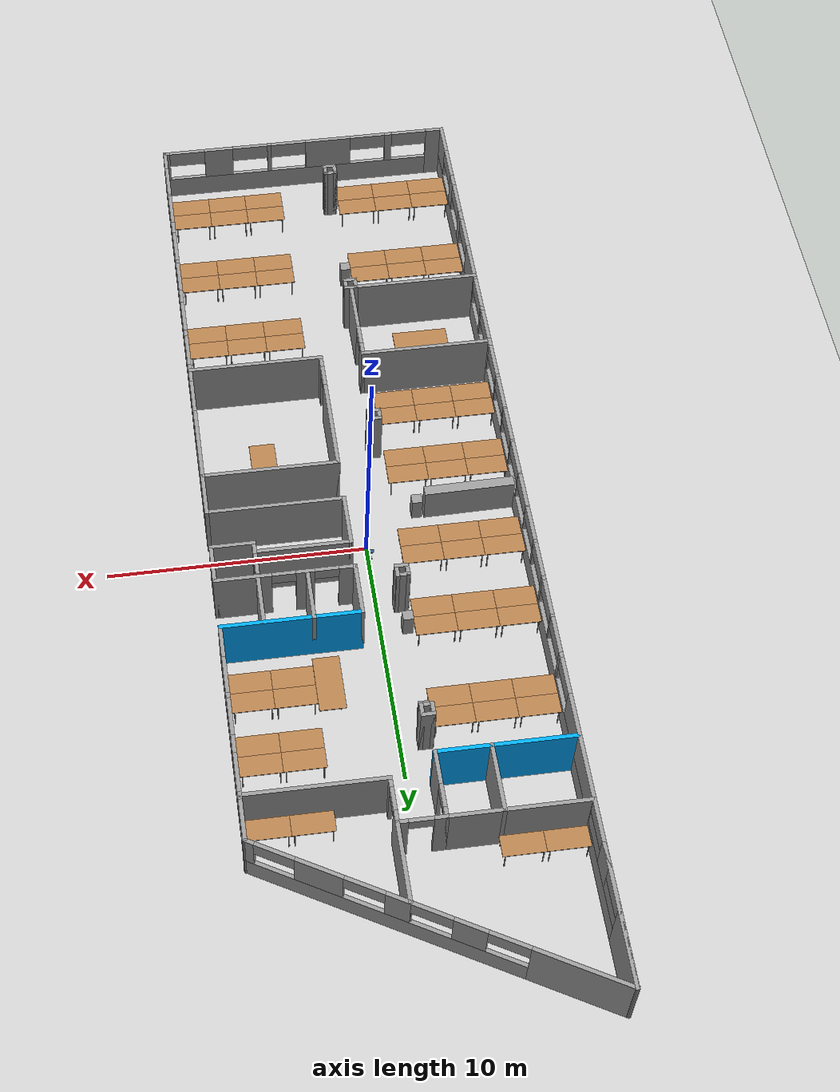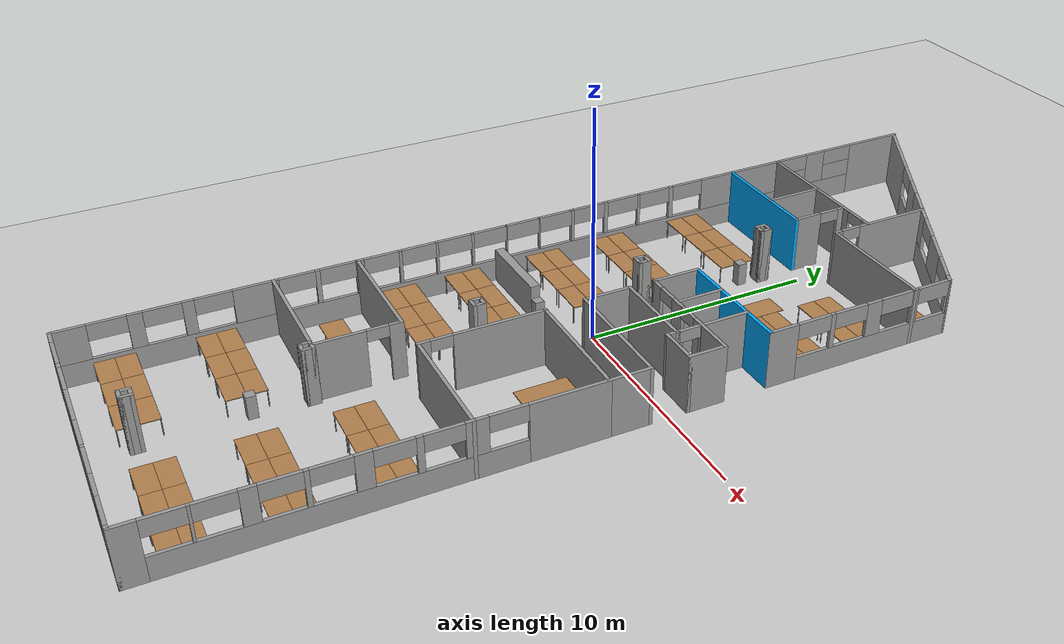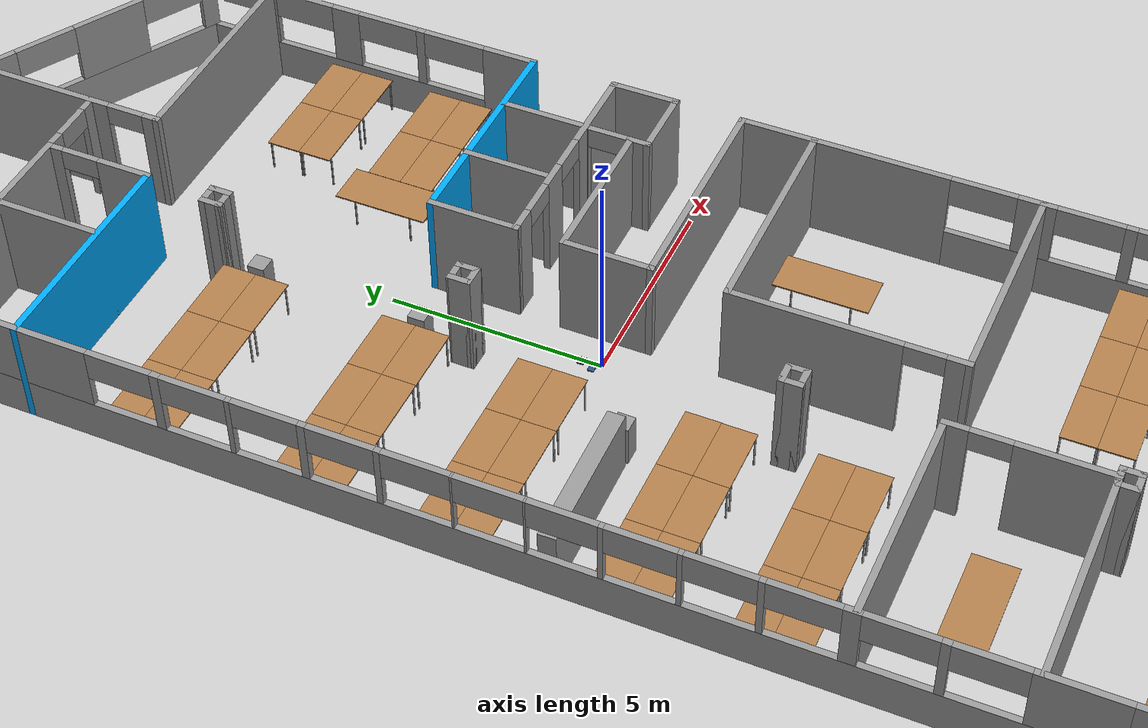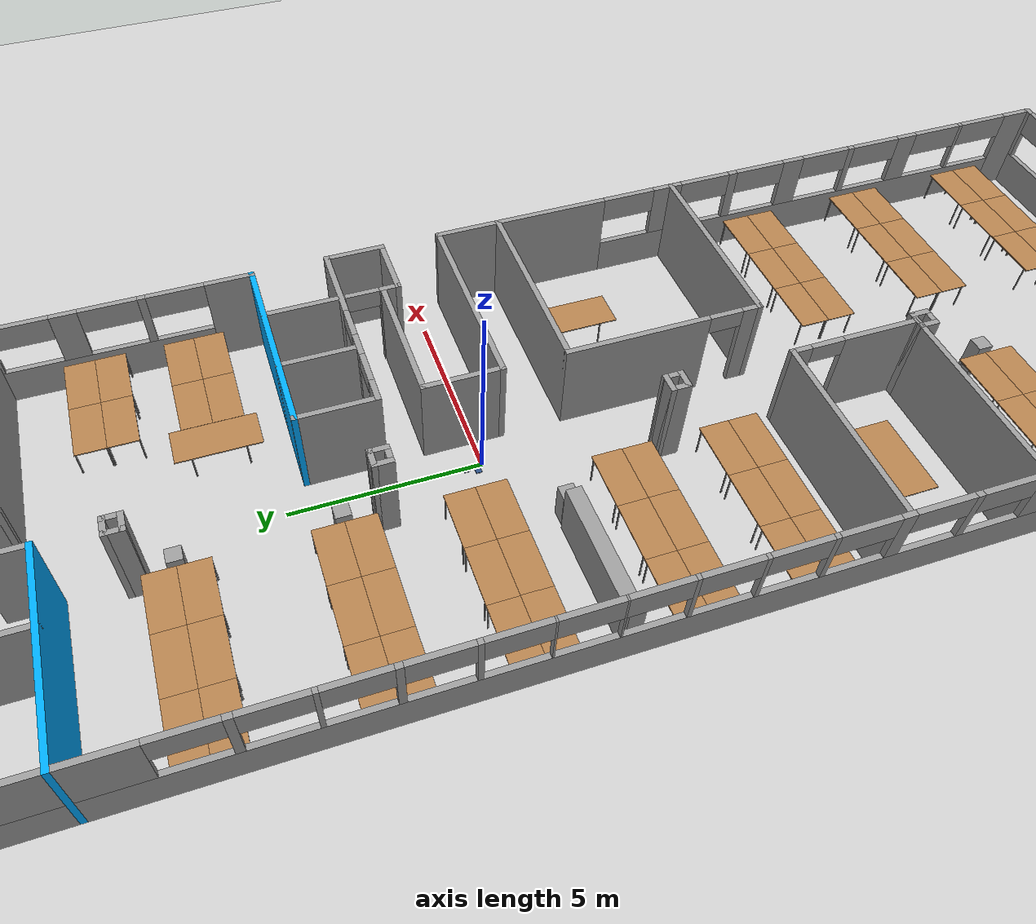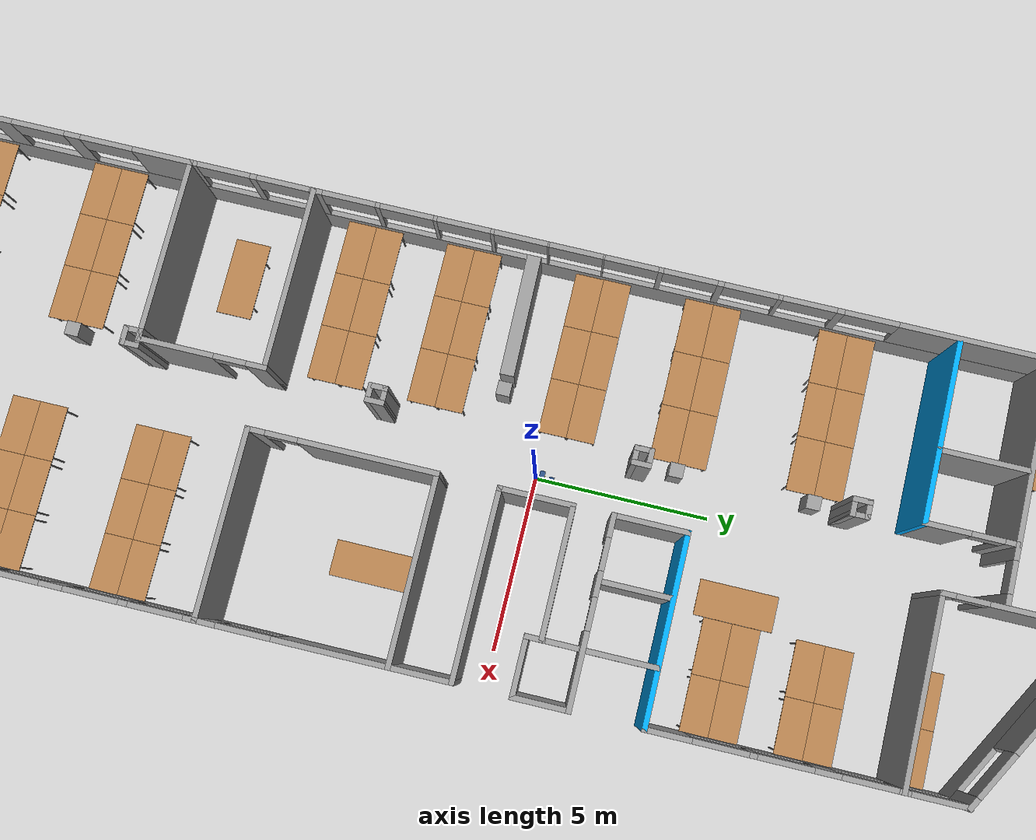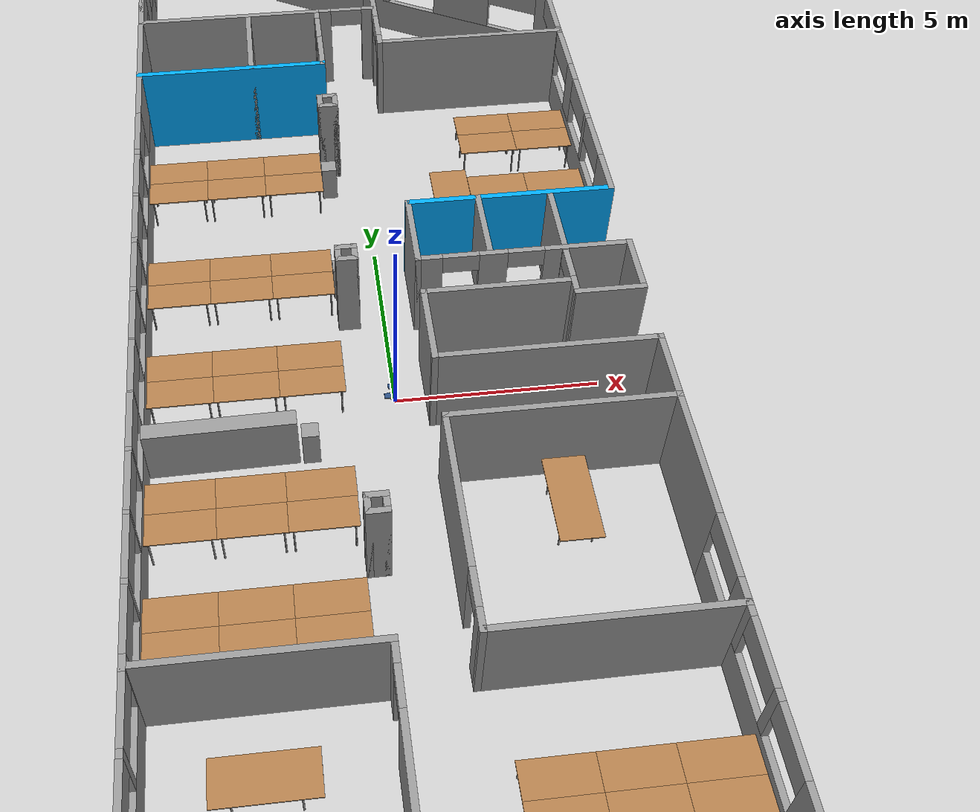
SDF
<sdf version="1.6">
 <world name="default">
  <plugin name="hello" filename="libhello.so"/>
  <light name="sun" type="directional">
   <pose>0 0 10 0 -0 0</pose>
   <diffuse>0.8 0.8 0.8 1</diffuse>
   <specular>0.2 0.2 0.2 1</specular>
   <attenuation>
    <range>1000</range>
    <constant>0.9</constant>
    <linear>0.01</linear>
    <quadratic>0.001</quadratic>
   </attenuation>
   <direction>-0.5 0.1 -0.9</direction>
  </light>
  <model name="ground_plane">
   <static>1</static>
   <link name="link">
    <collision name="collision">
     <geometry><plane><normal>0 0 1</normal><size>100 100</size></plane></geometry>
     <surface><friction><ode><mu>100</mu><mu2>50</mu2></ode></friction></surface>
    </collision>
    <visual name="visual">
     <cast_shadows>0</cast_shadows>
     <geometry><plane><normal>0 0 1</normal><size>100 100</size></plane></geometry>
     <material>
      <script><uri>file://media/materials/scripts/gazebo.material</uri><name>Gazebo/Grey</name></script>
     </material>
    </visual>
   </link>
  </model>
  <gravity>0 0 -9.8</gravity>
  <magnetic_field>6e-06 2.3e-05 -4.2e-05</magnetic_field>
  <atmosphere type="adiabatic"/>
  <physics name="default_physics" default="0" type="ode">
   <max_step_size>0.001</max_step_size>
   <real_time_factor>1</real_time_factor>
   <real_time_update_rate>1000</real_time_update_rate>
  </physics>
  <scene><ambient>0.4 0.4 0.4 1</ambient><background>0.7 0.7 0.7 1</background><shadows>1</shadows></scene>
  <spherical_coordinates>
   <surface_model>EARTH_WGS84</surface_model>
   <latitude_deg>0</latitude_deg>
   <longitude_deg>0</longitude_deg>
   <elevation>0</elevation>
   <heading_deg>0</heading_deg>
  </spherical_coordinates>
  <model name="Building">
   <link name="Wall_0">
    <pose>0 -19.6636 0 0 -0 0</pose>
    <visual name="Wall_0_Visual_0">
     <pose>-5.69408 0 1.25 0 -0 0</pose>
     <geometry><box><size>0.761843 0.15 2.5</size></box></geometry>
     <material>
      <script><uri>file://media/materials/scripts/gazebo.material</uri><name>Gazebo/Grey</name></script>
      <ambient>1 1 1 1</ambient>
     </material>
     <meta><layer>0</layer></meta>
    </visual>
    <collision name="Wall_0_Collision_0">
     <geometry><box><size>0.761843 0.15 2.5</size></box></geometry>
     <pose>-5.69408 0 1.25 0 -0 0</pose>
    </collision>
    <visual name="Wall_0_Visual_1">
     <pose>0.380922 0 0.5 0 -0 0</pose>
     <geometry><box><size>11.3882 0.15 1</size></box></geometry>
     <material>
      <script><uri>file://media/materials/scripts/gazebo.material</uri><name>Gazebo/Grey</name></script>
      <ambient>1 1 1 1</ambient>
     </material>
     <meta><layer>0</layer></meta>
    </visual>
    <collision name="Wall_0_Collision_1">
     <geometry><box><size>11.3882 0.15 1</size></box></geometry>
     <pose>0.380922 0 0.5 0 -0 0</pose>
    </collision>
    <visual name="Wall_0_Visual_2">
     <pose>-3.66593 0 1.75 0 -0 0</pose>
     <geometry><box><size>0.294453 0.15 1.5</size></box></geometry>
     <material>
      <script><uri>file://media/materials/scripts/gazebo.material</uri><name>Gazebo/Grey</name></script>
      <ambient>1 1 1 1</ambient>
     </material>
     <meta><layer>0</layer></meta>
    </visual>
    <collision name="Wall_0_Collision_2">
     <geometry><box><size>0.294453 0.15 1.5</size></box></geometry>
     <pose>-3.66593 0 1.75 0 -0 0</pose>
    </collision>
    <visual name="Wall_0_Visual_3">
     <pose>-1.044 0 1.75 0 -0 0</pose>
     <geometry><box><size>1.94941 0.15 1.5</size></box></geometry>
     <material>
      <script><uri>file://media/materials/scripts/gazebo.material</uri><name>Gazebo/Grey</name></script>
      <ambient>1 1 1 1</ambient>
     </material>
     <meta><layer>0</layer></meta>
    </visual>
    <collision name="Wall_0_Collision_3">
     <geometry><box><size>1.94941 0.15 1.5</size></box></geometry>
     <pose>-1.044 0 1.75 0 -0 0</pose>
    </collision>
    <visual name="Wall_0_Visual_4">
     <pose>1.51332 0 1.75 0 -0 0</pose>
     <geometry><box><size>0.165232 0.15 1.5</size></box></geometry>
     <material>
      <script><uri>file://media/materials/scripts/gazebo.material</uri><name>Gazebo/Grey</name></script>
      <ambient>1 1 1 1</ambient>
     </material>
     <meta><layer>0</layer></meta>
    </visual>
    <collision name="Wall_0_Collision_4">
     <geometry><box><size>0.165232 0.15 1.5</size></box></geometry>
     <pose>1.51332 0 1.75 0 -0 0</pose>
    </collision>
    <visual name="Wall_0_Visual_5">
     <pose>3.70368 0 1.75 0 -0 0</pose>
     <geometry><box><size>1.21548 0.15 1.5</size></box></geometry>
     <material>
      <script><uri>file://media/materials/scripts/gazebo.material</uri><name>Gazebo/Grey</name></script>
      <ambient>1 1 1 1</ambient>
     </material>
     <meta><layer>0</layer></meta>
    </visual>
    <collision name="Wall_0_Collision_5">
     <geometry><box><size>1.21548 0.15 1.5</size></box></geometry>
     <pose>3.70368 0 1.75 0 -0 0</pose>
    </collision>
    <visual name="Wall_0_Visual_6">
     <pose>5.94321 0 1.75 0 -0 0</pose>
     <geometry><box><size>0.263587 0.15 1.5</size></box></geometry>
     <material>
      <script><uri>file://media/materials/scripts/gazebo.material</uri><name>Gazebo/Grey</name></script>
      <ambient>1 1 1 1</ambient>
     </material>
     <meta><layer>0</layer></meta>
    </visual>
    <collision name="Wall_0_Collision_6">
     <geometry><box><size>0.263587 0.15 1.5</size></box></geometry>
     <pose>5.94321 0 1.75 0 -0 0</pose>
    </collision>
    <visual name="Wall_0_Visual_7">
     <pose>-4.56316 0 2.15 0 -0 0</pose>
     <geometry><box><size>1.5 0.15 0.7</size></box></geometry>
     <material>
      <script><uri>file://media/materials/scripts/gazebo.material</uri><name>Gazebo/Grey</name></script>
      <ambient>1 1 1 1</ambient>
     </material>
     <meta><layer>0</layer></meta>
    </visual>
    <collision name="Wall_0_Collision_7">
     <geometry><box><size>1.5 0.15 0.7</size></box></geometry>
     <pose>-4.56316 0 2.15 0 -0 0</pose>
    </collision>
    <visual name="Wall_0_Visual_8">
     <pose>-2.7687 0 2.15 0 -0 0</pose>
     <geometry><box><size>1.5 0.15 0.7</size></box></geometry>
     <material>
      <script><uri>file://media/materials/scripts/gazebo.material</uri><name>Gazebo/Grey</name></script>
      <ambient>1 1 1 1</ambient>
     </material>
     <meta><layer>0</layer></meta>
    </visual>
    <collision name="Wall_0_Collision_8">
     <geometry><box><size>1.5 0.15 0.7</size></box></geometry>
     <pose>-2.7687 0 2.15 0 -0 0</pose>
    </collision>
    <visual name="Wall_0_Visual_9">
     <pose>0.680705 0 2.15 0 -0 0</pose>
     <geometry><box><size>1.5 0.15 0.7</size></box></geometry>
     <material>
      <script><uri>file://media/materials/scripts/gazebo.material</uri><name>Gazebo/Grey</name></script>
      <ambient>1 1 1 1</ambient>
     </material>
     <meta><layer>0</layer></meta>
    </visual>
    <collision name="Wall_0_Collision_9">
     <geometry><box><size>1.5 0.15 0.7</size></box></geometry>
     <pose>0.680705 0 2.15 0 -0 0</pose>
    </collision>
    <visual name="Wall_0_Visual_10">
     <pose>2.34594 0 2.15 0 -0 0</pose>
     <geometry><box><size>1.5 0.15 0.7</size></box></geometry>
     <material>
      <script><uri>file://media/materials/scripts/gazebo.material</uri><name>Gazebo/Grey</name></script>
      <ambient>1 1 1 1</ambient>
     </material>
     <meta><layer>0</layer></meta>
    </visual>
    <collision name="Wall_0_Collision_10">
     <geometry><box><size>1.5 0.15 0.7</size></box></geometry>
     <pose>2.34594 0 2.15 0 -0 0</pose>
    </collision>
    <visual name="Wall_0_Visual_11">
     <pose>5.06141 0 2.15 0 -0 0</pose>
     <geometry><box><size>1.5 0.15 0.7</size></box></geometry>
     <material>
      <script><uri>file://media/materials/scripts/gazebo.material</uri><name>Gazebo/Grey</name></script>
      <ambient>1 1 1 1</ambient>
     </material>
     <meta><layer>0</layer></meta>
    </visual>
    <collision name="Wall_0_Collision_11">
     <geometry><box><size>1.5 0.15 0.7</size></box></geometry>
     <pose>5.06141 0 2.15 0 -0 0</pose>
    </collision>
   </link>
   <link name="Wall_10">
    <pose>6 -5.06361 0 0 0 -1.5708</pose>
    <visual name="Wall_10_Visual_0">
     <pose>-1.06584 0 1.25 0 -0 0</pose>
     <geometry><box><size>3.21833 0.15 2.5</size></box></geometry>
     <material>
      <script><uri>file://media/materials/scripts/gazebo.material</uri><name>Gazebo/Grey</name></script>
      <ambient>1 1 1 1</ambient>
     </material>
     <meta><layer>0</layer></meta>
    </visual>
    <collision name="Wall_10_Collision_0">
     <geometry><box><size>3.21833 0.15 2.5</size></box></geometry>
     <pose>-1.06584 0 1.25 0 -0 0</pose>
    </collision>
    <visual name="Wall_10_Visual_1">
     <pose>1.60916 0 0.5 0 -0 0</pose>
     <geometry><box><size>2.13167 0.15 1</size></box></geometry>
     <material>
      <script><uri>file://media/materials/scripts/gazebo.material</uri><name>Gazebo/Grey</name></script>
      <ambient>1 1 1 1</ambient>
     </material>
     <meta><layer>0</layer></meta>
    </visual>
    <collision name="Wall_10_Collision_1">
     <geometry><box><size>2.13167 0.15 1</size></box></geometry>
     <pose>1.60916 0 0.5 0 -0 0</pose>
    </collision>
    <visual name="Wall_10_Visual_2">
     <pose>2.35916 0 1.75 0 -0 0</pose>
     <geometry><box><size>0.631674 0.15 1.5</size></box></geometry>
     <material>
      <script><uri>file://media/materials/scripts/gazebo.material</uri><name>Gazebo/Grey</name></script>
      <ambient>1 1 1 1</ambient>
     </material>
     <meta><layer>0</layer></meta>
    </visual>
    <collision name="Wall_10_Collision_2">
     <geometry><box><size>0.631674 0.15 1.5</size></box></geometry>
     <pose>2.35916 0 1.75 0 -0 0</pose>
    </collision>
    <visual name="Wall_10_Visual_3">
     <pose>1.29333 0 2.15 0 -0 0</pose>
     <geometry><box><size>1.5 0.15 0.7</size></box></geometry>
     <material>
      <script><uri>file://media/materials/scripts/gazebo.material</uri><name>Gazebo/Grey</name></script>
      <ambient>1 1 1 1</ambient>
     </material>
     <meta><layer>0</layer></meta>
    </visual>
    <collision name="Wall_10_Collision_3">
     <geometry><box><size>1.5 0.15 0.7</size></box></geometry>
     <pose>1.29333 0 2.15 0 -0 0</pose>
    </collision>
   </link>
   <link name="Wall_100">
    <collision name="Wall_100_Collision">
     <geometry><box><size>0.55 0.15 2.5</size></box></geometry>
     <pose>0 0 1.25 0 -0 0</pose>
    </collision>
    <visual name="Wall_100_Visual">
     <pose>0 0 1.25 0 -0 0</pose>
     <geometry><box><size>0.55 0.15 2.5</size></box></geometry>
     <material>
      <script><uri>file://media/materials/scripts/gazebo.material</uri><name>Gazebo/Grey</name></script>
      <ambient>1 1 1 1</ambient>
     </material>
     <meta><layer>0</layer></meta>
    </visual>
    <pose>-0.9 -18.0636 0 0 -0 0</pose>
   </link>
   <link name="Wall_102">
    <collision name="Wall_102_Collision">
     <geometry><box><size>0.55 0.15 2.5</size></box></geometry>
     <pose>0 0 1.25 0 -0 0</pose>
    </collision>
    <visual name="Wall_102_Visual">
     <pose>0 0 1.25 0 -0 0</pose>
     <geometry><box><size>0.55 0.15 2.5</size></box></geometry>
     <material>
      <script><uri>file://media/materials/scripts/gazebo.material</uri><name>Gazebo/Grey</name></script>
      <ambient>1 1 1 1</ambient>
     </material>
     <meta><layer>0</layer></meta>
    </visual>
    <pose>-0.9 -17.6636 0 0 -0 0</pose>
   </link>
   <link name="Wall_104">
    <collision name="Wall_104_Collision">
     <geometry><box><size>0.55 0.15 2.5</size></box></geometry>
     <pose>0 0 1.25 0 -0 0</pose>
    </collision>
    <visual name="Wall_104_Visual">
     <pose>0 0 1.25 0 -0 0</pose>
     <geometry><box><size>0.55 0.15 2.5</size></box></geometry>
     <material>
      <script><uri>file://media/materials/scripts/gazebo.material</uri><name>Gazebo/Grey</name></script>
      <ambient>1 1 1 1</ambient>
     </material>
     <meta><layer>0</layer></meta>
    </visual>
    <pose>-1.1 -17.8636 0 0 -0 1.5708</pose>
   </link>
   <link name="Wall_106">
    <collision name="Wall_106_Collision">
     <geometry><box><size>0.55 0.15 2.5</size></box></geometry>
     <pose>0 0 1.25 0 -0 0</pose>
    </collision>
    <visual name="Wall_106_Visual">
     <pose>0 0 1.25 0 -0 0</pose>
     <geometry><box><size>0.55 0.15 2.5</size></box></geometry>
     <material>
      <script><uri>file://media/materials/scripts/gazebo.material</uri><name>Gazebo/Grey</name></script>
      <ambient>1 1 1 1</ambient>
     </material>
     <meta><layer>0</layer></meta>
    </visual>
    <pose>-0.7 -17.8636 0 0 -0 1.5708</pose>
   </link>
   <link name="Wall_113">
    <collision name="Wall_113_Collision">
     <geometry><box><size>1.75 0.15 2.5</size></box></geometry>
     <pose>0 0 1.25 0 -0 0</pose>
    </collision>
    <visual name="Wall_113_Visual">
     <pose>0 0 1.25 0 -0 0</pose>
     <geometry><box><size>1.75 0.15 2.5</size></box></geometry>
     <material>
      <script><uri>file://media/materials/scripts/gazebo.material</uri><name>Gazebo/Grey</name></script>
      <ambient>1 1 1 1</ambient>
     </material>
     <meta><layer>0</layer></meta>
    </visual>
    <pose>5.2 0.836388 0 0 -0 3.14159</pose>
   </link>
   <link name="Wall_115">
    <pose>4.4 1.51139 0 0 -0 1.5708</pose>
    <visual name="Wall_115_Visual_0">
     <pose>-0.461821 0 1.25 0 -0 0</pose>
     <geometry><box><size>0.576358 0.15 2.5</size></box></geometry>
     <material>
      <script><uri>file://media/materials/scripts/gazebo.material</uri><name>Gazebo/Grey</name></script>
      <ambient>1 1 1 1</ambient>
     </material>
     <meta><layer>0</layer></meta>
    </visual>
    <collision name="Wall_115_Collision_0">
     <geometry><box><size>0.576358 0.15 2.5</size></box></geometry>
     <pose>-0.461821 0 1.25 0 -0 0</pose>
    </collision>
    <visual name="Wall_115_Visual_1">
     <pose>0.738179 0 1.25 0 -0 0</pose>
     <geometry><box><size>0.023642 0.15 2.5</size></box></geometry>
     <material>
      <script><uri>file://media/materials/scripts/gazebo.material</uri><name>Gazebo/Grey</name></script>
      <ambient>1 1 1 1</ambient>
     </material>
     <meta><layer>0</layer></meta>
    </visual>
    <collision name="Wall_115_Collision_1">
     <geometry><box><size>0.023642 0.15 2.5</size></box></geometry>
     <pose>0.738179 0 1.25 0 -0 0</pose>
    </collision>
    <visual name="Wall_115_Visual_2">
     <pose>0.276358 0 2.25 0 -0 0</pose>
     <geometry><box><size>0.9 0.15 0.5</size></box></geometry>
     <material>
      <script><uri>file://media/materials/scripts/gazebo.material</uri><name>Gazebo/Grey</name></script>
      <ambient>1 1 1 1</ambient>
     </material>
     <meta><layer>0</layer></meta>
    </visual>
    <collision name="Wall_115_Collision_2">
     <geometry><box><size>0.9 0.15 0.5</size></box></geometry>
     <pose>0.276358 0 2.25 0 -0 0</pose>
    </collision>
   </link>
   <link name="Wall_117">
    <collision name="Wall_117_Collision">
     <geometry><box><size>3.75 0.15 2.5</size></box></geometry>
     <pose>0 0 1.25 0 -0 0</pose>
    </collision>
    <visual name="Wall_117_Visual">
     <pose>0 0 1.25 0 -0 0</pose>
     <geometry><box><size>3.75 0.15 2.5</size></box></geometry>
     <material>
      <script><uri>file://media/materials/scripts/gazebo.material</uri><name>Gazebo/Grey</name></script>
      <ambient>1 1 1 1</ambient>
     </material>
     <meta><layer>0</layer></meta>
    </visual>
    <pose>2.6 1.23639 0 0 -0 0</pose>
   </link>
   <link name="Wall_12">
    <pose>0 16.2364 0 0 0 -0.515549</pose>
    <visual name="Wall_12_Visual_0">
     <pose>-5.14943 0 1.25 0 -0 0</pose>
     <geometry><box><size>3.6439 0.15 2.5</size></box></geometry>
     <material>
      <script><uri>file://media/materials/scripts/gazebo.material</uri><name>Gazebo/Grey</name></script>
      <ambient>1 1 1 1</ambient>
     </material>
     <meta><layer>0</layer></meta>
    </visual>
    <collision name="Wall_12_Collision_0">
     <geometry><box><size>3.6439 0.15 2.5</size></box></geometry>
     <pose>-5.14943 0 1.25 0 -0 0</pose>
    </collision>
    <visual name="Wall_12_Visual_1">
     <pose>1.82195 0 0.5 0 -0 0</pose>
     <geometry><box><size>10.2989 0.15 1</size></box></geometry>
     <material>
      <script><uri>file://media/materials/scripts/gazebo.material</uri><name>Gazebo/Grey</name></script>
      <ambient>1 1 1 1</ambient>
     </material>
     <meta><layer>0</layer></meta>
    </visual>
    <collision name="Wall_12_Collision_1">
     <geometry><box><size>10.2989 0.15 1</size></box></geometry>
     <pose>1.82195 0 0.5 0 -0 0</pose>
    </collision>
    <visual name="Wall_12_Visual_2">
     <pose>-1.22144 0 1.75 0 -0 0</pose>
     <geometry><box><size>1.21209 0.15 1.5</size></box></geometry>
     <material>
      <script><uri>file://media/materials/scripts/gazebo.material</uri><name>Gazebo/Grey</name></script>
      <ambient>1 1 1 1</ambient>
     </material>
     <meta><layer>0</layer></meta>
    </visual>
    <collision name="Wall_12_Collision_2">
     <geometry><box><size>1.21209 0.15 1.5</size></box></geometry>
     <pose>-1.22144 0 1.75 0 -0 0</pose>
    </collision>
    <visual name="Wall_12_Visual_3">
     <pose>1.33933 0 1.75 0 -0 0</pose>
     <geometry><box><size>0.909442 0.15 1.5</size></box></geometry>
     <material>
      <script><uri>file://media/materials/scripts/gazebo.material</uri><name>Gazebo/Grey</name></script>
      <ambient>1 1 1 1</ambient>
     </material>
     <meta><layer>0</layer></meta>
    </visual>
    <collision name="Wall_12_Collision_3">
     <geometry><box><size>0.909442 0.15 1.5</size></box></geometry>
     <pose>1.33933 0 1.75 0 -0 0</pose>
    </collision>
    <visual name="Wall_12_Visual_4">
     <pose>4.18293 0 1.75 0 -0 0</pose>
     <geometry><box><size>1.77777 0.15 1.5</size></box></geometry>
     <material>
      <script><uri>file://media/materials/scripts/gazebo.material</uri><name>Gazebo/Grey</name></script>
      <ambient>1 1 1 1</ambient>
     </material>
     <meta><layer>0</layer></meta>
    </visual>
    <collision name="Wall_12_Collision_4">
     <geometry><box><size>1.77777 0.15 1.5</size></box></geometry>
     <pose>4.18293 0 1.75 0 -0 0</pose>
    </collision>
    <visual name="Wall_12_Visual_5">
     <pose>6.7716 0 1.75 0 -0 0</pose>
     <geometry><box><size>0.399558 0.15 1.5</size></box></geometry>
     <material>
      <script><uri>file://media/materials/scripts/gazebo.material</uri><name>Gazebo/Grey</name></script>
      <ambient>1 1 1 1</ambient>
     </material>
     <meta><layer>0</layer></meta>
    </visual>
    <collision name="Wall_12_Collision_5">
     <geometry><box><size>0.399558 0.15 1.5</size></box></geometry>
     <pose>6.7716 0 1.75 0 -0 0</pose>
    </collision>
    <visual name="Wall_12_Visual_6">
     <pose>-2.57748 0 2.15 0 -0 0</pose>
     <geometry><box><size>1.5 0.15 0.7</size></box></geometry>
     <material>
      <script><uri>file://media/materials/scripts/gazebo.material</uri><name>Gazebo/Grey</name></script>
      <ambient>1 1 1 1</ambient>
     </material>
     <meta><layer>0</layer></meta>
    </visual>
    <collision name="Wall_12_Collision_6">
     <geometry><box><size>1.5 0.15 0.7</size></box></geometry>
     <pose>-2.57748 0 2.15 0 -0 0</pose>
    </collision>
    <visual name="Wall_12_Visual_7">
     <pose>0.134607 0 2.15 0 -0 0</pose>
     <geometry><box><size>1.5 0.15 0.7</size></box></geometry>
     <material>
      <script><uri>file://media/materials/scripts/gazebo.material</uri><name>Gazebo/Grey</name></script>
      <ambient>1 1 1 1</ambient>
     </material>
     <meta><layer>0</layer></meta>
    </visual>
    <collision name="Wall_12_Collision_7">
     <geometry><box><size>1.5 0.15 0.7</size></box></geometry>
     <pose>0.134607 0 2.15 0 -0 0</pose>
    </collision>
    <visual name="Wall_12_Visual_8">
     <pose>2.54405 0 2.15 0 -0 0</pose>
     <geometry><box><size>1.5 0.15 0.7</size></box></geometry>
     <material>
      <script><uri>file://media/materials/scripts/gazebo.material</uri><name>Gazebo/Grey</name></script>
      <ambient>1 1 1 1</ambient>
     </material>
     <meta><layer>0</layer></meta>
    </visual>
    <collision name="Wall_12_Collision_8">
     <geometry><box><size>1.5 0.15 0.7</size></box></geometry>
     <pose>2.54405 0 2.15 0 -0 0</pose>
    </collision>
    <visual name="Wall_12_Visual_9">
     <pose>5.82182 0 2.15 0 -0 0</pose>
     <geometry><box><size>1.5 0.15 0.7</size></box></geometry>
     <material>
      <script><uri>file://media/materials/scripts/gazebo.material</uri><name>Gazebo/Grey</name></script>
      <ambient>1 1 1 1</ambient>
     </material>
     <meta><layer>0</layer></meta>
    </visual>
    <collision name="Wall_12_Collision_9">
     <geometry><box><size>1.5 0.15 0.7</size></box></geometry>
     <pose>5.82182 0 2.15 0 -0 0</pose>
    </collision>
   </link>
   <link name="Wall_123">
    <collision name="Wall_123_Collision">
     <geometry><box><size>2 0.15 2.5</size></box></geometry>
     <pose>0 0 1.25 0 -0 0</pose>
    </collision>
    <visual name="Wall_123_Visual">
     <pose>0 0 1.25 0 -0 0</pose>
     <geometry><box><size>2 0.15 2.5</size></box></geometry>
     <material>
      <script><uri>file://media/materials/scripts/gazebo.material</uri><name>Gazebo/Grey</name></script>
      <ambient>1 1 1 1</ambient>
     </material>
     <meta><layer>0</layer></meta>
    </visual>
    <pose>4.40848 3.39488 0 0 -0 1.5708</pose>
   </link>
   <link name="Wall_126">
    <collision name="Wall_126_Collision">
     <geometry><box><size>2 0.15 2.5</size></box></geometry>
     <pose>0 0 1.25 0 -0 0</pose>
    </collision>
    <visual name="Wall_126_Visual">
     <pose>0 0 1.25 0 -0 0</pose>
     <geometry><box><size>2 0.15 2.5</size></box></geometry>
     <material>
      <script><uri>file://media/materials/scripts/gazebo.material</uri><name>Gazebo/Grey</name></script>
      <ambient>1 1 1 1</ambient>
     </material>
     <meta><layer>0</layer></meta>
    </visual>
    <pose>2.573 3.41139 0 0 0 -1.5708</pose>
   </link>
   <link name="Wall_14">
    <collision name="Wall_14_Collision">
     <geometry><box><size>1.85 0.15 2.5</size></box></geometry>
     <pose>0 0 1.25 0 -0 0</pose>
    </collision>
    <visual name="Wall_14_Visual">
     <pose>0 0 1.25 0 -0 0</pose>
     <geometry><box><size>1.85 0.15 2.5</size></box></geometry>
     <material>
      <script><uri>file://media/materials/scripts/gazebo.material</uri><name>Gazebo/Grey</name></script>
      <ambient>1 1 1 1</ambient>
     </material>
     <meta><layer>0</layer></meta>
    </visual>
    <pose>6 -1.61361 0 0 -0 1.5708</pose>
   </link>
   <link name="Wall_16">
    <collision name="Wall_16_Collision">
     <geometry><box><size>5.35 0.15 2.5</size></box></geometry>
     <pose>0 0 1.25 0 -0 0</pose>
    </collision>
    <visual name="Wall_16_Visual">
     <pose>0 0 1.25 0 -0 0</pose>
     <geometry><box><size>5.35 0.15 2.5</size></box></geometry>
     <material>
      <script><uri>file://media/materials/scripts/gazebo.material</uri><name>Gazebo/Grey</name></script>
      <ambient>1 1 1 1</ambient>
     </material>
     <meta><layer>0</layer></meta>
    </visual>
    <pose>3.4 -0.763612 0 0 -0 3.14159</pose>
   </link>
   <link name="Wall_18">
    <collision name="Wall_18_Collision">
     <geometry><box><size>2.15 0.15 2.5</size></box></geometry>
     <pose>0 0 1.25 0 -0 0</pose>
    </collision>
    <visual name="Wall_18_Visual">
     <pose>0 0 1.25 0 -0 0</pose>
     <geometry><box><size>2.15 0.15 2.5</size></box></geometry>
     <material>
      <script><uri>file://media/materials/scripts/gazebo.material</uri><name>Gazebo/Grey</name></script>
      <ambient>1 1 1 1</ambient>
     </material>
     <meta><layer>0</layer></meta>
    </visual>
    <pose>0.8 0.236388 0 0 -0 1.5708</pose>
   </link>
   <link name="Wall_2">
    <pose>6 -13.6636 0 0 -0 1.5708</pose>
    <visual name="Wall_2_Visual_0">
     <pose>-5.5945 0 1.25 0 -0 0</pose>
     <geometry><box><size>0.961004 0.15 2.5</size></box></geometry>
     <material>
      <script><uri>file://media/materials/scripts/gazebo.material</uri><name>Gazebo/Grey</name></script>
      <ambient>1 1 1 1</ambient>
     </material>
     <meta><layer>0</layer></meta>
    </visual>
    <collision name="Wall_2_Collision_0">
     <geometry><box><size>0.961004 0.15 2.5</size></box></geometry>
     <pose>-5.5945 0 1.25 0 -0 0</pose>
    </collision>
    <visual name="Wall_2_Visual_1">
     <pose>0.480502 0 0.5 0 -0 0</pose>
     <geometry><box><size>11.189 0.15 1</size></box></geometry>
     <material>
      <script><uri>file://media/materials/scripts/gazebo.material</uri><name>Gazebo/Grey</name></script>
      <ambient>1 1 1 1</ambient>
     </material>
     <meta><layer>0</layer></meta>
    </visual>
    <collision name="Wall_2_Collision_1">
     <geometry><box><size>11.189 0.15 1</size></box></geometry>
     <pose>0.480502 0 0.5 0 -0 0</pose>
    </collision>
    <visual name="Wall_2_Visual_2">
     <pose>-3.56236 0 1.75 0 -0 0</pose>
     <geometry><box><size>0.103271 0.15 1.5</size></box></geometry>
     <material>
      <script><uri>file://media/materials/scripts/gazebo.material</uri><name>Gazebo/Grey</name></script>
      <ambient>1 1 1 1</ambient>
     </material>
     <meta><layer>0</layer></meta>
    </visual>
    <collision name="Wall_2_Collision_2">
     <geometry><box><size>0.103271 0.15 1.5</size></box></geometry>
     <pose>-3.56236 0 1.75 0 -0 0</pose>
    </collision>
    <visual name="Wall_2_Visual_3">
     <pose>-1.70491 0 1.75 0 -0 0</pose>
     <geometry><box><size>0.611626 0.15 1.5</size></box></geometry>
     <material>
      <script><uri>file://media/materials/scripts/gazebo.material</uri><name>Gazebo/Grey</name></script>
      <ambient>1 1 1 1</ambient>
     </material>
     <meta><layer>0</layer></meta>
    </visual>
    <collision name="Wall_2_Collision_3">
     <geometry><box><size>0.611626 0.15 1.5</size></box></geometry>
     <pose>-1.70491 0 1.75 0 -0 0</pose>
    </collision>
    <visual name="Wall_2_Visual_4">
     <pose>0.191642 0 1.75 0 -0 0</pose>
     <geometry><box><size>0.18148 0.15 1.5</size></box></geometry>
     <material>
      <script><uri>file://media/materials/scripts/gazebo.material</uri><name>Gazebo/Grey</name></script>
      <ambient>1 1 1 1</ambient>
     </material>
     <meta><layer>0</layer></meta>
    </visual>
    <collision name="Wall_2_Collision_4">
     <geometry><box><size>0.18148 0.15 1.5</size></box></geometry>
     <pose>0.191642 0 1.75 0 -0 0</pose>
    </collision>
    <visual name="Wall_2_Visual_5">
     <pose>2.10775 0 1.75 0 -0 0</pose>
     <geometry><box><size>0.65073 0.15 1.5</size></box></geometry>
     <material>
      <script><uri>file://media/materials/scripts/gazebo.material</uri><name>Gazebo/Grey</name></script>
      <ambient>1 1 1 1</ambient>
     </material>
     <meta><layer>0</layer></meta>
    </visual>
    <collision name="Wall_2_Collision_5">
     <geometry><box><size>0.65073 0.15 1.5</size></box></geometry>
     <pose>2.10775 0 1.75 0 -0 0</pose>
    </collision>
    <visual name="Wall_2_Visual_6">
     <pose>4.06295 0 1.75 0 -0 0</pose>
     <geometry><box><size>0.259688 0.15 1.5</size></box></geometry>
     <material>
      <script><uri>file://media/materials/scripts/gazebo.material</uri><name>Gazebo/Grey</name></script>
      <ambient>1 1 1 1</ambient>
     </material>
     <meta><layer>0</layer></meta>
    </visual>
    <collision name="Wall_2_Collision_6">
     <geometry><box><size>0.259688 0.15 1.5</size></box></geometry>
     <pose>4.06295 0 1.75 0 -0 0</pose>
    </collision>
    <visual name="Wall_2_Visual_7">
     <pose>5.8839 0 1.75 0 -0 0</pose>
     <geometry><box><size>0.382201 0.15 1.5</size></box></geometry>
     <material>
      <script><uri>file://media/materials/scripts/gazebo.material</uri><name>Gazebo/Grey</name></script>
      <ambient>1 1 1 1</ambient>
     </material>
     <meta><layer>0</layer></meta>
    </visual>
    <collision name="Wall_2_Collision_7">
     <geometry><box><size>0.382201 0.15 1.5</size></box></geometry>
     <pose>5.8839 0 1.75 0 -0 0</pose>
    </collision>
    <visual name="Wall_2_Visual_8">
     <pose>-4.364 0 2.15 0 -0 0</pose>
     <geometry><box><size>1.5 0.15 0.7</size></box></geometry>
     <material>
      <script><uri>file://media/materials/scripts/gazebo.material</uri><name>Gazebo/Grey</name></script>
      <ambient>1 1 1 1</ambient>
     </material>
     <meta><layer>0</layer></meta>
    </visual>
    <collision name="Wall_2_Collision_8">
     <geometry><box><size>1.5 0.15 0.7</size></box></geometry>
     <pose>-4.364 0 2.15 0 -0 0</pose>
    </collision>
    <visual name="Wall_2_Visual_9">
     <pose>-2.76072 0 2.15 0 -0 0</pose>
     <geometry><box><size>1.5 0.15 0.7</size></box></geometry>
     <material>
      <script><uri>file://media/materials/scripts/gazebo.material</uri><name>Gazebo/Grey</name></script>
      <ambient>1 1 1 1</ambient>
     </material>
     <meta><layer>0</layer></meta>
    </visual>
    <collision name="Wall_2_Collision_9">
     <geometry><box><size>1.5 0.15 0.7</size></box></geometry>
     <pose>-2.76072 0 2.15 0 -0 0</pose>
    </collision>
    <visual name="Wall_2_Visual_10">
     <pose>-0.649098 0 2.15 0 -0 0</pose>
     <geometry><box><size>1.5 0.15 0.7</size></box></geometry>
     <material>
      <script><uri>file://media/materials/scripts/gazebo.material</uri><name>Gazebo/Grey</name></script>
      <ambient>1 1 1 1</ambient>
     </material>
     <meta><layer>0</layer></meta>
    </visual>
    <collision name="Wall_2_Collision_10">
     <geometry><box><size>1.5 0.15 0.7</size></box></geometry>
     <pose>-0.649098 0 2.15 0 -0 0</pose>
    </collision>
    <visual name="Wall_2_Visual_11">
     <pose>1.03238 0 2.15 0 -0 0</pose>
     <geometry><box><size>1.5 0.15 0.7</size></box></geometry>
     <material>
      <script><uri>file://media/materials/scripts/gazebo.material</uri><name>Gazebo/Grey</name></script>
      <ambient>1 1 1 1</ambient>
     </material>
     <meta><layer>0</layer></meta>
    </visual>
    <collision name="Wall_2_Collision_11">
     <geometry><box><size>1.5 0.15 0.7</size></box></geometry>
     <pose>1.03238 0 2.15 0 -0 0</pose>
    </collision>
    <visual name="Wall_2_Visual_12">
     <pose>3.18311 0 2.15 0 -0 0</pose>
     <geometry><box><size>1.5 0.15 0.7</size></box></geometry>
     <material>
      <script><uri>file://media/materials/scripts/gazebo.material</uri><name>Gazebo/Grey</name></script>
      <ambient>1 1 1 1</ambient>
     </material>
     <meta><layer>0</layer></meta>
    </visual>
    <collision name="Wall_2_Collision_12">
     <geometry><box><size>1.5 0.15 0.7</size></box></geometry>
     <pose>3.18311 0 2.15 0 -0 0</pose>
    </collision>
    <visual name="Wall_2_Visual_13">
     <pose>4.9428 0 2.15 0 -0 0</pose>
     <geometry><box><size>1.5 0.15 0.7</size></box></geometry>
     <material>
      <script><uri>file://media/materials/scripts/gazebo.material</uri><name>Gazebo/Grey</name></script>
      <ambient>1 1 1 1</ambient>
     </material>
     <meta><layer>0</layer></meta>
    </visual>
    <collision name="Wall_2_Collision_13">
     <geometry><box><size>1.5 0.15 0.7</size></box></geometry>
     <pose>4.9428 0 2.15 0 -0 0</pose>
    </collision>
   </link>
   <link name="Wall_20">
    <collision name="Wall_20_Collision">
     <geometry><box><size>5.35 0.15 2.5</size></box></geometry>
     <pose>0 0 1.25 0 -0 0</pose>
    </collision>
    <visual name="Wall_20_Visual">
     <pose>0 0 1.25 0 -0 0</pose>
     <geometry><box><size>5.35 0.15 2.5</size></box></geometry>
     <material>
      <script><uri>file://media/materials/scripts/gazebo.material</uri><name>Gazebo/Grey</name></script>
      <ambient>0 0.666667 1 1</ambient>
     </material>
     <meta><layer>0</layer></meta>
    </visual>
    <pose>3.4 4.33639 0 0 -0 0</pose>
   </link>
   <link name="Wall_22">
    <collision name="Wall_22_Collision">
     <geometry><box><size>2.15 0.15 2.5</size></box></geometry>
     <pose>0 0 1.25 0 -0 0</pose>
    </collision>
    <visual name="Wall_22_Visual">
     <pose>0 0 1.25 0 -0 0</pose>
     <geometry><box><size>2.15 0.15 2.5</size></box></geometry>
     <material>
      <script><uri>file://media/materials/scripts/gazebo.material</uri><name>Gazebo/Grey</name></script>
      <ambient>1 1 1 1</ambient>
     </material>
     <meta><layer>0</layer></meta>
    </visual>
    <pose>0.8 3.33639 0 0 0 -1.5708</pose>
   </link>
   <link name="Wall_24">
    <pose>3.4 2.33639 0 0 -0 0</pose>
    <visual name="Wall_24_Visual_0">
     <pose>-2.33821 0 1.25 0 -0 0</pose>
     <geometry><box><size>0.673574 0.15 2.5</size></box></geometry>
     <material>
      <script><uri>file://media/materials/scripts/gazebo.material</uri><name>Gazebo/Grey</name></script>
      <ambient>1 1 1 1</ambient>
     </material>
     <meta><layer>0</layer></meta>
    </visual>
    <collision name="Wall_24_Collision_0">
     <geometry><box><size>0.673574 0.15 2.5</size></box></geometry>
     <pose>-2.33821 0 1.25 0 -0 0</pose>
    </collision>
    <visual name="Wall_24_Visual_1">
     <pose>-0.749839 0 1.25 0 -0 0</pose>
     <geometry><box><size>0.703173 0.15 2.5</size></box></geometry>
     <material>
      <script><uri>file://media/materials/scripts/gazebo.material</uri><name>Gazebo/Grey</name></script>
      <ambient>1 1 1 1</ambient>
     </material>
     <meta><layer>0</layer></meta>
    </visual>
    <collision name="Wall_24_Collision_1">
     <geometry><box><size>0.703173 0.15 2.5</size></box></geometry>
     <pose>-0.749839 0 1.25 0 -0 0</pose>
    </collision>
    <visual name="Wall_24_Visual_2">
     <pose>1.58837 0 1.25 0 -0 0</pose>
     <geometry><box><size>2.17325 0.15 2.5</size></box></geometry>
     <material>
      <script><uri>file://media/materials/scripts/gazebo.material</uri><name>Gazebo/Grey</name></script>
      <ambient>1 1 1 1</ambient>
     </material>
     <meta><layer>0</layer></meta>
    </visual>
    <collision name="Wall_24_Collision_2">
     <geometry><box><size>2.17325 0.15 2.5</size></box></geometry>
     <pose>1.58837 0 1.25 0 -0 0</pose>
    </collision>
    <visual name="Wall_24_Visual_3">
     <pose>-1.55143 0 2.25 0 -0 0</pose>
     <geometry><box><size>0.9 0.15 0.5</size></box></geometry>
     <material>
      <script><uri>file://media/materials/scripts/gazebo.material</uri><name>Gazebo/Grey</name></script>
      <ambient>1 1 1 1</ambient>
     </material>
     <meta><layer>0</layer></meta>
    </visual>
    <collision name="Wall_24_Collision_3">
     <geometry><box><size>0.9 0.15 0.5</size></box></geometry>
     <pose>-1.55143 0 2.25 0 -0 0</pose>
    </collision>
    <visual name="Wall_24_Visual_4">
     <pose>0.051747 0 2.25 0 -0 0</pose>
     <geometry><box><size>0.9 0.15 0.5</size></box></geometry>
     <material>
      <script><uri>file://media/materials/scripts/gazebo.material</uri><name>Gazebo/Grey</name></script>
      <ambient>1 1 1 1</ambient>
     </material>
     <meta><layer>0</layer></meta>
    </visual>
    <collision name="Wall_24_Collision_4">
     <geometry><box><size>0.9 0.15 0.5</size></box></geometry>
     <pose>0.051747 0 2.25 0 -0 0</pose>
    </collision>
   </link>
   <link name="Wall_26">
    <collision name="Wall_26_Collision">
     <geometry><box><size>1.65 0.15 2.5</size></box></geometry>
     <pose>0 0 1.25 0 -0 0</pose>
    </collision>
    <visual name="Wall_26_Visual">
     <pose>0 0 1.25 0 -0 0</pose>
     <geometry><box><size>1.65 0.15 2.5</size></box></geometry>
     <material>
      <script><uri>file://media/materials/scripts/gazebo.material</uri><name>Gazebo/Grey</name></script>
      <ambient>1 1 1 1</ambient>
     </material>
     <meta><layer>0</layer></meta>
    </visual>
    <pose>6 1.58639 0 0 0 -1.5708</pose>
   </link>
   <link name="Wall_34">
    <pose>6 8.58639 0 0 -0 1.5708</pose>
    <visual name="Wall_34_Visual_0">
     <pose>-3.66132 0 1.25 0 -0 0</pose>
     <geometry><box><size>1.32735 0.15 2.5</size></box></geometry>
     <material>
      <script><uri>file://media/materials/scripts/gazebo.material</uri><name>Gazebo/Grey</name></script>
      <ambient>1 1 1 1</ambient>
     </material>
     <meta><layer>0</layer></meta>
    </visual>
    <collision name="Wall_34_Collision_0">
     <geometry><box><size>1.32735 0.15 2.5</size></box></geometry>
     <pose>-3.66132 0 1.25 0 -0 0</pose>
    </collision>
    <visual name="Wall_34_Visual_1">
     <pose>0.663676 0 0.5 0 -0 0</pose>
     <geometry><box><size>7.32265 0.15 1</size></box></geometry>
     <material>
      <script><uri>file://media/materials/scripts/gazebo.material</uri><name>Gazebo/Grey</name></script>
      <ambient>1 1 1 1</ambient>
     </material>
     <meta><layer>0</layer></meta>
    </visual>
    <collision name="Wall_34_Collision_1">
     <geometry><box><size>7.32265 0.15 1</size></box></geometry>
     <pose>0.663676 0 0.5 0 -0 0</pose>
    </collision>
    <visual name="Wall_34_Visual_2">
     <pose>-1.39381 0 1.75 0 -0 0</pose>
     <geometry><box><size>0.207676 0.15 1.5</size></box></geometry>
     <material>
      <script><uri>file://media/materials/scripts/gazebo.material</uri><name>Gazebo/Grey</name></script>
      <ambient>1 1 1 1</ambient>
     </material>
     <meta><layer>0</layer></meta>
    </visual>
    <collision name="Wall_34_Collision_2">
     <geometry><box><size>0.207676 0.15 1.5</size></box></geometry>
     <pose>-1.39381 0 1.75 0 -0 0</pose>
    </collision>
    <visual name="Wall_34_Visual_3">
     <pose>0.560271 0 1.75 0 -0 0</pose>
     <geometry><box><size>0.700485 0.15 1.5</size></box></geometry>
     <material>
      <script><uri>file://media/materials/scripts/gazebo.material</uri><name>Gazebo/Grey</name></script>
      <ambient>1 1 1 1</ambient>
     </material>
     <meta><layer>0</layer></meta>
    </visual>
    <collision name="Wall_34_Collision_3">
     <geometry><box><size>0.700485 0.15 1.5</size></box></geometry>
     <pose>0.560271 0 1.75 0 -0 0</pose>
    </collision>
    <visual name="Wall_34_Visual_4">
     <pose>2.56093 0 1.75 0 -0 0</pose>
     <geometry><box><size>0.300838 0.15 1.5</size></box></geometry>
     <material>
      <script><uri>file://media/materials/scripts/gazebo.material</uri><name>Gazebo/Grey</name></script>
      <ambient>1 1 1 1</ambient>
     </material>
     <meta><layer>0</layer></meta>
    </visual>
    <collision name="Wall_34_Collision_4">
     <geometry><box><size>0.300838 0.15 1.5</size></box></geometry>
     <pose>2.56093 0 1.75 0 -0 0</pose>
    </collision>
    <visual name="Wall_34_Visual_5">
     <pose>4.26818 0 1.75 0 -0 0</pose>
     <geometry><box><size>0.113649 0.15 1.5</size></box></geometry>
     <material>
      <script><uri>file://media/materials/scripts/gazebo.material</uri><name>Gazebo/Grey</name></script>
      <ambient>1 1 1 1</ambient>
     </material>
     <meta><layer>0</layer></meta>
    </visual>
    <collision name="Wall_34_Collision_5">
     <geometry><box><size>0.113649 0.15 1.5</size></box></geometry>
     <pose>4.26818 0 1.75 0 -0 0</pose>
    </collision>
    <visual name="Wall_34_Visual_6">
     <pose>-2.24765 0 2.15 0 -0 0</pose>
     <geometry><box><size>1.5 0.15 0.7</size></box></geometry>
     <material>
      <script><uri>file://media/materials/scripts/gazebo.material</uri><name>Gazebo/Grey</name></script>
      <ambient>1 1 1 1</ambient>
     </material>
     <meta><layer>0</layer></meta>
    </visual>
    <collision name="Wall_34_Collision_6">
     <geometry><box><size>1.5 0.15 0.7</size></box></geometry>
     <pose>-2.24765 0 2.15 0 -0 0</pose>
    </collision>
    <visual name="Wall_34_Visual_7">
     <pose>-0.539971 0 2.15 0 -0 0</pose>
     <geometry><box><size>1.5 0.15 0.7</size></box></geometry>
     <material>
      <script><uri>file://media/materials/scripts/gazebo.material</uri><name>Gazebo/Grey</name></script>
      <ambient>1 1 1 1</ambient>
     </material>
     <meta><layer>0</layer></meta>
    </visual>
    <collision name="Wall_34_Collision_7">
     <geometry><box><size>1.5 0.15 0.7</size></box></geometry>
     <pose>-0.539971 0 2.15 0 -0 0</pose>
    </collision>
    <visual name="Wall_34_Visual_8">
     <pose>1.66051 0 2.15 0 -0 0</pose>
     <geometry><box><size>1.5 0.15 0.7</size></box></geometry>
     <material>
      <script><uri>file://media/materials/scripts/gazebo.material</uri><name>Gazebo/Grey</name></script>
      <ambient>1 1 1 1</ambient>
     </material>
     <meta><layer>0</layer></meta>
    </visual>
    <collision name="Wall_34_Collision_8">
     <geometry><box><size>1.5 0.15 0.7</size></box></geometry>
     <pose>1.66051 0 2.15 0 -0 0</pose>
    </collision>
    <visual name="Wall_34_Visual_9">
     <pose>3.46135 0 2.15 0 -0 0</pose>
     <geometry><box><size>1.5 0.15 0.7</size></box></geometry>
     <material>
      <script><uri>file://media/materials/scripts/gazebo.material</uri><name>Gazebo/Grey</name></script>
      <ambient>1 1 1 1</ambient>
     </material>
     <meta><layer>0</layer></meta>
    </visual>
    <collision name="Wall_34_Collision_9">
     <geometry><box><size>1.5 0.15 0.7</size></box></geometry>
     <pose>3.46135 0 2.15 0 -0 0</pose>
    </collision>
   </link>
   <link name="Wall_36">
    <collision name="Wall_36_Collision">
     <geometry><box><size>5.35 0.15 2.5</size></box></geometry>
     <pose>0 0 1.25 0 -0 0</pose>
    </collision>
    <visual name="Wall_36_Visual">
     <pose>0 0 1.25 0 -0 0</pose>
     <geometry><box><size>5.35 0.15 2.5</size></box></geometry>
     <material>
      <script><uri>file://media/materials/scripts/gazebo.material</uri><name>Gazebo/Grey</name></script>
      <ambient>1 1 1 1</ambient>
     </material>
     <meta><layer>0</layer></meta>
    </visual>
    <pose>3.4 11.1364 0 0 -0 3.14159</pose>
   </link>
   <link name="Wall_38">
    <pose>0.8 13.4364 0 0 -0 1.5708</pose>
    <visual name="Wall_38_Visual_0">
     <pose>-2.16251 0 1.25 0 -0 0</pose>
     <geometry><box><size>0.424975 0.15 2.5</size></box></geometry>
     <material>
      <script><uri>file://media/materials/scripts/gazebo.material</uri><name>Gazebo/Grey</name></script>
      <ambient>1 1 1 1</ambient>
     </material>
     <meta><layer>0</layer></meta>
    </visual>
    <collision name="Wall_38_Collision_0">
     <geometry><box><size>0.424975 0.15 2.5</size></box></geometry>
     <pose>-2.16251 0 1.25 0 -0 0</pose>
    </collision>
    <visual name="Wall_38_Visual_1">
     <pose>0.662488 0 1.25 0 -0 0</pose>
     <geometry><box><size>3.42503 0.15 2.5</size></box></geometry>
     <material>
      <script><uri>file://media/materials/scripts/gazebo.material</uri><name>Gazebo/Grey</name></script>
      <ambient>1 1 1 1</ambient>
     </material>
     <meta><layer>0</layer></meta>
    </visual>
    <collision name="Wall_38_Collision_1">
     <geometry><box><size>3.42503 0.15 2.5</size></box></geometry>
     <pose>0.662488 0 1.25 0 -0 0</pose>
    </collision>
    <visual name="Wall_38_Visual_2">
     <pose>-1.50002 0 2.25 0 -0 0</pose>
     <geometry><box><size>0.9 0.15 0.5</size></box></geometry>
     <material>
      <script><uri>file://media/materials/scripts/gazebo.material</uri><name>Gazebo/Grey</name></script>
      <ambient>1 1 1 1</ambient>
     </material>
     <meta><layer>0</layer></meta>
    </visual>
    <collision name="Wall_38_Collision_2">
     <geometry><box><size>0.9 0.15 0.5</size></box></geometry>
     <pose>-1.50002 0 2.25 0 -0 0</pose>
    </collision>
   </link>
   <link name="Wall_4">
    <collision name="Wall_4_Collision">
     <geometry><box><size>5.35 0.15 2.5</size></box></geometry>
     <pose>0 0 1.25 0 -0 0</pose>
    </collision>
    <visual name="Wall_4_Visual">
     <pose>0 0 1.25 0 -0 0</pose>
     <geometry><box><size>5.35 0.15 2.5</size></box></geometry>
     <material>
      <script><uri>file://media/materials/scripts/gazebo.material</uri><name>Gazebo/Grey</name></script>
      <ambient>1 1 1 1</ambient>
     </material>
     <meta><layer>0</layer></meta>
    </visual>
    <pose>3.4 -7.66361 0 0 -0 0</pose>
   </link>
   <link name="Wall_40">
    <collision name="Wall_40_Collision">
     <geometry><box><size>6.95 0.15 2.5</size></box></geometry>
     <pose>0 0 1.25 0 -0 0</pose>
    </collision>
    <visual name="Wall_40_Visual">
     <pose>0 0 1.25 0 -0 0</pose>
     <geometry><box><size>6.95 0.15 2.5</size></box></geometry>
     <material>
      <script><uri>file://media/materials/scripts/gazebo.material</uri><name>Gazebo/Grey</name></script>
      <ambient>1 1 1 1</ambient>
     </material>
     <meta><layer>0</layer></meta>
    </visual>
    <pose>-6 16.2364 0 0 0 -1.5708</pose>
   </link>
   <link name="Wall_42">
    <collision name="Wall_42_Collision">
     <geometry><box><size>5.25 0.15 2.5</size></box></geometry>
     <pose>0 0 1.25 0 -0 0</pose>
    </collision>
    <visual name="Wall_42_Visual">
     <pose>0 0 1.25 0 -0 0</pose>
     <geometry><box><size>5.25 0.15 2.5</size></box></geometry>
     <material>
      <script><uri>file://media/materials/scripts/gazebo.material</uri><name>Gazebo/Grey</name></script>
      <ambient>1 1 1 1</ambient>
     </material>
     <meta><layer>0</layer></meta>
    </visual>
    <pose>-3.45 12.8364 0 0 -0 0</pose>
   </link>
   <link name="Wall_44">
    <pose>-0.05 12.8364 0 0 -0 0</pose>
    <visual name="Wall_44_Visual_0">
     <pose>-0.676746 0 1.25 0 -0 0</pose>
     <geometry><box><size>0.496509 0.15 2.5</size></box></geometry>
     <material>
      <script><uri>file://media/materials/scripts/gazebo.material</uri><name>Gazebo/Grey</name></script>
      <ambient>1 1 1 1</ambient>
     </material>
     <meta><layer>0</layer></meta>
    </visual>
    <collision name="Wall_44_Collision_0">
     <geometry><box><size>0.496509 0.15 2.5</size></box></geometry>
     <pose>-0.676746 0 1.25 0 -0 0</pose>
    </collision>
    <visual name="Wall_44_Visual_1">
     <pose>0.698254 0 1.25 0 -0 0</pose>
     <geometry><box><size>0.453491 0.15 2.5</size></box></geometry>
     <material>
      <script><uri>file://media/materials/scripts/gazebo.material</uri><name>Gazebo/Grey</name></script>
      <ambient>1 1 1 1</ambient>
     </material>
     <meta><layer>0</layer></meta>
    </visual>
    <collision name="Wall_44_Collision_1">
     <geometry><box><size>0.453491 0.15 2.5</size></box></geometry>
     <pose>0.698254 0 1.25 0 -0 0</pose>
    </collision>
    <visual name="Wall_44_Visual_2">
     <pose>0.021509 0 2.25 0 -0 0</pose>
     <geometry><box><size>0.9 0.15 0.5</size></box></geometry>
     <material>
      <script><uri>file://media/materials/scripts/gazebo.material</uri><name>Gazebo/Grey</name></script>
      <ambient>1 1 1 1</ambient>
     </material>
     <meta><layer>0</layer></meta>
    </visual>
    <collision name="Wall_44_Collision_2">
     <geometry><box><size>0.9 0.15 0.5</size></box></geometry>
     <pose>0.021509 0 2.25 0 -0 0</pose>
    </collision>
   </link>
   <link name="Wall_47">
    <pose>-0.9 11.5864 0 0 0 -1.5708</pose>
    <visual name="Wall_47_Visual_0">
     <pose>-1.10875 0 1.25 0 -0 0</pose>
     <geometry><box><size>0.432501 0.15 2.5</size></box></geometry>
     <material>
      <script><uri>file://media/materials/scripts/gazebo.material</uri><name>Gazebo/Grey</name></script>
      <ambient>1 1 1 1</ambient>
     </material>
     <meta><layer>0</layer></meta>
    </visual>
    <collision name="Wall_47_Collision_0">
     <geometry><box><size>0.432501 0.15 2.5</size></box></geometry>
     <pose>-1.10875 0 1.25 0 -0 0</pose>
    </collision>
    <visual name="Wall_47_Visual_1">
     <pose>0.66625 0 1.25 0 -0 0</pose>
     <geometry><box><size>1.3175 0.15 2.5</size></box></geometry>
     <material>
      <script><uri>file://media/materials/scripts/gazebo.material</uri><name>Gazebo/Grey</name></script>
      <ambient>1 1 1 1</ambient>
     </material>
     <meta><layer>0</layer></meta>
    </visual>
    <collision name="Wall_47_Collision_1">
     <geometry><box><size>1.3175 0.15 2.5</size></box></geometry>
     <pose>0.66625 0 1.25 0 -0 0</pose>
    </collision>
    <visual name="Wall_47_Visual_2">
     <pose>-0.442499 0 2.25 0 -0 0</pose>
     <geometry><box><size>0.9 0.15 0.5</size></box></geometry>
     <material>
      <script><uri>file://media/materials/scripts/gazebo.material</uri><name>Gazebo/Grey</name></script>
      <ambient>1 1 1 1</ambient>
     </material>
     <meta><layer>0</layer></meta>
    </visual>
    <collision name="Wall_47_Collision_2">
     <geometry><box><size>0.9 0.15 0.5</size></box></geometry>
     <pose>-0.442499 0 2.25 0 -0 0</pose>
    </collision>
   </link>
   <link name="Wall_49">
    <collision name="Wall_49_Collision">
     <geometry><box><size>5.25 0.15 2.5</size></box></geometry>
     <pose>0 0 1.25 0 -0 0</pose>
    </collision>
    <visual name="Wall_49_Visual">
     <pose>0 0 1.25 0 -0 0</pose>
     <geometry><box><size>5.25 0.15 2.5</size></box></geometry>
     <material>
      <script><uri>file://media/materials/scripts/gazebo.material</uri><name>Gazebo/Grey</name></script>
      <ambient>0 0.666667 1 1</ambient>
     </material>
     <meta><layer>0</layer></meta>
    </visual>
    <pose>-3.45 10.3364 0 0 -0 3.14159</pose>
   </link>
   <link name="Wall_51">
    <pose>-6 -0.013612 0 0 0 -1.5708</pose>
    <visual name="Wall_51_Visual_0">
     <pose>-18.3455 0 1.25 0 -0 0</pose>
     <geometry><box><size>2.75908 0.15 2.5</size></box></geometry>
     <material>
      <script><uri>file://media/materials/scripts/gazebo.material</uri><name>Gazebo/Grey</name></script>
      <ambient>1 1 1 1</ambient>
     </material>
     <meta><layer>0</layer></meta>
    </visual>
    <collision name="Wall_51_Collision_0">
     <geometry><box><size>2.75908 0.15 2.5</size></box></geometry>
     <pose>-18.3455 0 1.25 0 -0 0</pose>
    </collision>
    <visual name="Wall_51_Visual_1">
     <pose>1.37954 0 0.5 0 -0 0</pose>
     <geometry><box><size>36.6909 0.15 1</size></box></geometry>
     <material>
      <script><uri>file://media/materials/scripts/gazebo.material</uri><name>Gazebo/Grey</name></script>
      <ambient>1 1 1 1</ambient>
     </material>
     <meta><layer>0</layer></meta>
    </visual>
    <collision name="Wall_51_Collision_1">
     <geometry><box><size>36.6909 0.15 1</size></box></geometry>
     <pose>1.37954 0 0.5 0 -0 0</pose>
    </collision>
    <visual name="Wall_51_Visual_2">
     <pose>-14.9676 0 1.75 0 -0 0</pose>
     <geometry><box><size>0.996685 0.15 1.5</size></box></geometry>
     <material>
      <script><uri>file://media/materials/scripts/gazebo.material</uri><name>Gazebo/Grey</name></script>
      <ambient>1 1 1 1</ambient>
     </material>
     <meta><layer>0</layer></meta>
    </visual>
    <collision name="Wall_51_Collision_2">
     <geometry><box><size>0.996685 0.15 1.5</size></box></geometry>
     <pose>-14.9676 0 1.75 0 -0 0</pose>
    </collision>
    <visual name="Wall_51_Visual_3">
     <pose>-10.8228 0 1.75 0 -0 0</pose>
     <geometry><box><size>4.29294 0.15 1.5</size></box></geometry>
     <material>
      <script><uri>file://media/materials/scripts/gazebo.material</uri><name>Gazebo/Grey</name></script>
      <ambient>1 1 1 1</ambient>
     </material>
     <meta><layer>0</layer></meta>
    </visual>
    <collision name="Wall_51_Collision_3">
     <geometry><box><size>4.29294 0.15 1.5</size></box></geometry>
     <pose>-10.8228 0 1.75 0 -0 0</pose>
    </collision>
    <visual name="Wall_51_Visual_4">
     <pose>-7.07187 0 1.75 0 -0 0</pose>
     <geometry><box><size>0.208853 0.15 1.5</size></box></geometry>
     <material>
      <script><uri>file://media/materials/scripts/gazebo.material</uri><name>Gazebo/Grey</name></script>
      <ambient>1 1 1 1</ambient>
     </material>
     <meta><layer>0</layer></meta>
    </visual>
    <collision name="Wall_51_Collision_4">
     <geometry><box><size>0.208853 0.15 1.5</size></box></geometry>
     <pose>-7.07187 0 1.75 0 -0 0</pose>
    </collision>
    <visual name="Wall_51_Visual_5">
     <pose>-5.40799 0 1.75 0 -0 0</pose>
     <geometry><box><size>0.118914 0.15 1.5</size></box></geometry>
     <material>
      <script><uri>file://media/materials/scripts/gazebo.material</uri><name>Gazebo/Grey</name></script>
      <ambient>1 1 1 1</ambient>
     </material>
     <meta><layer>0</layer></meta>
    </visual>
    <collision name="Wall_51_Collision_5">
     <geometry><box><size>0.118914 0.15 1.5</size></box></geometry>
     <pose>-5.40799 0 1.75 0 -0 0</pose>
    </collision>
    <visual name="Wall_51_Visual_6">
     <pose>-3.7599 0 1.75 0 -0 0</pose>
     <geometry><box><size>0.177264 0.15 1.5</size></box></geometry>
     <material>
      <script><uri>file://media/materials/scripts/gazebo.material</uri><name>Gazebo/Grey</name></script>
      <ambient>1 1 1 1</ambient>
     </material>
     <meta><layer>0</layer></meta>
    </visual>
    <collision name="Wall_51_Collision_6">
     <geometry><box><size>0.177264 0.15 1.5</size></box></geometry>
     <pose>-3.7599 0 1.75 0 -0 0</pose>
    </collision>
    <visual name="Wall_51_Visual_7">
     <pose>-2.10352 0 1.75 0 -0 0</pose>
     <geometry><box><size>0.135496 0.15 1.5</size></box></geometry>
     <material>
      <script><uri>file://media/materials/scripts/gazebo.material</uri><name>Gazebo/Grey</name></script>
      <ambient>1 1 1 1</ambient>
     </material>
     <meta><layer>0</layer></meta>
    </visual>
    <collision name="Wall_51_Collision_7">
     <geometry><box><size>0.135496 0.15 1.5</size></box></geometry>
     <pose>-2.10352 0 1.75 0 -0 0</pose>
    </collision>
    <visual name="Wall_51_Visual_8">
     <pose>-0.512627 0 1.75 0 -0 0</pose>
     <geometry><box><size>0.046287 0.15 1.5</size></box></geometry>
     <material>
      <script><uri>file://media/materials/scripts/gazebo.material</uri><name>Gazebo/Grey</name></script>
      <ambient>1 1 1 1</ambient>
     </material>
     <meta><layer>0</layer></meta>
    </visual>
    <collision name="Wall_51_Collision_8">
     <geometry><box><size>0.046287 0.15 1.5</size></box></geometry>
     <pose>-0.512627 0 1.75 0 -0 0</pose>
    </collision>
    <visual name="Wall_51_Visual_9">
     <pose>1.03366 0 1.75 0 -0 0</pose>
     <geometry><box><size>0.046287 0.15 1.5</size></box></geometry>
     <material>
      <script><uri>file://media/materials/scripts/gazebo.material</uri><name>Gazebo/Grey</name></script>
      <ambient>1 1 1 1</ambient>
     </material>
     <meta><layer>0</layer></meta>
    </visual>
    <collision name="Wall_51_Collision_9">
     <geometry><box><size>0.046287 0.15 1.5</size></box></geometry>
     <pose>1.03366 0 1.75 0 -0 0</pose>
    </collision>
    <visual name="Wall_51_Visual_10">
     <pose>2.60968 0 1.75 0 -0 0</pose>
     <geometry><box><size>0.105759 0.15 1.5</size></box></geometry>
     <material>
      <script><uri>file://media/materials/scripts/gazebo.material</uri><name>Gazebo/Grey</name></script>
      <ambient>1 1 1 1</ambient>
     </material>
     <meta><layer>0</layer></meta>
    </visual>
    <collision name="Wall_51_Collision_10">
     <geometry><box><size>0.105759 0.15 1.5</size></box></geometry>
     <pose>2.60968 0 1.75 0 -0 0</pose>
    </collision>
    <visual name="Wall_51_Visual_11">
     <pose>4.21544 0 1.75 0 -0 0</pose>
     <geometry><box><size>0.105759 0.15 1.5</size></box></geometry>
     <material>
      <script><uri>file://media/materials/scripts/gazebo.material</uri><name>Gazebo/Grey</name></script>
      <ambient>1 1 1 1</ambient>
     </material>
     <meta><layer>0</layer></meta>
    </visual>
    <collision name="Wall_51_Collision_11">
     <geometry><box><size>0.105759 0.15 1.5</size></box></geometry>
     <pose>4.21544 0 1.75 0 -0 0</pose>
    </collision>
    <visual name="Wall_51_Visual_12">
     <pose>5.83607 0 1.75 0 -0 0</pose>
     <geometry><box><size>0.135496 0.15 1.5</size></box></geometry>
     <material>
      <script><uri>file://media/materials/scripts/gazebo.material</uri><name>Gazebo/Grey</name></script>
      <ambient>1 1 1 1</ambient>
     </material>
     <meta><layer>0</layer></meta>
    </visual>
    <collision name="Wall_51_Collision_12">
     <geometry><box><size>0.135496 0.15 1.5</size></box></geometry>
     <pose>5.83607 0 1.75 0 -0 0</pose>
    </collision>
    <visual name="Wall_51_Visual_13">
     <pose>7.58352 0 1.75 0 -0 0</pose>
     <geometry><box><size>0.359396 0.15 1.5</size></box></geometry>
     <material>
      <script><uri>file://media/materials/scripts/gazebo.material</uri><name>Gazebo/Grey</name></script>
      <ambient>1 1 1 1</ambient>
     </material>
     <meta><layer>0</layer></meta>
    </visual>
    <collision name="Wall_51_Collision_13">
     <geometry><box><size>0.359396 0.15 1.5</size></box></geometry>
     <pose>7.58352 0 1.75 0 -0 0</pose>
    </collision>
    <visual name="Wall_51_Visual_14">
     <pose>9.3585 0 1.75 0 -0 0</pose>
     <geometry><box><size>0.190582 0.15 1.5</size></box></geometry>
     <material>
      <script><uri>file://media/materials/scripts/gazebo.material</uri><name>Gazebo/Grey</name></script>
      <ambient>1 1 1 1</ambient>
     </material>
     <meta><layer>0</layer></meta>
    </visual>
    <collision name="Wall_51_Collision_14">
     <geometry><box><size>0.190582 0.15 1.5</size></box></geometry>
     <pose>9.3585 0 1.75 0 -0 0</pose>
    </collision>
    <visual name="Wall_51_Visual_15">
     <pose>11.8794 0 1.75 0 -0 0</pose>
     <geometry><box><size>1.85122 0.15 1.5</size></box></geometry>
     <material>
      <script><uri>file://media/materials/scripts/gazebo.material</uri><name>Gazebo/Grey</name></script>
      <ambient>1 1 1 1</ambient>
     </material>
     <meta><layer>0</layer></meta>
    </visual>
    <collision name="Wall_51_Collision_15">
     <geometry><box><size>1.85122 0.15 1.5</size></box></geometry>
     <pose>11.8794 0 1.75 0 -0 0</pose>
    </collision>
    <visual name="Wall_51_Visual_16">
     <pose>14.5363 0 1.75 0 -0 0</pose>
     <geometry><box><size>0.462595 0.15 1.5</size></box></geometry>
     <material>
      <script><uri>file://media/materials/scripts/gazebo.material</uri><name>Gazebo/Grey</name></script>
      <ambient>1 1 1 1</ambient>
     </material>
     <meta><layer>0</layer></meta>
    </visual>
    <collision name="Wall_51_Collision_16">
     <geometry><box><size>0.462595 0.15 1.5</size></box></geometry>
     <pose>14.5363 0 1.75 0 -0 0</pose>
    </collision>
    <visual name="Wall_51_Visual_17">
     <pose>16.5584 0 1.75 0 -0 0</pose>
     <geometry><box><size>0.58154 0.15 1.5</size></box></geometry>
     <material>
      <script><uri>file://media/materials/scripts/gazebo.material</uri><name>Gazebo/Grey</name></script>
      <ambient>1 1 1 1</ambient>
     </material>
     <meta><layer>0</layer></meta>
    </visual>
    <collision name="Wall_51_Collision_17">
     <geometry><box><size>0.58154 0.15 1.5</size></box></geometry>
     <pose>16.5584 0 1.75 0 -0 0</pose>
    </collision>
    <visual name="Wall_51_Visual_18">
     <pose>19.0371 0 1.75 0 -0 0</pose>
     <geometry><box><size>1.37585 0.15 1.5</size></box></geometry>
     <material>
      <script><uri>file://media/materials/scripts/gazebo.material</uri><name>Gazebo/Grey</name></script>
      <ambient>1 1 1 1</ambient>
     </material>
     <meta><layer>0</layer></meta>
    </visual>
    <collision name="Wall_51_Collision_18">
     <geometry><box><size>1.37585 0.15 1.5</size></box></geometry>
     <pose>19.0371 0 1.75 0 -0 0</pose>
    </collision>
    <visual name="Wall_51_Visual_19">
     <pose>-16.2159 0 2.15 0 -0 0</pose>
     <geometry><box><size>1.5 0.15 0.7</size></box></geometry>
     <material>
      <script><uri>file://media/materials/scripts/gazebo.material</uri><name>Gazebo/Grey</name></script>
      <ambient>1 1 1 1</ambient>
     </material>
     <meta><layer>0</layer></meta>
    </visual>
    <collision name="Wall_51_Collision_19">
     <geometry><box><size>1.5 0.15 0.7</size></box></geometry>
     <pose>-16.2159 0 2.15 0 -0 0</pose>
    </collision>
    <visual name="Wall_51_Visual_20">
     <pose>-13.7192 0 2.15 0 -0 0</pose>
     <geometry><box><size>1.5 0.15 0.7</size></box></geometry>
     <material>
      <script><uri>file://media/materials/scripts/gazebo.material</uri><name>Gazebo/Grey</name></script>
      <ambient>1 1 1 1</ambient>
     </material>
     <meta><layer>0</layer></meta>
    </visual>
    <collision name="Wall_51_Collision_20">
     <geometry><box><size>1.5 0.15 0.7</size></box></geometry>
     <pose>-13.7192 0 2.15 0 -0 0</pose>
    </collision>
    <visual name="Wall_51_Visual_21">
     <pose>-7.9263 0 2.15 0 -0 0</pose>
     <geometry><box><size>1.5 0.15 0.7</size></box></geometry>
     <material>
      <script><uri>file://media/materials/scripts/gazebo.material</uri><name>Gazebo/Grey</name></script>
      <ambient>1 1 1 1</ambient>
     </material>
     <meta><layer>0</layer></meta>
    </visual>
    <collision name="Wall_51_Collision_21">
     <geometry><box><size>1.5 0.15 0.7</size></box></geometry>
     <pose>-7.9263 0 2.15 0 -0 0</pose>
    </collision>
    <visual name="Wall_51_Visual_22">
     <pose>-6.21744 0 2.15 0 -0 0</pose>
     <geometry><box><size>1.5 0.15 0.7</size></box></geometry>
     <material>
      <script><uri>file://media/materials/scripts/gazebo.material</uri><name>Gazebo/Grey</name></script>
      <ambient>1 1 1 1</ambient>
     </material>
     <meta><layer>0</layer></meta>
    </visual>
    <collision name="Wall_51_Collision_22">
     <geometry><box><size>1.5 0.15 0.7</size></box></geometry>
     <pose>-6.21744 0 2.15 0 -0 0</pose>
    </collision>
    <visual name="Wall_51_Visual_23">
     <pose>-4.59853 0 2.15 0 -0 0</pose>
     <geometry><box><size>1.5 0.15 0.7</size></box></geometry>
     <material>
      <script><uri>file://media/materials/scripts/gazebo.material</uri><name>Gazebo/Grey</name></script>
      <ambient>1 1 1 1</ambient>
     </material>
     <meta><layer>0</layer></meta>
    </visual>
    <collision name="Wall_51_Collision_23">
     <geometry><box><size>1.5 0.15 0.7</size></box></geometry>
     <pose>-4.59853 0 2.15 0 -0 0</pose>
    </collision>
    <visual name="Wall_51_Visual_24">
     <pose>-2.92127 0 2.15 0 -0 0</pose>
     <geometry><box><size>1.5 0.15 0.7</size></box></geometry>
     <material>
      <script><uri>file://media/materials/scripts/gazebo.material</uri><name>Gazebo/Grey</name></script>
      <ambient>1 1 1 1</ambient>
     </material>
     <meta><layer>0</layer></meta>
    </visual>
    <collision name="Wall_51_Collision_24">
     <geometry><box><size>1.5 0.15 0.7</size></box></geometry>
     <pose>-2.92127 0 2.15 0 -0 0</pose>
    </collision>
    <visual name="Wall_51_Visual_25">
     <pose>-1.28577 0 2.15 0 -0 0</pose>
     <geometry><box><size>1.5 0.15 0.7</size></box></geometry>
     <material>
      <script><uri>file://media/materials/scripts/gazebo.material</uri><name>Gazebo/Grey</name></script>
      <ambient>1 1 1 1</ambient>
     </material>
     <meta><layer>0</layer></meta>
    </visual>
    <collision name="Wall_51_Collision_25">
     <geometry><box><size>1.5 0.15 0.7</size></box></geometry>
     <pose>-1.28577 0 2.15 0 -0 0</pose>
    </collision>
    <visual name="Wall_51_Visual_26">
     <pose>0.260517 0 2.15 0 -0 0</pose>
     <geometry><box><size>1.5 0.15 0.7</size></box></geometry>
     <material>
      <script><uri>file://media/materials/scripts/gazebo.material</uri><name>Gazebo/Grey</name></script>
      <ambient>1 1 1 1</ambient>
     </material>
     <meta><layer>0</layer></meta>
    </visual>
    <collision name="Wall_51_Collision_26">
     <geometry><box><size>1.5 0.15 0.7</size></box></geometry>
     <pose>0.260517 0 2.15 0 -0 0</pose>
    </collision>
    <visual name="Wall_51_Visual_27">
     <pose>1.8068 0 2.15 0 -0 0</pose>
     <geometry><box><size>1.5 0.15 0.7</size></box></geometry>
     <material>
      <script><uri>file://media/materials/scripts/gazebo.material</uri><name>Gazebo/Grey</name></script>
      <ambient>1 1 1 1</ambient>
     </material>
     <meta><layer>0</layer></meta>
    </visual>
    <collision name="Wall_51_Collision_27">
     <geometry><box><size>1.5 0.15 0.7</size></box></geometry>
     <pose>1.8068 0 2.15 0 -0 0</pose>
    </collision>
    <visual name="Wall_51_Visual_28">
     <pose>3.41256 0 2.15 0 -0 0</pose>
     <geometry><box><size>1.5 0.15 0.7</size></box></geometry>
     <material>
      <script><uri>file://media/materials/scripts/gazebo.material</uri><name>Gazebo/Grey</name></script>
      <ambient>1 1 1 1</ambient>
     </material>
     <meta><layer>0</layer></meta>
    </visual>
    <collision name="Wall_51_Collision_28">
     <geometry><box><size>1.5 0.15 0.7</size></box></geometry>
     <pose>3.41256 0 2.15 0 -0 0</pose>
    </collision>
    <visual name="Wall_51_Visual_29">
     <pose>5.01832 0 2.15 0 -0 0</pose>
     <geometry><box><size>1.5 0.15 0.7</size></box></geometry>
     <material>
      <script><uri>file://media/materials/scripts/gazebo.material</uri><name>Gazebo/Grey</name></script>
      <ambient>1 1 1 1</ambient>
     </material>
     <meta><layer>0</layer></meta>
    </visual>
    <collision name="Wall_51_Collision_29">
     <geometry><box><size>1.5 0.15 0.7</size></box></geometry>
     <pose>5.01832 0 2.15 0 -0 0</pose>
    </collision>
    <visual name="Wall_51_Visual_30">
     <pose>6.65382 0 2.15 0 -0 0</pose>
     <geometry><box><size>1.5 0.15 0.7</size></box></geometry>
     <material>
      <script><uri>file://media/materials/scripts/gazebo.material</uri><name>Gazebo/Grey</name></script>
      <ambient>1 1 1 1</ambient>
     </material>
     <meta><layer>0</layer></meta>
    </visual>
    <collision name="Wall_51_Collision_30">
     <geometry><box><size>1.5 0.15 0.7</size></box></geometry>
     <pose>6.65382 0 2.15 0 -0 0</pose>
    </collision>
    <visual name="Wall_51_Visual_31">
     <pose>8.51321 0 2.15 0 -0 0</pose>
     <geometry><box><size>1.5 0.15 0.7</size></box></geometry>
     <material>
      <script><uri>file://media/materials/scripts/gazebo.material</uri><name>Gazebo/Grey</name></script>
      <ambient>1 1 1 1</ambient>
     </material>
     <meta><layer>0</layer></meta>
    </visual>
    <collision name="Wall_51_Collision_31">
     <geometry><box><size>1.5 0.15 0.7</size></box></geometry>
     <pose>8.51321 0 2.15 0 -0 0</pose>
    </collision>
    <visual name="Wall_51_Visual_32">
     <pose>10.2038 0 2.15 0 -0 0</pose>
     <geometry><box><size>1.5 0.15 0.7</size></box></geometry>
     <material>
      <script><uri>file://media/materials/scripts/gazebo.material</uri><name>Gazebo/Grey</name></script>
      <ambient>1 1 1 1</ambient>
     </material>
     <meta><layer>0</layer></meta>
    </visual>
    <collision name="Wall_51_Collision_32">
     <geometry><box><size>1.5 0.15 0.7</size></box></geometry>
     <pose>10.2038 0 2.15 0 -0 0</pose>
    </collision>
    <visual name="Wall_51_Visual_33">
     <pose>13.555 0 2.15 0 -0 0</pose>
     <geometry><box><size>1.5 0.15 0.7</size></box></geometry>
     <material>
      <script><uri>file://media/materials/scripts/gazebo.material</uri><name>Gazebo/Grey</name></script>
      <ambient>1 1 1 1</ambient>
     </material>
     <meta><layer>0</layer></meta>
    </visual>
    <collision name="Wall_51_Collision_33">
     <geometry><box><size>1.5 0.15 0.7</size></box></geometry>
     <pose>13.555 0 2.15 0 -0 0</pose>
    </collision>
    <visual name="Wall_51_Visual_34">
     <pose>15.5176 0 2.15 0 -0 0</pose>
     <geometry><box><size>1.5 0.15 0.7</size></box></geometry>
     <material>
      <script><uri>file://media/materials/scripts/gazebo.material</uri><name>Gazebo/Grey</name></script>
      <ambient>1 1 1 1</ambient>
     </material>
     <meta><layer>0</layer></meta>
    </visual>
    <collision name="Wall_51_Collision_34">
     <geometry><box><size>1.5 0.15 0.7</size></box></geometry>
     <pose>15.5176 0 2.15 0 -0 0</pose>
    </collision>
    <visual name="Wall_51_Visual_35">
     <pose>17.5992 0 2.15 0 -0 0</pose>
     <geometry><box><size>1.5 0.15 0.7</size></box></geometry>
     <material>
      <script><uri>file://media/materials/scripts/gazebo.material</uri><name>Gazebo/Grey</name></script>
      <ambient>1 1 1 1</ambient>
     </material>
     <meta><layer>0</layer></meta>
    </visual>
    <collision name="Wall_51_Collision_35">
     <geometry><box><size>1.5 0.15 0.7</size></box></geometry>
     <pose>17.5992 0 2.15 0 -0 0</pose>
    </collision>
   </link>
   <link name="Wall_53">
    <collision name="Wall_53_Collision">
     <geometry><box><size>5.25 0.15 2.5</size></box></geometry>
     <pose>0 0 1.25 0 -0 0</pose>
    </collision>
    <visual name="Wall_53_Visual">
     <pose>0 0 1.25 0 -0 0</pose>
     <geometry><box><size>5.25 0.15 2.5</size></box></geometry>
     <material>
      <script><uri>file://media/materials/scripts/gazebo.material</uri><name>Gazebo/Grey</name></script>
      <ambient>1 1 1 1</ambient>
     </material>
     <meta><layer>0</layer></meta>
    </visual>
    <pose>-3.45 -7.66361 0 0 -0 0</pose>
   </link>
   <link name="Wall_55">
    <collision name="Wall_55_Collision">
     <geometry><box><size>5.25 0.15 2.5</size></box></geometry>
     <pose>0 0 1.25 0 -0 0</pose>
    </collision>
    <visual name="Wall_55_Visual">
     <pose>0 0 1.25 0 -0 0</pose>
     <geometry><box><size>5.25 0.15 2.5</size></box></geometry>
     <material>
      <script><uri>file://media/materials/scripts/gazebo.material</uri><name>Gazebo/Grey</name></script>
      <ambient>1 1 1 1</ambient>
     </material>
     <meta><layer>0</layer></meta>
    </visual>
    <pose>-3.45 -11.1636 0 0 -0 0</pose>
   </link>
   <link name="Wall_57">
    <pose>-0.9 -9.41361 0 0 0 -1.5708</pose>
    <visual name="Wall_57_Visual_0">
     <pose>-1.52984 0 1.25 0 -0 0</pose>
     <geometry><box><size>0.59032 0.15 2.5</size></box></geometry>
     <material>
      <script><uri>file://media/materials/scripts/gazebo.material</uri><name>Gazebo/Grey</name></script>
      <ambient>1 1 1 1</ambient>
     </material>
     <meta><layer>0</layer></meta>
    </visual>
    <collision name="Wall_57_Collision_0">
     <geometry><box><size>0.59032 0.15 2.5</size></box></geometry>
     <pose>-1.52984 0 1.25 0 -0 0</pose>
    </collision>
    <visual name="Wall_57_Visual_1">
     <pose>0.74516 0 1.25 0 -0 0</pose>
     <geometry><box><size>2.15968 0.15 2.5</size></box></geometry>
     <material>
      <script><uri>file://media/materials/scripts/gazebo.material</uri><name>Gazebo/Grey</name></script>
      <ambient>1 1 1 1</ambient>
     </material>
     <meta><layer>0</layer></meta>
    </visual>
    <collision name="Wall_57_Collision_1">
     <geometry><box><size>2.15968 0.15 2.5</size></box></geometry>
     <pose>0.74516 0 1.25 0 -0 0</pose>
    </collision>
    <visual name="Wall_57_Visual_2">
     <pose>-0.78468 0 2.25 0 -0 0</pose>
     <geometry><box><size>0.9 0.15 0.5</size></box></geometry>
     <material>
      <script><uri>file://media/materials/scripts/gazebo.material</uri><name>Gazebo/Grey</name></script>
      <ambient>1 1 1 1</ambient>
     </material>
     <meta><layer>0</layer></meta>
    </visual>
    <collision name="Wall_57_Collision_2">
     <geometry><box><size>0.9 0.15 0.5</size></box></geometry>
     <pose>-0.78468 0 2.25 0 -0 0</pose>
    </collision>
   </link>
   <link name="Wall_6">
    <pose>0.8 -5.06361 0 0 -0 1.5708</pose>
    <visual name="Wall_6_Visual_0">
     <pose>-2.39762 0 1.25 0 -0 0</pose>
     <geometry><box><size>0.55477 0.15 2.5</size></box></geometry>
     <material>
      <script><uri>file://media/materials/scripts/gazebo.material</uri><name>Gazebo/Grey</name></script>
      <ambient>1 1 1 1</ambient>
     </material>
     <meta><layer>0</layer></meta>
    </visual>
    <collision name="Wall_6_Collision_0">
     <geometry><box><size>0.55477 0.15 2.5</size></box></geometry>
     <pose>-2.39762 0 1.25 0 -0 0</pose>
    </collision>
    <visual name="Wall_6_Visual_1">
     <pose>0.727385 0 1.25 0 -0 0</pose>
     <geometry><box><size>3.89523 0.15 2.5</size></box></geometry>
     <material>
      <script><uri>file://media/materials/scripts/gazebo.material</uri><name>Gazebo/Grey</name></script>
      <ambient>1 1 1 1</ambient>
     </material>
     <meta><layer>0</layer></meta>
    </visual>
    <collision name="Wall_6_Collision_1">
     <geometry><box><size>3.89523 0.15 2.5</size></box></geometry>
     <pose>0.727385 0 1.25 0 -0 0</pose>
    </collision>
    <visual name="Wall_6_Visual_2">
     <pose>-1.67023 0 2.25 0 -0 0</pose>
     <geometry><box><size>0.9 0.15 0.5</size></box></geometry>
     <material>
      <script><uri>file://media/materials/scripts/gazebo.material</uri><name>Gazebo/Grey</name></script>
      <ambient>1 1 1 1</ambient>
     </material>
     <meta><layer>0</layer></meta>
    </visual>
    <collision name="Wall_6_Collision_2">
     <geometry><box><size>0.9 0.15 0.5</size></box></geometry>
     <pose>-1.67023 0 2.25 0 -0 0</pose>
    </collision>
   </link>
   <link name="Wall_61">
    <collision name="Wall_61_Collision">
     <geometry><box><size>2.65 0.15 2.5</size></box></geometry>
     <pose>0 0 1.25 0 -0 0</pose>
    </collision>
    <visual name="Wall_61_Visual">
     <pose>0 0 1.25 0 -0 0</pose>
     <geometry><box><size>2.65 0.15 2.5</size></box></geometry>
     <material>
      <script><uri>file://media/materials/scripts/gazebo.material</uri><name>Gazebo/Grey</name></script>
      <ambient>1 1 1 1</ambient>
     </material>
     <meta><layer>0</layer></meta>
    </visual>
    <pose>-2.9 11.5864 0 0 0 -1.5708</pose>
   </link>
   <link name="Wall_63">
    <collision name="Wall_63_Collision">
     <geometry><box><size>0.55 0.15 2.5</size></box></geometry>
     <pose>0 0 1.25 0 -0 0</pose>
    </collision>
    <visual name="Wall_63_Visual">
     <pose>0 0 1.25 0 -0 0</pose>
     <geometry><box><size>0.55 0.15 2.5</size></box></geometry>
     <material>
      <script><uri>file://media/materials/scripts/gazebo.material</uri><name>Gazebo/Grey</name></script>
      <ambient>1 1 1 1</ambient>
     </material>
     <meta><layer>0</layer></meta>
    </visual>
    <pose>-0.9 8.83639 0 0 -0 3.14159</pose>
   </link>
   <link name="Wall_65">
    <collision name="Wall_65_Collision">
     <geometry><box><size>0.55 0.15 2.5</size></box></geometry>
     <pose>0 0 1.25 0 -0 0</pose>
    </collision>
    <visual name="Wall_65_Visual">
     <pose>0 0 1.25 0 -0 0</pose>
     <geometry><box><size>0.55 0.15 2.5</size></box></geometry>
     <material>
      <script><uri>file://media/materials/scripts/gazebo.material</uri><name>Gazebo/Grey</name></script>
      <ambient>1 1 1 1</ambient>
     </material>
     <meta><layer>0</layer></meta>
    </visual>
    <pose>-1.1 8.63639 0 0 0 -1.5708</pose>
   </link>
   <link name="Wall_67">
    <collision name="Wall_67_Collision">
     <geometry><box><size>0.55 0.15 2.5</size></box></geometry>
     <pose>0 0 1.25 0 -0 0</pose>
    </collision>
    <visual name="Wall_67_Visual">
     <pose>0 0 1.25 0 -0 0</pose>
     <geometry><box><size>0.55 0.15 2.5</size></box></geometry>
     <material>
      <script><uri>file://media/materials/scripts/gazebo.material</uri><name>Gazebo/Grey</name></script>
      <ambient>1 1 1 1</ambient>
     </material>
     <meta><layer>0</layer></meta>
    </visual>
    <pose>-0.9 8.43639 0 0 -0 0</pose>
   </link>
   <link name="Wall_69">
    <collision name="Wall_69_Collision">
     <geometry><box><size>0.55 0.15 2.5</size></box></geometry>
     <pose>0 0 1.25 0 -0 0</pose>
    </collision>
    <visual name="Wall_69_Visual">
     <pose>0 0 1.25 0 -0 0</pose>
     <geometry><box><size>0.55 0.15 2.5</size></box></geometry>
     <material>
      <script><uri>file://media/materials/scripts/gazebo.material</uri><name>Gazebo/Grey</name></script>
      <ambient>1 1 1 1</ambient>
     </material>
     <meta><layer>0</layer></meta>
    </visual>
    <pose>-0.7 8.63639 0 0 0 -1.5708</pose>
   </link>
   <link name="Wall_71">
    <collision name="Wall_71_Collision">
     <geometry><box><size>0.55 0.15 2.5</size></box></geometry>
     <pose>0 0 1.25 0 -0 0</pose>
    </collision>
    <visual name="Wall_71_Visual">
     <pose>0 0 1.25 0 -0 0</pose>
     <geometry><box><size>0.55 0.15 2.5</size></box></geometry>
     <material>
      <script><uri>file://media/materials/scripts/gazebo.material</uri><name>Gazebo/Grey</name></script>
      <ambient>1 1 1 1</ambient>
     </material>
     <meta><layer>0</layer></meta>
    </visual>
    <pose>-0.9 2.53639 0 0 -0 0</pose>
   </link>
   <link name="Wall_73">
    <collision name="Wall_73_Collision">
     <geometry><box><size>0.55 0.15 2.5</size></box></geometry>
     <pose>0 0 1.25 0 -0 0</pose>
    </collision>
    <visual name="Wall_73_Visual">
     <pose>0 0 1.25 0 -0 0</pose>
     <geometry><box><size>0.55 0.15 2.5</size></box></geometry>
     <material>
      <script><uri>file://media/materials/scripts/gazebo.material</uri><name>Gazebo/Grey</name></script>
      <ambient>1 1 1 1</ambient>
     </material>
     <meta><layer>0</layer></meta>
    </visual>
    <pose>-0.9 2.93639 0 0 -0 0</pose>
   </link>
   <link name="Wall_75">
    <collision name="Wall_75_Collision">
     <geometry><box><size>0.55 0.15 2.5</size></box></geometry>
     <pose>0 0 1.25 0 -0 0</pose>
    </collision>
    <visual name="Wall_75_Visual">
     <pose>0 0 1.25 0 -0 0</pose>
     <geometry><box><size>0.55 0.15 2.5</size></box></geometry>
     <material>
      <script><uri>file://media/materials/scripts/gazebo.material</uri><name>Gazebo/Grey</name></script>
      <ambient>1 1 1 1</ambient>
     </material>
     <meta><layer>0</layer></meta>
    </visual>
    <pose>-1.1 2.73639 0 0 0 -1.5708</pose>
   </link>
   <link name="Wall_78">
    <collision name="Wall_78_Collision">
     <geometry><box><size>0.55 0.15 2.5</size></box></geometry>
     <pose>0 0 1.25 0 -0 0</pose>
    </collision>
    <visual name="Wall_78_Visual">
     <pose>0 0 1.25 0 -0 0</pose>
     <geometry><box><size>0.55 0.15 2.5</size></box></geometry>
     <material>
      <script><uri>file://media/materials/scripts/gazebo.material</uri><name>Gazebo/Grey</name></script>
      <ambient>1 1 1 1</ambient>
     </material>
     <meta><layer>0</layer></meta>
    </visual>
    <pose>-0.7 2.73639 0 0 0 -1.5708</pose>
   </link>
   <link name="Wall_8">
    <collision name="Wall_8_Collision">
     <geometry><box><size>5.35 0.15 2.5</size></box></geometry>
     <pose>0 0 1.25 0 -0 0</pose>
    </collision>
    <visual name="Wall_8_Visual">
     <pose>0 0 1.25 0 -0 0</pose>
     <geometry><box><size>5.35 0.15 2.5</size></box></geometry>
     <material>
      <script><uri>file://media/materials/scripts/gazebo.material</uri><name>Gazebo/Grey</name></script>
      <ambient>1 1 1 1</ambient>
     </material>
     <meta><layer>0</layer></meta>
    </visual>
    <pose>3.4 -2.46361 0 0 -0 0</pose>
   </link>
   <link name="Wall_80">
    <collision name="Wall_80_Collision">
     <geometry><box><size>0.55 0.15 2.5</size></box></geometry>
     <pose>0 0 1.25 0 -0 0</pose>
    </collision>
    <visual name="Wall_80_Visual">
     <pose>0 0 1.25 0 -0 0</pose>
     <geometry><box><size>0.55 0.15 2.5</size></box></geometry>
     <material>
      <script><uri>file://media/materials/scripts/gazebo.material</uri><name>Gazebo/Grey</name></script>
      <ambient>1 1 1 1</ambient>
     </material>
     <meta><layer>0</layer></meta>
    </visual>
    <pose>-0.9 -4.76361 0 0 -0 0</pose>
   </link>
   <link name="Wall_82">
    <collision name="Wall_82_Collision">
     <geometry><box><size>0.55 0.15 2.5</size></box></geometry>
     <pose>0 0 1.25 0 -0 0</pose>
    </collision>
    <visual name="Wall_82_Visual">
     <pose>0 0 1.25 0 -0 0</pose>
     <geometry><box><size>0.55 0.15 2.5</size></box></geometry>
     <material>
      <script><uri>file://media/materials/scripts/gazebo.material</uri><name>Gazebo/Grey</name></script>
      <ambient>1 1 1 1</ambient>
     </material>
     <meta><layer>0</layer></meta>
    </visual>
    <pose>-0.9 -4.36361 0 0 -0 0</pose>
   </link>
   <link name="Wall_84">
    <collision name="Wall_84_Collision">
     <geometry><box><size>0.55 0.15 2.5</size></box></geometry>
     <pose>0 0 1.25 0 -0 0</pose>
    </collision>
    <visual name="Wall_84_Visual">
     <pose>0 0 1.25 0 -0 0</pose>
     <geometry><box><size>0.55 0.15 2.5</size></box></geometry>
     <material>
      <script><uri>file://media/materials/scripts/gazebo.material</uri><name>Gazebo/Grey</name></script>
      <ambient>1 1 1 1</ambient>
     </material>
     <meta><layer>0</layer></meta>
    </visual>
    <pose>-1.1 -4.56361 0 0 0 -1.5708</pose>
   </link>
   <link name="Wall_86">
    <collision name="Wall_86_Collision">
     <geometry><box><size>0.55 0.15 2.5</size></box></geometry>
     <pose>0 0 1.25 0 -0 0</pose>
    </collision>
    <visual name="Wall_86_Visual">
     <pose>0 0 1.25 0 -0 0</pose>
     <geometry><box><size>0.55 0.15 2.5</size></box></geometry>
     <material>
      <script><uri>file://media/materials/scripts/gazebo.material</uri><name>Gazebo/Grey</name></script>
      <ambient>1 1 1 1</ambient>
     </material>
     <meta><layer>0</layer></meta>
    </visual>
    <pose>-0.7 -4.56361 0 0 0 -1.5708</pose>
   </link>
   <link name="Wall_88">
    <collision name="Wall_88_Collision">
     <geometry><box><size>0.55 0.15 2.5</size></box></geometry>
     <pose>0 0 1.25 0 -0 0</pose>
    </collision>
    <visual name="Wall_88_Visual">
     <pose>0 0 1.25 0 -0 0</pose>
     <geometry><box><size>0.55 0.15 2.5</size></box></geometry>
     <material>
      <script><uri>file://media/materials/scripts/gazebo.material</uri><name>Gazebo/Grey</name></script>
      <ambient>1 1 1 1</ambient>
     </material>
     <meta><layer>0</layer></meta>
    </visual>
    <pose>-0.9 -11.5636 0 0 -0 0</pose>
   </link>
   <link name="Wall_94">
    <collision name="Wall_94_Collision">
     <geometry><box><size>0.55 0.15 2.5</size></box></geometry>
     <pose>0 0 1.25 0 -0 0</pose>
    </collision>
    <visual name="Wall_94_Visual">
     <pose>0 0 1.25 0 -0 0</pose>
     <geometry><box><size>0.55 0.15 2.5</size></box></geometry>
     <material>
      <script><uri>file://media/materials/scripts/gazebo.material</uri><name>Gazebo/Grey</name></script>
      <ambient>1 1 1 1</ambient>
     </material>
     <meta><layer>0</layer></meta>
    </visual>
    <pose>-0.9 -11.1636 0 0 -0 3.14159</pose>
   </link>
   <link name="Wall_96">
    <collision name="Wall_96_Collision">
     <geometry><box><size>0.55 0.15 2.5</size></box></geometry>
     <pose>0 0 1.25 0 -0 0</pose>
    </collision>
    <visual name="Wall_96_Visual">
     <pose>0 0 1.25 0 -0 0</pose>
     <geometry><box><size>0.55 0.15 2.5</size></box></geometry>
     <material>
      <script><uri>file://media/materials/scripts/gazebo.material</uri><name>Gazebo/Grey</name></script>
      <ambient>1 1 1 1</ambient>
     </material>
     <meta><layer>0</layer></meta>
    </visual>
    <pose>-1.1 -11.3636 0 0 0 -1.5708</pose>
   </link>
   <link name="Wall_98">
    <collision name="Wall_98_Collision">
     <geometry><box><size>0.55 0.15 2.5</size></box></geometry>
     <pose>0 0 1.25 0 -0 0</pose>
    </collision>
    <visual name="Wall_98_Visual">
     <pose>0 0 1.25 0 -0 0</pose>
     <geometry><box><size>0.55 0.15 2.5</size></box></geometry>
     <material>
      <script><uri>file://media/materials/scripts/gazebo.material</uri><name>Gazebo/Grey</name></script>
      <ambient>1 1 1 1</ambient>
     </material>
     <meta><layer>0</layer></meta>
    </visual>
    <pose>-0.7 -11.3636 0 0 0 -1.5708</pose>
   </link>
   <static>1</static>
  </model>
  <model name="tablealt_0">
   <link name="link">
    <inertial>
     <mass>1</mass>
     <inertia><ixx>1</ixx><ixy>0</ixy><ixz>0</ixz><iyy>1</iyy><iyz>0</iyz><izz>1</izz></inertia>
    </inertial>
    <visual name="back_right_leg">
     <pose>-0.68 -0.38 0.4 0 -0 0</pose>
     <geometry><cylinder><radius>0.02</radius><length>0.8</length></cylinder></geometry>
     <material>
      <script><uri>file://media/materials/scripts/gazebo.material</uri><name>Gazebo/Grey</name></script>
      <shader type="pixel"><normal_map>__default__</normal_map></shader>
      <ambient>0.3 0.3 0.3 1</ambient>
      <diffuse>0.7 0.7 0.7 1</diffuse>
      <specular>0.01 0.01 0.01 1</specular>
      <emissive>0 0 0 1</emissive>
     </material>
    </visual>
    <visual name="back_left_leg">
     <pose>-0.68 0.38 0.4 0 -0 0</pose>
     <geometry><cylinder><radius>0.02</radius><length>0.8</length></cylinder></geometry>
     <material>
      <script><uri>file://media/materials/scripts/gazebo.material</uri><name>Gazebo/Grey</name></script>
      <shader type="pixel"><normal_map>__default__</normal_map></shader>
      <ambient>0.3 0.3 0.3 1</ambient>
      <diffuse>0.7 0.7 0.7 1</diffuse>
      <specular>0.01 0.01 0.01 1</specular>
      <emissive>0 0 0 1</emissive>
     </material>
    </visual>
    <visual name="visual1">
     <pose>0 0 0.8 0 -0 0</pose>
     <geometry><box><size>1.57 0.8 0.03</size></box></geometry>
     <material>
      <script><uri>file://media/materials/scripts/gazebo.material</uri><name>Gazebo/Wood</name></script>
      <shader type="pixel"><normal_map>__default__</normal_map></shader>
      <ambient>1 1 1 1</ambient>
      <diffuse>1 1 1 1</diffuse>
      <specular>0.2 0.2 0.2 1</specular>
      <emissive>0 0 0 1</emissive>
     </material>
    </visual>
    <visual name="front_left_leg">
     <pose>0.68 0.38 0.4 0 -0 0</pose>
     <geometry><cylinder><radius>0.02</radius><length>0.8</length></cylinder></geometry>
     <material>
      <script><uri>file://media/materials/scripts/gazebo.material</uri><name>Gazebo/Grey</name></script>
      <shader type="pixel"><normal_map>__default__</normal_map></shader>
      <ambient>0.3 0.3 0.3 1</ambient>
      <diffuse>0.7 0.7 0.7 1</diffuse>
      <specular>0.01 0.01 0.01 1</specular>
      <emissive>0 0 0 1</emissive>
     </material>
    </visual>
    <visual name="front_right_leg">
     <pose>0.68 -0.38 0.4 0 -0 0</pose>
     <geometry><cylinder><radius>0.02</radius><length>0.8</length></cylinder></geometry>
     <material>
      <script><uri>file://media/materials/scripts/gazebo.material</uri><name>Gazebo/Grey</name></script>
      <shader type="pixel"><normal_map>__default__</normal_map></shader>
      <ambient>0.3 0.3 0.3 1</ambient>
      <diffuse>0.7 0.7 0.7 1</diffuse>
      <specular>0.01 0.01 0.01 1</specular>
      <emissive>0 0 0 1</emissive>
     </material>
    </visual>
    <collision name="front_right_leg">
     <pose>0.68 -0.38 0.4 0 -0 0</pose>
     <geometry><cylinder><radius>0.02</radius><length>0.8</length></cylinder></geometry>
     <surface>
      <friction>
       <ode><mu>1</mu><mu2>1</mu2><fdir1>0 0 0</fdir1><slip1>0</slip1><slip2>0</slip2></ode>
       <torsional>
        <coefficient>1</coefficient>
        <patch_radius>0</patch_radius>
        <surface_radius>0</surface_radius>
        <use_patch_radius>1</use_patch_radius>
        <ode><slip>0</slip></ode>
       </torsional>
      </friction>
      <bounce><restitution_coefficient>0</restitution_coefficient><threshold>1e+06</threshold></bounce>
      <contact>
       <collide_without_contact>0</collide_without_contact>
       <collide_without_contact_bitmask>1</collide_without_contact_bitmask>
       <collide_bitmask>1</collide_bitmask>
       <ode>
        <soft_cfm>0</soft_cfm>
        <soft_erp>0.2</soft_erp>
        <kp>1e+13</kp>
        <kd>1</kd>
        <max_vel>0.01</max_vel>
        <min_depth>0</min_depth>
       </ode>
       <bullet>
        <split_impulse>1</split_impulse>
        <split_impulse_penetration_threshold>-0.01</split_impulse_penetration_threshold>
        <soft_cfm>0</soft_cfm>
        <soft_erp>0.2</soft_erp>
        <kp>1e+13</kp>
        <kd>1</kd>
       </bullet>
      </contact>
     </surface>
    </collision>
    <collision name="surface">
     <pose>0 0 0.8 0 -0 0</pose>
     <geometry><box><size>1.5 0.8 0.03</size></box></geometry>
     <surface>
      <friction>
       <ode><mu>0.6</mu><mu2>0.6</mu2><fdir1>0 0 0</fdir1><slip1>0</slip1><slip2>0</slip2></ode>
       <torsional>
        <coefficient>1</coefficient>
        <patch_radius>0</patch_radius>
        <surface_radius>0</surface_radius>
        <use_patch_radius>1</use_patch_radius>
        <ode><slip>0</slip></ode>
       </torsional>
      </friction>
      <bounce><restitution_coefficient>0</restitution_coefficient><threshold>1e+06</threshold></bounce>
      <contact>
       <collide_without_contact>0</collide_without_contact>
       <collide_without_contact_bitmask>1</collide_without_contact_bitmask>
       <collide_bitmask>1</collide_bitmask>
       <ode>
        <soft_cfm>0</soft_cfm>
        <soft_erp>0.2</soft_erp>
        <kp>1e+13</kp>
        <kd>1</kd>
        <max_vel>0.01</max_vel>
        <min_depth>0</min_depth>
       </ode>
       <bullet>
        <split_impulse>1</split_impulse>
        <split_impulse_penetration_threshold>-0.01</split_impulse_penetration_threshold>
        <soft_cfm>0</soft_cfm>
        <soft_erp>0.2</soft_erp>
        <kp>1e+13</kp>
        <kd>1</kd>
       </bullet>
      </contact>
     </surface>
    </collision>
    <collision name="front_left_leg">
     <pose>0.68 0.38 0.4 0 -0 0</pose>
     <geometry><cylinder><radius>0.02</radius><length>0.8</length></cylinder></geometry>
     <surface>
      <friction>
       <ode><mu>1</mu><mu2>1</mu2><fdir1>0 0 0</fdir1><slip1>0</slip1><slip2>0</slip2></ode>
       <torsional>
        <coefficient>1</coefficient>
        <patch_radius>0</patch_radius>
        <surface_radius>0</surface_radius>
        <use_patch_radius>1</use_patch_radius>
        <ode><slip>0</slip></ode>
       </torsional>
      </friction>
      <bounce><restitution_coefficient>0</restitution_coefficient><threshold>1e+06</threshold></bounce>
      <contact>
       <collide_without_contact>0</collide_without_contact>
       <collide_without_contact_bitmask>1</collide_without_contact_bitmask>
       <collide_bitmask>1</collide_bitmask>
       <ode>
        <soft_cfm>0</soft_cfm>
        <soft_erp>0.2</soft_erp>
        <kp>1e+13</kp>
        <kd>1</kd>
        <max_vel>0.01</max_vel>
        <min_depth>0</min_depth>
       </ode>
       <bullet>
        <split_impulse>1</split_impulse>
        <split_impulse_penetration_threshold>-0.01</split_impulse_penetration_threshold>
        <soft_cfm>0</soft_cfm>
        <soft_erp>0.2</soft_erp>
        <kp>1e+13</kp>
        <kd>1</kd>
       </bullet>
      </contact>
     </surface>
    </collision>
    <collision name="back_left_leg">
     <pose>-0.68 0.38 0.4 0 -0 0</pose>
     <geometry><cylinder><radius>0.02</radius><length>0.8</length></cylinder></geometry>
     <surface>
      <friction>
       <ode><mu>1</mu><mu2>1</mu2><fdir1>0 0 0</fdir1><slip1>0</slip1><slip2>0</slip2></ode>
       <torsional>
        <coefficient>1</coefficient>
        <patch_radius>0</patch_radius>
        <surface_radius>0</surface_radius>
        <use_patch_radius>1</use_patch_radius>
        <ode><slip>0</slip></ode>
       </torsional>
      </friction>
      <bounce><restitution_coefficient>0</restitution_coefficient><threshold>1e+06</threshold></bounce>
      <contact>
       <collide_without_contact>0</collide_without_contact>
       <collide_without_contact_bitmask>1</collide_without_contact_bitmask>
       <collide_bitmask>1</collide_bitmask>
       <ode>
        <soft_cfm>0</soft_cfm>
        <soft_erp>0.2</soft_erp>
        <kp>1e+13</kp>
        <kd>1</kd>
        <max_vel>0.01</max_vel>
        <min_depth>0</min_depth>
       </ode>
       <bullet>
        <split_impulse>1</split_impulse>
        <split_impulse_penetration_threshold>-0.01</split_impulse_penetration_threshold>
        <soft_cfm>0</soft_cfm>
        <soft_erp>0.2</soft_erp>
        <kp>1e+13</kp>
        <kd>1</kd>
       </bullet>
      </contact>
     </surface>
    </collision>
    <collision name="back_right_leg">
     <pose>-0.68 -0.38 0.4 0 -0 0</pose>
     <geometry><cylinder><radius>0.02</radius><length>0.8</length></cylinder></geometry>
     <surface>
      <friction>
       <ode><mu>1</mu><mu2>1</mu2><fdir1>0 0 0</fdir1><slip1>0</slip1><slip2>0</slip2></ode>
       <torsional>
        <coefficient>1</coefficient>
        <patch_radius>0</patch_radius>
        <surface_radius>0</surface_radius>
        <use_patch_radius>1</use_patch_radius>
        <ode><slip>0</slip></ode>
       </torsional>
      </friction>
      <bounce><restitution_coefficient>0</restitution_coefficient><threshold>1e+06</threshold></bounce>
      <contact>
       <collide_without_contact>0</collide_without_contact>
       <collide_without_contact_bitmask>1</collide_without_contact_bitmask>
       <collide_bitmask>1</collide_bitmask>
       <ode>
        <soft_cfm>0</soft_cfm>
        <soft_erp>0.2</soft_erp>
        <kp>1e+13</kp>
        <kd>1</kd>
        <max_vel>0.01</max_vel>
        <min_depth>0</min_depth>
       </ode>
       <bullet>
        <split_impulse>1</split_impulse>
        <split_impulse_penetration_threshold>-0.01</split_impulse_penetration_threshold>
        <soft_cfm>0</soft_cfm>
        <soft_erp>0.2</soft_erp>
        <kp>1e+13</kp>
        <kd>1</kd>
       </bullet>
      </contact>
     </surface>
    </collision>
   </link>
   <static>1</static>
   <pose>-5.13 8.07 0 0 -0 0</pose>
  </model>
  <model name="tablealt_0_clone">
   <link name="link">
    <inertial>
     <mass>1</mass>
     <inertia><ixx>1</ixx><ixy>0</ixy><ixz>0</ixz><iyy>1</iyy><iyz>0</iyz><izz>1</izz></inertia>
    </inertial>
    <visual name="back_right_leg">
     <pose>-0.68 -0.38 0.4 0 -0 0</pose>
     <geometry><cylinder><radius>0.02</radius><length>0.8</length></cylinder></geometry>
     <material>
      <script><uri>file://media/materials/scripts/gazebo.material</uri><name>Gazebo/Grey</name></script>
      <shader type="pixel"><normal_map>__default__</normal_map></shader>
      <ambient>0.3 0.3 0.3 1</ambient>
      <diffuse>0.7 0.7 0.7 1</diffuse>
      <specular>0.01 0.01 0.01 1</specular>
      <emissive>0 0 0 1</emissive>
     </material>
    </visual>
    <visual name="back_left_leg">
     <pose>-0.68 0.38 0.4 0 -0 0</pose>
     <geometry><cylinder><radius>0.02</radius><length>0.8</length></cylinder></geometry>
     <material>
      <script><uri>file://media/materials/scripts/gazebo.material</uri><name>Gazebo/Grey</name></script>
      <shader type="pixel"><normal_map>__default__</normal_map></shader>
      <ambient>0.3 0.3 0.3 1</ambient>
      <diffuse>0.7 0.7 0.7 1</diffuse>
      <specular>0.01 0.01 0.01 1</specular>
      <emissive>0 0 0 1</emissive>
     </material>
    </visual>
    <visual name="visual1">
     <pose>0 0 0.8 0 -0 0</pose>
     <geometry><box><size>1.57 0.8 0.03</size></box></geometry>
     <material>
      <script><uri>file://media/materials/scripts/gazebo.material</uri><name>Gazebo/Wood</name></script>
      <shader type="pixel"><normal_map>__default__</normal_map></shader>
      <ambient>1 1 1 1</ambient>
      <diffuse>1 1 1 1</diffuse>
      <specular>0.2 0.2 0.2 1</specular>
      <emissive>0 0 0 1</emissive>
     </material>
    </visual>
    <visual name="front_left_leg">
     <pose>0.68 0.38 0.4 0 -0 0</pose>
     <geometry><cylinder><radius>0.02</radius><length>0.8</length></cylinder></geometry>
     <material>
      <script><uri>file://media/materials/scripts/gazebo.material</uri><name>Gazebo/Grey</name></script>
      <shader type="pixel"><normal_map>__default__</normal_map></shader>
      <ambient>0.3 0.3 0.3 1</ambient>
      <diffuse>0.7 0.7 0.7 1</diffuse>
      <specular>0.01 0.01 0.01 1</specular>
      <emissive>0 0 0 1</emissive>
     </material>
    </visual>
    <visual name="front_right_leg">
     <pose>0.68 -0.38 0.4 0 -0 0</pose>
     <geometry><cylinder><radius>0.02</radius><length>0.8</length></cylinder></geometry>
     <material>
      <script><uri>file://media/materials/scripts/gazebo.material</uri><name>Gazebo/Grey</name></script>
      <shader type="pixel"><normal_map>__default__</normal_map></shader>
      <ambient>0.3 0.3 0.3 1</ambient>
      <diffuse>0.7 0.7 0.7 1</diffuse>
      <specular>0.01 0.01 0.01 1</specular>
      <emissive>0 0 0 1</emissive>
     </material>
    </visual>
    <collision name="front_right_leg">
     <pose>0.68 -0.38 0.4 0 -0 0</pose>
     <geometry><cylinder><radius>0.02</radius><length>0.8</length></cylinder></geometry>
     <surface>
      <friction>
       <ode><mu>1</mu><mu2>1</mu2><fdir1>0 0 0</fdir1><slip1>0</slip1><slip2>0</slip2></ode>
       <torsional>
        <coefficient>1</coefficient>
        <patch_radius>0</patch_radius>
        <surface_radius>0</surface_radius>
        <use_patch_radius>1</use_patch_radius>
        <ode><slip>0</slip></ode>
       </torsional>
      </friction>
      <bounce><restitution_coefficient>0</restitution_coefficient><threshold>1e+06</threshold></bounce>
      <contact>
       <collide_without_contact>0</collide_without_contact>
       <collide_without_contact_bitmask>1</collide_without_contact_bitmask>
       <collide_bitmask>1</collide_bitmask>
       <ode>
        <soft_cfm>0</soft_cfm>
        <soft_erp>0.2</soft_erp>
        <kp>1e+13</kp>
        <kd>1</kd>
        <max_vel>0.01</max_vel>
        <min_depth>0</min_depth>
       </ode>
       <bullet>
        <split_impulse>1</split_impulse>
        <split_impulse_penetration_threshold>-0.01</split_impulse_penetration_threshold>
        <soft_cfm>0</soft_cfm>
        <soft_erp>0.2</soft_erp>
        <kp>1e+13</kp>
        <kd>1</kd>
       </bullet>
      </contact>
     </surface>
    </collision>
    <collision name="surface">
     <pose>0 0 0.8 0 -0 0</pose>
     <geometry><box><size>1.5 0.8 0.03</size></box></geometry>
     <surface>
      <friction>
       <ode><mu>0.6</mu><mu2>0.6</mu2><fdir1>0 0 0</fdir1><slip1>0</slip1><slip2>0</slip2></ode>
       <torsional>
        <coefficient>1</coefficient>
        <patch_radius>0</patch_radius>
        <surface_radius>0</surface_radius>
        <use_patch_radius>1</use_patch_radius>
        <ode><slip>0</slip></ode>
       </torsional>
      </friction>
      <bounce><restitution_coefficient>0</restitution_coefficient><threshold>1e+06</threshold></bounce>
      <contact>
       <collide_without_contact>0</collide_without_contact>
       <collide_without_contact_bitmask>1</collide_without_contact_bitmask>
       <collide_bitmask>1</collide_bitmask>
       <ode>
        <soft_cfm>0</soft_cfm>
        <soft_erp>0.2</soft_erp>
        <kp>1e+13</kp>
        <kd>1</kd>
        <max_vel>0.01</max_vel>
        <min_depth>0</min_depth>
       </ode>
       <bullet>
        <split_impulse>1</split_impulse>
        <split_impulse_penetration_threshold>-0.01</split_impulse_penetration_threshold>
        <soft_cfm>0</soft_cfm>
        <soft_erp>0.2</soft_erp>
        <kp>1e+13</kp>
        <kd>1</kd>
       </bullet>
      </contact>
     </surface>
    </collision>
    <collision name="front_left_leg">
     <pose>0.68 0.38 0.4 0 -0 0</pose>
     <geometry><cylinder><radius>0.02</radius><length>0.8</length></cylinder></geometry>
     <surface>
      <friction>
       <ode><mu>1</mu><mu2>1</mu2><fdir1>0 0 0</fdir1><slip1>0</slip1><slip2>0</slip2></ode>
       <torsional>
        <coefficient>1</coefficient>
        <patch_radius>0</patch_radius>
        <surface_radius>0</surface_radius>
        <use_patch_radius>1</use_patch_radius>
        <ode><slip>0</slip></ode>
       </torsional>
      </friction>
      <bounce><restitution_coefficient>0</restitution_coefficient><threshold>1e+06</threshold></bounce>
      <contact>
       <collide_without_contact>0</collide_without_contact>
       <collide_without_contact_bitmask>1</collide_without_contact_bitmask>
       <collide_bitmask>1</collide_bitmask>
       <ode>
        <soft_cfm>0</soft_cfm>
        <soft_erp>0.2</soft_erp>
        <kp>1e+13</kp>
        <kd>1</kd>
        <max_vel>0.01</max_vel>
        <min_depth>0</min_depth>
       </ode>
       <bullet>
        <split_impulse>1</split_impulse>
        <split_impulse_penetration_threshold>-0.01</split_impulse_penetration_threshold>
        <soft_cfm>0</soft_cfm>
        <soft_erp>0.2</soft_erp>
        <kp>1e+13</kp>
        <kd>1</kd>
       </bullet>
      </contact>
     </surface>
    </collision>
    <collision name="back_left_leg">
     <pose>-0.68 0.38 0.4 0 -0 0</pose>
     <geometry><cylinder><radius>0.02</radius><length>0.8</length></cylinder></geometry>
     <surface>
      <friction>
       <ode><mu>1</mu><mu2>1</mu2><fdir1>0 0 0</fdir1><slip1>0</slip1><slip2>0</slip2></ode>
       <torsional>
        <coefficient>1</coefficient>
        <patch_radius>0</patch_radius>
        <surface_radius>0</surface_radius>
        <use_patch_radius>1</use_patch_radius>
        <ode><slip>0</slip></ode>
       </torsional>
      </friction>
      <bounce><restitution_coefficient>0</restitution_coefficient><threshold>1e+06</threshold></bounce>
      <contact>
       <collide_without_contact>0</collide_without_contact>
       <collide_without_contact_bitmask>1</collide_without_contact_bitmask>
       <collide_bitmask>1</collide_bitmask>
       <ode>
        <soft_cfm>0</soft_cfm>
        <soft_erp>0.2</soft_erp>
        <kp>1e+13</kp>
        <kd>1</kd>
        <max_vel>0.01</max_vel>
        <min_depth>0</min_depth>
       </ode>
       <bullet>
        <split_impulse>1</split_impulse>
        <split_impulse_penetration_threshold>-0.01</split_impulse_penetration_threshold>
        <soft_cfm>0</soft_cfm>
        <soft_erp>0.2</soft_erp>
        <kp>1e+13</kp>
        <kd>1</kd>
       </bullet>
      </contact>
     </surface>
    </collision>
    <collision name="back_right_leg">
     <pose>-0.68 -0.38 0.4 0 -0 0</pose>
     <geometry><cylinder><radius>0.02</radius><length>0.8</length></cylinder></geometry>
     <surface>
      <friction>
       <ode><mu>1</mu><mu2>1</mu2><fdir1>0 0 0</fdir1><slip1>0</slip1><slip2>0</slip2></ode>
       <torsional>
        <coefficient>1</coefficient>
        <patch_radius>0</patch_radius>
        <surface_radius>0</surface_radius>
        <use_patch_radius>1</use_patch_radius>
        <ode><slip>0</slip></ode>
       </torsional>
      </friction>
      <bounce><restitution_coefficient>0</restitution_coefficient><threshold>1e+06</threshold></bounce>
      <contact>
       <collide_without_contact>0</collide_without_contact>
       <collide_without_contact_bitmask>1</collide_without_contact_bitmask>
       <collide_bitmask>1</collide_bitmask>
       <ode>
        <soft_cfm>0</soft_cfm>
        <soft_erp>0.2</soft_erp>
        <kp>1e+13</kp>
        <kd>1</kd>
        <max_vel>0.01</max_vel>
        <min_depth>0</min_depth>
       </ode>
       <bullet>
        <split_impulse>1</split_impulse>
        <split_impulse_penetration_threshold>-0.01</split_impulse_penetration_threshold>
        <soft_cfm>0</soft_cfm>
        <soft_erp>0.2</soft_erp>
        <kp>1e+13</kp>
        <kd>1</kd>
       </bullet>
      </contact>
     </surface>
    </collision>
   </link>
   <static>1</static>
   <pose>-3.56 8.07 0 0 -0 0</pose>
  </model>
  <model name="tablealt_0_clone_0">
   <link name="link">
    <inertial>
     <mass>1</mass>
     <inertia><ixx>1</ixx><ixy>0</ixy><ixz>0</ixz><iyy>1</iyy><iyz>0</iyz><izz>1</izz></inertia>
    </inertial>
    <visual name="back_right_leg">
     <pose>-0.68 -0.38 0.4 0 -0 0</pose>
     <geometry><cylinder><radius>0.02</radius><length>0.8</length></cylinder></geometry>
     <material>
      <script><uri>file://media/materials/scripts/gazebo.material</uri><name>Gazebo/Grey</name></script>
      <shader type="pixel"><normal_map>__default__</normal_map></shader>
      <ambient>0.3 0.3 0.3 1</ambient>
      <diffuse>0.7 0.7 0.7 1</diffuse>
      <specular>0.01 0.01 0.01 1</specular>
      <emissive>0 0 0 1</emissive>
     </material>
    </visual>
    <visual name="back_left_leg">
     <pose>-0.68 0.38 0.4 0 -0 0</pose>
     <geometry><cylinder><radius>0.02</radius><length>0.8</length></cylinder></geometry>
     <material>
      <script><uri>file://media/materials/scripts/gazebo.material</uri><name>Gazebo/Grey</name></script>
      <shader type="pixel"><normal_map>__default__</normal_map></shader>
      <ambient>0.3 0.3 0.3 1</ambient>
      <diffuse>0.7 0.7 0.7 1</diffuse>
      <specular>0.01 0.01 0.01 1</specular>
      <emissive>0 0 0 1</emissive>
     </material>
    </visual>
    <visual name="visual1">
     <pose>0 0 0.8 0 -0 0</pose>
     <geometry><box><size>1.57 0.8 0.03</size></box></geometry>
     <material>
      <script><uri>file://media/materials/scripts/gazebo.material</uri><name>Gazebo/Wood</name></script>
      <shader type="pixel"><normal_map>__default__</normal_map></shader>
      <ambient>1 1 1 1</ambient>
      <diffuse>1 1 1 1</diffuse>
      <specular>0.2 0.2 0.2 1</specular>
      <emissive>0 0 0 1</emissive>
     </material>
    </visual>
    <visual name="front_left_leg">
     <pose>0.68 0.38 0.4 0 -0 0</pose>
     <geometry><cylinder><radius>0.02</radius><length>0.8</length></cylinder></geometry>
     <material>
      <script><uri>file://media/materials/scripts/gazebo.material</uri><name>Gazebo/Grey</name></script>
      <shader type="pixel"><normal_map>__default__</normal_map></shader>
      <ambient>0.3 0.3 0.3 1</ambient>
      <diffuse>0.7 0.7 0.7 1</diffuse>
      <specular>0.01 0.01 0.01 1</specular>
      <emissive>0 0 0 1</emissive>
     </material>
    </visual>
    <visual name="front_right_leg">
     <pose>0.68 -0.38 0.4 0 -0 0</pose>
     <geometry><cylinder><radius>0.02</radius><length>0.8</length></cylinder></geometry>
     <material>
      <script><uri>file://media/materials/scripts/gazebo.material</uri><name>Gazebo/Grey</name></script>
      <shader type="pixel"><normal_map>__default__</normal_map></shader>
      <ambient>0.3 0.3 0.3 1</ambient>
      <diffuse>0.7 0.7 0.7 1</diffuse>
      <specular>0.01 0.01 0.01 1</specular>
      <emissive>0 0 0 1</emissive>
     </material>
    </visual>
    <collision name="front_right_leg">
     <pose>0.68 -0.38 0.4 0 -0 0</pose>
     <geometry><cylinder><radius>0.02</radius><length>0.8</length></cylinder></geometry>
     <surface>
      <friction>
       <ode><mu>1</mu><mu2>1</mu2><fdir1>0 0 0</fdir1><slip1>0</slip1><slip2>0</slip2></ode>
       <torsional>
        <coefficient>1</coefficient>
        <patch_radius>0</patch_radius>
        <surface_radius>0</surface_radius>
        <use_patch_radius>1</use_patch_radius>
        <ode><slip>0</slip></ode>
       </torsional>
      </friction>
      <bounce><restitution_coefficient>0</restitution_coefficient><threshold>1e+06</threshold></bounce>
      <contact>
       <collide_without_contact>0</collide_without_contact>
       <collide_without_contact_bitmask>1</collide_without_contact_bitmask>
       <collide_bitmask>1</collide_bitmask>
       <ode>
        <soft_cfm>0</soft_cfm>
        <soft_erp>0.2</soft_erp>
        <kp>1e+13</kp>
        <kd>1</kd>
        <max_vel>0.01</max_vel>
        <min_depth>0</min_depth>
       </ode>
       <bullet>
        <split_impulse>1</split_impulse>
        <split_impulse_penetration_threshold>-0.01</split_impulse_penetration_threshold>
        <soft_cfm>0</soft_cfm>
        <soft_erp>0.2</soft_erp>
        <kp>1e+13</kp>
        <kd>1</kd>
       </bullet>
      </contact>
     </surface>
    </collision>
    <collision name="surface">
     <pose>0 0 0.8 0 -0 0</pose>
     <geometry><box><size>1.5 0.8 0.03</size></box></geometry>
     <surface>
      <friction>
       <ode><mu>0.6</mu><mu2>0.6</mu2><fdir1>0 0 0</fdir1><slip1>0</slip1><slip2>0</slip2></ode>
       <torsional>
        <coefficient>1</coefficient>
        <patch_radius>0</patch_radius>
        <surface_radius>0</surface_radius>
        <use_patch_radius>1</use_patch_radius>
        <ode><slip>0</slip></ode>
       </torsional>
      </friction>
      <bounce><restitution_coefficient>0</restitution_coefficient><threshold>1e+06</threshold></bounce>
      <contact>
       <collide_without_contact>0</collide_without_contact>
       <collide_without_contact_bitmask>1</collide_without_contact_bitmask>
       <collide_bitmask>1</collide_bitmask>
       <ode>
        <soft_cfm>0</soft_cfm>
        <soft_erp>0.2</soft_erp>
        <kp>1e+13</kp>
        <kd>1</kd>
        <max_vel>0.01</max_vel>
        <min_depth>0</min_depth>
       </ode>
       <bullet>
        <split_impulse>1</split_impulse>
        <split_impulse_penetration_threshold>-0.01</split_impulse_penetration_threshold>
        <soft_cfm>0</soft_cfm>
        <soft_erp>0.2</soft_erp>
        <kp>1e+13</kp>
        <kd>1</kd>
       </bullet>
      </contact>
     </surface>
    </collision>
    <collision name="front_left_leg">
     <pose>0.68 0.38 0.4 0 -0 0</pose>
     <geometry><cylinder><radius>0.02</radius><length>0.8</length></cylinder></geometry>
     <surface>
      <friction>
       <ode><mu>1</mu><mu2>1</mu2><fdir1>0 0 0</fdir1><slip1>0</slip1><slip2>0</slip2></ode>
       <torsional>
        <coefficient>1</coefficient>
        <patch_radius>0</patch_radius>
        <surface_radius>0</surface_radius>
        <use_patch_radius>1</use_patch_radius>
        <ode><slip>0</slip></ode>
       </torsional>
      </friction>
      <bounce><restitution_coefficient>0</restitution_coefficient><threshold>1e+06</threshold></bounce>
      <contact>
       <collide_without_contact>0</collide_without_contact>
       <collide_without_contact_bitmask>1</collide_without_contact_bitmask>
       <collide_bitmask>1</collide_bitmask>
       <ode>
        <soft_cfm>0</soft_cfm>
        <soft_erp>0.2</soft_erp>
        <kp>1e+13</kp>
        <kd>1</kd>
        <max_vel>0.01</max_vel>
        <min_depth>0</min_depth>
       </ode>
       <bullet>
        <split_impulse>1</split_impulse>
        <split_impulse_penetration_threshold>-0.01</split_impulse_penetration_threshold>
        <soft_cfm>0</soft_cfm>
        <soft_erp>0.2</soft_erp>
        <kp>1e+13</kp>
        <kd>1</kd>
       </bullet>
      </contact>
     </surface>
    </collision>
    <collision name="back_left_leg">
     <pose>-0.68 0.38 0.4 0 -0 0</pose>
     <geometry><cylinder><radius>0.02</radius><length>0.8</length></cylinder></geometry>
     <surface>
      <friction>
       <ode><mu>1</mu><mu2>1</mu2><fdir1>0 0 0</fdir1><slip1>0</slip1><slip2>0</slip2></ode>
       <torsional>
        <coefficient>1</coefficient>
        <patch_radius>0</patch_radius>
        <surface_radius>0</surface_radius>
        <use_patch_radius>1</use_patch_radius>
        <ode><slip>0</slip></ode>
       </torsional>
      </friction>
      <bounce><restitution_coefficient>0</restitution_coefficient><threshold>1e+06</threshold></bounce>
      <contact>
       <collide_without_contact>0</collide_without_contact>
       <collide_without_contact_bitmask>1</collide_without_contact_bitmask>
       <collide_bitmask>1</collide_bitmask>
       <ode>
        <soft_cfm>0</soft_cfm>
        <soft_erp>0.2</soft_erp>
        <kp>1e+13</kp>
        <kd>1</kd>
        <max_vel>0.01</max_vel>
        <min_depth>0</min_depth>
       </ode>
       <bullet>
        <split_impulse>1</split_impulse>
        <split_impulse_penetration_threshold>-0.01</split_impulse_penetration_threshold>
        <soft_cfm>0</soft_cfm>
        <soft_erp>0.2</soft_erp>
        <kp>1e+13</kp>
        <kd>1</kd>
       </bullet>
      </contact>
     </surface>
    </collision>
    <collision name="back_right_leg">
     <pose>-0.68 -0.38 0.4 0 -0 0</pose>
     <geometry><cylinder><radius>0.02</radius><length>0.8</length></cylinder></geometry>
     <surface>
      <friction>
       <ode><mu>1</mu><mu2>1</mu2><fdir1>0 0 0</fdir1><slip1>0</slip1><slip2>0</slip2></ode>
       <torsional>
        <coefficient>1</coefficient>
        <patch_radius>0</patch_radius>
        <surface_radius>0</surface_radius>
        <use_patch_radius>1</use_patch_radius>
        <ode><slip>0</slip></ode>
       </torsional>
      </friction>
      <bounce><restitution_coefficient>0</restitution_coefficient><threshold>1e+06</threshold></bounce>
      <contact>
       <collide_without_contact>0</collide_without_contact>
       <collide_without_contact_bitmask>1</collide_without_contact_bitmask>
       <collide_bitmask>1</collide_bitmask>
       <ode>
        <soft_cfm>0</soft_cfm>
        <soft_erp>0.2</soft_erp>
        <kp>1e+13</kp>
        <kd>1</kd>
        <max_vel>0.01</max_vel>
        <min_depth>0</min_depth>
       </ode>
       <bullet>
        <split_impulse>1</split_impulse>
        <split_impulse_penetration_threshold>-0.01</split_impulse_penetration_threshold>
        <soft_cfm>0</soft_cfm>
        <soft_erp>0.2</soft_erp>
        <kp>1e+13</kp>
        <kd>1</kd>
       </bullet>
      </contact>
     </surface>
    </collision>
   </link>
   <static>1</static>
   <pose>-1.99 8.07 0 0 -0 0</pose>
  </model>
  <model name="tablealt_0_clone_1">
   <link name="link">
    <inertial>
     <mass>1</mass>
     <inertia><ixx>1</ixx><ixy>0</ixy><ixz>0</ixz><iyy>1</iyy><iyz>0</iyz><izz>1</izz></inertia>
    </inertial>
    <visual name="back_right_leg">
     <pose>-0.68 -0.38 0.4 0 -0 0</pose>
     <geometry><cylinder><radius>0.02</radius><length>0.8</length></cylinder></geometry>
     <material>
      <script><uri>file://media/materials/scripts/gazebo.material</uri><name>Gazebo/Grey</name></script>
      <shader type="pixel"><normal_map>__default__</normal_map></shader>
      <ambient>0.3 0.3 0.3 1</ambient>
      <diffuse>0.7 0.7 0.7 1</diffuse>
      <specular>0.01 0.01 0.01 1</specular>
      <emissive>0 0 0 1</emissive>
     </material>
    </visual>
    <visual name="back_left_leg">
     <pose>-0.68 0.38 0.4 0 -0 0</pose>
     <geometry><cylinder><radius>0.02</radius><length>0.8</length></cylinder></geometry>
     <material>
      <script><uri>file://media/materials/scripts/gazebo.material</uri><name>Gazebo/Grey</name></script>
      <shader type="pixel"><normal_map>__default__</normal_map></shader>
      <ambient>0.3 0.3 0.3 1</ambient>
      <diffuse>0.7 0.7 0.7 1</diffuse>
      <specular>0.01 0.01 0.01 1</specular>
      <emissive>0 0 0 1</emissive>
     </material>
    </visual>
    <visual name="visual1">
     <pose>0 0 0.8 0 -0 0</pose>
     <geometry><box><size>1.57 0.8 0.03</size></box></geometry>
     <material>
      <script><uri>file://media/materials/scripts/gazebo.material</uri><name>Gazebo/Wood</name></script>
      <shader type="pixel"><normal_map>__default__</normal_map></shader>
      <ambient>1 1 1 1</ambient>
      <diffuse>1 1 1 1</diffuse>
      <specular>0.2 0.2 0.2 1</specular>
      <emissive>0 0 0 1</emissive>
     </material>
    </visual>
    <visual name="front_left_leg">
     <pose>0.68 0.38 0.4 0 -0 0</pose>
     <geometry><cylinder><radius>0.02</radius><length>0.8</length></cylinder></geometry>
     <material>
      <script><uri>file://media/materials/scripts/gazebo.material</uri><name>Gazebo/Grey</name></script>
      <shader type="pixel"><normal_map>__default__</normal_map></shader>
      <ambient>0.3 0.3 0.3 1</ambient>
      <diffuse>0.7 0.7 0.7 1</diffuse>
      <specular>0.01 0.01 0.01 1</specular>
      <emissive>0 0 0 1</emissive>
     </material>
    </visual>
    <visual name="front_right_leg">
     <pose>0.68 -0.38 0.4 0 -0 0</pose>
     <geometry><cylinder><radius>0.02</radius><length>0.8</length></cylinder></geometry>
     <material>
      <script><uri>file://media/materials/scripts/gazebo.material</uri><name>Gazebo/Grey</name></script>
      <shader type="pixel"><normal_map>__default__</normal_map></shader>
      <ambient>0.3 0.3 0.3 1</ambient>
      <diffuse>0.7 0.7 0.7 1</diffuse>
      <specular>0.01 0.01 0.01 1</specular>
      <emissive>0 0 0 1</emissive>
     </material>
    </visual>
    <collision name="front_right_leg">
     <pose>0.68 -0.38 0.4 0 -0 0</pose>
     <geometry><cylinder><radius>0.02</radius><length>0.8</length></cylinder></geometry>
     <surface>
      <friction>
       <ode><mu>1</mu><mu2>1</mu2><fdir1>0 0 0</fdir1><slip1>0</slip1><slip2>0</slip2></ode>
       <torsional>
        <coefficient>1</coefficient>
        <patch_radius>0</patch_radius>
        <surface_radius>0</surface_radius>
        <use_patch_radius>1</use_patch_radius>
        <ode><slip>0</slip></ode>
       </torsional>
      </friction>
      <bounce><restitution_coefficient>0</restitution_coefficient><threshold>1e+06</threshold></bounce>
      <contact>
       <collide_without_contact>0</collide_without_contact>
       <collide_without_contact_bitmask>1</collide_without_contact_bitmask>
       <collide_bitmask>1</collide_bitmask>
       <ode>
        <soft_cfm>0</soft_cfm>
        <soft_erp>0.2</soft_erp>
        <kp>1e+13</kp>
        <kd>1</kd>
        <max_vel>0.01</max_vel>
        <min_depth>0</min_depth>
       </ode>
       <bullet>
        <split_impulse>1</split_impulse>
        <split_impulse_penetration_threshold>-0.01</split_impulse_penetration_threshold>
        <soft_cfm>0</soft_cfm>
        <soft_erp>0.2</soft_erp>
        <kp>1e+13</kp>
        <kd>1</kd>
       </bullet>
      </contact>
     </surface>
    </collision>
    <collision name="surface">
     <pose>0 0 0.8 0 -0 0</pose>
     <geometry><box><size>1.5 0.8 0.03</size></box></geometry>
     <surface>
      <friction>
       <ode><mu>0.6</mu><mu2>0.6</mu2><fdir1>0 0 0</fdir1><slip1>0</slip1><slip2>0</slip2></ode>
       <torsional>
        <coefficient>1</coefficient>
        <patch_radius>0</patch_radius>
        <surface_radius>0</surface_radius>
        <use_patch_radius>1</use_patch_radius>
        <ode><slip>0</slip></ode>
       </torsional>
      </friction>
      <bounce><restitution_coefficient>0</restitution_coefficient><threshold>1e+06</threshold></bounce>
      <contact>
       <collide_without_contact>0</collide_without_contact>
       <collide_without_contact_bitmask>1</collide_without_contact_bitmask>
       <collide_bitmask>1</collide_bitmask>
       <ode>
        <soft_cfm>0</soft_cfm>
        <soft_erp>0.2</soft_erp>
        <kp>1e+13</kp>
        <kd>1</kd>
        <max_vel>0.01</max_vel>
        <min_depth>0</min_depth>
       </ode>
       <bullet>
        <split_impulse>1</split_impulse>
        <split_impulse_penetration_threshold>-0.01</split_impulse_penetration_threshold>
        <soft_cfm>0</soft_cfm>
        <soft_erp>0.2</soft_erp>
        <kp>1e+13</kp>
        <kd>1</kd>
       </bullet>
      </contact>
     </surface>
    </collision>
    <collision name="front_left_leg">
     <pose>0.68 0.38 0.4 0 -0 0</pose>
     <geometry><cylinder><radius>0.02</radius><length>0.8</length></cylinder></geometry>
     <surface>
      <friction>
       <ode><mu>1</mu><mu2>1</mu2><fdir1>0 0 0</fdir1><slip1>0</slip1><slip2>0</slip2></ode>
       <torsional>
        <coefficient>1</coefficient>
        <patch_radius>0</patch_radius>
        <surface_radius>0</surface_radius>
        <use_patch_radius>1</use_patch_radius>
        <ode><slip>0</slip></ode>
       </torsional>
      </friction>
      <bounce><restitution_coefficient>0</restitution_coefficient><threshold>1e+06</threshold></bounce>
      <contact>
       <collide_without_contact>0</collide_without_contact>
       <collide_without_contact_bitmask>1</collide_without_contact_bitmask>
       <collide_bitmask>1</collide_bitmask>
       <ode>
        <soft_cfm>0</soft_cfm>
        <soft_erp>0.2</soft_erp>
        <kp>1e+13</kp>
        <kd>1</kd>
        <max_vel>0.01</max_vel>
        <min_depth>0</min_depth>
       </ode>
       <bullet>
        <split_impulse>1</split_impulse>
        <split_impulse_penetration_threshold>-0.01</split_impulse_penetration_threshold>
        <soft_cfm>0</soft_cfm>
        <soft_erp>0.2</soft_erp>
        <kp>1e+13</kp>
        <kd>1</kd>
       </bullet>
      </contact>
     </surface>
    </collision>
    <collision name="back_left_leg">
     <pose>-0.68 0.38 0.4 0 -0 0</pose>
     <geometry><cylinder><radius>0.02</radius><length>0.8</length></cylinder></geometry>
     <surface>
      <friction>
       <ode><mu>1</mu><mu2>1</mu2><fdir1>0 0 0</fdir1><slip1>0</slip1><slip2>0</slip2></ode>
       <torsional>
        <coefficient>1</coefficient>
        <patch_radius>0</patch_radius>
        <surface_radius>0</surface_radius>
        <use_patch_radius>1</use_patch_radius>
        <ode><slip>0</slip></ode>
       </torsional>
      </friction>
      <bounce><restitution_coefficient>0</restitution_coefficient><threshold>1e+06</threshold></bounce>
      <contact>
       <collide_without_contact>0</collide_without_contact>
       <collide_without_contact_bitmask>1</collide_without_contact_bitmask>
       <collide_bitmask>1</collide_bitmask>
       <ode>
        <soft_cfm>0</soft_cfm>
        <soft_erp>0.2</soft_erp>
        <kp>1e+13</kp>
        <kd>1</kd>
        <max_vel>0.01</max_vel>
        <min_depth>0</min_depth>
       </ode>
       <bullet>
        <split_impulse>1</split_impulse>
        <split_impulse_penetration_threshold>-0.01</split_impulse_penetration_threshold>
        <soft_cfm>0</soft_cfm>
        <soft_erp>0.2</soft_erp>
        <kp>1e+13</kp>
        <kd>1</kd>
       </bullet>
      </contact>
     </surface>
    </collision>
    <collision name="back_right_leg">
     <pose>-0.68 -0.38 0.4 0 -0 0</pose>
     <geometry><cylinder><radius>0.02</radius><length>0.8</length></cylinder></geometry>
     <surface>
      <friction>
       <ode><mu>1</mu><mu2>1</mu2><fdir1>0 0 0</fdir1><slip1>0</slip1><slip2>0</slip2></ode>
       <torsional>
        <coefficient>1</coefficient>
        <patch_radius>0</patch_radius>
        <surface_radius>0</surface_radius>
        <use_patch_radius>1</use_patch_radius>
        <ode><slip>0</slip></ode>
       </torsional>
      </friction>
      <bounce><restitution_coefficient>0</restitution_coefficient><threshold>1e+06</threshold></bounce>
      <contact>
       <collide_without_contact>0</collide_without_contact>
       <collide_without_contact_bitmask>1</collide_without_contact_bitmask>
       <collide_bitmask>1</collide_bitmask>
       <ode>
        <soft_cfm>0</soft_cfm>
        <soft_erp>0.2</soft_erp>
        <kp>1e+13</kp>
        <kd>1</kd>
        <max_vel>0.01</max_vel>
        <min_depth>0</min_depth>
       </ode>
       <bullet>
        <split_impulse>1</split_impulse>
        <split_impulse_penetration_threshold>-0.01</split_impulse_penetration_threshold>
        <soft_cfm>0</soft_cfm>
        <soft_erp>0.2</soft_erp>
        <kp>1e+13</kp>
        <kd>1</kd>
       </bullet>
      </contact>
     </surface>
    </collision>
   </link>
   <static>1</static>
   <pose>-5.13 7.27 0 0 -0 0</pose>
  </model>
  <model name="tablealt_0_clone_2">
   <link name="link">
    <inertial>
     <mass>1</mass>
     <inertia><ixx>1</ixx><ixy>0</ixy><ixz>0</ixz><iyy>1</iyy><iyz>0</iyz><izz>1</izz></inertia>
    </inertial>
    <visual name="back_right_leg">
     <pose>-0.68 -0.38 0.4 0 -0 0</pose>
     <geometry><cylinder><radius>0.02</radius><length>0.8</length></cylinder></geometry>
     <material>
      <script><uri>file://media/materials/scripts/gazebo.material</uri><name>Gazebo/Grey</name></script>
      <shader type="pixel"><normal_map>__default__</normal_map></shader>
      <ambient>0.3 0.3 0.3 1</ambient>
      <diffuse>0.7 0.7 0.7 1</diffuse>
      <specular>0.01 0.01 0.01 1</specular>
      <emissive>0 0 0 1</emissive>
     </material>
    </visual>
    <visual name="back_left_leg">
     <pose>-0.68 0.38 0.4 0 -0 0</pose>
     <geometry><cylinder><radius>0.02</radius><length>0.8</length></cylinder></geometry>
     <material>
      <script><uri>file://media/materials/scripts/gazebo.material</uri><name>Gazebo/Grey</name></script>
      <shader type="pixel"><normal_map>__default__</normal_map></shader>
      <ambient>0.3 0.3 0.3 1</ambient>
      <diffuse>0.7 0.7 0.7 1</diffuse>
      <specular>0.01 0.01 0.01 1</specular>
      <emissive>0 0 0 1</emissive>
     </material>
    </visual>
    <visual name="visual1">
     <pose>0 0 0.8 0 -0 0</pose>
     <geometry><box><size>1.57 0.8 0.03</size></box></geometry>
     <material>
      <script><uri>file://media/materials/scripts/gazebo.material</uri><name>Gazebo/Wood</name></script>
      <shader type="pixel"><normal_map>__default__</normal_map></shader>
      <ambient>1 1 1 1</ambient>
      <diffuse>1 1 1 1</diffuse>
      <specular>0.2 0.2 0.2 1</specular>
      <emissive>0 0 0 1</emissive>
     </material>
    </visual>
    <visual name="front_left_leg">
     <pose>0.68 0.38 0.4 0 -0 0</pose>
     <geometry><cylinder><radius>0.02</radius><length>0.8</length></cylinder></geometry>
     <material>
      <script><uri>file://media/materials/scripts/gazebo.material</uri><name>Gazebo/Grey</name></script>
      <shader type="pixel"><normal_map>__default__</normal_map></shader>
      <ambient>0.3 0.3 0.3 1</ambient>
      <diffuse>0.7 0.7 0.7 1</diffuse>
      <specular>0.01 0.01 0.01 1</specular>
      <emissive>0 0 0 1</emissive>
     </material>
    </visual>
    <visual name="front_right_leg">
     <pose>0.68 -0.38 0.4 0 -0 0</pose>
     <geometry><cylinder><radius>0.02</radius><length>0.8</length></cylinder></geometry>
     <material>
      <script><uri>file://media/materials/scripts/gazebo.material</uri><name>Gazebo/Grey</name></script>
      <shader type="pixel"><normal_map>__default__</normal_map></shader>
      <ambient>0.3 0.3 0.3 1</ambient>
      <diffuse>0.7 0.7 0.7 1</diffuse>
      <specular>0.01 0.01 0.01 1</specular>
      <emissive>0 0 0 1</emissive>
     </material>
    </visual>
    <collision name="front_right_leg">
     <pose>0.68 -0.38 0.4 0 -0 0</pose>
     <geometry><cylinder><radius>0.02</radius><length>0.8</length></cylinder></geometry>
     <surface>
      <friction>
       <ode><mu>1</mu><mu2>1</mu2><fdir1>0 0 0</fdir1><slip1>0</slip1><slip2>0</slip2></ode>
       <torsional>
        <coefficient>1</coefficient>
        <patch_radius>0</patch_radius>
        <surface_radius>0</surface_radius>
        <use_patch_radius>1</use_patch_radius>
        <ode><slip>0</slip></ode>
       </torsional>
      </friction>
      <bounce><restitution_coefficient>0</restitution_coefficient><threshold>1e+06</threshold></bounce>
      <contact>
       <collide_without_contact>0</collide_without_contact>
       <collide_without_contact_bitmask>1</collide_without_contact_bitmask>
       <collide_bitmask>1</collide_bitmask>
       <ode>
        <soft_cfm>0</soft_cfm>
        <soft_erp>0.2</soft_erp>
        <kp>1e+13</kp>
        <kd>1</kd>
        <max_vel>0.01</max_vel>
        <min_depth>0</min_depth>
       </ode>
       <bullet>
        <split_impulse>1</split_impulse>
        <split_impulse_penetration_threshold>-0.01</split_impulse_penetration_threshold>
        <soft_cfm>0</soft_cfm>
        <soft_erp>0.2</soft_erp>
        <kp>1e+13</kp>
        <kd>1</kd>
       </bullet>
      </contact>
     </surface>
    </collision>
    <collision name="surface">
     <pose>0 0 0.8 0 -0 0</pose>
     <geometry><box><size>1.5 0.8 0.03</size></box></geometry>
     <surface>
      <friction>
       <ode><mu>0.6</mu><mu2>0.6</mu2><fdir1>0 0 0</fdir1><slip1>0</slip1><slip2>0</slip2></ode>
       <torsional>
        <coefficient>1</coefficient>
        <patch_radius>0</patch_radius>
        <surface_radius>0</surface_radius>
        <use_patch_radius>1</use_patch_radius>
        <ode><slip>0</slip></ode>
       </torsional>
      </friction>
      <bounce><restitution_coefficient>0</restitution_coefficient><threshold>1e+06</threshold></bounce>
      <contact>
       <collide_without_contact>0</collide_without_contact>
       <collide_without_contact_bitmask>1</collide_without_contact_bitmask>
       <collide_bitmask>1</collide_bitmask>
       <ode>
        <soft_cfm>0</soft_cfm>
        <soft_erp>0.2</soft_erp>
        <kp>1e+13</kp>
        <kd>1</kd>
        <max_vel>0.01</max_vel>
        <min_depth>0</min_depth>
       </ode>
       <bullet>
        <split_impulse>1</split_impulse>
        <split_impulse_penetration_threshold>-0.01</split_impulse_penetration_threshold>
        <soft_cfm>0</soft_cfm>
        <soft_erp>0.2</soft_erp>
        <kp>1e+13</kp>
        <kd>1</kd>
       </bullet>
      </contact>
     </surface>
    </collision>
    <collision name="front_left_leg">
     <pose>0.68 0.38 0.4 0 -0 0</pose>
     <geometry><cylinder><radius>0.02</radius><length>0.8</length></cylinder></geometry>
     <surface>
      <friction>
       <ode><mu>1</mu><mu2>1</mu2><fdir1>0 0 0</fdir1><slip1>0</slip1><slip2>0</slip2></ode>
       <torsional>
        <coefficient>1</coefficient>
        <patch_radius>0</patch_radius>
        <surface_radius>0</surface_radius>
        <use_patch_radius>1</use_patch_radius>
        <ode><slip>0</slip></ode>
       </torsional>
      </friction>
      <bounce><restitution_coefficient>0</restitution_coefficient><threshold>1e+06</threshold></bounce>
      <contact>
       <collide_without_contact>0</collide_without_contact>
       <collide_without_contact_bitmask>1</collide_without_contact_bitmask>
       <collide_bitmask>1</collide_bitmask>
       <ode>
        <soft_cfm>0</soft_cfm>
        <soft_erp>0.2</soft_erp>
        <kp>1e+13</kp>
        <kd>1</kd>
        <max_vel>0.01</max_vel>
        <min_depth>0</min_depth>
       </ode>
       <bullet>
        <split_impulse>1</split_impulse>
        <split_impulse_penetration_threshold>-0.01</split_impulse_penetration_threshold>
        <soft_cfm>0</soft_cfm>
        <soft_erp>0.2</soft_erp>
        <kp>1e+13</kp>
        <kd>1</kd>
       </bullet>
      </contact>
     </surface>
    </collision>
    <collision name="back_left_leg">
     <pose>-0.68 0.38 0.4 0 -0 0</pose>
     <geometry><cylinder><radius>0.02</radius><length>0.8</length></cylinder></geometry>
     <surface>
      <friction>
       <ode><mu>1</mu><mu2>1</mu2><fdir1>0 0 0</fdir1><slip1>0</slip1><slip2>0</slip2></ode>
       <torsional>
        <coefficient>1</coefficient>
        <patch_radius>0</patch_radius>
        <surface_radius>0</surface_radius>
        <use_patch_radius>1</use_patch_radius>
        <ode><slip>0</slip></ode>
       </torsional>
      </friction>
      <bounce><restitution_coefficient>0</restitution_coefficient><threshold>1e+06</threshold></bounce>
      <contact>
       <collide_without_contact>0</collide_without_contact>
       <collide_without_contact_bitmask>1</collide_without_contact_bitmask>
       <collide_bitmask>1</collide_bitmask>
       <ode>
        <soft_cfm>0</soft_cfm>
        <soft_erp>0.2</soft_erp>
        <kp>1e+13</kp>
        <kd>1</kd>
        <max_vel>0.01</max_vel>
        <min_depth>0</min_depth>
       </ode>
       <bullet>
        <split_impulse>1</split_impulse>
        <split_impulse_penetration_threshold>-0.01</split_impulse_penetration_threshold>
        <soft_cfm>0</soft_cfm>
        <soft_erp>0.2</soft_erp>
        <kp>1e+13</kp>
        <kd>1</kd>
       </bullet>
      </contact>
     </surface>
    </collision>
    <collision name="back_right_leg">
     <pose>-0.68 -0.38 0.4 0 -0 0</pose>
     <geometry><cylinder><radius>0.02</radius><length>0.8</length></cylinder></geometry>
     <surface>
      <friction>
       <ode><mu>1</mu><mu2>1</mu2><fdir1>0 0 0</fdir1><slip1>0</slip1><slip2>0</slip2></ode>
       <torsional>
        <coefficient>1</coefficient>
        <patch_radius>0</patch_radius>
        <surface_radius>0</surface_radius>
        <use_patch_radius>1</use_patch_radius>
        <ode><slip>0</slip></ode>
       </torsional>
      </friction>
      <bounce><restitution_coefficient>0</restitution_coefficient><threshold>1e+06</threshold></bounce>
      <contact>
       <collide_without_contact>0</collide_without_contact>
       <collide_without_contact_bitmask>1</collide_without_contact_bitmask>
       <collide_bitmask>1</collide_bitmask>
       <ode>
        <soft_cfm>0</soft_cfm>
        <soft_erp>0.2</soft_erp>
        <kp>1e+13</kp>
        <kd>1</kd>
        <max_vel>0.01</max_vel>
        <min_depth>0</min_depth>
       </ode>
       <bullet>
        <split_impulse>1</split_impulse>
        <split_impulse_penetration_threshold>-0.01</split_impulse_penetration_threshold>
        <soft_cfm>0</soft_cfm>
        <soft_erp>0.2</soft_erp>
        <kp>1e+13</kp>
        <kd>1</kd>
       </bullet>
      </contact>
     </surface>
    </collision>
   </link>
   <static>1</static>
   <pose>-1.99 7.27 0 0 -0 0</pose>
  </model>
  <model name="tablealt_0_clone_3">
   <link name="link">
    <inertial>
     <mass>1</mass>
     <inertia><ixx>1</ixx><ixy>0</ixy><ixz>0</ixz><iyy>1</iyy><iyz>0</iyz><izz>1</izz></inertia>
    </inertial>
    <visual name="back_right_leg">
     <pose>-0.68 -0.38 0.4 0 -0 0</pose>
     <geometry><cylinder><radius>0.02</radius><length>0.8</length></cylinder></geometry>
     <material>
      <script><uri>file://media/materials/scripts/gazebo.material</uri><name>Gazebo/Grey</name></script>
      <shader type="pixel"><normal_map>__default__</normal_map></shader>
      <ambient>0.3 0.3 0.3 1</ambient>
      <diffuse>0.7 0.7 0.7 1</diffuse>
      <specular>0.01 0.01 0.01 1</specular>
      <emissive>0 0 0 1</emissive>
     </material>
    </visual>
    <visual name="back_left_leg">
     <pose>-0.68 0.38 0.4 0 -0 0</pose>
     <geometry><cylinder><radius>0.02</radius><length>0.8</length></cylinder></geometry>
     <material>
      <script><uri>file://media/materials/scripts/gazebo.material</uri><name>Gazebo/Grey</name></script>
      <shader type="pixel"><normal_map>__default__</normal_map></shader>
      <ambient>0.3 0.3 0.3 1</ambient>
      <diffuse>0.7 0.7 0.7 1</diffuse>
      <specular>0.01 0.01 0.01 1</specular>
      <emissive>0 0 0 1</emissive>
     </material>
    </visual>
    <visual name="visual1">
     <pose>0 0 0.8 0 -0 0</pose>
     <geometry><box><size>1.57 0.8 0.03</size></box></geometry>
     <material>
      <script><uri>file://media/materials/scripts/gazebo.material</uri><name>Gazebo/Wood</name></script>
      <shader type="pixel"><normal_map>__default__</normal_map></shader>
      <ambient>1 1 1 1</ambient>
      <diffuse>1 1 1 1</diffuse>
      <specular>0.2 0.2 0.2 1</specular>
      <emissive>0 0 0 1</emissive>
     </material>
    </visual>
    <visual name="front_left_leg">
     <pose>0.68 0.38 0.4 0 -0 0</pose>
     <geometry><cylinder><radius>0.02</radius><length>0.8</length></cylinder></geometry>
     <material>
      <script><uri>file://media/materials/scripts/gazebo.material</uri><name>Gazebo/Grey</name></script>
      <shader type="pixel"><normal_map>__default__</normal_map></shader>
      <ambient>0.3 0.3 0.3 1</ambient>
      <diffuse>0.7 0.7 0.7 1</diffuse>
      <specular>0.01 0.01 0.01 1</specular>
      <emissive>0 0 0 1</emissive>
     </material>
    </visual>
    <visual name="front_right_leg">
     <pose>0.68 -0.38 0.4 0 -0 0</pose>
     <geometry><cylinder><radius>0.02</radius><length>0.8</length></cylinder></geometry>
     <material>
      <script><uri>file://media/materials/scripts/gazebo.material</uri><name>Gazebo/Grey</name></script>
      <shader type="pixel"><normal_map>__default__</normal_map></shader>
      <ambient>0.3 0.3 0.3 1</ambient>
      <diffuse>0.7 0.7 0.7 1</diffuse>
      <specular>0.01 0.01 0.01 1</specular>
      <emissive>0 0 0 1</emissive>
     </material>
    </visual>
    <collision name="front_right_leg">
     <pose>0.68 -0.38 0.4 0 -0 0</pose>
     <geometry><cylinder><radius>0.02</radius><length>0.8</length></cylinder></geometry>
     <surface>
      <friction>
       <ode><mu>1</mu><mu2>1</mu2><fdir1>0 0 0</fdir1><slip1>0</slip1><slip2>0</slip2></ode>
       <torsional>
        <coefficient>1</coefficient>
        <patch_radius>0</patch_radius>
        <surface_radius>0</surface_radius>
        <use_patch_radius>1</use_patch_radius>
        <ode><slip>0</slip></ode>
       </torsional>
      </friction>
      <bounce><restitution_coefficient>0</restitution_coefficient><threshold>1e+06</threshold></bounce>
      <contact>
       <collide_without_contact>0</collide_without_contact>
       <collide_without_contact_bitmask>1</collide_without_contact_bitmask>
       <collide_bitmask>1</collide_bitmask>
       <ode>
        <soft_cfm>0</soft_cfm>
        <soft_erp>0.2</soft_erp>
        <kp>1e+13</kp>
        <kd>1</kd>
        <max_vel>0.01</max_vel>
        <min_depth>0</min_depth>
       </ode>
       <bullet>
        <split_impulse>1</split_impulse>
        <split_impulse_penetration_threshold>-0.01</split_impulse_penetration_threshold>
        <soft_cfm>0</soft_cfm>
        <soft_erp>0.2</soft_erp>
        <kp>1e+13</kp>
        <kd>1</kd>
       </bullet>
      </contact>
     </surface>
    </collision>
    <collision name="surface">
     <pose>0 0 0.8 0 -0 0</pose>
     <geometry><box><size>1.5 0.8 0.03</size></box></geometry>
     <surface>
      <friction>
       <ode><mu>0.6</mu><mu2>0.6</mu2><fdir1>0 0 0</fdir1><slip1>0</slip1><slip2>0</slip2></ode>
       <torsional>
        <coefficient>1</coefficient>
        <patch_radius>0</patch_radius>
        <surface_radius>0</surface_radius>
        <use_patch_radius>1</use_patch_radius>
        <ode><slip>0</slip></ode>
       </torsional>
      </friction>
      <bounce><restitution_coefficient>0</restitution_coefficient><threshold>1e+06</threshold></bounce>
      <contact>
       <collide_without_contact>0</collide_without_contact>
       <collide_without_contact_bitmask>1</collide_without_contact_bitmask>
       <collide_bitmask>1</collide_bitmask>
       <ode>
        <soft_cfm>0</soft_cfm>
        <soft_erp>0.2</soft_erp>
        <kp>1e+13</kp>
        <kd>1</kd>
        <max_vel>0.01</max_vel>
        <min_depth>0</min_depth>
       </ode>
       <bullet>
        <split_impulse>1</split_impulse>
        <split_impulse_penetration_threshold>-0.01</split_impulse_penetration_threshold>
        <soft_cfm>0</soft_cfm>
        <soft_erp>0.2</soft_erp>
        <kp>1e+13</kp>
        <kd>1</kd>
       </bullet>
      </contact>
     </surface>
    </collision>
    <collision name="front_left_leg">
     <pose>0.68 0.38 0.4 0 -0 0</pose>
     <geometry><cylinder><radius>0.02</radius><length>0.8</length></cylinder></geometry>
     <surface>
      <friction>
       <ode><mu>1</mu><mu2>1</mu2><fdir1>0 0 0</fdir1><slip1>0</slip1><slip2>0</slip2></ode>
       <torsional>
        <coefficient>1</coefficient>
        <patch_radius>0</patch_radius>
        <surface_radius>0</surface_radius>
        <use_patch_radius>1</use_patch_radius>
        <ode><slip>0</slip></ode>
       </torsional>
      </friction>
      <bounce><restitution_coefficient>0</restitution_coefficient><threshold>1e+06</threshold></bounce>
      <contact>
       <collide_without_contact>0</collide_without_contact>
       <collide_without_contact_bitmask>1</collide_without_contact_bitmask>
       <collide_bitmask>1</collide_bitmask>
       <ode>
        <soft_cfm>0</soft_cfm>
        <soft_erp>0.2</soft_erp>
        <kp>1e+13</kp>
        <kd>1</kd>
        <max_vel>0.01</max_vel>
        <min_depth>0</min_depth>
       </ode>
       <bullet>
        <split_impulse>1</split_impulse>
        <split_impulse_penetration_threshold>-0.01</split_impulse_penetration_threshold>
        <soft_cfm>0</soft_cfm>
        <soft_erp>0.2</soft_erp>
        <kp>1e+13</kp>
        <kd>1</kd>
       </bullet>
      </contact>
     </surface>
    </collision>
    <collision name="back_left_leg">
     <pose>-0.68 0.38 0.4 0 -0 0</pose>
     <geometry><cylinder><radius>0.02</radius><length>0.8</length></cylinder></geometry>
     <surface>
      <friction>
       <ode><mu>1</mu><mu2>1</mu2><fdir1>0 0 0</fdir1><slip1>0</slip1><slip2>0</slip2></ode>
       <torsional>
        <coefficient>1</coefficient>
        <patch_radius>0</patch_radius>
        <surface_radius>0</surface_radius>
        <use_patch_radius>1</use_patch_radius>
        <ode><slip>0</slip></ode>
       </torsional>
      </friction>
      <bounce><restitution_coefficient>0</restitution_coefficient><threshold>1e+06</threshold></bounce>
      <contact>
       <collide_without_contact>0</collide_without_contact>
       <collide_without_contact_bitmask>1</collide_without_contact_bitmask>
       <collide_bitmask>1</collide_bitmask>
       <ode>
        <soft_cfm>0</soft_cfm>
        <soft_erp>0.2</soft_erp>
        <kp>1e+13</kp>
        <kd>1</kd>
        <max_vel>0.01</max_vel>
        <min_depth>0</min_depth>
       </ode>
       <bullet>
        <split_impulse>1</split_impulse>
        <split_impulse_penetration_threshold>-0.01</split_impulse_penetration_threshold>
        <soft_cfm>0</soft_cfm>
        <soft_erp>0.2</soft_erp>
        <kp>1e+13</kp>
        <kd>1</kd>
       </bullet>
      </contact>
     </surface>
    </collision>
    <collision name="back_right_leg">
     <pose>-0.68 -0.38 0.4 0 -0 0</pose>
     <geometry><cylinder><radius>0.02</radius><length>0.8</length></cylinder></geometry>
     <surface>
      <friction>
       <ode><mu>1</mu><mu2>1</mu2><fdir1>0 0 0</fdir1><slip1>0</slip1><slip2>0</slip2></ode>
       <torsional>
        <coefficient>1</coefficient>
        <patch_radius>0</patch_radius>
        <surface_radius>0</surface_radius>
        <use_patch_radius>1</use_patch_radius>
        <ode><slip>0</slip></ode>
       </torsional>
      </friction>
      <bounce><restitution_coefficient>0</restitution_coefficient><threshold>1e+06</threshold></bounce>
      <contact>
       <collide_without_contact>0</collide_without_contact>
       <collide_without_contact_bitmask>1</collide_without_contact_bitmask>
       <collide_bitmask>1</collide_bitmask>
       <ode>
        <soft_cfm>0</soft_cfm>
        <soft_erp>0.2</soft_erp>
        <kp>1e+13</kp>
        <kd>1</kd>
        <max_vel>0.01</max_vel>
        <min_depth>0</min_depth>
       </ode>
       <bullet>
        <split_impulse>1</split_impulse>
        <split_impulse_penetration_threshold>-0.01</split_impulse_penetration_threshold>
        <soft_cfm>0</soft_cfm>
        <soft_erp>0.2</soft_erp>
        <kp>1e+13</kp>
        <kd>1</kd>
       </bullet>
      </contact>
     </surface>
    </collision>
   </link>
   <static>1</static>
   <pose>-3.56 7.27 0 0 -0 0</pose>
  </model>
  <model name="tablealt_0_clone_4">
   <link name="link">
    <inertial>
     <mass>1</mass>
     <inertia><ixx>1</ixx><ixy>0</ixy><ixz>0</ixz><iyy>1</iyy><iyz>0</iyz><izz>1</izz></inertia>
    </inertial>
    <visual name="back_right_leg">
     <pose>-0.68 -0.38 0.4 0 -0 0</pose>
     <geometry><cylinder><radius>0.02</radius><length>0.8</length></cylinder></geometry>
     <material>
      <script><uri>file://media/materials/scripts/gazebo.material</uri><name>Gazebo/Grey</name></script>
      <shader type="pixel"><normal_map>__default__</normal_map></shader>
      <ambient>0.3 0.3 0.3 1</ambient>
      <diffuse>0.7 0.7 0.7 1</diffuse>
      <specular>0.01 0.01 0.01 1</specular>
      <emissive>0 0 0 1</emissive>
     </material>
    </visual>
    <visual name="back_left_leg">
     <pose>-0.68 0.38 0.4 0 -0 0</pose>
     <geometry><cylinder><radius>0.02</radius><length>0.8</length></cylinder></geometry>
     <material>
      <script><uri>file://media/materials/scripts/gazebo.material</uri><name>Gazebo/Grey</name></script>
      <shader type="pixel"><normal_map>__default__</normal_map></shader>
      <ambient>0.3 0.3 0.3 1</ambient>
      <diffuse>0.7 0.7 0.7 1</diffuse>
      <specular>0.01 0.01 0.01 1</specular>
      <emissive>0 0 0 1</emissive>
     </material>
    </visual>
    <visual name="visual1">
     <pose>0 0 0.8 0 -0 0</pose>
     <geometry><box><size>1.57 0.8 0.03</size></box></geometry>
     <material>
      <script><uri>file://media/materials/scripts/gazebo.material</uri><name>Gazebo/Wood</name></script>
      <shader type="pixel"><normal_map>__default__</normal_map></shader>
      <ambient>1 1 1 1</ambient>
      <diffuse>1 1 1 1</diffuse>
      <specular>0.2 0.2 0.2 1</specular>
      <emissive>0 0 0 1</emissive>
     </material>
    </visual>
    <visual name="front_left_leg">
     <pose>0.68 0.38 0.4 0 -0 0</pose>
     <geometry><cylinder><radius>0.02</radius><length>0.8</length></cylinder></geometry>
     <material>
      <script><uri>file://media/materials/scripts/gazebo.material</uri><name>Gazebo/Grey</name></script>
      <shader type="pixel"><normal_map>__default__</normal_map></shader>
      <ambient>0.3 0.3 0.3 1</ambient>
      <diffuse>0.7 0.7 0.7 1</diffuse>
      <specular>0.01 0.01 0.01 1</specular>
      <emissive>0 0 0 1</emissive>
     </material>
    </visual>
    <visual name="front_right_leg">
     <pose>0.68 -0.38 0.4 0 -0 0</pose>
     <geometry><cylinder><radius>0.02</radius><length>0.8</length></cylinder></geometry>
     <material>
      <script><uri>file://media/materials/scripts/gazebo.material</uri><name>Gazebo/Grey</name></script>
      <shader type="pixel"><normal_map>__default__</normal_map></shader>
      <ambient>0.3 0.3 0.3 1</ambient>
      <diffuse>0.7 0.7 0.7 1</diffuse>
      <specular>0.01 0.01 0.01 1</specular>
      <emissive>0 0 0 1</emissive>
     </material>
    </visual>
    <collision name="front_right_leg">
     <pose>0.68 -0.38 0.4 0 -0 0</pose>
     <geometry><cylinder><radius>0.02</radius><length>0.8</length></cylinder></geometry>
     <surface>
      <friction>
       <ode><mu>1</mu><mu2>1</mu2><fdir1>0 0 0</fdir1><slip1>0</slip1><slip2>0</slip2></ode>
       <torsional>
        <coefficient>1</coefficient>
        <patch_radius>0</patch_radius>
        <surface_radius>0</surface_radius>
        <use_patch_radius>1</use_patch_radius>
        <ode><slip>0</slip></ode>
       </torsional>
      </friction>
      <bounce><restitution_coefficient>0</restitution_coefficient><threshold>1e+06</threshold></bounce>
      <contact>
       <collide_without_contact>0</collide_without_contact>
       <collide_without_contact_bitmask>1</collide_without_contact_bitmask>
       <collide_bitmask>1</collide_bitmask>
       <ode>
        <soft_cfm>0</soft_cfm>
        <soft_erp>0.2</soft_erp>
        <kp>1e+13</kp>
        <kd>1</kd>
        <max_vel>0.01</max_vel>
        <min_depth>0</min_depth>
       </ode>
       <bullet>
        <split_impulse>1</split_impulse>
        <split_impulse_penetration_threshold>-0.01</split_impulse_penetration_threshold>
        <soft_cfm>0</soft_cfm>
        <soft_erp>0.2</soft_erp>
        <kp>1e+13</kp>
        <kd>1</kd>
       </bullet>
      </contact>
     </surface>
    </collision>
    <collision name="surface">
     <pose>0 0 0.8 0 -0 0</pose>
     <geometry><box><size>1.5 0.8 0.03</size></box></geometry>
     <surface>
      <friction>
       <ode><mu>0.6</mu><mu2>0.6</mu2><fdir1>0 0 0</fdir1><slip1>0</slip1><slip2>0</slip2></ode>
       <torsional>
        <coefficient>1</coefficient>
        <patch_radius>0</patch_radius>
        <surface_radius>0</surface_radius>
        <use_patch_radius>1</use_patch_radius>
        <ode><slip>0</slip></ode>
       </torsional>
      </friction>
      <bounce><restitution_coefficient>0</restitution_coefficient><threshold>1e+06</threshold></bounce>
      <contact>
       <collide_without_contact>0</collide_without_contact>
       <collide_without_contact_bitmask>1</collide_without_contact_bitmask>
       <collide_bitmask>1</collide_bitmask>
       <ode>
        <soft_cfm>0</soft_cfm>
        <soft_erp>0.2</soft_erp>
        <kp>1e+13</kp>
        <kd>1</kd>
        <max_vel>0.01</max_vel>
        <min_depth>0</min_depth>
       </ode>
       <bullet>
        <split_impulse>1</split_impulse>
        <split_impulse_penetration_threshold>-0.01</split_impulse_penetration_threshold>
        <soft_cfm>0</soft_cfm>
        <soft_erp>0.2</soft_erp>
        <kp>1e+13</kp>
        <kd>1</kd>
       </bullet>
      </contact>
     </surface>
    </collision>
    <collision name="front_left_leg">
     <pose>0.68 0.38 0.4 0 -0 0</pose>
     <geometry><cylinder><radius>0.02</radius><length>0.8</length></cylinder></geometry>
     <surface>
      <friction>
       <ode><mu>1</mu><mu2>1</mu2><fdir1>0 0 0</fdir1><slip1>0</slip1><slip2>0</slip2></ode>
       <torsional>
        <coefficient>1</coefficient>
        <patch_radius>0</patch_radius>
        <surface_radius>0</surface_radius>
        <use_patch_radius>1</use_patch_radius>
        <ode><slip>0</slip></ode>
       </torsional>
      </friction>
      <bounce><restitution_coefficient>0</restitution_coefficient><threshold>1e+06</threshold></bounce>
      <contact>
       <collide_without_contact>0</collide_without_contact>
       <collide_without_contact_bitmask>1</collide_without_contact_bitmask>
       <collide_bitmask>1</collide_bitmask>
       <ode>
        <soft_cfm>0</soft_cfm>
        <soft_erp>0.2</soft_erp>
        <kp>1e+13</kp>
        <kd>1</kd>
        <max_vel>0.01</max_vel>
        <min_depth>0</min_depth>
       </ode>
       <bullet>
        <split_impulse>1</split_impulse>
        <split_impulse_penetration_threshold>-0.01</split_impulse_penetration_threshold>
        <soft_cfm>0</soft_cfm>
        <soft_erp>0.2</soft_erp>
        <kp>1e+13</kp>
        <kd>1</kd>
       </bullet>
      </contact>
     </surface>
    </collision>
    <collision name="back_left_leg">
     <pose>-0.68 0.38 0.4 0 -0 0</pose>
     <geometry><cylinder><radius>0.02</radius><length>0.8</length></cylinder></geometry>
     <surface>
      <friction>
       <ode><mu>1</mu><mu2>1</mu2><fdir1>0 0 0</fdir1><slip1>0</slip1><slip2>0</slip2></ode>
       <torsional>
        <coefficient>1</coefficient>
        <patch_radius>0</patch_radius>
        <surface_radius>0</surface_radius>
        <use_patch_radius>1</use_patch_radius>
        <ode><slip>0</slip></ode>
       </torsional>
      </friction>
      <bounce><restitution_coefficient>0</restitution_coefficient><threshold>1e+06</threshold></bounce>
      <contact>
       <collide_without_contact>0</collide_without_contact>
       <collide_without_contact_bitmask>1</collide_without_contact_bitmask>
       <collide_bitmask>1</collide_bitmask>
       <ode>
        <soft_cfm>0</soft_cfm>
        <soft_erp>0.2</soft_erp>
        <kp>1e+13</kp>
        <kd>1</kd>
        <max_vel>0.01</max_vel>
        <min_depth>0</min_depth>
       </ode>
       <bullet>
        <split_impulse>1</split_impulse>
        <split_impulse_penetration_threshold>-0.01</split_impulse_penetration_threshold>
        <soft_cfm>0</soft_cfm>
        <soft_erp>0.2</soft_erp>
        <kp>1e+13</kp>
        <kd>1</kd>
       </bullet>
      </contact>
     </surface>
    </collision>
    <collision name="back_right_leg">
     <pose>-0.68 -0.38 0.4 0 -0 0</pose>
     <geometry><cylinder><radius>0.02</radius><length>0.8</length></cylinder></geometry>
     <surface>
      <friction>
       <ode><mu>1</mu><mu2>1</mu2><fdir1>0 0 0</fdir1><slip1>0</slip1><slip2>0</slip2></ode>
       <torsional>
        <coefficient>1</coefficient>
        <patch_radius>0</patch_radius>
        <surface_radius>0</surface_radius>
        <use_patch_radius>1</use_patch_radius>
        <ode><slip>0</slip></ode>
       </torsional>
      </friction>
      <bounce><restitution_coefficient>0</restitution_coefficient><threshold>1e+06</threshold></bounce>
      <contact>
       <collide_without_contact>0</collide_without_contact>
       <collide_without_contact_bitmask>1</collide_without_contact_bitmask>
       <collide_bitmask>1</collide_bitmask>
       <ode>
        <soft_cfm>0</soft_cfm>
        <soft_erp>0.2</soft_erp>
        <kp>1e+13</kp>
        <kd>1</kd>
        <max_vel>0.01</max_vel>
        <min_depth>0</min_depth>
       </ode>
       <bullet>
        <split_impulse>1</split_impulse>
        <split_impulse_penetration_threshold>-0.01</split_impulse_penetration_threshold>
        <soft_cfm>0</soft_cfm>
        <soft_erp>0.2</soft_erp>
        <kp>1e+13</kp>
        <kd>1</kd>
       </bullet>
      </contact>
     </surface>
    </collision>
   </link>
   <static>1</static>
   <pose>-5.13 4.19 0 0 -0 0</pose>
  </model>
  <model name="tablealt_0_clone_5">
   <link name="link">
    <inertial>
     <mass>1</mass>
     <inertia><ixx>1</ixx><ixy>0</ixy><ixz>0</ixz><iyy>1</iyy><iyz>0</iyz><izz>1</izz></inertia>
    </inertial>
    <visual name="back_right_leg">
     <pose>-0.68 -0.38 0.4 0 -0 0</pose>
     <geometry><cylinder><radius>0.02</radius><length>0.8</length></cylinder></geometry>
     <material>
      <script><uri>file://media/materials/scripts/gazebo.material</uri><name>Gazebo/Grey</name></script>
      <shader type="pixel"><normal_map>__default__</normal_map></shader>
      <ambient>0.3 0.3 0.3 1</ambient>
      <diffuse>0.7 0.7 0.7 1</diffuse>
      <specular>0.01 0.01 0.01 1</specular>
      <emissive>0 0 0 1</emissive>
     </material>
    </visual>
    <visual name="back_left_leg">
     <pose>-0.68 0.38 0.4 0 -0 0</pose>
     <geometry><cylinder><radius>0.02</radius><length>0.8</length></cylinder></geometry>
     <material>
      <script><uri>file://media/materials/scripts/gazebo.material</uri><name>Gazebo/Grey</name></script>
      <shader type="pixel"><normal_map>__default__</normal_map></shader>
      <ambient>0.3 0.3 0.3 1</ambient>
      <diffuse>0.7 0.7 0.7 1</diffuse>
      <specular>0.01 0.01 0.01 1</specular>
      <emissive>0 0 0 1</emissive>
     </material>
    </visual>
    <visual name="visual1">
     <pose>0 0 0.8 0 -0 0</pose>
     <geometry><box><size>1.57 0.8 0.03</size></box></geometry>
     <material>
      <script><uri>file://media/materials/scripts/gazebo.material</uri><name>Gazebo/Wood</name></script>
      <shader type="pixel"><normal_map>__default__</normal_map></shader>
      <ambient>1 1 1 1</ambient>
      <diffuse>1 1 1 1</diffuse>
      <specular>0.2 0.2 0.2 1</specular>
      <emissive>0 0 0 1</emissive>
     </material>
    </visual>
    <visual name="front_left_leg">
     <pose>0.68 0.38 0.4 0 -0 0</pose>
     <geometry><cylinder><radius>0.02</radius><length>0.8</length></cylinder></geometry>
     <material>
      <script><uri>file://media/materials/scripts/gazebo.material</uri><name>Gazebo/Grey</name></script>
      <shader type="pixel"><normal_map>__default__</normal_map></shader>
      <ambient>0.3 0.3 0.3 1</ambient>
      <diffuse>0.7 0.7 0.7 1</diffuse>
      <specular>0.01 0.01 0.01 1</specular>
      <emissive>0 0 0 1</emissive>
     </material>
    </visual>
    <visual name="front_right_leg">
     <pose>0.68 -0.38 0.4 0 -0 0</pose>
     <geometry><cylinder><radius>0.02</radius><length>0.8</length></cylinder></geometry>
     <material>
      <script><uri>file://media/materials/scripts/gazebo.material</uri><name>Gazebo/Grey</name></script>
      <shader type="pixel"><normal_map>__default__</normal_map></shader>
      <ambient>0.3 0.3 0.3 1</ambient>
      <diffuse>0.7 0.7 0.7 1</diffuse>
      <specular>0.01 0.01 0.01 1</specular>
      <emissive>0 0 0 1</emissive>
     </material>
    </visual>
    <collision name="front_right_leg">
     <pose>0.68 -0.38 0.4 0 -0 0</pose>
     <geometry><cylinder><radius>0.02</radius><length>0.8</length></cylinder></geometry>
     <surface>
      <friction>
       <ode><mu>1</mu><mu2>1</mu2><fdir1>0 0 0</fdir1><slip1>0</slip1><slip2>0</slip2></ode>
       <torsional>
        <coefficient>1</coefficient>
        <patch_radius>0</patch_radius>
        <surface_radius>0</surface_radius>
        <use_patch_radius>1</use_patch_radius>
        <ode><slip>0</slip></ode>
       </torsional>
      </friction>
      <bounce><restitution_coefficient>0</restitution_coefficient><threshold>1e+06</threshold></bounce>
      <contact>
       <collide_without_contact>0</collide_without_contact>
       <collide_without_contact_bitmask>1</collide_without_contact_bitmask>
       <collide_bitmask>1</collide_bitmask>
       <ode>
        <soft_cfm>0</soft_cfm>
        <soft_erp>0.2</soft_erp>
        <kp>1e+13</kp>
        <kd>1</kd>
        <max_vel>0.01</max_vel>
        <min_depth>0</min_depth>
       </ode>
       <bullet>
        <split_impulse>1</split_impulse>
        <split_impulse_penetration_threshold>-0.01</split_impulse_penetration_threshold>
        <soft_cfm>0</soft_cfm>
        <soft_erp>0.2</soft_erp>
        <kp>1e+13</kp>
        <kd>1</kd>
       </bullet>
      </contact>
     </surface>
    </collision>
    <collision name="surface">
     <pose>0 0 0.8 0 -0 0</pose>
     <geometry><box><size>1.5 0.8 0.03</size></box></geometry>
     <surface>
      <friction>
       <ode><mu>0.6</mu><mu2>0.6</mu2><fdir1>0 0 0</fdir1><slip1>0</slip1><slip2>0</slip2></ode>
       <torsional>
        <coefficient>1</coefficient>
        <patch_radius>0</patch_radius>
        <surface_radius>0</surface_radius>
        <use_patch_radius>1</use_patch_radius>
        <ode><slip>0</slip></ode>
       </torsional>
      </friction>
      <bounce><restitution_coefficient>0</restitution_coefficient><threshold>1e+06</threshold></bounce>
      <contact>
       <collide_without_contact>0</collide_without_contact>
       <collide_without_contact_bitmask>1</collide_without_contact_bitmask>
       <collide_bitmask>1</collide_bitmask>
       <ode>
        <soft_cfm>0</soft_cfm>
        <soft_erp>0.2</soft_erp>
        <kp>1e+13</kp>
        <kd>1</kd>
        <max_vel>0.01</max_vel>
        <min_depth>0</min_depth>
       </ode>
       <bullet>
        <split_impulse>1</split_impulse>
        <split_impulse_penetration_threshold>-0.01</split_impulse_penetration_threshold>
        <soft_cfm>0</soft_cfm>
        <soft_erp>0.2</soft_erp>
        <kp>1e+13</kp>
        <kd>1</kd>
       </bullet>
      </contact>
     </surface>
    </collision>
    <collision name="front_left_leg">
     <pose>0.68 0.38 0.4 0 -0 0</pose>
     <geometry><cylinder><radius>0.02</radius><length>0.8</length></cylinder></geometry>
     <surface>
      <friction>
       <ode><mu>1</mu><mu2>1</mu2><fdir1>0 0 0</fdir1><slip1>0</slip1><slip2>0</slip2></ode>
       <torsional>
        <coefficient>1</coefficient>
        <patch_radius>0</patch_radius>
        <surface_radius>0</surface_radius>
        <use_patch_radius>1</use_patch_radius>
        <ode><slip>0</slip></ode>
       </torsional>
      </friction>
      <bounce><restitution_coefficient>0</restitution_coefficient><threshold>1e+06</threshold></bounce>
      <contact>
       <collide_without_contact>0</collide_without_contact>
       <collide_without_contact_bitmask>1</collide_without_contact_bitmask>
       <collide_bitmask>1</collide_bitmask>
       <ode>
        <soft_cfm>0</soft_cfm>
        <soft_erp>0.2</soft_erp>
        <kp>1e+13</kp>
        <kd>1</kd>
        <max_vel>0.01</max_vel>
        <min_depth>0</min_depth>
       </ode>
       <bullet>
        <split_impulse>1</split_impulse>
        <split_impulse_penetration_threshold>-0.01</split_impulse_penetration_threshold>
        <soft_cfm>0</soft_cfm>
        <soft_erp>0.2</soft_erp>
        <kp>1e+13</kp>
        <kd>1</kd>
       </bullet>
      </contact>
     </surface>
    </collision>
    <collision name="back_left_leg">
     <pose>-0.68 0.38 0.4 0 -0 0</pose>
     <geometry><cylinder><radius>0.02</radius><length>0.8</length></cylinder></geometry>
     <surface>
      <friction>
       <ode><mu>1</mu><mu2>1</mu2><fdir1>0 0 0</fdir1><slip1>0</slip1><slip2>0</slip2></ode>
       <torsional>
        <coefficient>1</coefficient>
        <patch_radius>0</patch_radius>
        <surface_radius>0</surface_radius>
        <use_patch_radius>1</use_patch_radius>
        <ode><slip>0</slip></ode>
       </torsional>
      </friction>
      <bounce><restitution_coefficient>0</restitution_coefficient><threshold>1e+06</threshold></bounce>
      <contact>
       <collide_without_contact>0</collide_without_contact>
       <collide_without_contact_bitmask>1</collide_without_contact_bitmask>
       <collide_bitmask>1</collide_bitmask>
       <ode>
        <soft_cfm>0</soft_cfm>
        <soft_erp>0.2</soft_erp>
        <kp>1e+13</kp>
        <kd>1</kd>
        <max_vel>0.01</max_vel>
        <min_depth>0</min_depth>
       </ode>
       <bullet>
        <split_impulse>1</split_impulse>
        <split_impulse_penetration_threshold>-0.01</split_impulse_penetration_threshold>
        <soft_cfm>0</soft_cfm>
        <soft_erp>0.2</soft_erp>
        <kp>1e+13</kp>
        <kd>1</kd>
       </bullet>
      </contact>
     </surface>
    </collision>
    <collision name="back_right_leg">
     <pose>-0.68 -0.38 0.4 0 -0 0</pose>
     <geometry><cylinder><radius>0.02</radius><length>0.8</length></cylinder></geometry>
     <surface>
      <friction>
       <ode><mu>1</mu><mu2>1</mu2><fdir1>0 0 0</fdir1><slip1>0</slip1><slip2>0</slip2></ode>
       <torsional>
        <coefficient>1</coefficient>
        <patch_radius>0</patch_radius>
        <surface_radius>0</surface_radius>
        <use_patch_radius>1</use_patch_radius>
        <ode><slip>0</slip></ode>
       </torsional>
      </friction>
      <bounce><restitution_coefficient>0</restitution_coefficient><threshold>1e+06</threshold></bounce>
      <contact>
       <collide_without_contact>0</collide_without_contact>
       <collide_without_contact_bitmask>1</collide_without_contact_bitmask>
       <collide_bitmask>1</collide_bitmask>
       <ode>
        <soft_cfm>0</soft_cfm>
        <soft_erp>0.2</soft_erp>
        <kp>1e+13</kp>
        <kd>1</kd>
        <max_vel>0.01</max_vel>
        <min_depth>0</min_depth>
       </ode>
       <bullet>
        <split_impulse>1</split_impulse>
        <split_impulse_penetration_threshold>-0.01</split_impulse_penetration_threshold>
        <soft_cfm>0</soft_cfm>
        <soft_erp>0.2</soft_erp>
        <kp>1e+13</kp>
        <kd>1</kd>
       </bullet>
      </contact>
     </surface>
    </collision>
   </link>
   <static>1</static>
   <pose>-3.56 4.19 0 0 -0 0</pose>
  </model>
  <model name="tablealt_0_clone_6">
   <link name="link">
    <inertial>
     <mass>1</mass>
     <inertia><ixx>1</ixx><ixy>0</ixy><ixz>0</ixz><iyy>1</iyy><iyz>0</iyz><izz>1</izz></inertia>
    </inertial>
    <visual name="back_right_leg">
     <pose>-0.68 -0.38 0.4 0 -0 0</pose>
     <geometry><cylinder><radius>0.02</radius><length>0.8</length></cylinder></geometry>
     <material>
      <script><uri>file://media/materials/scripts/gazebo.material</uri><name>Gazebo/Grey</name></script>
      <shader type="pixel"><normal_map>__default__</normal_map></shader>
      <ambient>0.3 0.3 0.3 1</ambient>
      <diffuse>0.7 0.7 0.7 1</diffuse>
      <specular>0.01 0.01 0.01 1</specular>
      <emissive>0 0 0 1</emissive>
     </material>
    </visual>
    <visual name="back_left_leg">
     <pose>-0.68 0.38 0.4 0 -0 0</pose>
     <geometry><cylinder><radius>0.02</radius><length>0.8</length></cylinder></geometry>
     <material>
      <script><uri>file://media/materials/scripts/gazebo.material</uri><name>Gazebo/Grey</name></script>
      <shader type="pixel"><normal_map>__default__</normal_map></shader>
      <ambient>0.3 0.3 0.3 1</ambient>
      <diffuse>0.7 0.7 0.7 1</diffuse>
      <specular>0.01 0.01 0.01 1</specular>
      <emissive>0 0 0 1</emissive>
     </material>
    </visual>
    <visual name="visual1">
     <pose>0 0 0.8 0 -0 0</pose>
     <geometry><box><size>1.57 0.8 0.03</size></box></geometry>
     <material>
      <script><uri>file://media/materials/scripts/gazebo.material</uri><name>Gazebo/Wood</name></script>
      <shader type="pixel"><normal_map>__default__</normal_map></shader>
      <ambient>1 1 1 1</ambient>
      <diffuse>1 1 1 1</diffuse>
      <specular>0.2 0.2 0.2 1</specular>
      <emissive>0 0 0 1</emissive>
     </material>
    </visual>
    <visual name="front_left_leg">
     <pose>0.68 0.38 0.4 0 -0 0</pose>
     <geometry><cylinder><radius>0.02</radius><length>0.8</length></cylinder></geometry>
     <material>
      <script><uri>file://media/materials/scripts/gazebo.material</uri><name>Gazebo/Grey</name></script>
      <shader type="pixel"><normal_map>__default__</normal_map></shader>
      <ambient>0.3 0.3 0.3 1</ambient>
      <diffuse>0.7 0.7 0.7 1</diffuse>
      <specular>0.01 0.01 0.01 1</specular>
      <emissive>0 0 0 1</emissive>
     </material>
    </visual>
    <visual name="front_right_leg">
     <pose>0.68 -0.38 0.4 0 -0 0</pose>
     <geometry><cylinder><radius>0.02</radius><length>0.8</length></cylinder></geometry>
     <material>
      <script><uri>file://media/materials/scripts/gazebo.material</uri><name>Gazebo/Grey</name></script>
      <shader type="pixel"><normal_map>__default__</normal_map></shader>
      <ambient>0.3 0.3 0.3 1</ambient>
      <diffuse>0.7 0.7 0.7 1</diffuse>
      <specular>0.01 0.01 0.01 1</specular>
      <emissive>0 0 0 1</emissive>
     </material>
    </visual>
    <collision name="front_right_leg">
     <pose>0.68 -0.38 0.4 0 -0 0</pose>
     <geometry><cylinder><radius>0.02</radius><length>0.8</length></cylinder></geometry>
     <surface>
      <friction>
       <ode><mu>1</mu><mu2>1</mu2><fdir1>0 0 0</fdir1><slip1>0</slip1><slip2>0</slip2></ode>
       <torsional>
        <coefficient>1</coefficient>
        <patch_radius>0</patch_radius>
        <surface_radius>0</surface_radius>
        <use_patch_radius>1</use_patch_radius>
        <ode><slip>0</slip></ode>
       </torsional>
      </friction>
      <bounce><restitution_coefficient>0</restitution_coefficient><threshold>1e+06</threshold></bounce>
      <contact>
       <collide_without_contact>0</collide_without_contact>
       <collide_without_contact_bitmask>1</collide_without_contact_bitmask>
       <collide_bitmask>1</collide_bitmask>
       <ode>
        <soft_cfm>0</soft_cfm>
        <soft_erp>0.2</soft_erp>
        <kp>1e+13</kp>
        <kd>1</kd>
        <max_vel>0.01</max_vel>
        <min_depth>0</min_depth>
       </ode>
       <bullet>
        <split_impulse>1</split_impulse>
        <split_impulse_penetration_threshold>-0.01</split_impulse_penetration_threshold>
        <soft_cfm>0</soft_cfm>
        <soft_erp>0.2</soft_erp>
        <kp>1e+13</kp>
        <kd>1</kd>
       </bullet>
      </contact>
     </surface>
    </collision>
    <collision name="surface">
     <pose>0 0 0.8 0 -0 0</pose>
     <geometry><box><size>1.5 0.8 0.03</size></box></geometry>
     <surface>
      <friction>
       <ode><mu>0.6</mu><mu2>0.6</mu2><fdir1>0 0 0</fdir1><slip1>0</slip1><slip2>0</slip2></ode>
       <torsional>
        <coefficient>1</coefficient>
        <patch_radius>0</patch_radius>
        <surface_radius>0</surface_radius>
        <use_patch_radius>1</use_patch_radius>
        <ode><slip>0</slip></ode>
       </torsional>
      </friction>
      <bounce><restitution_coefficient>0</restitution_coefficient><threshold>1e+06</threshold></bounce>
      <contact>
       <collide_without_contact>0</collide_without_contact>
       <collide_without_contact_bitmask>1</collide_without_contact_bitmask>
       <collide_bitmask>1</collide_bitmask>
       <ode>
        <soft_cfm>0</soft_cfm>
        <soft_erp>0.2</soft_erp>
        <kp>1e+13</kp>
        <kd>1</kd>
        <max_vel>0.01</max_vel>
        <min_depth>0</min_depth>
       </ode>
       <bullet>
        <split_impulse>1</split_impulse>
        <split_impulse_penetration_threshold>-0.01</split_impulse_penetration_threshold>
        <soft_cfm>0</soft_cfm>
        <soft_erp>0.2</soft_erp>
        <kp>1e+13</kp>
        <kd>1</kd>
       </bullet>
      </contact>
     </surface>
    </collision>
    <collision name="front_left_leg">
     <pose>0.68 0.38 0.4 0 -0 0</pose>
     <geometry><cylinder><radius>0.02</radius><length>0.8</length></cylinder></geometry>
     <surface>
      <friction>
       <ode><mu>1</mu><mu2>1</mu2><fdir1>0 0 0</fdir1><slip1>0</slip1><slip2>0</slip2></ode>
       <torsional>
        <coefficient>1</coefficient>
        <patch_radius>0</patch_radius>
        <surface_radius>0</surface_radius>
        <use_patch_radius>1</use_patch_radius>
        <ode><slip>0</slip></ode>
       </torsional>
      </friction>
      <bounce><restitution_coefficient>0</restitution_coefficient><threshold>1e+06</threshold></bounce>
      <contact>
       <collide_without_contact>0</collide_without_contact>
       <collide_without_contact_bitmask>1</collide_without_contact_bitmask>
       <collide_bitmask>1</collide_bitmask>
       <ode>
        <soft_cfm>0</soft_cfm>
        <soft_erp>0.2</soft_erp>
        <kp>1e+13</kp>
        <kd>1</kd>
        <max_vel>0.01</max_vel>
        <min_depth>0</min_depth>
       </ode>
       <bullet>
        <split_impulse>1</split_impulse>
        <split_impulse_penetration_threshold>-0.01</split_impulse_penetration_threshold>
        <soft_cfm>0</soft_cfm>
        <soft_erp>0.2</soft_erp>
        <kp>1e+13</kp>
        <kd>1</kd>
       </bullet>
      </contact>
     </surface>
    </collision>
    <collision name="back_left_leg">
     <pose>-0.68 0.38 0.4 0 -0 0</pose>
     <geometry><cylinder><radius>0.02</radius><length>0.8</length></cylinder></geometry>
     <surface>
      <friction>
       <ode><mu>1</mu><mu2>1</mu2><fdir1>0 0 0</fdir1><slip1>0</slip1><slip2>0</slip2></ode>
       <torsional>
        <coefficient>1</coefficient>
        <patch_radius>0</patch_radius>
        <surface_radius>0</surface_radius>
        <use_patch_radius>1</use_patch_radius>
        <ode><slip>0</slip></ode>
       </torsional>
      </friction>
      <bounce><restitution_coefficient>0</restitution_coefficient><threshold>1e+06</threshold></bounce>
      <contact>
       <collide_without_contact>0</collide_without_contact>
       <collide_without_contact_bitmask>1</collide_without_contact_bitmask>
       <collide_bitmask>1</collide_bitmask>
       <ode>
        <soft_cfm>0</soft_cfm>
        <soft_erp>0.2</soft_erp>
        <kp>1e+13</kp>
        <kd>1</kd>
        <max_vel>0.01</max_vel>
        <min_depth>0</min_depth>
       </ode>
       <bullet>
        <split_impulse>1</split_impulse>
        <split_impulse_penetration_threshold>-0.01</split_impulse_penetration_threshold>
        <soft_cfm>0</soft_cfm>
        <soft_erp>0.2</soft_erp>
        <kp>1e+13</kp>
        <kd>1</kd>
       </bullet>
      </contact>
     </surface>
    </collision>
    <collision name="back_right_leg">
     <pose>-0.68 -0.38 0.4 0 -0 0</pose>
     <geometry><cylinder><radius>0.02</radius><length>0.8</length></cylinder></geometry>
     <surface>
      <friction>
       <ode><mu>1</mu><mu2>1</mu2><fdir1>0 0 0</fdir1><slip1>0</slip1><slip2>0</slip2></ode>
       <torsional>
        <coefficient>1</coefficient>
        <patch_radius>0</patch_radius>
        <surface_radius>0</surface_radius>
        <use_patch_radius>1</use_patch_radius>
        <ode><slip>0</slip></ode>
       </torsional>
      </friction>
      <bounce><restitution_coefficient>0</restitution_coefficient><threshold>1e+06</threshold></bounce>
      <contact>
       <collide_without_contact>0</collide_without_contact>
       <collide_without_contact_bitmask>1</collide_without_contact_bitmask>
       <collide_bitmask>1</collide_bitmask>
       <ode>
        <soft_cfm>0</soft_cfm>
        <soft_erp>0.2</soft_erp>
        <kp>1e+13</kp>
        <kd>1</kd>
        <max_vel>0.01</max_vel>
        <min_depth>0</min_depth>
       </ode>
       <bullet>
        <split_impulse>1</split_impulse>
        <split_impulse_penetration_threshold>-0.01</split_impulse_penetration_threshold>
        <soft_cfm>0</soft_cfm>
        <soft_erp>0.2</soft_erp>
        <kp>1e+13</kp>
        <kd>1</kd>
       </bullet>
      </contact>
     </surface>
    </collision>
   </link>
   <static>1</static>
   <pose>-1.99 4.19 0 0 -0 0</pose>
  </model>
  <model name="tablealt_0_clone_7">
   <link name="link">
    <inertial>
     <mass>1</mass>
     <inertia><ixx>1</ixx><ixy>0</ixy><ixz>0</ixz><iyy>1</iyy><iyz>0</iyz><izz>1</izz></inertia>
    </inertial>
    <visual name="back_right_leg">
     <pose>-0.68 -0.38 0.4 0 -0 0</pose>
     <geometry><cylinder><radius>0.02</radius><length>0.8</length></cylinder></geometry>
     <material>
      <script><uri>file://media/materials/scripts/gazebo.material</uri><name>Gazebo/Grey</name></script>
      <shader type="pixel"><normal_map>__default__</normal_map></shader>
      <ambient>0.3 0.3 0.3 1</ambient>
      <diffuse>0.7 0.7 0.7 1</diffuse>
      <specular>0.01 0.01 0.01 1</specular>
      <emissive>0 0 0 1</emissive>
     </material>
    </visual>
    <visual name="back_left_leg">
     <pose>-0.68 0.38 0.4 0 -0 0</pose>
     <geometry><cylinder><radius>0.02</radius><length>0.8</length></cylinder></geometry>
     <material>
      <script><uri>file://media/materials/scripts/gazebo.material</uri><name>Gazebo/Grey</name></script>
      <shader type="pixel"><normal_map>__default__</normal_map></shader>
      <ambient>0.3 0.3 0.3 1</ambient>
      <diffuse>0.7 0.7 0.7 1</diffuse>
      <specular>0.01 0.01 0.01 1</specular>
      <emissive>0 0 0 1</emissive>
     </material>
    </visual>
    <visual name="visual1">
     <pose>0 0 0.8 0 -0 0</pose>
     <geometry><box><size>1.57 0.8 0.03</size></box></geometry>
     <material>
      <script><uri>file://media/materials/scripts/gazebo.material</uri><name>Gazebo/Wood</name></script>
      <shader type="pixel"><normal_map>__default__</normal_map></shader>
      <ambient>1 1 1 1</ambient>
      <diffuse>1 1 1 1</diffuse>
      <specular>0.2 0.2 0.2 1</specular>
      <emissive>0 0 0 1</emissive>
     </material>
    </visual>
    <visual name="front_left_leg">
     <pose>0.68 0.38 0.4 0 -0 0</pose>
     <geometry><cylinder><radius>0.02</radius><length>0.8</length></cylinder></geometry>
     <material>
      <script><uri>file://media/materials/scripts/gazebo.material</uri><name>Gazebo/Grey</name></script>
      <shader type="pixel"><normal_map>__default__</normal_map></shader>
      <ambient>0.3 0.3 0.3 1</ambient>
      <diffuse>0.7 0.7 0.7 1</diffuse>
      <specular>0.01 0.01 0.01 1</specular>
      <emissive>0 0 0 1</emissive>
     </material>
    </visual>
    <visual name="front_right_leg">
     <pose>0.68 -0.38 0.4 0 -0 0</pose>
     <geometry><cylinder><radius>0.02</radius><length>0.8</length></cylinder></geometry>
     <material>
      <script><uri>file://media/materials/scripts/gazebo.material</uri><name>Gazebo/Grey</name></script>
      <shader type="pixel"><normal_map>__default__</normal_map></shader>
      <ambient>0.3 0.3 0.3 1</ambient>
      <diffuse>0.7 0.7 0.7 1</diffuse>
      <specular>0.01 0.01 0.01 1</specular>
      <emissive>0 0 0 1</emissive>
     </material>
    </visual>
    <collision name="front_right_leg">
     <pose>0.68 -0.38 0.4 0 -0 0</pose>
     <geometry><cylinder><radius>0.02</radius><length>0.8</length></cylinder></geometry>
     <surface>
      <friction>
       <ode><mu>1</mu><mu2>1</mu2><fdir1>0 0 0</fdir1><slip1>0</slip1><slip2>0</slip2></ode>
       <torsional>
        <coefficient>1</coefficient>
        <patch_radius>0</patch_radius>
        <surface_radius>0</surface_radius>
        <use_patch_radius>1</use_patch_radius>
        <ode><slip>0</slip></ode>
       </torsional>
      </friction>
      <bounce><restitution_coefficient>0</restitution_coefficient><threshold>1e+06</threshold></bounce>
      <contact>
       <collide_without_contact>0</collide_without_contact>
       <collide_without_contact_bitmask>1</collide_without_contact_bitmask>
       <collide_bitmask>1</collide_bitmask>
       <ode>
        <soft_cfm>0</soft_cfm>
        <soft_erp>0.2</soft_erp>
        <kp>1e+13</kp>
        <kd>1</kd>
        <max_vel>0.01</max_vel>
        <min_depth>0</min_depth>
       </ode>
       <bullet>
        <split_impulse>1</split_impulse>
        <split_impulse_penetration_threshold>-0.01</split_impulse_penetration_threshold>
        <soft_cfm>0</soft_cfm>
        <soft_erp>0.2</soft_erp>
        <kp>1e+13</kp>
        <kd>1</kd>
       </bullet>
      </contact>
     </surface>
    </collision>
    <collision name="surface">
     <pose>0 0 0.8 0 -0 0</pose>
     <geometry><box><size>1.5 0.8 0.03</size></box></geometry>
     <surface>
      <friction>
       <ode><mu>0.6</mu><mu2>0.6</mu2><fdir1>0 0 0</fdir1><slip1>0</slip1><slip2>0</slip2></ode>
       <torsional>
        <coefficient>1</coefficient>
        <patch_radius>0</patch_radius>
        <surface_radius>0</surface_radius>
        <use_patch_radius>1</use_patch_radius>
        <ode><slip>0</slip></ode>
       </torsional>
      </friction>
      <bounce><restitution_coefficient>0</restitution_coefficient><threshold>1e+06</threshold></bounce>
      <contact>
       <collide_without_contact>0</collide_without_contact>
       <collide_without_contact_bitmask>1</collide_without_contact_bitmask>
       <collide_bitmask>1</collide_bitmask>
       <ode>
        <soft_cfm>0</soft_cfm>
        <soft_erp>0.2</soft_erp>
        <kp>1e+13</kp>
        <kd>1</kd>
        <max_vel>0.01</max_vel>
        <min_depth>0</min_depth>
       </ode>
       <bullet>
        <split_impulse>1</split_impulse>
        <split_impulse_penetration_threshold>-0.01</split_impulse_penetration_threshold>
        <soft_cfm>0</soft_cfm>
        <soft_erp>0.2</soft_erp>
        <kp>1e+13</kp>
        <kd>1</kd>
       </bullet>
      </contact>
     </surface>
    </collision>
    <collision name="front_left_leg">
     <pose>0.68 0.38 0.4 0 -0 0</pose>
     <geometry><cylinder><radius>0.02</radius><length>0.8</length></cylinder></geometry>
     <surface>
      <friction>
       <ode><mu>1</mu><mu2>1</mu2><fdir1>0 0 0</fdir1><slip1>0</slip1><slip2>0</slip2></ode>
       <torsional>
        <coefficient>1</coefficient>
        <patch_radius>0</patch_radius>
        <surface_radius>0</surface_radius>
        <use_patch_radius>1</use_patch_radius>
        <ode><slip>0</slip></ode>
       </torsional>
      </friction>
      <bounce><restitution_coefficient>0</restitution_coefficient><threshold>1e+06</threshold></bounce>
      <contact>
       <collide_without_contact>0</collide_without_contact>
       <collide_without_contact_bitmask>1</collide_without_contact_bitmask>
       <collide_bitmask>1</collide_bitmask>
       <ode>
        <soft_cfm>0</soft_cfm>
        <soft_erp>0.2</soft_erp>
        <kp>1e+13</kp>
        <kd>1</kd>
        <max_vel>0.01</max_vel>
        <min_depth>0</min_depth>
       </ode>
       <bullet>
        <split_impulse>1</split_impulse>
        <split_impulse_penetration_threshold>-0.01</split_impulse_penetration_threshold>
        <soft_cfm>0</soft_cfm>
        <soft_erp>0.2</soft_erp>
        <kp>1e+13</kp>
        <kd>1</kd>
       </bullet>
      </contact>
     </surface>
    </collision>
    <collision name="back_left_leg">
     <pose>-0.68 0.38 0.4 0 -0 0</pose>
     <geometry><cylinder><radius>0.02</radius><length>0.8</length></cylinder></geometry>
     <surface>
      <friction>
       <ode><mu>1</mu><mu2>1</mu2><fdir1>0 0 0</fdir1><slip1>0</slip1><slip2>0</slip2></ode>
       <torsional>
        <coefficient>1</coefficient>
        <patch_radius>0</patch_radius>
        <surface_radius>0</surface_radius>
        <use_patch_radius>1</use_patch_radius>
        <ode><slip>0</slip></ode>
       </torsional>
      </friction>
      <bounce><restitution_coefficient>0</restitution_coefficient><threshold>1e+06</threshold></bounce>
      <contact>
       <collide_without_contact>0</collide_without_contact>
       <collide_without_contact_bitmask>1</collide_without_contact_bitmask>
       <collide_bitmask>1</collide_bitmask>
       <ode>
        <soft_cfm>0</soft_cfm>
        <soft_erp>0.2</soft_erp>
        <kp>1e+13</kp>
        <kd>1</kd>
        <max_vel>0.01</max_vel>
        <min_depth>0</min_depth>
       </ode>
       <bullet>
        <split_impulse>1</split_impulse>
        <split_impulse_penetration_threshold>-0.01</split_impulse_penetration_threshold>
        <soft_cfm>0</soft_cfm>
        <soft_erp>0.2</soft_erp>
        <kp>1e+13</kp>
        <kd>1</kd>
       </bullet>
      </contact>
     </surface>
    </collision>
    <collision name="back_right_leg">
     <pose>-0.68 -0.38 0.4 0 -0 0</pose>
     <geometry><cylinder><radius>0.02</radius><length>0.8</length></cylinder></geometry>
     <surface>
      <friction>
       <ode><mu>1</mu><mu2>1</mu2><fdir1>0 0 0</fdir1><slip1>0</slip1><slip2>0</slip2></ode>
       <torsional>
        <coefficient>1</coefficient>
        <patch_radius>0</patch_radius>
        <surface_radius>0</surface_radius>
        <use_patch_radius>1</use_patch_radius>
        <ode><slip>0</slip></ode>
       </torsional>
      </friction>
      <bounce><restitution_coefficient>0</restitution_coefficient><threshold>1e+06</threshold></bounce>
      <contact>
       <collide_without_contact>0</collide_without_contact>
       <collide_without_contact_bitmask>1</collide_without_contact_bitmask>
       <collide_bitmask>1</collide_bitmask>
       <ode>
        <soft_cfm>0</soft_cfm>
        <soft_erp>0.2</soft_erp>
        <kp>1e+13</kp>
        <kd>1</kd>
        <max_vel>0.01</max_vel>
        <min_depth>0</min_depth>
       </ode>
       <bullet>
        <split_impulse>1</split_impulse>
        <split_impulse_penetration_threshold>-0.01</split_impulse_penetration_threshold>
        <soft_cfm>0</soft_cfm>
        <soft_erp>0.2</soft_erp>
        <kp>1e+13</kp>
        <kd>1</kd>
       </bullet>
      </contact>
     </surface>
    </collision>
   </link>
   <static>1</static>
   <pose>-5.13 3.39 0 0 -0 0</pose>
  </model>
  <model name="tablealt_0_clone_8">
   <link name="link">
    <inertial>
     <mass>1</mass>
     <inertia><ixx>1</ixx><ixy>0</ixy><ixz>0</ixz><iyy>1</iyy><iyz>0</iyz><izz>1</izz></inertia>
    </inertial>
    <visual name="back_right_leg">
     <pose>-0.68 -0.38 0.4 0 -0 0</pose>
     <geometry><cylinder><radius>0.02</radius><length>0.8</length></cylinder></geometry>
     <material>
      <script><uri>file://media/materials/scripts/gazebo.material</uri><name>Gazebo/Grey</name></script>
      <shader type="pixel"><normal_map>__default__</normal_map></shader>
      <ambient>0.3 0.3 0.3 1</ambient>
      <diffuse>0.7 0.7 0.7 1</diffuse>
      <specular>0.01 0.01 0.01 1</specular>
      <emissive>0 0 0 1</emissive>
     </material>
    </visual>
    <visual name="back_left_leg">
     <pose>-0.68 0.38 0.4 0 -0 0</pose>
     <geometry><cylinder><radius>0.02</radius><length>0.8</length></cylinder></geometry>
     <material>
      <script><uri>file://media/materials/scripts/gazebo.material</uri><name>Gazebo/Grey</name></script>
      <shader type="pixel"><normal_map>__default__</normal_map></shader>
      <ambient>0.3 0.3 0.3 1</ambient>
      <diffuse>0.7 0.7 0.7 1</diffuse>
      <specular>0.01 0.01 0.01 1</specular>
      <emissive>0 0 0 1</emissive>
     </material>
    </visual>
    <visual name="visual1">
     <pose>0 0 0.8 0 -0 0</pose>
     <geometry><box><size>1.57 0.8 0.03</size></box></geometry>
     <material>
      <script><uri>file://media/materials/scripts/gazebo.material</uri><name>Gazebo/Wood</name></script>
      <shader type="pixel"><normal_map>__default__</normal_map></shader>
      <ambient>1 1 1 1</ambient>
      <diffuse>1 1 1 1</diffuse>
      <specular>0.2 0.2 0.2 1</specular>
      <emissive>0 0 0 1</emissive>
     </material>
    </visual>
    <visual name="front_left_leg">
     <pose>0.68 0.38 0.4 0 -0 0</pose>
     <geometry><cylinder><radius>0.02</radius><length>0.8</length></cylinder></geometry>
     <material>
      <script><uri>file://media/materials/scripts/gazebo.material</uri><name>Gazebo/Grey</name></script>
      <shader type="pixel"><normal_map>__default__</normal_map></shader>
      <ambient>0.3 0.3 0.3 1</ambient>
      <diffuse>0.7 0.7 0.7 1</diffuse>
      <specular>0.01 0.01 0.01 1</specular>
      <emissive>0 0 0 1</emissive>
     </material>
    </visual>
    <visual name="front_right_leg">
     <pose>0.68 -0.38 0.4 0 -0 0</pose>
     <geometry><cylinder><radius>0.02</radius><length>0.8</length></cylinder></geometry>
     <material>
      <script><uri>file://media/materials/scripts/gazebo.material</uri><name>Gazebo/Grey</name></script>
      <shader type="pixel"><normal_map>__default__</normal_map></shader>
      <ambient>0.3 0.3 0.3 1</ambient>
      <diffuse>0.7 0.7 0.7 1</diffuse>
      <specular>0.01 0.01 0.01 1</specular>
      <emissive>0 0 0 1</emissive>
     </material>
    </visual>
    <collision name="front_right_leg">
     <pose>0.68 -0.38 0.4 0 -0 0</pose>
     <geometry><cylinder><radius>0.02</radius><length>0.8</length></cylinder></geometry>
     <surface>
      <friction>
       <ode><mu>1</mu><mu2>1</mu2><fdir1>0 0 0</fdir1><slip1>0</slip1><slip2>0</slip2></ode>
       <torsional>
        <coefficient>1</coefficient>
        <patch_radius>0</patch_radius>
        <surface_radius>0</surface_radius>
        <use_patch_radius>1</use_patch_radius>
        <ode><slip>0</slip></ode>
       </torsional>
      </friction>
      <bounce><restitution_coefficient>0</restitution_coefficient><threshold>1e+06</threshold></bounce>
      <contact>
       <collide_without_contact>0</collide_without_contact>
       <collide_without_contact_bitmask>1</collide_without_contact_bitmask>
       <collide_bitmask>1</collide_bitmask>
       <ode>
        <soft_cfm>0</soft_cfm>
        <soft_erp>0.2</soft_erp>
        <kp>1e+13</kp>
        <kd>1</kd>
        <max_vel>0.01</max_vel>
        <min_depth>0</min_depth>
       </ode>
       <bullet>
        <split_impulse>1</split_impulse>
        <split_impulse_penetration_threshold>-0.01</split_impulse_penetration_threshold>
        <soft_cfm>0</soft_cfm>
        <soft_erp>0.2</soft_erp>
        <kp>1e+13</kp>
        <kd>1</kd>
       </bullet>
      </contact>
     </surface>
    </collision>
    <collision name="surface">
     <pose>0 0 0.8 0 -0 0</pose>
     <geometry><box><size>1.5 0.8 0.03</size></box></geometry>
     <surface>
      <friction>
       <ode><mu>0.6</mu><mu2>0.6</mu2><fdir1>0 0 0</fdir1><slip1>0</slip1><slip2>0</slip2></ode>
       <torsional>
        <coefficient>1</coefficient>
        <patch_radius>0</patch_radius>
        <surface_radius>0</surface_radius>
        <use_patch_radius>1</use_patch_radius>
        <ode><slip>0</slip></ode>
       </torsional>
      </friction>
      <bounce><restitution_coefficient>0</restitution_coefficient><threshold>1e+06</threshold></bounce>
      <contact>
       <collide_without_contact>0</collide_without_contact>
       <collide_without_contact_bitmask>1</collide_without_contact_bitmask>
       <collide_bitmask>1</collide_bitmask>
       <ode>
        <soft_cfm>0</soft_cfm>
        <soft_erp>0.2</soft_erp>
        <kp>1e+13</kp>
        <kd>1</kd>
        <max_vel>0.01</max_vel>
        <min_depth>0</min_depth>
       </ode>
       <bullet>
        <split_impulse>1</split_impulse>
        <split_impulse_penetration_threshold>-0.01</split_impulse_penetration_threshold>
        <soft_cfm>0</soft_cfm>
        <soft_erp>0.2</soft_erp>
        <kp>1e+13</kp>
        <kd>1</kd>
       </bullet>
      </contact>
     </surface>
    </collision>
    <collision name="front_left_leg">
     <pose>0.68 0.38 0.4 0 -0 0</pose>
     <geometry><cylinder><radius>0.02</radius><length>0.8</length></cylinder></geometry>
     <surface>
      <friction>
       <ode><mu>1</mu><mu2>1</mu2><fdir1>0 0 0</fdir1><slip1>0</slip1><slip2>0</slip2></ode>
       <torsional>
        <coefficient>1</coefficient>
        <patch_radius>0</patch_radius>
        <surface_radius>0</surface_radius>
        <use_patch_radius>1</use_patch_radius>
        <ode><slip>0</slip></ode>
       </torsional>
      </friction>
      <bounce><restitution_coefficient>0</restitution_coefficient><threshold>1e+06</threshold></bounce>
      <contact>
       <collide_without_contact>0</collide_without_contact>
       <collide_without_contact_bitmask>1</collide_without_contact_bitmask>
       <collide_bitmask>1</collide_bitmask>
       <ode>
        <soft_cfm>0</soft_cfm>
        <soft_erp>0.2</soft_erp>
        <kp>1e+13</kp>
        <kd>1</kd>
        <max_vel>0.01</max_vel>
        <min_depth>0</min_depth>
       </ode>
       <bullet>
        <split_impulse>1</split_impulse>
        <split_impulse_penetration_threshold>-0.01</split_impulse_penetration_threshold>
        <soft_cfm>0</soft_cfm>
        <soft_erp>0.2</soft_erp>
        <kp>1e+13</kp>
        <kd>1</kd>
       </bullet>
      </contact>
     </surface>
    </collision>
    <collision name="back_left_leg">
     <pose>-0.68 0.38 0.4 0 -0 0</pose>
     <geometry><cylinder><radius>0.02</radius><length>0.8</length></cylinder></geometry>
     <surface>
      <friction>
       <ode><mu>1</mu><mu2>1</mu2><fdir1>0 0 0</fdir1><slip1>0</slip1><slip2>0</slip2></ode>
       <torsional>
        <coefficient>1</coefficient>
        <patch_radius>0</patch_radius>
        <surface_radius>0</surface_radius>
        <use_patch_radius>1</use_patch_radius>
        <ode><slip>0</slip></ode>
       </torsional>
      </friction>
      <bounce><restitution_coefficient>0</restitution_coefficient><threshold>1e+06</threshold></bounce>
      <contact>
       <collide_without_contact>0</collide_without_contact>
       <collide_without_contact_bitmask>1</collide_without_contact_bitmask>
       <collide_bitmask>1</collide_bitmask>
       <ode>
        <soft_cfm>0</soft_cfm>
        <soft_erp>0.2</soft_erp>
        <kp>1e+13</kp>
        <kd>1</kd>
        <max_vel>0.01</max_vel>
        <min_depth>0</min_depth>
       </ode>
       <bullet>
        <split_impulse>1</split_impulse>
        <split_impulse_penetration_threshold>-0.01</split_impulse_penetration_threshold>
        <soft_cfm>0</soft_cfm>
        <soft_erp>0.2</soft_erp>
        <kp>1e+13</kp>
        <kd>1</kd>
       </bullet>
      </contact>
     </surface>
    </collision>
    <collision name="back_right_leg">
     <pose>-0.68 -0.38 0.4 0 -0 0</pose>
     <geometry><cylinder><radius>0.02</radius><length>0.8</length></cylinder></geometry>
     <surface>
      <friction>
       <ode><mu>1</mu><mu2>1</mu2><fdir1>0 0 0</fdir1><slip1>0</slip1><slip2>0</slip2></ode>
       <torsional>
        <coefficient>1</coefficient>
        <patch_radius>0</patch_radius>
        <surface_radius>0</surface_radius>
        <use_patch_radius>1</use_patch_radius>
        <ode><slip>0</slip></ode>
       </torsional>
      </friction>
      <bounce><restitution_coefficient>0</restitution_coefficient><threshold>1e+06</threshold></bounce>
      <contact>
       <collide_without_contact>0</collide_without_contact>
       <collide_without_contact_bitmask>1</collide_without_contact_bitmask>
       <collide_bitmask>1</collide_bitmask>
       <ode>
        <soft_cfm>0</soft_cfm>
        <soft_erp>0.2</soft_erp>
        <kp>1e+13</kp>
        <kd>1</kd>
        <max_vel>0.01</max_vel>
        <min_depth>0</min_depth>
       </ode>
       <bullet>
        <split_impulse>1</split_impulse>
        <split_impulse_penetration_threshold>-0.01</split_impulse_penetration_threshold>
        <soft_cfm>0</soft_cfm>
        <soft_erp>0.2</soft_erp>
        <kp>1e+13</kp>
        <kd>1</kd>
       </bullet>
      </contact>
     </surface>
    </collision>
   </link>
   <static>1</static>
   <pose>-3.56 3.39 0 0 -0 0</pose>
  </model>
  <model name="tablealt_0_clone_9">
   <link name="link">
    <inertial>
     <mass>1</mass>
     <inertia><ixx>1</ixx><ixy>0</ixy><ixz>0</ixz><iyy>1</iyy><iyz>0</iyz><izz>1</izz></inertia>
    </inertial>
    <visual name="back_right_leg">
     <pose>-0.68 -0.38 0.4 0 -0 0</pose>
     <geometry><cylinder><radius>0.02</radius><length>0.8</length></cylinder></geometry>
     <material>
      <script><uri>file://media/materials/scripts/gazebo.material</uri><name>Gazebo/Grey</name></script>
      <shader type="pixel"><normal_map>__default__</normal_map></shader>
      <ambient>0.3 0.3 0.3 1</ambient>
      <diffuse>0.7 0.7 0.7 1</diffuse>
      <specular>0.01 0.01 0.01 1</specular>
      <emissive>0 0 0 1</emissive>
     </material>
    </visual>
    <visual name="back_left_leg">
     <pose>-0.68 0.38 0.4 0 -0 0</pose>
     <geometry><cylinder><radius>0.02</radius><length>0.8</length></cylinder></geometry>
     <material>
      <script><uri>file://media/materials/scripts/gazebo.material</uri><name>Gazebo/Grey</name></script>
      <shader type="pixel"><normal_map>__default__</normal_map></shader>
      <ambient>0.3 0.3 0.3 1</ambient>
      <diffuse>0.7 0.7 0.7 1</diffuse>
      <specular>0.01 0.01 0.01 1</specular>
      <emissive>0 0 0 1</emissive>
     </material>
    </visual>
    <visual name="visual1">
     <pose>0 0 0.8 0 -0 0</pose>
     <geometry><box><size>1.57 0.8 0.03</size></box></geometry>
     <material>
      <script><uri>file://media/materials/scripts/gazebo.material</uri><name>Gazebo/Wood</name></script>
      <shader type="pixel"><normal_map>__default__</normal_map></shader>
      <ambient>1 1 1 1</ambient>
      <diffuse>1 1 1 1</diffuse>
      <specular>0.2 0.2 0.2 1</specular>
      <emissive>0 0 0 1</emissive>
     </material>
    </visual>
    <visual name="front_left_leg">
     <pose>0.68 0.38 0.4 0 -0 0</pose>
     <geometry><cylinder><radius>0.02</radius><length>0.8</length></cylinder></geometry>
     <material>
      <script><uri>file://media/materials/scripts/gazebo.material</uri><name>Gazebo/Grey</name></script>
      <shader type="pixel"><normal_map>__default__</normal_map></shader>
      <ambient>0.3 0.3 0.3 1</ambient>
      <diffuse>0.7 0.7 0.7 1</diffuse>
      <specular>0.01 0.01 0.01 1</specular>
      <emissive>0 0 0 1</emissive>
     </material>
    </visual>
    <visual name="front_right_leg">
     <pose>0.68 -0.38 0.4 0 -0 0</pose>
     <geometry><cylinder><radius>0.02</radius><length>0.8</length></cylinder></geometry>
     <material>
      <script><uri>file://media/materials/scripts/gazebo.material</uri><name>Gazebo/Grey</name></script>
      <shader type="pixel"><normal_map>__default__</normal_map></shader>
      <ambient>0.3 0.3 0.3 1</ambient>
      <diffuse>0.7 0.7 0.7 1</diffuse>
      <specular>0.01 0.01 0.01 1</specular>
      <emissive>0 0 0 1</emissive>
     </material>
    </visual>
    <collision name="front_right_leg">
     <pose>0.68 -0.38 0.4 0 -0 0</pose>
     <geometry><cylinder><radius>0.02</radius><length>0.8</length></cylinder></geometry>
     <surface>
      <friction>
       <ode><mu>1</mu><mu2>1</mu2><fdir1>0 0 0</fdir1><slip1>0</slip1><slip2>0</slip2></ode>
       <torsional>
        <coefficient>1</coefficient>
        <patch_radius>0</patch_radius>
        <surface_radius>0</surface_radius>
        <use_patch_radius>1</use_patch_radius>
        <ode><slip>0</slip></ode>
       </torsional>
      </friction>
      <bounce><restitution_coefficient>0</restitution_coefficient><threshold>1e+06</threshold></bounce>
      <contact>
       <collide_without_contact>0</collide_without_contact>
       <collide_without_contact_bitmask>1</collide_without_contact_bitmask>
       <collide_bitmask>1</collide_bitmask>
       <ode>
        <soft_cfm>0</soft_cfm>
        <soft_erp>0.2</soft_erp>
        <kp>1e+13</kp>
        <kd>1</kd>
        <max_vel>0.01</max_vel>
        <min_depth>0</min_depth>
       </ode>
       <bullet>
        <split_impulse>1</split_impulse>
        <split_impulse_penetration_threshold>-0.01</split_impulse_penetration_threshold>
        <soft_cfm>0</soft_cfm>
        <soft_erp>0.2</soft_erp>
        <kp>1e+13</kp>
        <kd>1</kd>
       </bullet>
      </contact>
     </surface>
    </collision>
    <collision name="surface">
     <pose>0 0 0.8 0 -0 0</pose>
     <geometry><box><size>1.5 0.8 0.03</size></box></geometry>
     <surface>
      <friction>
       <ode><mu>0.6</mu><mu2>0.6</mu2><fdir1>0 0 0</fdir1><slip1>0</slip1><slip2>0</slip2></ode>
       <torsional>
        <coefficient>1</coefficient>
        <patch_radius>0</patch_radius>
        <surface_radius>0</surface_radius>
        <use_patch_radius>1</use_patch_radius>
        <ode><slip>0</slip></ode>
       </torsional>
      </friction>
      <bounce><restitution_coefficient>0</restitution_coefficient><threshold>1e+06</threshold></bounce>
      <contact>
       <collide_without_contact>0</collide_without_contact>
       <collide_without_contact_bitmask>1</collide_without_contact_bitmask>
       <collide_bitmask>1</collide_bitmask>
       <ode>
        <soft_cfm>0</soft_cfm>
        <soft_erp>0.2</soft_erp>
        <kp>1e+13</kp>
        <kd>1</kd>
        <max_vel>0.01</max_vel>
        <min_depth>0</min_depth>
       </ode>
       <bullet>
        <split_impulse>1</split_impulse>
        <split_impulse_penetration_threshold>-0.01</split_impulse_penetration_threshold>
        <soft_cfm>0</soft_cfm>
        <soft_erp>0.2</soft_erp>
        <kp>1e+13</kp>
        <kd>1</kd>
       </bullet>
      </contact>
     </surface>
    </collision>
    <collision name="front_left_leg">
     <pose>0.68 0.38 0.4 0 -0 0</pose>
     <geometry><cylinder><radius>0.02</radius><length>0.8</length></cylinder></geometry>
     <surface>
      <friction>
       <ode><mu>1</mu><mu2>1</mu2><fdir1>0 0 0</fdir1><slip1>0</slip1><slip2>0</slip2></ode>
       <torsional>
        <coefficient>1</coefficient>
        <patch_radius>0</patch_radius>
        <surface_radius>0</surface_radius>
        <use_patch_radius>1</use_patch_radius>
        <ode><slip>0</slip></ode>
       </torsional>
      </friction>
      <bounce><restitution_coefficient>0</restitution_coefficient><threshold>1e+06</threshold></bounce>
      <contact>
       <collide_without_contact>0</collide_without_contact>
       <collide_without_contact_bitmask>1</collide_without_contact_bitmask>
       <collide_bitmask>1</collide_bitmask>
       <ode>
        <soft_cfm>0</soft_cfm>
        <soft_erp>0.2</soft_erp>
        <kp>1e+13</kp>
        <kd>1</kd>
        <max_vel>0.01</max_vel>
        <min_depth>0</min_depth>
       </ode>
       <bullet>
        <split_impulse>1</split_impulse>
        <split_impulse_penetration_threshold>-0.01</split_impulse_penetration_threshold>
        <soft_cfm>0</soft_cfm>
        <soft_erp>0.2</soft_erp>
        <kp>1e+13</kp>
        <kd>1</kd>
       </bullet>
      </contact>
     </surface>
    </collision>
    <collision name="back_left_leg">
     <pose>-0.68 0.38 0.4 0 -0 0</pose>
     <geometry><cylinder><radius>0.02</radius><length>0.8</length></cylinder></geometry>
     <surface>
      <friction>
       <ode><mu>1</mu><mu2>1</mu2><fdir1>0 0 0</fdir1><slip1>0</slip1><slip2>0</slip2></ode>
       <torsional>
        <coefficient>1</coefficient>
        <patch_radius>0</patch_radius>
        <surface_radius>0</surface_radius>
        <use_patch_radius>1</use_patch_radius>
        <ode><slip>0</slip></ode>
       </torsional>
      </friction>
      <bounce><restitution_coefficient>0</restitution_coefficient><threshold>1e+06</threshold></bounce>
      <contact>
       <collide_without_contact>0</collide_without_contact>
       <collide_without_contact_bitmask>1</collide_without_contact_bitmask>
       <collide_bitmask>1</collide_bitmask>
       <ode>
        <soft_cfm>0</soft_cfm>
        <soft_erp>0.2</soft_erp>
        <kp>1e+13</kp>
        <kd>1</kd>
        <max_vel>0.01</max_vel>
        <min_depth>0</min_depth>
       </ode>
       <bullet>
        <split_impulse>1</split_impulse>
        <split_impulse_penetration_threshold>-0.01</split_impulse_penetration_threshold>
        <soft_cfm>0</soft_cfm>
        <soft_erp>0.2</soft_erp>
        <kp>1e+13</kp>
        <kd>1</kd>
       </bullet>
      </contact>
     </surface>
    </collision>
    <collision name="back_right_leg">
     <pose>-0.68 -0.38 0.4 0 -0 0</pose>
     <geometry><cylinder><radius>0.02</radius><length>0.8</length></cylinder></geometry>
     <surface>
      <friction>
       <ode><mu>1</mu><mu2>1</mu2><fdir1>0 0 0</fdir1><slip1>0</slip1><slip2>0</slip2></ode>
       <torsional>
        <coefficient>1</coefficient>
        <patch_radius>0</patch_radius>
        <surface_radius>0</surface_radius>
        <use_patch_radius>1</use_patch_radius>
        <ode><slip>0</slip></ode>
       </torsional>
      </friction>
      <bounce><restitution_coefficient>0</restitution_coefficient><threshold>1e+06</threshold></bounce>
      <contact>
       <collide_without_contact>0</collide_without_contact>
       <collide_without_contact_bitmask>1</collide_without_contact_bitmask>
       <collide_bitmask>1</collide_bitmask>
       <ode>
        <soft_cfm>0</soft_cfm>
        <soft_erp>0.2</soft_erp>
        <kp>1e+13</kp>
        <kd>1</kd>
        <max_vel>0.01</max_vel>
        <min_depth>0</min_depth>
       </ode>
       <bullet>
        <split_impulse>1</split_impulse>
        <split_impulse_penetration_threshold>-0.01</split_impulse_penetration_threshold>
        <soft_cfm>0</soft_cfm>
        <soft_erp>0.2</soft_erp>
        <kp>1e+13</kp>
        <kd>1</kd>
       </bullet>
      </contact>
     </surface>
    </collision>
   </link>
   <static>1</static>
   <pose>-1.99 3.39 0 0 -0 0</pose>
  </model>
  <model name="tablealt_0_clone_10">
   <link name="link">
    <inertial>
     <mass>1</mass>
     <inertia><ixx>1</ixx><ixy>0</ixy><ixz>0</ixz><iyy>1</iyy><iyz>0</iyz><izz>1</izz></inertia>
    </inertial>
    <visual name="back_right_leg">
     <pose>-0.68 -0.38 0.4 0 -0 0</pose>
     <geometry><cylinder><radius>0.02</radius><length>0.8</length></cylinder></geometry>
     <material>
      <script><uri>file://media/materials/scripts/gazebo.material</uri><name>Gazebo/Grey</name></script>
      <shader type="pixel"><normal_map>__default__</normal_map></shader>
      <ambient>0.3 0.3 0.3 1</ambient>
      <diffuse>0.7 0.7 0.7 1</diffuse>
      <specular>0.01 0.01 0.01 1</specular>
      <emissive>0 0 0 1</emissive>
     </material>
    </visual>
    <visual name="back_left_leg">
     <pose>-0.68 0.38 0.4 0 -0 0</pose>
     <geometry><cylinder><radius>0.02</radius><length>0.8</length></cylinder></geometry>
     <material>
      <script><uri>file://media/materials/scripts/gazebo.material</uri><name>Gazebo/Grey</name></script>
      <shader type="pixel"><normal_map>__default__</normal_map></shader>
      <ambient>0.3 0.3 0.3 1</ambient>
      <diffuse>0.7 0.7 0.7 1</diffuse>
      <specular>0.01 0.01 0.01 1</specular>
      <emissive>0 0 0 1</emissive>
     </material>
    </visual>
    <visual name="visual1">
     <pose>0 0 0.8 0 -0 0</pose>
     <geometry><box><size>1.57 0.8 0.03</size></box></geometry>
     <material>
      <script><uri>file://media/materials/scripts/gazebo.material</uri><name>Gazebo/Wood</name></script>
      <shader type="pixel"><normal_map>__default__</normal_map></shader>
      <ambient>1 1 1 1</ambient>
      <diffuse>1 1 1 1</diffuse>
      <specular>0.2 0.2 0.2 1</specular>
      <emissive>0 0 0 1</emissive>
     </material>
    </visual>
    <visual name="front_left_leg">
     <pose>0.68 0.38 0.4 0 -0 0</pose>
     <geometry><cylinder><radius>0.02</radius><length>0.8</length></cylinder></geometry>
     <material>
      <script><uri>file://media/materials/scripts/gazebo.material</uri><name>Gazebo/Grey</name></script>
      <shader type="pixel"><normal_map>__default__</normal_map></shader>
      <ambient>0.3 0.3 0.3 1</ambient>
      <diffuse>0.7 0.7 0.7 1</diffuse>
      <specular>0.01 0.01 0.01 1</specular>
      <emissive>0 0 0 1</emissive>
     </material>
    </visual>
    <visual name="front_right_leg">
     <pose>0.68 -0.38 0.4 0 -0 0</pose>
     <geometry><cylinder><radius>0.02</radius><length>0.8</length></cylinder></geometry>
     <material>
      <script><uri>file://media/materials/scripts/gazebo.material</uri><name>Gazebo/Grey</name></script>
      <shader type="pixel"><normal_map>__default__</normal_map></shader>
      <ambient>0.3 0.3 0.3 1</ambient>
      <diffuse>0.7 0.7 0.7 1</diffuse>
      <specular>0.01 0.01 0.01 1</specular>
      <emissive>0 0 0 1</emissive>
     </material>
    </visual>
    <collision name="front_right_leg">
     <pose>0.68 -0.38 0.4 0 -0 0</pose>
     <geometry><cylinder><radius>0.02</radius><length>0.8</length></cylinder></geometry>
     <surface>
      <friction>
       <ode><mu>1</mu><mu2>1</mu2><fdir1>0 0 0</fdir1><slip1>0</slip1><slip2>0</slip2></ode>
       <torsional>
        <coefficient>1</coefficient>
        <patch_radius>0</patch_radius>
        <surface_radius>0</surface_radius>
        <use_patch_radius>1</use_patch_radius>
        <ode><slip>0</slip></ode>
       </torsional>
      </friction>
      <bounce><restitution_coefficient>0</restitution_coefficient><threshold>1e+06</threshold></bounce>
      <contact>
       <collide_without_contact>0</collide_without_contact>
       <collide_without_contact_bitmask>1</collide_without_contact_bitmask>
       <collide_bitmask>1</collide_bitmask>
       <ode>
        <soft_cfm>0</soft_cfm>
        <soft_erp>0.2</soft_erp>
        <kp>1e+13</kp>
        <kd>1</kd>
        <max_vel>0.01</max_vel>
        <min_depth>0</min_depth>
       </ode>
       <bullet>
        <split_impulse>1</split_impulse>
        <split_impulse_penetration_threshold>-0.01</split_impulse_penetration_threshold>
        <soft_cfm>0</soft_cfm>
        <soft_erp>0.2</soft_erp>
        <kp>1e+13</kp>
        <kd>1</kd>
       </bullet>
      </contact>
     </surface>
    </collision>
    <collision name="surface">
     <pose>0 0 0.8 0 -0 0</pose>
     <geometry><box><size>1.5 0.8 0.03</size></box></geometry>
     <surface>
      <friction>
       <ode><mu>0.6</mu><mu2>0.6</mu2><fdir1>0 0 0</fdir1><slip1>0</slip1><slip2>0</slip2></ode>
       <torsional>
        <coefficient>1</coefficient>
        <patch_radius>0</patch_radius>
        <surface_radius>0</surface_radius>
        <use_patch_radius>1</use_patch_radius>
        <ode><slip>0</slip></ode>
       </torsional>
      </friction>
      <bounce><restitution_coefficient>0</restitution_coefficient><threshold>1e+06</threshold></bounce>
      <contact>
       <collide_without_contact>0</collide_without_contact>
       <collide_without_contact_bitmask>1</collide_without_contact_bitmask>
       <collide_bitmask>1</collide_bitmask>
       <ode>
        <soft_cfm>0</soft_cfm>
        <soft_erp>0.2</soft_erp>
        <kp>1e+13</kp>
        <kd>1</kd>
        <max_vel>0.01</max_vel>
        <min_depth>0</min_depth>
       </ode>
       <bullet>
        <split_impulse>1</split_impulse>
        <split_impulse_penetration_threshold>-0.01</split_impulse_penetration_threshold>
        <soft_cfm>0</soft_cfm>
        <soft_erp>0.2</soft_erp>
        <kp>1e+13</kp>
        <kd>1</kd>
       </bullet>
      </contact>
     </surface>
    </collision>
    <collision name="front_left_leg">
     <pose>0.68 0.38 0.4 0 -0 0</pose>
     <geometry><cylinder><radius>0.02</radius><length>0.8</length></cylinder></geometry>
     <surface>
      <friction>
       <ode><mu>1</mu><mu2>1</mu2><fdir1>0 0 0</fdir1><slip1>0</slip1><slip2>0</slip2></ode>
       <torsional>
        <coefficient>1</coefficient>
        <patch_radius>0</patch_radius>
        <surface_radius>0</surface_radius>
        <use_patch_radius>1</use_patch_radius>
        <ode><slip>0</slip></ode>
       </torsional>
      </friction>
      <bounce><restitution_coefficient>0</restitution_coefficient><threshold>1e+06</threshold></bounce>
      <contact>
       <collide_without_contact>0</collide_without_contact>
       <collide_without_contact_bitmask>1</collide_without_contact_bitmask>
       <collide_bitmask>1</collide_bitmask>
       <ode>
        <soft_cfm>0</soft_cfm>
        <soft_erp>0.2</soft_erp>
        <kp>1e+13</kp>
        <kd>1</kd>
        <max_vel>0.01</max_vel>
        <min_depth>0</min_depth>
       </ode>
       <bullet>
        <split_impulse>1</split_impulse>
        <split_impulse_penetration_threshold>-0.01</split_impulse_penetration_threshold>
        <soft_cfm>0</soft_cfm>
        <soft_erp>0.2</soft_erp>
        <kp>1e+13</kp>
        <kd>1</kd>
       </bullet>
      </contact>
     </surface>
    </collision>
    <collision name="back_left_leg">
     <pose>-0.68 0.38 0.4 0 -0 0</pose>
     <geometry><cylinder><radius>0.02</radius><length>0.8</length></cylinder></geometry>
     <surface>
      <friction>
       <ode><mu>1</mu><mu2>1</mu2><fdir1>0 0 0</fdir1><slip1>0</slip1><slip2>0</slip2></ode>
       <torsional>
        <coefficient>1</coefficient>
        <patch_radius>0</patch_radius>
        <surface_radius>0</surface_radius>
        <use_patch_radius>1</use_patch_radius>
        <ode><slip>0</slip></ode>
       </torsional>
      </friction>
      <bounce><restitution_coefficient>0</restitution_coefficient><threshold>1e+06</threshold></bounce>
      <contact>
       <collide_without_contact>0</collide_without_contact>
       <collide_without_contact_bitmask>1</collide_without_contact_bitmask>
       <collide_bitmask>1</collide_bitmask>
       <ode>
        <soft_cfm>0</soft_cfm>
        <soft_erp>0.2</soft_erp>
        <kp>1e+13</kp>
        <kd>1</kd>
        <max_vel>0.01</max_vel>
        <min_depth>0</min_depth>
       </ode>
       <bullet>
        <split_impulse>1</split_impulse>
        <split_impulse_penetration_threshold>-0.01</split_impulse_penetration_threshold>
        <soft_cfm>0</soft_cfm>
        <soft_erp>0.2</soft_erp>
        <kp>1e+13</kp>
        <kd>1</kd>
       </bullet>
      </contact>
     </surface>
    </collision>
    <collision name="back_right_leg">
     <pose>-0.68 -0.38 0.4 0 -0 0</pose>
     <geometry><cylinder><radius>0.02</radius><length>0.8</length></cylinder></geometry>
     <surface>
      <friction>
       <ode><mu>1</mu><mu2>1</mu2><fdir1>0 0 0</fdir1><slip1>0</slip1><slip2>0</slip2></ode>
       <torsional>
        <coefficient>1</coefficient>
        <patch_radius>0</patch_radius>
        <surface_radius>0</surface_radius>
        <use_patch_radius>1</use_patch_radius>
        <ode><slip>0</slip></ode>
       </torsional>
      </friction>
      <bounce><restitution_coefficient>0</restitution_coefficient><threshold>1e+06</threshold></bounce>
      <contact>
       <collide_without_contact>0</collide_without_contact>
       <collide_without_contact_bitmask>1</collide_without_contact_bitmask>
       <collide_bitmask>1</collide_bitmask>
       <ode>
        <soft_cfm>0</soft_cfm>
        <soft_erp>0.2</soft_erp>
        <kp>1e+13</kp>
        <kd>1</kd>
        <max_vel>0.01</max_vel>
        <min_depth>0</min_depth>
       </ode>
       <bullet>
        <split_impulse>1</split_impulse>
        <split_impulse_penetration_threshold>-0.01</split_impulse_penetration_threshold>
        <soft_cfm>0</soft_cfm>
        <soft_erp>0.2</soft_erp>
        <kp>1e+13</kp>
        <kd>1</kd>
       </bullet>
      </contact>
     </surface>
    </collision>
   </link>
   <static>1</static>
   <pose>5.12 9.2 0 0 -0 0</pose>
  </model>
  <model name="tablealt_0_clone_11">
   <link name="link">
    <inertial>
     <mass>1</mass>
     <inertia><ixx>1</ixx><ixy>0</ixy><ixz>0</ixz><iyy>1</iyy><iyz>0</iyz><izz>1</izz></inertia>
    </inertial>
    <visual name="back_right_leg">
     <pose>-0.68 -0.38 0.4 0 -0 0</pose>
     <geometry><cylinder><radius>0.02</radius><length>0.8</length></cylinder></geometry>
     <material>
      <script><uri>file://media/materials/scripts/gazebo.material</uri><name>Gazebo/Grey</name></script>
      <shader type="pixel"><normal_map>__default__</normal_map></shader>
      <ambient>0.3 0.3 0.3 1</ambient>
      <diffuse>0.7 0.7 0.7 1</diffuse>
      <specular>0.01 0.01 0.01 1</specular>
      <emissive>0 0 0 1</emissive>
     </material>
    </visual>
    <visual name="back_left_leg">
     <pose>-0.68 0.38 0.4 0 -0 0</pose>
     <geometry><cylinder><radius>0.02</radius><length>0.8</length></cylinder></geometry>
     <material>
      <script><uri>file://media/materials/scripts/gazebo.material</uri><name>Gazebo/Grey</name></script>
      <shader type="pixel"><normal_map>__default__</normal_map></shader>
      <ambient>0.3 0.3 0.3 1</ambient>
      <diffuse>0.7 0.7 0.7 1</diffuse>
      <specular>0.01 0.01 0.01 1</specular>
      <emissive>0 0 0 1</emissive>
     </material>
    </visual>
    <visual name="visual1">
     <pose>0 0 0.8 0 -0 0</pose>
     <geometry><box><size>1.57 0.8 0.03</size></box></geometry>
     <material>
      <script><uri>file://media/materials/scripts/gazebo.material</uri><name>Gazebo/Wood</name></script>
      <shader type="pixel"><normal_map>__default__</normal_map></shader>
      <ambient>1 1 1 1</ambient>
      <diffuse>1 1 1 1</diffuse>
      <specular>0.2 0.2 0.2 1</specular>
      <emissive>0 0 0 1</emissive>
     </material>
    </visual>
    <visual name="front_left_leg">
     <pose>0.68 0.38 0.4 0 -0 0</pose>
     <geometry><cylinder><radius>0.02</radius><length>0.8</length></cylinder></geometry>
     <material>
      <script><uri>file://media/materials/scripts/gazebo.material</uri><name>Gazebo/Grey</name></script>
      <shader type="pixel"><normal_map>__default__</normal_map></shader>
      <ambient>0.3 0.3 0.3 1</ambient>
      <diffuse>0.7 0.7 0.7 1</diffuse>
      <specular>0.01 0.01 0.01 1</specular>
      <emissive>0 0 0 1</emissive>
     </material>
    </visual>
    <visual name="front_right_leg">
     <pose>0.68 -0.38 0.4 0 -0 0</pose>
     <geometry><cylinder><radius>0.02</radius><length>0.8</length></cylinder></geometry>
     <material>
      <script><uri>file://media/materials/scripts/gazebo.material</uri><name>Gazebo/Grey</name></script>
      <shader type="pixel"><normal_map>__default__</normal_map></shader>
      <ambient>0.3 0.3 0.3 1</ambient>
      <diffuse>0.7 0.7 0.7 1</diffuse>
      <specular>0.01 0.01 0.01 1</specular>
      <emissive>0 0 0 1</emissive>
     </material>
    </visual>
    <collision name="front_right_leg">
     <pose>0.68 -0.38 0.4 0 -0 0</pose>
     <geometry><cylinder><radius>0.02</radius><length>0.8</length></cylinder></geometry>
     <surface>
      <friction>
       <ode><mu>1</mu><mu2>1</mu2><fdir1>0 0 0</fdir1><slip1>0</slip1><slip2>0</slip2></ode>
       <torsional>
        <coefficient>1</coefficient>
        <patch_radius>0</patch_radius>
        <surface_radius>0</surface_radius>
        <use_patch_radius>1</use_patch_radius>
        <ode><slip>0</slip></ode>
       </torsional>
      </friction>
      <bounce><restitution_coefficient>0</restitution_coefficient><threshold>1e+06</threshold></bounce>
      <contact>
       <collide_without_contact>0</collide_without_contact>
       <collide_without_contact_bitmask>1</collide_without_contact_bitmask>
       <collide_bitmask>1</collide_bitmask>
       <ode>
        <soft_cfm>0</soft_cfm>
        <soft_erp>0.2</soft_erp>
        <kp>1e+13</kp>
        <kd>1</kd>
        <max_vel>0.01</max_vel>
        <min_depth>0</min_depth>
       </ode>
       <bullet>
        <split_impulse>1</split_impulse>
        <split_impulse_penetration_threshold>-0.01</split_impulse_penetration_threshold>
        <soft_cfm>0</soft_cfm>
        <soft_erp>0.2</soft_erp>
        <kp>1e+13</kp>
        <kd>1</kd>
       </bullet>
      </contact>
     </surface>
    </collision>
    <collision name="surface">
     <pose>0 0 0.8 0 -0 0</pose>
     <geometry><box><size>1.5 0.8 0.03</size></box></geometry>
     <surface>
      <friction>
       <ode><mu>0.6</mu><mu2>0.6</mu2><fdir1>0 0 0</fdir1><slip1>0</slip1><slip2>0</slip2></ode>
       <torsional>
        <coefficient>1</coefficient>
        <patch_radius>0</patch_radius>
        <surface_radius>0</surface_radius>
        <use_patch_radius>1</use_patch_radius>
        <ode><slip>0</slip></ode>
       </torsional>
      </friction>
      <bounce><restitution_coefficient>0</restitution_coefficient><threshold>1e+06</threshold></bounce>
      <contact>
       <collide_without_contact>0</collide_without_contact>
       <collide_without_contact_bitmask>1</collide_without_contact_bitmask>
       <collide_bitmask>1</collide_bitmask>
       <ode>
        <soft_cfm>0</soft_cfm>
        <soft_erp>0.2</soft_erp>
        <kp>1e+13</kp>
        <kd>1</kd>
        <max_vel>0.01</max_vel>
        <min_depth>0</min_depth>
       </ode>
       <bullet>
        <split_impulse>1</split_impulse>
        <split_impulse_penetration_threshold>-0.01</split_impulse_penetration_threshold>
        <soft_cfm>0</soft_cfm>
        <soft_erp>0.2</soft_erp>
        <kp>1e+13</kp>
        <kd>1</kd>
       </bullet>
      </contact>
     </surface>
    </collision>
    <collision name="front_left_leg">
     <pose>0.68 0.38 0.4 0 -0 0</pose>
     <geometry><cylinder><radius>0.02</radius><length>0.8</length></cylinder></geometry>
     <surface>
      <friction>
       <ode><mu>1</mu><mu2>1</mu2><fdir1>0 0 0</fdir1><slip1>0</slip1><slip2>0</slip2></ode>
       <torsional>
        <coefficient>1</coefficient>
        <patch_radius>0</patch_radius>
        <surface_radius>0</surface_radius>
        <use_patch_radius>1</use_patch_radius>
        <ode><slip>0</slip></ode>
       </torsional>
      </friction>
      <bounce><restitution_coefficient>0</restitution_coefficient><threshold>1e+06</threshold></bounce>
      <contact>
       <collide_without_contact>0</collide_without_contact>
       <collide_without_contact_bitmask>1</collide_without_contact_bitmask>
       <collide_bitmask>1</collide_bitmask>
       <ode>
        <soft_cfm>0</soft_cfm>
        <soft_erp>0.2</soft_erp>
        <kp>1e+13</kp>
        <kd>1</kd>
        <max_vel>0.01</max_vel>
        <min_depth>0</min_depth>
       </ode>
       <bullet>
        <split_impulse>1</split_impulse>
        <split_impulse_penetration_threshold>-0.01</split_impulse_penetration_threshold>
        <soft_cfm>0</soft_cfm>
        <soft_erp>0.2</soft_erp>
        <kp>1e+13</kp>
        <kd>1</kd>
       </bullet>
      </contact>
     </surface>
    </collision>
    <collision name="back_left_leg">
     <pose>-0.68 0.38 0.4 0 -0 0</pose>
     <geometry><cylinder><radius>0.02</radius><length>0.8</length></cylinder></geometry>
     <surface>
      <friction>
       <ode><mu>1</mu><mu2>1</mu2><fdir1>0 0 0</fdir1><slip1>0</slip1><slip2>0</slip2></ode>
       <torsional>
        <coefficient>1</coefficient>
        <patch_radius>0</patch_radius>
        <surface_radius>0</surface_radius>
        <use_patch_radius>1</use_patch_radius>
        <ode><slip>0</slip></ode>
       </torsional>
      </friction>
      <bounce><restitution_coefficient>0</restitution_coefficient><threshold>1e+06</threshold></bounce>
      <contact>
       <collide_without_contact>0</collide_without_contact>
       <collide_without_contact_bitmask>1</collide_without_contact_bitmask>
       <collide_bitmask>1</collide_bitmask>
       <ode>
        <soft_cfm>0</soft_cfm>
        <soft_erp>0.2</soft_erp>
        <kp>1e+13</kp>
        <kd>1</kd>
        <max_vel>0.01</max_vel>
        <min_depth>0</min_depth>
       </ode>
       <bullet>
        <split_impulse>1</split_impulse>
        <split_impulse_penetration_threshold>-0.01</split_impulse_penetration_threshold>
        <soft_cfm>0</soft_cfm>
        <soft_erp>0.2</soft_erp>
        <kp>1e+13</kp>
        <kd>1</kd>
       </bullet>
      </contact>
     </surface>
    </collision>
    <collision name="back_right_leg">
     <pose>-0.68 -0.38 0.4 0 -0 0</pose>
     <geometry><cylinder><radius>0.02</radius><length>0.8</length></cylinder></geometry>
     <surface>
      <friction>
       <ode><mu>1</mu><mu2>1</mu2><fdir1>0 0 0</fdir1><slip1>0</slip1><slip2>0</slip2></ode>
       <torsional>
        <coefficient>1</coefficient>
        <patch_radius>0</patch_radius>
        <surface_radius>0</surface_radius>
        <use_patch_radius>1</use_patch_radius>
        <ode><slip>0</slip></ode>
       </torsional>
      </friction>
      <bounce><restitution_coefficient>0</restitution_coefficient><threshold>1e+06</threshold></bounce>
      <contact>
       <collide_without_contact>0</collide_without_contact>
       <collide_without_contact_bitmask>1</collide_without_contact_bitmask>
       <collide_bitmask>1</collide_bitmask>
       <ode>
        <soft_cfm>0</soft_cfm>
        <soft_erp>0.2</soft_erp>
        <kp>1e+13</kp>
        <kd>1</kd>
        <max_vel>0.01</max_vel>
        <min_depth>0</min_depth>
       </ode>
       <bullet>
        <split_impulse>1</split_impulse>
        <split_impulse_penetration_threshold>-0.01</split_impulse_penetration_threshold>
        <soft_cfm>0</soft_cfm>
        <soft_erp>0.2</soft_erp>
        <kp>1e+13</kp>
        <kd>1</kd>
       </bullet>
      </contact>
     </surface>
    </collision>
   </link>
   <static>1</static>
   <pose>3.55 9.2 0 0 -0 0</pose>
  </model>
  <model name="tablealt_0_clone_12">
   <link name="link">
    <inertial>
     <mass>1</mass>
     <inertia><ixx>1</ixx><ixy>0</ixy><ixz>0</ixz><iyy>1</iyy><iyz>0</iyz><izz>1</izz></inertia>
    </inertial>
    <visual name="back_right_leg">
     <pose>-0.68 -0.38 0.4 0 -0 0</pose>
     <geometry><cylinder><radius>0.02</radius><length>0.8</length></cylinder></geometry>
     <material>
      <script><uri>file://media/materials/scripts/gazebo.material</uri><name>Gazebo/Grey</name></script>
      <shader type="pixel"><normal_map>__default__</normal_map></shader>
      <ambient>0.3 0.3 0.3 1</ambient>
      <diffuse>0.7 0.7 0.7 1</diffuse>
      <specular>0.01 0.01 0.01 1</specular>
      <emissive>0 0 0 1</emissive>
     </material>
    </visual>
    <visual name="back_left_leg">
     <pose>-0.68 0.38 0.4 0 -0 0</pose>
     <geometry><cylinder><radius>0.02</radius><length>0.8</length></cylinder></geometry>
     <material>
      <script><uri>file://media/materials/scripts/gazebo.material</uri><name>Gazebo/Grey</name></script>
      <shader type="pixel"><normal_map>__default__</normal_map></shader>
      <ambient>0.3 0.3 0.3 1</ambient>
      <diffuse>0.7 0.7 0.7 1</diffuse>
      <specular>0.01 0.01 0.01 1</specular>
      <emissive>0 0 0 1</emissive>
     </material>
    </visual>
    <visual name="visual1">
     <pose>0 0 0.8 0 -0 0</pose>
     <geometry><box><size>1.57 0.8 0.03</size></box></geometry>
     <material>
      <script><uri>file://media/materials/scripts/gazebo.material</uri><name>Gazebo/Wood</name></script>
      <shader type="pixel"><normal_map>__default__</normal_map></shader>
      <ambient>1 1 1 1</ambient>
      <diffuse>1 1 1 1</diffuse>
      <specular>0.2 0.2 0.2 1</specular>
      <emissive>0 0 0 1</emissive>
     </material>
    </visual>
    <visual name="front_left_leg">
     <pose>0.68 0.38 0.4 0 -0 0</pose>
     <geometry><cylinder><radius>0.02</radius><length>0.8</length></cylinder></geometry>
     <material>
      <script><uri>file://media/materials/scripts/gazebo.material</uri><name>Gazebo/Grey</name></script>
      <shader type="pixel"><normal_map>__default__</normal_map></shader>
      <ambient>0.3 0.3 0.3 1</ambient>
      <diffuse>0.7 0.7 0.7 1</diffuse>
      <specular>0.01 0.01 0.01 1</specular>
      <emissive>0 0 0 1</emissive>
     </material>
    </visual>
    <visual name="front_right_leg">
     <pose>0.68 -0.38 0.4 0 -0 0</pose>
     <geometry><cylinder><radius>0.02</radius><length>0.8</length></cylinder></geometry>
     <material>
      <script><uri>file://media/materials/scripts/gazebo.material</uri><name>Gazebo/Grey</name></script>
      <shader type="pixel"><normal_map>__default__</normal_map></shader>
      <ambient>0.3 0.3 0.3 1</ambient>
      <diffuse>0.7 0.7 0.7 1</diffuse>
      <specular>0.01 0.01 0.01 1</specular>
      <emissive>0 0 0 1</emissive>
     </material>
    </visual>
    <collision name="front_right_leg">
     <pose>0.68 -0.38 0.4 0 -0 0</pose>
     <geometry><cylinder><radius>0.02</radius><length>0.8</length></cylinder></geometry>
     <surface>
      <friction>
       <ode><mu>1</mu><mu2>1</mu2><fdir1>0 0 0</fdir1><slip1>0</slip1><slip2>0</slip2></ode>
       <torsional>
        <coefficient>1</coefficient>
        <patch_radius>0</patch_radius>
        <surface_radius>0</surface_radius>
        <use_patch_radius>1</use_patch_radius>
        <ode><slip>0</slip></ode>
       </torsional>
      </friction>
      <bounce><restitution_coefficient>0</restitution_coefficient><threshold>1e+06</threshold></bounce>
      <contact>
       <collide_without_contact>0</collide_without_contact>
       <collide_without_contact_bitmask>1</collide_without_contact_bitmask>
       <collide_bitmask>1</collide_bitmask>
       <ode>
        <soft_cfm>0</soft_cfm>
        <soft_erp>0.2</soft_erp>
        <kp>1e+13</kp>
        <kd>1</kd>
        <max_vel>0.01</max_vel>
        <min_depth>0</min_depth>
       </ode>
       <bullet>
        <split_impulse>1</split_impulse>
        <split_impulse_penetration_threshold>-0.01</split_impulse_penetration_threshold>
        <soft_cfm>0</soft_cfm>
        <soft_erp>0.2</soft_erp>
        <kp>1e+13</kp>
        <kd>1</kd>
       </bullet>
      </contact>
     </surface>
    </collision>
    <collision name="surface">
     <pose>0 0 0.8 0 -0 0</pose>
     <geometry><box><size>1.5 0.8 0.03</size></box></geometry>
     <surface>
      <friction>
       <ode><mu>0.6</mu><mu2>0.6</mu2><fdir1>0 0 0</fdir1><slip1>0</slip1><slip2>0</slip2></ode>
       <torsional>
        <coefficient>1</coefficient>
        <patch_radius>0</patch_radius>
        <surface_radius>0</surface_radius>
        <use_patch_radius>1</use_patch_radius>
        <ode><slip>0</slip></ode>
       </torsional>
      </friction>
      <bounce><restitution_coefficient>0</restitution_coefficient><threshold>1e+06</threshold></bounce>
      <contact>
       <collide_without_contact>0</collide_without_contact>
       <collide_without_contact_bitmask>1</collide_without_contact_bitmask>
       <collide_bitmask>1</collide_bitmask>
       <ode>
        <soft_cfm>0</soft_cfm>
        <soft_erp>0.2</soft_erp>
        <kp>1e+13</kp>
        <kd>1</kd>
        <max_vel>0.01</max_vel>
        <min_depth>0</min_depth>
       </ode>
       <bullet>
        <split_impulse>1</split_impulse>
        <split_impulse_penetration_threshold>-0.01</split_impulse_penetration_threshold>
        <soft_cfm>0</soft_cfm>
        <soft_erp>0.2</soft_erp>
        <kp>1e+13</kp>
        <kd>1</kd>
       </bullet>
      </contact>
     </surface>
    </collision>
    <collision name="front_left_leg">
     <pose>0.68 0.38 0.4 0 -0 0</pose>
     <geometry><cylinder><radius>0.02</radius><length>0.8</length></cylinder></geometry>
     <surface>
      <friction>
       <ode><mu>1</mu><mu2>1</mu2><fdir1>0 0 0</fdir1><slip1>0</slip1><slip2>0</slip2></ode>
       <torsional>
        <coefficient>1</coefficient>
        <patch_radius>0</patch_radius>
        <surface_radius>0</surface_radius>
        <use_patch_radius>1</use_patch_radius>
        <ode><slip>0</slip></ode>
       </torsional>
      </friction>
      <bounce><restitution_coefficient>0</restitution_coefficient><threshold>1e+06</threshold></bounce>
      <contact>
       <collide_without_contact>0</collide_without_contact>
       <collide_without_contact_bitmask>1</collide_without_contact_bitmask>
       <collide_bitmask>1</collide_bitmask>
       <ode>
        <soft_cfm>0</soft_cfm>
        <soft_erp>0.2</soft_erp>
        <kp>1e+13</kp>
        <kd>1</kd>
        <max_vel>0.01</max_vel>
        <min_depth>0</min_depth>
       </ode>
       <bullet>
        <split_impulse>1</split_impulse>
        <split_impulse_penetration_threshold>-0.01</split_impulse_penetration_threshold>
        <soft_cfm>0</soft_cfm>
        <soft_erp>0.2</soft_erp>
        <kp>1e+13</kp>
        <kd>1</kd>
       </bullet>
      </contact>
     </surface>
    </collision>
    <collision name="back_left_leg">
     <pose>-0.68 0.38 0.4 0 -0 0</pose>
     <geometry><cylinder><radius>0.02</radius><length>0.8</length></cylinder></geometry>
     <surface>
      <friction>
       <ode><mu>1</mu><mu2>1</mu2><fdir1>0 0 0</fdir1><slip1>0</slip1><slip2>0</slip2></ode>
       <torsional>
        <coefficient>1</coefficient>
        <patch_radius>0</patch_radius>
        <surface_radius>0</surface_radius>
        <use_patch_radius>1</use_patch_radius>
        <ode><slip>0</slip></ode>
       </torsional>
      </friction>
      <bounce><restitution_coefficient>0</restitution_coefficient><threshold>1e+06</threshold></bounce>
      <contact>
       <collide_without_contact>0</collide_without_contact>
       <collide_without_contact_bitmask>1</collide_without_contact_bitmask>
       <collide_bitmask>1</collide_bitmask>
       <ode>
        <soft_cfm>0</soft_cfm>
        <soft_erp>0.2</soft_erp>
        <kp>1e+13</kp>
        <kd>1</kd>
        <max_vel>0.01</max_vel>
        <min_depth>0</min_depth>
       </ode>
       <bullet>
        <split_impulse>1</split_impulse>
        <split_impulse_penetration_threshold>-0.01</split_impulse_penetration_threshold>
        <soft_cfm>0</soft_cfm>
        <soft_erp>0.2</soft_erp>
        <kp>1e+13</kp>
        <kd>1</kd>
       </bullet>
      </contact>
     </surface>
    </collision>
    <collision name="back_right_leg">
     <pose>-0.68 -0.38 0.4 0 -0 0</pose>
     <geometry><cylinder><radius>0.02</radius><length>0.8</length></cylinder></geometry>
     <surface>
      <friction>
       <ode><mu>1</mu><mu2>1</mu2><fdir1>0 0 0</fdir1><slip1>0</slip1><slip2>0</slip2></ode>
       <torsional>
        <coefficient>1</coefficient>
        <patch_radius>0</patch_radius>
        <surface_radius>0</surface_radius>
        <use_patch_radius>1</use_patch_radius>
        <ode><slip>0</slip></ode>
       </torsional>
      </friction>
      <bounce><restitution_coefficient>0</restitution_coefficient><threshold>1e+06</threshold></bounce>
      <contact>
       <collide_without_contact>0</collide_without_contact>
       <collide_without_contact_bitmask>1</collide_without_contact_bitmask>
       <collide_bitmask>1</collide_bitmask>
       <ode>
        <soft_cfm>0</soft_cfm>
        <soft_erp>0.2</soft_erp>
        <kp>1e+13</kp>
        <kd>1</kd>
        <max_vel>0.01</max_vel>
        <min_depth>0</min_depth>
       </ode>
       <bullet>
        <split_impulse>1</split_impulse>
        <split_impulse_penetration_threshold>-0.01</split_impulse_penetration_threshold>
        <soft_cfm>0</soft_cfm>
        <soft_erp>0.2</soft_erp>
        <kp>1e+13</kp>
        <kd>1</kd>
       </bullet>
      </contact>
     </surface>
    </collision>
   </link>
   <static>1</static>
   <pose>3.55 8.4 0 0 -0 0</pose>
  </model>
  <model name="tablealt_0_clone_13">
   <link name="link">
    <inertial>
     <mass>1</mass>
     <inertia><ixx>1</ixx><ixy>0</ixy><ixz>0</ixz><iyy>1</iyy><iyz>0</iyz><izz>1</izz></inertia>
    </inertial>
    <visual name="back_right_leg">
     <pose>-0.68 -0.38 0.4 0 -0 0</pose>
     <geometry><cylinder><radius>0.02</radius><length>0.8</length></cylinder></geometry>
     <material>
      <script><uri>file://media/materials/scripts/gazebo.material</uri><name>Gazebo/Grey</name></script>
      <shader type="pixel"><normal_map>__default__</normal_map></shader>
      <ambient>0.3 0.3 0.3 1</ambient>
      <diffuse>0.7 0.7 0.7 1</diffuse>
      <specular>0.01 0.01 0.01 1</specular>
      <emissive>0 0 0 1</emissive>
     </material>
    </visual>
    <visual name="back_left_leg">
     <pose>-0.68 0.38 0.4 0 -0 0</pose>
     <geometry><cylinder><radius>0.02</radius><length>0.8</length></cylinder></geometry>
     <material>
      <script><uri>file://media/materials/scripts/gazebo.material</uri><name>Gazebo/Grey</name></script>
      <shader type="pixel"><normal_map>__default__</normal_map></shader>
      <ambient>0.3 0.3 0.3 1</ambient>
      <diffuse>0.7 0.7 0.7 1</diffuse>
      <specular>0.01 0.01 0.01 1</specular>
      <emissive>0 0 0 1</emissive>
     </material>
    </visual>
    <visual name="visual1">
     <pose>0 0 0.8 0 -0 0</pose>
     <geometry><box><size>1.57 0.8 0.03</size></box></geometry>
     <material>
      <script><uri>file://media/materials/scripts/gazebo.material</uri><name>Gazebo/Wood</name></script>
      <shader type="pixel"><normal_map>__default__</normal_map></shader>
      <ambient>1 1 1 1</ambient>
      <diffuse>1 1 1 1</diffuse>
      <specular>0.2 0.2 0.2 1</specular>
      <emissive>0 0 0 1</emissive>
     </material>
    </visual>
    <visual name="front_left_leg">
     <pose>0.68 0.38 0.4 0 -0 0</pose>
     <geometry><cylinder><radius>0.02</radius><length>0.8</length></cylinder></geometry>
     <material>
      <script><uri>file://media/materials/scripts/gazebo.material</uri><name>Gazebo/Grey</name></script>
      <shader type="pixel"><normal_map>__default__</normal_map></shader>
      <ambient>0.3 0.3 0.3 1</ambient>
      <diffuse>0.7 0.7 0.7 1</diffuse>
      <specular>0.01 0.01 0.01 1</specular>
      <emissive>0 0 0 1</emissive>
     </material>
    </visual>
    <visual name="front_right_leg">
     <pose>0.68 -0.38 0.4 0 -0 0</pose>
     <geometry><cylinder><radius>0.02</radius><length>0.8</length></cylinder></geometry>
     <material>
      <script><uri>file://media/materials/scripts/gazebo.material</uri><name>Gazebo/Grey</name></script>
      <shader type="pixel"><normal_map>__default__</normal_map></shader>
      <ambient>0.3 0.3 0.3 1</ambient>
      <diffuse>0.7 0.7 0.7 1</diffuse>
      <specular>0.01 0.01 0.01 1</specular>
      <emissive>0 0 0 1</emissive>
     </material>
    </visual>
    <collision name="front_right_leg">
     <pose>0.68 -0.38 0.4 0 -0 0</pose>
     <geometry><cylinder><radius>0.02</radius><length>0.8</length></cylinder></geometry>
     <surface>
      <friction>
       <ode><mu>1</mu><mu2>1</mu2><fdir1>0 0 0</fdir1><slip1>0</slip1><slip2>0</slip2></ode>
       <torsional>
        <coefficient>1</coefficient>
        <patch_radius>0</patch_radius>
        <surface_radius>0</surface_radius>
        <use_patch_radius>1</use_patch_radius>
        <ode><slip>0</slip></ode>
       </torsional>
      </friction>
      <bounce><restitution_coefficient>0</restitution_coefficient><threshold>1e+06</threshold></bounce>
      <contact>
       <collide_without_contact>0</collide_without_contact>
       <collide_without_contact_bitmask>1</collide_without_contact_bitmask>
       <collide_bitmask>1</collide_bitmask>
       <ode>
        <soft_cfm>0</soft_cfm>
        <soft_erp>0.2</soft_erp>
        <kp>1e+13</kp>
        <kd>1</kd>
        <max_vel>0.01</max_vel>
        <min_depth>0</min_depth>
       </ode>
       <bullet>
        <split_impulse>1</split_impulse>
        <split_impulse_penetration_threshold>-0.01</split_impulse_penetration_threshold>
        <soft_cfm>0</soft_cfm>
        <soft_erp>0.2</soft_erp>
        <kp>1e+13</kp>
        <kd>1</kd>
       </bullet>
      </contact>
     </surface>
    </collision>
    <collision name="surface">
     <pose>0 0 0.8 0 -0 0</pose>
     <geometry><box><size>1.5 0.8 0.03</size></box></geometry>
     <surface>
      <friction>
       <ode><mu>0.6</mu><mu2>0.6</mu2><fdir1>0 0 0</fdir1><slip1>0</slip1><slip2>0</slip2></ode>
       <torsional>
        <coefficient>1</coefficient>
        <patch_radius>0</patch_radius>
        <surface_radius>0</surface_radius>
        <use_patch_radius>1</use_patch_radius>
        <ode><slip>0</slip></ode>
       </torsional>
      </friction>
      <bounce><restitution_coefficient>0</restitution_coefficient><threshold>1e+06</threshold></bounce>
      <contact>
       <collide_without_contact>0</collide_without_contact>
       <collide_without_contact_bitmask>1</collide_without_contact_bitmask>
       <collide_bitmask>1</collide_bitmask>
       <ode>
        <soft_cfm>0</soft_cfm>
        <soft_erp>0.2</soft_erp>
        <kp>1e+13</kp>
        <kd>1</kd>
        <max_vel>0.01</max_vel>
        <min_depth>0</min_depth>
       </ode>
       <bullet>
        <split_impulse>1</split_impulse>
        <split_impulse_penetration_threshold>-0.01</split_impulse_penetration_threshold>
        <soft_cfm>0</soft_cfm>
        <soft_erp>0.2</soft_erp>
        <kp>1e+13</kp>
        <kd>1</kd>
       </bullet>
      </contact>
     </surface>
    </collision>
    <collision name="front_left_leg">
     <pose>0.68 0.38 0.4 0 -0 0</pose>
     <geometry><cylinder><radius>0.02</radius><length>0.8</length></cylinder></geometry>
     <surface>
      <friction>
       <ode><mu>1</mu><mu2>1</mu2><fdir1>0 0 0</fdir1><slip1>0</slip1><slip2>0</slip2></ode>
       <torsional>
        <coefficient>1</coefficient>
        <patch_radius>0</patch_radius>
        <surface_radius>0</surface_radius>
        <use_patch_radius>1</use_patch_radius>
        <ode><slip>0</slip></ode>
       </torsional>
      </friction>
      <bounce><restitution_coefficient>0</restitution_coefficient><threshold>1e+06</threshold></bounce>
      <contact>
       <collide_without_contact>0</collide_without_contact>
       <collide_without_contact_bitmask>1</collide_without_contact_bitmask>
       <collide_bitmask>1</collide_bitmask>
       <ode>
        <soft_cfm>0</soft_cfm>
        <soft_erp>0.2</soft_erp>
        <kp>1e+13</kp>
        <kd>1</kd>
        <max_vel>0.01</max_vel>
        <min_depth>0</min_depth>
       </ode>
       <bullet>
        <split_impulse>1</split_impulse>
        <split_impulse_penetration_threshold>-0.01</split_impulse_penetration_threshold>
        <soft_cfm>0</soft_cfm>
        <soft_erp>0.2</soft_erp>
        <kp>1e+13</kp>
        <kd>1</kd>
       </bullet>
      </contact>
     </surface>
    </collision>
    <collision name="back_left_leg">
     <pose>-0.68 0.38 0.4 0 -0 0</pose>
     <geometry><cylinder><radius>0.02</radius><length>0.8</length></cylinder></geometry>
     <surface>
      <friction>
       <ode><mu>1</mu><mu2>1</mu2><fdir1>0 0 0</fdir1><slip1>0</slip1><slip2>0</slip2></ode>
       <torsional>
        <coefficient>1</coefficient>
        <patch_radius>0</patch_radius>
        <surface_radius>0</surface_radius>
        <use_patch_radius>1</use_patch_radius>
        <ode><slip>0</slip></ode>
       </torsional>
      </friction>
      <bounce><restitution_coefficient>0</restitution_coefficient><threshold>1e+06</threshold></bounce>
      <contact>
       <collide_without_contact>0</collide_without_contact>
       <collide_without_contact_bitmask>1</collide_without_contact_bitmask>
       <collide_bitmask>1</collide_bitmask>
       <ode>
        <soft_cfm>0</soft_cfm>
        <soft_erp>0.2</soft_erp>
        <kp>1e+13</kp>
        <kd>1</kd>
        <max_vel>0.01</max_vel>
        <min_depth>0</min_depth>
       </ode>
       <bullet>
        <split_impulse>1</split_impulse>
        <split_impulse_penetration_threshold>-0.01</split_impulse_penetration_threshold>
        <soft_cfm>0</soft_cfm>
        <soft_erp>0.2</soft_erp>
        <kp>1e+13</kp>
        <kd>1</kd>
       </bullet>
      </contact>
     </surface>
    </collision>
    <collision name="back_right_leg">
     <pose>-0.68 -0.38 0.4 0 -0 0</pose>
     <geometry><cylinder><radius>0.02</radius><length>0.8</length></cylinder></geometry>
     <surface>
      <friction>
       <ode><mu>1</mu><mu2>1</mu2><fdir1>0 0 0</fdir1><slip1>0</slip1><slip2>0</slip2></ode>
       <torsional>
        <coefficient>1</coefficient>
        <patch_radius>0</patch_radius>
        <surface_radius>0</surface_radius>
        <use_patch_radius>1</use_patch_radius>
        <ode><slip>0</slip></ode>
       </torsional>
      </friction>
      <bounce><restitution_coefficient>0</restitution_coefficient><threshold>1e+06</threshold></bounce>
      <contact>
       <collide_without_contact>0</collide_without_contact>
       <collide_without_contact_bitmask>1</collide_without_contact_bitmask>
       <collide_bitmask>1</collide_bitmask>
       <ode>
        <soft_cfm>0</soft_cfm>
        <soft_erp>0.2</soft_erp>
        <kp>1e+13</kp>
        <kd>1</kd>
        <max_vel>0.01</max_vel>
        <min_depth>0</min_depth>
       </ode>
       <bullet>
        <split_impulse>1</split_impulse>
        <split_impulse_penetration_threshold>-0.01</split_impulse_penetration_threshold>
        <soft_cfm>0</soft_cfm>
        <soft_erp>0.2</soft_erp>
        <kp>1e+13</kp>
        <kd>1</kd>
       </bullet>
      </contact>
     </surface>
    </collision>
   </link>
   <static>1</static>
   <pose>5.12 8.4 0 0 -0 0</pose>
  </model>
  <model name="tablealt_0_clone_14">
   <link name="link">
    <inertial>
     <mass>1</mass>
     <inertia><ixx>1</ixx><ixy>0</ixy><ixz>0</ixz><iyy>1</iyy><iyz>0</iyz><izz>1</izz></inertia>
    </inertial>
    <visual name="back_right_leg">
     <pose>-0.68 -0.38 0.4 0 -0 0</pose>
     <geometry><cylinder><radius>0.02</radius><length>0.8</length></cylinder></geometry>
     <material>
      <script><uri>file://media/materials/scripts/gazebo.material</uri><name>Gazebo/Grey</name></script>
      <shader type="pixel"><normal_map>__default__</normal_map></shader>
      <ambient>0.3 0.3 0.3 1</ambient>
      <diffuse>0.7 0.7 0.7 1</diffuse>
      <specular>0.01 0.01 0.01 1</specular>
      <emissive>0 0 0 1</emissive>
     </material>
    </visual>
    <visual name="back_left_leg">
     <pose>-0.68 0.38 0.4 0 -0 0</pose>
     <geometry><cylinder><radius>0.02</radius><length>0.8</length></cylinder></geometry>
     <material>
      <script><uri>file://media/materials/scripts/gazebo.material</uri><name>Gazebo/Grey</name></script>
      <shader type="pixel"><normal_map>__default__</normal_map></shader>
      <ambient>0.3 0.3 0.3 1</ambient>
      <diffuse>0.7 0.7 0.7 1</diffuse>
      <specular>0.01 0.01 0.01 1</specular>
      <emissive>0 0 0 1</emissive>
     </material>
    </visual>
    <visual name="visual1">
     <pose>0 0 0.8 0 -0 0</pose>
     <geometry><box><size>1.57 0.8 0.03</size></box></geometry>
     <material>
      <script><uri>file://media/materials/scripts/gazebo.material</uri><name>Gazebo/Wood</name></script>
      <shader type="pixel"><normal_map>__default__</normal_map></shader>
      <ambient>1 1 1 1</ambient>
      <diffuse>1 1 1 1</diffuse>
      <specular>0.2 0.2 0.2 1</specular>
      <emissive>0 0 0 1</emissive>
     </material>
    </visual>
    <visual name="front_left_leg">
     <pose>0.68 0.38 0.4 0 -0 0</pose>
     <geometry><cylinder><radius>0.02</radius><length>0.8</length></cylinder></geometry>
     <material>
      <script><uri>file://media/materials/scripts/gazebo.material</uri><name>Gazebo/Grey</name></script>
      <shader type="pixel"><normal_map>__default__</normal_map></shader>
      <ambient>0.3 0.3 0.3 1</ambient>
      <diffuse>0.7 0.7 0.7 1</diffuse>
      <specular>0.01 0.01 0.01 1</specular>
      <emissive>0 0 0 1</emissive>
     </material>
    </visual>
    <visual name="front_right_leg">
     <pose>0.68 -0.38 0.4 0 -0 0</pose>
     <geometry><cylinder><radius>0.02</radius><length>0.8</length></cylinder></geometry>
     <material>
      <script><uri>file://media/materials/scripts/gazebo.material</uri><name>Gazebo/Grey</name></script>
      <shader type="pixel"><normal_map>__default__</normal_map></shader>
      <ambient>0.3 0.3 0.3 1</ambient>
      <diffuse>0.7 0.7 0.7 1</diffuse>
      <specular>0.01 0.01 0.01 1</specular>
      <emissive>0 0 0 1</emissive>
     </material>
    </visual>
    <collision name="front_right_leg">
     <pose>0.68 -0.38 0.4 0 -0 0</pose>
     <geometry><cylinder><radius>0.02</radius><length>0.8</length></cylinder></geometry>
     <surface>
      <friction>
       <ode><mu>1</mu><mu2>1</mu2><fdir1>0 0 0</fdir1><slip1>0</slip1><slip2>0</slip2></ode>
       <torsional>
        <coefficient>1</coefficient>
        <patch_radius>0</patch_radius>
        <surface_radius>0</surface_radius>
        <use_patch_radius>1</use_patch_radius>
        <ode><slip>0</slip></ode>
       </torsional>
      </friction>
      <bounce><restitution_coefficient>0</restitution_coefficient><threshold>1e+06</threshold></bounce>
      <contact>
       <collide_without_contact>0</collide_without_contact>
       <collide_without_contact_bitmask>1</collide_without_contact_bitmask>
       <collide_bitmask>1</collide_bitmask>
       <ode>
        <soft_cfm>0</soft_cfm>
        <soft_erp>0.2</soft_erp>
        <kp>1e+13</kp>
        <kd>1</kd>
        <max_vel>0.01</max_vel>
        <min_depth>0</min_depth>
       </ode>
       <bullet>
        <split_impulse>1</split_impulse>
        <split_impulse_penetration_threshold>-0.01</split_impulse_penetration_threshold>
        <soft_cfm>0</soft_cfm>
        <soft_erp>0.2</soft_erp>
        <kp>1e+13</kp>
        <kd>1</kd>
       </bullet>
      </contact>
     </surface>
    </collision>
    <collision name="surface">
     <pose>0 0 0.8 0 -0 0</pose>
     <geometry><box><size>1.5 0.8 0.03</size></box></geometry>
     <surface>
      <friction>
       <ode><mu>0.6</mu><mu2>0.6</mu2><fdir1>0 0 0</fdir1><slip1>0</slip1><slip2>0</slip2></ode>
       <torsional>
        <coefficient>1</coefficient>
        <patch_radius>0</patch_radius>
        <surface_radius>0</surface_radius>
        <use_patch_radius>1</use_patch_radius>
        <ode><slip>0</slip></ode>
       </torsional>
      </friction>
      <bounce><restitution_coefficient>0</restitution_coefficient><threshold>1e+06</threshold></bounce>
      <contact>
       <collide_without_contact>0</collide_without_contact>
       <collide_without_contact_bitmask>1</collide_without_contact_bitmask>
       <collide_bitmask>1</collide_bitmask>
       <ode>
        <soft_cfm>0</soft_cfm>
        <soft_erp>0.2</soft_erp>
        <kp>1e+13</kp>
        <kd>1</kd>
        <max_vel>0.01</max_vel>
        <min_depth>0</min_depth>
       </ode>
       <bullet>
        <split_impulse>1</split_impulse>
        <split_impulse_penetration_threshold>-0.01</split_impulse_penetration_threshold>
        <soft_cfm>0</soft_cfm>
        <soft_erp>0.2</soft_erp>
        <kp>1e+13</kp>
        <kd>1</kd>
       </bullet>
      </contact>
     </surface>
    </collision>
    <collision name="front_left_leg">
     <pose>0.68 0.38 0.4 0 -0 0</pose>
     <geometry><cylinder><radius>0.02</radius><length>0.8</length></cylinder></geometry>
     <surface>
      <friction>
       <ode><mu>1</mu><mu2>1</mu2><fdir1>0 0 0</fdir1><slip1>0</slip1><slip2>0</slip2></ode>
       <torsional>
        <coefficient>1</coefficient>
        <patch_radius>0</patch_radius>
        <surface_radius>0</surface_radius>
        <use_patch_radius>1</use_patch_radius>
        <ode><slip>0</slip></ode>
       </torsional>
      </friction>
      <bounce><restitution_coefficient>0</restitution_coefficient><threshold>1e+06</threshold></bounce>
      <contact>
       <collide_without_contact>0</collide_without_contact>
       <collide_without_contact_bitmask>1</collide_without_contact_bitmask>
       <collide_bitmask>1</collide_bitmask>
       <ode>
        <soft_cfm>0</soft_cfm>
        <soft_erp>0.2</soft_erp>
        <kp>1e+13</kp>
        <kd>1</kd>
        <max_vel>0.01</max_vel>
        <min_depth>0</min_depth>
       </ode>
       <bullet>
        <split_impulse>1</split_impulse>
        <split_impulse_penetration_threshold>-0.01</split_impulse_penetration_threshold>
        <soft_cfm>0</soft_cfm>
        <soft_erp>0.2</soft_erp>
        <kp>1e+13</kp>
        <kd>1</kd>
       </bullet>
      </contact>
     </surface>
    </collision>
    <collision name="back_left_leg">
     <pose>-0.68 0.38 0.4 0 -0 0</pose>
     <geometry><cylinder><radius>0.02</radius><length>0.8</length></cylinder></geometry>
     <surface>
      <friction>
       <ode><mu>1</mu><mu2>1</mu2><fdir1>0 0 0</fdir1><slip1>0</slip1><slip2>0</slip2></ode>
       <torsional>
        <coefficient>1</coefficient>
        <patch_radius>0</patch_radius>
        <surface_radius>0</surface_radius>
        <use_patch_radius>1</use_patch_radius>
        <ode><slip>0</slip></ode>
       </torsional>
      </friction>
      <bounce><restitution_coefficient>0</restitution_coefficient><threshold>1e+06</threshold></bounce>
      <contact>
       <collide_without_contact>0</collide_without_contact>
       <collide_without_contact_bitmask>1</collide_without_contact_bitmask>
       <collide_bitmask>1</collide_bitmask>
       <ode>
        <soft_cfm>0</soft_cfm>
        <soft_erp>0.2</soft_erp>
        <kp>1e+13</kp>
        <kd>1</kd>
        <max_vel>0.01</max_vel>
        <min_depth>0</min_depth>
       </ode>
       <bullet>
        <split_impulse>1</split_impulse>
        <split_impulse_penetration_threshold>-0.01</split_impulse_penetration_threshold>
        <soft_cfm>0</soft_cfm>
        <soft_erp>0.2</soft_erp>
        <kp>1e+13</kp>
        <kd>1</kd>
       </bullet>
      </contact>
     </surface>
    </collision>
    <collision name="back_right_leg">
     <pose>-0.68 -0.38 0.4 0 -0 0</pose>
     <geometry><cylinder><radius>0.02</radius><length>0.8</length></cylinder></geometry>
     <surface>
      <friction>
       <ode><mu>1</mu><mu2>1</mu2><fdir1>0 0 0</fdir1><slip1>0</slip1><slip2>0</slip2></ode>
       <torsional>
        <coefficient>1</coefficient>
        <patch_radius>0</patch_radius>
        <surface_radius>0</surface_radius>
        <use_patch_radius>1</use_patch_radius>
        <ode><slip>0</slip></ode>
       </torsional>
      </friction>
      <bounce><restitution_coefficient>0</restitution_coefficient><threshold>1e+06</threshold></bounce>
      <contact>
       <collide_without_contact>0</collide_without_contact>
       <collide_without_contact_bitmask>1</collide_without_contact_bitmask>
       <collide_bitmask>1</collide_bitmask>
       <ode>
        <soft_cfm>0</soft_cfm>
        <soft_erp>0.2</soft_erp>
        <kp>1e+13</kp>
        <kd>1</kd>
        <max_vel>0.01</max_vel>
        <min_depth>0</min_depth>
       </ode>
       <bullet>
        <split_impulse>1</split_impulse>
        <split_impulse_penetration_threshold>-0.01</split_impulse_penetration_threshold>
        <soft_cfm>0</soft_cfm>
        <soft_erp>0.2</soft_erp>
        <kp>1e+13</kp>
        <kd>1</kd>
       </bullet>
      </contact>
     </surface>
    </collision>
   </link>
   <static>1</static>
   <pose>3.55 6.6 0 0 -0 0</pose>
  </model>
  <model name="tablealt_0_clone_15">
   <link name="link">
    <inertial>
     <mass>1</mass>
     <inertia><ixx>1</ixx><ixy>0</ixy><ixz>0</ixz><iyy>1</iyy><iyz>0</iyz><izz>1</izz></inertia>
    </inertial>
    <visual name="back_right_leg">
     <pose>-0.68 -0.38 0.4 0 -0 0</pose>
     <geometry><cylinder><radius>0.02</radius><length>0.8</length></cylinder></geometry>
     <material>
      <script><uri>file://media/materials/scripts/gazebo.material</uri><name>Gazebo/Grey</name></script>
      <shader type="pixel"><normal_map>__default__</normal_map></shader>
      <ambient>0.3 0.3 0.3 1</ambient>
      <diffuse>0.7 0.7 0.7 1</diffuse>
      <specular>0.01 0.01 0.01 1</specular>
      <emissive>0 0 0 1</emissive>
     </material>
    </visual>
    <visual name="back_left_leg">
     <pose>-0.68 0.38 0.4 0 -0 0</pose>
     <geometry><cylinder><radius>0.02</radius><length>0.8</length></cylinder></geometry>
     <material>
      <script><uri>file://media/materials/scripts/gazebo.material</uri><name>Gazebo/Grey</name></script>
      <shader type="pixel"><normal_map>__default__</normal_map></shader>
      <ambient>0.3 0.3 0.3 1</ambient>
      <diffuse>0.7 0.7 0.7 1</diffuse>
      <specular>0.01 0.01 0.01 1</specular>
      <emissive>0 0 0 1</emissive>
     </material>
    </visual>
    <visual name="visual1">
     <pose>0 0 0.8 0 -0 0</pose>
     <geometry><box><size>1.57 0.8 0.03</size></box></geometry>
     <material>
      <script><uri>file://media/materials/scripts/gazebo.material</uri><name>Gazebo/Wood</name></script>
      <shader type="pixel"><normal_map>__default__</normal_map></shader>
      <ambient>1 1 1 1</ambient>
      <diffuse>1 1 1 1</diffuse>
      <specular>0.2 0.2 0.2 1</specular>
      <emissive>0 0 0 1</emissive>
     </material>
    </visual>
    <visual name="front_left_leg">
     <pose>0.68 0.38 0.4 0 -0 0</pose>
     <geometry><cylinder><radius>0.02</radius><length>0.8</length></cylinder></geometry>
     <material>
      <script><uri>file://media/materials/scripts/gazebo.material</uri><name>Gazebo/Grey</name></script>
      <shader type="pixel"><normal_map>__default__</normal_map></shader>
      <ambient>0.3 0.3 0.3 1</ambient>
      <diffuse>0.7 0.7 0.7 1</diffuse>
      <specular>0.01 0.01 0.01 1</specular>
      <emissive>0 0 0 1</emissive>
     </material>
    </visual>
    <visual name="front_right_leg">
     <pose>0.68 -0.38 0.4 0 -0 0</pose>
     <geometry><cylinder><radius>0.02</radius><length>0.8</length></cylinder></geometry>
     <material>
      <script><uri>file://media/materials/scripts/gazebo.material</uri><name>Gazebo/Grey</name></script>
      <shader type="pixel"><normal_map>__default__</normal_map></shader>
      <ambient>0.3 0.3 0.3 1</ambient>
      <diffuse>0.7 0.7 0.7 1</diffuse>
      <specular>0.01 0.01 0.01 1</specular>
      <emissive>0 0 0 1</emissive>
     </material>
    </visual>
    <collision name="front_right_leg">
     <pose>0.68 -0.38 0.4 0 -0 0</pose>
     <geometry><cylinder><radius>0.02</radius><length>0.8</length></cylinder></geometry>
     <surface>
      <friction>
       <ode><mu>1</mu><mu2>1</mu2><fdir1>0 0 0</fdir1><slip1>0</slip1><slip2>0</slip2></ode>
       <torsional>
        <coefficient>1</coefficient>
        <patch_radius>0</patch_radius>
        <surface_radius>0</surface_radius>
        <use_patch_radius>1</use_patch_radius>
        <ode><slip>0</slip></ode>
       </torsional>
      </friction>
      <bounce><restitution_coefficient>0</restitution_coefficient><threshold>1e+06</threshold></bounce>
      <contact>
       <collide_without_contact>0</collide_without_contact>
       <collide_without_contact_bitmask>1</collide_without_contact_bitmask>
       <collide_bitmask>1</collide_bitmask>
       <ode>
        <soft_cfm>0</soft_cfm>
        <soft_erp>0.2</soft_erp>
        <kp>1e+13</kp>
        <kd>1</kd>
        <max_vel>0.01</max_vel>
        <min_depth>0</min_depth>
       </ode>
       <bullet>
        <split_impulse>1</split_impulse>
        <split_impulse_penetration_threshold>-0.01</split_impulse_penetration_threshold>
        <soft_cfm>0</soft_cfm>
        <soft_erp>0.2</soft_erp>
        <kp>1e+13</kp>
        <kd>1</kd>
       </bullet>
      </contact>
     </surface>
    </collision>
    <collision name="surface">
     <pose>0 0 0.8 0 -0 0</pose>
     <geometry><box><size>1.5 0.8 0.03</size></box></geometry>
     <surface>
      <friction>
       <ode><mu>0.6</mu><mu2>0.6</mu2><fdir1>0 0 0</fdir1><slip1>0</slip1><slip2>0</slip2></ode>
       <torsional>
        <coefficient>1</coefficient>
        <patch_radius>0</patch_radius>
        <surface_radius>0</surface_radius>
        <use_patch_radius>1</use_patch_radius>
        <ode><slip>0</slip></ode>
       </torsional>
      </friction>
      <bounce><restitution_coefficient>0</restitution_coefficient><threshold>1e+06</threshold></bounce>
      <contact>
       <collide_without_contact>0</collide_without_contact>
       <collide_without_contact_bitmask>1</collide_without_contact_bitmask>
       <collide_bitmask>1</collide_bitmask>
       <ode>
        <soft_cfm>0</soft_cfm>
        <soft_erp>0.2</soft_erp>
        <kp>1e+13</kp>
        <kd>1</kd>
        <max_vel>0.01</max_vel>
        <min_depth>0</min_depth>
       </ode>
       <bullet>
        <split_impulse>1</split_impulse>
        <split_impulse_penetration_threshold>-0.01</split_impulse_penetration_threshold>
        <soft_cfm>0</soft_cfm>
        <soft_erp>0.2</soft_erp>
        <kp>1e+13</kp>
        <kd>1</kd>
       </bullet>
      </contact>
     </surface>
    </collision>
    <collision name="front_left_leg">
     <pose>0.68 0.38 0.4 0 -0 0</pose>
     <geometry><cylinder><radius>0.02</radius><length>0.8</length></cylinder></geometry>
     <surface>
      <friction>
       <ode><mu>1</mu><mu2>1</mu2><fdir1>0 0 0</fdir1><slip1>0</slip1><slip2>0</slip2></ode>
       <torsional>
        <coefficient>1</coefficient>
        <patch_radius>0</patch_radius>
        <surface_radius>0</surface_radius>
        <use_patch_radius>1</use_patch_radius>
        <ode><slip>0</slip></ode>
       </torsional>
      </friction>
      <bounce><restitution_coefficient>0</restitution_coefficient><threshold>1e+06</threshold></bounce>
      <contact>
       <collide_without_contact>0</collide_without_contact>
       <collide_without_contact_bitmask>1</collide_without_contact_bitmask>
       <collide_bitmask>1</collide_bitmask>
       <ode>
        <soft_cfm>0</soft_cfm>
        <soft_erp>0.2</soft_erp>
        <kp>1e+13</kp>
        <kd>1</kd>
        <max_vel>0.01</max_vel>
        <min_depth>0</min_depth>
       </ode>
       <bullet>
        <split_impulse>1</split_impulse>
        <split_impulse_penetration_threshold>-0.01</split_impulse_penetration_threshold>
        <soft_cfm>0</soft_cfm>
        <soft_erp>0.2</soft_erp>
        <kp>1e+13</kp>
        <kd>1</kd>
       </bullet>
      </contact>
     </surface>
    </collision>
    <collision name="back_left_leg">
     <pose>-0.68 0.38 0.4 0 -0 0</pose>
     <geometry><cylinder><radius>0.02</radius><length>0.8</length></cylinder></geometry>
     <surface>
      <friction>
       <ode><mu>1</mu><mu2>1</mu2><fdir1>0 0 0</fdir1><slip1>0</slip1><slip2>0</slip2></ode>
       <torsional>
        <coefficient>1</coefficient>
        <patch_radius>0</patch_radius>
        <surface_radius>0</surface_radius>
        <use_patch_radius>1</use_patch_radius>
        <ode><slip>0</slip></ode>
       </torsional>
      </friction>
      <bounce><restitution_coefficient>0</restitution_coefficient><threshold>1e+06</threshold></bounce>
      <contact>
       <collide_without_contact>0</collide_without_contact>
       <collide_without_contact_bitmask>1</collide_without_contact_bitmask>
       <collide_bitmask>1</collide_bitmask>
       <ode>
        <soft_cfm>0</soft_cfm>
        <soft_erp>0.2</soft_erp>
        <kp>1e+13</kp>
        <kd>1</kd>
        <max_vel>0.01</max_vel>
        <min_depth>0</min_depth>
       </ode>
       <bullet>
        <split_impulse>1</split_impulse>
        <split_impulse_penetration_threshold>-0.01</split_impulse_penetration_threshold>
        <soft_cfm>0</soft_cfm>
        <soft_erp>0.2</soft_erp>
        <kp>1e+13</kp>
        <kd>1</kd>
       </bullet>
      </contact>
     </surface>
    </collision>
    <collision name="back_right_leg">
     <pose>-0.68 -0.38 0.4 0 -0 0</pose>
     <geometry><cylinder><radius>0.02</radius><length>0.8</length></cylinder></geometry>
     <surface>
      <friction>
       <ode><mu>1</mu><mu2>1</mu2><fdir1>0 0 0</fdir1><slip1>0</slip1><slip2>0</slip2></ode>
       <torsional>
        <coefficient>1</coefficient>
        <patch_radius>0</patch_radius>
        <surface_radius>0</surface_radius>
        <use_patch_radius>1</use_patch_radius>
        <ode><slip>0</slip></ode>
       </torsional>
      </friction>
      <bounce><restitution_coefficient>0</restitution_coefficient><threshold>1e+06</threshold></bounce>
      <contact>
       <collide_without_contact>0</collide_without_contact>
       <collide_without_contact_bitmask>1</collide_without_contact_bitmask>
       <collide_bitmask>1</collide_bitmask>
       <ode>
        <soft_cfm>0</soft_cfm>
        <soft_erp>0.2</soft_erp>
        <kp>1e+13</kp>
        <kd>1</kd>
        <max_vel>0.01</max_vel>
        <min_depth>0</min_depth>
       </ode>
       <bullet>
        <split_impulse>1</split_impulse>
        <split_impulse_penetration_threshold>-0.01</split_impulse_penetration_threshold>
        <soft_cfm>0</soft_cfm>
        <soft_erp>0.2</soft_erp>
        <kp>1e+13</kp>
        <kd>1</kd>
       </bullet>
      </contact>
     </surface>
    </collision>
   </link>
   <static>1</static>
   <pose>5.12 6.6 0 0 -0 0</pose>
  </model>
  <model name="tablealt_0_clone_16">
   <link name="link">
    <inertial>
     <mass>1</mass>
     <inertia><ixx>1</ixx><ixy>0</ixy><ixz>0</ixz><iyy>1</iyy><iyz>0</iyz><izz>1</izz></inertia>
    </inertial>
    <visual name="back_right_leg">
     <pose>-0.68 -0.38 0.4 0 -0 0</pose>
     <geometry><cylinder><radius>0.02</radius><length>0.8</length></cylinder></geometry>
     <material>
      <script><uri>file://media/materials/scripts/gazebo.material</uri><name>Gazebo/Grey</name></script>
      <shader type="pixel"><normal_map>__default__</normal_map></shader>
      <ambient>0.3 0.3 0.3 1</ambient>
      <diffuse>0.7 0.7 0.7 1</diffuse>
      <specular>0.01 0.01 0.01 1</specular>
      <emissive>0 0 0 1</emissive>
     </material>
    </visual>
    <visual name="back_left_leg">
     <pose>-0.68 0.38 0.4 0 -0 0</pose>
     <geometry><cylinder><radius>0.02</radius><length>0.8</length></cylinder></geometry>
     <material>
      <script><uri>file://media/materials/scripts/gazebo.material</uri><name>Gazebo/Grey</name></script>
      <shader type="pixel"><normal_map>__default__</normal_map></shader>
      <ambient>0.3 0.3 0.3 1</ambient>
      <diffuse>0.7 0.7 0.7 1</diffuse>
      <specular>0.01 0.01 0.01 1</specular>
      <emissive>0 0 0 1</emissive>
     </material>
    </visual>
    <visual name="visual1">
     <pose>0 0 0.8 0 -0 0</pose>
     <geometry><box><size>1.57 0.8 0.03</size></box></geometry>
     <material>
      <script><uri>file://media/materials/scripts/gazebo.material</uri><name>Gazebo/Wood</name></script>
      <shader type="pixel"><normal_map>__default__</normal_map></shader>
      <ambient>1 1 1 1</ambient>
      <diffuse>1 1 1 1</diffuse>
      <specular>0.2 0.2 0.2 1</specular>
      <emissive>0 0 0 1</emissive>
     </material>
    </visual>
    <visual name="front_left_leg">
     <pose>0.68 0.38 0.4 0 -0 0</pose>
     <geometry><cylinder><radius>0.02</radius><length>0.8</length></cylinder></geometry>
     <material>
      <script><uri>file://media/materials/scripts/gazebo.material</uri><name>Gazebo/Grey</name></script>
      <shader type="pixel"><normal_map>__default__</normal_map></shader>
      <ambient>0.3 0.3 0.3 1</ambient>
      <diffuse>0.7 0.7 0.7 1</diffuse>
      <specular>0.01 0.01 0.01 1</specular>
      <emissive>0 0 0 1</emissive>
     </material>
    </visual>
    <visual name="front_right_leg">
     <pose>0.68 -0.38 0.4 0 -0 0</pose>
     <geometry><cylinder><radius>0.02</radius><length>0.8</length></cylinder></geometry>
     <material>
      <script><uri>file://media/materials/scripts/gazebo.material</uri><name>Gazebo/Grey</name></script>
      <shader type="pixel"><normal_map>__default__</normal_map></shader>
      <ambient>0.3 0.3 0.3 1</ambient>
      <diffuse>0.7 0.7 0.7 1</diffuse>
      <specular>0.01 0.01 0.01 1</specular>
      <emissive>0 0 0 1</emissive>
     </material>
    </visual>
    <collision name="front_right_leg">
     <pose>0.68 -0.38 0.4 0 -0 0</pose>
     <geometry><cylinder><radius>0.02</radius><length>0.8</length></cylinder></geometry>
     <surface>
      <friction>
       <ode><mu>1</mu><mu2>1</mu2><fdir1>0 0 0</fdir1><slip1>0</slip1><slip2>0</slip2></ode>
       <torsional>
        <coefficient>1</coefficient>
        <patch_radius>0</patch_radius>
        <surface_radius>0</surface_radius>
        <use_patch_radius>1</use_patch_radius>
        <ode><slip>0</slip></ode>
       </torsional>
      </friction>
      <bounce><restitution_coefficient>0</restitution_coefficient><threshold>1e+06</threshold></bounce>
      <contact>
       <collide_without_contact>0</collide_without_contact>
       <collide_without_contact_bitmask>1</collide_without_contact_bitmask>
       <collide_bitmask>1</collide_bitmask>
       <ode>
        <soft_cfm>0</soft_cfm>
        <soft_erp>0.2</soft_erp>
        <kp>1e+13</kp>
        <kd>1</kd>
        <max_vel>0.01</max_vel>
        <min_depth>0</min_depth>
       </ode>
       <bullet>
        <split_impulse>1</split_impulse>
        <split_impulse_penetration_threshold>-0.01</split_impulse_penetration_threshold>
        <soft_cfm>0</soft_cfm>
        <soft_erp>0.2</soft_erp>
        <kp>1e+13</kp>
        <kd>1</kd>
       </bullet>
      </contact>
     </surface>
    </collision>
    <collision name="surface">
     <pose>0 0 0.8 0 -0 0</pose>
     <geometry><box><size>1.5 0.8 0.03</size></box></geometry>
     <surface>
      <friction>
       <ode><mu>0.6</mu><mu2>0.6</mu2><fdir1>0 0 0</fdir1><slip1>0</slip1><slip2>0</slip2></ode>
       <torsional>
        <coefficient>1</coefficient>
        <patch_radius>0</patch_radius>
        <surface_radius>0</surface_radius>
        <use_patch_radius>1</use_patch_radius>
        <ode><slip>0</slip></ode>
       </torsional>
      </friction>
      <bounce><restitution_coefficient>0</restitution_coefficient><threshold>1e+06</threshold></bounce>
      <contact>
       <collide_without_contact>0</collide_without_contact>
       <collide_without_contact_bitmask>1</collide_without_contact_bitmask>
       <collide_bitmask>1</collide_bitmask>
       <ode>
        <soft_cfm>0</soft_cfm>
        <soft_erp>0.2</soft_erp>
        <kp>1e+13</kp>
        <kd>1</kd>
        <max_vel>0.01</max_vel>
        <min_depth>0</min_depth>
       </ode>
       <bullet>
        <split_impulse>1</split_impulse>
        <split_impulse_penetration_threshold>-0.01</split_impulse_penetration_threshold>
        <soft_cfm>0</soft_cfm>
        <soft_erp>0.2</soft_erp>
        <kp>1e+13</kp>
        <kd>1</kd>
       </bullet>
      </contact>
     </surface>
    </collision>
    <collision name="front_left_leg">
     <pose>0.68 0.38 0.4 0 -0 0</pose>
     <geometry><cylinder><radius>0.02</radius><length>0.8</length></cylinder></geometry>
     <surface>
      <friction>
       <ode><mu>1</mu><mu2>1</mu2><fdir1>0 0 0</fdir1><slip1>0</slip1><slip2>0</slip2></ode>
       <torsional>
        <coefficient>1</coefficient>
        <patch_radius>0</patch_radius>
        <surface_radius>0</surface_radius>
        <use_patch_radius>1</use_patch_radius>
        <ode><slip>0</slip></ode>
       </torsional>
      </friction>
      <bounce><restitution_coefficient>0</restitution_coefficient><threshold>1e+06</threshold></bounce>
      <contact>
       <collide_without_contact>0</collide_without_contact>
       <collide_without_contact_bitmask>1</collide_without_contact_bitmask>
       <collide_bitmask>1</collide_bitmask>
       <ode>
        <soft_cfm>0</soft_cfm>
        <soft_erp>0.2</soft_erp>
        <kp>1e+13</kp>
        <kd>1</kd>
        <max_vel>0.01</max_vel>
        <min_depth>0</min_depth>
       </ode>
       <bullet>
        <split_impulse>1</split_impulse>
        <split_impulse_penetration_threshold>-0.01</split_impulse_penetration_threshold>
        <soft_cfm>0</soft_cfm>
        <soft_erp>0.2</soft_erp>
        <kp>1e+13</kp>
        <kd>1</kd>
       </bullet>
      </contact>
     </surface>
    </collision>
    <collision name="back_left_leg">
     <pose>-0.68 0.38 0.4 0 -0 0</pose>
     <geometry><cylinder><radius>0.02</radius><length>0.8</length></cylinder></geometry>
     <surface>
      <friction>
       <ode><mu>1</mu><mu2>1</mu2><fdir1>0 0 0</fdir1><slip1>0</slip1><slip2>0</slip2></ode>
       <torsional>
        <coefficient>1</coefficient>
        <patch_radius>0</patch_radius>
        <surface_radius>0</surface_radius>
        <use_patch_radius>1</use_patch_radius>
        <ode><slip>0</slip></ode>
       </torsional>
      </friction>
      <bounce><restitution_coefficient>0</restitution_coefficient><threshold>1e+06</threshold></bounce>
      <contact>
       <collide_without_contact>0</collide_without_contact>
       <collide_without_contact_bitmask>1</collide_without_contact_bitmask>
       <collide_bitmask>1</collide_bitmask>
       <ode>
        <soft_cfm>0</soft_cfm>
        <soft_erp>0.2</soft_erp>
        <kp>1e+13</kp>
        <kd>1</kd>
        <max_vel>0.01</max_vel>
        <min_depth>0</min_depth>
       </ode>
       <bullet>
        <split_impulse>1</split_impulse>
        <split_impulse_penetration_threshold>-0.01</split_impulse_penetration_threshold>
        <soft_cfm>0</soft_cfm>
        <soft_erp>0.2</soft_erp>
        <kp>1e+13</kp>
        <kd>1</kd>
       </bullet>
      </contact>
     </surface>
    </collision>
    <collision name="back_right_leg">
     <pose>-0.68 -0.38 0.4 0 -0 0</pose>
     <geometry><cylinder><radius>0.02</radius><length>0.8</length></cylinder></geometry>
     <surface>
      <friction>
       <ode><mu>1</mu><mu2>1</mu2><fdir1>0 0 0</fdir1><slip1>0</slip1><slip2>0</slip2></ode>
       <torsional>
        <coefficient>1</coefficient>
        <patch_radius>0</patch_radius>
        <surface_radius>0</surface_radius>
        <use_patch_radius>1</use_patch_radius>
        <ode><slip>0</slip></ode>
       </torsional>
      </friction>
      <bounce><restitution_coefficient>0</restitution_coefficient><threshold>1e+06</threshold></bounce>
      <contact>
       <collide_without_contact>0</collide_without_contact>
       <collide_without_contact_bitmask>1</collide_without_contact_bitmask>
       <collide_bitmask>1</collide_bitmask>
       <ode>
        <soft_cfm>0</soft_cfm>
        <soft_erp>0.2</soft_erp>
        <kp>1e+13</kp>
        <kd>1</kd>
        <max_vel>0.01</max_vel>
        <min_depth>0</min_depth>
       </ode>
       <bullet>
        <split_impulse>1</split_impulse>
        <split_impulse_penetration_threshold>-0.01</split_impulse_penetration_threshold>
        <soft_cfm>0</soft_cfm>
        <soft_erp>0.2</soft_erp>
        <kp>1e+13</kp>
        <kd>1</kd>
       </bullet>
      </contact>
     </surface>
    </collision>
   </link>
   <static>1</static>
   <pose>3.55 5.8 0 0 -0 0</pose>
  </model>
  <model name="tablealt_0_clone_17">
   <link name="link">
    <inertial>
     <mass>1</mass>
     <inertia><ixx>1</ixx><ixy>0</ixy><ixz>0</ixz><iyy>1</iyy><iyz>0</iyz><izz>1</izz></inertia>
    </inertial>
    <visual name="back_right_leg">
     <pose>-0.68 -0.38 0.4 0 -0 0</pose>
     <geometry><cylinder><radius>0.02</radius><length>0.8</length></cylinder></geometry>
     <material>
      <script><uri>file://media/materials/scripts/gazebo.material</uri><name>Gazebo/Grey</name></script>
      <shader type="pixel"><normal_map>__default__</normal_map></shader>
      <ambient>0.3 0.3 0.3 1</ambient>
      <diffuse>0.7 0.7 0.7 1</diffuse>
      <specular>0.01 0.01 0.01 1</specular>
      <emissive>0 0 0 1</emissive>
     </material>
    </visual>
    <visual name="back_left_leg">
     <pose>-0.68 0.38 0.4 0 -0 0</pose>
     <geometry><cylinder><radius>0.02</radius><length>0.8</length></cylinder></geometry>
     <material>
      <script><uri>file://media/materials/scripts/gazebo.material</uri><name>Gazebo/Grey</name></script>
      <shader type="pixel"><normal_map>__default__</normal_map></shader>
      <ambient>0.3 0.3 0.3 1</ambient>
      <diffuse>0.7 0.7 0.7 1</diffuse>
      <specular>0.01 0.01 0.01 1</specular>
      <emissive>0 0 0 1</emissive>
     </material>
    </visual>
    <visual name="visual1">
     <pose>0 0 0.8 0 -0 0</pose>
     <geometry><box><size>1.57 0.8 0.03</size></box></geometry>
     <material>
      <script><uri>file://media/materials/scripts/gazebo.material</uri><name>Gazebo/Wood</name></script>
      <shader type="pixel"><normal_map>__default__</normal_map></shader>
      <ambient>1 1 1 1</ambient>
      <diffuse>1 1 1 1</diffuse>
      <specular>0.2 0.2 0.2 1</specular>
      <emissive>0 0 0 1</emissive>
     </material>
    </visual>
    <visual name="front_left_leg">
     <pose>0.68 0.38 0.4 0 -0 0</pose>
     <geometry><cylinder><radius>0.02</radius><length>0.8</length></cylinder></geometry>
     <material>
      <script><uri>file://media/materials/scripts/gazebo.material</uri><name>Gazebo/Grey</name></script>
      <shader type="pixel"><normal_map>__default__</normal_map></shader>
      <ambient>0.3 0.3 0.3 1</ambient>
      <diffuse>0.7 0.7 0.7 1</diffuse>
      <specular>0.01 0.01 0.01 1</specular>
      <emissive>0 0 0 1</emissive>
     </material>
    </visual>
    <visual name="front_right_leg">
     <pose>0.68 -0.38 0.4 0 -0 0</pose>
     <geometry><cylinder><radius>0.02</radius><length>0.8</length></cylinder></geometry>
     <material>
      <script><uri>file://media/materials/scripts/gazebo.material</uri><name>Gazebo/Grey</name></script>
      <shader type="pixel"><normal_map>__default__</normal_map></shader>
      <ambient>0.3 0.3 0.3 1</ambient>
      <diffuse>0.7 0.7 0.7 1</diffuse>
      <specular>0.01 0.01 0.01 1</specular>
      <emissive>0 0 0 1</emissive>
     </material>
    </visual>
    <collision name="front_right_leg">
     <pose>0.68 -0.38 0.4 0 -0 0</pose>
     <geometry><cylinder><radius>0.02</radius><length>0.8</length></cylinder></geometry>
     <surface>
      <friction>
       <ode><mu>1</mu><mu2>1</mu2><fdir1>0 0 0</fdir1><slip1>0</slip1><slip2>0</slip2></ode>
       <torsional>
        <coefficient>1</coefficient>
        <patch_radius>0</patch_radius>
        <surface_radius>0</surface_radius>
        <use_patch_radius>1</use_patch_radius>
        <ode><slip>0</slip></ode>
       </torsional>
      </friction>
      <bounce><restitution_coefficient>0</restitution_coefficient><threshold>1e+06</threshold></bounce>
      <contact>
       <collide_without_contact>0</collide_without_contact>
       <collide_without_contact_bitmask>1</collide_without_contact_bitmask>
       <collide_bitmask>1</collide_bitmask>
       <ode>
        <soft_cfm>0</soft_cfm>
        <soft_erp>0.2</soft_erp>
        <kp>1e+13</kp>
        <kd>1</kd>
        <max_vel>0.01</max_vel>
        <min_depth>0</min_depth>
       </ode>
       <bullet>
        <split_impulse>1</split_impulse>
        <split_impulse_penetration_threshold>-0.01</split_impulse_penetration_threshold>
        <soft_cfm>0</soft_cfm>
        <soft_erp>0.2</soft_erp>
        <kp>1e+13</kp>
        <kd>1</kd>
       </bullet>
      </contact>
     </surface>
    </collision>
    <collision name="surface">
     <pose>0 0 0.8 0 -0 0</pose>
     <geometry><box><size>1.5 0.8 0.03</size></box></geometry>
     <surface>
      <friction>
       <ode><mu>0.6</mu><mu2>0.6</mu2><fdir1>0 0 0</fdir1><slip1>0</slip1><slip2>0</slip2></ode>
       <torsional>
        <coefficient>1</coefficient>
        <patch_radius>0</patch_radius>
        <surface_radius>0</surface_radius>
        <use_patch_radius>1</use_patch_radius>
        <ode><slip>0</slip></ode>
       </torsional>
      </friction>
      <bounce><restitution_coefficient>0</restitution_coefficient><threshold>1e+06</threshold></bounce>
      <contact>
       <collide_without_contact>0</collide_without_contact>
       <collide_without_contact_bitmask>1</collide_without_contact_bitmask>
       <collide_bitmask>1</collide_bitmask>
       <ode>
        <soft_cfm>0</soft_cfm>
        <soft_erp>0.2</soft_erp>
        <kp>1e+13</kp>
        <kd>1</kd>
        <max_vel>0.01</max_vel>
        <min_depth>0</min_depth>
       </ode>
       <bullet>
        <split_impulse>1</split_impulse>
        <split_impulse_penetration_threshold>-0.01</split_impulse_penetration_threshold>
        <soft_cfm>0</soft_cfm>
        <soft_erp>0.2</soft_erp>
        <kp>1e+13</kp>
        <kd>1</kd>
       </bullet>
      </contact>
     </surface>
    </collision>
    <collision name="front_left_leg">
     <pose>0.68 0.38 0.4 0 -0 0</pose>
     <geometry><cylinder><radius>0.02</radius><length>0.8</length></cylinder></geometry>
     <surface>
      <friction>
       <ode><mu>1</mu><mu2>1</mu2><fdir1>0 0 0</fdir1><slip1>0</slip1><slip2>0</slip2></ode>
       <torsional>
        <coefficient>1</coefficient>
        <patch_radius>0</patch_radius>
        <surface_radius>0</surface_radius>
        <use_patch_radius>1</use_patch_radius>
        <ode><slip>0</slip></ode>
       </torsional>
      </friction>
      <bounce><restitution_coefficient>0</restitution_coefficient><threshold>1e+06</threshold></bounce>
      <contact>
       <collide_without_contact>0</collide_without_contact>
       <collide_without_contact_bitmask>1</collide_without_contact_bitmask>
       <collide_bitmask>1</collide_bitmask>
       <ode>
        <soft_cfm>0</soft_cfm>
        <soft_erp>0.2</soft_erp>
        <kp>1e+13</kp>
        <kd>1</kd>
        <max_vel>0.01</max_vel>
        <min_depth>0</min_depth>
       </ode>
       <bullet>
        <split_impulse>1</split_impulse>
        <split_impulse_penetration_threshold>-0.01</split_impulse_penetration_threshold>
        <soft_cfm>0</soft_cfm>
        <soft_erp>0.2</soft_erp>
        <kp>1e+13</kp>
        <kd>1</kd>
       </bullet>
      </contact>
     </surface>
    </collision>
    <collision name="back_left_leg">
     <pose>-0.68 0.38 0.4 0 -0 0</pose>
     <geometry><cylinder><radius>0.02</radius><length>0.8</length></cylinder></geometry>
     <surface>
      <friction>
       <ode><mu>1</mu><mu2>1</mu2><fdir1>0 0 0</fdir1><slip1>0</slip1><slip2>0</slip2></ode>
       <torsional>
        <coefficient>1</coefficient>
        <patch_radius>0</patch_radius>
        <surface_radius>0</surface_radius>
        <use_patch_radius>1</use_patch_radius>
        <ode><slip>0</slip></ode>
       </torsional>
      </friction>
      <bounce><restitution_coefficient>0</restitution_coefficient><threshold>1e+06</threshold></bounce>
      <contact>
       <collide_without_contact>0</collide_without_contact>
       <collide_without_contact_bitmask>1</collide_without_contact_bitmask>
       <collide_bitmask>1</collide_bitmask>
       <ode>
        <soft_cfm>0</soft_cfm>
        <soft_erp>0.2</soft_erp>
        <kp>1e+13</kp>
        <kd>1</kd>
        <max_vel>0.01</max_vel>
        <min_depth>0</min_depth>
       </ode>
       <bullet>
        <split_impulse>1</split_impulse>
        <split_impulse_penetration_threshold>-0.01</split_impulse_penetration_threshold>
        <soft_cfm>0</soft_cfm>
        <soft_erp>0.2</soft_erp>
        <kp>1e+13</kp>
        <kd>1</kd>
       </bullet>
      </contact>
     </surface>
    </collision>
    <collision name="back_right_leg">
     <pose>-0.68 -0.38 0.4 0 -0 0</pose>
     <geometry><cylinder><radius>0.02</radius><length>0.8</length></cylinder></geometry>
     <surface>
      <friction>
       <ode><mu>1</mu><mu2>1</mu2><fdir1>0 0 0</fdir1><slip1>0</slip1><slip2>0</slip2></ode>
       <torsional>
        <coefficient>1</coefficient>
        <patch_radius>0</patch_radius>
        <surface_radius>0</surface_radius>
        <use_patch_radius>1</use_patch_radius>
        <ode><slip>0</slip></ode>
       </torsional>
      </friction>
      <bounce><restitution_coefficient>0</restitution_coefficient><threshold>1e+06</threshold></bounce>
      <contact>
       <collide_without_contact>0</collide_without_contact>
       <collide_without_contact_bitmask>1</collide_without_contact_bitmask>
       <collide_bitmask>1</collide_bitmask>
       <ode>
        <soft_cfm>0</soft_cfm>
        <soft_erp>0.2</soft_erp>
        <kp>1e+13</kp>
        <kd>1</kd>
        <max_vel>0.01</max_vel>
        <min_depth>0</min_depth>
       </ode>
       <bullet>
        <split_impulse>1</split_impulse>
        <split_impulse_penetration_threshold>-0.01</split_impulse_penetration_threshold>
        <soft_cfm>0</soft_cfm>
        <soft_erp>0.2</soft_erp>
        <kp>1e+13</kp>
        <kd>1</kd>
       </bullet>
      </contact>
     </surface>
    </collision>
   </link>
   <static>1</static>
   <pose>5.12 5.8 0 0 -0 0</pose>
  </model>
  <model name="tablealt_0_clone_18">
   <link name="link">
    <inertial>
     <mass>1</mass>
     <inertia><ixx>1</ixx><ixy>0</ixy><ixz>0</ixz><iyy>1</iyy><iyz>0</iyz><izz>1</izz></inertia>
    </inertial>
    <visual name="back_right_leg">
     <pose>-0.68 -0.38 0.4 0 -0 0</pose>
     <geometry><cylinder><radius>0.02</radius><length>0.8</length></cylinder></geometry>
     <material>
      <script><uri>file://media/materials/scripts/gazebo.material</uri><name>Gazebo/Grey</name></script>
      <shader type="pixel"><normal_map>__default__</normal_map></shader>
      <ambient>0.3 0.3 0.3 1</ambient>
      <diffuse>0.7 0.7 0.7 1</diffuse>
      <specular>0.01 0.01 0.01 1</specular>
      <emissive>0 0 0 1</emissive>
     </material>
    </visual>
    <visual name="back_left_leg">
     <pose>-0.68 0.38 0.4 0 -0 0</pose>
     <geometry><cylinder><radius>0.02</radius><length>0.8</length></cylinder></geometry>
     <material>
      <script><uri>file://media/materials/scripts/gazebo.material</uri><name>Gazebo/Grey</name></script>
      <shader type="pixel"><normal_map>__default__</normal_map></shader>
      <ambient>0.3 0.3 0.3 1</ambient>
      <diffuse>0.7 0.7 0.7 1</diffuse>
      <specular>0.01 0.01 0.01 1</specular>
      <emissive>0 0 0 1</emissive>
     </material>
    </visual>
    <visual name="visual1">
     <pose>0 0 0.8 0 -0 0</pose>
     <geometry><box><size>1.57 0.8 0.03</size></box></geometry>
     <material>
      <script><uri>file://media/materials/scripts/gazebo.material</uri><name>Gazebo/Wood</name></script>
      <shader type="pixel"><normal_map>__default__</normal_map></shader>
      <ambient>1 1 1 1</ambient>
      <diffuse>1 1 1 1</diffuse>
      <specular>0.2 0.2 0.2 1</specular>
      <emissive>0 0 0 1</emissive>
     </material>
    </visual>
    <visual name="front_left_leg">
     <pose>0.68 0.38 0.4 0 -0 0</pose>
     <geometry><cylinder><radius>0.02</radius><length>0.8</length></cylinder></geometry>
     <material>
      <script><uri>file://media/materials/scripts/gazebo.material</uri><name>Gazebo/Grey</name></script>
      <shader type="pixel"><normal_map>__default__</normal_map></shader>
      <ambient>0.3 0.3 0.3 1</ambient>
      <diffuse>0.7 0.7 0.7 1</diffuse>
      <specular>0.01 0.01 0.01 1</specular>
      <emissive>0 0 0 1</emissive>
     </material>
    </visual>
    <visual name="front_right_leg">
     <pose>0.68 -0.38 0.4 0 -0 0</pose>
     <geometry><cylinder><radius>0.02</radius><length>0.8</length></cylinder></geometry>
     <material>
      <script><uri>file://media/materials/scripts/gazebo.material</uri><name>Gazebo/Grey</name></script>
      <shader type="pixel"><normal_map>__default__</normal_map></shader>
      <ambient>0.3 0.3 0.3 1</ambient>
      <diffuse>0.7 0.7 0.7 1</diffuse>
      <specular>0.01 0.01 0.01 1</specular>
      <emissive>0 0 0 1</emissive>
     </material>
    </visual>
    <collision name="front_right_leg">
     <pose>0.68 -0.38 0.4 0 -0 0</pose>
     <geometry><cylinder><radius>0.02</radius><length>0.8</length></cylinder></geometry>
     <surface>
      <friction>
       <ode><mu>1</mu><mu2>1</mu2><fdir1>0 0 0</fdir1><slip1>0</slip1><slip2>0</slip2></ode>
       <torsional>
        <coefficient>1</coefficient>
        <patch_radius>0</patch_radius>
        <surface_radius>0</surface_radius>
        <use_patch_radius>1</use_patch_radius>
        <ode><slip>0</slip></ode>
       </torsional>
      </friction>
      <bounce><restitution_coefficient>0</restitution_coefficient><threshold>1e+06</threshold></bounce>
      <contact>
       <collide_without_contact>0</collide_without_contact>
       <collide_without_contact_bitmask>1</collide_without_contact_bitmask>
       <collide_bitmask>1</collide_bitmask>
       <ode>
        <soft_cfm>0</soft_cfm>
        <soft_erp>0.2</soft_erp>
        <kp>1e+13</kp>
        <kd>1</kd>
        <max_vel>0.01</max_vel>
        <min_depth>0</min_depth>
       </ode>
       <bullet>
        <split_impulse>1</split_impulse>
        <split_impulse_penetration_threshold>-0.01</split_impulse_penetration_threshold>
        <soft_cfm>0</soft_cfm>
        <soft_erp>0.2</soft_erp>
        <kp>1e+13</kp>
        <kd>1</kd>
       </bullet>
      </contact>
     </surface>
    </collision>
    <collision name="surface">
     <pose>0 0 0.8 0 -0 0</pose>
     <geometry><box><size>1.5 0.8 0.03</size></box></geometry>
     <surface>
      <friction>
       <ode><mu>0.6</mu><mu2>0.6</mu2><fdir1>0 0 0</fdir1><slip1>0</slip1><slip2>0</slip2></ode>
       <torsional>
        <coefficient>1</coefficient>
        <patch_radius>0</patch_radius>
        <surface_radius>0</surface_radius>
        <use_patch_radius>1</use_patch_radius>
        <ode><slip>0</slip></ode>
       </torsional>
      </friction>
      <bounce><restitution_coefficient>0</restitution_coefficient><threshold>1e+06</threshold></bounce>
      <contact>
       <collide_without_contact>0</collide_without_contact>
       <collide_without_contact_bitmask>1</collide_without_contact_bitmask>
       <collide_bitmask>1</collide_bitmask>
       <ode>
        <soft_cfm>0</soft_cfm>
        <soft_erp>0.2</soft_erp>
        <kp>1e+13</kp>
        <kd>1</kd>
        <max_vel>0.01</max_vel>
        <min_depth>0</min_depth>
       </ode>
       <bullet>
        <split_impulse>1</split_impulse>
        <split_impulse_penetration_threshold>-0.01</split_impulse_penetration_threshold>
        <soft_cfm>0</soft_cfm>
        <soft_erp>0.2</soft_erp>
        <kp>1e+13</kp>
        <kd>1</kd>
       </bullet>
      </contact>
     </surface>
    </collision>
    <collision name="front_left_leg">
     <pose>0.68 0.38 0.4 0 -0 0</pose>
     <geometry><cylinder><radius>0.02</radius><length>0.8</length></cylinder></geometry>
     <surface>
      <friction>
       <ode><mu>1</mu><mu2>1</mu2><fdir1>0 0 0</fdir1><slip1>0</slip1><slip2>0</slip2></ode>
       <torsional>
        <coefficient>1</coefficient>
        <patch_radius>0</patch_radius>
        <surface_radius>0</surface_radius>
        <use_patch_radius>1</use_patch_radius>
        <ode><slip>0</slip></ode>
       </torsional>
      </friction>
      <bounce><restitution_coefficient>0</restitution_coefficient><threshold>1e+06</threshold></bounce>
      <contact>
       <collide_without_contact>0</collide_without_contact>
       <collide_without_contact_bitmask>1</collide_without_contact_bitmask>
       <collide_bitmask>1</collide_bitmask>
       <ode>
        <soft_cfm>0</soft_cfm>
        <soft_erp>0.2</soft_erp>
        <kp>1e+13</kp>
        <kd>1</kd>
        <max_vel>0.01</max_vel>
        <min_depth>0</min_depth>
       </ode>
       <bullet>
        <split_impulse>1</split_impulse>
        <split_impulse_penetration_threshold>-0.01</split_impulse_penetration_threshold>
        <soft_cfm>0</soft_cfm>
        <soft_erp>0.2</soft_erp>
        <kp>1e+13</kp>
        <kd>1</kd>
       </bullet>
      </contact>
     </surface>
    </collision>
    <collision name="back_left_leg">
     <pose>-0.68 0.38 0.4 0 -0 0</pose>
     <geometry><cylinder><radius>0.02</radius><length>0.8</length></cylinder></geometry>
     <surface>
      <friction>
       <ode><mu>1</mu><mu2>1</mu2><fdir1>0 0 0</fdir1><slip1>0</slip1><slip2>0</slip2></ode>
       <torsional>
        <coefficient>1</coefficient>
        <patch_radius>0</patch_radius>
        <surface_radius>0</surface_radius>
        <use_patch_radius>1</use_patch_radius>
        <ode><slip>0</slip></ode>
       </torsional>
      </friction>
      <bounce><restitution_coefficient>0</restitution_coefficient><threshold>1e+06</threshold></bounce>
      <contact>
       <collide_without_contact>0</collide_without_contact>
       <collide_without_contact_bitmask>1</collide_without_contact_bitmask>
       <collide_bitmask>1</collide_bitmask>
       <ode>
        <soft_cfm>0</soft_cfm>
        <soft_erp>0.2</soft_erp>
        <kp>1e+13</kp>
        <kd>1</kd>
        <max_vel>0.01</max_vel>
        <min_depth>0</min_depth>
       </ode>
       <bullet>
        <split_impulse>1</split_impulse>
        <split_impulse_penetration_threshold>-0.01</split_impulse_penetration_threshold>
        <soft_cfm>0</soft_cfm>
        <soft_erp>0.2</soft_erp>
        <kp>1e+13</kp>
        <kd>1</kd>
       </bullet>
      </contact>
     </surface>
    </collision>
    <collision name="back_right_leg">
     <pose>-0.68 -0.38 0.4 0 -0 0</pose>
     <geometry><cylinder><radius>0.02</radius><length>0.8</length></cylinder></geometry>
     <surface>
      <friction>
       <ode><mu>1</mu><mu2>1</mu2><fdir1>0 0 0</fdir1><slip1>0</slip1><slip2>0</slip2></ode>
       <torsional>
        <coefficient>1</coefficient>
        <patch_radius>0</patch_radius>
        <surface_radius>0</surface_radius>
        <use_patch_radius>1</use_patch_radius>
        <ode><slip>0</slip></ode>
       </torsional>
      </friction>
      <bounce><restitution_coefficient>0</restitution_coefficient><threshold>1e+06</threshold></bounce>
      <contact>
       <collide_without_contact>0</collide_without_contact>
       <collide_without_contact_bitmask>1</collide_without_contact_bitmask>
       <collide_bitmask>1</collide_bitmask>
       <ode>
        <soft_cfm>0</soft_cfm>
        <soft_erp>0.2</soft_erp>
        <kp>1e+13</kp>
        <kd>1</kd>
        <max_vel>0.01</max_vel>
        <min_depth>0</min_depth>
       </ode>
       <bullet>
        <split_impulse>1</split_impulse>
        <split_impulse_penetration_threshold>-0.01</split_impulse_penetration_threshold>
        <soft_cfm>0</soft_cfm>
        <soft_erp>0.2</soft_erp>
        <kp>1e+13</kp>
        <kd>1</kd>
       </bullet>
      </contact>
     </surface>
    </collision>
   </link>
   <static>1</static>
   <pose>-5.13 0.99 0 0 -0 0</pose>
  </model>
  <model name="tablealt_0_clone_19">
   <link name="link">
    <inertial>
     <mass>1</mass>
     <inertia><ixx>1</ixx><ixy>0</ixy><ixz>0</ixz><iyy>1</iyy><iyz>0</iyz><izz>1</izz></inertia>
    </inertial>
    <visual name="back_right_leg">
     <pose>-0.68 -0.38 0.4 0 -0 0</pose>
     <geometry><cylinder><radius>0.02</radius><length>0.8</length></cylinder></geometry>
     <material>
      <script><uri>file://media/materials/scripts/gazebo.material</uri><name>Gazebo/Grey</name></script>
      <shader type="pixel"><normal_map>__default__</normal_map></shader>
      <ambient>0.3 0.3 0.3 1</ambient>
      <diffuse>0.7 0.7 0.7 1</diffuse>
      <specular>0.01 0.01 0.01 1</specular>
      <emissive>0 0 0 1</emissive>
     </material>
    </visual>
    <visual name="back_left_leg">
     <pose>-0.68 0.38 0.4 0 -0 0</pose>
     <geometry><cylinder><radius>0.02</radius><length>0.8</length></cylinder></geometry>
     <material>
      <script><uri>file://media/materials/scripts/gazebo.material</uri><name>Gazebo/Grey</name></script>
      <shader type="pixel"><normal_map>__default__</normal_map></shader>
      <ambient>0.3 0.3 0.3 1</ambient>
      <diffuse>0.7 0.7 0.7 1</diffuse>
      <specular>0.01 0.01 0.01 1</specular>
      <emissive>0 0 0 1</emissive>
     </material>
    </visual>
    <visual name="visual1">
     <pose>0 0 0.8 0 -0 0</pose>
     <geometry><box><size>1.57 0.8 0.03</size></box></geometry>
     <material>
      <script><uri>file://media/materials/scripts/gazebo.material</uri><name>Gazebo/Wood</name></script>
      <shader type="pixel"><normal_map>__default__</normal_map></shader>
      <ambient>1 1 1 1</ambient>
      <diffuse>1 1 1 1</diffuse>
      <specular>0.2 0.2 0.2 1</specular>
      <emissive>0 0 0 1</emissive>
     </material>
    </visual>
    <visual name="front_left_leg">
     <pose>0.68 0.38 0.4 0 -0 0</pose>
     <geometry><cylinder><radius>0.02</radius><length>0.8</length></cylinder></geometry>
     <material>
      <script><uri>file://media/materials/scripts/gazebo.material</uri><name>Gazebo/Grey</name></script>
      <shader type="pixel"><normal_map>__default__</normal_map></shader>
      <ambient>0.3 0.3 0.3 1</ambient>
      <diffuse>0.7 0.7 0.7 1</diffuse>
      <specular>0.01 0.01 0.01 1</specular>
      <emissive>0 0 0 1</emissive>
     </material>
    </visual>
    <visual name="front_right_leg">
     <pose>0.68 -0.38 0.4 0 -0 0</pose>
     <geometry><cylinder><radius>0.02</radius><length>0.8</length></cylinder></geometry>
     <material>
      <script><uri>file://media/materials/scripts/gazebo.material</uri><name>Gazebo/Grey</name></script>
      <shader type="pixel"><normal_map>__default__</normal_map></shader>
      <ambient>0.3 0.3 0.3 1</ambient>
      <diffuse>0.7 0.7 0.7 1</diffuse>
      <specular>0.01 0.01 0.01 1</specular>
      <emissive>0 0 0 1</emissive>
     </material>
    </visual>
    <collision name="front_right_leg">
     <pose>0.68 -0.38 0.4 0 -0 0</pose>
     <geometry><cylinder><radius>0.02</radius><length>0.8</length></cylinder></geometry>
     <surface>
      <friction>
       <ode><mu>1</mu><mu2>1</mu2><fdir1>0 0 0</fdir1><slip1>0</slip1><slip2>0</slip2></ode>
       <torsional>
        <coefficient>1</coefficient>
        <patch_radius>0</patch_radius>
        <surface_radius>0</surface_radius>
        <use_patch_radius>1</use_patch_radius>
        <ode><slip>0</slip></ode>
       </torsional>
      </friction>
      <bounce><restitution_coefficient>0</restitution_coefficient><threshold>1e+06</threshold></bounce>
      <contact>
       <collide_without_contact>0</collide_without_contact>
       <collide_without_contact_bitmask>1</collide_without_contact_bitmask>
       <collide_bitmask>1</collide_bitmask>
       <ode>
        <soft_cfm>0</soft_cfm>
        <soft_erp>0.2</soft_erp>
        <kp>1e+13</kp>
        <kd>1</kd>
        <max_vel>0.01</max_vel>
        <min_depth>0</min_depth>
       </ode>
       <bullet>
        <split_impulse>1</split_impulse>
        <split_impulse_penetration_threshold>-0.01</split_impulse_penetration_threshold>
        <soft_cfm>0</soft_cfm>
        <soft_erp>0.2</soft_erp>
        <kp>1e+13</kp>
        <kd>1</kd>
       </bullet>
      </contact>
     </surface>
    </collision>
    <collision name="surface">
     <pose>0 0 0.8 0 -0 0</pose>
     <geometry><box><size>1.5 0.8 0.03</size></box></geometry>
     <surface>
      <friction>
       <ode><mu>0.6</mu><mu2>0.6</mu2><fdir1>0 0 0</fdir1><slip1>0</slip1><slip2>0</slip2></ode>
       <torsional>
        <coefficient>1</coefficient>
        <patch_radius>0</patch_radius>
        <surface_radius>0</surface_radius>
        <use_patch_radius>1</use_patch_radius>
        <ode><slip>0</slip></ode>
       </torsional>
      </friction>
      <bounce><restitution_coefficient>0</restitution_coefficient><threshold>1e+06</threshold></bounce>
      <contact>
       <collide_without_contact>0</collide_without_contact>
       <collide_without_contact_bitmask>1</collide_without_contact_bitmask>
       <collide_bitmask>1</collide_bitmask>
       <ode>
        <soft_cfm>0</soft_cfm>
        <soft_erp>0.2</soft_erp>
        <kp>1e+13</kp>
        <kd>1</kd>
        <max_vel>0.01</max_vel>
        <min_depth>0</min_depth>
       </ode>
       <bullet>
        <split_impulse>1</split_impulse>
        <split_impulse_penetration_threshold>-0.01</split_impulse_penetration_threshold>
        <soft_cfm>0</soft_cfm>
        <soft_erp>0.2</soft_erp>
        <kp>1e+13</kp>
        <kd>1</kd>
       </bullet>
      </contact>
     </surface>
    </collision>
    <collision name="front_left_leg">
     <pose>0.68 0.38 0.4 0 -0 0</pose>
     <geometry><cylinder><radius>0.02</radius><length>0.8</length></cylinder></geometry>
     <surface>
      <friction>
       <ode><mu>1</mu><mu2>1</mu2><fdir1>0 0 0</fdir1><slip1>0</slip1><slip2>0</slip2></ode>
       <torsional>
        <coefficient>1</coefficient>
        <patch_radius>0</patch_radius>
        <surface_radius>0</surface_radius>
        <use_patch_radius>1</use_patch_radius>
        <ode><slip>0</slip></ode>
       </torsional>
      </friction>
      <bounce><restitution_coefficient>0</restitution_coefficient><threshold>1e+06</threshold></bounce>
      <contact>
       <collide_without_contact>0</collide_without_contact>
       <collide_without_contact_bitmask>1</collide_without_contact_bitmask>
       <collide_bitmask>1</collide_bitmask>
       <ode>
        <soft_cfm>0</soft_cfm>
        <soft_erp>0.2</soft_erp>
        <kp>1e+13</kp>
        <kd>1</kd>
        <max_vel>0.01</max_vel>
        <min_depth>0</min_depth>
       </ode>
       <bullet>
        <split_impulse>1</split_impulse>
        <split_impulse_penetration_threshold>-0.01</split_impulse_penetration_threshold>
        <soft_cfm>0</soft_cfm>
        <soft_erp>0.2</soft_erp>
        <kp>1e+13</kp>
        <kd>1</kd>
       </bullet>
      </contact>
     </surface>
    </collision>
    <collision name="back_left_leg">
     <pose>-0.68 0.38 0.4 0 -0 0</pose>
     <geometry><cylinder><radius>0.02</radius><length>0.8</length></cylinder></geometry>
     <surface>
      <friction>
       <ode><mu>1</mu><mu2>1</mu2><fdir1>0 0 0</fdir1><slip1>0</slip1><slip2>0</slip2></ode>
       <torsional>
        <coefficient>1</coefficient>
        <patch_radius>0</patch_radius>
        <surface_radius>0</surface_radius>
        <use_patch_radius>1</use_patch_radius>
        <ode><slip>0</slip></ode>
       </torsional>
      </friction>
      <bounce><restitution_coefficient>0</restitution_coefficient><threshold>1e+06</threshold></bounce>
      <contact>
       <collide_without_contact>0</collide_without_contact>
       <collide_without_contact_bitmask>1</collide_without_contact_bitmask>
       <collide_bitmask>1</collide_bitmask>
       <ode>
        <soft_cfm>0</soft_cfm>
        <soft_erp>0.2</soft_erp>
        <kp>1e+13</kp>
        <kd>1</kd>
        <max_vel>0.01</max_vel>
        <min_depth>0</min_depth>
       </ode>
       <bullet>
        <split_impulse>1</split_impulse>
        <split_impulse_penetration_threshold>-0.01</split_impulse_penetration_threshold>
        <soft_cfm>0</soft_cfm>
        <soft_erp>0.2</soft_erp>
        <kp>1e+13</kp>
        <kd>1</kd>
       </bullet>
      </contact>
     </surface>
    </collision>
    <collision name="back_right_leg">
     <pose>-0.68 -0.38 0.4 0 -0 0</pose>
     <geometry><cylinder><radius>0.02</radius><length>0.8</length></cylinder></geometry>
     <surface>
      <friction>
       <ode><mu>1</mu><mu2>1</mu2><fdir1>0 0 0</fdir1><slip1>0</slip1><slip2>0</slip2></ode>
       <torsional>
        <coefficient>1</coefficient>
        <patch_radius>0</patch_radius>
        <surface_radius>0</surface_radius>
        <use_patch_radius>1</use_patch_radius>
        <ode><slip>0</slip></ode>
       </torsional>
      </friction>
      <bounce><restitution_coefficient>0</restitution_coefficient><threshold>1e+06</threshold></bounce>
      <contact>
       <collide_without_contact>0</collide_without_contact>
       <collide_without_contact_bitmask>1</collide_without_contact_bitmask>
       <collide_bitmask>1</collide_bitmask>
       <ode>
        <soft_cfm>0</soft_cfm>
        <soft_erp>0.2</soft_erp>
        <kp>1e+13</kp>
        <kd>1</kd>
        <max_vel>0.01</max_vel>
        <min_depth>0</min_depth>
       </ode>
       <bullet>
        <split_impulse>1</split_impulse>
        <split_impulse_penetration_threshold>-0.01</split_impulse_penetration_threshold>
        <soft_cfm>0</soft_cfm>
        <soft_erp>0.2</soft_erp>
        <kp>1e+13</kp>
        <kd>1</kd>
       </bullet>
      </contact>
     </surface>
    </collision>
   </link>
   <static>1</static>
   <pose>-3.56 0.99 0 0 -0 0</pose>
  </model>
  <model name="tablealt_0_clone_20">
   <link name="link">
    <inertial>
     <mass>1</mass>
     <inertia><ixx>1</ixx><ixy>0</ixy><ixz>0</ixz><iyy>1</iyy><iyz>0</iyz><izz>1</izz></inertia>
    </inertial>
    <visual name="back_right_leg">
     <pose>-0.68 -0.38 0.4 0 -0 0</pose>
     <geometry><cylinder><radius>0.02</radius><length>0.8</length></cylinder></geometry>
     <material>
      <script><uri>file://media/materials/scripts/gazebo.material</uri><name>Gazebo/Grey</name></script>
      <shader type="pixel"><normal_map>__default__</normal_map></shader>
      <ambient>0.3 0.3 0.3 1</ambient>
      <diffuse>0.7 0.7 0.7 1</diffuse>
      <specular>0.01 0.01 0.01 1</specular>
      <emissive>0 0 0 1</emissive>
     </material>
    </visual>
    <visual name="back_left_leg">
     <pose>-0.68 0.38 0.4 0 -0 0</pose>
     <geometry><cylinder><radius>0.02</radius><length>0.8</length></cylinder></geometry>
     <material>
      <script><uri>file://media/materials/scripts/gazebo.material</uri><name>Gazebo/Grey</name></script>
      <shader type="pixel"><normal_map>__default__</normal_map></shader>
      <ambient>0.3 0.3 0.3 1</ambient>
      <diffuse>0.7 0.7 0.7 1</diffuse>
      <specular>0.01 0.01 0.01 1</specular>
      <emissive>0 0 0 1</emissive>
     </material>
    </visual>
    <visual name="visual1">
     <pose>0 0 0.8 0 -0 0</pose>
     <geometry><box><size>1.57 0.8 0.03</size></box></geometry>
     <material>
      <script><uri>file://media/materials/scripts/gazebo.material</uri><name>Gazebo/Wood</name></script>
      <shader type="pixel"><normal_map>__default__</normal_map></shader>
      <ambient>1 1 1 1</ambient>
      <diffuse>1 1 1 1</diffuse>
      <specular>0.2 0.2 0.2 1</specular>
      <emissive>0 0 0 1</emissive>
     </material>
    </visual>
    <visual name="front_left_leg">
     <pose>0.68 0.38 0.4 0 -0 0</pose>
     <geometry><cylinder><radius>0.02</radius><length>0.8</length></cylinder></geometry>
     <material>
      <script><uri>file://media/materials/scripts/gazebo.material</uri><name>Gazebo/Grey</name></script>
      <shader type="pixel"><normal_map>__default__</normal_map></shader>
      <ambient>0.3 0.3 0.3 1</ambient>
      <diffuse>0.7 0.7 0.7 1</diffuse>
      <specular>0.01 0.01 0.01 1</specular>
      <emissive>0 0 0 1</emissive>
     </material>
    </visual>
    <visual name="front_right_leg">
     <pose>0.68 -0.38 0.4 0 -0 0</pose>
     <geometry><cylinder><radius>0.02</radius><length>0.8</length></cylinder></geometry>
     <material>
      <script><uri>file://media/materials/scripts/gazebo.material</uri><name>Gazebo/Grey</name></script>
      <shader type="pixel"><normal_map>__default__</normal_map></shader>
      <ambient>0.3 0.3 0.3 1</ambient>
      <diffuse>0.7 0.7 0.7 1</diffuse>
      <specular>0.01 0.01 0.01 1</specular>
      <emissive>0 0 0 1</emissive>
     </material>
    </visual>
    <collision name="front_right_leg">
     <pose>0.68 -0.38 0.4 0 -0 0</pose>
     <geometry><cylinder><radius>0.02</radius><length>0.8</length></cylinder></geometry>
     <surface>
      <friction>
       <ode><mu>1</mu><mu2>1</mu2><fdir1>0 0 0</fdir1><slip1>0</slip1><slip2>0</slip2></ode>
       <torsional>
        <coefficient>1</coefficient>
        <patch_radius>0</patch_radius>
        <surface_radius>0</surface_radius>
        <use_patch_radius>1</use_patch_radius>
        <ode><slip>0</slip></ode>
       </torsional>
      </friction>
      <bounce><restitution_coefficient>0</restitution_coefficient><threshold>1e+06</threshold></bounce>
      <contact>
       <collide_without_contact>0</collide_without_contact>
       <collide_without_contact_bitmask>1</collide_without_contact_bitmask>
       <collide_bitmask>1</collide_bitmask>
       <ode>
        <soft_cfm>0</soft_cfm>
        <soft_erp>0.2</soft_erp>
        <kp>1e+13</kp>
        <kd>1</kd>
        <max_vel>0.01</max_vel>
        <min_depth>0</min_depth>
       </ode>
       <bullet>
        <split_impulse>1</split_impulse>
        <split_impulse_penetration_threshold>-0.01</split_impulse_penetration_threshold>
        <soft_cfm>0</soft_cfm>
        <soft_erp>0.2</soft_erp>
        <kp>1e+13</kp>
        <kd>1</kd>
       </bullet>
      </contact>
     </surface>
    </collision>
    <collision name="surface">
     <pose>0 0 0.8 0 -0 0</pose>
     <geometry><box><size>1.5 0.8 0.03</size></box></geometry>
     <surface>
      <friction>
       <ode><mu>0.6</mu><mu2>0.6</mu2><fdir1>0 0 0</fdir1><slip1>0</slip1><slip2>0</slip2></ode>
       <torsional>
        <coefficient>1</coefficient>
        <patch_radius>0</patch_radius>
        <surface_radius>0</surface_radius>
        <use_patch_radius>1</use_patch_radius>
        <ode><slip>0</slip></ode>
       </torsional>
      </friction>
      <bounce><restitution_coefficient>0</restitution_coefficient><threshold>1e+06</threshold></bounce>
      <contact>
       <collide_without_contact>0</collide_without_contact>
       <collide_without_contact_bitmask>1</collide_without_contact_bitmask>
       <collide_bitmask>1</collide_bitmask>
       <ode>
        <soft_cfm>0</soft_cfm>
        <soft_erp>0.2</soft_erp>
        <kp>1e+13</kp>
        <kd>1</kd>
        <max_vel>0.01</max_vel>
        <min_depth>0</min_depth>
       </ode>
       <bullet>
        <split_impulse>1</split_impulse>
        <split_impulse_penetration_threshold>-0.01</split_impulse_penetration_threshold>
        <soft_cfm>0</soft_cfm>
        <soft_erp>0.2</soft_erp>
        <kp>1e+13</kp>
        <kd>1</kd>
       </bullet>
      </contact>
     </surface>
    </collision>
    <collision name="front_left_leg">
     <pose>0.68 0.38 0.4 0 -0 0</pose>
     <geometry><cylinder><radius>0.02</radius><length>0.8</length></cylinder></geometry>
     <surface>
      <friction>
       <ode><mu>1</mu><mu2>1</mu2><fdir1>0 0 0</fdir1><slip1>0</slip1><slip2>0</slip2></ode>
       <torsional>
        <coefficient>1</coefficient>
        <patch_radius>0</patch_radius>
        <surface_radius>0</surface_radius>
        <use_patch_radius>1</use_patch_radius>
        <ode><slip>0</slip></ode>
       </torsional>
      </friction>
      <bounce><restitution_coefficient>0</restitution_coefficient><threshold>1e+06</threshold></bounce>
      <contact>
       <collide_without_contact>0</collide_without_contact>
       <collide_without_contact_bitmask>1</collide_without_contact_bitmask>
       <collide_bitmask>1</collide_bitmask>
       <ode>
        <soft_cfm>0</soft_cfm>
        <soft_erp>0.2</soft_erp>
        <kp>1e+13</kp>
        <kd>1</kd>
        <max_vel>0.01</max_vel>
        <min_depth>0</min_depth>
       </ode>
       <bullet>
        <split_impulse>1</split_impulse>
        <split_impulse_penetration_threshold>-0.01</split_impulse_penetration_threshold>
        <soft_cfm>0</soft_cfm>
        <soft_erp>0.2</soft_erp>
        <kp>1e+13</kp>
        <kd>1</kd>
       </bullet>
      </contact>
     </surface>
    </collision>
    <collision name="back_left_leg">
     <pose>-0.68 0.38 0.4 0 -0 0</pose>
     <geometry><cylinder><radius>0.02</radius><length>0.8</length></cylinder></geometry>
     <surface>
      <friction>
       <ode><mu>1</mu><mu2>1</mu2><fdir1>0 0 0</fdir1><slip1>0</slip1><slip2>0</slip2></ode>
       <torsional>
        <coefficient>1</coefficient>
        <patch_radius>0</patch_radius>
        <surface_radius>0</surface_radius>
        <use_patch_radius>1</use_patch_radius>
        <ode><slip>0</slip></ode>
       </torsional>
      </friction>
      <bounce><restitution_coefficient>0</restitution_coefficient><threshold>1e+06</threshold></bounce>
      <contact>
       <collide_without_contact>0</collide_without_contact>
       <collide_without_contact_bitmask>1</collide_without_contact_bitmask>
       <collide_bitmask>1</collide_bitmask>
       <ode>
        <soft_cfm>0</soft_cfm>
        <soft_erp>0.2</soft_erp>
        <kp>1e+13</kp>
        <kd>1</kd>
        <max_vel>0.01</max_vel>
        <min_depth>0</min_depth>
       </ode>
       <bullet>
        <split_impulse>1</split_impulse>
        <split_impulse_penetration_threshold>-0.01</split_impulse_penetration_threshold>
        <soft_cfm>0</soft_cfm>
        <soft_erp>0.2</soft_erp>
        <kp>1e+13</kp>
        <kd>1</kd>
       </bullet>
      </contact>
     </surface>
    </collision>
    <collision name="back_right_leg">
     <pose>-0.68 -0.38 0.4 0 -0 0</pose>
     <geometry><cylinder><radius>0.02</radius><length>0.8</length></cylinder></geometry>
     <surface>
      <friction>
       <ode><mu>1</mu><mu2>1</mu2><fdir1>0 0 0</fdir1><slip1>0</slip1><slip2>0</slip2></ode>
       <torsional>
        <coefficient>1</coefficient>
        <patch_radius>0</patch_radius>
        <surface_radius>0</surface_radius>
        <use_patch_radius>1</use_patch_radius>
        <ode><slip>0</slip></ode>
       </torsional>
      </friction>
      <bounce><restitution_coefficient>0</restitution_coefficient><threshold>1e+06</threshold></bounce>
      <contact>
       <collide_without_contact>0</collide_without_contact>
       <collide_without_contact_bitmask>1</collide_without_contact_bitmask>
       <collide_bitmask>1</collide_bitmask>
       <ode>
        <soft_cfm>0</soft_cfm>
        <soft_erp>0.2</soft_erp>
        <kp>1e+13</kp>
        <kd>1</kd>
        <max_vel>0.01</max_vel>
        <min_depth>0</min_depth>
       </ode>
       <bullet>
        <split_impulse>1</split_impulse>
        <split_impulse_penetration_threshold>-0.01</split_impulse_penetration_threshold>
        <soft_cfm>0</soft_cfm>
        <soft_erp>0.2</soft_erp>
        <kp>1e+13</kp>
        <kd>1</kd>
       </bullet>
      </contact>
     </surface>
    </collision>
   </link>
   <static>1</static>
   <pose>-1.99 0.99 0 0 -0 0</pose>
  </model>
  <model name="tablealt_0_clone_21">
   <link name="link">
    <inertial>
     <mass>1</mass>
     <inertia><ixx>1</ixx><ixy>0</ixy><ixz>0</ixz><iyy>1</iyy><iyz>0</iyz><izz>1</izz></inertia>
    </inertial>
    <visual name="back_right_leg">
     <pose>-0.68 -0.38 0.4 0 -0 0</pose>
     <geometry><cylinder><radius>0.02</radius><length>0.8</length></cylinder></geometry>
     <material>
      <script><uri>file://media/materials/scripts/gazebo.material</uri><name>Gazebo/Grey</name></script>
      <shader type="pixel"><normal_map>__default__</normal_map></shader>
      <ambient>0.3 0.3 0.3 1</ambient>
      <diffuse>0.7 0.7 0.7 1</diffuse>
      <specular>0.01 0.01 0.01 1</specular>
      <emissive>0 0 0 1</emissive>
     </material>
    </visual>
    <visual name="back_left_leg">
     <pose>-0.68 0.38 0.4 0 -0 0</pose>
     <geometry><cylinder><radius>0.02</radius><length>0.8</length></cylinder></geometry>
     <material>
      <script><uri>file://media/materials/scripts/gazebo.material</uri><name>Gazebo/Grey</name></script>
      <shader type="pixel"><normal_map>__default__</normal_map></shader>
      <ambient>0.3 0.3 0.3 1</ambient>
      <diffuse>0.7 0.7 0.7 1</diffuse>
      <specular>0.01 0.01 0.01 1</specular>
      <emissive>0 0 0 1</emissive>
     </material>
    </visual>
    <visual name="visual1">
     <pose>0 0 0.8 0 -0 0</pose>
     <geometry><box><size>1.57 0.8 0.03</size></box></geometry>
     <material>
      <script><uri>file://media/materials/scripts/gazebo.material</uri><name>Gazebo/Wood</name></script>
      <shader type="pixel"><normal_map>__default__</normal_map></shader>
      <ambient>1 1 1 1</ambient>
      <diffuse>1 1 1 1</diffuse>
      <specular>0.2 0.2 0.2 1</specular>
      <emissive>0 0 0 1</emissive>
     </material>
    </visual>
    <visual name="front_left_leg">
     <pose>0.68 0.38 0.4 0 -0 0</pose>
     <geometry><cylinder><radius>0.02</radius><length>0.8</length></cylinder></geometry>
     <material>
      <script><uri>file://media/materials/scripts/gazebo.material</uri><name>Gazebo/Grey</name></script>
      <shader type="pixel"><normal_map>__default__</normal_map></shader>
      <ambient>0.3 0.3 0.3 1</ambient>
      <diffuse>0.7 0.7 0.7 1</diffuse>
      <specular>0.01 0.01 0.01 1</specular>
      <emissive>0 0 0 1</emissive>
     </material>
    </visual>
    <visual name="front_right_leg">
     <pose>0.68 -0.38 0.4 0 -0 0</pose>
     <geometry><cylinder><radius>0.02</radius><length>0.8</length></cylinder></geometry>
     <material>
      <script><uri>file://media/materials/scripts/gazebo.material</uri><name>Gazebo/Grey</name></script>
      <shader type="pixel"><normal_map>__default__</normal_map></shader>
      <ambient>0.3 0.3 0.3 1</ambient>
      <diffuse>0.7 0.7 0.7 1</diffuse>
      <specular>0.01 0.01 0.01 1</specular>
      <emissive>0 0 0 1</emissive>
     </material>
    </visual>
    <collision name="front_right_leg">
     <pose>0.68 -0.38 0.4 0 -0 0</pose>
     <geometry><cylinder><radius>0.02</radius><length>0.8</length></cylinder></geometry>
     <surface>
      <friction>
       <ode><mu>1</mu><mu2>1</mu2><fdir1>0 0 0</fdir1><slip1>0</slip1><slip2>0</slip2></ode>
       <torsional>
        <coefficient>1</coefficient>
        <patch_radius>0</patch_radius>
        <surface_radius>0</surface_radius>
        <use_patch_radius>1</use_patch_radius>
        <ode><slip>0</slip></ode>
       </torsional>
      </friction>
      <bounce><restitution_coefficient>0</restitution_coefficient><threshold>1e+06</threshold></bounce>
      <contact>
       <collide_without_contact>0</collide_without_contact>
       <collide_without_contact_bitmask>1</collide_without_contact_bitmask>
       <collide_bitmask>1</collide_bitmask>
       <ode>
        <soft_cfm>0</soft_cfm>
        <soft_erp>0.2</soft_erp>
        <kp>1e+13</kp>
        <kd>1</kd>
        <max_vel>0.01</max_vel>
        <min_depth>0</min_depth>
       </ode>
       <bullet>
        <split_impulse>1</split_impulse>
        <split_impulse_penetration_threshold>-0.01</split_impulse_penetration_threshold>
        <soft_cfm>0</soft_cfm>
        <soft_erp>0.2</soft_erp>
        <kp>1e+13</kp>
        <kd>1</kd>
       </bullet>
      </contact>
     </surface>
    </collision>
    <collision name="surface">
     <pose>0 0 0.8 0 -0 0</pose>
     <geometry><box><size>1.5 0.8 0.03</size></box></geometry>
     <surface>
      <friction>
       <ode><mu>0.6</mu><mu2>0.6</mu2><fdir1>0 0 0</fdir1><slip1>0</slip1><slip2>0</slip2></ode>
       <torsional>
        <coefficient>1</coefficient>
        <patch_radius>0</patch_radius>
        <surface_radius>0</surface_radius>
        <use_patch_radius>1</use_patch_radius>
        <ode><slip>0</slip></ode>
       </torsional>
      </friction>
      <bounce><restitution_coefficient>0</restitution_coefficient><threshold>1e+06</threshold></bounce>
      <contact>
       <collide_without_contact>0</collide_without_contact>
       <collide_without_contact_bitmask>1</collide_without_contact_bitmask>
       <collide_bitmask>1</collide_bitmask>
       <ode>
        <soft_cfm>0</soft_cfm>
        <soft_erp>0.2</soft_erp>
        <kp>1e+13</kp>
        <kd>1</kd>
        <max_vel>0.01</max_vel>
        <min_depth>0</min_depth>
       </ode>
       <bullet>
        <split_impulse>1</split_impulse>
        <split_impulse_penetration_threshold>-0.01</split_impulse_penetration_threshold>
        <soft_cfm>0</soft_cfm>
        <soft_erp>0.2</soft_erp>
        <kp>1e+13</kp>
        <kd>1</kd>
       </bullet>
      </contact>
     </surface>
    </collision>
    <collision name="front_left_leg">
     <pose>0.68 0.38 0.4 0 -0 0</pose>
     <geometry><cylinder><radius>0.02</radius><length>0.8</length></cylinder></geometry>
     <surface>
      <friction>
       <ode><mu>1</mu><mu2>1</mu2><fdir1>0 0 0</fdir1><slip1>0</slip1><slip2>0</slip2></ode>
       <torsional>
        <coefficient>1</coefficient>
        <patch_radius>0</patch_radius>
        <surface_radius>0</surface_radius>
        <use_patch_radius>1</use_patch_radius>
        <ode><slip>0</slip></ode>
       </torsional>
      </friction>
      <bounce><restitution_coefficient>0</restitution_coefficient><threshold>1e+06</threshold></bounce>
      <contact>
       <collide_without_contact>0</collide_without_contact>
       <collide_without_contact_bitmask>1</collide_without_contact_bitmask>
       <collide_bitmask>1</collide_bitmask>
       <ode>
        <soft_cfm>0</soft_cfm>
        <soft_erp>0.2</soft_erp>
        <kp>1e+13</kp>
        <kd>1</kd>
        <max_vel>0.01</max_vel>
        <min_depth>0</min_depth>
       </ode>
       <bullet>
        <split_impulse>1</split_impulse>
        <split_impulse_penetration_threshold>-0.01</split_impulse_penetration_threshold>
        <soft_cfm>0</soft_cfm>
        <soft_erp>0.2</soft_erp>
        <kp>1e+13</kp>
        <kd>1</kd>
       </bullet>
      </contact>
     </surface>
    </collision>
    <collision name="back_left_leg">
     <pose>-0.68 0.38 0.4 0 -0 0</pose>
     <geometry><cylinder><radius>0.02</radius><length>0.8</length></cylinder></geometry>
     <surface>
      <friction>
       <ode><mu>1</mu><mu2>1</mu2><fdir1>0 0 0</fdir1><slip1>0</slip1><slip2>0</slip2></ode>
       <torsional>
        <coefficient>1</coefficient>
        <patch_radius>0</patch_radius>
        <surface_radius>0</surface_radius>
        <use_patch_radius>1</use_patch_radius>
        <ode><slip>0</slip></ode>
       </torsional>
      </friction>
      <bounce><restitution_coefficient>0</restitution_coefficient><threshold>1e+06</threshold></bounce>
      <contact>
       <collide_without_contact>0</collide_without_contact>
       <collide_without_contact_bitmask>1</collide_without_contact_bitmask>
       <collide_bitmask>1</collide_bitmask>
       <ode>
        <soft_cfm>0</soft_cfm>
        <soft_erp>0.2</soft_erp>
        <kp>1e+13</kp>
        <kd>1</kd>
        <max_vel>0.01</max_vel>
        <min_depth>0</min_depth>
       </ode>
       <bullet>
        <split_impulse>1</split_impulse>
        <split_impulse_penetration_threshold>-0.01</split_impulse_penetration_threshold>
        <soft_cfm>0</soft_cfm>
        <soft_erp>0.2</soft_erp>
        <kp>1e+13</kp>
        <kd>1</kd>
       </bullet>
      </contact>
     </surface>
    </collision>
    <collision name="back_right_leg">
     <pose>-0.68 -0.38 0.4 0 -0 0</pose>
     <geometry><cylinder><radius>0.02</radius><length>0.8</length></cylinder></geometry>
     <surface>
      <friction>
       <ode><mu>1</mu><mu2>1</mu2><fdir1>0 0 0</fdir1><slip1>0</slip1><slip2>0</slip2></ode>
       <torsional>
        <coefficient>1</coefficient>
        <patch_radius>0</patch_radius>
        <surface_radius>0</surface_radius>
        <use_patch_radius>1</use_patch_radius>
        <ode><slip>0</slip></ode>
       </torsional>
      </friction>
      <bounce><restitution_coefficient>0</restitution_coefficient><threshold>1e+06</threshold></bounce>
      <contact>
       <collide_without_contact>0</collide_without_contact>
       <collide_without_contact_bitmask>1</collide_without_contact_bitmask>
       <collide_bitmask>1</collide_bitmask>
       <ode>
        <soft_cfm>0</soft_cfm>
        <soft_erp>0.2</soft_erp>
        <kp>1e+13</kp>
        <kd>1</kd>
        <max_vel>0.01</max_vel>
        <min_depth>0</min_depth>
       </ode>
       <bullet>
        <split_impulse>1</split_impulse>
        <split_impulse_penetration_threshold>-0.01</split_impulse_penetration_threshold>
        <soft_cfm>0</soft_cfm>
        <soft_erp>0.2</soft_erp>
        <kp>1e+13</kp>
        <kd>1</kd>
       </bullet>
      </contact>
     </surface>
    </collision>
   </link>
   <static>1</static>
   <pose>-5.12 0.19 0 0 -0 0</pose>
  </model>
  <model name="tablealt_0_clone_22">
   <link name="link">
    <inertial>
     <mass>1</mass>
     <inertia><ixx>1</ixx><ixy>0</ixy><ixz>0</ixz><iyy>1</iyy><iyz>0</iyz><izz>1</izz></inertia>
    </inertial>
    <visual name="back_right_leg">
     <pose>-0.68 -0.38 0.4 0 -0 0</pose>
     <geometry><cylinder><radius>0.02</radius><length>0.8</length></cylinder></geometry>
     <material>
      <script><uri>file://media/materials/scripts/gazebo.material</uri><name>Gazebo/Grey</name></script>
      <shader type="pixel"><normal_map>__default__</normal_map></shader>
      <ambient>0.3 0.3 0.3 1</ambient>
      <diffuse>0.7 0.7 0.7 1</diffuse>
      <specular>0.01 0.01 0.01 1</specular>
      <emissive>0 0 0 1</emissive>
     </material>
    </visual>
    <visual name="back_left_leg">
     <pose>-0.68 0.38 0.4 0 -0 0</pose>
     <geometry><cylinder><radius>0.02</radius><length>0.8</length></cylinder></geometry>
     <material>
      <script><uri>file://media/materials/scripts/gazebo.material</uri><name>Gazebo/Grey</name></script>
      <shader type="pixel"><normal_map>__default__</normal_map></shader>
      <ambient>0.3 0.3 0.3 1</ambient>
      <diffuse>0.7 0.7 0.7 1</diffuse>
      <specular>0.01 0.01 0.01 1</specular>
      <emissive>0 0 0 1</emissive>
     </material>
    </visual>
    <visual name="visual1">
     <pose>0 0 0.8 0 -0 0</pose>
     <geometry><box><size>1.57 0.8 0.03</size></box></geometry>
     <material>
      <script><uri>file://media/materials/scripts/gazebo.material</uri><name>Gazebo/Wood</name></script>
      <shader type="pixel"><normal_map>__default__</normal_map></shader>
      <ambient>1 1 1 1</ambient>
      <diffuse>1 1 1 1</diffuse>
      <specular>0.2 0.2 0.2 1</specular>
      <emissive>0 0 0 1</emissive>
     </material>
    </visual>
    <visual name="front_left_leg">
     <pose>0.68 0.38 0.4 0 -0 0</pose>
     <geometry><cylinder><radius>0.02</radius><length>0.8</length></cylinder></geometry>
     <material>
      <script><uri>file://media/materials/scripts/gazebo.material</uri><name>Gazebo/Grey</name></script>
      <shader type="pixel"><normal_map>__default__</normal_map></shader>
      <ambient>0.3 0.3 0.3 1</ambient>
      <diffuse>0.7 0.7 0.7 1</diffuse>
      <specular>0.01 0.01 0.01 1</specular>
      <emissive>0 0 0 1</emissive>
     </material>
    </visual>
    <visual name="front_right_leg">
     <pose>0.68 -0.38 0.4 0 -0 0</pose>
     <geometry><cylinder><radius>0.02</radius><length>0.8</length></cylinder></geometry>
     <material>
      <script><uri>file://media/materials/scripts/gazebo.material</uri><name>Gazebo/Grey</name></script>
      <shader type="pixel"><normal_map>__default__</normal_map></shader>
      <ambient>0.3 0.3 0.3 1</ambient>
      <diffuse>0.7 0.7 0.7 1</diffuse>
      <specular>0.01 0.01 0.01 1</specular>
      <emissive>0 0 0 1</emissive>
     </material>
    </visual>
    <collision name="front_right_leg">
     <pose>0.68 -0.38 0.4 0 -0 0</pose>
     <geometry><cylinder><radius>0.02</radius><length>0.8</length></cylinder></geometry>
     <surface>
      <friction>
       <ode><mu>1</mu><mu2>1</mu2><fdir1>0 0 0</fdir1><slip1>0</slip1><slip2>0</slip2></ode>
       <torsional>
        <coefficient>1</coefficient>
        <patch_radius>0</patch_radius>
        <surface_radius>0</surface_radius>
        <use_patch_radius>1</use_patch_radius>
        <ode><slip>0</slip></ode>
       </torsional>
      </friction>
      <bounce><restitution_coefficient>0</restitution_coefficient><threshold>1e+06</threshold></bounce>
      <contact>
       <collide_without_contact>0</collide_without_contact>
       <collide_without_contact_bitmask>1</collide_without_contact_bitmask>
       <collide_bitmask>1</collide_bitmask>
       <ode>
        <soft_cfm>0</soft_cfm>
        <soft_erp>0.2</soft_erp>
        <kp>1e+13</kp>
        <kd>1</kd>
        <max_vel>0.01</max_vel>
        <min_depth>0</min_depth>
       </ode>
       <bullet>
        <split_impulse>1</split_impulse>
        <split_impulse_penetration_threshold>-0.01</split_impulse_penetration_threshold>
        <soft_cfm>0</soft_cfm>
        <soft_erp>0.2</soft_erp>
        <kp>1e+13</kp>
        <kd>1</kd>
       </bullet>
      </contact>
     </surface>
    </collision>
    <collision name="surface">
     <pose>0 0 0.8 0 -0 0</pose>
     <geometry><box><size>1.5 0.8 0.03</size></box></geometry>
     <surface>
      <friction>
       <ode><mu>0.6</mu><mu2>0.6</mu2><fdir1>0 0 0</fdir1><slip1>0</slip1><slip2>0</slip2></ode>
       <torsional>
        <coefficient>1</coefficient>
        <patch_radius>0</patch_radius>
        <surface_radius>0</surface_radius>
        <use_patch_radius>1</use_patch_radius>
        <ode><slip>0</slip></ode>
       </torsional>
      </friction>
      <bounce><restitution_coefficient>0</restitution_coefficient><threshold>1e+06</threshold></bounce>
      <contact>
       <collide_without_contact>0</collide_without_contact>
       <collide_without_contact_bitmask>1</collide_without_contact_bitmask>
       <collide_bitmask>1</collide_bitmask>
       <ode>
        <soft_cfm>0</soft_cfm>
        <soft_erp>0.2</soft_erp>
        <kp>1e+13</kp>
        <kd>1</kd>
        <max_vel>0.01</max_vel>
        <min_depth>0</min_depth>
       </ode>
       <bullet>
        <split_impulse>1</split_impulse>
        <split_impulse_penetration_threshold>-0.01</split_impulse_penetration_threshold>
        <soft_cfm>0</soft_cfm>
        <soft_erp>0.2</soft_erp>
        <kp>1e+13</kp>
        <kd>1</kd>
       </bullet>
      </contact>
     </surface>
    </collision>
    <collision name="front_left_leg">
     <pose>0.68 0.38 0.4 0 -0 0</pose>
     <geometry><cylinder><radius>0.02</radius><length>0.8</length></cylinder></geometry>
     <surface>
      <friction>
       <ode><mu>1</mu><mu2>1</mu2><fdir1>0 0 0</fdir1><slip1>0</slip1><slip2>0</slip2></ode>
       <torsional>
        <coefficient>1</coefficient>
        <patch_radius>0</patch_radius>
        <surface_radius>0</surface_radius>
        <use_patch_radius>1</use_patch_radius>
        <ode><slip>0</slip></ode>
       </torsional>
      </friction>
      <bounce><restitution_coefficient>0</restitution_coefficient><threshold>1e+06</threshold></bounce>
      <contact>
       <collide_without_contact>0</collide_without_contact>
       <collide_without_contact_bitmask>1</collide_without_contact_bitmask>
       <collide_bitmask>1</collide_bitmask>
       <ode>
        <soft_cfm>0</soft_cfm>
        <soft_erp>0.2</soft_erp>
        <kp>1e+13</kp>
        <kd>1</kd>
        <max_vel>0.01</max_vel>
        <min_depth>0</min_depth>
       </ode>
       <bullet>
        <split_impulse>1</split_impulse>
        <split_impulse_penetration_threshold>-0.01</split_impulse_penetration_threshold>
        <soft_cfm>0</soft_cfm>
        <soft_erp>0.2</soft_erp>
        <kp>1e+13</kp>
        <kd>1</kd>
       </bullet>
      </contact>
     </surface>
    </collision>
    <collision name="back_left_leg">
     <pose>-0.68 0.38 0.4 0 -0 0</pose>
     <geometry><cylinder><radius>0.02</radius><length>0.8</length></cylinder></geometry>
     <surface>
      <friction>
       <ode><mu>1</mu><mu2>1</mu2><fdir1>0 0 0</fdir1><slip1>0</slip1><slip2>0</slip2></ode>
       <torsional>
        <coefficient>1</coefficient>
        <patch_radius>0</patch_radius>
        <surface_radius>0</surface_radius>
        <use_patch_radius>1</use_patch_radius>
        <ode><slip>0</slip></ode>
       </torsional>
      </friction>
      <bounce><restitution_coefficient>0</restitution_coefficient><threshold>1e+06</threshold></bounce>
      <contact>
       <collide_without_contact>0</collide_without_contact>
       <collide_without_contact_bitmask>1</collide_without_contact_bitmask>
       <collide_bitmask>1</collide_bitmask>
       <ode>
        <soft_cfm>0</soft_cfm>
        <soft_erp>0.2</soft_erp>
        <kp>1e+13</kp>
        <kd>1</kd>
        <max_vel>0.01</max_vel>
        <min_depth>0</min_depth>
       </ode>
       <bullet>
        <split_impulse>1</split_impulse>
        <split_impulse_penetration_threshold>-0.01</split_impulse_penetration_threshold>
        <soft_cfm>0</soft_cfm>
        <soft_erp>0.2</soft_erp>
        <kp>1e+13</kp>
        <kd>1</kd>
       </bullet>
      </contact>
     </surface>
    </collision>
    <collision name="back_right_leg">
     <pose>-0.68 -0.38 0.4 0 -0 0</pose>
     <geometry><cylinder><radius>0.02</radius><length>0.8</length></cylinder></geometry>
     <surface>
      <friction>
       <ode><mu>1</mu><mu2>1</mu2><fdir1>0 0 0</fdir1><slip1>0</slip1><slip2>0</slip2></ode>
       <torsional>
        <coefficient>1</coefficient>
        <patch_radius>0</patch_radius>
        <surface_radius>0</surface_radius>
        <use_patch_radius>1</use_patch_radius>
        <ode><slip>0</slip></ode>
       </torsional>
      </friction>
      <bounce><restitution_coefficient>0</restitution_coefficient><threshold>1e+06</threshold></bounce>
      <contact>
       <collide_without_contact>0</collide_without_contact>
       <collide_without_contact_bitmask>1</collide_without_contact_bitmask>
       <collide_bitmask>1</collide_bitmask>
       <ode>
        <soft_cfm>0</soft_cfm>
        <soft_erp>0.2</soft_erp>
        <kp>1e+13</kp>
        <kd>1</kd>
        <max_vel>0.01</max_vel>
        <min_depth>0</min_depth>
       </ode>
       <bullet>
        <split_impulse>1</split_impulse>
        <split_impulse_penetration_threshold>-0.01</split_impulse_penetration_threshold>
        <soft_cfm>0</soft_cfm>
        <soft_erp>0.2</soft_erp>
        <kp>1e+13</kp>
        <kd>1</kd>
       </bullet>
      </contact>
     </surface>
    </collision>
   </link>
   <static>1</static>
   <pose>-3.56 0.19 0 0 -0 0</pose>
  </model>
  <model name="tablealt_0_clone_23">
   <link name="link">
    <inertial>
     <mass>1</mass>
     <inertia><ixx>1</ixx><ixy>0</ixy><ixz>0</ixz><iyy>1</iyy><iyz>0</iyz><izz>1</izz></inertia>
    </inertial>
    <visual name="back_right_leg">
     <pose>-0.68 -0.38 0.4 0 -0 0</pose>
     <geometry><cylinder><radius>0.02</radius><length>0.8</length></cylinder></geometry>
     <material>
      <script><uri>file://media/materials/scripts/gazebo.material</uri><name>Gazebo/Grey</name></script>
      <shader type="pixel"><normal_map>__default__</normal_map></shader>
      <ambient>0.3 0.3 0.3 1</ambient>
      <diffuse>0.7 0.7 0.7 1</diffuse>
      <specular>0.01 0.01 0.01 1</specular>
      <emissive>0 0 0 1</emissive>
     </material>
    </visual>
    <visual name="back_left_leg">
     <pose>-0.68 0.38 0.4 0 -0 0</pose>
     <geometry><cylinder><radius>0.02</radius><length>0.8</length></cylinder></geometry>
     <material>
      <script><uri>file://media/materials/scripts/gazebo.material</uri><name>Gazebo/Grey</name></script>
      <shader type="pixel"><normal_map>__default__</normal_map></shader>
      <ambient>0.3 0.3 0.3 1</ambient>
      <diffuse>0.7 0.7 0.7 1</diffuse>
      <specular>0.01 0.01 0.01 1</specular>
      <emissive>0 0 0 1</emissive>
     </material>
    </visual>
    <visual name="visual1">
     <pose>0 0 0.8 0 -0 0</pose>
     <geometry><box><size>1.57 0.8 0.03</size></box></geometry>
     <material>
      <script><uri>file://media/materials/scripts/gazebo.material</uri><name>Gazebo/Wood</name></script>
      <shader type="pixel"><normal_map>__default__</normal_map></shader>
      <ambient>1 1 1 1</ambient>
      <diffuse>1 1 1 1</diffuse>
      <specular>0.2 0.2 0.2 1</specular>
      <emissive>0 0 0 1</emissive>
     </material>
    </visual>
    <visual name="front_left_leg">
     <pose>0.68 0.38 0.4 0 -0 0</pose>
     <geometry><cylinder><radius>0.02</radius><length>0.8</length></cylinder></geometry>
     <material>
      <script><uri>file://media/materials/scripts/gazebo.material</uri><name>Gazebo/Grey</name></script>
      <shader type="pixel"><normal_map>__default__</normal_map></shader>
      <ambient>0.3 0.3 0.3 1</ambient>
      <diffuse>0.7 0.7 0.7 1</diffuse>
      <specular>0.01 0.01 0.01 1</specular>
      <emissive>0 0 0 1</emissive>
     </material>
    </visual>
    <visual name="front_right_leg">
     <pose>0.68 -0.38 0.4 0 -0 0</pose>
     <geometry><cylinder><radius>0.02</radius><length>0.8</length></cylinder></geometry>
     <material>
      <script><uri>file://media/materials/scripts/gazebo.material</uri><name>Gazebo/Grey</name></script>
      <shader type="pixel"><normal_map>__default__</normal_map></shader>
      <ambient>0.3 0.3 0.3 1</ambient>
      <diffuse>0.7 0.7 0.7 1</diffuse>
      <specular>0.01 0.01 0.01 1</specular>
      <emissive>0 0 0 1</emissive>
     </material>
    </visual>
    <collision name="front_right_leg">
     <pose>0.68 -0.38 0.4 0 -0 0</pose>
     <geometry><cylinder><radius>0.02</radius><length>0.8</length></cylinder></geometry>
     <surface>
      <friction>
       <ode><mu>1</mu><mu2>1</mu2><fdir1>0 0 0</fdir1><slip1>0</slip1><slip2>0</slip2></ode>
       <torsional>
        <coefficient>1</coefficient>
        <patch_radius>0</patch_radius>
        <surface_radius>0</surface_radius>
        <use_patch_radius>1</use_patch_radius>
        <ode><slip>0</slip></ode>
       </torsional>
      </friction>
      <bounce><restitution_coefficient>0</restitution_coefficient><threshold>1e+06</threshold></bounce>
      <contact>
       <collide_without_contact>0</collide_without_contact>
       <collide_without_contact_bitmask>1</collide_without_contact_bitmask>
       <collide_bitmask>1</collide_bitmask>
       <ode>
        <soft_cfm>0</soft_cfm>
        <soft_erp>0.2</soft_erp>
        <kp>1e+13</kp>
        <kd>1</kd>
        <max_vel>0.01</max_vel>
        <min_depth>0</min_depth>
       </ode>
       <bullet>
        <split_impulse>1</split_impulse>
        <split_impulse_penetration_threshold>-0.01</split_impulse_penetration_threshold>
        <soft_cfm>0</soft_cfm>
        <soft_erp>0.2</soft_erp>
        <kp>1e+13</kp>
        <kd>1</kd>
       </bullet>
      </contact>
     </surface>
    </collision>
    <collision name="surface">
     <pose>0 0 0.8 0 -0 0</pose>
     <geometry><box><size>1.5 0.8 0.03</size></box></geometry>
     <surface>
      <friction>
       <ode><mu>0.6</mu><mu2>0.6</mu2><fdir1>0 0 0</fdir1><slip1>0</slip1><slip2>0</slip2></ode>
       <torsional>
        <coefficient>1</coefficient>
        <patch_radius>0</patch_radius>
        <surface_radius>0</surface_radius>
        <use_patch_radius>1</use_patch_radius>
        <ode><slip>0</slip></ode>
       </torsional>
      </friction>
      <bounce><restitution_coefficient>0</restitution_coefficient><threshold>1e+06</threshold></bounce>
      <contact>
       <collide_without_contact>0</collide_without_contact>
       <collide_without_contact_bitmask>1</collide_without_contact_bitmask>
       <collide_bitmask>1</collide_bitmask>
       <ode>
        <soft_cfm>0</soft_cfm>
        <soft_erp>0.2</soft_erp>
        <kp>1e+13</kp>
        <kd>1</kd>
        <max_vel>0.01</max_vel>
        <min_depth>0</min_depth>
       </ode>
       <bullet>
        <split_impulse>1</split_impulse>
        <split_impulse_penetration_threshold>-0.01</split_impulse_penetration_threshold>
        <soft_cfm>0</soft_cfm>
        <soft_erp>0.2</soft_erp>
        <kp>1e+13</kp>
        <kd>1</kd>
       </bullet>
      </contact>
     </surface>
    </collision>
    <collision name="front_left_leg">
     <pose>0.68 0.38 0.4 0 -0 0</pose>
     <geometry><cylinder><radius>0.02</radius><length>0.8</length></cylinder></geometry>
     <surface>
      <friction>
       <ode><mu>1</mu><mu2>1</mu2><fdir1>0 0 0</fdir1><slip1>0</slip1><slip2>0</slip2></ode>
       <torsional>
        <coefficient>1</coefficient>
        <patch_radius>0</patch_radius>
        <surface_radius>0</surface_radius>
        <use_patch_radius>1</use_patch_radius>
        <ode><slip>0</slip></ode>
       </torsional>
      </friction>
      <bounce><restitution_coefficient>0</restitution_coefficient><threshold>1e+06</threshold></bounce>
      <contact>
       <collide_without_contact>0</collide_without_contact>
       <collide_without_contact_bitmask>1</collide_without_contact_bitmask>
       <collide_bitmask>1</collide_bitmask>
       <ode>
        <soft_cfm>0</soft_cfm>
        <soft_erp>0.2</soft_erp>
        <kp>1e+13</kp>
        <kd>1</kd>
        <max_vel>0.01</max_vel>
        <min_depth>0</min_depth>
       </ode>
       <bullet>
        <split_impulse>1</split_impulse>
        <split_impulse_penetration_threshold>-0.01</split_impulse_penetration_threshold>
        <soft_cfm>0</soft_cfm>
        <soft_erp>0.2</soft_erp>
        <kp>1e+13</kp>
        <kd>1</kd>
       </bullet>
      </contact>
     </surface>
    </collision>
    <collision name="back_left_leg">
     <pose>-0.68 0.38 0.4 0 -0 0</pose>
     <geometry><cylinder><radius>0.02</radius><length>0.8</length></cylinder></geometry>
     <surface>
      <friction>
       <ode><mu>1</mu><mu2>1</mu2><fdir1>0 0 0</fdir1><slip1>0</slip1><slip2>0</slip2></ode>
       <torsional>
        <coefficient>1</coefficient>
        <patch_radius>0</patch_radius>
        <surface_radius>0</surface_radius>
        <use_patch_radius>1</use_patch_radius>
        <ode><slip>0</slip></ode>
       </torsional>
      </friction>
      <bounce><restitution_coefficient>0</restitution_coefficient><threshold>1e+06</threshold></bounce>
      <contact>
       <collide_without_contact>0</collide_without_contact>
       <collide_without_contact_bitmask>1</collide_without_contact_bitmask>
       <collide_bitmask>1</collide_bitmask>
       <ode>
        <soft_cfm>0</soft_cfm>
        <soft_erp>0.2</soft_erp>
        <kp>1e+13</kp>
        <kd>1</kd>
        <max_vel>0.01</max_vel>
        <min_depth>0</min_depth>
       </ode>
       <bullet>
        <split_impulse>1</split_impulse>
        <split_impulse_penetration_threshold>-0.01</split_impulse_penetration_threshold>
        <soft_cfm>0</soft_cfm>
        <soft_erp>0.2</soft_erp>
        <kp>1e+13</kp>
        <kd>1</kd>
       </bullet>
      </contact>
     </surface>
    </collision>
    <collision name="back_right_leg">
     <pose>-0.68 -0.38 0.4 0 -0 0</pose>
     <geometry><cylinder><radius>0.02</radius><length>0.8</length></cylinder></geometry>
     <surface>
      <friction>
       <ode><mu>1</mu><mu2>1</mu2><fdir1>0 0 0</fdir1><slip1>0</slip1><slip2>0</slip2></ode>
       <torsional>
        <coefficient>1</coefficient>
        <patch_radius>0</patch_radius>
        <surface_radius>0</surface_radius>
        <use_patch_radius>1</use_patch_radius>
        <ode><slip>0</slip></ode>
       </torsional>
      </friction>
      <bounce><restitution_coefficient>0</restitution_coefficient><threshold>1e+06</threshold></bounce>
      <contact>
       <collide_without_contact>0</collide_without_contact>
       <collide_without_contact_bitmask>1</collide_without_contact_bitmask>
       <collide_bitmask>1</collide_bitmask>
       <ode>
        <soft_cfm>0</soft_cfm>
        <soft_erp>0.2</soft_erp>
        <kp>1e+13</kp>
        <kd>1</kd>
        <max_vel>0.01</max_vel>
        <min_depth>0</min_depth>
       </ode>
       <bullet>
        <split_impulse>1</split_impulse>
        <split_impulse_penetration_threshold>-0.01</split_impulse_penetration_threshold>
        <soft_cfm>0</soft_cfm>
        <soft_erp>0.2</soft_erp>
        <kp>1e+13</kp>
        <kd>1</kd>
       </bullet>
      </contact>
     </surface>
    </collision>
   </link>
   <static>1</static>
   <pose>-1.99 0.19 0 0 -0 0</pose>
  </model>
  <model name="tablealt_0_clone_24">
   <link name="link">
    <inertial>
     <mass>1</mass>
     <inertia><ixx>1</ixx><ixy>0</ixy><ixz>0</ixz><iyy>1</iyy><iyz>0</iyz><izz>1</izz></inertia>
    </inertial>
    <visual name="back_right_leg">
     <pose>-0.68 -0.38 0.4 0 -0 0</pose>
     <geometry><cylinder><radius>0.02</radius><length>0.8</length></cylinder></geometry>
     <material>
      <script><uri>file://media/materials/scripts/gazebo.material</uri><name>Gazebo/Grey</name></script>
      <shader type="pixel"><normal_map>__default__</normal_map></shader>
      <ambient>0.3 0.3 0.3 1</ambient>
      <diffuse>0.7 0.7 0.7 1</diffuse>
      <specular>0.01 0.01 0.01 1</specular>
      <emissive>0 0 0 1</emissive>
     </material>
    </visual>
    <visual name="back_left_leg">
     <pose>-0.68 0.38 0.4 0 -0 0</pose>
     <geometry><cylinder><radius>0.02</radius><length>0.8</length></cylinder></geometry>
     <material>
      <script><uri>file://media/materials/scripts/gazebo.material</uri><name>Gazebo/Grey</name></script>
      <shader type="pixel"><normal_map>__default__</normal_map></shader>
      <ambient>0.3 0.3 0.3 1</ambient>
      <diffuse>0.7 0.7 0.7 1</diffuse>
      <specular>0.01 0.01 0.01 1</specular>
      <emissive>0 0 0 1</emissive>
     </material>
    </visual>
    <visual name="visual1">
     <pose>0 0 0.8 0 -0 0</pose>
     <geometry><box><size>1.57 0.8 0.03</size></box></geometry>
     <material>
      <script><uri>file://media/materials/scripts/gazebo.material</uri><name>Gazebo/Wood</name></script>
      <shader type="pixel"><normal_map>__default__</normal_map></shader>
      <ambient>1 1 1 1</ambient>
      <diffuse>1 1 1 1</diffuse>
      <specular>0.2 0.2 0.2 1</specular>
      <emissive>0 0 0 1</emissive>
     </material>
    </visual>
    <visual name="front_left_leg">
     <pose>0.68 0.38 0.4 0 -0 0</pose>
     <geometry><cylinder><radius>0.02</radius><length>0.8</length></cylinder></geometry>
     <material>
      <script><uri>file://media/materials/scripts/gazebo.material</uri><name>Gazebo/Grey</name></script>
      <shader type="pixel"><normal_map>__default__</normal_map></shader>
      <ambient>0.3 0.3 0.3 1</ambient>
      <diffuse>0.7 0.7 0.7 1</diffuse>
      <specular>0.01 0.01 0.01 1</specular>
      <emissive>0 0 0 1</emissive>
     </material>
    </visual>
    <visual name="front_right_leg">
     <pose>0.68 -0.38 0.4 0 -0 0</pose>
     <geometry><cylinder><radius>0.02</radius><length>0.8</length></cylinder></geometry>
     <material>
      <script><uri>file://media/materials/scripts/gazebo.material</uri><name>Gazebo/Grey</name></script>
      <shader type="pixel"><normal_map>__default__</normal_map></shader>
      <ambient>0.3 0.3 0.3 1</ambient>
      <diffuse>0.7 0.7 0.7 1</diffuse>
      <specular>0.01 0.01 0.01 1</specular>
      <emissive>0 0 0 1</emissive>
     </material>
    </visual>
    <collision name="front_right_leg">
     <pose>0.68 -0.38 0.4 0 -0 0</pose>
     <geometry><cylinder><radius>0.02</radius><length>0.8</length></cylinder></geometry>
     <surface>
      <friction>
       <ode><mu>1</mu><mu2>1</mu2><fdir1>0 0 0</fdir1><slip1>0</slip1><slip2>0</slip2></ode>
       <torsional>
        <coefficient>1</coefficient>
        <patch_radius>0</patch_radius>
        <surface_radius>0</surface_radius>
        <use_patch_radius>1</use_patch_radius>
        <ode><slip>0</slip></ode>
       </torsional>
      </friction>
      <bounce><restitution_coefficient>0</restitution_coefficient><threshold>1e+06</threshold></bounce>
      <contact>
       <collide_without_contact>0</collide_without_contact>
       <collide_without_contact_bitmask>1</collide_without_contact_bitmask>
       <collide_bitmask>1</collide_bitmask>
       <ode>
        <soft_cfm>0</soft_cfm>
        <soft_erp>0.2</soft_erp>
        <kp>1e+13</kp>
        <kd>1</kd>
        <max_vel>0.01</max_vel>
        <min_depth>0</min_depth>
       </ode>
       <bullet>
        <split_impulse>1</split_impulse>
        <split_impulse_penetration_threshold>-0.01</split_impulse_penetration_threshold>
        <soft_cfm>0</soft_cfm>
        <soft_erp>0.2</soft_erp>
        <kp>1e+13</kp>
        <kd>1</kd>
       </bullet>
      </contact>
     </surface>
    </collision>
    <collision name="surface">
     <pose>0 0 0.8 0 -0 0</pose>
     <geometry><box><size>1.5 0.8 0.03</size></box></geometry>
     <surface>
      <friction>
       <ode><mu>0.6</mu><mu2>0.6</mu2><fdir1>0 0 0</fdir1><slip1>0</slip1><slip2>0</slip2></ode>
       <torsional>
        <coefficient>1</coefficient>
        <patch_radius>0</patch_radius>
        <surface_radius>0</surface_radius>
        <use_patch_radius>1</use_patch_radius>
        <ode><slip>0</slip></ode>
       </torsional>
      </friction>
      <bounce><restitution_coefficient>0</restitution_coefficient><threshold>1e+06</threshold></bounce>
      <contact>
       <collide_without_contact>0</collide_without_contact>
       <collide_without_contact_bitmask>1</collide_without_contact_bitmask>
       <collide_bitmask>1</collide_bitmask>
       <ode>
        <soft_cfm>0</soft_cfm>
        <soft_erp>0.2</soft_erp>
        <kp>1e+13</kp>
        <kd>1</kd>
        <max_vel>0.01</max_vel>
        <min_depth>0</min_depth>
       </ode>
       <bullet>
        <split_impulse>1</split_impulse>
        <split_impulse_penetration_threshold>-0.01</split_impulse_penetration_threshold>
        <soft_cfm>0</soft_cfm>
        <soft_erp>0.2</soft_erp>
        <kp>1e+13</kp>
        <kd>1</kd>
       </bullet>
      </contact>
     </surface>
    </collision>
    <collision name="front_left_leg">
     <pose>0.68 0.38 0.4 0 -0 0</pose>
     <geometry><cylinder><radius>0.02</radius><length>0.8</length></cylinder></geometry>
     <surface>
      <friction>
       <ode><mu>1</mu><mu2>1</mu2><fdir1>0 0 0</fdir1><slip1>0</slip1><slip2>0</slip2></ode>
       <torsional>
        <coefficient>1</coefficient>
        <patch_radius>0</patch_radius>
        <surface_radius>0</surface_radius>
        <use_patch_radius>1</use_patch_radius>
        <ode><slip>0</slip></ode>
       </torsional>
      </friction>
      <bounce><restitution_coefficient>0</restitution_coefficient><threshold>1e+06</threshold></bounce>
      <contact>
       <collide_without_contact>0</collide_without_contact>
       <collide_without_contact_bitmask>1</collide_without_contact_bitmask>
       <collide_bitmask>1</collide_bitmask>
       <ode>
        <soft_cfm>0</soft_cfm>
        <soft_erp>0.2</soft_erp>
        <kp>1e+13</kp>
        <kd>1</kd>
        <max_vel>0.01</max_vel>
        <min_depth>0</min_depth>
       </ode>
       <bullet>
        <split_impulse>1</split_impulse>
        <split_impulse_penetration_threshold>-0.01</split_impulse_penetration_threshold>
        <soft_cfm>0</soft_cfm>
        <soft_erp>0.2</soft_erp>
        <kp>1e+13</kp>
        <kd>1</kd>
       </bullet>
      </contact>
     </surface>
    </collision>
    <collision name="back_left_leg">
     <pose>-0.68 0.38 0.4 0 -0 0</pose>
     <geometry><cylinder><radius>0.02</radius><length>0.8</length></cylinder></geometry>
     <surface>
      <friction>
       <ode><mu>1</mu><mu2>1</mu2><fdir1>0 0 0</fdir1><slip1>0</slip1><slip2>0</slip2></ode>
       <torsional>
        <coefficient>1</coefficient>
        <patch_radius>0</patch_radius>
        <surface_radius>0</surface_radius>
        <use_patch_radius>1</use_patch_radius>
        <ode><slip>0</slip></ode>
       </torsional>
      </friction>
      <bounce><restitution_coefficient>0</restitution_coefficient><threshold>1e+06</threshold></bounce>
      <contact>
       <collide_without_contact>0</collide_without_contact>
       <collide_without_contact_bitmask>1</collide_without_contact_bitmask>
       <collide_bitmask>1</collide_bitmask>
       <ode>
        <soft_cfm>0</soft_cfm>
        <soft_erp>0.2</soft_erp>
        <kp>1e+13</kp>
        <kd>1</kd>
        <max_vel>0.01</max_vel>
        <min_depth>0</min_depth>
       </ode>
       <bullet>
        <split_impulse>1</split_impulse>
        <split_impulse_penetration_threshold>-0.01</split_impulse_penetration_threshold>
        <soft_cfm>0</soft_cfm>
        <soft_erp>0.2</soft_erp>
        <kp>1e+13</kp>
        <kd>1</kd>
       </bullet>
      </contact>
     </surface>
    </collision>
    <collision name="back_right_leg">
     <pose>-0.68 -0.38 0.4 0 -0 0</pose>
     <geometry><cylinder><radius>0.02</radius><length>0.8</length></cylinder></geometry>
     <surface>
      <friction>
       <ode><mu>1</mu><mu2>1</mu2><fdir1>0 0 0</fdir1><slip1>0</slip1><slip2>0</slip2></ode>
       <torsional>
        <coefficient>1</coefficient>
        <patch_radius>0</patch_radius>
        <surface_radius>0</surface_radius>
        <use_patch_radius>1</use_patch_radius>
        <ode><slip>0</slip></ode>
       </torsional>
      </friction>
      <bounce><restitution_coefficient>0</restitution_coefficient><threshold>1e+06</threshold></bounce>
      <contact>
       <collide_without_contact>0</collide_without_contact>
       <collide_without_contact_bitmask>1</collide_without_contact_bitmask>
       <collide_bitmask>1</collide_bitmask>
       <ode>
        <soft_cfm>0</soft_cfm>
        <soft_erp>0.2</soft_erp>
        <kp>1e+13</kp>
        <kd>1</kd>
        <max_vel>0.01</max_vel>
        <min_depth>0</min_depth>
       </ode>
       <bullet>
        <split_impulse>1</split_impulse>
        <split_impulse_penetration_threshold>-0.01</split_impulse_penetration_threshold>
        <soft_cfm>0</soft_cfm>
        <soft_erp>0.2</soft_erp>
        <kp>1e+13</kp>
        <kd>1</kd>
       </bullet>
      </contact>
     </surface>
    </collision>
   </link>
   <static>1</static>
   <pose>-5.13 -2.8 0 0 -0 0</pose>
  </model>
  <model name="tablealt_0_clone_25">
   <link name="link">
    <inertial>
     <mass>1</mass>
     <inertia><ixx>1</ixx><ixy>0</ixy><ixz>0</ixz><iyy>1</iyy><iyz>0</iyz><izz>1</izz></inertia>
    </inertial>
    <visual name="back_right_leg">
     <pose>-0.68 -0.38 0.4 0 -0 0</pose>
     <geometry><cylinder><radius>0.02</radius><length>0.8</length></cylinder></geometry>
     <material>
      <script><uri>file://media/materials/scripts/gazebo.material</uri><name>Gazebo/Grey</name></script>
      <shader type="pixel"><normal_map>__default__</normal_map></shader>
      <ambient>0.3 0.3 0.3 1</ambient>
      <diffuse>0.7 0.7 0.7 1</diffuse>
      <specular>0.01 0.01 0.01 1</specular>
      <emissive>0 0 0 1</emissive>
     </material>
    </visual>
    <visual name="back_left_leg">
     <pose>-0.68 0.38 0.4 0 -0 0</pose>
     <geometry><cylinder><radius>0.02</radius><length>0.8</length></cylinder></geometry>
     <material>
      <script><uri>file://media/materials/scripts/gazebo.material</uri><name>Gazebo/Grey</name></script>
      <shader type="pixel"><normal_map>__default__</normal_map></shader>
      <ambient>0.3 0.3 0.3 1</ambient>
      <diffuse>0.7 0.7 0.7 1</diffuse>
      <specular>0.01 0.01 0.01 1</specular>
      <emissive>0 0 0 1</emissive>
     </material>
    </visual>
    <visual name="visual1">
     <pose>0 0 0.8 0 -0 0</pose>
     <geometry><box><size>1.57 0.8 0.03</size></box></geometry>
     <material>
      <script><uri>file://media/materials/scripts/gazebo.material</uri><name>Gazebo/Wood</name></script>
      <shader type="pixel"><normal_map>__default__</normal_map></shader>
      <ambient>1 1 1 1</ambient>
      <diffuse>1 1 1 1</diffuse>
      <specular>0.2 0.2 0.2 1</specular>
      <emissive>0 0 0 1</emissive>
     </material>
    </visual>
    <visual name="front_left_leg">
     <pose>0.68 0.38 0.4 0 -0 0</pose>
     <geometry><cylinder><radius>0.02</radius><length>0.8</length></cylinder></geometry>
     <material>
      <script><uri>file://media/materials/scripts/gazebo.material</uri><name>Gazebo/Grey</name></script>
      <shader type="pixel"><normal_map>__default__</normal_map></shader>
      <ambient>0.3 0.3 0.3 1</ambient>
      <diffuse>0.7 0.7 0.7 1</diffuse>
      <specular>0.01 0.01 0.01 1</specular>
      <emissive>0 0 0 1</emissive>
     </material>
    </visual>
    <visual name="front_right_leg">
     <pose>0.68 -0.38 0.4 0 -0 0</pose>
     <geometry><cylinder><radius>0.02</radius><length>0.8</length></cylinder></geometry>
     <material>
      <script><uri>file://media/materials/scripts/gazebo.material</uri><name>Gazebo/Grey</name></script>
      <shader type="pixel"><normal_map>__default__</normal_map></shader>
      <ambient>0.3 0.3 0.3 1</ambient>
      <diffuse>0.7 0.7 0.7 1</diffuse>
      <specular>0.01 0.01 0.01 1</specular>
      <emissive>0 0 0 1</emissive>
     </material>
    </visual>
    <collision name="front_right_leg">
     <pose>0.68 -0.38 0.4 0 -0 0</pose>
     <geometry><cylinder><radius>0.02</radius><length>0.8</length></cylinder></geometry>
     <surface>
      <friction>
       <ode><mu>1</mu><mu2>1</mu2><fdir1>0 0 0</fdir1><slip1>0</slip1><slip2>0</slip2></ode>
       <torsional>
        <coefficient>1</coefficient>
        <patch_radius>0</patch_radius>
        <surface_radius>0</surface_radius>
        <use_patch_radius>1</use_patch_radius>
        <ode><slip>0</slip></ode>
       </torsional>
      </friction>
      <bounce><restitution_coefficient>0</restitution_coefficient><threshold>1e+06</threshold></bounce>
      <contact>
       <collide_without_contact>0</collide_without_contact>
       <collide_without_contact_bitmask>1</collide_without_contact_bitmask>
       <collide_bitmask>1</collide_bitmask>
       <ode>
        <soft_cfm>0</soft_cfm>
        <soft_erp>0.2</soft_erp>
        <kp>1e+13</kp>
        <kd>1</kd>
        <max_vel>0.01</max_vel>
        <min_depth>0</min_depth>
       </ode>
       <bullet>
        <split_impulse>1</split_impulse>
        <split_impulse_penetration_threshold>-0.01</split_impulse_penetration_threshold>
        <soft_cfm>0</soft_cfm>
        <soft_erp>0.2</soft_erp>
        <kp>1e+13</kp>
        <kd>1</kd>
       </bullet>
      </contact>
     </surface>
    </collision>
    <collision name="surface">
     <pose>0 0 0.8 0 -0 0</pose>
     <geometry><box><size>1.5 0.8 0.03</size></box></geometry>
     <surface>
      <friction>
       <ode><mu>0.6</mu><mu2>0.6</mu2><fdir1>0 0 0</fdir1><slip1>0</slip1><slip2>0</slip2></ode>
       <torsional>
        <coefficient>1</coefficient>
        <patch_radius>0</patch_radius>
        <surface_radius>0</surface_radius>
        <use_patch_radius>1</use_patch_radius>
        <ode><slip>0</slip></ode>
       </torsional>
      </friction>
      <bounce><restitution_coefficient>0</restitution_coefficient><threshold>1e+06</threshold></bounce>
      <contact>
       <collide_without_contact>0</collide_without_contact>
       <collide_without_contact_bitmask>1</collide_without_contact_bitmask>
       <collide_bitmask>1</collide_bitmask>
       <ode>
        <soft_cfm>0</soft_cfm>
        <soft_erp>0.2</soft_erp>
        <kp>1e+13</kp>
        <kd>1</kd>
        <max_vel>0.01</max_vel>
        <min_depth>0</min_depth>
       </ode>
       <bullet>
        <split_impulse>1</split_impulse>
        <split_impulse_penetration_threshold>-0.01</split_impulse_penetration_threshold>
        <soft_cfm>0</soft_cfm>
        <soft_erp>0.2</soft_erp>
        <kp>1e+13</kp>
        <kd>1</kd>
       </bullet>
      </contact>
     </surface>
    </collision>
    <collision name="front_left_leg">
     <pose>0.68 0.38 0.4 0 -0 0</pose>
     <geometry><cylinder><radius>0.02</radius><length>0.8</length></cylinder></geometry>
     <surface>
      <friction>
       <ode><mu>1</mu><mu2>1</mu2><fdir1>0 0 0</fdir1><slip1>0</slip1><slip2>0</slip2></ode>
       <torsional>
        <coefficient>1</coefficient>
        <patch_radius>0</patch_radius>
        <surface_radius>0</surface_radius>
        <use_patch_radius>1</use_patch_radius>
        <ode><slip>0</slip></ode>
       </torsional>
      </friction>
      <bounce><restitution_coefficient>0</restitution_coefficient><threshold>1e+06</threshold></bounce>
      <contact>
       <collide_without_contact>0</collide_without_contact>
       <collide_without_contact_bitmask>1</collide_without_contact_bitmask>
       <collide_bitmask>1</collide_bitmask>
       <ode>
        <soft_cfm>0</soft_cfm>
        <soft_erp>0.2</soft_erp>
        <kp>1e+13</kp>
        <kd>1</kd>
        <max_vel>0.01</max_vel>
        <min_depth>0</min_depth>
       </ode>
       <bullet>
        <split_impulse>1</split_impulse>
        <split_impulse_penetration_threshold>-0.01</split_impulse_penetration_threshold>
        <soft_cfm>0</soft_cfm>
        <soft_erp>0.2</soft_erp>
        <kp>1e+13</kp>
        <kd>1</kd>
       </bullet>
      </contact>
     </surface>
    </collision>
    <collision name="back_left_leg">
     <pose>-0.68 0.38 0.4 0 -0 0</pose>
     <geometry><cylinder><radius>0.02</radius><length>0.8</length></cylinder></geometry>
     <surface>
      <friction>
       <ode><mu>1</mu><mu2>1</mu2><fdir1>0 0 0</fdir1><slip1>0</slip1><slip2>0</slip2></ode>
       <torsional>
        <coefficient>1</coefficient>
        <patch_radius>0</patch_radius>
        <surface_radius>0</surface_radius>
        <use_patch_radius>1</use_patch_radius>
        <ode><slip>0</slip></ode>
       </torsional>
      </friction>
      <bounce><restitution_coefficient>0</restitution_coefficient><threshold>1e+06</threshold></bounce>
      <contact>
       <collide_without_contact>0</collide_without_contact>
       <collide_without_contact_bitmask>1</collide_without_contact_bitmask>
       <collide_bitmask>1</collide_bitmask>
       <ode>
        <soft_cfm>0</soft_cfm>
        <soft_erp>0.2</soft_erp>
        <kp>1e+13</kp>
        <kd>1</kd>
        <max_vel>0.01</max_vel>
        <min_depth>0</min_depth>
       </ode>
       <bullet>
        <split_impulse>1</split_impulse>
        <split_impulse_penetration_threshold>-0.01</split_impulse_penetration_threshold>
        <soft_cfm>0</soft_cfm>
        <soft_erp>0.2</soft_erp>
        <kp>1e+13</kp>
        <kd>1</kd>
       </bullet>
      </contact>
     </surface>
    </collision>
    <collision name="back_right_leg">
     <pose>-0.68 -0.38 0.4 0 -0 0</pose>
     <geometry><cylinder><radius>0.02</radius><length>0.8</length></cylinder></geometry>
     <surface>
      <friction>
       <ode><mu>1</mu><mu2>1</mu2><fdir1>0 0 0</fdir1><slip1>0</slip1><slip2>0</slip2></ode>
       <torsional>
        <coefficient>1</coefficient>
        <patch_radius>0</patch_radius>
        <surface_radius>0</surface_radius>
        <use_patch_radius>1</use_patch_radius>
        <ode><slip>0</slip></ode>
       </torsional>
      </friction>
      <bounce><restitution_coefficient>0</restitution_coefficient><threshold>1e+06</threshold></bounce>
      <contact>
       <collide_without_contact>0</collide_without_contact>
       <collide_without_contact_bitmask>1</collide_without_contact_bitmask>
       <collide_bitmask>1</collide_bitmask>
       <ode>
        <soft_cfm>0</soft_cfm>
        <soft_erp>0.2</soft_erp>
        <kp>1e+13</kp>
        <kd>1</kd>
        <max_vel>0.01</max_vel>
        <min_depth>0</min_depth>
       </ode>
       <bullet>
        <split_impulse>1</split_impulse>
        <split_impulse_penetration_threshold>-0.01</split_impulse_penetration_threshold>
        <soft_cfm>0</soft_cfm>
        <soft_erp>0.2</soft_erp>
        <kp>1e+13</kp>
        <kd>1</kd>
       </bullet>
      </contact>
     </surface>
    </collision>
   </link>
   <static>1</static>
   <pose>-3.56 -2.8 0 0 -0 0</pose>
  </model>
  <model name="tablealt_0_clone_26">
   <link name="link">
    <inertial>
     <mass>1</mass>
     <inertia><ixx>1</ixx><ixy>0</ixy><ixz>0</ixz><iyy>1</iyy><iyz>0</iyz><izz>1</izz></inertia>
    </inertial>
    <visual name="back_right_leg">
     <pose>-0.68 -0.38 0.4 0 -0 0</pose>
     <geometry><cylinder><radius>0.02</radius><length>0.8</length></cylinder></geometry>
     <material>
      <script><uri>file://media/materials/scripts/gazebo.material</uri><name>Gazebo/Grey</name></script>
      <shader type="pixel"><normal_map>__default__</normal_map></shader>
      <ambient>0.3 0.3 0.3 1</ambient>
      <diffuse>0.7 0.7 0.7 1</diffuse>
      <specular>0.01 0.01 0.01 1</specular>
      <emissive>0 0 0 1</emissive>
     </material>
    </visual>
    <visual name="back_left_leg">
     <pose>-0.68 0.38 0.4 0 -0 0</pose>
     <geometry><cylinder><radius>0.02</radius><length>0.8</length></cylinder></geometry>
     <material>
      <script><uri>file://media/materials/scripts/gazebo.material</uri><name>Gazebo/Grey</name></script>
      <shader type="pixel"><normal_map>__default__</normal_map></shader>
      <ambient>0.3 0.3 0.3 1</ambient>
      <diffuse>0.7 0.7 0.7 1</diffuse>
      <specular>0.01 0.01 0.01 1</specular>
      <emissive>0 0 0 1</emissive>
     </material>
    </visual>
    <visual name="visual1">
     <pose>0 0 0.8 0 -0 0</pose>
     <geometry><box><size>1.57 0.8 0.03</size></box></geometry>
     <material>
      <script><uri>file://media/materials/scripts/gazebo.material</uri><name>Gazebo/Wood</name></script>
      <shader type="pixel"><normal_map>__default__</normal_map></shader>
      <ambient>1 1 1 1</ambient>
      <diffuse>1 1 1 1</diffuse>
      <specular>0.2 0.2 0.2 1</specular>
      <emissive>0 0 0 1</emissive>
     </material>
    </visual>
    <visual name="front_left_leg">
     <pose>0.68 0.38 0.4 0 -0 0</pose>
     <geometry><cylinder><radius>0.02</radius><length>0.8</length></cylinder></geometry>
     <material>
      <script><uri>file://media/materials/scripts/gazebo.material</uri><name>Gazebo/Grey</name></script>
      <shader type="pixel"><normal_map>__default__</normal_map></shader>
      <ambient>0.3 0.3 0.3 1</ambient>
      <diffuse>0.7 0.7 0.7 1</diffuse>
      <specular>0.01 0.01 0.01 1</specular>
      <emissive>0 0 0 1</emissive>
     </material>
    </visual>
    <visual name="front_right_leg">
     <pose>0.68 -0.38 0.4 0 -0 0</pose>
     <geometry><cylinder><radius>0.02</radius><length>0.8</length></cylinder></geometry>
     <material>
      <script><uri>file://media/materials/scripts/gazebo.material</uri><name>Gazebo/Grey</name></script>
      <shader type="pixel"><normal_map>__default__</normal_map></shader>
      <ambient>0.3 0.3 0.3 1</ambient>
      <diffuse>0.7 0.7 0.7 1</diffuse>
      <specular>0.01 0.01 0.01 1</specular>
      <emissive>0 0 0 1</emissive>
     </material>
    </visual>
    <collision name="front_right_leg">
     <pose>0.68 -0.38 0.4 0 -0 0</pose>
     <geometry><cylinder><radius>0.02</radius><length>0.8</length></cylinder></geometry>
     <surface>
      <friction>
       <ode><mu>1</mu><mu2>1</mu2><fdir1>0 0 0</fdir1><slip1>0</slip1><slip2>0</slip2></ode>
       <torsional>
        <coefficient>1</coefficient>
        <patch_radius>0</patch_radius>
        <surface_radius>0</surface_radius>
        <use_patch_radius>1</use_patch_radius>
        <ode><slip>0</slip></ode>
       </torsional>
      </friction>
      <bounce><restitution_coefficient>0</restitution_coefficient><threshold>1e+06</threshold></bounce>
      <contact>
       <collide_without_contact>0</collide_without_contact>
       <collide_without_contact_bitmask>1</collide_without_contact_bitmask>
       <collide_bitmask>1</collide_bitmask>
       <ode>
        <soft_cfm>0</soft_cfm>
        <soft_erp>0.2</soft_erp>
        <kp>1e+13</kp>
        <kd>1</kd>
        <max_vel>0.01</max_vel>
        <min_depth>0</min_depth>
       </ode>
       <bullet>
        <split_impulse>1</split_impulse>
        <split_impulse_penetration_threshold>-0.01</split_impulse_penetration_threshold>
        <soft_cfm>0</soft_cfm>
        <soft_erp>0.2</soft_erp>
        <kp>1e+13</kp>
        <kd>1</kd>
       </bullet>
      </contact>
     </surface>
    </collision>
    <collision name="surface">
     <pose>0 0 0.8 0 -0 0</pose>
     <geometry><box><size>1.5 0.8 0.03</size></box></geometry>
     <surface>
      <friction>
       <ode><mu>0.6</mu><mu2>0.6</mu2><fdir1>0 0 0</fdir1><slip1>0</slip1><slip2>0</slip2></ode>
       <torsional>
        <coefficient>1</coefficient>
        <patch_radius>0</patch_radius>
        <surface_radius>0</surface_radius>
        <use_patch_radius>1</use_patch_radius>
        <ode><slip>0</slip></ode>
       </torsional>
      </friction>
      <bounce><restitution_coefficient>0</restitution_coefficient><threshold>1e+06</threshold></bounce>
      <contact>
       <collide_without_contact>0</collide_without_contact>
       <collide_without_contact_bitmask>1</collide_without_contact_bitmask>
       <collide_bitmask>1</collide_bitmask>
       <ode>
        <soft_cfm>0</soft_cfm>
        <soft_erp>0.2</soft_erp>
        <kp>1e+13</kp>
        <kd>1</kd>
        <max_vel>0.01</max_vel>
        <min_depth>0</min_depth>
       </ode>
       <bullet>
        <split_impulse>1</split_impulse>
        <split_impulse_penetration_threshold>-0.01</split_impulse_penetration_threshold>
        <soft_cfm>0</soft_cfm>
        <soft_erp>0.2</soft_erp>
        <kp>1e+13</kp>
        <kd>1</kd>
       </bullet>
      </contact>
     </surface>
    </collision>
    <collision name="front_left_leg">
     <pose>0.68 0.38 0.4 0 -0 0</pose>
     <geometry><cylinder><radius>0.02</radius><length>0.8</length></cylinder></geometry>
     <surface>
      <friction>
       <ode><mu>1</mu><mu2>1</mu2><fdir1>0 0 0</fdir1><slip1>0</slip1><slip2>0</slip2></ode>
       <torsional>
        <coefficient>1</coefficient>
        <patch_radius>0</patch_radius>
        <surface_radius>0</surface_radius>
        <use_patch_radius>1</use_patch_radius>
        <ode><slip>0</slip></ode>
       </torsional>
      </friction>
      <bounce><restitution_coefficient>0</restitution_coefficient><threshold>1e+06</threshold></bounce>
      <contact>
       <collide_without_contact>0</collide_without_contact>
       <collide_without_contact_bitmask>1</collide_without_contact_bitmask>
       <collide_bitmask>1</collide_bitmask>
       <ode>
        <soft_cfm>0</soft_cfm>
        <soft_erp>0.2</soft_erp>
        <kp>1e+13</kp>
        <kd>1</kd>
        <max_vel>0.01</max_vel>
        <min_depth>0</min_depth>
       </ode>
       <bullet>
        <split_impulse>1</split_impulse>
        <split_impulse_penetration_threshold>-0.01</split_impulse_penetration_threshold>
        <soft_cfm>0</soft_cfm>
        <soft_erp>0.2</soft_erp>
        <kp>1e+13</kp>
        <kd>1</kd>
       </bullet>
      </contact>
     </surface>
    </collision>
    <collision name="back_left_leg">
     <pose>-0.68 0.38 0.4 0 -0 0</pose>
     <geometry><cylinder><radius>0.02</radius><length>0.8</length></cylinder></geometry>
     <surface>
      <friction>
       <ode><mu>1</mu><mu2>1</mu2><fdir1>0 0 0</fdir1><slip1>0</slip1><slip2>0</slip2></ode>
       <torsional>
        <coefficient>1</coefficient>
        <patch_radius>0</patch_radius>
        <surface_radius>0</surface_radius>
        <use_patch_radius>1</use_patch_radius>
        <ode><slip>0</slip></ode>
       </torsional>
      </friction>
      <bounce><restitution_coefficient>0</restitution_coefficient><threshold>1e+06</threshold></bounce>
      <contact>
       <collide_without_contact>0</collide_without_contact>
       <collide_without_contact_bitmask>1</collide_without_contact_bitmask>
       <collide_bitmask>1</collide_bitmask>
       <ode>
        <soft_cfm>0</soft_cfm>
        <soft_erp>0.2</soft_erp>
        <kp>1e+13</kp>
        <kd>1</kd>
        <max_vel>0.01</max_vel>
        <min_depth>0</min_depth>
       </ode>
       <bullet>
        <split_impulse>1</split_impulse>
        <split_impulse_penetration_threshold>-0.01</split_impulse_penetration_threshold>
        <soft_cfm>0</soft_cfm>
        <soft_erp>0.2</soft_erp>
        <kp>1e+13</kp>
        <kd>1</kd>
       </bullet>
      </contact>
     </surface>
    </collision>
    <collision name="back_right_leg">
     <pose>-0.68 -0.38 0.4 0 -0 0</pose>
     <geometry><cylinder><radius>0.02</radius><length>0.8</length></cylinder></geometry>
     <surface>
      <friction>
       <ode><mu>1</mu><mu2>1</mu2><fdir1>0 0 0</fdir1><slip1>0</slip1><slip2>0</slip2></ode>
       <torsional>
        <coefficient>1</coefficient>
        <patch_radius>0</patch_radius>
        <surface_radius>0</surface_radius>
        <use_patch_radius>1</use_patch_radius>
        <ode><slip>0</slip></ode>
       </torsional>
      </friction>
      <bounce><restitution_coefficient>0</restitution_coefficient><threshold>1e+06</threshold></bounce>
      <contact>
       <collide_without_contact>0</collide_without_contact>
       <collide_without_contact_bitmask>1</collide_without_contact_bitmask>
       <collide_bitmask>1</collide_bitmask>
       <ode>
        <soft_cfm>0</soft_cfm>
        <soft_erp>0.2</soft_erp>
        <kp>1e+13</kp>
        <kd>1</kd>
        <max_vel>0.01</max_vel>
        <min_depth>0</min_depth>
       </ode>
       <bullet>
        <split_impulse>1</split_impulse>
        <split_impulse_penetration_threshold>-0.01</split_impulse_penetration_threshold>
        <soft_cfm>0</soft_cfm>
        <soft_erp>0.2</soft_erp>
        <kp>1e+13</kp>
        <kd>1</kd>
       </bullet>
      </contact>
     </surface>
    </collision>
   </link>
   <static>1</static>
   <pose>-1.99 -2.8 0 0 -0 0</pose>
  </model>
  <model name="tablealt_0_clone_27">
   <link name="link">
    <inertial>
     <mass>1</mass>
     <inertia><ixx>1</ixx><ixy>0</ixy><ixz>0</ixz><iyy>1</iyy><iyz>0</iyz><izz>1</izz></inertia>
    </inertial>
    <visual name="back_right_leg">
     <pose>-0.68 -0.38 0.4 0 -0 0</pose>
     <geometry><cylinder><radius>0.02</radius><length>0.8</length></cylinder></geometry>
     <material>
      <script><uri>file://media/materials/scripts/gazebo.material</uri><name>Gazebo/Grey</name></script>
      <shader type="pixel"><normal_map>__default__</normal_map></shader>
      <ambient>0.3 0.3 0.3 1</ambient>
      <diffuse>0.7 0.7 0.7 1</diffuse>
      <specular>0.01 0.01 0.01 1</specular>
      <emissive>0 0 0 1</emissive>
     </material>
    </visual>
    <visual name="back_left_leg">
     <pose>-0.68 0.38 0.4 0 -0 0</pose>
     <geometry><cylinder><radius>0.02</radius><length>0.8</length></cylinder></geometry>
     <material>
      <script><uri>file://media/materials/scripts/gazebo.material</uri><name>Gazebo/Grey</name></script>
      <shader type="pixel"><normal_map>__default__</normal_map></shader>
      <ambient>0.3 0.3 0.3 1</ambient>
      <diffuse>0.7 0.7 0.7 1</diffuse>
      <specular>0.01 0.01 0.01 1</specular>
      <emissive>0 0 0 1</emissive>
     </material>
    </visual>
    <visual name="visual1">
     <pose>0 0 0.8 0 -0 0</pose>
     <geometry><box><size>1.57 0.8 0.03</size></box></geometry>
     <material>
      <script><uri>file://media/materials/scripts/gazebo.material</uri><name>Gazebo/Wood</name></script>
      <shader type="pixel"><normal_map>__default__</normal_map></shader>
      <ambient>1 1 1 1</ambient>
      <diffuse>1 1 1 1</diffuse>
      <specular>0.2 0.2 0.2 1</specular>
      <emissive>0 0 0 1</emissive>
     </material>
    </visual>
    <visual name="front_left_leg">
     <pose>0.68 0.38 0.4 0 -0 0</pose>
     <geometry><cylinder><radius>0.02</radius><length>0.8</length></cylinder></geometry>
     <material>
      <script><uri>file://media/materials/scripts/gazebo.material</uri><name>Gazebo/Grey</name></script>
      <shader type="pixel"><normal_map>__default__</normal_map></shader>
      <ambient>0.3 0.3 0.3 1</ambient>
      <diffuse>0.7 0.7 0.7 1</diffuse>
      <specular>0.01 0.01 0.01 1</specular>
      <emissive>0 0 0 1</emissive>
     </material>
    </visual>
    <visual name="front_right_leg">
     <pose>0.68 -0.38 0.4 0 -0 0</pose>
     <geometry><cylinder><radius>0.02</radius><length>0.8</length></cylinder></geometry>
     <material>
      <script><uri>file://media/materials/scripts/gazebo.material</uri><name>Gazebo/Grey</name></script>
      <shader type="pixel"><normal_map>__default__</normal_map></shader>
      <ambient>0.3 0.3 0.3 1</ambient>
      <diffuse>0.7 0.7 0.7 1</diffuse>
      <specular>0.01 0.01 0.01 1</specular>
      <emissive>0 0 0 1</emissive>
     </material>
    </visual>
    <collision name="front_right_leg">
     <pose>0.68 -0.38 0.4 0 -0 0</pose>
     <geometry><cylinder><radius>0.02</radius><length>0.8</length></cylinder></geometry>
     <surface>
      <friction>
       <ode><mu>1</mu><mu2>1</mu2><fdir1>0 0 0</fdir1><slip1>0</slip1><slip2>0</slip2></ode>
       <torsional>
        <coefficient>1</coefficient>
        <patch_radius>0</patch_radius>
        <surface_radius>0</surface_radius>
        <use_patch_radius>1</use_patch_radius>
        <ode><slip>0</slip></ode>
       </torsional>
      </friction>
      <bounce><restitution_coefficient>0</restitution_coefficient><threshold>1e+06</threshold></bounce>
      <contact>
       <collide_without_contact>0</collide_without_contact>
       <collide_without_contact_bitmask>1</collide_without_contact_bitmask>
       <collide_bitmask>1</collide_bitmask>
       <ode>
        <soft_cfm>0</soft_cfm>
        <soft_erp>0.2</soft_erp>
        <kp>1e+13</kp>
        <kd>1</kd>
        <max_vel>0.01</max_vel>
        <min_depth>0</min_depth>
       </ode>
       <bullet>
        <split_impulse>1</split_impulse>
        <split_impulse_penetration_threshold>-0.01</split_impulse_penetration_threshold>
        <soft_cfm>0</soft_cfm>
        <soft_erp>0.2</soft_erp>
        <kp>1e+13</kp>
        <kd>1</kd>
       </bullet>
      </contact>
     </surface>
    </collision>
    <collision name="surface">
     <pose>0 0 0.8 0 -0 0</pose>
     <geometry><box><size>1.5 0.8 0.03</size></box></geometry>
     <surface>
      <friction>
       <ode><mu>0.6</mu><mu2>0.6</mu2><fdir1>0 0 0</fdir1><slip1>0</slip1><slip2>0</slip2></ode>
       <torsional>
        <coefficient>1</coefficient>
        <patch_radius>0</patch_radius>
        <surface_radius>0</surface_radius>
        <use_patch_radius>1</use_patch_radius>
        <ode><slip>0</slip></ode>
       </torsional>
      </friction>
      <bounce><restitution_coefficient>0</restitution_coefficient><threshold>1e+06</threshold></bounce>
      <contact>
       <collide_without_contact>0</collide_without_contact>
       <collide_without_contact_bitmask>1</collide_without_contact_bitmask>
       <collide_bitmask>1</collide_bitmask>
       <ode>
        <soft_cfm>0</soft_cfm>
        <soft_erp>0.2</soft_erp>
        <kp>1e+13</kp>
        <kd>1</kd>
        <max_vel>0.01</max_vel>
        <min_depth>0</min_depth>
       </ode>
       <bullet>
        <split_impulse>1</split_impulse>
        <split_impulse_penetration_threshold>-0.01</split_impulse_penetration_threshold>
        <soft_cfm>0</soft_cfm>
        <soft_erp>0.2</soft_erp>
        <kp>1e+13</kp>
        <kd>1</kd>
       </bullet>
      </contact>
     </surface>
    </collision>
    <collision name="front_left_leg">
     <pose>0.68 0.38 0.4 0 -0 0</pose>
     <geometry><cylinder><radius>0.02</radius><length>0.8</length></cylinder></geometry>
     <surface>
      <friction>
       <ode><mu>1</mu><mu2>1</mu2><fdir1>0 0 0</fdir1><slip1>0</slip1><slip2>0</slip2></ode>
       <torsional>
        <coefficient>1</coefficient>
        <patch_radius>0</patch_radius>
        <surface_radius>0</surface_radius>
        <use_patch_radius>1</use_patch_radius>
        <ode><slip>0</slip></ode>
       </torsional>
      </friction>
      <bounce><restitution_coefficient>0</restitution_coefficient><threshold>1e+06</threshold></bounce>
      <contact>
       <collide_without_contact>0</collide_without_contact>
       <collide_without_contact_bitmask>1</collide_without_contact_bitmask>
       <collide_bitmask>1</collide_bitmask>
       <ode>
        <soft_cfm>0</soft_cfm>
        <soft_erp>0.2</soft_erp>
        <kp>1e+13</kp>
        <kd>1</kd>
        <max_vel>0.01</max_vel>
        <min_depth>0</min_depth>
       </ode>
       <bullet>
        <split_impulse>1</split_impulse>
        <split_impulse_penetration_threshold>-0.01</split_impulse_penetration_threshold>
        <soft_cfm>0</soft_cfm>
        <soft_erp>0.2</soft_erp>
        <kp>1e+13</kp>
        <kd>1</kd>
       </bullet>
      </contact>
     </surface>
    </collision>
    <collision name="back_left_leg">
     <pose>-0.68 0.38 0.4 0 -0 0</pose>
     <geometry><cylinder><radius>0.02</radius><length>0.8</length></cylinder></geometry>
     <surface>
      <friction>
       <ode><mu>1</mu><mu2>1</mu2><fdir1>0 0 0</fdir1><slip1>0</slip1><slip2>0</slip2></ode>
       <torsional>
        <coefficient>1</coefficient>
        <patch_radius>0</patch_radius>
        <surface_radius>0</surface_radius>
        <use_patch_radius>1</use_patch_radius>
        <ode><slip>0</slip></ode>
       </torsional>
      </friction>
      <bounce><restitution_coefficient>0</restitution_coefficient><threshold>1e+06</threshold></bounce>
      <contact>
       <collide_without_contact>0</collide_without_contact>
       <collide_without_contact_bitmask>1</collide_without_contact_bitmask>
       <collide_bitmask>1</collide_bitmask>
       <ode>
        <soft_cfm>0</soft_cfm>
        <soft_erp>0.2</soft_erp>
        <kp>1e+13</kp>
        <kd>1</kd>
        <max_vel>0.01</max_vel>
        <min_depth>0</min_depth>
       </ode>
       <bullet>
        <split_impulse>1</split_impulse>
        <split_impulse_penetration_threshold>-0.01</split_impulse_penetration_threshold>
        <soft_cfm>0</soft_cfm>
        <soft_erp>0.2</soft_erp>
        <kp>1e+13</kp>
        <kd>1</kd>
       </bullet>
      </contact>
     </surface>
    </collision>
    <collision name="back_right_leg">
     <pose>-0.68 -0.38 0.4 0 -0 0</pose>
     <geometry><cylinder><radius>0.02</radius><length>0.8</length></cylinder></geometry>
     <surface>
      <friction>
       <ode><mu>1</mu><mu2>1</mu2><fdir1>0 0 0</fdir1><slip1>0</slip1><slip2>0</slip2></ode>
       <torsional>
        <coefficient>1</coefficient>
        <patch_radius>0</patch_radius>
        <surface_radius>0</surface_radius>
        <use_patch_radius>1</use_patch_radius>
        <ode><slip>0</slip></ode>
       </torsional>
      </friction>
      <bounce><restitution_coefficient>0</restitution_coefficient><threshold>1e+06</threshold></bounce>
      <contact>
       <collide_without_contact>0</collide_without_contact>
       <collide_without_contact_bitmask>1</collide_without_contact_bitmask>
       <collide_bitmask>1</collide_bitmask>
       <ode>
        <soft_cfm>0</soft_cfm>
        <soft_erp>0.2</soft_erp>
        <kp>1e+13</kp>
        <kd>1</kd>
        <max_vel>0.01</max_vel>
        <min_depth>0</min_depth>
       </ode>
       <bullet>
        <split_impulse>1</split_impulse>
        <split_impulse_penetration_threshold>-0.01</split_impulse_penetration_threshold>
        <soft_cfm>0</soft_cfm>
        <soft_erp>0.2</soft_erp>
        <kp>1e+13</kp>
        <kd>1</kd>
       </bullet>
      </contact>
     </surface>
    </collision>
   </link>
   <static>1</static>
   <pose>-5.13 -3.6 0 0 -0 0</pose>
  </model>
  <model name="tablealt_0_clone_28">
   <link name="link">
    <inertial>
     <mass>1</mass>
     <inertia><ixx>1</ixx><ixy>0</ixy><ixz>0</ixz><iyy>1</iyy><iyz>0</iyz><izz>1</izz></inertia>
    </inertial>
    <visual name="back_right_leg">
     <pose>-0.68 -0.38 0.4 0 -0 0</pose>
     <geometry><cylinder><radius>0.02</radius><length>0.8</length></cylinder></geometry>
     <material>
      <script><uri>file://media/materials/scripts/gazebo.material</uri><name>Gazebo/Grey</name></script>
      <shader type="pixel"><normal_map>__default__</normal_map></shader>
      <ambient>0.3 0.3 0.3 1</ambient>
      <diffuse>0.7 0.7 0.7 1</diffuse>
      <specular>0.01 0.01 0.01 1</specular>
      <emissive>0 0 0 1</emissive>
     </material>
    </visual>
    <visual name="back_left_leg">
     <pose>-0.68 0.38 0.4 0 -0 0</pose>
     <geometry><cylinder><radius>0.02</radius><length>0.8</length></cylinder></geometry>
     <material>
      <script><uri>file://media/materials/scripts/gazebo.material</uri><name>Gazebo/Grey</name></script>
      <shader type="pixel"><normal_map>__default__</normal_map></shader>
      <ambient>0.3 0.3 0.3 1</ambient>
      <diffuse>0.7 0.7 0.7 1</diffuse>
      <specular>0.01 0.01 0.01 1</specular>
      <emissive>0 0 0 1</emissive>
     </material>
    </visual>
    <visual name="visual1">
     <pose>0 0 0.8 0 -0 0</pose>
     <geometry><box><size>1.57 0.8 0.03</size></box></geometry>
     <material>
      <script><uri>file://media/materials/scripts/gazebo.material</uri><name>Gazebo/Wood</name></script>
      <shader type="pixel"><normal_map>__default__</normal_map></shader>
      <ambient>1 1 1 1</ambient>
      <diffuse>1 1 1 1</diffuse>
      <specular>0.2 0.2 0.2 1</specular>
      <emissive>0 0 0 1</emissive>
     </material>
    </visual>
    <visual name="front_left_leg">
     <pose>0.68 0.38 0.4 0 -0 0</pose>
     <geometry><cylinder><radius>0.02</radius><length>0.8</length></cylinder></geometry>
     <material>
      <script><uri>file://media/materials/scripts/gazebo.material</uri><name>Gazebo/Grey</name></script>
      <shader type="pixel"><normal_map>__default__</normal_map></shader>
      <ambient>0.3 0.3 0.3 1</ambient>
      <diffuse>0.7 0.7 0.7 1</diffuse>
      <specular>0.01 0.01 0.01 1</specular>
      <emissive>0 0 0 1</emissive>
     </material>
    </visual>
    <visual name="front_right_leg">
     <pose>0.68 -0.38 0.4 0 -0 0</pose>
     <geometry><cylinder><radius>0.02</radius><length>0.8</length></cylinder></geometry>
     <material>
      <script><uri>file://media/materials/scripts/gazebo.material</uri><name>Gazebo/Grey</name></script>
      <shader type="pixel"><normal_map>__default__</normal_map></shader>
      <ambient>0.3 0.3 0.3 1</ambient>
      <diffuse>0.7 0.7 0.7 1</diffuse>
      <specular>0.01 0.01 0.01 1</specular>
      <emissive>0 0 0 1</emissive>
     </material>
    </visual>
    <collision name="front_right_leg">
     <pose>0.68 -0.38 0.4 0 -0 0</pose>
     <geometry><cylinder><radius>0.02</radius><length>0.8</length></cylinder></geometry>
     <surface>
      <friction>
       <ode><mu>1</mu><mu2>1</mu2><fdir1>0 0 0</fdir1><slip1>0</slip1><slip2>0</slip2></ode>
       <torsional>
        <coefficient>1</coefficient>
        <patch_radius>0</patch_radius>
        <surface_radius>0</surface_radius>
        <use_patch_radius>1</use_patch_radius>
        <ode><slip>0</slip></ode>
       </torsional>
      </friction>
      <bounce><restitution_coefficient>0</restitution_coefficient><threshold>1e+06</threshold></bounce>
      <contact>
       <collide_without_contact>0</collide_without_contact>
       <collide_without_contact_bitmask>1</collide_without_contact_bitmask>
       <collide_bitmask>1</collide_bitmask>
       <ode>
        <soft_cfm>0</soft_cfm>
        <soft_erp>0.2</soft_erp>
        <kp>1e+13</kp>
        <kd>1</kd>
        <max_vel>0.01</max_vel>
        <min_depth>0</min_depth>
       </ode>
       <bullet>
        <split_impulse>1</split_impulse>
        <split_impulse_penetration_threshold>-0.01</split_impulse_penetration_threshold>
        <soft_cfm>0</soft_cfm>
        <soft_erp>0.2</soft_erp>
        <kp>1e+13</kp>
        <kd>1</kd>
       </bullet>
      </contact>
     </surface>
    </collision>
    <collision name="surface">
     <pose>0 0 0.8 0 -0 0</pose>
     <geometry><box><size>1.5 0.8 0.03</size></box></geometry>
     <surface>
      <friction>
       <ode><mu>0.6</mu><mu2>0.6</mu2><fdir1>0 0 0</fdir1><slip1>0</slip1><slip2>0</slip2></ode>
       <torsional>
        <coefficient>1</coefficient>
        <patch_radius>0</patch_radius>
        <surface_radius>0</surface_radius>
        <use_patch_radius>1</use_patch_radius>
        <ode><slip>0</slip></ode>
       </torsional>
      </friction>
      <bounce><restitution_coefficient>0</restitution_coefficient><threshold>1e+06</threshold></bounce>
      <contact>
       <collide_without_contact>0</collide_without_contact>
       <collide_without_contact_bitmask>1</collide_without_contact_bitmask>
       <collide_bitmask>1</collide_bitmask>
       <ode>
        <soft_cfm>0</soft_cfm>
        <soft_erp>0.2</soft_erp>
        <kp>1e+13</kp>
        <kd>1</kd>
        <max_vel>0.01</max_vel>
        <min_depth>0</min_depth>
       </ode>
       <bullet>
        <split_impulse>1</split_impulse>
        <split_impulse_penetration_threshold>-0.01</split_impulse_penetration_threshold>
        <soft_cfm>0</soft_cfm>
        <soft_erp>0.2</soft_erp>
        <kp>1e+13</kp>
        <kd>1</kd>
       </bullet>
      </contact>
     </surface>
    </collision>
    <collision name="front_left_leg">
     <pose>0.68 0.38 0.4 0 -0 0</pose>
     <geometry><cylinder><radius>0.02</radius><length>0.8</length></cylinder></geometry>
     <surface>
      <friction>
       <ode><mu>1</mu><mu2>1</mu2><fdir1>0 0 0</fdir1><slip1>0</slip1><slip2>0</slip2></ode>
       <torsional>
        <coefficient>1</coefficient>
        <patch_radius>0</patch_radius>
        <surface_radius>0</surface_radius>
        <use_patch_radius>1</use_patch_radius>
        <ode><slip>0</slip></ode>
       </torsional>
      </friction>
      <bounce><restitution_coefficient>0</restitution_coefficient><threshold>1e+06</threshold></bounce>
      <contact>
       <collide_without_contact>0</collide_without_contact>
       <collide_without_contact_bitmask>1</collide_without_contact_bitmask>
       <collide_bitmask>1</collide_bitmask>
       <ode>
        <soft_cfm>0</soft_cfm>
        <soft_erp>0.2</soft_erp>
        <kp>1e+13</kp>
        <kd>1</kd>
        <max_vel>0.01</max_vel>
        <min_depth>0</min_depth>
       </ode>
       <bullet>
        <split_impulse>1</split_impulse>
        <split_impulse_penetration_threshold>-0.01</split_impulse_penetration_threshold>
        <soft_cfm>0</soft_cfm>
        <soft_erp>0.2</soft_erp>
        <kp>1e+13</kp>
        <kd>1</kd>
       </bullet>
      </contact>
     </surface>
    </collision>
    <collision name="back_left_leg">
     <pose>-0.68 0.38 0.4 0 -0 0</pose>
     <geometry><cylinder><radius>0.02</radius><length>0.8</length></cylinder></geometry>
     <surface>
      <friction>
       <ode><mu>1</mu><mu2>1</mu2><fdir1>0 0 0</fdir1><slip1>0</slip1><slip2>0</slip2></ode>
       <torsional>
        <coefficient>1</coefficient>
        <patch_radius>0</patch_radius>
        <surface_radius>0</surface_radius>
        <use_patch_radius>1</use_patch_radius>
        <ode><slip>0</slip></ode>
       </torsional>
      </friction>
      <bounce><restitution_coefficient>0</restitution_coefficient><threshold>1e+06</threshold></bounce>
      <contact>
       <collide_without_contact>0</collide_without_contact>
       <collide_without_contact_bitmask>1</collide_without_contact_bitmask>
       <collide_bitmask>1</collide_bitmask>
       <ode>
        <soft_cfm>0</soft_cfm>
        <soft_erp>0.2</soft_erp>
        <kp>1e+13</kp>
        <kd>1</kd>
        <max_vel>0.01</max_vel>
        <min_depth>0</min_depth>
       </ode>
       <bullet>
        <split_impulse>1</split_impulse>
        <split_impulse_penetration_threshold>-0.01</split_impulse_penetration_threshold>
        <soft_cfm>0</soft_cfm>
        <soft_erp>0.2</soft_erp>
        <kp>1e+13</kp>
        <kd>1</kd>
       </bullet>
      </contact>
     </surface>
    </collision>
    <collision name="back_right_leg">
     <pose>-0.68 -0.38 0.4 0 -0 0</pose>
     <geometry><cylinder><radius>0.02</radius><length>0.8</length></cylinder></geometry>
     <surface>
      <friction>
       <ode><mu>1</mu><mu2>1</mu2><fdir1>0 0 0</fdir1><slip1>0</slip1><slip2>0</slip2></ode>
       <torsional>
        <coefficient>1</coefficient>
        <patch_radius>0</patch_radius>
        <surface_radius>0</surface_radius>
        <use_patch_radius>1</use_patch_radius>
        <ode><slip>0</slip></ode>
       </torsional>
      </friction>
      <bounce><restitution_coefficient>0</restitution_coefficient><threshold>1e+06</threshold></bounce>
      <contact>
       <collide_without_contact>0</collide_without_contact>
       <collide_without_contact_bitmask>1</collide_without_contact_bitmask>
       <collide_bitmask>1</collide_bitmask>
       <ode>
        <soft_cfm>0</soft_cfm>
        <soft_erp>0.2</soft_erp>
        <kp>1e+13</kp>
        <kd>1</kd>
        <max_vel>0.01</max_vel>
        <min_depth>0</min_depth>
       </ode>
       <bullet>
        <split_impulse>1</split_impulse>
        <split_impulse_penetration_threshold>-0.01</split_impulse_penetration_threshold>
        <soft_cfm>0</soft_cfm>
        <soft_erp>0.2</soft_erp>
        <kp>1e+13</kp>
        <kd>1</kd>
       </bullet>
      </contact>
     </surface>
    </collision>
   </link>
   <static>1</static>
   <pose>-3.56 -3.6 0 0 -0 0</pose>
  </model>
  <model name="tablealt_0_clone_29">
   <link name="link">
    <inertial>
     <mass>1</mass>
     <inertia><ixx>1</ixx><ixy>0</ixy><ixz>0</ixz><iyy>1</iyy><iyz>0</iyz><izz>1</izz></inertia>
    </inertial>
    <visual name="back_right_leg">
     <pose>-0.68 -0.38 0.4 0 -0 0</pose>
     <geometry><cylinder><radius>0.02</radius><length>0.8</length></cylinder></geometry>
     <material>
      <script><uri>file://media/materials/scripts/gazebo.material</uri><name>Gazebo/Grey</name></script>
      <shader type="pixel"><normal_map>__default__</normal_map></shader>
      <ambient>0.3 0.3 0.3 1</ambient>
      <diffuse>0.7 0.7 0.7 1</diffuse>
      <specular>0.01 0.01 0.01 1</specular>
      <emissive>0 0 0 1</emissive>
     </material>
    </visual>
    <visual name="back_left_leg">
     <pose>-0.68 0.38 0.4 0 -0 0</pose>
     <geometry><cylinder><radius>0.02</radius><length>0.8</length></cylinder></geometry>
     <material>
      <script><uri>file://media/materials/scripts/gazebo.material</uri><name>Gazebo/Grey</name></script>
      <shader type="pixel"><normal_map>__default__</normal_map></shader>
      <ambient>0.3 0.3 0.3 1</ambient>
      <diffuse>0.7 0.7 0.7 1</diffuse>
      <specular>0.01 0.01 0.01 1</specular>
      <emissive>0 0 0 1</emissive>
     </material>
    </visual>
    <visual name="visual1">
     <pose>0 0 0.8 0 -0 0</pose>
     <geometry><box><size>1.57 0.8 0.03</size></box></geometry>
     <material>
      <script><uri>file://media/materials/scripts/gazebo.material</uri><name>Gazebo/Wood</name></script>
      <shader type="pixel"><normal_map>__default__</normal_map></shader>
      <ambient>1 1 1 1</ambient>
      <diffuse>1 1 1 1</diffuse>
      <specular>0.2 0.2 0.2 1</specular>
      <emissive>0 0 0 1</emissive>
     </material>
    </visual>
    <visual name="front_left_leg">
     <pose>0.68 0.38 0.4 0 -0 0</pose>
     <geometry><cylinder><radius>0.02</radius><length>0.8</length></cylinder></geometry>
     <material>
      <script><uri>file://media/materials/scripts/gazebo.material</uri><name>Gazebo/Grey</name></script>
      <shader type="pixel"><normal_map>__default__</normal_map></shader>
      <ambient>0.3 0.3 0.3 1</ambient>
      <diffuse>0.7 0.7 0.7 1</diffuse>
      <specular>0.01 0.01 0.01 1</specular>
      <emissive>0 0 0 1</emissive>
     </material>
    </visual>
    <visual name="front_right_leg">
     <pose>0.68 -0.38 0.4 0 -0 0</pose>
     <geometry><cylinder><radius>0.02</radius><length>0.8</length></cylinder></geometry>
     <material>
      <script><uri>file://media/materials/scripts/gazebo.material</uri><name>Gazebo/Grey</name></script>
      <shader type="pixel"><normal_map>__default__</normal_map></shader>
      <ambient>0.3 0.3 0.3 1</ambient>
      <diffuse>0.7 0.7 0.7 1</diffuse>
      <specular>0.01 0.01 0.01 1</specular>
      <emissive>0 0 0 1</emissive>
     </material>
    </visual>
    <collision name="front_right_leg">
     <pose>0.68 -0.38 0.4 0 -0 0</pose>
     <geometry><cylinder><radius>0.02</radius><length>0.8</length></cylinder></geometry>
     <surface>
      <friction>
       <ode><mu>1</mu><mu2>1</mu2><fdir1>0 0 0</fdir1><slip1>0</slip1><slip2>0</slip2></ode>
       <torsional>
        <coefficient>1</coefficient>
        <patch_radius>0</patch_radius>
        <surface_radius>0</surface_radius>
        <use_patch_radius>1</use_patch_radius>
        <ode><slip>0</slip></ode>
       </torsional>
      </friction>
      <bounce><restitution_coefficient>0</restitution_coefficient><threshold>1e+06</threshold></bounce>
      <contact>
       <collide_without_contact>0</collide_without_contact>
       <collide_without_contact_bitmask>1</collide_without_contact_bitmask>
       <collide_bitmask>1</collide_bitmask>
       <ode>
        <soft_cfm>0</soft_cfm>
        <soft_erp>0.2</soft_erp>
        <kp>1e+13</kp>
        <kd>1</kd>
        <max_vel>0.01</max_vel>
        <min_depth>0</min_depth>
       </ode>
       <bullet>
        <split_impulse>1</split_impulse>
        <split_impulse_penetration_threshold>-0.01</split_impulse_penetration_threshold>
        <soft_cfm>0</soft_cfm>
        <soft_erp>0.2</soft_erp>
        <kp>1e+13</kp>
        <kd>1</kd>
       </bullet>
      </contact>
     </surface>
    </collision>
    <collision name="surface">
     <pose>0 0 0.8 0 -0 0</pose>
     <geometry><box><size>1.5 0.8 0.03</size></box></geometry>
     <surface>
      <friction>
       <ode><mu>0.6</mu><mu2>0.6</mu2><fdir1>0 0 0</fdir1><slip1>0</slip1><slip2>0</slip2></ode>
       <torsional>
        <coefficient>1</coefficient>
        <patch_radius>0</patch_radius>
        <surface_radius>0</surface_radius>
        <use_patch_radius>1</use_patch_radius>
        <ode><slip>0</slip></ode>
       </torsional>
      </friction>
      <bounce><restitution_coefficient>0</restitution_coefficient><threshold>1e+06</threshold></bounce>
      <contact>
       <collide_without_contact>0</collide_without_contact>
       <collide_without_contact_bitmask>1</collide_without_contact_bitmask>
       <collide_bitmask>1</collide_bitmask>
       <ode>
        <soft_cfm>0</soft_cfm>
        <soft_erp>0.2</soft_erp>
        <kp>1e+13</kp>
        <kd>1</kd>
        <max_vel>0.01</max_vel>
        <min_depth>0</min_depth>
       </ode>
       <bullet>
        <split_impulse>1</split_impulse>
        <split_impulse_penetration_threshold>-0.01</split_impulse_penetration_threshold>
        <soft_cfm>0</soft_cfm>
        <soft_erp>0.2</soft_erp>
        <kp>1e+13</kp>
        <kd>1</kd>
       </bullet>
      </contact>
     </surface>
    </collision>
    <collision name="front_left_leg">
     <pose>0.68 0.38 0.4 0 -0 0</pose>
     <geometry><cylinder><radius>0.02</radius><length>0.8</length></cylinder></geometry>
     <surface>
      <friction>
       <ode><mu>1</mu><mu2>1</mu2><fdir1>0 0 0</fdir1><slip1>0</slip1><slip2>0</slip2></ode>
       <torsional>
        <coefficient>1</coefficient>
        <patch_radius>0</patch_radius>
        <surface_radius>0</surface_radius>
        <use_patch_radius>1</use_patch_radius>
        <ode><slip>0</slip></ode>
       </torsional>
      </friction>
      <bounce><restitution_coefficient>0</restitution_coefficient><threshold>1e+06</threshold></bounce>
      <contact>
       <collide_without_contact>0</collide_without_contact>
       <collide_without_contact_bitmask>1</collide_without_contact_bitmask>
       <collide_bitmask>1</collide_bitmask>
       <ode>
        <soft_cfm>0</soft_cfm>
        <soft_erp>0.2</soft_erp>
        <kp>1e+13</kp>
        <kd>1</kd>
        <max_vel>0.01</max_vel>
        <min_depth>0</min_depth>
       </ode>
       <bullet>
        <split_impulse>1</split_impulse>
        <split_impulse_penetration_threshold>-0.01</split_impulse_penetration_threshold>
        <soft_cfm>0</soft_cfm>
        <soft_erp>0.2</soft_erp>
        <kp>1e+13</kp>
        <kd>1</kd>
       </bullet>
      </contact>
     </surface>
    </collision>
    <collision name="back_left_leg">
     <pose>-0.68 0.38 0.4 0 -0 0</pose>
     <geometry><cylinder><radius>0.02</radius><length>0.8</length></cylinder></geometry>
     <surface>
      <friction>
       <ode><mu>1</mu><mu2>1</mu2><fdir1>0 0 0</fdir1><slip1>0</slip1><slip2>0</slip2></ode>
       <torsional>
        <coefficient>1</coefficient>
        <patch_radius>0</patch_radius>
        <surface_radius>0</surface_radius>
        <use_patch_radius>1</use_patch_radius>
        <ode><slip>0</slip></ode>
       </torsional>
      </friction>
      <bounce><restitution_coefficient>0</restitution_coefficient><threshold>1e+06</threshold></bounce>
      <contact>
       <collide_without_contact>0</collide_without_contact>
       <collide_without_contact_bitmask>1</collide_without_contact_bitmask>
       <collide_bitmask>1</collide_bitmask>
       <ode>
        <soft_cfm>0</soft_cfm>
        <soft_erp>0.2</soft_erp>
        <kp>1e+13</kp>
        <kd>1</kd>
        <max_vel>0.01</max_vel>
        <min_depth>0</min_depth>
       </ode>
       <bullet>
        <split_impulse>1</split_impulse>
        <split_impulse_penetration_threshold>-0.01</split_impulse_penetration_threshold>
        <soft_cfm>0</soft_cfm>
        <soft_erp>0.2</soft_erp>
        <kp>1e+13</kp>
        <kd>1</kd>
       </bullet>
      </contact>
     </surface>
    </collision>
    <collision name="back_right_leg">
     <pose>-0.68 -0.38 0.4 0 -0 0</pose>
     <geometry><cylinder><radius>0.02</radius><length>0.8</length></cylinder></geometry>
     <surface>
      <friction>
       <ode><mu>1</mu><mu2>1</mu2><fdir1>0 0 0</fdir1><slip1>0</slip1><slip2>0</slip2></ode>
       <torsional>
        <coefficient>1</coefficient>
        <patch_radius>0</patch_radius>
        <surface_radius>0</surface_radius>
        <use_patch_radius>1</use_patch_radius>
        <ode><slip>0</slip></ode>
       </torsional>
      </friction>
      <bounce><restitution_coefficient>0</restitution_coefficient><threshold>1e+06</threshold></bounce>
      <contact>
       <collide_without_contact>0</collide_without_contact>
       <collide_without_contact_bitmask>1</collide_without_contact_bitmask>
       <collide_bitmask>1</collide_bitmask>
       <ode>
        <soft_cfm>0</soft_cfm>
        <soft_erp>0.2</soft_erp>
        <kp>1e+13</kp>
        <kd>1</kd>
        <max_vel>0.01</max_vel>
        <min_depth>0</min_depth>
       </ode>
       <bullet>
        <split_impulse>1</split_impulse>
        <split_impulse_penetration_threshold>-0.01</split_impulse_penetration_threshold>
        <soft_cfm>0</soft_cfm>
        <soft_erp>0.2</soft_erp>
        <kp>1e+13</kp>
        <kd>1</kd>
       </bullet>
      </contact>
     </surface>
    </collision>
   </link>
   <static>1</static>
   <pose>-2 -3.6 0 0 -0 0</pose>
  </model>
  <model name="tablealt_0_clone_30">
   <link name="link">
    <inertial>
     <mass>1</mass>
     <inertia><ixx>1</ixx><ixy>0</ixy><ixz>0</ixz><iyy>1</iyy><iyz>0</iyz><izz>1</izz></inertia>
    </inertial>
    <visual name="back_right_leg">
     <pose>-0.68 -0.38 0.4 0 -0 0</pose>
     <geometry><cylinder><radius>0.02</radius><length>0.8</length></cylinder></geometry>
     <material>
      <script><uri>file://media/materials/scripts/gazebo.material</uri><name>Gazebo/Grey</name></script>
      <shader type="pixel"><normal_map>__default__</normal_map></shader>
      <ambient>0.3 0.3 0.3 1</ambient>
      <diffuse>0.7 0.7 0.7 1</diffuse>
      <specular>0.01 0.01 0.01 1</specular>
      <emissive>0 0 0 1</emissive>
     </material>
    </visual>
    <visual name="back_left_leg">
     <pose>-0.68 0.38 0.4 0 -0 0</pose>
     <geometry><cylinder><radius>0.02</radius><length>0.8</length></cylinder></geometry>
     <material>
      <script><uri>file://media/materials/scripts/gazebo.material</uri><name>Gazebo/Grey</name></script>
      <shader type="pixel"><normal_map>__default__</normal_map></shader>
      <ambient>0.3 0.3 0.3 1</ambient>
      <diffuse>0.7 0.7 0.7 1</diffuse>
      <specular>0.01 0.01 0.01 1</specular>
      <emissive>0 0 0 1</emissive>
     </material>
    </visual>
    <visual name="visual1">
     <pose>0 0 0.8 0 -0 0</pose>
     <geometry><box><size>1.57 0.8 0.03</size></box></geometry>
     <material>
      <script><uri>file://media/materials/scripts/gazebo.material</uri><name>Gazebo/Wood</name></script>
      <shader type="pixel"><normal_map>__default__</normal_map></shader>
      <ambient>1 1 1 1</ambient>
      <diffuse>1 1 1 1</diffuse>
      <specular>0.2 0.2 0.2 1</specular>
      <emissive>0 0 0 1</emissive>
     </material>
    </visual>
    <visual name="front_left_leg">
     <pose>0.68 0.38 0.4 0 -0 0</pose>
     <geometry><cylinder><radius>0.02</radius><length>0.8</length></cylinder></geometry>
     <material>
      <script><uri>file://media/materials/scripts/gazebo.material</uri><name>Gazebo/Grey</name></script>
      <shader type="pixel"><normal_map>__default__</normal_map></shader>
      <ambient>0.3 0.3 0.3 1</ambient>
      <diffuse>0.7 0.7 0.7 1</diffuse>
      <specular>0.01 0.01 0.01 1</specular>
      <emissive>0 0 0 1</emissive>
     </material>
    </visual>
    <visual name="front_right_leg">
     <pose>0.68 -0.38 0.4 0 -0 0</pose>
     <geometry><cylinder><radius>0.02</radius><length>0.8</length></cylinder></geometry>
     <material>
      <script><uri>file://media/materials/scripts/gazebo.material</uri><name>Gazebo/Grey</name></script>
      <shader type="pixel"><normal_map>__default__</normal_map></shader>
      <ambient>0.3 0.3 0.3 1</ambient>
      <diffuse>0.7 0.7 0.7 1</diffuse>
      <specular>0.01 0.01 0.01 1</specular>
      <emissive>0 0 0 1</emissive>
     </material>
    </visual>
    <collision name="front_right_leg">
     <pose>0.68 -0.38 0.4 0 -0 0</pose>
     <geometry><cylinder><radius>0.02</radius><length>0.8</length></cylinder></geometry>
     <surface>
      <friction>
       <ode><mu>1</mu><mu2>1</mu2><fdir1>0 0 0</fdir1><slip1>0</slip1><slip2>0</slip2></ode>
       <torsional>
        <coefficient>1</coefficient>
        <patch_radius>0</patch_radius>
        <surface_radius>0</surface_radius>
        <use_patch_radius>1</use_patch_radius>
        <ode><slip>0</slip></ode>
       </torsional>
      </friction>
      <bounce><restitution_coefficient>0</restitution_coefficient><threshold>1e+06</threshold></bounce>
      <contact>
       <collide_without_contact>0</collide_without_contact>
       <collide_without_contact_bitmask>1</collide_without_contact_bitmask>
       <collide_bitmask>1</collide_bitmask>
       <ode>
        <soft_cfm>0</soft_cfm>
        <soft_erp>0.2</soft_erp>
        <kp>1e+13</kp>
        <kd>1</kd>
        <max_vel>0.01</max_vel>
        <min_depth>0</min_depth>
       </ode>
       <bullet>
        <split_impulse>1</split_impulse>
        <split_impulse_penetration_threshold>-0.01</split_impulse_penetration_threshold>
        <soft_cfm>0</soft_cfm>
        <soft_erp>0.2</soft_erp>
        <kp>1e+13</kp>
        <kd>1</kd>
       </bullet>
      </contact>
     </surface>
    </collision>
    <collision name="surface">
     <pose>0 0 0.8 0 -0 0</pose>
     <geometry><box><size>1.5 0.8 0.03</size></box></geometry>
     <surface>
      <friction>
       <ode><mu>0.6</mu><mu2>0.6</mu2><fdir1>0 0 0</fdir1><slip1>0</slip1><slip2>0</slip2></ode>
       <torsional>
        <coefficient>1</coefficient>
        <patch_radius>0</patch_radius>
        <surface_radius>0</surface_radius>
        <use_patch_radius>1</use_patch_radius>
        <ode><slip>0</slip></ode>
       </torsional>
      </friction>
      <bounce><restitution_coefficient>0</restitution_coefficient><threshold>1e+06</threshold></bounce>
      <contact>
       <collide_without_contact>0</collide_without_contact>
       <collide_without_contact_bitmask>1</collide_without_contact_bitmask>
       <collide_bitmask>1</collide_bitmask>
       <ode>
        <soft_cfm>0</soft_cfm>
        <soft_erp>0.2</soft_erp>
        <kp>1e+13</kp>
        <kd>1</kd>
        <max_vel>0.01</max_vel>
        <min_depth>0</min_depth>
       </ode>
       <bullet>
        <split_impulse>1</split_impulse>
        <split_impulse_penetration_threshold>-0.01</split_impulse_penetration_threshold>
        <soft_cfm>0</soft_cfm>
        <soft_erp>0.2</soft_erp>
        <kp>1e+13</kp>
        <kd>1</kd>
       </bullet>
      </contact>
     </surface>
    </collision>
    <collision name="front_left_leg">
     <pose>0.68 0.38 0.4 0 -0 0</pose>
     <geometry><cylinder><radius>0.02</radius><length>0.8</length></cylinder></geometry>
     <surface>
      <friction>
       <ode><mu>1</mu><mu2>1</mu2><fdir1>0 0 0</fdir1><slip1>0</slip1><slip2>0</slip2></ode>
       <torsional>
        <coefficient>1</coefficient>
        <patch_radius>0</patch_radius>
        <surface_radius>0</surface_radius>
        <use_patch_radius>1</use_patch_radius>
        <ode><slip>0</slip></ode>
       </torsional>
      </friction>
      <bounce><restitution_coefficient>0</restitution_coefficient><threshold>1e+06</threshold></bounce>
      <contact>
       <collide_without_contact>0</collide_without_contact>
       <collide_without_contact_bitmask>1</collide_without_contact_bitmask>
       <collide_bitmask>1</collide_bitmask>
       <ode>
        <soft_cfm>0</soft_cfm>
        <soft_erp>0.2</soft_erp>
        <kp>1e+13</kp>
        <kd>1</kd>
        <max_vel>0.01</max_vel>
        <min_depth>0</min_depth>
       </ode>
       <bullet>
        <split_impulse>1</split_impulse>
        <split_impulse_penetration_threshold>-0.01</split_impulse_penetration_threshold>
        <soft_cfm>0</soft_cfm>
        <soft_erp>0.2</soft_erp>
        <kp>1e+13</kp>
        <kd>1</kd>
       </bullet>
      </contact>
     </surface>
    </collision>
    <collision name="back_left_leg">
     <pose>-0.68 0.38 0.4 0 -0 0</pose>
     <geometry><cylinder><radius>0.02</radius><length>0.8</length></cylinder></geometry>
     <surface>
      <friction>
       <ode><mu>1</mu><mu2>1</mu2><fdir1>0 0 0</fdir1><slip1>0</slip1><slip2>0</slip2></ode>
       <torsional>
        <coefficient>1</coefficient>
        <patch_radius>0</patch_radius>
        <surface_radius>0</surface_radius>
        <use_patch_radius>1</use_patch_radius>
        <ode><slip>0</slip></ode>
       </torsional>
      </friction>
      <bounce><restitution_coefficient>0</restitution_coefficient><threshold>1e+06</threshold></bounce>
      <contact>
       <collide_without_contact>0</collide_without_contact>
       <collide_without_contact_bitmask>1</collide_without_contact_bitmask>
       <collide_bitmask>1</collide_bitmask>
       <ode>
        <soft_cfm>0</soft_cfm>
        <soft_erp>0.2</soft_erp>
        <kp>1e+13</kp>
        <kd>1</kd>
        <max_vel>0.01</max_vel>
        <min_depth>0</min_depth>
       </ode>
       <bullet>
        <split_impulse>1</split_impulse>
        <split_impulse_penetration_threshold>-0.01</split_impulse_penetration_threshold>
        <soft_cfm>0</soft_cfm>
        <soft_erp>0.2</soft_erp>
        <kp>1e+13</kp>
        <kd>1</kd>
       </bullet>
      </contact>
     </surface>
    </collision>
    <collision name="back_right_leg">
     <pose>-0.68 -0.38 0.4 0 -0 0</pose>
     <geometry><cylinder><radius>0.02</radius><length>0.8</length></cylinder></geometry>
     <surface>
      <friction>
       <ode><mu>1</mu><mu2>1</mu2><fdir1>0 0 0</fdir1><slip1>0</slip1><slip2>0</slip2></ode>
       <torsional>
        <coefficient>1</coefficient>
        <patch_radius>0</patch_radius>
        <surface_radius>0</surface_radius>
        <use_patch_radius>1</use_patch_radius>
        <ode><slip>0</slip></ode>
       </torsional>
      </friction>
      <bounce><restitution_coefficient>0</restitution_coefficient><threshold>1e+06</threshold></bounce>
      <contact>
       <collide_without_contact>0</collide_without_contact>
       <collide_without_contact_bitmask>1</collide_without_contact_bitmask>
       <collide_bitmask>1</collide_bitmask>
       <ode>
        <soft_cfm>0</soft_cfm>
        <soft_erp>0.2</soft_erp>
        <kp>1e+13</kp>
        <kd>1</kd>
        <max_vel>0.01</max_vel>
        <min_depth>0</min_depth>
       </ode>
       <bullet>
        <split_impulse>1</split_impulse>
        <split_impulse_penetration_threshold>-0.01</split_impulse_penetration_threshold>
        <soft_cfm>0</soft_cfm>
        <soft_erp>0.2</soft_erp>
        <kp>1e+13</kp>
        <kd>1</kd>
       </bullet>
      </contact>
     </surface>
    </collision>
   </link>
   <static>1</static>
   <pose>-5.13 -6.5 0 0 -0 0</pose>
  </model>
  <model name="tablealt_0_clone_31">
   <link name="link">
    <inertial>
     <mass>1</mass>
     <inertia><ixx>1</ixx><ixy>0</ixy><ixz>0</ixz><iyy>1</iyy><iyz>0</iyz><izz>1</izz></inertia>
    </inertial>
    <visual name="back_right_leg">
     <pose>-0.68 -0.38 0.4 0 -0 0</pose>
     <geometry><cylinder><radius>0.02</radius><length>0.8</length></cylinder></geometry>
     <material>
      <script><uri>file://media/materials/scripts/gazebo.material</uri><name>Gazebo/Grey</name></script>
      <shader type="pixel"><normal_map>__default__</normal_map></shader>
      <ambient>0.3 0.3 0.3 1</ambient>
      <diffuse>0.7 0.7 0.7 1</diffuse>
      <specular>0.01 0.01 0.01 1</specular>
      <emissive>0 0 0 1</emissive>
     </material>
    </visual>
    <visual name="back_left_leg">
     <pose>-0.68 0.38 0.4 0 -0 0</pose>
     <geometry><cylinder><radius>0.02</radius><length>0.8</length></cylinder></geometry>
     <material>
      <script><uri>file://media/materials/scripts/gazebo.material</uri><name>Gazebo/Grey</name></script>
      <shader type="pixel"><normal_map>__default__</normal_map></shader>
      <ambient>0.3 0.3 0.3 1</ambient>
      <diffuse>0.7 0.7 0.7 1</diffuse>
      <specular>0.01 0.01 0.01 1</specular>
      <emissive>0 0 0 1</emissive>
     </material>
    </visual>
    <visual name="visual1">
     <pose>0 0 0.8 0 -0 0</pose>
     <geometry><box><size>1.57 0.8 0.03</size></box></geometry>
     <material>
      <script><uri>file://media/materials/scripts/gazebo.material</uri><name>Gazebo/Wood</name></script>
      <shader type="pixel"><normal_map>__default__</normal_map></shader>
      <ambient>1 1 1 1</ambient>
      <diffuse>1 1 1 1</diffuse>
      <specular>0.2 0.2 0.2 1</specular>
      <emissive>0 0 0 1</emissive>
     </material>
    </visual>
    <visual name="front_left_leg">
     <pose>0.68 0.38 0.4 0 -0 0</pose>
     <geometry><cylinder><radius>0.02</radius><length>0.8</length></cylinder></geometry>
     <material>
      <script><uri>file://media/materials/scripts/gazebo.material</uri><name>Gazebo/Grey</name></script>
      <shader type="pixel"><normal_map>__default__</normal_map></shader>
      <ambient>0.3 0.3 0.3 1</ambient>
      <diffuse>0.7 0.7 0.7 1</diffuse>
      <specular>0.01 0.01 0.01 1</specular>
      <emissive>0 0 0 1</emissive>
     </material>
    </visual>
    <visual name="front_right_leg">
     <pose>0.68 -0.38 0.4 0 -0 0</pose>
     <geometry><cylinder><radius>0.02</radius><length>0.8</length></cylinder></geometry>
     <material>
      <script><uri>file://media/materials/scripts/gazebo.material</uri><name>Gazebo/Grey</name></script>
      <shader type="pixel"><normal_map>__default__</normal_map></shader>
      <ambient>0.3 0.3 0.3 1</ambient>
      <diffuse>0.7 0.7 0.7 1</diffuse>
      <specular>0.01 0.01 0.01 1</specular>
      <emissive>0 0 0 1</emissive>
     </material>
    </visual>
    <collision name="front_right_leg">
     <pose>0.68 -0.38 0.4 0 -0 0</pose>
     <geometry><cylinder><radius>0.02</radius><length>0.8</length></cylinder></geometry>
     <surface>
      <friction>
       <ode><mu>1</mu><mu2>1</mu2><fdir1>0 0 0</fdir1><slip1>0</slip1><slip2>0</slip2></ode>
       <torsional>
        <coefficient>1</coefficient>
        <patch_radius>0</patch_radius>
        <surface_radius>0</surface_radius>
        <use_patch_radius>1</use_patch_radius>
        <ode><slip>0</slip></ode>
       </torsional>
      </friction>
      <bounce><restitution_coefficient>0</restitution_coefficient><threshold>1e+06</threshold></bounce>
      <contact>
       <collide_without_contact>0</collide_without_contact>
       <collide_without_contact_bitmask>1</collide_without_contact_bitmask>
       <collide_bitmask>1</collide_bitmask>
       <ode>
        <soft_cfm>0</soft_cfm>
        <soft_erp>0.2</soft_erp>
        <kp>1e+13</kp>
        <kd>1</kd>
        <max_vel>0.01</max_vel>
        <min_depth>0</min_depth>
       </ode>
       <bullet>
        <split_impulse>1</split_impulse>
        <split_impulse_penetration_threshold>-0.01</split_impulse_penetration_threshold>
        <soft_cfm>0</soft_cfm>
        <soft_erp>0.2</soft_erp>
        <kp>1e+13</kp>
        <kd>1</kd>
       </bullet>
      </contact>
     </surface>
    </collision>
    <collision name="surface">
     <pose>0 0 0.8 0 -0 0</pose>
     <geometry><box><size>1.5 0.8 0.03</size></box></geometry>
     <surface>
      <friction>
       <ode><mu>0.6</mu><mu2>0.6</mu2><fdir1>0 0 0</fdir1><slip1>0</slip1><slip2>0</slip2></ode>
       <torsional>
        <coefficient>1</coefficient>
        <patch_radius>0</patch_radius>
        <surface_radius>0</surface_radius>
        <use_patch_radius>1</use_patch_radius>
        <ode><slip>0</slip></ode>
       </torsional>
      </friction>
      <bounce><restitution_coefficient>0</restitution_coefficient><threshold>1e+06</threshold></bounce>
      <contact>
       <collide_without_contact>0</collide_without_contact>
       <collide_without_contact_bitmask>1</collide_without_contact_bitmask>
       <collide_bitmask>1</collide_bitmask>
       <ode>
        <soft_cfm>0</soft_cfm>
        <soft_erp>0.2</soft_erp>
        <kp>1e+13</kp>
        <kd>1</kd>
        <max_vel>0.01</max_vel>
        <min_depth>0</min_depth>
       </ode>
       <bullet>
        <split_impulse>1</split_impulse>
        <split_impulse_penetration_threshold>-0.01</split_impulse_penetration_threshold>
        <soft_cfm>0</soft_cfm>
        <soft_erp>0.2</soft_erp>
        <kp>1e+13</kp>
        <kd>1</kd>
       </bullet>
      </contact>
     </surface>
    </collision>
    <collision name="front_left_leg">
     <pose>0.68 0.38 0.4 0 -0 0</pose>
     <geometry><cylinder><radius>0.02</radius><length>0.8</length></cylinder></geometry>
     <surface>
      <friction>
       <ode><mu>1</mu><mu2>1</mu2><fdir1>0 0 0</fdir1><slip1>0</slip1><slip2>0</slip2></ode>
       <torsional>
        <coefficient>1</coefficient>
        <patch_radius>0</patch_radius>
        <surface_radius>0</surface_radius>
        <use_patch_radius>1</use_patch_radius>
        <ode><slip>0</slip></ode>
       </torsional>
      </friction>
      <bounce><restitution_coefficient>0</restitution_coefficient><threshold>1e+06</threshold></bounce>
      <contact>
       <collide_without_contact>0</collide_without_contact>
       <collide_without_contact_bitmask>1</collide_without_contact_bitmask>
       <collide_bitmask>1</collide_bitmask>
       <ode>
        <soft_cfm>0</soft_cfm>
        <soft_erp>0.2</soft_erp>
        <kp>1e+13</kp>
        <kd>1</kd>
        <max_vel>0.01</max_vel>
        <min_depth>0</min_depth>
       </ode>
       <bullet>
        <split_impulse>1</split_impulse>
        <split_impulse_penetration_threshold>-0.01</split_impulse_penetration_threshold>
        <soft_cfm>0</soft_cfm>
        <soft_erp>0.2</soft_erp>
        <kp>1e+13</kp>
        <kd>1</kd>
       </bullet>
      </contact>
     </surface>
    </collision>
    <collision name="back_left_leg">
     <pose>-0.68 0.38 0.4 0 -0 0</pose>
     <geometry><cylinder><radius>0.02</radius><length>0.8</length></cylinder></geometry>
     <surface>
      <friction>
       <ode><mu>1</mu><mu2>1</mu2><fdir1>0 0 0</fdir1><slip1>0</slip1><slip2>0</slip2></ode>
       <torsional>
        <coefficient>1</coefficient>
        <patch_radius>0</patch_radius>
        <surface_radius>0</surface_radius>
        <use_patch_radius>1</use_patch_radius>
        <ode><slip>0</slip></ode>
       </torsional>
      </friction>
      <bounce><restitution_coefficient>0</restitution_coefficient><threshold>1e+06</threshold></bounce>
      <contact>
       <collide_without_contact>0</collide_without_contact>
       <collide_without_contact_bitmask>1</collide_without_contact_bitmask>
       <collide_bitmask>1</collide_bitmask>
       <ode>
        <soft_cfm>0</soft_cfm>
        <soft_erp>0.2</soft_erp>
        <kp>1e+13</kp>
        <kd>1</kd>
        <max_vel>0.01</max_vel>
        <min_depth>0</min_depth>
       </ode>
       <bullet>
        <split_impulse>1</split_impulse>
        <split_impulse_penetration_threshold>-0.01</split_impulse_penetration_threshold>
        <soft_cfm>0</soft_cfm>
        <soft_erp>0.2</soft_erp>
        <kp>1e+13</kp>
        <kd>1</kd>
       </bullet>
      </contact>
     </surface>
    </collision>
    <collision name="back_right_leg">
     <pose>-0.68 -0.38 0.4 0 -0 0</pose>
     <geometry><cylinder><radius>0.02</radius><length>0.8</length></cylinder></geometry>
     <surface>
      <friction>
       <ode><mu>1</mu><mu2>1</mu2><fdir1>0 0 0</fdir1><slip1>0</slip1><slip2>0</slip2></ode>
       <torsional>
        <coefficient>1</coefficient>
        <patch_radius>0</patch_radius>
        <surface_radius>0</surface_radius>
        <use_patch_radius>1</use_patch_radius>
        <ode><slip>0</slip></ode>
       </torsional>
      </friction>
      <bounce><restitution_coefficient>0</restitution_coefficient><threshold>1e+06</threshold></bounce>
      <contact>
       <collide_without_contact>0</collide_without_contact>
       <collide_without_contact_bitmask>1</collide_without_contact_bitmask>
       <collide_bitmask>1</collide_bitmask>
       <ode>
        <soft_cfm>0</soft_cfm>
        <soft_erp>0.2</soft_erp>
        <kp>1e+13</kp>
        <kd>1</kd>
        <max_vel>0.01</max_vel>
        <min_depth>0</min_depth>
       </ode>
       <bullet>
        <split_impulse>1</split_impulse>
        <split_impulse_penetration_threshold>-0.01</split_impulse_penetration_threshold>
        <soft_cfm>0</soft_cfm>
        <soft_erp>0.2</soft_erp>
        <kp>1e+13</kp>
        <kd>1</kd>
       </bullet>
      </contact>
     </surface>
    </collision>
   </link>
   <static>1</static>
   <pose>-3.56 -6.5 0 0 -0 0</pose>
  </model>
  <model name="tablealt_0_clone_32">
   <link name="link">
    <inertial>
     <mass>1</mass>
     <inertia><ixx>1</ixx><ixy>0</ixy><ixz>0</ixz><iyy>1</iyy><iyz>0</iyz><izz>1</izz></inertia>
    </inertial>
    <visual name="back_right_leg">
     <pose>-0.68 -0.38 0.4 0 -0 0</pose>
     <geometry><cylinder><radius>0.02</radius><length>0.8</length></cylinder></geometry>
     <material>
      <script><uri>file://media/materials/scripts/gazebo.material</uri><name>Gazebo/Grey</name></script>
      <shader type="pixel"><normal_map>__default__</normal_map></shader>
      <ambient>0.3 0.3 0.3 1</ambient>
      <diffuse>0.7 0.7 0.7 1</diffuse>
      <specular>0.01 0.01 0.01 1</specular>
      <emissive>0 0 0 1</emissive>
     </material>
    </visual>
    <visual name="back_left_leg">
     <pose>-0.68 0.38 0.4 0 -0 0</pose>
     <geometry><cylinder><radius>0.02</radius><length>0.8</length></cylinder></geometry>
     <material>
      <script><uri>file://media/materials/scripts/gazebo.material</uri><name>Gazebo/Grey</name></script>
      <shader type="pixel"><normal_map>__default__</normal_map></shader>
      <ambient>0.3 0.3 0.3 1</ambient>
      <diffuse>0.7 0.7 0.7 1</diffuse>
      <specular>0.01 0.01 0.01 1</specular>
      <emissive>0 0 0 1</emissive>
     </material>
    </visual>
    <visual name="visual1">
     <pose>0 0 0.8 0 -0 0</pose>
     <geometry><box><size>1.57 0.8 0.03</size></box></geometry>
     <material>
      <script><uri>file://media/materials/scripts/gazebo.material</uri><name>Gazebo/Wood</name></script>
      <shader type="pixel"><normal_map>__default__</normal_map></shader>
      <ambient>1 1 1 1</ambient>
      <diffuse>1 1 1 1</diffuse>
      <specular>0.2 0.2 0.2 1</specular>
      <emissive>0 0 0 1</emissive>
     </material>
    </visual>
    <visual name="front_left_leg">
     <pose>0.68 0.38 0.4 0 -0 0</pose>
     <geometry><cylinder><radius>0.02</radius><length>0.8</length></cylinder></geometry>
     <material>
      <script><uri>file://media/materials/scripts/gazebo.material</uri><name>Gazebo/Grey</name></script>
      <shader type="pixel"><normal_map>__default__</normal_map></shader>
      <ambient>0.3 0.3 0.3 1</ambient>
      <diffuse>0.7 0.7 0.7 1</diffuse>
      <specular>0.01 0.01 0.01 1</specular>
      <emissive>0 0 0 1</emissive>
     </material>
    </visual>
    <visual name="front_right_leg">
     <pose>0.68 -0.38 0.4 0 -0 0</pose>
     <geometry><cylinder><radius>0.02</radius><length>0.8</length></cylinder></geometry>
     <material>
      <script><uri>file://media/materials/scripts/gazebo.material</uri><name>Gazebo/Grey</name></script>
      <shader type="pixel"><normal_map>__default__</normal_map></shader>
      <ambient>0.3 0.3 0.3 1</ambient>
      <diffuse>0.7 0.7 0.7 1</diffuse>
      <specular>0.01 0.01 0.01 1</specular>
      <emissive>0 0 0 1</emissive>
     </material>
    </visual>
    <collision name="front_right_leg">
     <pose>0.68 -0.38 0.4 0 -0 0</pose>
     <geometry><cylinder><radius>0.02</radius><length>0.8</length></cylinder></geometry>
     <surface>
      <friction>
       <ode><mu>1</mu><mu2>1</mu2><fdir1>0 0 0</fdir1><slip1>0</slip1><slip2>0</slip2></ode>
       <torsional>
        <coefficient>1</coefficient>
        <patch_radius>0</patch_radius>
        <surface_radius>0</surface_radius>
        <use_patch_radius>1</use_patch_radius>
        <ode><slip>0</slip></ode>
       </torsional>
      </friction>
      <bounce><restitution_coefficient>0</restitution_coefficient><threshold>1e+06</threshold></bounce>
      <contact>
       <collide_without_contact>0</collide_without_contact>
       <collide_without_contact_bitmask>1</collide_without_contact_bitmask>
       <collide_bitmask>1</collide_bitmask>
       <ode>
        <soft_cfm>0</soft_cfm>
        <soft_erp>0.2</soft_erp>
        <kp>1e+13</kp>
        <kd>1</kd>
        <max_vel>0.01</max_vel>
        <min_depth>0</min_depth>
       </ode>
       <bullet>
        <split_impulse>1</split_impulse>
        <split_impulse_penetration_threshold>-0.01</split_impulse_penetration_threshold>
        <soft_cfm>0</soft_cfm>
        <soft_erp>0.2</soft_erp>
        <kp>1e+13</kp>
        <kd>1</kd>
       </bullet>
      </contact>
     </surface>
    </collision>
    <collision name="surface">
     <pose>0 0 0.8 0 -0 0</pose>
     <geometry><box><size>1.5 0.8 0.03</size></box></geometry>
     <surface>
      <friction>
       <ode><mu>0.6</mu><mu2>0.6</mu2><fdir1>0 0 0</fdir1><slip1>0</slip1><slip2>0</slip2></ode>
       <torsional>
        <coefficient>1</coefficient>
        <patch_radius>0</patch_radius>
        <surface_radius>0</surface_radius>
        <use_patch_radius>1</use_patch_radius>
        <ode><slip>0</slip></ode>
       </torsional>
      </friction>
      <bounce><restitution_coefficient>0</restitution_coefficient><threshold>1e+06</threshold></bounce>
      <contact>
       <collide_without_contact>0</collide_without_contact>
       <collide_without_contact_bitmask>1</collide_without_contact_bitmask>
       <collide_bitmask>1</collide_bitmask>
       <ode>
        <soft_cfm>0</soft_cfm>
        <soft_erp>0.2</soft_erp>
        <kp>1e+13</kp>
        <kd>1</kd>
        <max_vel>0.01</max_vel>
        <min_depth>0</min_depth>
       </ode>
       <bullet>
        <split_impulse>1</split_impulse>
        <split_impulse_penetration_threshold>-0.01</split_impulse_penetration_threshold>
        <soft_cfm>0</soft_cfm>
        <soft_erp>0.2</soft_erp>
        <kp>1e+13</kp>
        <kd>1</kd>
       </bullet>
      </contact>
     </surface>
    </collision>
    <collision name="front_left_leg">
     <pose>0.68 0.38 0.4 0 -0 0</pose>
     <geometry><cylinder><radius>0.02</radius><length>0.8</length></cylinder></geometry>
     <surface>
      <friction>
       <ode><mu>1</mu><mu2>1</mu2><fdir1>0 0 0</fdir1><slip1>0</slip1><slip2>0</slip2></ode>
       <torsional>
        <coefficient>1</coefficient>
        <patch_radius>0</patch_radius>
        <surface_radius>0</surface_radius>
        <use_patch_radius>1</use_patch_radius>
        <ode><slip>0</slip></ode>
       </torsional>
      </friction>
      <bounce><restitution_coefficient>0</restitution_coefficient><threshold>1e+06</threshold></bounce>
      <contact>
       <collide_without_contact>0</collide_without_contact>
       <collide_without_contact_bitmask>1</collide_without_contact_bitmask>
       <collide_bitmask>1</collide_bitmask>
       <ode>
        <soft_cfm>0</soft_cfm>
        <soft_erp>0.2</soft_erp>
        <kp>1e+13</kp>
        <kd>1</kd>
        <max_vel>0.01</max_vel>
        <min_depth>0</min_depth>
       </ode>
       <bullet>
        <split_impulse>1</split_impulse>
        <split_impulse_penetration_threshold>-0.01</split_impulse_penetration_threshold>
        <soft_cfm>0</soft_cfm>
        <soft_erp>0.2</soft_erp>
        <kp>1e+13</kp>
        <kd>1</kd>
       </bullet>
      </contact>
     </surface>
    </collision>
    <collision name="back_left_leg">
     <pose>-0.68 0.38 0.4 0 -0 0</pose>
     <geometry><cylinder><radius>0.02</radius><length>0.8</length></cylinder></geometry>
     <surface>
      <friction>
       <ode><mu>1</mu><mu2>1</mu2><fdir1>0 0 0</fdir1><slip1>0</slip1><slip2>0</slip2></ode>
       <torsional>
        <coefficient>1</coefficient>
        <patch_radius>0</patch_radius>
        <surface_radius>0</surface_radius>
        <use_patch_radius>1</use_patch_radius>
        <ode><slip>0</slip></ode>
       </torsional>
      </friction>
      <bounce><restitution_coefficient>0</restitution_coefficient><threshold>1e+06</threshold></bounce>
      <contact>
       <collide_without_contact>0</collide_without_contact>
       <collide_without_contact_bitmask>1</collide_without_contact_bitmask>
       <collide_bitmask>1</collide_bitmask>
       <ode>
        <soft_cfm>0</soft_cfm>
        <soft_erp>0.2</soft_erp>
        <kp>1e+13</kp>
        <kd>1</kd>
        <max_vel>0.01</max_vel>
        <min_depth>0</min_depth>
       </ode>
       <bullet>
        <split_impulse>1</split_impulse>
        <split_impulse_penetration_threshold>-0.01</split_impulse_penetration_threshold>
        <soft_cfm>0</soft_cfm>
        <soft_erp>0.2</soft_erp>
        <kp>1e+13</kp>
        <kd>1</kd>
       </bullet>
      </contact>
     </surface>
    </collision>
    <collision name="back_right_leg">
     <pose>-0.68 -0.38 0.4 0 -0 0</pose>
     <geometry><cylinder><radius>0.02</radius><length>0.8</length></cylinder></geometry>
     <surface>
      <friction>
       <ode><mu>1</mu><mu2>1</mu2><fdir1>0 0 0</fdir1><slip1>0</slip1><slip2>0</slip2></ode>
       <torsional>
        <coefficient>1</coefficient>
        <patch_radius>0</patch_radius>
        <surface_radius>0</surface_radius>
        <use_patch_radius>1</use_patch_radius>
        <ode><slip>0</slip></ode>
       </torsional>
      </friction>
      <bounce><restitution_coefficient>0</restitution_coefficient><threshold>1e+06</threshold></bounce>
      <contact>
       <collide_without_contact>0</collide_without_contact>
       <collide_without_contact_bitmask>1</collide_without_contact_bitmask>
       <collide_bitmask>1</collide_bitmask>
       <ode>
        <soft_cfm>0</soft_cfm>
        <soft_erp>0.2</soft_erp>
        <kp>1e+13</kp>
        <kd>1</kd>
        <max_vel>0.01</max_vel>
        <min_depth>0</min_depth>
       </ode>
       <bullet>
        <split_impulse>1</split_impulse>
        <split_impulse_penetration_threshold>-0.01</split_impulse_penetration_threshold>
        <soft_cfm>0</soft_cfm>
        <soft_erp>0.2</soft_erp>
        <kp>1e+13</kp>
        <kd>1</kd>
       </bullet>
      </contact>
     </surface>
    </collision>
   </link>
   <static>1</static>
   <pose>-1.99 -6.5 0 0 -0 0</pose>
  </model>
  <model name="tablealt_0_clone_33">
   <link name="link">
    <inertial>
     <mass>1</mass>
     <inertia><ixx>1</ixx><ixy>0</ixy><ixz>0</ixz><iyy>1</iyy><iyz>0</iyz><izz>1</izz></inertia>
    </inertial>
    <visual name="back_right_leg">
     <pose>-0.68 -0.38 0.4 0 -0 0</pose>
     <geometry><cylinder><radius>0.02</radius><length>0.8</length></cylinder></geometry>
     <material>
      <script><uri>file://media/materials/scripts/gazebo.material</uri><name>Gazebo/Grey</name></script>
      <shader type="pixel"><normal_map>__default__</normal_map></shader>
      <ambient>0.3 0.3 0.3 1</ambient>
      <diffuse>0.7 0.7 0.7 1</diffuse>
      <specular>0.01 0.01 0.01 1</specular>
      <emissive>0 0 0 1</emissive>
     </material>
    </visual>
    <visual name="back_left_leg">
     <pose>-0.68 0.38 0.4 0 -0 0</pose>
     <geometry><cylinder><radius>0.02</radius><length>0.8</length></cylinder></geometry>
     <material>
      <script><uri>file://media/materials/scripts/gazebo.material</uri><name>Gazebo/Grey</name></script>
      <shader type="pixel"><normal_map>__default__</normal_map></shader>
      <ambient>0.3 0.3 0.3 1</ambient>
      <diffuse>0.7 0.7 0.7 1</diffuse>
      <specular>0.01 0.01 0.01 1</specular>
      <emissive>0 0 0 1</emissive>
     </material>
    </visual>
    <visual name="visual1">
     <pose>0 0 0.8 0 -0 0</pose>
     <geometry><box><size>1.57 0.8 0.03</size></box></geometry>
     <material>
      <script><uri>file://media/materials/scripts/gazebo.material</uri><name>Gazebo/Wood</name></script>
      <shader type="pixel"><normal_map>__default__</normal_map></shader>
      <ambient>1 1 1 1</ambient>
      <diffuse>1 1 1 1</diffuse>
      <specular>0.2 0.2 0.2 1</specular>
      <emissive>0 0 0 1</emissive>
     </material>
    </visual>
    <visual name="front_left_leg">
     <pose>0.68 0.38 0.4 0 -0 0</pose>
     <geometry><cylinder><radius>0.02</radius><length>0.8</length></cylinder></geometry>
     <material>
      <script><uri>file://media/materials/scripts/gazebo.material</uri><name>Gazebo/Grey</name></script>
      <shader type="pixel"><normal_map>__default__</normal_map></shader>
      <ambient>0.3 0.3 0.3 1</ambient>
      <diffuse>0.7 0.7 0.7 1</diffuse>
      <specular>0.01 0.01 0.01 1</specular>
      <emissive>0 0 0 1</emissive>
     </material>
    </visual>
    <visual name="front_right_leg">
     <pose>0.68 -0.38 0.4 0 -0 0</pose>
     <geometry><cylinder><radius>0.02</radius><length>0.8</length></cylinder></geometry>
     <material>
      <script><uri>file://media/materials/scripts/gazebo.material</uri><name>Gazebo/Grey</name></script>
      <shader type="pixel"><normal_map>__default__</normal_map></shader>
      <ambient>0.3 0.3 0.3 1</ambient>
      <diffuse>0.7 0.7 0.7 1</diffuse>
      <specular>0.01 0.01 0.01 1</specular>
      <emissive>0 0 0 1</emissive>
     </material>
    </visual>
    <collision name="front_right_leg">
     <pose>0.68 -0.38 0.4 0 -0 0</pose>
     <geometry><cylinder><radius>0.02</radius><length>0.8</length></cylinder></geometry>
     <surface>
      <friction>
       <ode><mu>1</mu><mu2>1</mu2><fdir1>0 0 0</fdir1><slip1>0</slip1><slip2>0</slip2></ode>
       <torsional>
        <coefficient>1</coefficient>
        <patch_radius>0</patch_radius>
        <surface_radius>0</surface_radius>
        <use_patch_radius>1</use_patch_radius>
        <ode><slip>0</slip></ode>
       </torsional>
      </friction>
      <bounce><restitution_coefficient>0</restitution_coefficient><threshold>1e+06</threshold></bounce>
      <contact>
       <collide_without_contact>0</collide_without_contact>
       <collide_without_contact_bitmask>1</collide_without_contact_bitmask>
       <collide_bitmask>1</collide_bitmask>
       <ode>
        <soft_cfm>0</soft_cfm>
        <soft_erp>0.2</soft_erp>
        <kp>1e+13</kp>
        <kd>1</kd>
        <max_vel>0.01</max_vel>
        <min_depth>0</min_depth>
       </ode>
       <bullet>
        <split_impulse>1</split_impulse>
        <split_impulse_penetration_threshold>-0.01</split_impulse_penetration_threshold>
        <soft_cfm>0</soft_cfm>
        <soft_erp>0.2</soft_erp>
        <kp>1e+13</kp>
        <kd>1</kd>
       </bullet>
      </contact>
     </surface>
    </collision>
    <collision name="surface">
     <pose>0 0 0.8 0 -0 0</pose>
     <geometry><box><size>1.5 0.8 0.03</size></box></geometry>
     <surface>
      <friction>
       <ode><mu>0.6</mu><mu2>0.6</mu2><fdir1>0 0 0</fdir1><slip1>0</slip1><slip2>0</slip2></ode>
       <torsional>
        <coefficient>1</coefficient>
        <patch_radius>0</patch_radius>
        <surface_radius>0</surface_radius>
        <use_patch_radius>1</use_patch_radius>
        <ode><slip>0</slip></ode>
       </torsional>
      </friction>
      <bounce><restitution_coefficient>0</restitution_coefficient><threshold>1e+06</threshold></bounce>
      <contact>
       <collide_without_contact>0</collide_without_contact>
       <collide_without_contact_bitmask>1</collide_without_contact_bitmask>
       <collide_bitmask>1</collide_bitmask>
       <ode>
        <soft_cfm>0</soft_cfm>
        <soft_erp>0.2</soft_erp>
        <kp>1e+13</kp>
        <kd>1</kd>
        <max_vel>0.01</max_vel>
        <min_depth>0</min_depth>
       </ode>
       <bullet>
        <split_impulse>1</split_impulse>
        <split_impulse_penetration_threshold>-0.01</split_impulse_penetration_threshold>
        <soft_cfm>0</soft_cfm>
        <soft_erp>0.2</soft_erp>
        <kp>1e+13</kp>
        <kd>1</kd>
       </bullet>
      </contact>
     </surface>
    </collision>
    <collision name="front_left_leg">
     <pose>0.68 0.38 0.4 0 -0 0</pose>
     <geometry><cylinder><radius>0.02</radius><length>0.8</length></cylinder></geometry>
     <surface>
      <friction>
       <ode><mu>1</mu><mu2>1</mu2><fdir1>0 0 0</fdir1><slip1>0</slip1><slip2>0</slip2></ode>
       <torsional>
        <coefficient>1</coefficient>
        <patch_radius>0</patch_radius>
        <surface_radius>0</surface_radius>
        <use_patch_radius>1</use_patch_radius>
        <ode><slip>0</slip></ode>
       </torsional>
      </friction>
      <bounce><restitution_coefficient>0</restitution_coefficient><threshold>1e+06</threshold></bounce>
      <contact>
       <collide_without_contact>0</collide_without_contact>
       <collide_without_contact_bitmask>1</collide_without_contact_bitmask>
       <collide_bitmask>1</collide_bitmask>
       <ode>
        <soft_cfm>0</soft_cfm>
        <soft_erp>0.2</soft_erp>
        <kp>1e+13</kp>
        <kd>1</kd>
        <max_vel>0.01</max_vel>
        <min_depth>0</min_depth>
       </ode>
       <bullet>
        <split_impulse>1</split_impulse>
        <split_impulse_penetration_threshold>-0.01</split_impulse_penetration_threshold>
        <soft_cfm>0</soft_cfm>
        <soft_erp>0.2</soft_erp>
        <kp>1e+13</kp>
        <kd>1</kd>
       </bullet>
      </contact>
     </surface>
    </collision>
    <collision name="back_left_leg">
     <pose>-0.68 0.38 0.4 0 -0 0</pose>
     <geometry><cylinder><radius>0.02</radius><length>0.8</length></cylinder></geometry>
     <surface>
      <friction>
       <ode><mu>1</mu><mu2>1</mu2><fdir1>0 0 0</fdir1><slip1>0</slip1><slip2>0</slip2></ode>
       <torsional>
        <coefficient>1</coefficient>
        <patch_radius>0</patch_radius>
        <surface_radius>0</surface_radius>
        <use_patch_radius>1</use_patch_radius>
        <ode><slip>0</slip></ode>
       </torsional>
      </friction>
      <bounce><restitution_coefficient>0</restitution_coefficient><threshold>1e+06</threshold></bounce>
      <contact>
       <collide_without_contact>0</collide_without_contact>
       <collide_without_contact_bitmask>1</collide_without_contact_bitmask>
       <collide_bitmask>1</collide_bitmask>
       <ode>
        <soft_cfm>0</soft_cfm>
        <soft_erp>0.2</soft_erp>
        <kp>1e+13</kp>
        <kd>1</kd>
        <max_vel>0.01</max_vel>
        <min_depth>0</min_depth>
       </ode>
       <bullet>
        <split_impulse>1</split_impulse>
        <split_impulse_penetration_threshold>-0.01</split_impulse_penetration_threshold>
        <soft_cfm>0</soft_cfm>
        <soft_erp>0.2</soft_erp>
        <kp>1e+13</kp>
        <kd>1</kd>
       </bullet>
      </contact>
     </surface>
    </collision>
    <collision name="back_right_leg">
     <pose>-0.68 -0.38 0.4 0 -0 0</pose>
     <geometry><cylinder><radius>0.02</radius><length>0.8</length></cylinder></geometry>
     <surface>
      <friction>
       <ode><mu>1</mu><mu2>1</mu2><fdir1>0 0 0</fdir1><slip1>0</slip1><slip2>0</slip2></ode>
       <torsional>
        <coefficient>1</coefficient>
        <patch_radius>0</patch_radius>
        <surface_radius>0</surface_radius>
        <use_patch_radius>1</use_patch_radius>
        <ode><slip>0</slip></ode>
       </torsional>
      </friction>
      <bounce><restitution_coefficient>0</restitution_coefficient><threshold>1e+06</threshold></bounce>
      <contact>
       <collide_without_contact>0</collide_without_contact>
       <collide_without_contact_bitmask>1</collide_without_contact_bitmask>
       <collide_bitmask>1</collide_bitmask>
       <ode>
        <soft_cfm>0</soft_cfm>
        <soft_erp>0.2</soft_erp>
        <kp>1e+13</kp>
        <kd>1</kd>
        <max_vel>0.01</max_vel>
        <min_depth>0</min_depth>
       </ode>
       <bullet>
        <split_impulse>1</split_impulse>
        <split_impulse_penetration_threshold>-0.01</split_impulse_penetration_threshold>
        <soft_cfm>0</soft_cfm>
        <soft_erp>0.2</soft_erp>
        <kp>1e+13</kp>
        <kd>1</kd>
       </bullet>
      </contact>
     </surface>
    </collision>
   </link>
   <static>1</static>
   <pose>-5.13 -5.7 0 0 -0 0</pose>
  </model>
  <model name="tablealt_0_clone_34">
   <link name="link">
    <inertial>
     <mass>1</mass>
     <inertia><ixx>1</ixx><ixy>0</ixy><ixz>0</ixz><iyy>1</iyy><iyz>0</iyz><izz>1</izz></inertia>
    </inertial>
    <visual name="back_right_leg">
     <pose>-0.68 -0.38 0.4 0 -0 0</pose>
     <geometry><cylinder><radius>0.02</radius><length>0.8</length></cylinder></geometry>
     <material>
      <script><uri>file://media/materials/scripts/gazebo.material</uri><name>Gazebo/Grey</name></script>
      <shader type="pixel"><normal_map>__default__</normal_map></shader>
      <ambient>0.3 0.3 0.3 1</ambient>
      <diffuse>0.7 0.7 0.7 1</diffuse>
      <specular>0.01 0.01 0.01 1</specular>
      <emissive>0 0 0 1</emissive>
     </material>
    </visual>
    <visual name="back_left_leg">
     <pose>-0.68 0.38 0.4 0 -0 0</pose>
     <geometry><cylinder><radius>0.02</radius><length>0.8</length></cylinder></geometry>
     <material>
      <script><uri>file://media/materials/scripts/gazebo.material</uri><name>Gazebo/Grey</name></script>
      <shader type="pixel"><normal_map>__default__</normal_map></shader>
      <ambient>0.3 0.3 0.3 1</ambient>
      <diffuse>0.7 0.7 0.7 1</diffuse>
      <specular>0.01 0.01 0.01 1</specular>
      <emissive>0 0 0 1</emissive>
     </material>
    </visual>
    <visual name="visual1">
     <pose>0 0 0.8 0 -0 0</pose>
     <geometry><box><size>1.57 0.8 0.03</size></box></geometry>
     <material>
      <script><uri>file://media/materials/scripts/gazebo.material</uri><name>Gazebo/Wood</name></script>
      <shader type="pixel"><normal_map>__default__</normal_map></shader>
      <ambient>1 1 1 1</ambient>
      <diffuse>1 1 1 1</diffuse>
      <specular>0.2 0.2 0.2 1</specular>
      <emissive>0 0 0 1</emissive>
     </material>
    </visual>
    <visual name="front_left_leg">
     <pose>0.68 0.38 0.4 0 -0 0</pose>
     <geometry><cylinder><radius>0.02</radius><length>0.8</length></cylinder></geometry>
     <material>
      <script><uri>file://media/materials/scripts/gazebo.material</uri><name>Gazebo/Grey</name></script>
      <shader type="pixel"><normal_map>__default__</normal_map></shader>
      <ambient>0.3 0.3 0.3 1</ambient>
      <diffuse>0.7 0.7 0.7 1</diffuse>
      <specular>0.01 0.01 0.01 1</specular>
      <emissive>0 0 0 1</emissive>
     </material>
    </visual>
    <visual name="front_right_leg">
     <pose>0.68 -0.38 0.4 0 -0 0</pose>
     <geometry><cylinder><radius>0.02</radius><length>0.8</length></cylinder></geometry>
     <material>
      <script><uri>file://media/materials/scripts/gazebo.material</uri><name>Gazebo/Grey</name></script>
      <shader type="pixel"><normal_map>__default__</normal_map></shader>
      <ambient>0.3 0.3 0.3 1</ambient>
      <diffuse>0.7 0.7 0.7 1</diffuse>
      <specular>0.01 0.01 0.01 1</specular>
      <emissive>0 0 0 1</emissive>
     </material>
    </visual>
    <collision name="front_right_leg">
     <pose>0.68 -0.38 0.4 0 -0 0</pose>
     <geometry><cylinder><radius>0.02</radius><length>0.8</length></cylinder></geometry>
     <surface>
      <friction>
       <ode><mu>1</mu><mu2>1</mu2><fdir1>0 0 0</fdir1><slip1>0</slip1><slip2>0</slip2></ode>
       <torsional>
        <coefficient>1</coefficient>
        <patch_radius>0</patch_radius>
        <surface_radius>0</surface_radius>
        <use_patch_radius>1</use_patch_radius>
        <ode><slip>0</slip></ode>
       </torsional>
      </friction>
      <bounce><restitution_coefficient>0</restitution_coefficient><threshold>1e+06</threshold></bounce>
      <contact>
       <collide_without_contact>0</collide_without_contact>
       <collide_without_contact_bitmask>1</collide_without_contact_bitmask>
       <collide_bitmask>1</collide_bitmask>
       <ode>
        <soft_cfm>0</soft_cfm>
        <soft_erp>0.2</soft_erp>
        <kp>1e+13</kp>
        <kd>1</kd>
        <max_vel>0.01</max_vel>
        <min_depth>0</min_depth>
       </ode>
       <bullet>
        <split_impulse>1</split_impulse>
        <split_impulse_penetration_threshold>-0.01</split_impulse_penetration_threshold>
        <soft_cfm>0</soft_cfm>
        <soft_erp>0.2</soft_erp>
        <kp>1e+13</kp>
        <kd>1</kd>
       </bullet>
      </contact>
     </surface>
    </collision>
    <collision name="surface">
     <pose>0 0 0.8 0 -0 0</pose>
     <geometry><box><size>1.5 0.8 0.03</size></box></geometry>
     <surface>
      <friction>
       <ode><mu>0.6</mu><mu2>0.6</mu2><fdir1>0 0 0</fdir1><slip1>0</slip1><slip2>0</slip2></ode>
       <torsional>
        <coefficient>1</coefficient>
        <patch_radius>0</patch_radius>
        <surface_radius>0</surface_radius>
        <use_patch_radius>1</use_patch_radius>
        <ode><slip>0</slip></ode>
       </torsional>
      </friction>
      <bounce><restitution_coefficient>0</restitution_coefficient><threshold>1e+06</threshold></bounce>
      <contact>
       <collide_without_contact>0</collide_without_contact>
       <collide_without_contact_bitmask>1</collide_without_contact_bitmask>
       <collide_bitmask>1</collide_bitmask>
       <ode>
        <soft_cfm>0</soft_cfm>
        <soft_erp>0.2</soft_erp>
        <kp>1e+13</kp>
        <kd>1</kd>
        <max_vel>0.01</max_vel>
        <min_depth>0</min_depth>
       </ode>
       <bullet>
        <split_impulse>1</split_impulse>
        <split_impulse_penetration_threshold>-0.01</split_impulse_penetration_threshold>
        <soft_cfm>0</soft_cfm>
        <soft_erp>0.2</soft_erp>
        <kp>1e+13</kp>
        <kd>1</kd>
       </bullet>
      </contact>
     </surface>
    </collision>
    <collision name="front_left_leg">
     <pose>0.68 0.38 0.4 0 -0 0</pose>
     <geometry><cylinder><radius>0.02</radius><length>0.8</length></cylinder></geometry>
     <surface>
      <friction>
       <ode><mu>1</mu><mu2>1</mu2><fdir1>0 0 0</fdir1><slip1>0</slip1><slip2>0</slip2></ode>
       <torsional>
        <coefficient>1</coefficient>
        <patch_radius>0</patch_radius>
        <surface_radius>0</surface_radius>
        <use_patch_radius>1</use_patch_radius>
        <ode><slip>0</slip></ode>
       </torsional>
      </friction>
      <bounce><restitution_coefficient>0</restitution_coefficient><threshold>1e+06</threshold></bounce>
      <contact>
       <collide_without_contact>0</collide_without_contact>
       <collide_without_contact_bitmask>1</collide_without_contact_bitmask>
       <collide_bitmask>1</collide_bitmask>
       <ode>
        <soft_cfm>0</soft_cfm>
        <soft_erp>0.2</soft_erp>
        <kp>1e+13</kp>
        <kd>1</kd>
        <max_vel>0.01</max_vel>
        <min_depth>0</min_depth>
       </ode>
       <bullet>
        <split_impulse>1</split_impulse>
        <split_impulse_penetration_threshold>-0.01</split_impulse_penetration_threshold>
        <soft_cfm>0</soft_cfm>
        <soft_erp>0.2</soft_erp>
        <kp>1e+13</kp>
        <kd>1</kd>
       </bullet>
      </contact>
     </surface>
    </collision>
    <collision name="back_left_leg">
     <pose>-0.68 0.38 0.4 0 -0 0</pose>
     <geometry><cylinder><radius>0.02</radius><length>0.8</length></cylinder></geometry>
     <surface>
      <friction>
       <ode><mu>1</mu><mu2>1</mu2><fdir1>0 0 0</fdir1><slip1>0</slip1><slip2>0</slip2></ode>
       <torsional>
        <coefficient>1</coefficient>
        <patch_radius>0</patch_radius>
        <surface_radius>0</surface_radius>
        <use_patch_radius>1</use_patch_radius>
        <ode><slip>0</slip></ode>
       </torsional>
      </friction>
      <bounce><restitution_coefficient>0</restitution_coefficient><threshold>1e+06</threshold></bounce>
      <contact>
       <collide_without_contact>0</collide_without_contact>
       <collide_without_contact_bitmask>1</collide_without_contact_bitmask>
       <collide_bitmask>1</collide_bitmask>
       <ode>
        <soft_cfm>0</soft_cfm>
        <soft_erp>0.2</soft_erp>
        <kp>1e+13</kp>
        <kd>1</kd>
        <max_vel>0.01</max_vel>
        <min_depth>0</min_depth>
       </ode>
       <bullet>
        <split_impulse>1</split_impulse>
        <split_impulse_penetration_threshold>-0.01</split_impulse_penetration_threshold>
        <soft_cfm>0</soft_cfm>
        <soft_erp>0.2</soft_erp>
        <kp>1e+13</kp>
        <kd>1</kd>
       </bullet>
      </contact>
     </surface>
    </collision>
    <collision name="back_right_leg">
     <pose>-0.68 -0.38 0.4 0 -0 0</pose>
     <geometry><cylinder><radius>0.02</radius><length>0.8</length></cylinder></geometry>
     <surface>
      <friction>
       <ode><mu>1</mu><mu2>1</mu2><fdir1>0 0 0</fdir1><slip1>0</slip1><slip2>0</slip2></ode>
       <torsional>
        <coefficient>1</coefficient>
        <patch_radius>0</patch_radius>
        <surface_radius>0</surface_radius>
        <use_patch_radius>1</use_patch_radius>
        <ode><slip>0</slip></ode>
       </torsional>
      </friction>
      <bounce><restitution_coefficient>0</restitution_coefficient><threshold>1e+06</threshold></bounce>
      <contact>
       <collide_without_contact>0</collide_without_contact>
       <collide_without_contact_bitmask>1</collide_without_contact_bitmask>
       <collide_bitmask>1</collide_bitmask>
       <ode>
        <soft_cfm>0</soft_cfm>
        <soft_erp>0.2</soft_erp>
        <kp>1e+13</kp>
        <kd>1</kd>
        <max_vel>0.01</max_vel>
        <min_depth>0</min_depth>
       </ode>
       <bullet>
        <split_impulse>1</split_impulse>
        <split_impulse_penetration_threshold>-0.01</split_impulse_penetration_threshold>
        <soft_cfm>0</soft_cfm>
        <soft_erp>0.2</soft_erp>
        <kp>1e+13</kp>
        <kd>1</kd>
       </bullet>
      </contact>
     </surface>
    </collision>
   </link>
   <static>1</static>
   <pose>-3.56 -5.7 0 0 -0 0</pose>
  </model>
  <model name="tablealt_0_clone_35">
   <link name="link">
    <inertial>
     <mass>1</mass>
     <inertia><ixx>1</ixx><ixy>0</ixy><ixz>0</ixz><iyy>1</iyy><iyz>0</iyz><izz>1</izz></inertia>
    </inertial>
    <visual name="back_right_leg">
     <pose>-0.68 -0.38 0.4 0 -0 0</pose>
     <geometry><cylinder><radius>0.02</radius><length>0.8</length></cylinder></geometry>
     <material>
      <script><uri>file://media/materials/scripts/gazebo.material</uri><name>Gazebo/Grey</name></script>
      <shader type="pixel"><normal_map>__default__</normal_map></shader>
      <ambient>0.3 0.3 0.3 1</ambient>
      <diffuse>0.7 0.7 0.7 1</diffuse>
      <specular>0.01 0.01 0.01 1</specular>
      <emissive>0 0 0 1</emissive>
     </material>
    </visual>
    <visual name="back_left_leg">
     <pose>-0.68 0.38 0.4 0 -0 0</pose>
     <geometry><cylinder><radius>0.02</radius><length>0.8</length></cylinder></geometry>
     <material>
      <script><uri>file://media/materials/scripts/gazebo.material</uri><name>Gazebo/Grey</name></script>
      <shader type="pixel"><normal_map>__default__</normal_map></shader>
      <ambient>0.3 0.3 0.3 1</ambient>
      <diffuse>0.7 0.7 0.7 1</diffuse>
      <specular>0.01 0.01 0.01 1</specular>
      <emissive>0 0 0 1</emissive>
     </material>
    </visual>
    <visual name="visual1">
     <pose>0 0 0.8 0 -0 0</pose>
     <geometry><box><size>1.57 0.8 0.03</size></box></geometry>
     <material>
      <script><uri>file://media/materials/scripts/gazebo.material</uri><name>Gazebo/Wood</name></script>
      <shader type="pixel"><normal_map>__default__</normal_map></shader>
      <ambient>1 1 1 1</ambient>
      <diffuse>1 1 1 1</diffuse>
      <specular>0.2 0.2 0.2 1</specular>
      <emissive>0 0 0 1</emissive>
     </material>
    </visual>
    <visual name="front_left_leg">
     <pose>0.68 0.38 0.4 0 -0 0</pose>
     <geometry><cylinder><radius>0.02</radius><length>0.8</length></cylinder></geometry>
     <material>
      <script><uri>file://media/materials/scripts/gazebo.material</uri><name>Gazebo/Grey</name></script>
      <shader type="pixel"><normal_map>__default__</normal_map></shader>
      <ambient>0.3 0.3 0.3 1</ambient>
      <diffuse>0.7 0.7 0.7 1</diffuse>
      <specular>0.01 0.01 0.01 1</specular>
      <emissive>0 0 0 1</emissive>
     </material>
    </visual>
    <visual name="front_right_leg">
     <pose>0.68 -0.38 0.4 0 -0 0</pose>
     <geometry><cylinder><radius>0.02</radius><length>0.8</length></cylinder></geometry>
     <material>
      <script><uri>file://media/materials/scripts/gazebo.material</uri><name>Gazebo/Grey</name></script>
      <shader type="pixel"><normal_map>__default__</normal_map></shader>
      <ambient>0.3 0.3 0.3 1</ambient>
      <diffuse>0.7 0.7 0.7 1</diffuse>
      <specular>0.01 0.01 0.01 1</specular>
      <emissive>0 0 0 1</emissive>
     </material>
    </visual>
    <collision name="front_right_leg">
     <pose>0.68 -0.38 0.4 0 -0 0</pose>
     <geometry><cylinder><radius>0.02</radius><length>0.8</length></cylinder></geometry>
     <surface>
      <friction>
       <ode><mu>1</mu><mu2>1</mu2><fdir1>0 0 0</fdir1><slip1>0</slip1><slip2>0</slip2></ode>
       <torsional>
        <coefficient>1</coefficient>
        <patch_radius>0</patch_radius>
        <surface_radius>0</surface_radius>
        <use_patch_radius>1</use_patch_radius>
        <ode><slip>0</slip></ode>
       </torsional>
      </friction>
      <bounce><restitution_coefficient>0</restitution_coefficient><threshold>1e+06</threshold></bounce>
      <contact>
       <collide_without_contact>0</collide_without_contact>
       <collide_without_contact_bitmask>1</collide_without_contact_bitmask>
       <collide_bitmask>1</collide_bitmask>
       <ode>
        <soft_cfm>0</soft_cfm>
        <soft_erp>0.2</soft_erp>
        <kp>1e+13</kp>
        <kd>1</kd>
        <max_vel>0.01</max_vel>
        <min_depth>0</min_depth>
       </ode>
       <bullet>
        <split_impulse>1</split_impulse>
        <split_impulse_penetration_threshold>-0.01</split_impulse_penetration_threshold>
        <soft_cfm>0</soft_cfm>
        <soft_erp>0.2</soft_erp>
        <kp>1e+13</kp>
        <kd>1</kd>
       </bullet>
      </contact>
     </surface>
    </collision>
    <collision name="surface">
     <pose>0 0 0.8 0 -0 0</pose>
     <geometry><box><size>1.5 0.8 0.03</size></box></geometry>
     <surface>
      <friction>
       <ode><mu>0.6</mu><mu2>0.6</mu2><fdir1>0 0 0</fdir1><slip1>0</slip1><slip2>0</slip2></ode>
       <torsional>
        <coefficient>1</coefficient>
        <patch_radius>0</patch_radius>
        <surface_radius>0</surface_radius>
        <use_patch_radius>1</use_patch_radius>
        <ode><slip>0</slip></ode>
       </torsional>
      </friction>
      <bounce><restitution_coefficient>0</restitution_coefficient><threshold>1e+06</threshold></bounce>
      <contact>
       <collide_without_contact>0</collide_without_contact>
       <collide_without_contact_bitmask>1</collide_without_contact_bitmask>
       <collide_bitmask>1</collide_bitmask>
       <ode>
        <soft_cfm>0</soft_cfm>
        <soft_erp>0.2</soft_erp>
        <kp>1e+13</kp>
        <kd>1</kd>
        <max_vel>0.01</max_vel>
        <min_depth>0</min_depth>
       </ode>
       <bullet>
        <split_impulse>1</split_impulse>
        <split_impulse_penetration_threshold>-0.01</split_impulse_penetration_threshold>
        <soft_cfm>0</soft_cfm>
        <soft_erp>0.2</soft_erp>
        <kp>1e+13</kp>
        <kd>1</kd>
       </bullet>
      </contact>
     </surface>
    </collision>
    <collision name="front_left_leg">
     <pose>0.68 0.38 0.4 0 -0 0</pose>
     <geometry><cylinder><radius>0.02</radius><length>0.8</length></cylinder></geometry>
     <surface>
      <friction>
       <ode><mu>1</mu><mu2>1</mu2><fdir1>0 0 0</fdir1><slip1>0</slip1><slip2>0</slip2></ode>
       <torsional>
        <coefficient>1</coefficient>
        <patch_radius>0</patch_radius>
        <surface_radius>0</surface_radius>
        <use_patch_radius>1</use_patch_radius>
        <ode><slip>0</slip></ode>
       </torsional>
      </friction>
      <bounce><restitution_coefficient>0</restitution_coefficient><threshold>1e+06</threshold></bounce>
      <contact>
       <collide_without_contact>0</collide_without_contact>
       <collide_without_contact_bitmask>1</collide_without_contact_bitmask>
       <collide_bitmask>1</collide_bitmask>
       <ode>
        <soft_cfm>0</soft_cfm>
        <soft_erp>0.2</soft_erp>
        <kp>1e+13</kp>
        <kd>1</kd>
        <max_vel>0.01</max_vel>
        <min_depth>0</min_depth>
       </ode>
       <bullet>
        <split_impulse>1</split_impulse>
        <split_impulse_penetration_threshold>-0.01</split_impulse_penetration_threshold>
        <soft_cfm>0</soft_cfm>
        <soft_erp>0.2</soft_erp>
        <kp>1e+13</kp>
        <kd>1</kd>
       </bullet>
      </contact>
     </surface>
    </collision>
    <collision name="back_left_leg">
     <pose>-0.68 0.38 0.4 0 -0 0</pose>
     <geometry><cylinder><radius>0.02</radius><length>0.8</length></cylinder></geometry>
     <surface>
      <friction>
       <ode><mu>1</mu><mu2>1</mu2><fdir1>0 0 0</fdir1><slip1>0</slip1><slip2>0</slip2></ode>
       <torsional>
        <coefficient>1</coefficient>
        <patch_radius>0</patch_radius>
        <surface_radius>0</surface_radius>
        <use_patch_radius>1</use_patch_radius>
        <ode><slip>0</slip></ode>
       </torsional>
      </friction>
      <bounce><restitution_coefficient>0</restitution_coefficient><threshold>1e+06</threshold></bounce>
      <contact>
       <collide_without_contact>0</collide_without_contact>
       <collide_without_contact_bitmask>1</collide_without_contact_bitmask>
       <collide_bitmask>1</collide_bitmask>
       <ode>
        <soft_cfm>0</soft_cfm>
        <soft_erp>0.2</soft_erp>
        <kp>1e+13</kp>
        <kd>1</kd>
        <max_vel>0.01</max_vel>
        <min_depth>0</min_depth>
       </ode>
       <bullet>
        <split_impulse>1</split_impulse>
        <split_impulse_penetration_threshold>-0.01</split_impulse_penetration_threshold>
        <soft_cfm>0</soft_cfm>
        <soft_erp>0.2</soft_erp>
        <kp>1e+13</kp>
        <kd>1</kd>
       </bullet>
      </contact>
     </surface>
    </collision>
    <collision name="back_right_leg">
     <pose>-0.68 -0.38 0.4 0 -0 0</pose>
     <geometry><cylinder><radius>0.02</radius><length>0.8</length></cylinder></geometry>
     <surface>
      <friction>
       <ode><mu>1</mu><mu2>1</mu2><fdir1>0 0 0</fdir1><slip1>0</slip1><slip2>0</slip2></ode>
       <torsional>
        <coefficient>1</coefficient>
        <patch_radius>0</patch_radius>
        <surface_radius>0</surface_radius>
        <use_patch_radius>1</use_patch_radius>
        <ode><slip>0</slip></ode>
       </torsional>
      </friction>
      <bounce><restitution_coefficient>0</restitution_coefficient><threshold>1e+06</threshold></bounce>
      <contact>
       <collide_without_contact>0</collide_without_contact>
       <collide_without_contact_bitmask>1</collide_without_contact_bitmask>
       <collide_bitmask>1</collide_bitmask>
       <ode>
        <soft_cfm>0</soft_cfm>
        <soft_erp>0.2</soft_erp>
        <kp>1e+13</kp>
        <kd>1</kd>
        <max_vel>0.01</max_vel>
        <min_depth>0</min_depth>
       </ode>
       <bullet>
        <split_impulse>1</split_impulse>
        <split_impulse_penetration_threshold>-0.01</split_impulse_penetration_threshold>
        <soft_cfm>0</soft_cfm>
        <soft_erp>0.2</soft_erp>
        <kp>1e+13</kp>
        <kd>1</kd>
       </bullet>
      </contact>
     </surface>
    </collision>
   </link>
   <static>1</static>
   <pose>-1.99 -5.7 0 0 -0 0</pose>
  </model>
  <model name="tablealt_0_clone_36">
   <link name="link">
    <inertial>
     <mass>1</mass>
     <inertia><ixx>1</ixx><ixy>0</ixy><ixz>0</ixz><iyy>1</iyy><iyz>0</iyz><izz>1</izz></inertia>
    </inertial>
    <visual name="back_right_leg">
     <pose>-0.68 -0.38 0.4 0 -0 0</pose>
     <geometry><cylinder><radius>0.02</radius><length>0.8</length></cylinder></geometry>
     <material>
      <script><uri>file://media/materials/scripts/gazebo.material</uri><name>Gazebo/Grey</name></script>
      <shader type="pixel"><normal_map>__default__</normal_map></shader>
      <ambient>0.3 0.3 0.3 1</ambient>
      <diffuse>0.7 0.7 0.7 1</diffuse>
      <specular>0.01 0.01 0.01 1</specular>
      <emissive>0 0 0 1</emissive>
     </material>
    </visual>
    <visual name="back_left_leg">
     <pose>-0.68 0.38 0.4 0 -0 0</pose>
     <geometry><cylinder><radius>0.02</radius><length>0.8</length></cylinder></geometry>
     <material>
      <script><uri>file://media/materials/scripts/gazebo.material</uri><name>Gazebo/Grey</name></script>
      <shader type="pixel"><normal_map>__default__</normal_map></shader>
      <ambient>0.3 0.3 0.3 1</ambient>
      <diffuse>0.7 0.7 0.7 1</diffuse>
      <specular>0.01 0.01 0.01 1</specular>
      <emissive>0 0 0 1</emissive>
     </material>
    </visual>
    <visual name="visual1">
     <pose>0 0 0.8 0 -0 0</pose>
     <geometry><box><size>1.57 0.8 0.03</size></box></geometry>
     <material>
      <script><uri>file://media/materials/scripts/gazebo.material</uri><name>Gazebo/Wood</name></script>
      <shader type="pixel"><normal_map>__default__</normal_map></shader>
      <ambient>1 1 1 1</ambient>
      <diffuse>1 1 1 1</diffuse>
      <specular>0.2 0.2 0.2 1</specular>
      <emissive>0 0 0 1</emissive>
     </material>
    </visual>
    <visual name="front_left_leg">
     <pose>0.68 0.38 0.4 0 -0 0</pose>
     <geometry><cylinder><radius>0.02</radius><length>0.8</length></cylinder></geometry>
     <material>
      <script><uri>file://media/materials/scripts/gazebo.material</uri><name>Gazebo/Grey</name></script>
      <shader type="pixel"><normal_map>__default__</normal_map></shader>
      <ambient>0.3 0.3 0.3 1</ambient>
      <diffuse>0.7 0.7 0.7 1</diffuse>
      <specular>0.01 0.01 0.01 1</specular>
      <emissive>0 0 0 1</emissive>
     </material>
    </visual>
    <visual name="front_right_leg">
     <pose>0.68 -0.38 0.4 0 -0 0</pose>
     <geometry><cylinder><radius>0.02</radius><length>0.8</length></cylinder></geometry>
     <material>
      <script><uri>file://media/materials/scripts/gazebo.material</uri><name>Gazebo/Grey</name></script>
      <shader type="pixel"><normal_map>__default__</normal_map></shader>
      <ambient>0.3 0.3 0.3 1</ambient>
      <diffuse>0.7 0.7 0.7 1</diffuse>
      <specular>0.01 0.01 0.01 1</specular>
      <emissive>0 0 0 1</emissive>
     </material>
    </visual>
    <collision name="front_right_leg">
     <pose>0.68 -0.38 0.4 0 -0 0</pose>
     <geometry><cylinder><radius>0.02</radius><length>0.8</length></cylinder></geometry>
     <surface>
      <friction>
       <ode><mu>1</mu><mu2>1</mu2><fdir1>0 0 0</fdir1><slip1>0</slip1><slip2>0</slip2></ode>
       <torsional>
        <coefficient>1</coefficient>
        <patch_radius>0</patch_radius>
        <surface_radius>0</surface_radius>
        <use_patch_radius>1</use_patch_radius>
        <ode><slip>0</slip></ode>
       </torsional>
      </friction>
      <bounce><restitution_coefficient>0</restitution_coefficient><threshold>1e+06</threshold></bounce>
      <contact>
       <collide_without_contact>0</collide_without_contact>
       <collide_without_contact_bitmask>1</collide_without_contact_bitmask>
       <collide_bitmask>1</collide_bitmask>
       <ode>
        <soft_cfm>0</soft_cfm>
        <soft_erp>0.2</soft_erp>
        <kp>1e+13</kp>
        <kd>1</kd>
        <max_vel>0.01</max_vel>
        <min_depth>0</min_depth>
       </ode>
       <bullet>
        <split_impulse>1</split_impulse>
        <split_impulse_penetration_threshold>-0.01</split_impulse_penetration_threshold>
        <soft_cfm>0</soft_cfm>
        <soft_erp>0.2</soft_erp>
        <kp>1e+13</kp>
        <kd>1</kd>
       </bullet>
      </contact>
     </surface>
    </collision>
    <collision name="surface">
     <pose>0 0 0.8 0 -0 0</pose>
     <geometry><box><size>1.5 0.8 0.03</size></box></geometry>
     <surface>
      <friction>
       <ode><mu>0.6</mu><mu2>0.6</mu2><fdir1>0 0 0</fdir1><slip1>0</slip1><slip2>0</slip2></ode>
       <torsional>
        <coefficient>1</coefficient>
        <patch_radius>0</patch_radius>
        <surface_radius>0</surface_radius>
        <use_patch_radius>1</use_patch_radius>
        <ode><slip>0</slip></ode>
       </torsional>
      </friction>
      <bounce><restitution_coefficient>0</restitution_coefficient><threshold>1e+06</threshold></bounce>
      <contact>
       <collide_without_contact>0</collide_without_contact>
       <collide_without_contact_bitmask>1</collide_without_contact_bitmask>
       <collide_bitmask>1</collide_bitmask>
       <ode>
        <soft_cfm>0</soft_cfm>
        <soft_erp>0.2</soft_erp>
        <kp>1e+13</kp>
        <kd>1</kd>
        <max_vel>0.01</max_vel>
        <min_depth>0</min_depth>
       </ode>
       <bullet>
        <split_impulse>1</split_impulse>
        <split_impulse_penetration_threshold>-0.01</split_impulse_penetration_threshold>
        <soft_cfm>0</soft_cfm>
        <soft_erp>0.2</soft_erp>
        <kp>1e+13</kp>
        <kd>1</kd>
       </bullet>
      </contact>
     </surface>
    </collision>
    <collision name="front_left_leg">
     <pose>0.68 0.38 0.4 0 -0 0</pose>
     <geometry><cylinder><radius>0.02</radius><length>0.8</length></cylinder></geometry>
     <surface>
      <friction>
       <ode><mu>1</mu><mu2>1</mu2><fdir1>0 0 0</fdir1><slip1>0</slip1><slip2>0</slip2></ode>
       <torsional>
        <coefficient>1</coefficient>
        <patch_radius>0</patch_radius>
        <surface_radius>0</surface_radius>
        <use_patch_radius>1</use_patch_radius>
        <ode><slip>0</slip></ode>
       </torsional>
      </friction>
      <bounce><restitution_coefficient>0</restitution_coefficient><threshold>1e+06</threshold></bounce>
      <contact>
       <collide_without_contact>0</collide_without_contact>
       <collide_without_contact_bitmask>1</collide_without_contact_bitmask>
       <collide_bitmask>1</collide_bitmask>
       <ode>
        <soft_cfm>0</soft_cfm>
        <soft_erp>0.2</soft_erp>
        <kp>1e+13</kp>
        <kd>1</kd>
        <max_vel>0.01</max_vel>
        <min_depth>0</min_depth>
       </ode>
       <bullet>
        <split_impulse>1</split_impulse>
        <split_impulse_penetration_threshold>-0.01</split_impulse_penetration_threshold>
        <soft_cfm>0</soft_cfm>
        <soft_erp>0.2</soft_erp>
        <kp>1e+13</kp>
        <kd>1</kd>
       </bullet>
      </contact>
     </surface>
    </collision>
    <collision name="back_left_leg">
     <pose>-0.68 0.38 0.4 0 -0 0</pose>
     <geometry><cylinder><radius>0.02</radius><length>0.8</length></cylinder></geometry>
     <surface>
      <friction>
       <ode><mu>1</mu><mu2>1</mu2><fdir1>0 0 0</fdir1><slip1>0</slip1><slip2>0</slip2></ode>
       <torsional>
        <coefficient>1</coefficient>
        <patch_radius>0</patch_radius>
        <surface_radius>0</surface_radius>
        <use_patch_radius>1</use_patch_radius>
        <ode><slip>0</slip></ode>
       </torsional>
      </friction>
      <bounce><restitution_coefficient>0</restitution_coefficient><threshold>1e+06</threshold></bounce>
      <contact>
       <collide_without_contact>0</collide_without_contact>
       <collide_without_contact_bitmask>1</collide_without_contact_bitmask>
       <collide_bitmask>1</collide_bitmask>
       <ode>
        <soft_cfm>0</soft_cfm>
        <soft_erp>0.2</soft_erp>
        <kp>1e+13</kp>
        <kd>1</kd>
        <max_vel>0.01</max_vel>
        <min_depth>0</min_depth>
       </ode>
       <bullet>
        <split_impulse>1</split_impulse>
        <split_impulse_penetration_threshold>-0.01</split_impulse_penetration_threshold>
        <soft_cfm>0</soft_cfm>
        <soft_erp>0.2</soft_erp>
        <kp>1e+13</kp>
        <kd>1</kd>
       </bullet>
      </contact>
     </surface>
    </collision>
    <collision name="back_right_leg">
     <pose>-0.68 -0.38 0.4 0 -0 0</pose>
     <geometry><cylinder><radius>0.02</radius><length>0.8</length></cylinder></geometry>
     <surface>
      <friction>
       <ode><mu>1</mu><mu2>1</mu2><fdir1>0 0 0</fdir1><slip1>0</slip1><slip2>0</slip2></ode>
       <torsional>
        <coefficient>1</coefficient>
        <patch_radius>0</patch_radius>
        <surface_radius>0</surface_radius>
        <use_patch_radius>1</use_patch_radius>
        <ode><slip>0</slip></ode>
       </torsional>
      </friction>
      <bounce><restitution_coefficient>0</restitution_coefficient><threshold>1e+06</threshold></bounce>
      <contact>
       <collide_without_contact>0</collide_without_contact>
       <collide_without_contact_bitmask>1</collide_without_contact_bitmask>
       <collide_bitmask>1</collide_bitmask>
       <ode>
        <soft_cfm>0</soft_cfm>
        <soft_erp>0.2</soft_erp>
        <kp>1e+13</kp>
        <kd>1</kd>
        <max_vel>0.01</max_vel>
        <min_depth>0</min_depth>
       </ode>
       <bullet>
        <split_impulse>1</split_impulse>
        <split_impulse_penetration_threshold>-0.01</split_impulse_penetration_threshold>
        <soft_cfm>0</soft_cfm>
        <soft_erp>0.2</soft_erp>
        <kp>1e+13</kp>
        <kd>1</kd>
       </bullet>
      </contact>
     </surface>
    </collision>
   </link>
   <static>1</static>
   <pose>-5.13 -13.3 0 0 -0 0</pose>
  </model>
  <model name="tablealt_0_clone_37">
   <link name="link">
    <inertial>
     <mass>1</mass>
     <inertia><ixx>1</ixx><ixy>0</ixy><ixz>0</ixz><iyy>1</iyy><iyz>0</iyz><izz>1</izz></inertia>
    </inertial>
    <visual name="back_right_leg">
     <pose>-0.68 -0.38 0.4 0 -0 0</pose>
     <geometry><cylinder><radius>0.02</radius><length>0.8</length></cylinder></geometry>
     <material>
      <script><uri>file://media/materials/scripts/gazebo.material</uri><name>Gazebo/Grey</name></script>
      <shader type="pixel"><normal_map>__default__</normal_map></shader>
      <ambient>0.3 0.3 0.3 1</ambient>
      <diffuse>0.7 0.7 0.7 1</diffuse>
      <specular>0.01 0.01 0.01 1</specular>
      <emissive>0 0 0 1</emissive>
     </material>
    </visual>
    <visual name="back_left_leg">
     <pose>-0.68 0.38 0.4 0 -0 0</pose>
     <geometry><cylinder><radius>0.02</radius><length>0.8</length></cylinder></geometry>
     <material>
      <script><uri>file://media/materials/scripts/gazebo.material</uri><name>Gazebo/Grey</name></script>
      <shader type="pixel"><normal_map>__default__</normal_map></shader>
      <ambient>0.3 0.3 0.3 1</ambient>
      <diffuse>0.7 0.7 0.7 1</diffuse>
      <specular>0.01 0.01 0.01 1</specular>
      <emissive>0 0 0 1</emissive>
     </material>
    </visual>
    <visual name="visual1">
     <pose>0 0 0.8 0 -0 0</pose>
     <geometry><box><size>1.57 0.8 0.03</size></box></geometry>
     <material>
      <script><uri>file://media/materials/scripts/gazebo.material</uri><name>Gazebo/Wood</name></script>
      <shader type="pixel"><normal_map>__default__</normal_map></shader>
      <ambient>1 1 1 1</ambient>
      <diffuse>1 1 1 1</diffuse>
      <specular>0.2 0.2 0.2 1</specular>
      <emissive>0 0 0 1</emissive>
     </material>
    </visual>
    <visual name="front_left_leg">
     <pose>0.68 0.38 0.4 0 -0 0</pose>
     <geometry><cylinder><radius>0.02</radius><length>0.8</length></cylinder></geometry>
     <material>
      <script><uri>file://media/materials/scripts/gazebo.material</uri><name>Gazebo/Grey</name></script>
      <shader type="pixel"><normal_map>__default__</normal_map></shader>
      <ambient>0.3 0.3 0.3 1</ambient>
      <diffuse>0.7 0.7 0.7 1</diffuse>
      <specular>0.01 0.01 0.01 1</specular>
      <emissive>0 0 0 1</emissive>
     </material>
    </visual>
    <visual name="front_right_leg">
     <pose>0.68 -0.38 0.4 0 -0 0</pose>
     <geometry><cylinder><radius>0.02</radius><length>0.8</length></cylinder></geometry>
     <material>
      <script><uri>file://media/materials/scripts/gazebo.material</uri><name>Gazebo/Grey</name></script>
      <shader type="pixel"><normal_map>__default__</normal_map></shader>
      <ambient>0.3 0.3 0.3 1</ambient>
      <diffuse>0.7 0.7 0.7 1</diffuse>
      <specular>0.01 0.01 0.01 1</specular>
      <emissive>0 0 0 1</emissive>
     </material>
    </visual>
    <collision name="front_right_leg">
     <pose>0.68 -0.38 0.4 0 -0 0</pose>
     <geometry><cylinder><radius>0.02</radius><length>0.8</length></cylinder></geometry>
     <surface>
      <friction>
       <ode><mu>1</mu><mu2>1</mu2><fdir1>0 0 0</fdir1><slip1>0</slip1><slip2>0</slip2></ode>
       <torsional>
        <coefficient>1</coefficient>
        <patch_radius>0</patch_radius>
        <surface_radius>0</surface_radius>
        <use_patch_radius>1</use_patch_radius>
        <ode><slip>0</slip></ode>
       </torsional>
      </friction>
      <bounce><restitution_coefficient>0</restitution_coefficient><threshold>1e+06</threshold></bounce>
      <contact>
       <collide_without_contact>0</collide_without_contact>
       <collide_without_contact_bitmask>1</collide_without_contact_bitmask>
       <collide_bitmask>1</collide_bitmask>
       <ode>
        <soft_cfm>0</soft_cfm>
        <soft_erp>0.2</soft_erp>
        <kp>1e+13</kp>
        <kd>1</kd>
        <max_vel>0.01</max_vel>
        <min_depth>0</min_depth>
       </ode>
       <bullet>
        <split_impulse>1</split_impulse>
        <split_impulse_penetration_threshold>-0.01</split_impulse_penetration_threshold>
        <soft_cfm>0</soft_cfm>
        <soft_erp>0.2</soft_erp>
        <kp>1e+13</kp>
        <kd>1</kd>
       </bullet>
      </contact>
     </surface>
    </collision>
    <collision name="surface">
     <pose>0 0 0.8 0 -0 0</pose>
     <geometry><box><size>1.5 0.8 0.03</size></box></geometry>
     <surface>
      <friction>
       <ode><mu>0.6</mu><mu2>0.6</mu2><fdir1>0 0 0</fdir1><slip1>0</slip1><slip2>0</slip2></ode>
       <torsional>
        <coefficient>1</coefficient>
        <patch_radius>0</patch_radius>
        <surface_radius>0</surface_radius>
        <use_patch_radius>1</use_patch_radius>
        <ode><slip>0</slip></ode>
       </torsional>
      </friction>
      <bounce><restitution_coefficient>0</restitution_coefficient><threshold>1e+06</threshold></bounce>
      <contact>
       <collide_without_contact>0</collide_without_contact>
       <collide_without_contact_bitmask>1</collide_without_contact_bitmask>
       <collide_bitmask>1</collide_bitmask>
       <ode>
        <soft_cfm>0</soft_cfm>
        <soft_erp>0.2</soft_erp>
        <kp>1e+13</kp>
        <kd>1</kd>
        <max_vel>0.01</max_vel>
        <min_depth>0</min_depth>
       </ode>
       <bullet>
        <split_impulse>1</split_impulse>
        <split_impulse_penetration_threshold>-0.01</split_impulse_penetration_threshold>
        <soft_cfm>0</soft_cfm>
        <soft_erp>0.2</soft_erp>
        <kp>1e+13</kp>
        <kd>1</kd>
       </bullet>
      </contact>
     </surface>
    </collision>
    <collision name="front_left_leg">
     <pose>0.68 0.38 0.4 0 -0 0</pose>
     <geometry><cylinder><radius>0.02</radius><length>0.8</length></cylinder></geometry>
     <surface>
      <friction>
       <ode><mu>1</mu><mu2>1</mu2><fdir1>0 0 0</fdir1><slip1>0</slip1><slip2>0</slip2></ode>
       <torsional>
        <coefficient>1</coefficient>
        <patch_radius>0</patch_radius>
        <surface_radius>0</surface_radius>
        <use_patch_radius>1</use_patch_radius>
        <ode><slip>0</slip></ode>
       </torsional>
      </friction>
      <bounce><restitution_coefficient>0</restitution_coefficient><threshold>1e+06</threshold></bounce>
      <contact>
       <collide_without_contact>0</collide_without_contact>
       <collide_without_contact_bitmask>1</collide_without_contact_bitmask>
       <collide_bitmask>1</collide_bitmask>
       <ode>
        <soft_cfm>0</soft_cfm>
        <soft_erp>0.2</soft_erp>
        <kp>1e+13</kp>
        <kd>1</kd>
        <max_vel>0.01</max_vel>
        <min_depth>0</min_depth>
       </ode>
       <bullet>
        <split_impulse>1</split_impulse>
        <split_impulse_penetration_threshold>-0.01</split_impulse_penetration_threshold>
        <soft_cfm>0</soft_cfm>
        <soft_erp>0.2</soft_erp>
        <kp>1e+13</kp>
        <kd>1</kd>
       </bullet>
      </contact>
     </surface>
    </collision>
    <collision name="back_left_leg">
     <pose>-0.68 0.38 0.4 0 -0 0</pose>
     <geometry><cylinder><radius>0.02</radius><length>0.8</length></cylinder></geometry>
     <surface>
      <friction>
       <ode><mu>1</mu><mu2>1</mu2><fdir1>0 0 0</fdir1><slip1>0</slip1><slip2>0</slip2></ode>
       <torsional>
        <coefficient>1</coefficient>
        <patch_radius>0</patch_radius>
        <surface_radius>0</surface_radius>
        <use_patch_radius>1</use_patch_radius>
        <ode><slip>0</slip></ode>
       </torsional>
      </friction>
      <bounce><restitution_coefficient>0</restitution_coefficient><threshold>1e+06</threshold></bounce>
      <contact>
       <collide_without_contact>0</collide_without_contact>
       <collide_without_contact_bitmask>1</collide_without_contact_bitmask>
       <collide_bitmask>1</collide_bitmask>
       <ode>
        <soft_cfm>0</soft_cfm>
        <soft_erp>0.2</soft_erp>
        <kp>1e+13</kp>
        <kd>1</kd>
        <max_vel>0.01</max_vel>
        <min_depth>0</min_depth>
       </ode>
       <bullet>
        <split_impulse>1</split_impulse>
        <split_impulse_penetration_threshold>-0.01</split_impulse_penetration_threshold>
        <soft_cfm>0</soft_cfm>
        <soft_erp>0.2</soft_erp>
        <kp>1e+13</kp>
        <kd>1</kd>
       </bullet>
      </contact>
     </surface>
    </collision>
    <collision name="back_right_leg">
     <pose>-0.68 -0.38 0.4 0 -0 0</pose>
     <geometry><cylinder><radius>0.02</radius><length>0.8</length></cylinder></geometry>
     <surface>
      <friction>
       <ode><mu>1</mu><mu2>1</mu2><fdir1>0 0 0</fdir1><slip1>0</slip1><slip2>0</slip2></ode>
       <torsional>
        <coefficient>1</coefficient>
        <patch_radius>0</patch_radius>
        <surface_radius>0</surface_radius>
        <use_patch_radius>1</use_patch_radius>
        <ode><slip>0</slip></ode>
       </torsional>
      </friction>
      <bounce><restitution_coefficient>0</restitution_coefficient><threshold>1e+06</threshold></bounce>
      <contact>
       <collide_without_contact>0</collide_without_contact>
       <collide_without_contact_bitmask>1</collide_without_contact_bitmask>
       <collide_bitmask>1</collide_bitmask>
       <ode>
        <soft_cfm>0</soft_cfm>
        <soft_erp>0.2</soft_erp>
        <kp>1e+13</kp>
        <kd>1</kd>
        <max_vel>0.01</max_vel>
        <min_depth>0</min_depth>
       </ode>
       <bullet>
        <split_impulse>1</split_impulse>
        <split_impulse_penetration_threshold>-0.01</split_impulse_penetration_threshold>
        <soft_cfm>0</soft_cfm>
        <soft_erp>0.2</soft_erp>
        <kp>1e+13</kp>
        <kd>1</kd>
       </bullet>
      </contact>
     </surface>
    </collision>
   </link>
   <static>1</static>
   <pose>-3.56 -13.3 0 0 -0 0</pose>
  </model>
  <model name="tablealt_0_clone_38">
   <link name="link">
    <inertial>
     <mass>1</mass>
     <inertia><ixx>1</ixx><ixy>0</ixy><ixz>0</ixz><iyy>1</iyy><iyz>0</iyz><izz>1</izz></inertia>
    </inertial>
    <visual name="back_right_leg">
     <pose>-0.68 -0.38 0.4 0 -0 0</pose>
     <geometry><cylinder><radius>0.02</radius><length>0.8</length></cylinder></geometry>
     <material>
      <script><uri>file://media/materials/scripts/gazebo.material</uri><name>Gazebo/Grey</name></script>
      <shader type="pixel"><normal_map>__default__</normal_map></shader>
      <ambient>0.3 0.3 0.3 1</ambient>
      <diffuse>0.7 0.7 0.7 1</diffuse>
      <specular>0.01 0.01 0.01 1</specular>
      <emissive>0 0 0 1</emissive>
     </material>
    </visual>
    <visual name="back_left_leg">
     <pose>-0.68 0.38 0.4 0 -0 0</pose>
     <geometry><cylinder><radius>0.02</radius><length>0.8</length></cylinder></geometry>
     <material>
      <script><uri>file://media/materials/scripts/gazebo.material</uri><name>Gazebo/Grey</name></script>
      <shader type="pixel"><normal_map>__default__</normal_map></shader>
      <ambient>0.3 0.3 0.3 1</ambient>
      <diffuse>0.7 0.7 0.7 1</diffuse>
      <specular>0.01 0.01 0.01 1</specular>
      <emissive>0 0 0 1</emissive>
     </material>
    </visual>
    <visual name="visual1">
     <pose>0 0 0.8 0 -0 0</pose>
     <geometry><box><size>1.57 0.8 0.03</size></box></geometry>
     <material>
      <script><uri>file://media/materials/scripts/gazebo.material</uri><name>Gazebo/Wood</name></script>
      <shader type="pixel"><normal_map>__default__</normal_map></shader>
      <ambient>1 1 1 1</ambient>
      <diffuse>1 1 1 1</diffuse>
      <specular>0.2 0.2 0.2 1</specular>
      <emissive>0 0 0 1</emissive>
     </material>
    </visual>
    <visual name="front_left_leg">
     <pose>0.68 0.38 0.4 0 -0 0</pose>
     <geometry><cylinder><radius>0.02</radius><length>0.8</length></cylinder></geometry>
     <material>
      <script><uri>file://media/materials/scripts/gazebo.material</uri><name>Gazebo/Grey</name></script>
      <shader type="pixel"><normal_map>__default__</normal_map></shader>
      <ambient>0.3 0.3 0.3 1</ambient>
      <diffuse>0.7 0.7 0.7 1</diffuse>
      <specular>0.01 0.01 0.01 1</specular>
      <emissive>0 0 0 1</emissive>
     </material>
    </visual>
    <visual name="front_right_leg">
     <pose>0.68 -0.38 0.4 0 -0 0</pose>
     <geometry><cylinder><radius>0.02</radius><length>0.8</length></cylinder></geometry>
     <material>
      <script><uri>file://media/materials/scripts/gazebo.material</uri><name>Gazebo/Grey</name></script>
      <shader type="pixel"><normal_map>__default__</normal_map></shader>
      <ambient>0.3 0.3 0.3 1</ambient>
      <diffuse>0.7 0.7 0.7 1</diffuse>
      <specular>0.01 0.01 0.01 1</specular>
      <emissive>0 0 0 1</emissive>
     </material>
    </visual>
    <collision name="front_right_leg">
     <pose>0.68 -0.38 0.4 0 -0 0</pose>
     <geometry><cylinder><radius>0.02</radius><length>0.8</length></cylinder></geometry>
     <surface>
      <friction>
       <ode><mu>1</mu><mu2>1</mu2><fdir1>0 0 0</fdir1><slip1>0</slip1><slip2>0</slip2></ode>
       <torsional>
        <coefficient>1</coefficient>
        <patch_radius>0</patch_radius>
        <surface_radius>0</surface_radius>
        <use_patch_radius>1</use_patch_radius>
        <ode><slip>0</slip></ode>
       </torsional>
      </friction>
      <bounce><restitution_coefficient>0</restitution_coefficient><threshold>1e+06</threshold></bounce>
      <contact>
       <collide_without_contact>0</collide_without_contact>
       <collide_without_contact_bitmask>1</collide_without_contact_bitmask>
       <collide_bitmask>1</collide_bitmask>
       <ode>
        <soft_cfm>0</soft_cfm>
        <soft_erp>0.2</soft_erp>
        <kp>1e+13</kp>
        <kd>1</kd>
        <max_vel>0.01</max_vel>
        <min_depth>0</min_depth>
       </ode>
       <bullet>
        <split_impulse>1</split_impulse>
        <split_impulse_penetration_threshold>-0.01</split_impulse_penetration_threshold>
        <soft_cfm>0</soft_cfm>
        <soft_erp>0.2</soft_erp>
        <kp>1e+13</kp>
        <kd>1</kd>
       </bullet>
      </contact>
     </surface>
    </collision>
    <collision name="surface">
     <pose>0 0 0.8 0 -0 0</pose>
     <geometry><box><size>1.5 0.8 0.03</size></box></geometry>
     <surface>
      <friction>
       <ode><mu>0.6</mu><mu2>0.6</mu2><fdir1>0 0 0</fdir1><slip1>0</slip1><slip2>0</slip2></ode>
       <torsional>
        <coefficient>1</coefficient>
        <patch_radius>0</patch_radius>
        <surface_radius>0</surface_radius>
        <use_patch_radius>1</use_patch_radius>
        <ode><slip>0</slip></ode>
       </torsional>
      </friction>
      <bounce><restitution_coefficient>0</restitution_coefficient><threshold>1e+06</threshold></bounce>
      <contact>
       <collide_without_contact>0</collide_without_contact>
       <collide_without_contact_bitmask>1</collide_without_contact_bitmask>
       <collide_bitmask>1</collide_bitmask>
       <ode>
        <soft_cfm>0</soft_cfm>
        <soft_erp>0.2</soft_erp>
        <kp>1e+13</kp>
        <kd>1</kd>
        <max_vel>0.01</max_vel>
        <min_depth>0</min_depth>
       </ode>
       <bullet>
        <split_impulse>1</split_impulse>
        <split_impulse_penetration_threshold>-0.01</split_impulse_penetration_threshold>
        <soft_cfm>0</soft_cfm>
        <soft_erp>0.2</soft_erp>
        <kp>1e+13</kp>
        <kd>1</kd>
       </bullet>
      </contact>
     </surface>
    </collision>
    <collision name="front_left_leg">
     <pose>0.68 0.38 0.4 0 -0 0</pose>
     <geometry><cylinder><radius>0.02</radius><length>0.8</length></cylinder></geometry>
     <surface>
      <friction>
       <ode><mu>1</mu><mu2>1</mu2><fdir1>0 0 0</fdir1><slip1>0</slip1><slip2>0</slip2></ode>
       <torsional>
        <coefficient>1</coefficient>
        <patch_radius>0</patch_radius>
        <surface_radius>0</surface_radius>
        <use_patch_radius>1</use_patch_radius>
        <ode><slip>0</slip></ode>
       </torsional>
      </friction>
      <bounce><restitution_coefficient>0</restitution_coefficient><threshold>1e+06</threshold></bounce>
      <contact>
       <collide_without_contact>0</collide_without_contact>
       <collide_without_contact_bitmask>1</collide_without_contact_bitmask>
       <collide_bitmask>1</collide_bitmask>
       <ode>
        <soft_cfm>0</soft_cfm>
        <soft_erp>0.2</soft_erp>
        <kp>1e+13</kp>
        <kd>1</kd>
        <max_vel>0.01</max_vel>
        <min_depth>0</min_depth>
       </ode>
       <bullet>
        <split_impulse>1</split_impulse>
        <split_impulse_penetration_threshold>-0.01</split_impulse_penetration_threshold>
        <soft_cfm>0</soft_cfm>
        <soft_erp>0.2</soft_erp>
        <kp>1e+13</kp>
        <kd>1</kd>
       </bullet>
      </contact>
     </surface>
    </collision>
    <collision name="back_left_leg">
     <pose>-0.68 0.38 0.4 0 -0 0</pose>
     <geometry><cylinder><radius>0.02</radius><length>0.8</length></cylinder></geometry>
     <surface>
      <friction>
       <ode><mu>1</mu><mu2>1</mu2><fdir1>0 0 0</fdir1><slip1>0</slip1><slip2>0</slip2></ode>
       <torsional>
        <coefficient>1</coefficient>
        <patch_radius>0</patch_radius>
        <surface_radius>0</surface_radius>
        <use_patch_radius>1</use_patch_radius>
        <ode><slip>0</slip></ode>
       </torsional>
      </friction>
      <bounce><restitution_coefficient>0</restitution_coefficient><threshold>1e+06</threshold></bounce>
      <contact>
       <collide_without_contact>0</collide_without_contact>
       <collide_without_contact_bitmask>1</collide_without_contact_bitmask>
       <collide_bitmask>1</collide_bitmask>
       <ode>
        <soft_cfm>0</soft_cfm>
        <soft_erp>0.2</soft_erp>
        <kp>1e+13</kp>
        <kd>1</kd>
        <max_vel>0.01</max_vel>
        <min_depth>0</min_depth>
       </ode>
       <bullet>
        <split_impulse>1</split_impulse>
        <split_impulse_penetration_threshold>-0.01</split_impulse_penetration_threshold>
        <soft_cfm>0</soft_cfm>
        <soft_erp>0.2</soft_erp>
        <kp>1e+13</kp>
        <kd>1</kd>
       </bullet>
      </contact>
     </surface>
    </collision>
    <collision name="back_right_leg">
     <pose>-0.68 -0.38 0.4 0 -0 0</pose>
     <geometry><cylinder><radius>0.02</radius><length>0.8</length></cylinder></geometry>
     <surface>
      <friction>
       <ode><mu>1</mu><mu2>1</mu2><fdir1>0 0 0</fdir1><slip1>0</slip1><slip2>0</slip2></ode>
       <torsional>
        <coefficient>1</coefficient>
        <patch_radius>0</patch_radius>
        <surface_radius>0</surface_radius>
        <use_patch_radius>1</use_patch_radius>
        <ode><slip>0</slip></ode>
       </torsional>
      </friction>
      <bounce><restitution_coefficient>0</restitution_coefficient><threshold>1e+06</threshold></bounce>
      <contact>
       <collide_without_contact>0</collide_without_contact>
       <collide_without_contact_bitmask>1</collide_without_contact_bitmask>
       <collide_bitmask>1</collide_bitmask>
       <ode>
        <soft_cfm>0</soft_cfm>
        <soft_erp>0.2</soft_erp>
        <kp>1e+13</kp>
        <kd>1</kd>
        <max_vel>0.01</max_vel>
        <min_depth>0</min_depth>
       </ode>
       <bullet>
        <split_impulse>1</split_impulse>
        <split_impulse_penetration_threshold>-0.01</split_impulse_penetration_threshold>
        <soft_cfm>0</soft_cfm>
        <soft_erp>0.2</soft_erp>
        <kp>1e+13</kp>
        <kd>1</kd>
       </bullet>
      </contact>
     </surface>
    </collision>
   </link>
   <static>1</static>
   <pose>-1.99 -13.3 0 0 -0 0</pose>
  </model>
  <model name="tablealt_0_clone_39">
   <link name="link">
    <inertial>
     <mass>1</mass>
     <inertia><ixx>1</ixx><ixy>0</ixy><ixz>0</ixz><iyy>1</iyy><iyz>0</iyz><izz>1</izz></inertia>
    </inertial>
    <visual name="back_right_leg">
     <pose>-0.68 -0.38 0.4 0 -0 0</pose>
     <geometry><cylinder><radius>0.02</radius><length>0.8</length></cylinder></geometry>
     <material>
      <script><uri>file://media/materials/scripts/gazebo.material</uri><name>Gazebo/Grey</name></script>
      <shader type="pixel"><normal_map>__default__</normal_map></shader>
      <ambient>0.3 0.3 0.3 1</ambient>
      <diffuse>0.7 0.7 0.7 1</diffuse>
      <specular>0.01 0.01 0.01 1</specular>
      <emissive>0 0 0 1</emissive>
     </material>
    </visual>
    <visual name="back_left_leg">
     <pose>-0.68 0.38 0.4 0 -0 0</pose>
     <geometry><cylinder><radius>0.02</radius><length>0.8</length></cylinder></geometry>
     <material>
      <script><uri>file://media/materials/scripts/gazebo.material</uri><name>Gazebo/Grey</name></script>
      <shader type="pixel"><normal_map>__default__</normal_map></shader>
      <ambient>0.3 0.3 0.3 1</ambient>
      <diffuse>0.7 0.7 0.7 1</diffuse>
      <specular>0.01 0.01 0.01 1</specular>
      <emissive>0 0 0 1</emissive>
     </material>
    </visual>
    <visual name="visual1">
     <pose>0 0 0.8 0 -0 0</pose>
     <geometry><box><size>1.57 0.8 0.03</size></box></geometry>
     <material>
      <script><uri>file://media/materials/scripts/gazebo.material</uri><name>Gazebo/Wood</name></script>
      <shader type="pixel"><normal_map>__default__</normal_map></shader>
      <ambient>1 1 1 1</ambient>
      <diffuse>1 1 1 1</diffuse>
      <specular>0.2 0.2 0.2 1</specular>
      <emissive>0 0 0 1</emissive>
     </material>
    </visual>
    <visual name="front_left_leg">
     <pose>0.68 0.38 0.4 0 -0 0</pose>
     <geometry><cylinder><radius>0.02</radius><length>0.8</length></cylinder></geometry>
     <material>
      <script><uri>file://media/materials/scripts/gazebo.material</uri><name>Gazebo/Grey</name></script>
      <shader type="pixel"><normal_map>__default__</normal_map></shader>
      <ambient>0.3 0.3 0.3 1</ambient>
      <diffuse>0.7 0.7 0.7 1</diffuse>
      <specular>0.01 0.01 0.01 1</specular>
      <emissive>0 0 0 1</emissive>
     </material>
    </visual>
    <visual name="front_right_leg">
     <pose>0.68 -0.38 0.4 0 -0 0</pose>
     <geometry><cylinder><radius>0.02</radius><length>0.8</length></cylinder></geometry>
     <material>
      <script><uri>file://media/materials/scripts/gazebo.material</uri><name>Gazebo/Grey</name></script>
      <shader type="pixel"><normal_map>__default__</normal_map></shader>
      <ambient>0.3 0.3 0.3 1</ambient>
      <diffuse>0.7 0.7 0.7 1</diffuse>
      <specular>0.01 0.01 0.01 1</specular>
      <emissive>0 0 0 1</emissive>
     </material>
    </visual>
    <collision name="front_right_leg">
     <pose>0.68 -0.38 0.4 0 -0 0</pose>
     <geometry><cylinder><radius>0.02</radius><length>0.8</length></cylinder></geometry>
     <surface>
      <friction>
       <ode><mu>1</mu><mu2>1</mu2><fdir1>0 0 0</fdir1><slip1>0</slip1><slip2>0</slip2></ode>
       <torsional>
        <coefficient>1</coefficient>
        <patch_radius>0</patch_radius>
        <surface_radius>0</surface_radius>
        <use_patch_radius>1</use_patch_radius>
        <ode><slip>0</slip></ode>
       </torsional>
      </friction>
      <bounce><restitution_coefficient>0</restitution_coefficient><threshold>1e+06</threshold></bounce>
      <contact>
       <collide_without_contact>0</collide_without_contact>
       <collide_without_contact_bitmask>1</collide_without_contact_bitmask>
       <collide_bitmask>1</collide_bitmask>
       <ode>
        <soft_cfm>0</soft_cfm>
        <soft_erp>0.2</soft_erp>
        <kp>1e+13</kp>
        <kd>1</kd>
        <max_vel>0.01</max_vel>
        <min_depth>0</min_depth>
       </ode>
       <bullet>
        <split_impulse>1</split_impulse>
        <split_impulse_penetration_threshold>-0.01</split_impulse_penetration_threshold>
        <soft_cfm>0</soft_cfm>
        <soft_erp>0.2</soft_erp>
        <kp>1e+13</kp>
        <kd>1</kd>
       </bullet>
      </contact>
     </surface>
    </collision>
    <collision name="surface">
     <pose>0 0 0.8 0 -0 0</pose>
     <geometry><box><size>1.5 0.8 0.03</size></box></geometry>
     <surface>
      <friction>
       <ode><mu>0.6</mu><mu2>0.6</mu2><fdir1>0 0 0</fdir1><slip1>0</slip1><slip2>0</slip2></ode>
       <torsional>
        <coefficient>1</coefficient>
        <patch_radius>0</patch_radius>
        <surface_radius>0</surface_radius>
        <use_patch_radius>1</use_patch_radius>
        <ode><slip>0</slip></ode>
       </torsional>
      </friction>
      <bounce><restitution_coefficient>0</restitution_coefficient><threshold>1e+06</threshold></bounce>
      <contact>
       <collide_without_contact>0</collide_without_contact>
       <collide_without_contact_bitmask>1</collide_without_contact_bitmask>
       <collide_bitmask>1</collide_bitmask>
       <ode>
        <soft_cfm>0</soft_cfm>
        <soft_erp>0.2</soft_erp>
        <kp>1e+13</kp>
        <kd>1</kd>
        <max_vel>0.01</max_vel>
        <min_depth>0</min_depth>
       </ode>
       <bullet>
        <split_impulse>1</split_impulse>
        <split_impulse_penetration_threshold>-0.01</split_impulse_penetration_threshold>
        <soft_cfm>0</soft_cfm>
        <soft_erp>0.2</soft_erp>
        <kp>1e+13</kp>
        <kd>1</kd>
       </bullet>
      </contact>
     </surface>
    </collision>
    <collision name="front_left_leg">
     <pose>0.68 0.38 0.4 0 -0 0</pose>
     <geometry><cylinder><radius>0.02</radius><length>0.8</length></cylinder></geometry>
     <surface>
      <friction>
       <ode><mu>1</mu><mu2>1</mu2><fdir1>0 0 0</fdir1><slip1>0</slip1><slip2>0</slip2></ode>
       <torsional>
        <coefficient>1</coefficient>
        <patch_radius>0</patch_radius>
        <surface_radius>0</surface_radius>
        <use_patch_radius>1</use_patch_radius>
        <ode><slip>0</slip></ode>
       </torsional>
      </friction>
      <bounce><restitution_coefficient>0</restitution_coefficient><threshold>1e+06</threshold></bounce>
      <contact>
       <collide_without_contact>0</collide_without_contact>
       <collide_without_contact_bitmask>1</collide_without_contact_bitmask>
       <collide_bitmask>1</collide_bitmask>
       <ode>
        <soft_cfm>0</soft_cfm>
        <soft_erp>0.2</soft_erp>
        <kp>1e+13</kp>
        <kd>1</kd>
        <max_vel>0.01</max_vel>
        <min_depth>0</min_depth>
       </ode>
       <bullet>
        <split_impulse>1</split_impulse>
        <split_impulse_penetration_threshold>-0.01</split_impulse_penetration_threshold>
        <soft_cfm>0</soft_cfm>
        <soft_erp>0.2</soft_erp>
        <kp>1e+13</kp>
        <kd>1</kd>
       </bullet>
      </contact>
     </surface>
    </collision>
    <collision name="back_left_leg">
     <pose>-0.68 0.38 0.4 0 -0 0</pose>
     <geometry><cylinder><radius>0.02</radius><length>0.8</length></cylinder></geometry>
     <surface>
      <friction>
       <ode><mu>1</mu><mu2>1</mu2><fdir1>0 0 0</fdir1><slip1>0</slip1><slip2>0</slip2></ode>
       <torsional>
        <coefficient>1</coefficient>
        <patch_radius>0</patch_radius>
        <surface_radius>0</surface_radius>
        <use_patch_radius>1</use_patch_radius>
        <ode><slip>0</slip></ode>
       </torsional>
      </friction>
      <bounce><restitution_coefficient>0</restitution_coefficient><threshold>1e+06</threshold></bounce>
      <contact>
       <collide_without_contact>0</collide_without_contact>
       <collide_without_contact_bitmask>1</collide_without_contact_bitmask>
       <collide_bitmask>1</collide_bitmask>
       <ode>
        <soft_cfm>0</soft_cfm>
        <soft_erp>0.2</soft_erp>
        <kp>1e+13</kp>
        <kd>1</kd>
        <max_vel>0.01</max_vel>
        <min_depth>0</min_depth>
       </ode>
       <bullet>
        <split_impulse>1</split_impulse>
        <split_impulse_penetration_threshold>-0.01</split_impulse_penetration_threshold>
        <soft_cfm>0</soft_cfm>
        <soft_erp>0.2</soft_erp>
        <kp>1e+13</kp>
        <kd>1</kd>
       </bullet>
      </contact>
     </surface>
    </collision>
    <collision name="back_right_leg">
     <pose>-0.68 -0.38 0.4 0 -0 0</pose>
     <geometry><cylinder><radius>0.02</radius><length>0.8</length></cylinder></geometry>
     <surface>
      <friction>
       <ode><mu>1</mu><mu2>1</mu2><fdir1>0 0 0</fdir1><slip1>0</slip1><slip2>0</slip2></ode>
       <torsional>
        <coefficient>1</coefficient>
        <patch_radius>0</patch_radius>
        <surface_radius>0</surface_radius>
        <use_patch_radius>1</use_patch_radius>
        <ode><slip>0</slip></ode>
       </torsional>
      </friction>
      <bounce><restitution_coefficient>0</restitution_coefficient><threshold>1e+06</threshold></bounce>
      <contact>
       <collide_without_contact>0</collide_without_contact>
       <collide_without_contact_bitmask>1</collide_without_contact_bitmask>
       <collide_bitmask>1</collide_bitmask>
       <ode>
        <soft_cfm>0</soft_cfm>
        <soft_erp>0.2</soft_erp>
        <kp>1e+13</kp>
        <kd>1</kd>
        <max_vel>0.01</max_vel>
        <min_depth>0</min_depth>
       </ode>
       <bullet>
        <split_impulse>1</split_impulse>
        <split_impulse_penetration_threshold>-0.01</split_impulse_penetration_threshold>
        <soft_cfm>0</soft_cfm>
        <soft_erp>0.2</soft_erp>
        <kp>1e+13</kp>
        <kd>1</kd>
       </bullet>
      </contact>
     </surface>
    </collision>
   </link>
   <static>1</static>
   <pose>-5.13 -14.1 0 0 -0 0</pose>
  </model>
  <model name="tablealt_0_clone_40">
   <link name="link">
    <inertial>
     <mass>1</mass>
     <inertia><ixx>1</ixx><ixy>0</ixy><ixz>0</ixz><iyy>1</iyy><iyz>0</iyz><izz>1</izz></inertia>
    </inertial>
    <visual name="back_right_leg">
     <pose>-0.68 -0.38 0.4 0 -0 0</pose>
     <geometry><cylinder><radius>0.02</radius><length>0.8</length></cylinder></geometry>
     <material>
      <script><uri>file://media/materials/scripts/gazebo.material</uri><name>Gazebo/Grey</name></script>
      <shader type="pixel"><normal_map>__default__</normal_map></shader>
      <ambient>0.3 0.3 0.3 1</ambient>
      <diffuse>0.7 0.7 0.7 1</diffuse>
      <specular>0.01 0.01 0.01 1</specular>
      <emissive>0 0 0 1</emissive>
     </material>
    </visual>
    <visual name="back_left_leg">
     <pose>-0.68 0.38 0.4 0 -0 0</pose>
     <geometry><cylinder><radius>0.02</radius><length>0.8</length></cylinder></geometry>
     <material>
      <script><uri>file://media/materials/scripts/gazebo.material</uri><name>Gazebo/Grey</name></script>
      <shader type="pixel"><normal_map>__default__</normal_map></shader>
      <ambient>0.3 0.3 0.3 1</ambient>
      <diffuse>0.7 0.7 0.7 1</diffuse>
      <specular>0.01 0.01 0.01 1</specular>
      <emissive>0 0 0 1</emissive>
     </material>
    </visual>
    <visual name="visual1">
     <pose>0 0 0.8 0 -0 0</pose>
     <geometry><box><size>1.57 0.8 0.03</size></box></geometry>
     <material>
      <script><uri>file://media/materials/scripts/gazebo.material</uri><name>Gazebo/Wood</name></script>
      <shader type="pixel"><normal_map>__default__</normal_map></shader>
      <ambient>1 1 1 1</ambient>
      <diffuse>1 1 1 1</diffuse>
      <specular>0.2 0.2 0.2 1</specular>
      <emissive>0 0 0 1</emissive>
     </material>
    </visual>
    <visual name="front_left_leg">
     <pose>0.68 0.38 0.4 0 -0 0</pose>
     <geometry><cylinder><radius>0.02</radius><length>0.8</length></cylinder></geometry>
     <material>
      <script><uri>file://media/materials/scripts/gazebo.material</uri><name>Gazebo/Grey</name></script>
      <shader type="pixel"><normal_map>__default__</normal_map></shader>
      <ambient>0.3 0.3 0.3 1</ambient>
      <diffuse>0.7 0.7 0.7 1</diffuse>
      <specular>0.01 0.01 0.01 1</specular>
      <emissive>0 0 0 1</emissive>
     </material>
    </visual>
    <visual name="front_right_leg">
     <pose>0.68 -0.38 0.4 0 -0 0</pose>
     <geometry><cylinder><radius>0.02</radius><length>0.8</length></cylinder></geometry>
     <material>
      <script><uri>file://media/materials/scripts/gazebo.material</uri><name>Gazebo/Grey</name></script>
      <shader type="pixel"><normal_map>__default__</normal_map></shader>
      <ambient>0.3 0.3 0.3 1</ambient>
      <diffuse>0.7 0.7 0.7 1</diffuse>
      <specular>0.01 0.01 0.01 1</specular>
      <emissive>0 0 0 1</emissive>
     </material>
    </visual>
    <collision name="front_right_leg">
     <pose>0.68 -0.38 0.4 0 -0 0</pose>
     <geometry><cylinder><radius>0.02</radius><length>0.8</length></cylinder></geometry>
     <surface>
      <friction>
       <ode><mu>1</mu><mu2>1</mu2><fdir1>0 0 0</fdir1><slip1>0</slip1><slip2>0</slip2></ode>
       <torsional>
        <coefficient>1</coefficient>
        <patch_radius>0</patch_radius>
        <surface_radius>0</surface_radius>
        <use_patch_radius>1</use_patch_radius>
        <ode><slip>0</slip></ode>
       </torsional>
      </friction>
      <bounce><restitution_coefficient>0</restitution_coefficient><threshold>1e+06</threshold></bounce>
      <contact>
       <collide_without_contact>0</collide_without_contact>
       <collide_without_contact_bitmask>1</collide_without_contact_bitmask>
       <collide_bitmask>1</collide_bitmask>
       <ode>
        <soft_cfm>0</soft_cfm>
        <soft_erp>0.2</soft_erp>
        <kp>1e+13</kp>
        <kd>1</kd>
        <max_vel>0.01</max_vel>
        <min_depth>0</min_depth>
       </ode>
       <bullet>
        <split_impulse>1</split_impulse>
        <split_impulse_penetration_threshold>-0.01</split_impulse_penetration_threshold>
        <soft_cfm>0</soft_cfm>
        <soft_erp>0.2</soft_erp>
        <kp>1e+13</kp>
        <kd>1</kd>
       </bullet>
      </contact>
     </surface>
    </collision>
    <collision name="surface">
     <pose>0 0 0.8 0 -0 0</pose>
     <geometry><box><size>1.5 0.8 0.03</size></box></geometry>
     <surface>
      <friction>
       <ode><mu>0.6</mu><mu2>0.6</mu2><fdir1>0 0 0</fdir1><slip1>0</slip1><slip2>0</slip2></ode>
       <torsional>
        <coefficient>1</coefficient>
        <patch_radius>0</patch_radius>
        <surface_radius>0</surface_radius>
        <use_patch_radius>1</use_patch_radius>
        <ode><slip>0</slip></ode>
       </torsional>
      </friction>
      <bounce><restitution_coefficient>0</restitution_coefficient><threshold>1e+06</threshold></bounce>
      <contact>
       <collide_without_contact>0</collide_without_contact>
       <collide_without_contact_bitmask>1</collide_without_contact_bitmask>
       <collide_bitmask>1</collide_bitmask>
       <ode>
        <soft_cfm>0</soft_cfm>
        <soft_erp>0.2</soft_erp>
        <kp>1e+13</kp>
        <kd>1</kd>
        <max_vel>0.01</max_vel>
        <min_depth>0</min_depth>
       </ode>
       <bullet>
        <split_impulse>1</split_impulse>
        <split_impulse_penetration_threshold>-0.01</split_impulse_penetration_threshold>
        <soft_cfm>0</soft_cfm>
        <soft_erp>0.2</soft_erp>
        <kp>1e+13</kp>
        <kd>1</kd>
       </bullet>
      </contact>
     </surface>
    </collision>
    <collision name="front_left_leg">
     <pose>0.68 0.38 0.4 0 -0 0</pose>
     <geometry><cylinder><radius>0.02</radius><length>0.8</length></cylinder></geometry>
     <surface>
      <friction>
       <ode><mu>1</mu><mu2>1</mu2><fdir1>0 0 0</fdir1><slip1>0</slip1><slip2>0</slip2></ode>
       <torsional>
        <coefficient>1</coefficient>
        <patch_radius>0</patch_radius>
        <surface_radius>0</surface_radius>
        <use_patch_radius>1</use_patch_radius>
        <ode><slip>0</slip></ode>
       </torsional>
      </friction>
      <bounce><restitution_coefficient>0</restitution_coefficient><threshold>1e+06</threshold></bounce>
      <contact>
       <collide_without_contact>0</collide_without_contact>
       <collide_without_contact_bitmask>1</collide_without_contact_bitmask>
       <collide_bitmask>1</collide_bitmask>
       <ode>
        <soft_cfm>0</soft_cfm>
        <soft_erp>0.2</soft_erp>
        <kp>1e+13</kp>
        <kd>1</kd>
        <max_vel>0.01</max_vel>
        <min_depth>0</min_depth>
       </ode>
       <bullet>
        <split_impulse>1</split_impulse>
        <split_impulse_penetration_threshold>-0.01</split_impulse_penetration_threshold>
        <soft_cfm>0</soft_cfm>
        <soft_erp>0.2</soft_erp>
        <kp>1e+13</kp>
        <kd>1</kd>
       </bullet>
      </contact>
     </surface>
    </collision>
    <collision name="back_left_leg">
     <pose>-0.68 0.38 0.4 0 -0 0</pose>
     <geometry><cylinder><radius>0.02</radius><length>0.8</length></cylinder></geometry>
     <surface>
      <friction>
       <ode><mu>1</mu><mu2>1</mu2><fdir1>0 0 0</fdir1><slip1>0</slip1><slip2>0</slip2></ode>
       <torsional>
        <coefficient>1</coefficient>
        <patch_radius>0</patch_radius>
        <surface_radius>0</surface_radius>
        <use_patch_radius>1</use_patch_radius>
        <ode><slip>0</slip></ode>
       </torsional>
      </friction>
      <bounce><restitution_coefficient>0</restitution_coefficient><threshold>1e+06</threshold></bounce>
      <contact>
       <collide_without_contact>0</collide_without_contact>
       <collide_without_contact_bitmask>1</collide_without_contact_bitmask>
       <collide_bitmask>1</collide_bitmask>
       <ode>
        <soft_cfm>0</soft_cfm>
        <soft_erp>0.2</soft_erp>
        <kp>1e+13</kp>
        <kd>1</kd>
        <max_vel>0.01</max_vel>
        <min_depth>0</min_depth>
       </ode>
       <bullet>
        <split_impulse>1</split_impulse>
        <split_impulse_penetration_threshold>-0.01</split_impulse_penetration_threshold>
        <soft_cfm>0</soft_cfm>
        <soft_erp>0.2</soft_erp>
        <kp>1e+13</kp>
        <kd>1</kd>
       </bullet>
      </contact>
     </surface>
    </collision>
    <collision name="back_right_leg">
     <pose>-0.68 -0.38 0.4 0 -0 0</pose>
     <geometry><cylinder><radius>0.02</radius><length>0.8</length></cylinder></geometry>
     <surface>
      <friction>
       <ode><mu>1</mu><mu2>1</mu2><fdir1>0 0 0</fdir1><slip1>0</slip1><slip2>0</slip2></ode>
       <torsional>
        <coefficient>1</coefficient>
        <patch_radius>0</patch_radius>
        <surface_radius>0</surface_radius>
        <use_patch_radius>1</use_patch_radius>
        <ode><slip>0</slip></ode>
       </torsional>
      </friction>
      <bounce><restitution_coefficient>0</restitution_coefficient><threshold>1e+06</threshold></bounce>
      <contact>
       <collide_without_contact>0</collide_without_contact>
       <collide_without_contact_bitmask>1</collide_without_contact_bitmask>
       <collide_bitmask>1</collide_bitmask>
       <ode>
        <soft_cfm>0</soft_cfm>
        <soft_erp>0.2</soft_erp>
        <kp>1e+13</kp>
        <kd>1</kd>
        <max_vel>0.01</max_vel>
        <min_depth>0</min_depth>
       </ode>
       <bullet>
        <split_impulse>1</split_impulse>
        <split_impulse_penetration_threshold>-0.01</split_impulse_penetration_threshold>
        <soft_cfm>0</soft_cfm>
        <soft_erp>0.2</soft_erp>
        <kp>1e+13</kp>
        <kd>1</kd>
       </bullet>
      </contact>
     </surface>
    </collision>
   </link>
   <static>1</static>
   <pose>-3.56 -14.1 0 0 -0 0</pose>
  </model>
  <model name="tablealt_0_clone_41">
   <link name="link">
    <inertial>
     <mass>1</mass>
     <inertia><ixx>1</ixx><ixy>0</ixy><ixz>0</ixz><iyy>1</iyy><iyz>0</iyz><izz>1</izz></inertia>
    </inertial>
    <visual name="back_right_leg">
     <pose>-0.68 -0.38 0.4 0 -0 0</pose>
     <geometry><cylinder><radius>0.02</radius><length>0.8</length></cylinder></geometry>
     <material>
      <script><uri>file://media/materials/scripts/gazebo.material</uri><name>Gazebo/Grey</name></script>
      <shader type="pixel"><normal_map>__default__</normal_map></shader>
      <ambient>0.3 0.3 0.3 1</ambient>
      <diffuse>0.7 0.7 0.7 1</diffuse>
      <specular>0.01 0.01 0.01 1</specular>
      <emissive>0 0 0 1</emissive>
     </material>
    </visual>
    <visual name="back_left_leg">
     <pose>-0.68 0.38 0.4 0 -0 0</pose>
     <geometry><cylinder><radius>0.02</radius><length>0.8</length></cylinder></geometry>
     <material>
      <script><uri>file://media/materials/scripts/gazebo.material</uri><name>Gazebo/Grey</name></script>
      <shader type="pixel"><normal_map>__default__</normal_map></shader>
      <ambient>0.3 0.3 0.3 1</ambient>
      <diffuse>0.7 0.7 0.7 1</diffuse>
      <specular>0.01 0.01 0.01 1</specular>
      <emissive>0 0 0 1</emissive>
     </material>
    </visual>
    <visual name="visual1">
     <pose>0 0 0.8 0 -0 0</pose>
     <geometry><box><size>1.57 0.8 0.03</size></box></geometry>
     <material>
      <script><uri>file://media/materials/scripts/gazebo.material</uri><name>Gazebo/Wood</name></script>
      <shader type="pixel"><normal_map>__default__</normal_map></shader>
      <ambient>1 1 1 1</ambient>
      <diffuse>1 1 1 1</diffuse>
      <specular>0.2 0.2 0.2 1</specular>
      <emissive>0 0 0 1</emissive>
     </material>
    </visual>
    <visual name="front_left_leg">
     <pose>0.68 0.38 0.4 0 -0 0</pose>
     <geometry><cylinder><radius>0.02</radius><length>0.8</length></cylinder></geometry>
     <material>
      <script><uri>file://media/materials/scripts/gazebo.material</uri><name>Gazebo/Grey</name></script>
      <shader type="pixel"><normal_map>__default__</normal_map></shader>
      <ambient>0.3 0.3 0.3 1</ambient>
      <diffuse>0.7 0.7 0.7 1</diffuse>
      <specular>0.01 0.01 0.01 1</specular>
      <emissive>0 0 0 1</emissive>
     </material>
    </visual>
    <visual name="front_right_leg">
     <pose>0.68 -0.38 0.4 0 -0 0</pose>
     <geometry><cylinder><radius>0.02</radius><length>0.8</length></cylinder></geometry>
     <material>
      <script><uri>file://media/materials/scripts/gazebo.material</uri><name>Gazebo/Grey</name></script>
      <shader type="pixel"><normal_map>__default__</normal_map></shader>
      <ambient>0.3 0.3 0.3 1</ambient>
      <diffuse>0.7 0.7 0.7 1</diffuse>
      <specular>0.01 0.01 0.01 1</specular>
      <emissive>0 0 0 1</emissive>
     </material>
    </visual>
    <collision name="front_right_leg">
     <pose>0.68 -0.38 0.4 0 -0 0</pose>
     <geometry><cylinder><radius>0.02</radius><length>0.8</length></cylinder></geometry>
     <surface>
      <friction>
       <ode><mu>1</mu><mu2>1</mu2><fdir1>0 0 0</fdir1><slip1>0</slip1><slip2>0</slip2></ode>
       <torsional>
        <coefficient>1</coefficient>
        <patch_radius>0</patch_radius>
        <surface_radius>0</surface_radius>
        <use_patch_radius>1</use_patch_radius>
        <ode><slip>0</slip></ode>
       </torsional>
      </friction>
      <bounce><restitution_coefficient>0</restitution_coefficient><threshold>1e+06</threshold></bounce>
      <contact>
       <collide_without_contact>0</collide_without_contact>
       <collide_without_contact_bitmask>1</collide_without_contact_bitmask>
       <collide_bitmask>1</collide_bitmask>
       <ode>
        <soft_cfm>0</soft_cfm>
        <soft_erp>0.2</soft_erp>
        <kp>1e+13</kp>
        <kd>1</kd>
        <max_vel>0.01</max_vel>
        <min_depth>0</min_depth>
       </ode>
       <bullet>
        <split_impulse>1</split_impulse>
        <split_impulse_penetration_threshold>-0.01</split_impulse_penetration_threshold>
        <soft_cfm>0</soft_cfm>
        <soft_erp>0.2</soft_erp>
        <kp>1e+13</kp>
        <kd>1</kd>
       </bullet>
      </contact>
     </surface>
    </collision>
    <collision name="surface">
     <pose>0 0 0.8 0 -0 0</pose>
     <geometry><box><size>1.5 0.8 0.03</size></box></geometry>
     <surface>
      <friction>
       <ode><mu>0.6</mu><mu2>0.6</mu2><fdir1>0 0 0</fdir1><slip1>0</slip1><slip2>0</slip2></ode>
       <torsional>
        <coefficient>1</coefficient>
        <patch_radius>0</patch_radius>
        <surface_radius>0</surface_radius>
        <use_patch_radius>1</use_patch_radius>
        <ode><slip>0</slip></ode>
       </torsional>
      </friction>
      <bounce><restitution_coefficient>0</restitution_coefficient><threshold>1e+06</threshold></bounce>
      <contact>
       <collide_without_contact>0</collide_without_contact>
       <collide_without_contact_bitmask>1</collide_without_contact_bitmask>
       <collide_bitmask>1</collide_bitmask>
       <ode>
        <soft_cfm>0</soft_cfm>
        <soft_erp>0.2</soft_erp>
        <kp>1e+13</kp>
        <kd>1</kd>
        <max_vel>0.01</max_vel>
        <min_depth>0</min_depth>
       </ode>
       <bullet>
        <split_impulse>1</split_impulse>
        <split_impulse_penetration_threshold>-0.01</split_impulse_penetration_threshold>
        <soft_cfm>0</soft_cfm>
        <soft_erp>0.2</soft_erp>
        <kp>1e+13</kp>
        <kd>1</kd>
       </bullet>
      </contact>
     </surface>
    </collision>
    <collision name="front_left_leg">
     <pose>0.68 0.38 0.4 0 -0 0</pose>
     <geometry><cylinder><radius>0.02</radius><length>0.8</length></cylinder></geometry>
     <surface>
      <friction>
       <ode><mu>1</mu><mu2>1</mu2><fdir1>0 0 0</fdir1><slip1>0</slip1><slip2>0</slip2></ode>
       <torsional>
        <coefficient>1</coefficient>
        <patch_radius>0</patch_radius>
        <surface_radius>0</surface_radius>
        <use_patch_radius>1</use_patch_radius>
        <ode><slip>0</slip></ode>
       </torsional>
      </friction>
      <bounce><restitution_coefficient>0</restitution_coefficient><threshold>1e+06</threshold></bounce>
      <contact>
       <collide_without_contact>0</collide_without_contact>
       <collide_without_contact_bitmask>1</collide_without_contact_bitmask>
       <collide_bitmask>1</collide_bitmask>
       <ode>
        <soft_cfm>0</soft_cfm>
        <soft_erp>0.2</soft_erp>
        <kp>1e+13</kp>
        <kd>1</kd>
        <max_vel>0.01</max_vel>
        <min_depth>0</min_depth>
       </ode>
       <bullet>
        <split_impulse>1</split_impulse>
        <split_impulse_penetration_threshold>-0.01</split_impulse_penetration_threshold>
        <soft_cfm>0</soft_cfm>
        <soft_erp>0.2</soft_erp>
        <kp>1e+13</kp>
        <kd>1</kd>
       </bullet>
      </contact>
     </surface>
    </collision>
    <collision name="back_left_leg">
     <pose>-0.68 0.38 0.4 0 -0 0</pose>
     <geometry><cylinder><radius>0.02</radius><length>0.8</length></cylinder></geometry>
     <surface>
      <friction>
       <ode><mu>1</mu><mu2>1</mu2><fdir1>0 0 0</fdir1><slip1>0</slip1><slip2>0</slip2></ode>
       <torsional>
        <coefficient>1</coefficient>
        <patch_radius>0</patch_radius>
        <surface_radius>0</surface_radius>
        <use_patch_radius>1</use_patch_radius>
        <ode><slip>0</slip></ode>
       </torsional>
      </friction>
      <bounce><restitution_coefficient>0</restitution_coefficient><threshold>1e+06</threshold></bounce>
      <contact>
       <collide_without_contact>0</collide_without_contact>
       <collide_without_contact_bitmask>1</collide_without_contact_bitmask>
       <collide_bitmask>1</collide_bitmask>
       <ode>
        <soft_cfm>0</soft_cfm>
        <soft_erp>0.2</soft_erp>
        <kp>1e+13</kp>
        <kd>1</kd>
        <max_vel>0.01</max_vel>
        <min_depth>0</min_depth>
       </ode>
       <bullet>
        <split_impulse>1</split_impulse>
        <split_impulse_penetration_threshold>-0.01</split_impulse_penetration_threshold>
        <soft_cfm>0</soft_cfm>
        <soft_erp>0.2</soft_erp>
        <kp>1e+13</kp>
        <kd>1</kd>
       </bullet>
      </contact>
     </surface>
    </collision>
    <collision name="back_right_leg">
     <pose>-0.68 -0.38 0.4 0 -0 0</pose>
     <geometry><cylinder><radius>0.02</radius><length>0.8</length></cylinder></geometry>
     <surface>
      <friction>
       <ode><mu>1</mu><mu2>1</mu2><fdir1>0 0 0</fdir1><slip1>0</slip1><slip2>0</slip2></ode>
       <torsional>
        <coefficient>1</coefficient>
        <patch_radius>0</patch_radius>
        <surface_radius>0</surface_radius>
        <use_patch_radius>1</use_patch_radius>
        <ode><slip>0</slip></ode>
       </torsional>
      </friction>
      <bounce><restitution_coefficient>0</restitution_coefficient><threshold>1e+06</threshold></bounce>
      <contact>
       <collide_without_contact>0</collide_without_contact>
       <collide_without_contact_bitmask>1</collide_without_contact_bitmask>
       <collide_bitmask>1</collide_bitmask>
       <ode>
        <soft_cfm>0</soft_cfm>
        <soft_erp>0.2</soft_erp>
        <kp>1e+13</kp>
        <kd>1</kd>
        <max_vel>0.01</max_vel>
        <min_depth>0</min_depth>
       </ode>
       <bullet>
        <split_impulse>1</split_impulse>
        <split_impulse_penetration_threshold>-0.01</split_impulse_penetration_threshold>
        <soft_cfm>0</soft_cfm>
        <soft_erp>0.2</soft_erp>
        <kp>1e+13</kp>
        <kd>1</kd>
       </bullet>
      </contact>
     </surface>
    </collision>
   </link>
   <static>1</static>
   <pose>-1.99 -14.1 0 0 -0 0</pose>
  </model>
  <model name="tablealt_0_clone_42">
   <link name="link">
    <inertial>
     <mass>1</mass>
     <inertia><ixx>1</ixx><ixy>0</ixy><ixz>0</ixz><iyy>1</iyy><iyz>0</iyz><izz>1</izz></inertia>
    </inertial>
    <visual name="back_right_leg">
     <pose>-0.68 -0.38 0.4 0 -0 0</pose>
     <geometry><cylinder><radius>0.02</radius><length>0.8</length></cylinder></geometry>
     <material>
      <script><uri>file://media/materials/scripts/gazebo.material</uri><name>Gazebo/Grey</name></script>
      <shader type="pixel"><normal_map>__default__</normal_map></shader>
      <ambient>0.3 0.3 0.3 1</ambient>
      <diffuse>0.7 0.7 0.7 1</diffuse>
      <specular>0.01 0.01 0.01 1</specular>
      <emissive>0 0 0 1</emissive>
     </material>
    </visual>
    <visual name="back_left_leg">
     <pose>-0.68 0.38 0.4 0 -0 0</pose>
     <geometry><cylinder><radius>0.02</radius><length>0.8</length></cylinder></geometry>
     <material>
      <script><uri>file://media/materials/scripts/gazebo.material</uri><name>Gazebo/Grey</name></script>
      <shader type="pixel"><normal_map>__default__</normal_map></shader>
      <ambient>0.3 0.3 0.3 1</ambient>
      <diffuse>0.7 0.7 0.7 1</diffuse>
      <specular>0.01 0.01 0.01 1</specular>
      <emissive>0 0 0 1</emissive>
     </material>
    </visual>
    <visual name="visual1">
     <pose>0 0 0.8 0 -0 0</pose>
     <geometry><box><size>1.57 0.8 0.03</size></box></geometry>
     <material>
      <script><uri>file://media/materials/scripts/gazebo.material</uri><name>Gazebo/Wood</name></script>
      <shader type="pixel"><normal_map>__default__</normal_map></shader>
      <ambient>1 1 1 1</ambient>
      <diffuse>1 1 1 1</diffuse>
      <specular>0.2 0.2 0.2 1</specular>
      <emissive>0 0 0 1</emissive>
     </material>
    </visual>
    <visual name="front_left_leg">
     <pose>0.68 0.38 0.4 0 -0 0</pose>
     <geometry><cylinder><radius>0.02</radius><length>0.8</length></cylinder></geometry>
     <material>
      <script><uri>file://media/materials/scripts/gazebo.material</uri><name>Gazebo/Grey</name></script>
      <shader type="pixel"><normal_map>__default__</normal_map></shader>
      <ambient>0.3 0.3 0.3 1</ambient>
      <diffuse>0.7 0.7 0.7 1</diffuse>
      <specular>0.01 0.01 0.01 1</specular>
      <emissive>0 0 0 1</emissive>
     </material>
    </visual>
    <visual name="front_right_leg">
     <pose>0.68 -0.38 0.4 0 -0 0</pose>
     <geometry><cylinder><radius>0.02</radius><length>0.8</length></cylinder></geometry>
     <material>
      <script><uri>file://media/materials/scripts/gazebo.material</uri><name>Gazebo/Grey</name></script>
      <shader type="pixel"><normal_map>__default__</normal_map></shader>
      <ambient>0.3 0.3 0.3 1</ambient>
      <diffuse>0.7 0.7 0.7 1</diffuse>
      <specular>0.01 0.01 0.01 1</specular>
      <emissive>0 0 0 1</emissive>
     </material>
    </visual>
    <collision name="front_right_leg">
     <pose>0.68 -0.38 0.4 0 -0 0</pose>
     <geometry><cylinder><radius>0.02</radius><length>0.8</length></cylinder></geometry>
     <surface>
      <friction>
       <ode><mu>1</mu><mu2>1</mu2><fdir1>0 0 0</fdir1><slip1>0</slip1><slip2>0</slip2></ode>
       <torsional>
        <coefficient>1</coefficient>
        <patch_radius>0</patch_radius>
        <surface_radius>0</surface_radius>
        <use_patch_radius>1</use_patch_radius>
        <ode><slip>0</slip></ode>
       </torsional>
      </friction>
      <bounce><restitution_coefficient>0</restitution_coefficient><threshold>1e+06</threshold></bounce>
      <contact>
       <collide_without_contact>0</collide_without_contact>
       <collide_without_contact_bitmask>1</collide_without_contact_bitmask>
       <collide_bitmask>1</collide_bitmask>
       <ode>
        <soft_cfm>0</soft_cfm>
        <soft_erp>0.2</soft_erp>
        <kp>1e+13</kp>
        <kd>1</kd>
        <max_vel>0.01</max_vel>
        <min_depth>0</min_depth>
       </ode>
       <bullet>
        <split_impulse>1</split_impulse>
        <split_impulse_penetration_threshold>-0.01</split_impulse_penetration_threshold>
        <soft_cfm>0</soft_cfm>
        <soft_erp>0.2</soft_erp>
        <kp>1e+13</kp>
        <kd>1</kd>
       </bullet>
      </contact>
     </surface>
    </collision>
    <collision name="surface">
     <pose>0 0 0.8 0 -0 0</pose>
     <geometry><box><size>1.5 0.8 0.03</size></box></geometry>
     <surface>
      <friction>
       <ode><mu>0.6</mu><mu2>0.6</mu2><fdir1>0 0 0</fdir1><slip1>0</slip1><slip2>0</slip2></ode>
       <torsional>
        <coefficient>1</coefficient>
        <patch_radius>0</patch_radius>
        <surface_radius>0</surface_radius>
        <use_patch_radius>1</use_patch_radius>
        <ode><slip>0</slip></ode>
       </torsional>
      </friction>
      <bounce><restitution_coefficient>0</restitution_coefficient><threshold>1e+06</threshold></bounce>
      <contact>
       <collide_without_contact>0</collide_without_contact>
       <collide_without_contact_bitmask>1</collide_without_contact_bitmask>
       <collide_bitmask>1</collide_bitmask>
       <ode>
        <soft_cfm>0</soft_cfm>
        <soft_erp>0.2</soft_erp>
        <kp>1e+13</kp>
        <kd>1</kd>
        <max_vel>0.01</max_vel>
        <min_depth>0</min_depth>
       </ode>
       <bullet>
        <split_impulse>1</split_impulse>
        <split_impulse_penetration_threshold>-0.01</split_impulse_penetration_threshold>
        <soft_cfm>0</soft_cfm>
        <soft_erp>0.2</soft_erp>
        <kp>1e+13</kp>
        <kd>1</kd>
       </bullet>
      </contact>
     </surface>
    </collision>
    <collision name="front_left_leg">
     <pose>0.68 0.38 0.4 0 -0 0</pose>
     <geometry><cylinder><radius>0.02</radius><length>0.8</length></cylinder></geometry>
     <surface>
      <friction>
       <ode><mu>1</mu><mu2>1</mu2><fdir1>0 0 0</fdir1><slip1>0</slip1><slip2>0</slip2></ode>
       <torsional>
        <coefficient>1</coefficient>
        <patch_radius>0</patch_radius>
        <surface_radius>0</surface_radius>
        <use_patch_radius>1</use_patch_radius>
        <ode><slip>0</slip></ode>
       </torsional>
      </friction>
      <bounce><restitution_coefficient>0</restitution_coefficient><threshold>1e+06</threshold></bounce>
      <contact>
       <collide_without_contact>0</collide_without_contact>
       <collide_without_contact_bitmask>1</collide_without_contact_bitmask>
       <collide_bitmask>1</collide_bitmask>
       <ode>
        <soft_cfm>0</soft_cfm>
        <soft_erp>0.2</soft_erp>
        <kp>1e+13</kp>
        <kd>1</kd>
        <max_vel>0.01</max_vel>
        <min_depth>0</min_depth>
       </ode>
       <bullet>
        <split_impulse>1</split_impulse>
        <split_impulse_penetration_threshold>-0.01</split_impulse_penetration_threshold>
        <soft_cfm>0</soft_cfm>
        <soft_erp>0.2</soft_erp>
        <kp>1e+13</kp>
        <kd>1</kd>
       </bullet>
      </contact>
     </surface>
    </collision>
    <collision name="back_left_leg">
     <pose>-0.68 0.38 0.4 0 -0 0</pose>
     <geometry><cylinder><radius>0.02</radius><length>0.8</length></cylinder></geometry>
     <surface>
      <friction>
       <ode><mu>1</mu><mu2>1</mu2><fdir1>0 0 0</fdir1><slip1>0</slip1><slip2>0</slip2></ode>
       <torsional>
        <coefficient>1</coefficient>
        <patch_radius>0</patch_radius>
        <surface_radius>0</surface_radius>
        <use_patch_radius>1</use_patch_radius>
        <ode><slip>0</slip></ode>
       </torsional>
      </friction>
      <bounce><restitution_coefficient>0</restitution_coefficient><threshold>1e+06</threshold></bounce>
      <contact>
       <collide_without_contact>0</collide_without_contact>
       <collide_without_contact_bitmask>1</collide_without_contact_bitmask>
       <collide_bitmask>1</collide_bitmask>
       <ode>
        <soft_cfm>0</soft_cfm>
        <soft_erp>0.2</soft_erp>
        <kp>1e+13</kp>
        <kd>1</kd>
        <max_vel>0.01</max_vel>
        <min_depth>0</min_depth>
       </ode>
       <bullet>
        <split_impulse>1</split_impulse>
        <split_impulse_penetration_threshold>-0.01</split_impulse_penetration_threshold>
        <soft_cfm>0</soft_cfm>
        <soft_erp>0.2</soft_erp>
        <kp>1e+13</kp>
        <kd>1</kd>
       </bullet>
      </contact>
     </surface>
    </collision>
    <collision name="back_right_leg">
     <pose>-0.68 -0.38 0.4 0 -0 0</pose>
     <geometry><cylinder><radius>0.02</radius><length>0.8</length></cylinder></geometry>
     <surface>
      <friction>
       <ode><mu>1</mu><mu2>1</mu2><fdir1>0 0 0</fdir1><slip1>0</slip1><slip2>0</slip2></ode>
       <torsional>
        <coefficient>1</coefficient>
        <patch_radius>0</patch_radius>
        <surface_radius>0</surface_radius>
        <use_patch_radius>1</use_patch_radius>
        <ode><slip>0</slip></ode>
       </torsional>
      </friction>
      <bounce><restitution_coefficient>0</restitution_coefficient><threshold>1e+06</threshold></bounce>
      <contact>
       <collide_without_contact>0</collide_without_contact>
       <collide_without_contact_bitmask>1</collide_without_contact_bitmask>
       <collide_bitmask>1</collide_bitmask>
       <ode>
        <soft_cfm>0</soft_cfm>
        <soft_erp>0.2</soft_erp>
        <kp>1e+13</kp>
        <kd>1</kd>
        <max_vel>0.01</max_vel>
        <min_depth>0</min_depth>
       </ode>
       <bullet>
        <split_impulse>1</split_impulse>
        <split_impulse_penetration_threshold>-0.01</split_impulse_penetration_threshold>
        <soft_cfm>0</soft_cfm>
        <soft_erp>0.2</soft_erp>
        <kp>1e+13</kp>
        <kd>1</kd>
       </bullet>
      </contact>
     </surface>
    </collision>
   </link>
   <static>1</static>
   <pose>1.98 -10 0 0 -0 0</pose>
  </model>
  <model name="tablealt_0_clone_43">
   <link name="link">
    <inertial>
     <mass>1</mass>
     <inertia><ixx>1</ixx><ixy>0</ixy><ixz>0</ixz><iyy>1</iyy><iyz>0</iyz><izz>1</izz></inertia>
    </inertial>
    <visual name="back_right_leg">
     <pose>-0.68 -0.38 0.4 0 -0 0</pose>
     <geometry><cylinder><radius>0.02</radius><length>0.8</length></cylinder></geometry>
     <material>
      <script><uri>file://media/materials/scripts/gazebo.material</uri><name>Gazebo/Grey</name></script>
      <shader type="pixel"><normal_map>__default__</normal_map></shader>
      <ambient>0.3 0.3 0.3 1</ambient>
      <diffuse>0.7 0.7 0.7 1</diffuse>
      <specular>0.01 0.01 0.01 1</specular>
      <emissive>0 0 0 1</emissive>
     </material>
    </visual>
    <visual name="back_left_leg">
     <pose>-0.68 0.38 0.4 0 -0 0</pose>
     <geometry><cylinder><radius>0.02</radius><length>0.8</length></cylinder></geometry>
     <material>
      <script><uri>file://media/materials/scripts/gazebo.material</uri><name>Gazebo/Grey</name></script>
      <shader type="pixel"><normal_map>__default__</normal_map></shader>
      <ambient>0.3 0.3 0.3 1</ambient>
      <diffuse>0.7 0.7 0.7 1</diffuse>
      <specular>0.01 0.01 0.01 1</specular>
      <emissive>0 0 0 1</emissive>
     </material>
    </visual>
    <visual name="visual1">
     <pose>0 0 0.8 0 -0 0</pose>
     <geometry><box><size>1.57 0.8 0.03</size></box></geometry>
     <material>
      <script><uri>file://media/materials/scripts/gazebo.material</uri><name>Gazebo/Wood</name></script>
      <shader type="pixel"><normal_map>__default__</normal_map></shader>
      <ambient>1 1 1 1</ambient>
      <diffuse>1 1 1 1</diffuse>
      <specular>0.2 0.2 0.2 1</specular>
      <emissive>0 0 0 1</emissive>
     </material>
    </visual>
    <visual name="front_left_leg">
     <pose>0.68 0.38 0.4 0 -0 0</pose>
     <geometry><cylinder><radius>0.02</radius><length>0.8</length></cylinder></geometry>
     <material>
      <script><uri>file://media/materials/scripts/gazebo.material</uri><name>Gazebo/Grey</name></script>
      <shader type="pixel"><normal_map>__default__</normal_map></shader>
      <ambient>0.3 0.3 0.3 1</ambient>
      <diffuse>0.7 0.7 0.7 1</diffuse>
      <specular>0.01 0.01 0.01 1</specular>
      <emissive>0 0 0 1</emissive>
     </material>
    </visual>
    <visual name="front_right_leg">
     <pose>0.68 -0.38 0.4 0 -0 0</pose>
     <geometry><cylinder><radius>0.02</radius><length>0.8</length></cylinder></geometry>
     <material>
      <script><uri>file://media/materials/scripts/gazebo.material</uri><name>Gazebo/Grey</name></script>
      <shader type="pixel"><normal_map>__default__</normal_map></shader>
      <ambient>0.3 0.3 0.3 1</ambient>
      <diffuse>0.7 0.7 0.7 1</diffuse>
      <specular>0.01 0.01 0.01 1</specular>
      <emissive>0 0 0 1</emissive>
     </material>
    </visual>
    <collision name="front_right_leg">
     <pose>0.68 -0.38 0.4 0 -0 0</pose>
     <geometry><cylinder><radius>0.02</radius><length>0.8</length></cylinder></geometry>
     <surface>
      <friction>
       <ode><mu>1</mu><mu2>1</mu2><fdir1>0 0 0</fdir1><slip1>0</slip1><slip2>0</slip2></ode>
       <torsional>
        <coefficient>1</coefficient>
        <patch_radius>0</patch_radius>
        <surface_radius>0</surface_radius>
        <use_patch_radius>1</use_patch_radius>
        <ode><slip>0</slip></ode>
       </torsional>
      </friction>
      <bounce><restitution_coefficient>0</restitution_coefficient><threshold>1e+06</threshold></bounce>
      <contact>
       <collide_without_contact>0</collide_without_contact>
       <collide_without_contact_bitmask>1</collide_without_contact_bitmask>
       <collide_bitmask>1</collide_bitmask>
       <ode>
        <soft_cfm>0</soft_cfm>
        <soft_erp>0.2</soft_erp>
        <kp>1e+13</kp>
        <kd>1</kd>
        <max_vel>0.01</max_vel>
        <min_depth>0</min_depth>
       </ode>
       <bullet>
        <split_impulse>1</split_impulse>
        <split_impulse_penetration_threshold>-0.01</split_impulse_penetration_threshold>
        <soft_cfm>0</soft_cfm>
        <soft_erp>0.2</soft_erp>
        <kp>1e+13</kp>
        <kd>1</kd>
       </bullet>
      </contact>
     </surface>
    </collision>
    <collision name="surface">
     <pose>0 0 0.8 0 -0 0</pose>
     <geometry><box><size>1.5 0.8 0.03</size></box></geometry>
     <surface>
      <friction>
       <ode><mu>0.6</mu><mu2>0.6</mu2><fdir1>0 0 0</fdir1><slip1>0</slip1><slip2>0</slip2></ode>
       <torsional>
        <coefficient>1</coefficient>
        <patch_radius>0</patch_radius>
        <surface_radius>0</surface_radius>
        <use_patch_radius>1</use_patch_radius>
        <ode><slip>0</slip></ode>
       </torsional>
      </friction>
      <bounce><restitution_coefficient>0</restitution_coefficient><threshold>1e+06</threshold></bounce>
      <contact>
       <collide_without_contact>0</collide_without_contact>
       <collide_without_contact_bitmask>1</collide_without_contact_bitmask>
       <collide_bitmask>1</collide_bitmask>
       <ode>
        <soft_cfm>0</soft_cfm>
        <soft_erp>0.2</soft_erp>
        <kp>1e+13</kp>
        <kd>1</kd>
        <max_vel>0.01</max_vel>
        <min_depth>0</min_depth>
       </ode>
       <bullet>
        <split_impulse>1</split_impulse>
        <split_impulse_penetration_threshold>-0.01</split_impulse_penetration_threshold>
        <soft_cfm>0</soft_cfm>
        <soft_erp>0.2</soft_erp>
        <kp>1e+13</kp>
        <kd>1</kd>
       </bullet>
      </contact>
     </surface>
    </collision>
    <collision name="front_left_leg">
     <pose>0.68 0.38 0.4 0 -0 0</pose>
     <geometry><cylinder><radius>0.02</radius><length>0.8</length></cylinder></geometry>
     <surface>
      <friction>
       <ode><mu>1</mu><mu2>1</mu2><fdir1>0 0 0</fdir1><slip1>0</slip1><slip2>0</slip2></ode>
       <torsional>
        <coefficient>1</coefficient>
        <patch_radius>0</patch_radius>
        <surface_radius>0</surface_radius>
        <use_patch_radius>1</use_patch_radius>
        <ode><slip>0</slip></ode>
       </torsional>
      </friction>
      <bounce><restitution_coefficient>0</restitution_coefficient><threshold>1e+06</threshold></bounce>
      <contact>
       <collide_without_contact>0</collide_without_contact>
       <collide_without_contact_bitmask>1</collide_without_contact_bitmask>
       <collide_bitmask>1</collide_bitmask>
       <ode>
        <soft_cfm>0</soft_cfm>
        <soft_erp>0.2</soft_erp>
        <kp>1e+13</kp>
        <kd>1</kd>
        <max_vel>0.01</max_vel>
        <min_depth>0</min_depth>
       </ode>
       <bullet>
        <split_impulse>1</split_impulse>
        <split_impulse_penetration_threshold>-0.01</split_impulse_penetration_threshold>
        <soft_cfm>0</soft_cfm>
        <soft_erp>0.2</soft_erp>
        <kp>1e+13</kp>
        <kd>1</kd>
       </bullet>
      </contact>
     </surface>
    </collision>
    <collision name="back_left_leg">
     <pose>-0.68 0.38 0.4 0 -0 0</pose>
     <geometry><cylinder><radius>0.02</radius><length>0.8</length></cylinder></geometry>
     <surface>
      <friction>
       <ode><mu>1</mu><mu2>1</mu2><fdir1>0 0 0</fdir1><slip1>0</slip1><slip2>0</slip2></ode>
       <torsional>
        <coefficient>1</coefficient>
        <patch_radius>0</patch_radius>
        <surface_radius>0</surface_radius>
        <use_patch_radius>1</use_patch_radius>
        <ode><slip>0</slip></ode>
       </torsional>
      </friction>
      <bounce><restitution_coefficient>0</restitution_coefficient><threshold>1e+06</threshold></bounce>
      <contact>
       <collide_without_contact>0</collide_without_contact>
       <collide_without_contact_bitmask>1</collide_without_contact_bitmask>
       <collide_bitmask>1</collide_bitmask>
       <ode>
        <soft_cfm>0</soft_cfm>
        <soft_erp>0.2</soft_erp>
        <kp>1e+13</kp>
        <kd>1</kd>
        <max_vel>0.01</max_vel>
        <min_depth>0</min_depth>
       </ode>
       <bullet>
        <split_impulse>1</split_impulse>
        <split_impulse_penetration_threshold>-0.01</split_impulse_penetration_threshold>
        <soft_cfm>0</soft_cfm>
        <soft_erp>0.2</soft_erp>
        <kp>1e+13</kp>
        <kd>1</kd>
       </bullet>
      </contact>
     </surface>
    </collision>
    <collision name="back_right_leg">
     <pose>-0.68 -0.38 0.4 0 -0 0</pose>
     <geometry><cylinder><radius>0.02</radius><length>0.8</length></cylinder></geometry>
     <surface>
      <friction>
       <ode><mu>1</mu><mu2>1</mu2><fdir1>0 0 0</fdir1><slip1>0</slip1><slip2>0</slip2></ode>
       <torsional>
        <coefficient>1</coefficient>
        <patch_radius>0</patch_radius>
        <surface_radius>0</surface_radius>
        <use_patch_radius>1</use_patch_radius>
        <ode><slip>0</slip></ode>
       </torsional>
      </friction>
      <bounce><restitution_coefficient>0</restitution_coefficient><threshold>1e+06</threshold></bounce>
      <contact>
       <collide_without_contact>0</collide_without_contact>
       <collide_without_contact_bitmask>1</collide_without_contact_bitmask>
       <collide_bitmask>1</collide_bitmask>
       <ode>
        <soft_cfm>0</soft_cfm>
        <soft_erp>0.2</soft_erp>
        <kp>1e+13</kp>
        <kd>1</kd>
        <max_vel>0.01</max_vel>
        <min_depth>0</min_depth>
       </ode>
       <bullet>
        <split_impulse>1</split_impulse>
        <split_impulse_penetration_threshold>-0.01</split_impulse_penetration_threshold>
        <soft_cfm>0</soft_cfm>
        <soft_erp>0.2</soft_erp>
        <kp>1e+13</kp>
        <kd>1</kd>
       </bullet>
      </contact>
     </surface>
    </collision>
   </link>
   <static>1</static>
   <pose>3.55 -10 0 0 -0 0</pose>
  </model>
  <model name="tablealt_0_clone_44">
   <link name="link">
    <inertial>
     <mass>1</mass>
     <inertia><ixx>1</ixx><ixy>0</ixy><ixz>0</ixz><iyy>1</iyy><iyz>0</iyz><izz>1</izz></inertia>
    </inertial>
    <visual name="back_right_leg">
     <pose>-0.68 -0.38 0.4 0 -0 0</pose>
     <geometry><cylinder><radius>0.02</radius><length>0.8</length></cylinder></geometry>
     <material>
      <script><uri>file://media/materials/scripts/gazebo.material</uri><name>Gazebo/Grey</name></script>
      <shader type="pixel"><normal_map>__default__</normal_map></shader>
      <ambient>0.3 0.3 0.3 1</ambient>
      <diffuse>0.7 0.7 0.7 1</diffuse>
      <specular>0.01 0.01 0.01 1</specular>
      <emissive>0 0 0 1</emissive>
     </material>
    </visual>
    <visual name="back_left_leg">
     <pose>-0.68 0.38 0.4 0 -0 0</pose>
     <geometry><cylinder><radius>0.02</radius><length>0.8</length></cylinder></geometry>
     <material>
      <script><uri>file://media/materials/scripts/gazebo.material</uri><name>Gazebo/Grey</name></script>
      <shader type="pixel"><normal_map>__default__</normal_map></shader>
      <ambient>0.3 0.3 0.3 1</ambient>
      <diffuse>0.7 0.7 0.7 1</diffuse>
      <specular>0.01 0.01 0.01 1</specular>
      <emissive>0 0 0 1</emissive>
     </material>
    </visual>
    <visual name="visual1">
     <pose>0 0 0.8 0 -0 0</pose>
     <geometry><box><size>1.57 0.8 0.03</size></box></geometry>
     <material>
      <script><uri>file://media/materials/scripts/gazebo.material</uri><name>Gazebo/Wood</name></script>
      <shader type="pixel"><normal_map>__default__</normal_map></shader>
      <ambient>1 1 1 1</ambient>
      <diffuse>1 1 1 1</diffuse>
      <specular>0.2 0.2 0.2 1</specular>
      <emissive>0 0 0 1</emissive>
     </material>
    </visual>
    <visual name="front_left_leg">
     <pose>0.68 0.38 0.4 0 -0 0</pose>
     <geometry><cylinder><radius>0.02</radius><length>0.8</length></cylinder></geometry>
     <material>
      <script><uri>file://media/materials/scripts/gazebo.material</uri><name>Gazebo/Grey</name></script>
      <shader type="pixel"><normal_map>__default__</normal_map></shader>
      <ambient>0.3 0.3 0.3 1</ambient>
      <diffuse>0.7 0.7 0.7 1</diffuse>
      <specular>0.01 0.01 0.01 1</specular>
      <emissive>0 0 0 1</emissive>
     </material>
    </visual>
    <visual name="front_right_leg">
     <pose>0.68 -0.38 0.4 0 -0 0</pose>
     <geometry><cylinder><radius>0.02</radius><length>0.8</length></cylinder></geometry>
     <material>
      <script><uri>file://media/materials/scripts/gazebo.material</uri><name>Gazebo/Grey</name></script>
      <shader type="pixel"><normal_map>__default__</normal_map></shader>
      <ambient>0.3 0.3 0.3 1</ambient>
      <diffuse>0.7 0.7 0.7 1</diffuse>
      <specular>0.01 0.01 0.01 1</specular>
      <emissive>0 0 0 1</emissive>
     </material>
    </visual>
    <collision name="front_right_leg">
     <pose>0.68 -0.38 0.4 0 -0 0</pose>
     <geometry><cylinder><radius>0.02</radius><length>0.8</length></cylinder></geometry>
     <surface>
      <friction>
       <ode><mu>1</mu><mu2>1</mu2><fdir1>0 0 0</fdir1><slip1>0</slip1><slip2>0</slip2></ode>
       <torsional>
        <coefficient>1</coefficient>
        <patch_radius>0</patch_radius>
        <surface_radius>0</surface_radius>
        <use_patch_radius>1</use_patch_radius>
        <ode><slip>0</slip></ode>
       </torsional>
      </friction>
      <bounce><restitution_coefficient>0</restitution_coefficient><threshold>1e+06</threshold></bounce>
      <contact>
       <collide_without_contact>0</collide_without_contact>
       <collide_without_contact_bitmask>1</collide_without_contact_bitmask>
       <collide_bitmask>1</collide_bitmask>
       <ode>
        <soft_cfm>0</soft_cfm>
        <soft_erp>0.2</soft_erp>
        <kp>1e+13</kp>
        <kd>1</kd>
        <max_vel>0.01</max_vel>
        <min_depth>0</min_depth>
       </ode>
       <bullet>
        <split_impulse>1</split_impulse>
        <split_impulse_penetration_threshold>-0.01</split_impulse_penetration_threshold>
        <soft_cfm>0</soft_cfm>
        <soft_erp>0.2</soft_erp>
        <kp>1e+13</kp>
        <kd>1</kd>
       </bullet>
      </contact>
     </surface>
    </collision>
    <collision name="surface">
     <pose>0 0 0.8 0 -0 0</pose>
     <geometry><box><size>1.5 0.8 0.03</size></box></geometry>
     <surface>
      <friction>
       <ode><mu>0.6</mu><mu2>0.6</mu2><fdir1>0 0 0</fdir1><slip1>0</slip1><slip2>0</slip2></ode>
       <torsional>
        <coefficient>1</coefficient>
        <patch_radius>0</patch_radius>
        <surface_radius>0</surface_radius>
        <use_patch_radius>1</use_patch_radius>
        <ode><slip>0</slip></ode>
       </torsional>
      </friction>
      <bounce><restitution_coefficient>0</restitution_coefficient><threshold>1e+06</threshold></bounce>
      <contact>
       <collide_without_contact>0</collide_without_contact>
       <collide_without_contact_bitmask>1</collide_without_contact_bitmask>
       <collide_bitmask>1</collide_bitmask>
       <ode>
        <soft_cfm>0</soft_cfm>
        <soft_erp>0.2</soft_erp>
        <kp>1e+13</kp>
        <kd>1</kd>
        <max_vel>0.01</max_vel>
        <min_depth>0</min_depth>
       </ode>
       <bullet>
        <split_impulse>1</split_impulse>
        <split_impulse_penetration_threshold>-0.01</split_impulse_penetration_threshold>
        <soft_cfm>0</soft_cfm>
        <soft_erp>0.2</soft_erp>
        <kp>1e+13</kp>
        <kd>1</kd>
       </bullet>
      </contact>
     </surface>
    </collision>
    <collision name="front_left_leg">
     <pose>0.68 0.38 0.4 0 -0 0</pose>
     <geometry><cylinder><radius>0.02</radius><length>0.8</length></cylinder></geometry>
     <surface>
      <friction>
       <ode><mu>1</mu><mu2>1</mu2><fdir1>0 0 0</fdir1><slip1>0</slip1><slip2>0</slip2></ode>
       <torsional>
        <coefficient>1</coefficient>
        <patch_radius>0</patch_radius>
        <surface_radius>0</surface_radius>
        <use_patch_radius>1</use_patch_radius>
        <ode><slip>0</slip></ode>
       </torsional>
      </friction>
      <bounce><restitution_coefficient>0</restitution_coefficient><threshold>1e+06</threshold></bounce>
      <contact>
       <collide_without_contact>0</collide_without_contact>
       <collide_without_contact_bitmask>1</collide_without_contact_bitmask>
       <collide_bitmask>1</collide_bitmask>
       <ode>
        <soft_cfm>0</soft_cfm>
        <soft_erp>0.2</soft_erp>
        <kp>1e+13</kp>
        <kd>1</kd>
        <max_vel>0.01</max_vel>
        <min_depth>0</min_depth>
       </ode>
       <bullet>
        <split_impulse>1</split_impulse>
        <split_impulse_penetration_threshold>-0.01</split_impulse_penetration_threshold>
        <soft_cfm>0</soft_cfm>
        <soft_erp>0.2</soft_erp>
        <kp>1e+13</kp>
        <kd>1</kd>
       </bullet>
      </contact>
     </surface>
    </collision>
    <collision name="back_left_leg">
     <pose>-0.68 0.38 0.4 0 -0 0</pose>
     <geometry><cylinder><radius>0.02</radius><length>0.8</length></cylinder></geometry>
     <surface>
      <friction>
       <ode><mu>1</mu><mu2>1</mu2><fdir1>0 0 0</fdir1><slip1>0</slip1><slip2>0</slip2></ode>
       <torsional>
        <coefficient>1</coefficient>
        <patch_radius>0</patch_radius>
        <surface_radius>0</surface_radius>
        <use_patch_radius>1</use_patch_radius>
        <ode><slip>0</slip></ode>
       </torsional>
      </friction>
      <bounce><restitution_coefficient>0</restitution_coefficient><threshold>1e+06</threshold></bounce>
      <contact>
       <collide_without_contact>0</collide_without_contact>
       <collide_without_contact_bitmask>1</collide_without_contact_bitmask>
       <collide_bitmask>1</collide_bitmask>
       <ode>
        <soft_cfm>0</soft_cfm>
        <soft_erp>0.2</soft_erp>
        <kp>1e+13</kp>
        <kd>1</kd>
        <max_vel>0.01</max_vel>
        <min_depth>0</min_depth>
       </ode>
       <bullet>
        <split_impulse>1</split_impulse>
        <split_impulse_penetration_threshold>-0.01</split_impulse_penetration_threshold>
        <soft_cfm>0</soft_cfm>
        <soft_erp>0.2</soft_erp>
        <kp>1e+13</kp>
        <kd>1</kd>
       </bullet>
      </contact>
     </surface>
    </collision>
    <collision name="back_right_leg">
     <pose>-0.68 -0.38 0.4 0 -0 0</pose>
     <geometry><cylinder><radius>0.02</radius><length>0.8</length></cylinder></geometry>
     <surface>
      <friction>
       <ode><mu>1</mu><mu2>1</mu2><fdir1>0 0 0</fdir1><slip1>0</slip1><slip2>0</slip2></ode>
       <torsional>
        <coefficient>1</coefficient>
        <patch_radius>0</patch_radius>
        <surface_radius>0</surface_radius>
        <use_patch_radius>1</use_patch_radius>
        <ode><slip>0</slip></ode>
       </torsional>
      </friction>
      <bounce><restitution_coefficient>0</restitution_coefficient><threshold>1e+06</threshold></bounce>
      <contact>
       <collide_without_contact>0</collide_without_contact>
       <collide_without_contact_bitmask>1</collide_without_contact_bitmask>
       <collide_bitmask>1</collide_bitmask>
       <ode>
        <soft_cfm>0</soft_cfm>
        <soft_erp>0.2</soft_erp>
        <kp>1e+13</kp>
        <kd>1</kd>
        <max_vel>0.01</max_vel>
        <min_depth>0</min_depth>
       </ode>
       <bullet>
        <split_impulse>1</split_impulse>
        <split_impulse_penetration_threshold>-0.01</split_impulse_penetration_threshold>
        <soft_cfm>0</soft_cfm>
        <soft_erp>0.2</soft_erp>
        <kp>1e+13</kp>
        <kd>1</kd>
       </bullet>
      </contact>
     </surface>
    </collision>
   </link>
   <static>1</static>
   <pose>5.12 -10 0 0 -0 0</pose>
  </model>
  <model name="tablealt_0_clone_45">
   <link name="link">
    <inertial>
     <mass>1</mass>
     <inertia><ixx>1</ixx><ixy>0</ixy><ixz>0</ixz><iyy>1</iyy><iyz>0</iyz><izz>1</izz></inertia>
    </inertial>
    <visual name="back_right_leg">
     <pose>-0.68 -0.38 0.4 0 -0 0</pose>
     <geometry><cylinder><radius>0.02</radius><length>0.8</length></cylinder></geometry>
     <material>
      <script><uri>file://media/materials/scripts/gazebo.material</uri><name>Gazebo/Grey</name></script>
      <shader type="pixel"><normal_map>__default__</normal_map></shader>
      <ambient>0.3 0.3 0.3 1</ambient>
      <diffuse>0.7 0.7 0.7 1</diffuse>
      <specular>0.01 0.01 0.01 1</specular>
      <emissive>0 0 0 1</emissive>
     </material>
    </visual>
    <visual name="back_left_leg">
     <pose>-0.68 0.38 0.4 0 -0 0</pose>
     <geometry><cylinder><radius>0.02</radius><length>0.8</length></cylinder></geometry>
     <material>
      <script><uri>file://media/materials/scripts/gazebo.material</uri><name>Gazebo/Grey</name></script>
      <shader type="pixel"><normal_map>__default__</normal_map></shader>
      <ambient>0.3 0.3 0.3 1</ambient>
      <diffuse>0.7 0.7 0.7 1</diffuse>
      <specular>0.01 0.01 0.01 1</specular>
      <emissive>0 0 0 1</emissive>
     </material>
    </visual>
    <visual name="visual1">
     <pose>0 0 0.8 0 -0 0</pose>
     <geometry><box><size>1.57 0.8 0.03</size></box></geometry>
     <material>
      <script><uri>file://media/materials/scripts/gazebo.material</uri><name>Gazebo/Wood</name></script>
      <shader type="pixel"><normal_map>__default__</normal_map></shader>
      <ambient>1 1 1 1</ambient>
      <diffuse>1 1 1 1</diffuse>
      <specular>0.2 0.2 0.2 1</specular>
      <emissive>0 0 0 1</emissive>
     </material>
    </visual>
    <visual name="front_left_leg">
     <pose>0.68 0.38 0.4 0 -0 0</pose>
     <geometry><cylinder><radius>0.02</radius><length>0.8</length></cylinder></geometry>
     <material>
      <script><uri>file://media/materials/scripts/gazebo.material</uri><name>Gazebo/Grey</name></script>
      <shader type="pixel"><normal_map>__default__</normal_map></shader>
      <ambient>0.3 0.3 0.3 1</ambient>
      <diffuse>0.7 0.7 0.7 1</diffuse>
      <specular>0.01 0.01 0.01 1</specular>
      <emissive>0 0 0 1</emissive>
     </material>
    </visual>
    <visual name="front_right_leg">
     <pose>0.68 -0.38 0.4 0 -0 0</pose>
     <geometry><cylinder><radius>0.02</radius><length>0.8</length></cylinder></geometry>
     <material>
      <script><uri>file://media/materials/scripts/gazebo.material</uri><name>Gazebo/Grey</name></script>
      <shader type="pixel"><normal_map>__default__</normal_map></shader>
      <ambient>0.3 0.3 0.3 1</ambient>
      <diffuse>0.7 0.7 0.7 1</diffuse>
      <specular>0.01 0.01 0.01 1</specular>
      <emissive>0 0 0 1</emissive>
     </material>
    </visual>
    <collision name="front_right_leg">
     <pose>0.68 -0.38 0.4 0 -0 0</pose>
     <geometry><cylinder><radius>0.02</radius><length>0.8</length></cylinder></geometry>
     <surface>
      <friction>
       <ode><mu>1</mu><mu2>1</mu2><fdir1>0 0 0</fdir1><slip1>0</slip1><slip2>0</slip2></ode>
       <torsional>
        <coefficient>1</coefficient>
        <patch_radius>0</patch_radius>
        <surface_radius>0</surface_radius>
        <use_patch_radius>1</use_patch_radius>
        <ode><slip>0</slip></ode>
       </torsional>
      </friction>
      <bounce><restitution_coefficient>0</restitution_coefficient><threshold>1e+06</threshold></bounce>
      <contact>
       <collide_without_contact>0</collide_without_contact>
       <collide_without_contact_bitmask>1</collide_without_contact_bitmask>
       <collide_bitmask>1</collide_bitmask>
       <ode>
        <soft_cfm>0</soft_cfm>
        <soft_erp>0.2</soft_erp>
        <kp>1e+13</kp>
        <kd>1</kd>
        <max_vel>0.01</max_vel>
        <min_depth>0</min_depth>
       </ode>
       <bullet>
        <split_impulse>1</split_impulse>
        <split_impulse_penetration_threshold>-0.01</split_impulse_penetration_threshold>
        <soft_cfm>0</soft_cfm>
        <soft_erp>0.2</soft_erp>
        <kp>1e+13</kp>
        <kd>1</kd>
       </bullet>
      </contact>
     </surface>
    </collision>
    <collision name="surface">
     <pose>0 0 0.8 0 -0 0</pose>
     <geometry><box><size>1.5 0.8 0.03</size></box></geometry>
     <surface>
      <friction>
       <ode><mu>0.6</mu><mu2>0.6</mu2><fdir1>0 0 0</fdir1><slip1>0</slip1><slip2>0</slip2></ode>
       <torsional>
        <coefficient>1</coefficient>
        <patch_radius>0</patch_radius>
        <surface_radius>0</surface_radius>
        <use_patch_radius>1</use_patch_radius>
        <ode><slip>0</slip></ode>
       </torsional>
      </friction>
      <bounce><restitution_coefficient>0</restitution_coefficient><threshold>1e+06</threshold></bounce>
      <contact>
       <collide_without_contact>0</collide_without_contact>
       <collide_without_contact_bitmask>1</collide_without_contact_bitmask>
       <collide_bitmask>1</collide_bitmask>
       <ode>
        <soft_cfm>0</soft_cfm>
        <soft_erp>0.2</soft_erp>
        <kp>1e+13</kp>
        <kd>1</kd>
        <max_vel>0.01</max_vel>
        <min_depth>0</min_depth>
       </ode>
       <bullet>
        <split_impulse>1</split_impulse>
        <split_impulse_penetration_threshold>-0.01</split_impulse_penetration_threshold>
        <soft_cfm>0</soft_cfm>
        <soft_erp>0.2</soft_erp>
        <kp>1e+13</kp>
        <kd>1</kd>
       </bullet>
      </contact>
     </surface>
    </collision>
    <collision name="front_left_leg">
     <pose>0.68 0.38 0.4 0 -0 0</pose>
     <geometry><cylinder><radius>0.02</radius><length>0.8</length></cylinder></geometry>
     <surface>
      <friction>
       <ode><mu>1</mu><mu2>1</mu2><fdir1>0 0 0</fdir1><slip1>0</slip1><slip2>0</slip2></ode>
       <torsional>
        <coefficient>1</coefficient>
        <patch_radius>0</patch_radius>
        <surface_radius>0</surface_radius>
        <use_patch_radius>1</use_patch_radius>
        <ode><slip>0</slip></ode>
       </torsional>
      </friction>
      <bounce><restitution_coefficient>0</restitution_coefficient><threshold>1e+06</threshold></bounce>
      <contact>
       <collide_without_contact>0</collide_without_contact>
       <collide_without_contact_bitmask>1</collide_without_contact_bitmask>
       <collide_bitmask>1</collide_bitmask>
       <ode>
        <soft_cfm>0</soft_cfm>
        <soft_erp>0.2</soft_erp>
        <kp>1e+13</kp>
        <kd>1</kd>
        <max_vel>0.01</max_vel>
        <min_depth>0</min_depth>
       </ode>
       <bullet>
        <split_impulse>1</split_impulse>
        <split_impulse_penetration_threshold>-0.01</split_impulse_penetration_threshold>
        <soft_cfm>0</soft_cfm>
        <soft_erp>0.2</soft_erp>
        <kp>1e+13</kp>
        <kd>1</kd>
       </bullet>
      </contact>
     </surface>
    </collision>
    <collision name="back_left_leg">
     <pose>-0.68 0.38 0.4 0 -0 0</pose>
     <geometry><cylinder><radius>0.02</radius><length>0.8</length></cylinder></geometry>
     <surface>
      <friction>
       <ode><mu>1</mu><mu2>1</mu2><fdir1>0 0 0</fdir1><slip1>0</slip1><slip2>0</slip2></ode>
       <torsional>
        <coefficient>1</coefficient>
        <patch_radius>0</patch_radius>
        <surface_radius>0</surface_radius>
        <use_patch_radius>1</use_patch_radius>
        <ode><slip>0</slip></ode>
       </torsional>
      </friction>
      <bounce><restitution_coefficient>0</restitution_coefficient><threshold>1e+06</threshold></bounce>
      <contact>
       <collide_without_contact>0</collide_without_contact>
       <collide_without_contact_bitmask>1</collide_without_contact_bitmask>
       <collide_bitmask>1</collide_bitmask>
       <ode>
        <soft_cfm>0</soft_cfm>
        <soft_erp>0.2</soft_erp>
        <kp>1e+13</kp>
        <kd>1</kd>
        <max_vel>0.01</max_vel>
        <min_depth>0</min_depth>
       </ode>
       <bullet>
        <split_impulse>1</split_impulse>
        <split_impulse_penetration_threshold>-0.01</split_impulse_penetration_threshold>
        <soft_cfm>0</soft_cfm>
        <soft_erp>0.2</soft_erp>
        <kp>1e+13</kp>
        <kd>1</kd>
       </bullet>
      </contact>
     </surface>
    </collision>
    <collision name="back_right_leg">
     <pose>-0.68 -0.38 0.4 0 -0 0</pose>
     <geometry><cylinder><radius>0.02</radius><length>0.8</length></cylinder></geometry>
     <surface>
      <friction>
       <ode><mu>1</mu><mu2>1</mu2><fdir1>0 0 0</fdir1><slip1>0</slip1><slip2>0</slip2></ode>
       <torsional>
        <coefficient>1</coefficient>
        <patch_radius>0</patch_radius>
        <surface_radius>0</surface_radius>
        <use_patch_radius>1</use_patch_radius>
        <ode><slip>0</slip></ode>
       </torsional>
      </friction>
      <bounce><restitution_coefficient>0</restitution_coefficient><threshold>1e+06</threshold></bounce>
      <contact>
       <collide_without_contact>0</collide_without_contact>
       <collide_without_contact_bitmask>1</collide_without_contact_bitmask>
       <collide_bitmask>1</collide_bitmask>
       <ode>
        <soft_cfm>0</soft_cfm>
        <soft_erp>0.2</soft_erp>
        <kp>1e+13</kp>
        <kd>1</kd>
        <max_vel>0.01</max_vel>
        <min_depth>0</min_depth>
       </ode>
       <bullet>
        <split_impulse>1</split_impulse>
        <split_impulse_penetration_threshold>-0.01</split_impulse_penetration_threshold>
        <soft_cfm>0</soft_cfm>
        <soft_erp>0.2</soft_erp>
        <kp>1e+13</kp>
        <kd>1</kd>
       </bullet>
      </contact>
     </surface>
    </collision>
   </link>
   <static>1</static>
   <pose>1.98 -10.8 0 0 -0 0</pose>
  </model>
  <model name="tablealt_0_clone_46">
   <link name="link">
    <inertial>
     <mass>1</mass>
     <inertia><ixx>1</ixx><ixy>0</ixy><ixz>0</ixz><iyy>1</iyy><iyz>0</iyz><izz>1</izz></inertia>
    </inertial>
    <visual name="back_right_leg">
     <pose>-0.68 -0.38 0.4 0 -0 0</pose>
     <geometry><cylinder><radius>0.02</radius><length>0.8</length></cylinder></geometry>
     <material>
      <script><uri>file://media/materials/scripts/gazebo.material</uri><name>Gazebo/Grey</name></script>
      <shader type="pixel"><normal_map>__default__</normal_map></shader>
      <ambient>0.3 0.3 0.3 1</ambient>
      <diffuse>0.7 0.7 0.7 1</diffuse>
      <specular>0.01 0.01 0.01 1</specular>
      <emissive>0 0 0 1</emissive>
     </material>
    </visual>
    <visual name="back_left_leg">
     <pose>-0.68 0.38 0.4 0 -0 0</pose>
     <geometry><cylinder><radius>0.02</radius><length>0.8</length></cylinder></geometry>
     <material>
      <script><uri>file://media/materials/scripts/gazebo.material</uri><name>Gazebo/Grey</name></script>
      <shader type="pixel"><normal_map>__default__</normal_map></shader>
      <ambient>0.3 0.3 0.3 1</ambient>
      <diffuse>0.7 0.7 0.7 1</diffuse>
      <specular>0.01 0.01 0.01 1</specular>
      <emissive>0 0 0 1</emissive>
     </material>
    </visual>
    <visual name="visual1">
     <pose>0 0 0.8 0 -0 0</pose>
     <geometry><box><size>1.57 0.8 0.03</size></box></geometry>
     <material>
      <script><uri>file://media/materials/scripts/gazebo.material</uri><name>Gazebo/Wood</name></script>
      <shader type="pixel"><normal_map>__default__</normal_map></shader>
      <ambient>1 1 1 1</ambient>
      <diffuse>1 1 1 1</diffuse>
      <specular>0.2 0.2 0.2 1</specular>
      <emissive>0 0 0 1</emissive>
     </material>
    </visual>
    <visual name="front_left_leg">
     <pose>0.68 0.38 0.4 0 -0 0</pose>
     <geometry><cylinder><radius>0.02</radius><length>0.8</length></cylinder></geometry>
     <material>
      <script><uri>file://media/materials/scripts/gazebo.material</uri><name>Gazebo/Grey</name></script>
      <shader type="pixel"><normal_map>__default__</normal_map></shader>
      <ambient>0.3 0.3 0.3 1</ambient>
      <diffuse>0.7 0.7 0.7 1</diffuse>
      <specular>0.01 0.01 0.01 1</specular>
      <emissive>0 0 0 1</emissive>
     </material>
    </visual>
    <visual name="front_right_leg">
     <pose>0.68 -0.38 0.4 0 -0 0</pose>
     <geometry><cylinder><radius>0.02</radius><length>0.8</length></cylinder></geometry>
     <material>
      <script><uri>file://media/materials/scripts/gazebo.material</uri><name>Gazebo/Grey</name></script>
      <shader type="pixel"><normal_map>__default__</normal_map></shader>
      <ambient>0.3 0.3 0.3 1</ambient>
      <diffuse>0.7 0.7 0.7 1</diffuse>
      <specular>0.01 0.01 0.01 1</specular>
      <emissive>0 0 0 1</emissive>
     </material>
    </visual>
    <collision name="front_right_leg">
     <pose>0.68 -0.38 0.4 0 -0 0</pose>
     <geometry><cylinder><radius>0.02</radius><length>0.8</length></cylinder></geometry>
     <surface>
      <friction>
       <ode><mu>1</mu><mu2>1</mu2><fdir1>0 0 0</fdir1><slip1>0</slip1><slip2>0</slip2></ode>
       <torsional>
        <coefficient>1</coefficient>
        <patch_radius>0</patch_radius>
        <surface_radius>0</surface_radius>
        <use_patch_radius>1</use_patch_radius>
        <ode><slip>0</slip></ode>
       </torsional>
      </friction>
      <bounce><restitution_coefficient>0</restitution_coefficient><threshold>1e+06</threshold></bounce>
      <contact>
       <collide_without_contact>0</collide_without_contact>
       <collide_without_contact_bitmask>1</collide_without_contact_bitmask>
       <collide_bitmask>1</collide_bitmask>
       <ode>
        <soft_cfm>0</soft_cfm>
        <soft_erp>0.2</soft_erp>
        <kp>1e+13</kp>
        <kd>1</kd>
        <max_vel>0.01</max_vel>
        <min_depth>0</min_depth>
       </ode>
       <bullet>
        <split_impulse>1</split_impulse>
        <split_impulse_penetration_threshold>-0.01</split_impulse_penetration_threshold>
        <soft_cfm>0</soft_cfm>
        <soft_erp>0.2</soft_erp>
        <kp>1e+13</kp>
        <kd>1</kd>
       </bullet>
      </contact>
     </surface>
    </collision>
    <collision name="surface">
     <pose>0 0 0.8 0 -0 0</pose>
     <geometry><box><size>1.5 0.8 0.03</size></box></geometry>
     <surface>
      <friction>
       <ode><mu>0.6</mu><mu2>0.6</mu2><fdir1>0 0 0</fdir1><slip1>0</slip1><slip2>0</slip2></ode>
       <torsional>
        <coefficient>1</coefficient>
        <patch_radius>0</patch_radius>
        <surface_radius>0</surface_radius>
        <use_patch_radius>1</use_patch_radius>
        <ode><slip>0</slip></ode>
       </torsional>
      </friction>
      <bounce><restitution_coefficient>0</restitution_coefficient><threshold>1e+06</threshold></bounce>
      <contact>
       <collide_without_contact>0</collide_without_contact>
       <collide_without_contact_bitmask>1</collide_without_contact_bitmask>
       <collide_bitmask>1</collide_bitmask>
       <ode>
        <soft_cfm>0</soft_cfm>
        <soft_erp>0.2</soft_erp>
        <kp>1e+13</kp>
        <kd>1</kd>
        <max_vel>0.01</max_vel>
        <min_depth>0</min_depth>
       </ode>
       <bullet>
        <split_impulse>1</split_impulse>
        <split_impulse_penetration_threshold>-0.01</split_impulse_penetration_threshold>
        <soft_cfm>0</soft_cfm>
        <soft_erp>0.2</soft_erp>
        <kp>1e+13</kp>
        <kd>1</kd>
       </bullet>
      </contact>
     </surface>
    </collision>
    <collision name="front_left_leg">
     <pose>0.68 0.38 0.4 0 -0 0</pose>
     <geometry><cylinder><radius>0.02</radius><length>0.8</length></cylinder></geometry>
     <surface>
      <friction>
       <ode><mu>1</mu><mu2>1</mu2><fdir1>0 0 0</fdir1><slip1>0</slip1><slip2>0</slip2></ode>
       <torsional>
        <coefficient>1</coefficient>
        <patch_radius>0</patch_radius>
        <surface_radius>0</surface_radius>
        <use_patch_radius>1</use_patch_radius>
        <ode><slip>0</slip></ode>
       </torsional>
      </friction>
      <bounce><restitution_coefficient>0</restitution_coefficient><threshold>1e+06</threshold></bounce>
      <contact>
       <collide_without_contact>0</collide_without_contact>
       <collide_without_contact_bitmask>1</collide_without_contact_bitmask>
       <collide_bitmask>1</collide_bitmask>
       <ode>
        <soft_cfm>0</soft_cfm>
        <soft_erp>0.2</soft_erp>
        <kp>1e+13</kp>
        <kd>1</kd>
        <max_vel>0.01</max_vel>
        <min_depth>0</min_depth>
       </ode>
       <bullet>
        <split_impulse>1</split_impulse>
        <split_impulse_penetration_threshold>-0.01</split_impulse_penetration_threshold>
        <soft_cfm>0</soft_cfm>
        <soft_erp>0.2</soft_erp>
        <kp>1e+13</kp>
        <kd>1</kd>
       </bullet>
      </contact>
     </surface>
    </collision>
    <collision name="back_left_leg">
     <pose>-0.68 0.38 0.4 0 -0 0</pose>
     <geometry><cylinder><radius>0.02</radius><length>0.8</length></cylinder></geometry>
     <surface>
      <friction>
       <ode><mu>1</mu><mu2>1</mu2><fdir1>0 0 0</fdir1><slip1>0</slip1><slip2>0</slip2></ode>
       <torsional>
        <coefficient>1</coefficient>
        <patch_radius>0</patch_radius>
        <surface_radius>0</surface_radius>
        <use_patch_radius>1</use_patch_radius>
        <ode><slip>0</slip></ode>
       </torsional>
      </friction>
      <bounce><restitution_coefficient>0</restitution_coefficient><threshold>1e+06</threshold></bounce>
      <contact>
       <collide_without_contact>0</collide_without_contact>
       <collide_without_contact_bitmask>1</collide_without_contact_bitmask>
       <collide_bitmask>1</collide_bitmask>
       <ode>
        <soft_cfm>0</soft_cfm>
        <soft_erp>0.2</soft_erp>
        <kp>1e+13</kp>
        <kd>1</kd>
        <max_vel>0.01</max_vel>
        <min_depth>0</min_depth>
       </ode>
       <bullet>
        <split_impulse>1</split_impulse>
        <split_impulse_penetration_threshold>-0.01</split_impulse_penetration_threshold>
        <soft_cfm>0</soft_cfm>
        <soft_erp>0.2</soft_erp>
        <kp>1e+13</kp>
        <kd>1</kd>
       </bullet>
      </contact>
     </surface>
    </collision>
    <collision name="back_right_leg">
     <pose>-0.68 -0.38 0.4 0 -0 0</pose>
     <geometry><cylinder><radius>0.02</radius><length>0.8</length></cylinder></geometry>
     <surface>
      <friction>
       <ode><mu>1</mu><mu2>1</mu2><fdir1>0 0 0</fdir1><slip1>0</slip1><slip2>0</slip2></ode>
       <torsional>
        <coefficient>1</coefficient>
        <patch_radius>0</patch_radius>
        <surface_radius>0</surface_radius>
        <use_patch_radius>1</use_patch_radius>
        <ode><slip>0</slip></ode>
       </torsional>
      </friction>
      <bounce><restitution_coefficient>0</restitution_coefficient><threshold>1e+06</threshold></bounce>
      <contact>
       <collide_without_contact>0</collide_without_contact>
       <collide_without_contact_bitmask>1</collide_without_contact_bitmask>
       <collide_bitmask>1</collide_bitmask>
       <ode>
        <soft_cfm>0</soft_cfm>
        <soft_erp>0.2</soft_erp>
        <kp>1e+13</kp>
        <kd>1</kd>
        <max_vel>0.01</max_vel>
        <min_depth>0</min_depth>
       </ode>
       <bullet>
        <split_impulse>1</split_impulse>
        <split_impulse_penetration_threshold>-0.01</split_impulse_penetration_threshold>
        <soft_cfm>0</soft_cfm>
        <soft_erp>0.2</soft_erp>
        <kp>1e+13</kp>
        <kd>1</kd>
       </bullet>
      </contact>
     </surface>
    </collision>
   </link>
   <static>1</static>
   <pose>3.55 -10.8 0 0 -0 0</pose>
  </model>
  <model name="tablealt_0_clone_47">
   <link name="link">
    <inertial>
     <mass>1</mass>
     <inertia><ixx>1</ixx><ixy>0</ixy><ixz>0</ixz><iyy>1</iyy><iyz>0</iyz><izz>1</izz></inertia>
    </inertial>
    <visual name="back_right_leg">
     <pose>-0.68 -0.38 0.4 0 -0 0</pose>
     <geometry><cylinder><radius>0.02</radius><length>0.8</length></cylinder></geometry>
     <material>
      <script><uri>file://media/materials/scripts/gazebo.material</uri><name>Gazebo/Grey</name></script>
      <shader type="pixel"><normal_map>__default__</normal_map></shader>
      <ambient>0.3 0.3 0.3 1</ambient>
      <diffuse>0.7 0.7 0.7 1</diffuse>
      <specular>0.01 0.01 0.01 1</specular>
      <emissive>0 0 0 1</emissive>
     </material>
    </visual>
    <visual name="back_left_leg">
     <pose>-0.68 0.38 0.4 0 -0 0</pose>
     <geometry><cylinder><radius>0.02</radius><length>0.8</length></cylinder></geometry>
     <material>
      <script><uri>file://media/materials/scripts/gazebo.material</uri><name>Gazebo/Grey</name></script>
      <shader type="pixel"><normal_map>__default__</normal_map></shader>
      <ambient>0.3 0.3 0.3 1</ambient>
      <diffuse>0.7 0.7 0.7 1</diffuse>
      <specular>0.01 0.01 0.01 1</specular>
      <emissive>0 0 0 1</emissive>
     </material>
    </visual>
    <visual name="visual1">
     <pose>0 0 0.8 0 -0 0</pose>
     <geometry><box><size>1.57 0.8 0.03</size></box></geometry>
     <material>
      <script><uri>file://media/materials/scripts/gazebo.material</uri><name>Gazebo/Wood</name></script>
      <shader type="pixel"><normal_map>__default__</normal_map></shader>
      <ambient>1 1 1 1</ambient>
      <diffuse>1 1 1 1</diffuse>
      <specular>0.2 0.2 0.2 1</specular>
      <emissive>0 0 0 1</emissive>
     </material>
    </visual>
    <visual name="front_left_leg">
     <pose>0.68 0.38 0.4 0 -0 0</pose>
     <geometry><cylinder><radius>0.02</radius><length>0.8</length></cylinder></geometry>
     <material>
      <script><uri>file://media/materials/scripts/gazebo.material</uri><name>Gazebo/Grey</name></script>
      <shader type="pixel"><normal_map>__default__</normal_map></shader>
      <ambient>0.3 0.3 0.3 1</ambient>
      <diffuse>0.7 0.7 0.7 1</diffuse>
      <specular>0.01 0.01 0.01 1</specular>
      <emissive>0 0 0 1</emissive>
     </material>
    </visual>
    <visual name="front_right_leg">
     <pose>0.68 -0.38 0.4 0 -0 0</pose>
     <geometry><cylinder><radius>0.02</radius><length>0.8</length></cylinder></geometry>
     <material>
      <script><uri>file://media/materials/scripts/gazebo.material</uri><name>Gazebo/Grey</name></script>
      <shader type="pixel"><normal_map>__default__</normal_map></shader>
      <ambient>0.3 0.3 0.3 1</ambient>
      <diffuse>0.7 0.7 0.7 1</diffuse>
      <specular>0.01 0.01 0.01 1</specular>
      <emissive>0 0 0 1</emissive>
     </material>
    </visual>
    <collision name="front_right_leg">
     <pose>0.68 -0.38 0.4 0 -0 0</pose>
     <geometry><cylinder><radius>0.02</radius><length>0.8</length></cylinder></geometry>
     <surface>
      <friction>
       <ode><mu>1</mu><mu2>1</mu2><fdir1>0 0 0</fdir1><slip1>0</slip1><slip2>0</slip2></ode>
       <torsional>
        <coefficient>1</coefficient>
        <patch_radius>0</patch_radius>
        <surface_radius>0</surface_radius>
        <use_patch_radius>1</use_patch_radius>
        <ode><slip>0</slip></ode>
       </torsional>
      </friction>
      <bounce><restitution_coefficient>0</restitution_coefficient><threshold>1e+06</threshold></bounce>
      <contact>
       <collide_without_contact>0</collide_without_contact>
       <collide_without_contact_bitmask>1</collide_without_contact_bitmask>
       <collide_bitmask>1</collide_bitmask>
       <ode>
        <soft_cfm>0</soft_cfm>
        <soft_erp>0.2</soft_erp>
        <kp>1e+13</kp>
        <kd>1</kd>
        <max_vel>0.01</max_vel>
        <min_depth>0</min_depth>
       </ode>
       <bullet>
        <split_impulse>1</split_impulse>
        <split_impulse_penetration_threshold>-0.01</split_impulse_penetration_threshold>
        <soft_cfm>0</soft_cfm>
        <soft_erp>0.2</soft_erp>
        <kp>1e+13</kp>
        <kd>1</kd>
       </bullet>
      </contact>
     </surface>
    </collision>
    <collision name="surface">
     <pose>0 0 0.8 0 -0 0</pose>
     <geometry><box><size>1.5 0.8 0.03</size></box></geometry>
     <surface>
      <friction>
       <ode><mu>0.6</mu><mu2>0.6</mu2><fdir1>0 0 0</fdir1><slip1>0</slip1><slip2>0</slip2></ode>
       <torsional>
        <coefficient>1</coefficient>
        <patch_radius>0</patch_radius>
        <surface_radius>0</surface_radius>
        <use_patch_radius>1</use_patch_radius>
        <ode><slip>0</slip></ode>
       </torsional>
      </friction>
      <bounce><restitution_coefficient>0</restitution_coefficient><threshold>1e+06</threshold></bounce>
      <contact>
       <collide_without_contact>0</collide_without_contact>
       <collide_without_contact_bitmask>1</collide_without_contact_bitmask>
       <collide_bitmask>1</collide_bitmask>
       <ode>
        <soft_cfm>0</soft_cfm>
        <soft_erp>0.2</soft_erp>
        <kp>1e+13</kp>
        <kd>1</kd>
        <max_vel>0.01</max_vel>
        <min_depth>0</min_depth>
       </ode>
       <bullet>
        <split_impulse>1</split_impulse>
        <split_impulse_penetration_threshold>-0.01</split_impulse_penetration_threshold>
        <soft_cfm>0</soft_cfm>
        <soft_erp>0.2</soft_erp>
        <kp>1e+13</kp>
        <kd>1</kd>
       </bullet>
      </contact>
     </surface>
    </collision>
    <collision name="front_left_leg">
     <pose>0.68 0.38 0.4 0 -0 0</pose>
     <geometry><cylinder><radius>0.02</radius><length>0.8</length></cylinder></geometry>
     <surface>
      <friction>
       <ode><mu>1</mu><mu2>1</mu2><fdir1>0 0 0</fdir1><slip1>0</slip1><slip2>0</slip2></ode>
       <torsional>
        <coefficient>1</coefficient>
        <patch_radius>0</patch_radius>
        <surface_radius>0</surface_radius>
        <use_patch_radius>1</use_patch_radius>
        <ode><slip>0</slip></ode>
       </torsional>
      </friction>
      <bounce><restitution_coefficient>0</restitution_coefficient><threshold>1e+06</threshold></bounce>
      <contact>
       <collide_without_contact>0</collide_without_contact>
       <collide_without_contact_bitmask>1</collide_without_contact_bitmask>
       <collide_bitmask>1</collide_bitmask>
       <ode>
        <soft_cfm>0</soft_cfm>
        <soft_erp>0.2</soft_erp>
        <kp>1e+13</kp>
        <kd>1</kd>
        <max_vel>0.01</max_vel>
        <min_depth>0</min_depth>
       </ode>
       <bullet>
        <split_impulse>1</split_impulse>
        <split_impulse_penetration_threshold>-0.01</split_impulse_penetration_threshold>
        <soft_cfm>0</soft_cfm>
        <soft_erp>0.2</soft_erp>
        <kp>1e+13</kp>
        <kd>1</kd>
       </bullet>
      </contact>
     </surface>
    </collision>
    <collision name="back_left_leg">
     <pose>-0.68 0.38 0.4 0 -0 0</pose>
     <geometry><cylinder><radius>0.02</radius><length>0.8</length></cylinder></geometry>
     <surface>
      <friction>
       <ode><mu>1</mu><mu2>1</mu2><fdir1>0 0 0</fdir1><slip1>0</slip1><slip2>0</slip2></ode>
       <torsional>
        <coefficient>1</coefficient>
        <patch_radius>0</patch_radius>
        <surface_radius>0</surface_radius>
        <use_patch_radius>1</use_patch_radius>
        <ode><slip>0</slip></ode>
       </torsional>
      </friction>
      <bounce><restitution_coefficient>0</restitution_coefficient><threshold>1e+06</threshold></bounce>
      <contact>
       <collide_without_contact>0</collide_without_contact>
       <collide_without_contact_bitmask>1</collide_without_contact_bitmask>
       <collide_bitmask>1</collide_bitmask>
       <ode>
        <soft_cfm>0</soft_cfm>
        <soft_erp>0.2</soft_erp>
        <kp>1e+13</kp>
        <kd>1</kd>
        <max_vel>0.01</max_vel>
        <min_depth>0</min_depth>
       </ode>
       <bullet>
        <split_impulse>1</split_impulse>
        <split_impulse_penetration_threshold>-0.01</split_impulse_penetration_threshold>
        <soft_cfm>0</soft_cfm>
        <soft_erp>0.2</soft_erp>
        <kp>1e+13</kp>
        <kd>1</kd>
       </bullet>
      </contact>
     </surface>
    </collision>
    <collision name="back_right_leg">
     <pose>-0.68 -0.38 0.4 0 -0 0</pose>
     <geometry><cylinder><radius>0.02</radius><length>0.8</length></cylinder></geometry>
     <surface>
      <friction>
       <ode><mu>1</mu><mu2>1</mu2><fdir1>0 0 0</fdir1><slip1>0</slip1><slip2>0</slip2></ode>
       <torsional>
        <coefficient>1</coefficient>
        <patch_radius>0</patch_radius>
        <surface_radius>0</surface_radius>
        <use_patch_radius>1</use_patch_radius>
        <ode><slip>0</slip></ode>
       </torsional>
      </friction>
      <bounce><restitution_coefficient>0</restitution_coefficient><threshold>1e+06</threshold></bounce>
      <contact>
       <collide_without_contact>0</collide_without_contact>
       <collide_without_contact_bitmask>1</collide_without_contact_bitmask>
       <collide_bitmask>1</collide_bitmask>
       <ode>
        <soft_cfm>0</soft_cfm>
        <soft_erp>0.2</soft_erp>
        <kp>1e+13</kp>
        <kd>1</kd>
        <max_vel>0.01</max_vel>
        <min_depth>0</min_depth>
       </ode>
       <bullet>
        <split_impulse>1</split_impulse>
        <split_impulse_penetration_threshold>-0.01</split_impulse_penetration_threshold>
        <soft_cfm>0</soft_cfm>
        <soft_erp>0.2</soft_erp>
        <kp>1e+13</kp>
        <kd>1</kd>
       </bullet>
      </contact>
     </surface>
    </collision>
   </link>
   <static>1</static>
   <pose>5.12 -10.8 0 0 -0 0</pose>
  </model>
  <model name="tablealt_0_clone_48">
   <link name="link">
    <inertial>
     <mass>1</mass>
     <inertia><ixx>1</ixx><ixy>0</ixy><ixz>0</ixz><iyy>1</iyy><iyz>0</iyz><izz>1</izz></inertia>
    </inertial>
    <visual name="back_right_leg">
     <pose>-0.68 -0.38 0.4 0 -0 0</pose>
     <geometry><cylinder><radius>0.02</radius><length>0.8</length></cylinder></geometry>
     <material>
      <script><uri>file://media/materials/scripts/gazebo.material</uri><name>Gazebo/Grey</name></script>
      <shader type="pixel"><normal_map>__default__</normal_map></shader>
      <ambient>0.3 0.3 0.3 1</ambient>
      <diffuse>0.7 0.7 0.7 1</diffuse>
      <specular>0.01 0.01 0.01 1</specular>
      <emissive>0 0 0 1</emissive>
     </material>
    </visual>
    <visual name="back_left_leg">
     <pose>-0.68 0.38 0.4 0 -0 0</pose>
     <geometry><cylinder><radius>0.02</radius><length>0.8</length></cylinder></geometry>
     <material>
      <script><uri>file://media/materials/scripts/gazebo.material</uri><name>Gazebo/Grey</name></script>
      <shader type="pixel"><normal_map>__default__</normal_map></shader>
      <ambient>0.3 0.3 0.3 1</ambient>
      <diffuse>0.7 0.7 0.7 1</diffuse>
      <specular>0.01 0.01 0.01 1</specular>
      <emissive>0 0 0 1</emissive>
     </material>
    </visual>
    <visual name="visual1">
     <pose>0 0 0.8 0 -0 0</pose>
     <geometry><box><size>1.57 0.8 0.03</size></box></geometry>
     <material>
      <script><uri>file://media/materials/scripts/gazebo.material</uri><name>Gazebo/Wood</name></script>
      <shader type="pixel"><normal_map>__default__</normal_map></shader>
      <ambient>1 1 1 1</ambient>
      <diffuse>1 1 1 1</diffuse>
      <specular>0.2 0.2 0.2 1</specular>
      <emissive>0 0 0 1</emissive>
     </material>
    </visual>
    <visual name="front_left_leg">
     <pose>0.68 0.38 0.4 0 -0 0</pose>
     <geometry><cylinder><radius>0.02</radius><length>0.8</length></cylinder></geometry>
     <material>
      <script><uri>file://media/materials/scripts/gazebo.material</uri><name>Gazebo/Grey</name></script>
      <shader type="pixel"><normal_map>__default__</normal_map></shader>
      <ambient>0.3 0.3 0.3 1</ambient>
      <diffuse>0.7 0.7 0.7 1</diffuse>
      <specular>0.01 0.01 0.01 1</specular>
      <emissive>0 0 0 1</emissive>
     </material>
    </visual>
    <visual name="front_right_leg">
     <pose>0.68 -0.38 0.4 0 -0 0</pose>
     <geometry><cylinder><radius>0.02</radius><length>0.8</length></cylinder></geometry>
     <material>
      <script><uri>file://media/materials/scripts/gazebo.material</uri><name>Gazebo/Grey</name></script>
      <shader type="pixel"><normal_map>__default__</normal_map></shader>
      <ambient>0.3 0.3 0.3 1</ambient>
      <diffuse>0.7 0.7 0.7 1</diffuse>
      <specular>0.01 0.01 0.01 1</specular>
      <emissive>0 0 0 1</emissive>
     </material>
    </visual>
    <collision name="front_right_leg">
     <pose>0.68 -0.38 0.4 0 -0 0</pose>
     <geometry><cylinder><radius>0.02</radius><length>0.8</length></cylinder></geometry>
     <surface>
      <friction>
       <ode><mu>1</mu><mu2>1</mu2><fdir1>0 0 0</fdir1><slip1>0</slip1><slip2>0</slip2></ode>
       <torsional>
        <coefficient>1</coefficient>
        <patch_radius>0</patch_radius>
        <surface_radius>0</surface_radius>
        <use_patch_radius>1</use_patch_radius>
        <ode><slip>0</slip></ode>
       </torsional>
      </friction>
      <bounce><restitution_coefficient>0</restitution_coefficient><threshold>1e+06</threshold></bounce>
      <contact>
       <collide_without_contact>0</collide_without_contact>
       <collide_without_contact_bitmask>1</collide_without_contact_bitmask>
       <collide_bitmask>1</collide_bitmask>
       <ode>
        <soft_cfm>0</soft_cfm>
        <soft_erp>0.2</soft_erp>
        <kp>1e+13</kp>
        <kd>1</kd>
        <max_vel>0.01</max_vel>
        <min_depth>0</min_depth>
       </ode>
       <bullet>
        <split_impulse>1</split_impulse>
        <split_impulse_penetration_threshold>-0.01</split_impulse_penetration_threshold>
        <soft_cfm>0</soft_cfm>
        <soft_erp>0.2</soft_erp>
        <kp>1e+13</kp>
        <kd>1</kd>
       </bullet>
      </contact>
     </surface>
    </collision>
    <collision name="surface">
     <pose>0 0 0.8 0 -0 0</pose>
     <geometry><box><size>1.5 0.8 0.03</size></box></geometry>
     <surface>
      <friction>
       <ode><mu>0.6</mu><mu2>0.6</mu2><fdir1>0 0 0</fdir1><slip1>0</slip1><slip2>0</slip2></ode>
       <torsional>
        <coefficient>1</coefficient>
        <patch_radius>0</patch_radius>
        <surface_radius>0</surface_radius>
        <use_patch_radius>1</use_patch_radius>
        <ode><slip>0</slip></ode>
       </torsional>
      </friction>
      <bounce><restitution_coefficient>0</restitution_coefficient><threshold>1e+06</threshold></bounce>
      <contact>
       <collide_without_contact>0</collide_without_contact>
       <collide_without_contact_bitmask>1</collide_without_contact_bitmask>
       <collide_bitmask>1</collide_bitmask>
       <ode>
        <soft_cfm>0</soft_cfm>
        <soft_erp>0.2</soft_erp>
        <kp>1e+13</kp>
        <kd>1</kd>
        <max_vel>0.01</max_vel>
        <min_depth>0</min_depth>
       </ode>
       <bullet>
        <split_impulse>1</split_impulse>
        <split_impulse_penetration_threshold>-0.01</split_impulse_penetration_threshold>
        <soft_cfm>0</soft_cfm>
        <soft_erp>0.2</soft_erp>
        <kp>1e+13</kp>
        <kd>1</kd>
       </bullet>
      </contact>
     </surface>
    </collision>
    <collision name="front_left_leg">
     <pose>0.68 0.38 0.4 0 -0 0</pose>
     <geometry><cylinder><radius>0.02</radius><length>0.8</length></cylinder></geometry>
     <surface>
      <friction>
       <ode><mu>1</mu><mu2>1</mu2><fdir1>0 0 0</fdir1><slip1>0</slip1><slip2>0</slip2></ode>
       <torsional>
        <coefficient>1</coefficient>
        <patch_radius>0</patch_radius>
        <surface_radius>0</surface_radius>
        <use_patch_radius>1</use_patch_radius>
        <ode><slip>0</slip></ode>
       </torsional>
      </friction>
      <bounce><restitution_coefficient>0</restitution_coefficient><threshold>1e+06</threshold></bounce>
      <contact>
       <collide_without_contact>0</collide_without_contact>
       <collide_without_contact_bitmask>1</collide_without_contact_bitmask>
       <collide_bitmask>1</collide_bitmask>
       <ode>
        <soft_cfm>0</soft_cfm>
        <soft_erp>0.2</soft_erp>
        <kp>1e+13</kp>
        <kd>1</kd>
        <max_vel>0.01</max_vel>
        <min_depth>0</min_depth>
       </ode>
       <bullet>
        <split_impulse>1</split_impulse>
        <split_impulse_penetration_threshold>-0.01</split_impulse_penetration_threshold>
        <soft_cfm>0</soft_cfm>
        <soft_erp>0.2</soft_erp>
        <kp>1e+13</kp>
        <kd>1</kd>
       </bullet>
      </contact>
     </surface>
    </collision>
    <collision name="back_left_leg">
     <pose>-0.68 0.38 0.4 0 -0 0</pose>
     <geometry><cylinder><radius>0.02</radius><length>0.8</length></cylinder></geometry>
     <surface>
      <friction>
       <ode><mu>1</mu><mu2>1</mu2><fdir1>0 0 0</fdir1><slip1>0</slip1><slip2>0</slip2></ode>
       <torsional>
        <coefficient>1</coefficient>
        <patch_radius>0</patch_radius>
        <surface_radius>0</surface_radius>
        <use_patch_radius>1</use_patch_radius>
        <ode><slip>0</slip></ode>
       </torsional>
      </friction>
      <bounce><restitution_coefficient>0</restitution_coefficient><threshold>1e+06</threshold></bounce>
      <contact>
       <collide_without_contact>0</collide_without_contact>
       <collide_without_contact_bitmask>1</collide_without_contact_bitmask>
       <collide_bitmask>1</collide_bitmask>
       <ode>
        <soft_cfm>0</soft_cfm>
        <soft_erp>0.2</soft_erp>
        <kp>1e+13</kp>
        <kd>1</kd>
        <max_vel>0.01</max_vel>
        <min_depth>0</min_depth>
       </ode>
       <bullet>
        <split_impulse>1</split_impulse>
        <split_impulse_penetration_threshold>-0.01</split_impulse_penetration_threshold>
        <soft_cfm>0</soft_cfm>
        <soft_erp>0.2</soft_erp>
        <kp>1e+13</kp>
        <kd>1</kd>
       </bullet>
      </contact>
     </surface>
    </collision>
    <collision name="back_right_leg">
     <pose>-0.68 -0.38 0.4 0 -0 0</pose>
     <geometry><cylinder><radius>0.02</radius><length>0.8</length></cylinder></geometry>
     <surface>
      <friction>
       <ode><mu>1</mu><mu2>1</mu2><fdir1>0 0 0</fdir1><slip1>0</slip1><slip2>0</slip2></ode>
       <torsional>
        <coefficient>1</coefficient>
        <patch_radius>0</patch_radius>
        <surface_radius>0</surface_radius>
        <use_patch_radius>1</use_patch_radius>
        <ode><slip>0</slip></ode>
       </torsional>
      </friction>
      <bounce><restitution_coefficient>0</restitution_coefficient><threshold>1e+06</threshold></bounce>
      <contact>
       <collide_without_contact>0</collide_without_contact>
       <collide_without_contact_bitmask>1</collide_without_contact_bitmask>
       <collide_bitmask>1</collide_bitmask>
       <ode>
        <soft_cfm>0</soft_cfm>
        <soft_erp>0.2</soft_erp>
        <kp>1e+13</kp>
        <kd>1</kd>
        <max_vel>0.01</max_vel>
        <min_depth>0</min_depth>
       </ode>
       <bullet>
        <split_impulse>1</split_impulse>
        <split_impulse_penetration_threshold>-0.01</split_impulse_penetration_threshold>
        <soft_cfm>0</soft_cfm>
        <soft_erp>0.2</soft_erp>
        <kp>1e+13</kp>
        <kd>1</kd>
       </bullet>
      </contact>
     </surface>
    </collision>
   </link>
   <static>1</static>
   <pose>1.98 -13.6 0 0 -0 0</pose>
  </model>
  <model name="tablealt_0_clone_49">
   <link name="link">
    <inertial>
     <mass>1</mass>
     <inertia><ixx>1</ixx><ixy>0</ixy><ixz>0</ixz><iyy>1</iyy><iyz>0</iyz><izz>1</izz></inertia>
    </inertial>
    <visual name="back_right_leg">
     <pose>-0.68 -0.38 0.4 0 -0 0</pose>
     <geometry><cylinder><radius>0.02</radius><length>0.8</length></cylinder></geometry>
     <material>
      <script><uri>file://media/materials/scripts/gazebo.material</uri><name>Gazebo/Grey</name></script>
      <shader type="pixel"><normal_map>__default__</normal_map></shader>
      <ambient>0.3 0.3 0.3 1</ambient>
      <diffuse>0.7 0.7 0.7 1</diffuse>
      <specular>0.01 0.01 0.01 1</specular>
      <emissive>0 0 0 1</emissive>
     </material>
    </visual>
    <visual name="back_left_leg">
     <pose>-0.68 0.38 0.4 0 -0 0</pose>
     <geometry><cylinder><radius>0.02</radius><length>0.8</length></cylinder></geometry>
     <material>
      <script><uri>file://media/materials/scripts/gazebo.material</uri><name>Gazebo/Grey</name></script>
      <shader type="pixel"><normal_map>__default__</normal_map></shader>
      <ambient>0.3 0.3 0.3 1</ambient>
      <diffuse>0.7 0.7 0.7 1</diffuse>
      <specular>0.01 0.01 0.01 1</specular>
      <emissive>0 0 0 1</emissive>
     </material>
    </visual>
    <visual name="visual1">
     <pose>0 0 0.8 0 -0 0</pose>
     <geometry><box><size>1.57 0.8 0.03</size></box></geometry>
     <material>
      <script><uri>file://media/materials/scripts/gazebo.material</uri><name>Gazebo/Wood</name></script>
      <shader type="pixel"><normal_map>__default__</normal_map></shader>
      <ambient>1 1 1 1</ambient>
      <diffuse>1 1 1 1</diffuse>
      <specular>0.2 0.2 0.2 1</specular>
      <emissive>0 0 0 1</emissive>
     </material>
    </visual>
    <visual name="front_left_leg">
     <pose>0.68 0.38 0.4 0 -0 0</pose>
     <geometry><cylinder><radius>0.02</radius><length>0.8</length></cylinder></geometry>
     <material>
      <script><uri>file://media/materials/scripts/gazebo.material</uri><name>Gazebo/Grey</name></script>
      <shader type="pixel"><normal_map>__default__</normal_map></shader>
      <ambient>0.3 0.3 0.3 1</ambient>
      <diffuse>0.7 0.7 0.7 1</diffuse>
      <specular>0.01 0.01 0.01 1</specular>
      <emissive>0 0 0 1</emissive>
     </material>
    </visual>
    <visual name="front_right_leg">
     <pose>0.68 -0.38 0.4 0 -0 0</pose>
     <geometry><cylinder><radius>0.02</radius><length>0.8</length></cylinder></geometry>
     <material>
      <script><uri>file://media/materials/scripts/gazebo.material</uri><name>Gazebo/Grey</name></script>
      <shader type="pixel"><normal_map>__default__</normal_map></shader>
      <ambient>0.3 0.3 0.3 1</ambient>
      <diffuse>0.7 0.7 0.7 1</diffuse>
      <specular>0.01 0.01 0.01 1</specular>
      <emissive>0 0 0 1</emissive>
     </material>
    </visual>
    <collision name="front_right_leg">
     <pose>0.68 -0.38 0.4 0 -0 0</pose>
     <geometry><cylinder><radius>0.02</radius><length>0.8</length></cylinder></geometry>
     <surface>
      <friction>
       <ode><mu>1</mu><mu2>1</mu2><fdir1>0 0 0</fdir1><slip1>0</slip1><slip2>0</slip2></ode>
       <torsional>
        <coefficient>1</coefficient>
        <patch_radius>0</patch_radius>
        <surface_radius>0</surface_radius>
        <use_patch_radius>1</use_patch_radius>
        <ode><slip>0</slip></ode>
       </torsional>
      </friction>
      <bounce><restitution_coefficient>0</restitution_coefficient><threshold>1e+06</threshold></bounce>
      <contact>
       <collide_without_contact>0</collide_without_contact>
       <collide_without_contact_bitmask>1</collide_without_contact_bitmask>
       <collide_bitmask>1</collide_bitmask>
       <ode>
        <soft_cfm>0</soft_cfm>
        <soft_erp>0.2</soft_erp>
        <kp>1e+13</kp>
        <kd>1</kd>
        <max_vel>0.01</max_vel>
        <min_depth>0</min_depth>
       </ode>
       <bullet>
        <split_impulse>1</split_impulse>
        <split_impulse_penetration_threshold>-0.01</split_impulse_penetration_threshold>
        <soft_cfm>0</soft_cfm>
        <soft_erp>0.2</soft_erp>
        <kp>1e+13</kp>
        <kd>1</kd>
       </bullet>
      </contact>
     </surface>
    </collision>
    <collision name="surface">
     <pose>0 0 0.8 0 -0 0</pose>
     <geometry><box><size>1.5 0.8 0.03</size></box></geometry>
     <surface>
      <friction>
       <ode><mu>0.6</mu><mu2>0.6</mu2><fdir1>0 0 0</fdir1><slip1>0</slip1><slip2>0</slip2></ode>
       <torsional>
        <coefficient>1</coefficient>
        <patch_radius>0</patch_radius>
        <surface_radius>0</surface_radius>
        <use_patch_radius>1</use_patch_radius>
        <ode><slip>0</slip></ode>
       </torsional>
      </friction>
      <bounce><restitution_coefficient>0</restitution_coefficient><threshold>1e+06</threshold></bounce>
      <contact>
       <collide_without_contact>0</collide_without_contact>
       <collide_without_contact_bitmask>1</collide_without_contact_bitmask>
       <collide_bitmask>1</collide_bitmask>
       <ode>
        <soft_cfm>0</soft_cfm>
        <soft_erp>0.2</soft_erp>
        <kp>1e+13</kp>
        <kd>1</kd>
        <max_vel>0.01</max_vel>
        <min_depth>0</min_depth>
       </ode>
       <bullet>
        <split_impulse>1</split_impulse>
        <split_impulse_penetration_threshold>-0.01</split_impulse_penetration_threshold>
        <soft_cfm>0</soft_cfm>
        <soft_erp>0.2</soft_erp>
        <kp>1e+13</kp>
        <kd>1</kd>
       </bullet>
      </contact>
     </surface>
    </collision>
    <collision name="front_left_leg">
     <pose>0.68 0.38 0.4 0 -0 0</pose>
     <geometry><cylinder><radius>0.02</radius><length>0.8</length></cylinder></geometry>
     <surface>
      <friction>
       <ode><mu>1</mu><mu2>1</mu2><fdir1>0 0 0</fdir1><slip1>0</slip1><slip2>0</slip2></ode>
       <torsional>
        <coefficient>1</coefficient>
        <patch_radius>0</patch_radius>
        <surface_radius>0</surface_radius>
        <use_patch_radius>1</use_patch_radius>
        <ode><slip>0</slip></ode>
       </torsional>
      </friction>
      <bounce><restitution_coefficient>0</restitution_coefficient><threshold>1e+06</threshold></bounce>
      <contact>
       <collide_without_contact>0</collide_without_contact>
       <collide_without_contact_bitmask>1</collide_without_contact_bitmask>
       <collide_bitmask>1</collide_bitmask>
       <ode>
        <soft_cfm>0</soft_cfm>
        <soft_erp>0.2</soft_erp>
        <kp>1e+13</kp>
        <kd>1</kd>
        <max_vel>0.01</max_vel>
        <min_depth>0</min_depth>
       </ode>
       <bullet>
        <split_impulse>1</split_impulse>
        <split_impulse_penetration_threshold>-0.01</split_impulse_penetration_threshold>
        <soft_cfm>0</soft_cfm>
        <soft_erp>0.2</soft_erp>
        <kp>1e+13</kp>
        <kd>1</kd>
       </bullet>
      </contact>
     </surface>
    </collision>
    <collision name="back_left_leg">
     <pose>-0.68 0.38 0.4 0 -0 0</pose>
     <geometry><cylinder><radius>0.02</radius><length>0.8</length></cylinder></geometry>
     <surface>
      <friction>
       <ode><mu>1</mu><mu2>1</mu2><fdir1>0 0 0</fdir1><slip1>0</slip1><slip2>0</slip2></ode>
       <torsional>
        <coefficient>1</coefficient>
        <patch_radius>0</patch_radius>
        <surface_radius>0</surface_radius>
        <use_patch_radius>1</use_patch_radius>
        <ode><slip>0</slip></ode>
       </torsional>
      </friction>
      <bounce><restitution_coefficient>0</restitution_coefficient><threshold>1e+06</threshold></bounce>
      <contact>
       <collide_without_contact>0</collide_without_contact>
       <collide_without_contact_bitmask>1</collide_without_contact_bitmask>
       <collide_bitmask>1</collide_bitmask>
       <ode>
        <soft_cfm>0</soft_cfm>
        <soft_erp>0.2</soft_erp>
        <kp>1e+13</kp>
        <kd>1</kd>
        <max_vel>0.01</max_vel>
        <min_depth>0</min_depth>
       </ode>
       <bullet>
        <split_impulse>1</split_impulse>
        <split_impulse_penetration_threshold>-0.01</split_impulse_penetration_threshold>
        <soft_cfm>0</soft_cfm>
        <soft_erp>0.2</soft_erp>
        <kp>1e+13</kp>
        <kd>1</kd>
       </bullet>
      </contact>
     </surface>
    </collision>
    <collision name="back_right_leg">
     <pose>-0.68 -0.38 0.4 0 -0 0</pose>
     <geometry><cylinder><radius>0.02</radius><length>0.8</length></cylinder></geometry>
     <surface>
      <friction>
       <ode><mu>1</mu><mu2>1</mu2><fdir1>0 0 0</fdir1><slip1>0</slip1><slip2>0</slip2></ode>
       <torsional>
        <coefficient>1</coefficient>
        <patch_radius>0</patch_radius>
        <surface_radius>0</surface_radius>
        <use_patch_radius>1</use_patch_radius>
        <ode><slip>0</slip></ode>
       </torsional>
      </friction>
      <bounce><restitution_coefficient>0</restitution_coefficient><threshold>1e+06</threshold></bounce>
      <contact>
       <collide_without_contact>0</collide_without_contact>
       <collide_without_contact_bitmask>1</collide_without_contact_bitmask>
       <collide_bitmask>1</collide_bitmask>
       <ode>
        <soft_cfm>0</soft_cfm>
        <soft_erp>0.2</soft_erp>
        <kp>1e+13</kp>
        <kd>1</kd>
        <max_vel>0.01</max_vel>
        <min_depth>0</min_depth>
       </ode>
       <bullet>
        <split_impulse>1</split_impulse>
        <split_impulse_penetration_threshold>-0.01</split_impulse_penetration_threshold>
        <soft_cfm>0</soft_cfm>
        <soft_erp>0.2</soft_erp>
        <kp>1e+13</kp>
        <kd>1</kd>
       </bullet>
      </contact>
     </surface>
    </collision>
   </link>
   <static>1</static>
   <pose>3.55 -13.6 0 0 -0 0</pose>
  </model>
  <model name="tablealt_0_clone_50">
   <link name="link">
    <inertial>
     <mass>1</mass>
     <inertia><ixx>1</ixx><ixy>0</ixy><ixz>0</ixz><iyy>1</iyy><iyz>0</iyz><izz>1</izz></inertia>
    </inertial>
    <visual name="back_right_leg">
     <pose>-0.68 -0.38 0.4 0 -0 0</pose>
     <geometry><cylinder><radius>0.02</radius><length>0.8</length></cylinder></geometry>
     <material>
      <script><uri>file://media/materials/scripts/gazebo.material</uri><name>Gazebo/Grey</name></script>
      <shader type="pixel"><normal_map>__default__</normal_map></shader>
      <ambient>0.3 0.3 0.3 1</ambient>
      <diffuse>0.7 0.7 0.7 1</diffuse>
      <specular>0.01 0.01 0.01 1</specular>
      <emissive>0 0 0 1</emissive>
     </material>
    </visual>
    <visual name="back_left_leg">
     <pose>-0.68 0.38 0.4 0 -0 0</pose>
     <geometry><cylinder><radius>0.02</radius><length>0.8</length></cylinder></geometry>
     <material>
      <script><uri>file://media/materials/scripts/gazebo.material</uri><name>Gazebo/Grey</name></script>
      <shader type="pixel"><normal_map>__default__</normal_map></shader>
      <ambient>0.3 0.3 0.3 1</ambient>
      <diffuse>0.7 0.7 0.7 1</diffuse>
      <specular>0.01 0.01 0.01 1</specular>
      <emissive>0 0 0 1</emissive>
     </material>
    </visual>
    <visual name="visual1">
     <pose>0 0 0.8 0 -0 0</pose>
     <geometry><box><size>1.57 0.8 0.03</size></box></geometry>
     <material>
      <script><uri>file://media/materials/scripts/gazebo.material</uri><name>Gazebo/Wood</name></script>
      <shader type="pixel"><normal_map>__default__</normal_map></shader>
      <ambient>1 1 1 1</ambient>
      <diffuse>1 1 1 1</diffuse>
      <specular>0.2 0.2 0.2 1</specular>
      <emissive>0 0 0 1</emissive>
     </material>
    </visual>
    <visual name="front_left_leg">
     <pose>0.68 0.38 0.4 0 -0 0</pose>
     <geometry><cylinder><radius>0.02</radius><length>0.8</length></cylinder></geometry>
     <material>
      <script><uri>file://media/materials/scripts/gazebo.material</uri><name>Gazebo/Grey</name></script>
      <shader type="pixel"><normal_map>__default__</normal_map></shader>
      <ambient>0.3 0.3 0.3 1</ambient>
      <diffuse>0.7 0.7 0.7 1</diffuse>
      <specular>0.01 0.01 0.01 1</specular>
      <emissive>0 0 0 1</emissive>
     </material>
    </visual>
    <visual name="front_right_leg">
     <pose>0.68 -0.38 0.4 0 -0 0</pose>
     <geometry><cylinder><radius>0.02</radius><length>0.8</length></cylinder></geometry>
     <material>
      <script><uri>file://media/materials/scripts/gazebo.material</uri><name>Gazebo/Grey</name></script>
      <shader type="pixel"><normal_map>__default__</normal_map></shader>
      <ambient>0.3 0.3 0.3 1</ambient>
      <diffuse>0.7 0.7 0.7 1</diffuse>
      <specular>0.01 0.01 0.01 1</specular>
      <emissive>0 0 0 1</emissive>
     </material>
    </visual>
    <collision name="front_right_leg">
     <pose>0.68 -0.38 0.4 0 -0 0</pose>
     <geometry><cylinder><radius>0.02</radius><length>0.8</length></cylinder></geometry>
     <surface>
      <friction>
       <ode><mu>1</mu><mu2>1</mu2><fdir1>0 0 0</fdir1><slip1>0</slip1><slip2>0</slip2></ode>
       <torsional>
        <coefficient>1</coefficient>
        <patch_radius>0</patch_radius>
        <surface_radius>0</surface_radius>
        <use_patch_radius>1</use_patch_radius>
        <ode><slip>0</slip></ode>
       </torsional>
      </friction>
      <bounce><restitution_coefficient>0</restitution_coefficient><threshold>1e+06</threshold></bounce>
      <contact>
       <collide_without_contact>0</collide_without_contact>
       <collide_without_contact_bitmask>1</collide_without_contact_bitmask>
       <collide_bitmask>1</collide_bitmask>
       <ode>
        <soft_cfm>0</soft_cfm>
        <soft_erp>0.2</soft_erp>
        <kp>1e+13</kp>
        <kd>1</kd>
        <max_vel>0.01</max_vel>
        <min_depth>0</min_depth>
       </ode>
       <bullet>
        <split_impulse>1</split_impulse>
        <split_impulse_penetration_threshold>-0.01</split_impulse_penetration_threshold>
        <soft_cfm>0</soft_cfm>
        <soft_erp>0.2</soft_erp>
        <kp>1e+13</kp>
        <kd>1</kd>
       </bullet>
      </contact>
     </surface>
    </collision>
    <collision name="surface">
     <pose>0 0 0.8 0 -0 0</pose>
     <geometry><box><size>1.5 0.8 0.03</size></box></geometry>
     <surface>
      <friction>
       <ode><mu>0.6</mu><mu2>0.6</mu2><fdir1>0 0 0</fdir1><slip1>0</slip1><slip2>0</slip2></ode>
       <torsional>
        <coefficient>1</coefficient>
        <patch_radius>0</patch_radius>
        <surface_radius>0</surface_radius>
        <use_patch_radius>1</use_patch_radius>
        <ode><slip>0</slip></ode>
       </torsional>
      </friction>
      <bounce><restitution_coefficient>0</restitution_coefficient><threshold>1e+06</threshold></bounce>
      <contact>
       <collide_without_contact>0</collide_without_contact>
       <collide_without_contact_bitmask>1</collide_without_contact_bitmask>
       <collide_bitmask>1</collide_bitmask>
       <ode>
        <soft_cfm>0</soft_cfm>
        <soft_erp>0.2</soft_erp>
        <kp>1e+13</kp>
        <kd>1</kd>
        <max_vel>0.01</max_vel>
        <min_depth>0</min_depth>
       </ode>
       <bullet>
        <split_impulse>1</split_impulse>
        <split_impulse_penetration_threshold>-0.01</split_impulse_penetration_threshold>
        <soft_cfm>0</soft_cfm>
        <soft_erp>0.2</soft_erp>
        <kp>1e+13</kp>
        <kd>1</kd>
       </bullet>
      </contact>
     </surface>
    </collision>
    <collision name="front_left_leg">
     <pose>0.68 0.38 0.4 0 -0 0</pose>
     <geometry><cylinder><radius>0.02</radius><length>0.8</length></cylinder></geometry>
     <surface>
      <friction>
       <ode><mu>1</mu><mu2>1</mu2><fdir1>0 0 0</fdir1><slip1>0</slip1><slip2>0</slip2></ode>
       <torsional>
        <coefficient>1</coefficient>
        <patch_radius>0</patch_radius>
        <surface_radius>0</surface_radius>
        <use_patch_radius>1</use_patch_radius>
        <ode><slip>0</slip></ode>
       </torsional>
      </friction>
      <bounce><restitution_coefficient>0</restitution_coefficient><threshold>1e+06</threshold></bounce>
      <contact>
       <collide_without_contact>0</collide_without_contact>
       <collide_without_contact_bitmask>1</collide_without_contact_bitmask>
       <collide_bitmask>1</collide_bitmask>
       <ode>
        <soft_cfm>0</soft_cfm>
        <soft_erp>0.2</soft_erp>
        <kp>1e+13</kp>
        <kd>1</kd>
        <max_vel>0.01</max_vel>
        <min_depth>0</min_depth>
       </ode>
       <bullet>
        <split_impulse>1</split_impulse>
        <split_impulse_penetration_threshold>-0.01</split_impulse_penetration_threshold>
        <soft_cfm>0</soft_cfm>
        <soft_erp>0.2</soft_erp>
        <kp>1e+13</kp>
        <kd>1</kd>
       </bullet>
      </contact>
     </surface>
    </collision>
    <collision name="back_left_leg">
     <pose>-0.68 0.38 0.4 0 -0 0</pose>
     <geometry><cylinder><radius>0.02</radius><length>0.8</length></cylinder></geometry>
     <surface>
      <friction>
       <ode><mu>1</mu><mu2>1</mu2><fdir1>0 0 0</fdir1><slip1>0</slip1><slip2>0</slip2></ode>
       <torsional>
        <coefficient>1</coefficient>
        <patch_radius>0</patch_radius>
        <surface_radius>0</surface_radius>
        <use_patch_radius>1</use_patch_radius>
        <ode><slip>0</slip></ode>
       </torsional>
      </friction>
      <bounce><restitution_coefficient>0</restitution_coefficient><threshold>1e+06</threshold></bounce>
      <contact>
       <collide_without_contact>0</collide_without_contact>
       <collide_without_contact_bitmask>1</collide_without_contact_bitmask>
       <collide_bitmask>1</collide_bitmask>
       <ode>
        <soft_cfm>0</soft_cfm>
        <soft_erp>0.2</soft_erp>
        <kp>1e+13</kp>
        <kd>1</kd>
        <max_vel>0.01</max_vel>
        <min_depth>0</min_depth>
       </ode>
       <bullet>
        <split_impulse>1</split_impulse>
        <split_impulse_penetration_threshold>-0.01</split_impulse_penetration_threshold>
        <soft_cfm>0</soft_cfm>
        <soft_erp>0.2</soft_erp>
        <kp>1e+13</kp>
        <kd>1</kd>
       </bullet>
      </contact>
     </surface>
    </collision>
    <collision name="back_right_leg">
     <pose>-0.68 -0.38 0.4 0 -0 0</pose>
     <geometry><cylinder><radius>0.02</radius><length>0.8</length></cylinder></geometry>
     <surface>
      <friction>
       <ode><mu>1</mu><mu2>1</mu2><fdir1>0 0 0</fdir1><slip1>0</slip1><slip2>0</slip2></ode>
       <torsional>
        <coefficient>1</coefficient>
        <patch_radius>0</patch_radius>
        <surface_radius>0</surface_radius>
        <use_patch_radius>1</use_patch_radius>
        <ode><slip>0</slip></ode>
       </torsional>
      </friction>
      <bounce><restitution_coefficient>0</restitution_coefficient><threshold>1e+06</threshold></bounce>
      <contact>
       <collide_without_contact>0</collide_without_contact>
       <collide_without_contact_bitmask>1</collide_without_contact_bitmask>
       <collide_bitmask>1</collide_bitmask>
       <ode>
        <soft_cfm>0</soft_cfm>
        <soft_erp>0.2</soft_erp>
        <kp>1e+13</kp>
        <kd>1</kd>
        <max_vel>0.01</max_vel>
        <min_depth>0</min_depth>
       </ode>
       <bullet>
        <split_impulse>1</split_impulse>
        <split_impulse_penetration_threshold>-0.01</split_impulse_penetration_threshold>
        <soft_cfm>0</soft_cfm>
        <soft_erp>0.2</soft_erp>
        <kp>1e+13</kp>
        <kd>1</kd>
       </bullet>
      </contact>
     </surface>
    </collision>
   </link>
   <static>1</static>
   <pose>5.12 -13.6 0 0 -0 0</pose>
  </model>
  <model name="tablealt_0_clone_51">
   <link name="link">
    <inertial>
     <mass>1</mass>
     <inertia><ixx>1</ixx><ixy>0</ixy><ixz>0</ixz><iyy>1</iyy><iyz>0</iyz><izz>1</izz></inertia>
    </inertial>
    <visual name="back_right_leg">
     <pose>-0.68 -0.38 0.4 0 -0 0</pose>
     <geometry><cylinder><radius>0.02</radius><length>0.8</length></cylinder></geometry>
     <material>
      <script><uri>file://media/materials/scripts/gazebo.material</uri><name>Gazebo/Grey</name></script>
      <shader type="pixel"><normal_map>__default__</normal_map></shader>
      <ambient>0.3 0.3 0.3 1</ambient>
      <diffuse>0.7 0.7 0.7 1</diffuse>
      <specular>0.01 0.01 0.01 1</specular>
      <emissive>0 0 0 1</emissive>
     </material>
    </visual>
    <visual name="back_left_leg">
     <pose>-0.68 0.38 0.4 0 -0 0</pose>
     <geometry><cylinder><radius>0.02</radius><length>0.8</length></cylinder></geometry>
     <material>
      <script><uri>file://media/materials/scripts/gazebo.material</uri><name>Gazebo/Grey</name></script>
      <shader type="pixel"><normal_map>__default__</normal_map></shader>
      <ambient>0.3 0.3 0.3 1</ambient>
      <diffuse>0.7 0.7 0.7 1</diffuse>
      <specular>0.01 0.01 0.01 1</specular>
      <emissive>0 0 0 1</emissive>
     </material>
    </visual>
    <visual name="visual1">
     <pose>0 0 0.8 0 -0 0</pose>
     <geometry><box><size>1.57 0.8 0.03</size></box></geometry>
     <material>
      <script><uri>file://media/materials/scripts/gazebo.material</uri><name>Gazebo/Wood</name></script>
      <shader type="pixel"><normal_map>__default__</normal_map></shader>
      <ambient>1 1 1 1</ambient>
      <diffuse>1 1 1 1</diffuse>
      <specular>0.2 0.2 0.2 1</specular>
      <emissive>0 0 0 1</emissive>
     </material>
    </visual>
    <visual name="front_left_leg">
     <pose>0.68 0.38 0.4 0 -0 0</pose>
     <geometry><cylinder><radius>0.02</radius><length>0.8</length></cylinder></geometry>
     <material>
      <script><uri>file://media/materials/scripts/gazebo.material</uri><name>Gazebo/Grey</name></script>
      <shader type="pixel"><normal_map>__default__</normal_map></shader>
      <ambient>0.3 0.3 0.3 1</ambient>
      <diffuse>0.7 0.7 0.7 1</diffuse>
      <specular>0.01 0.01 0.01 1</specular>
      <emissive>0 0 0 1</emissive>
     </material>
    </visual>
    <visual name="front_right_leg">
     <pose>0.68 -0.38 0.4 0 -0 0</pose>
     <geometry><cylinder><radius>0.02</radius><length>0.8</length></cylinder></geometry>
     <material>
      <script><uri>file://media/materials/scripts/gazebo.material</uri><name>Gazebo/Grey</name></script>
      <shader type="pixel"><normal_map>__default__</normal_map></shader>
      <ambient>0.3 0.3 0.3 1</ambient>
      <diffuse>0.7 0.7 0.7 1</diffuse>
      <specular>0.01 0.01 0.01 1</specular>
      <emissive>0 0 0 1</emissive>
     </material>
    </visual>
    <collision name="front_right_leg">
     <pose>0.68 -0.38 0.4 0 -0 0</pose>
     <geometry><cylinder><radius>0.02</radius><length>0.8</length></cylinder></geometry>
     <surface>
      <friction>
       <ode><mu>1</mu><mu2>1</mu2><fdir1>0 0 0</fdir1><slip1>0</slip1><slip2>0</slip2></ode>
       <torsional>
        <coefficient>1</coefficient>
        <patch_radius>0</patch_radius>
        <surface_radius>0</surface_radius>
        <use_patch_radius>1</use_patch_radius>
        <ode><slip>0</slip></ode>
       </torsional>
      </friction>
      <bounce><restitution_coefficient>0</restitution_coefficient><threshold>1e+06</threshold></bounce>
      <contact>
       <collide_without_contact>0</collide_without_contact>
       <collide_without_contact_bitmask>1</collide_without_contact_bitmask>
       <collide_bitmask>1</collide_bitmask>
       <ode>
        <soft_cfm>0</soft_cfm>
        <soft_erp>0.2</soft_erp>
        <kp>1e+13</kp>
        <kd>1</kd>
        <max_vel>0.01</max_vel>
        <min_depth>0</min_depth>
       </ode>
       <bullet>
        <split_impulse>1</split_impulse>
        <split_impulse_penetration_threshold>-0.01</split_impulse_penetration_threshold>
        <soft_cfm>0</soft_cfm>
        <soft_erp>0.2</soft_erp>
        <kp>1e+13</kp>
        <kd>1</kd>
       </bullet>
      </contact>
     </surface>
    </collision>
    <collision name="surface">
     <pose>0 0 0.8 0 -0 0</pose>
     <geometry><box><size>1.5 0.8 0.03</size></box></geometry>
     <surface>
      <friction>
       <ode><mu>0.6</mu><mu2>0.6</mu2><fdir1>0 0 0</fdir1><slip1>0</slip1><slip2>0</slip2></ode>
       <torsional>
        <coefficient>1</coefficient>
        <patch_radius>0</patch_radius>
        <surface_radius>0</surface_radius>
        <use_patch_radius>1</use_patch_radius>
        <ode><slip>0</slip></ode>
       </torsional>
      </friction>
      <bounce><restitution_coefficient>0</restitution_coefficient><threshold>1e+06</threshold></bounce>
      <contact>
       <collide_without_contact>0</collide_without_contact>
       <collide_without_contact_bitmask>1</collide_without_contact_bitmask>
       <collide_bitmask>1</collide_bitmask>
       <ode>
        <soft_cfm>0</soft_cfm>
        <soft_erp>0.2</soft_erp>
        <kp>1e+13</kp>
        <kd>1</kd>
        <max_vel>0.01</max_vel>
        <min_depth>0</min_depth>
       </ode>
       <bullet>
        <split_impulse>1</split_impulse>
        <split_impulse_penetration_threshold>-0.01</split_impulse_penetration_threshold>
        <soft_cfm>0</soft_cfm>
        <soft_erp>0.2</soft_erp>
        <kp>1e+13</kp>
        <kd>1</kd>
       </bullet>
      </contact>
     </surface>
    </collision>
    <collision name="front_left_leg">
     <pose>0.68 0.38 0.4 0 -0 0</pose>
     <geometry><cylinder><radius>0.02</radius><length>0.8</length></cylinder></geometry>
     <surface>
      <friction>
       <ode><mu>1</mu><mu2>1</mu2><fdir1>0 0 0</fdir1><slip1>0</slip1><slip2>0</slip2></ode>
       <torsional>
        <coefficient>1</coefficient>
        <patch_radius>0</patch_radius>
        <surface_radius>0</surface_radius>
        <use_patch_radius>1</use_patch_radius>
        <ode><slip>0</slip></ode>
       </torsional>
      </friction>
      <bounce><restitution_coefficient>0</restitution_coefficient><threshold>1e+06</threshold></bounce>
      <contact>
       <collide_without_contact>0</collide_without_contact>
       <collide_without_contact_bitmask>1</collide_without_contact_bitmask>
       <collide_bitmask>1</collide_bitmask>
       <ode>
        <soft_cfm>0</soft_cfm>
        <soft_erp>0.2</soft_erp>
        <kp>1e+13</kp>
        <kd>1</kd>
        <max_vel>0.01</max_vel>
        <min_depth>0</min_depth>
       </ode>
       <bullet>
        <split_impulse>1</split_impulse>
        <split_impulse_penetration_threshold>-0.01</split_impulse_penetration_threshold>
        <soft_cfm>0</soft_cfm>
        <soft_erp>0.2</soft_erp>
        <kp>1e+13</kp>
        <kd>1</kd>
       </bullet>
      </contact>
     </surface>
    </collision>
    <collision name="back_left_leg">
     <pose>-0.68 0.38 0.4 0 -0 0</pose>
     <geometry><cylinder><radius>0.02</radius><length>0.8</length></cylinder></geometry>
     <surface>
      <friction>
       <ode><mu>1</mu><mu2>1</mu2><fdir1>0 0 0</fdir1><slip1>0</slip1><slip2>0</slip2></ode>
       <torsional>
        <coefficient>1</coefficient>
        <patch_radius>0</patch_radius>
        <surface_radius>0</surface_radius>
        <use_patch_radius>1</use_patch_radius>
        <ode><slip>0</slip></ode>
       </torsional>
      </friction>
      <bounce><restitution_coefficient>0</restitution_coefficient><threshold>1e+06</threshold></bounce>
      <contact>
       <collide_without_contact>0</collide_without_contact>
       <collide_without_contact_bitmask>1</collide_without_contact_bitmask>
       <collide_bitmask>1</collide_bitmask>
       <ode>
        <soft_cfm>0</soft_cfm>
        <soft_erp>0.2</soft_erp>
        <kp>1e+13</kp>
        <kd>1</kd>
        <max_vel>0.01</max_vel>
        <min_depth>0</min_depth>
       </ode>
       <bullet>
        <split_impulse>1</split_impulse>
        <split_impulse_penetration_threshold>-0.01</split_impulse_penetration_threshold>
        <soft_cfm>0</soft_cfm>
        <soft_erp>0.2</soft_erp>
        <kp>1e+13</kp>
        <kd>1</kd>
       </bullet>
      </contact>
     </surface>
    </collision>
    <collision name="back_right_leg">
     <pose>-0.68 -0.38 0.4 0 -0 0</pose>
     <geometry><cylinder><radius>0.02</radius><length>0.8</length></cylinder></geometry>
     <surface>
      <friction>
       <ode><mu>1</mu><mu2>1</mu2><fdir1>0 0 0</fdir1><slip1>0</slip1><slip2>0</slip2></ode>
       <torsional>
        <coefficient>1</coefficient>
        <patch_radius>0</patch_radius>
        <surface_radius>0</surface_radius>
        <use_patch_radius>1</use_patch_radius>
        <ode><slip>0</slip></ode>
       </torsional>
      </friction>
      <bounce><restitution_coefficient>0</restitution_coefficient><threshold>1e+06</threshold></bounce>
      <contact>
       <collide_without_contact>0</collide_without_contact>
       <collide_without_contact_bitmask>1</collide_without_contact_bitmask>
       <collide_bitmask>1</collide_bitmask>
       <ode>
        <soft_cfm>0</soft_cfm>
        <soft_erp>0.2</soft_erp>
        <kp>1e+13</kp>
        <kd>1</kd>
        <max_vel>0.01</max_vel>
        <min_depth>0</min_depth>
       </ode>
       <bullet>
        <split_impulse>1</split_impulse>
        <split_impulse_penetration_threshold>-0.01</split_impulse_penetration_threshold>
        <soft_cfm>0</soft_cfm>
        <soft_erp>0.2</soft_erp>
        <kp>1e+13</kp>
        <kd>1</kd>
       </bullet>
      </contact>
     </surface>
    </collision>
   </link>
   <static>1</static>
   <pose>5.12 -14.4 0 0 -0 0</pose>
  </model>
  <model name="tablealt_0_clone_52">
   <link name="link">
    <inertial>
     <mass>1</mass>
     <inertia><ixx>1</ixx><ixy>0</ixy><ixz>0</ixz><iyy>1</iyy><iyz>0</iyz><izz>1</izz></inertia>
    </inertial>
    <visual name="back_right_leg">
     <pose>-0.68 -0.38 0.4 0 -0 0</pose>
     <geometry><cylinder><radius>0.02</radius><length>0.8</length></cylinder></geometry>
     <material>
      <script><uri>file://media/materials/scripts/gazebo.material</uri><name>Gazebo/Grey</name></script>
      <shader type="pixel"><normal_map>__default__</normal_map></shader>
      <ambient>0.3 0.3 0.3 1</ambient>
      <diffuse>0.7 0.7 0.7 1</diffuse>
      <specular>0.01 0.01 0.01 1</specular>
      <emissive>0 0 0 1</emissive>
     </material>
    </visual>
    <visual name="back_left_leg">
     <pose>-0.68 0.38 0.4 0 -0 0</pose>
     <geometry><cylinder><radius>0.02</radius><length>0.8</length></cylinder></geometry>
     <material>
      <script><uri>file://media/materials/scripts/gazebo.material</uri><name>Gazebo/Grey</name></script>
      <shader type="pixel"><normal_map>__default__</normal_map></shader>
      <ambient>0.3 0.3 0.3 1</ambient>
      <diffuse>0.7 0.7 0.7 1</diffuse>
      <specular>0.01 0.01 0.01 1</specular>
      <emissive>0 0 0 1</emissive>
     </material>
    </visual>
    <visual name="visual1">
     <pose>0 0 0.8 0 -0 0</pose>
     <geometry><box><size>1.57 0.8 0.03</size></box></geometry>
     <material>
      <script><uri>file://media/materials/scripts/gazebo.material</uri><name>Gazebo/Wood</name></script>
      <shader type="pixel"><normal_map>__default__</normal_map></shader>
      <ambient>1 1 1 1</ambient>
      <diffuse>1 1 1 1</diffuse>
      <specular>0.2 0.2 0.2 1</specular>
      <emissive>0 0 0 1</emissive>
     </material>
    </visual>
    <visual name="front_left_leg">
     <pose>0.68 0.38 0.4 0 -0 0</pose>
     <geometry><cylinder><radius>0.02</radius><length>0.8</length></cylinder></geometry>
     <material>
      <script><uri>file://media/materials/scripts/gazebo.material</uri><name>Gazebo/Grey</name></script>
      <shader type="pixel"><normal_map>__default__</normal_map></shader>
      <ambient>0.3 0.3 0.3 1</ambient>
      <diffuse>0.7 0.7 0.7 1</diffuse>
      <specular>0.01 0.01 0.01 1</specular>
      <emissive>0 0 0 1</emissive>
     </material>
    </visual>
    <visual name="front_right_leg">
     <pose>0.68 -0.38 0.4 0 -0 0</pose>
     <geometry><cylinder><radius>0.02</radius><length>0.8</length></cylinder></geometry>
     <material>
      <script><uri>file://media/materials/scripts/gazebo.material</uri><name>Gazebo/Grey</name></script>
      <shader type="pixel"><normal_map>__default__</normal_map></shader>
      <ambient>0.3 0.3 0.3 1</ambient>
      <diffuse>0.7 0.7 0.7 1</diffuse>
      <specular>0.01 0.01 0.01 1</specular>
      <emissive>0 0 0 1</emissive>
     </material>
    </visual>
    <collision name="front_right_leg">
     <pose>0.68 -0.38 0.4 0 -0 0</pose>
     <geometry><cylinder><radius>0.02</radius><length>0.8</length></cylinder></geometry>
     <surface>
      <friction>
       <ode><mu>1</mu><mu2>1</mu2><fdir1>0 0 0</fdir1><slip1>0</slip1><slip2>0</slip2></ode>
       <torsional>
        <coefficient>1</coefficient>
        <patch_radius>0</patch_radius>
        <surface_radius>0</surface_radius>
        <use_patch_radius>1</use_patch_radius>
        <ode><slip>0</slip></ode>
       </torsional>
      </friction>
      <bounce><restitution_coefficient>0</restitution_coefficient><threshold>1e+06</threshold></bounce>
      <contact>
       <collide_without_contact>0</collide_without_contact>
       <collide_without_contact_bitmask>1</collide_without_contact_bitmask>
       <collide_bitmask>1</collide_bitmask>
       <ode>
        <soft_cfm>0</soft_cfm>
        <soft_erp>0.2</soft_erp>
        <kp>1e+13</kp>
        <kd>1</kd>
        <max_vel>0.01</max_vel>
        <min_depth>0</min_depth>
       </ode>
       <bullet>
        <split_impulse>1</split_impulse>
        <split_impulse_penetration_threshold>-0.01</split_impulse_penetration_threshold>
        <soft_cfm>0</soft_cfm>
        <soft_erp>0.2</soft_erp>
        <kp>1e+13</kp>
        <kd>1</kd>
       </bullet>
      </contact>
     </surface>
    </collision>
    <collision name="surface">
     <pose>0 0 0.8 0 -0 0</pose>
     <geometry><box><size>1.5 0.8 0.03</size></box></geometry>
     <surface>
      <friction>
       <ode><mu>0.6</mu><mu2>0.6</mu2><fdir1>0 0 0</fdir1><slip1>0</slip1><slip2>0</slip2></ode>
       <torsional>
        <coefficient>1</coefficient>
        <patch_radius>0</patch_radius>
        <surface_radius>0</surface_radius>
        <use_patch_radius>1</use_patch_radius>
        <ode><slip>0</slip></ode>
       </torsional>
      </friction>
      <bounce><restitution_coefficient>0</restitution_coefficient><threshold>1e+06</threshold></bounce>
      <contact>
       <collide_without_contact>0</collide_without_contact>
       <collide_without_contact_bitmask>1</collide_without_contact_bitmask>
       <collide_bitmask>1</collide_bitmask>
       <ode>
        <soft_cfm>0</soft_cfm>
        <soft_erp>0.2</soft_erp>
        <kp>1e+13</kp>
        <kd>1</kd>
        <max_vel>0.01</max_vel>
        <min_depth>0</min_depth>
       </ode>
       <bullet>
        <split_impulse>1</split_impulse>
        <split_impulse_penetration_threshold>-0.01</split_impulse_penetration_threshold>
        <soft_cfm>0</soft_cfm>
        <soft_erp>0.2</soft_erp>
        <kp>1e+13</kp>
        <kd>1</kd>
       </bullet>
      </contact>
     </surface>
    </collision>
    <collision name="front_left_leg">
     <pose>0.68 0.38 0.4 0 -0 0</pose>
     <geometry><cylinder><radius>0.02</radius><length>0.8</length></cylinder></geometry>
     <surface>
      <friction>
       <ode><mu>1</mu><mu2>1</mu2><fdir1>0 0 0</fdir1><slip1>0</slip1><slip2>0</slip2></ode>
       <torsional>
        <coefficient>1</coefficient>
        <patch_radius>0</patch_radius>
        <surface_radius>0</surface_radius>
        <use_patch_radius>1</use_patch_radius>
        <ode><slip>0</slip></ode>
       </torsional>
      </friction>
      <bounce><restitution_coefficient>0</restitution_coefficient><threshold>1e+06</threshold></bounce>
      <contact>
       <collide_without_contact>0</collide_without_contact>
       <collide_without_contact_bitmask>1</collide_without_contact_bitmask>
       <collide_bitmask>1</collide_bitmask>
       <ode>
        <soft_cfm>0</soft_cfm>
        <soft_erp>0.2</soft_erp>
        <kp>1e+13</kp>
        <kd>1</kd>
        <max_vel>0.01</max_vel>
        <min_depth>0</min_depth>
       </ode>
       <bullet>
        <split_impulse>1</split_impulse>
        <split_impulse_penetration_threshold>-0.01</split_impulse_penetration_threshold>
        <soft_cfm>0</soft_cfm>
        <soft_erp>0.2</soft_erp>
        <kp>1e+13</kp>
        <kd>1</kd>
       </bullet>
      </contact>
     </surface>
    </collision>
    <collision name="back_left_leg">
     <pose>-0.68 0.38 0.4 0 -0 0</pose>
     <geometry><cylinder><radius>0.02</radius><length>0.8</length></cylinder></geometry>
     <surface>
      <friction>
       <ode><mu>1</mu><mu2>1</mu2><fdir1>0 0 0</fdir1><slip1>0</slip1><slip2>0</slip2></ode>
       <torsional>
        <coefficient>1</coefficient>
        <patch_radius>0</patch_radius>
        <surface_radius>0</surface_radius>
        <use_patch_radius>1</use_patch_radius>
        <ode><slip>0</slip></ode>
       </torsional>
      </friction>
      <bounce><restitution_coefficient>0</restitution_coefficient><threshold>1e+06</threshold></bounce>
      <contact>
       <collide_without_contact>0</collide_without_contact>
       <collide_without_contact_bitmask>1</collide_without_contact_bitmask>
       <collide_bitmask>1</collide_bitmask>
       <ode>
        <soft_cfm>0</soft_cfm>
        <soft_erp>0.2</soft_erp>
        <kp>1e+13</kp>
        <kd>1</kd>
        <max_vel>0.01</max_vel>
        <min_depth>0</min_depth>
       </ode>
       <bullet>
        <split_impulse>1</split_impulse>
        <split_impulse_penetration_threshold>-0.01</split_impulse_penetration_threshold>
        <soft_cfm>0</soft_cfm>
        <soft_erp>0.2</soft_erp>
        <kp>1e+13</kp>
        <kd>1</kd>
       </bullet>
      </contact>
     </surface>
    </collision>
    <collision name="back_right_leg">
     <pose>-0.68 -0.38 0.4 0 -0 0</pose>
     <geometry><cylinder><radius>0.02</radius><length>0.8</length></cylinder></geometry>
     <surface>
      <friction>
       <ode><mu>1</mu><mu2>1</mu2><fdir1>0 0 0</fdir1><slip1>0</slip1><slip2>0</slip2></ode>
       <torsional>
        <coefficient>1</coefficient>
        <patch_radius>0</patch_radius>
        <surface_radius>0</surface_radius>
        <use_patch_radius>1</use_patch_radius>
        <ode><slip>0</slip></ode>
       </torsional>
      </friction>
      <bounce><restitution_coefficient>0</restitution_coefficient><threshold>1e+06</threshold></bounce>
      <contact>
       <collide_without_contact>0</collide_without_contact>
       <collide_without_contact_bitmask>1</collide_without_contact_bitmask>
       <collide_bitmask>1</collide_bitmask>
       <ode>
        <soft_cfm>0</soft_cfm>
        <soft_erp>0.2</soft_erp>
        <kp>1e+13</kp>
        <kd>1</kd>
        <max_vel>0.01</max_vel>
        <min_depth>0</min_depth>
       </ode>
       <bullet>
        <split_impulse>1</split_impulse>
        <split_impulse_penetration_threshold>-0.01</split_impulse_penetration_threshold>
        <soft_cfm>0</soft_cfm>
        <soft_erp>0.2</soft_erp>
        <kp>1e+13</kp>
        <kd>1</kd>
       </bullet>
      </contact>
     </surface>
    </collision>
   </link>
   <static>1</static>
   <pose>3.55 -14.4 0 0 -0 0</pose>
  </model>
  <model name="tablealt_0_clone_53">
   <link name="link">
    <inertial>
     <mass>1</mass>
     <inertia><ixx>1</ixx><ixy>0</ixy><ixz>0</ixz><iyy>1</iyy><iyz>0</iyz><izz>1</izz></inertia>
    </inertial>
    <visual name="back_right_leg">
     <pose>-0.68 -0.38 0.4 0 -0 0</pose>
     <geometry><cylinder><radius>0.02</radius><length>0.8</length></cylinder></geometry>
     <material>
      <script><uri>file://media/materials/scripts/gazebo.material</uri><name>Gazebo/Grey</name></script>
      <shader type="pixel"><normal_map>__default__</normal_map></shader>
      <ambient>0.3 0.3 0.3 1</ambient>
      <diffuse>0.7 0.7 0.7 1</diffuse>
      <specular>0.01 0.01 0.01 1</specular>
      <emissive>0 0 0 1</emissive>
     </material>
    </visual>
    <visual name="back_left_leg">
     <pose>-0.68 0.38 0.4 0 -0 0</pose>
     <geometry><cylinder><radius>0.02</radius><length>0.8</length></cylinder></geometry>
     <material>
      <script><uri>file://media/materials/scripts/gazebo.material</uri><name>Gazebo/Grey</name></script>
      <shader type="pixel"><normal_map>__default__</normal_map></shader>
      <ambient>0.3 0.3 0.3 1</ambient>
      <diffuse>0.7 0.7 0.7 1</diffuse>
      <specular>0.01 0.01 0.01 1</specular>
      <emissive>0 0 0 1</emissive>
     </material>
    </visual>
    <visual name="visual1">
     <pose>0 0 0.8 0 -0 0</pose>
     <geometry><box><size>1.57 0.8 0.03</size></box></geometry>
     <material>
      <script><uri>file://media/materials/scripts/gazebo.material</uri><name>Gazebo/Wood</name></script>
      <shader type="pixel"><normal_map>__default__</normal_map></shader>
      <ambient>1 1 1 1</ambient>
      <diffuse>1 1 1 1</diffuse>
      <specular>0.2 0.2 0.2 1</specular>
      <emissive>0 0 0 1</emissive>
     </material>
    </visual>
    <visual name="front_left_leg">
     <pose>0.68 0.38 0.4 0 -0 0</pose>
     <geometry><cylinder><radius>0.02</radius><length>0.8</length></cylinder></geometry>
     <material>
      <script><uri>file://media/materials/scripts/gazebo.material</uri><name>Gazebo/Grey</name></script>
      <shader type="pixel"><normal_map>__default__</normal_map></shader>
      <ambient>0.3 0.3 0.3 1</ambient>
      <diffuse>0.7 0.7 0.7 1</diffuse>
      <specular>0.01 0.01 0.01 1</specular>
      <emissive>0 0 0 1</emissive>
     </material>
    </visual>
    <visual name="front_right_leg">
     <pose>0.68 -0.38 0.4 0 -0 0</pose>
     <geometry><cylinder><radius>0.02</radius><length>0.8</length></cylinder></geometry>
     <material>
      <script><uri>file://media/materials/scripts/gazebo.material</uri><name>Gazebo/Grey</name></script>
      <shader type="pixel"><normal_map>__default__</normal_map></shader>
      <ambient>0.3 0.3 0.3 1</ambient>
      <diffuse>0.7 0.7 0.7 1</diffuse>
      <specular>0.01 0.01 0.01 1</specular>
      <emissive>0 0 0 1</emissive>
     </material>
    </visual>
    <collision name="front_right_leg">
     <pose>0.68 -0.38 0.4 0 -0 0</pose>
     <geometry><cylinder><radius>0.02</radius><length>0.8</length></cylinder></geometry>
     <surface>
      <friction>
       <ode><mu>1</mu><mu2>1</mu2><fdir1>0 0 0</fdir1><slip1>0</slip1><slip2>0</slip2></ode>
       <torsional>
        <coefficient>1</coefficient>
        <patch_radius>0</patch_radius>
        <surface_radius>0</surface_radius>
        <use_patch_radius>1</use_patch_radius>
        <ode><slip>0</slip></ode>
       </torsional>
      </friction>
      <bounce><restitution_coefficient>0</restitution_coefficient><threshold>1e+06</threshold></bounce>
      <contact>
       <collide_without_contact>0</collide_without_contact>
       <collide_without_contact_bitmask>1</collide_without_contact_bitmask>
       <collide_bitmask>1</collide_bitmask>
       <ode>
        <soft_cfm>0</soft_cfm>
        <soft_erp>0.2</soft_erp>
        <kp>1e+13</kp>
        <kd>1</kd>
        <max_vel>0.01</max_vel>
        <min_depth>0</min_depth>
       </ode>
       <bullet>
        <split_impulse>1</split_impulse>
        <split_impulse_penetration_threshold>-0.01</split_impulse_penetration_threshold>
        <soft_cfm>0</soft_cfm>
        <soft_erp>0.2</soft_erp>
        <kp>1e+13</kp>
        <kd>1</kd>
       </bullet>
      </contact>
     </surface>
    </collision>
    <collision name="surface">
     <pose>0 0 0.8 0 -0 0</pose>
     <geometry><box><size>1.5 0.8 0.03</size></box></geometry>
     <surface>
      <friction>
       <ode><mu>0.6</mu><mu2>0.6</mu2><fdir1>0 0 0</fdir1><slip1>0</slip1><slip2>0</slip2></ode>
       <torsional>
        <coefficient>1</coefficient>
        <patch_radius>0</patch_radius>
        <surface_radius>0</surface_radius>
        <use_patch_radius>1</use_patch_radius>
        <ode><slip>0</slip></ode>
       </torsional>
      </friction>
      <bounce><restitution_coefficient>0</restitution_coefficient><threshold>1e+06</threshold></bounce>
      <contact>
       <collide_without_contact>0</collide_without_contact>
       <collide_without_contact_bitmask>1</collide_without_contact_bitmask>
       <collide_bitmask>1</collide_bitmask>
       <ode>
        <soft_cfm>0</soft_cfm>
        <soft_erp>0.2</soft_erp>
        <kp>1e+13</kp>
        <kd>1</kd>
        <max_vel>0.01</max_vel>
        <min_depth>0</min_depth>
       </ode>
       <bullet>
        <split_impulse>1</split_impulse>
        <split_impulse_penetration_threshold>-0.01</split_impulse_penetration_threshold>
        <soft_cfm>0</soft_cfm>
        <soft_erp>0.2</soft_erp>
        <kp>1e+13</kp>
        <kd>1</kd>
       </bullet>
      </contact>
     </surface>
    </collision>
    <collision name="front_left_leg">
     <pose>0.68 0.38 0.4 0 -0 0</pose>
     <geometry><cylinder><radius>0.02</radius><length>0.8</length></cylinder></geometry>
     <surface>
      <friction>
       <ode><mu>1</mu><mu2>1</mu2><fdir1>0 0 0</fdir1><slip1>0</slip1><slip2>0</slip2></ode>
       <torsional>
        <coefficient>1</coefficient>
        <patch_radius>0</patch_radius>
        <surface_radius>0</surface_radius>
        <use_patch_radius>1</use_patch_radius>
        <ode><slip>0</slip></ode>
       </torsional>
      </friction>
      <bounce><restitution_coefficient>0</restitution_coefficient><threshold>1e+06</threshold></bounce>
      <contact>
       <collide_without_contact>0</collide_without_contact>
       <collide_without_contact_bitmask>1</collide_without_contact_bitmask>
       <collide_bitmask>1</collide_bitmask>
       <ode>
        <soft_cfm>0</soft_cfm>
        <soft_erp>0.2</soft_erp>
        <kp>1e+13</kp>
        <kd>1</kd>
        <max_vel>0.01</max_vel>
        <min_depth>0</min_depth>
       </ode>
       <bullet>
        <split_impulse>1</split_impulse>
        <split_impulse_penetration_threshold>-0.01</split_impulse_penetration_threshold>
        <soft_cfm>0</soft_cfm>
        <soft_erp>0.2</soft_erp>
        <kp>1e+13</kp>
        <kd>1</kd>
       </bullet>
      </contact>
     </surface>
    </collision>
    <collision name="back_left_leg">
     <pose>-0.68 0.38 0.4 0 -0 0</pose>
     <geometry><cylinder><radius>0.02</radius><length>0.8</length></cylinder></geometry>
     <surface>
      <friction>
       <ode><mu>1</mu><mu2>1</mu2><fdir1>0 0 0</fdir1><slip1>0</slip1><slip2>0</slip2></ode>
       <torsional>
        <coefficient>1</coefficient>
        <patch_radius>0</patch_radius>
        <surface_radius>0</surface_radius>
        <use_patch_radius>1</use_patch_radius>
        <ode><slip>0</slip></ode>
       </torsional>
      </friction>
      <bounce><restitution_coefficient>0</restitution_coefficient><threshold>1e+06</threshold></bounce>
      <contact>
       <collide_without_contact>0</collide_without_contact>
       <collide_without_contact_bitmask>1</collide_without_contact_bitmask>
       <collide_bitmask>1</collide_bitmask>
       <ode>
        <soft_cfm>0</soft_cfm>
        <soft_erp>0.2</soft_erp>
        <kp>1e+13</kp>
        <kd>1</kd>
        <max_vel>0.01</max_vel>
        <min_depth>0</min_depth>
       </ode>
       <bullet>
        <split_impulse>1</split_impulse>
        <split_impulse_penetration_threshold>-0.01</split_impulse_penetration_threshold>
        <soft_cfm>0</soft_cfm>
        <soft_erp>0.2</soft_erp>
        <kp>1e+13</kp>
        <kd>1</kd>
       </bullet>
      </contact>
     </surface>
    </collision>
    <collision name="back_right_leg">
     <pose>-0.68 -0.38 0.4 0 -0 0</pose>
     <geometry><cylinder><radius>0.02</radius><length>0.8</length></cylinder></geometry>
     <surface>
      <friction>
       <ode><mu>1</mu><mu2>1</mu2><fdir1>0 0 0</fdir1><slip1>0</slip1><slip2>0</slip2></ode>
       <torsional>
        <coefficient>1</coefficient>
        <patch_radius>0</patch_radius>
        <surface_radius>0</surface_radius>
        <use_patch_radius>1</use_patch_radius>
        <ode><slip>0</slip></ode>
       </torsional>
      </friction>
      <bounce><restitution_coefficient>0</restitution_coefficient><threshold>1e+06</threshold></bounce>
      <contact>
       <collide_without_contact>0</collide_without_contact>
       <collide_without_contact_bitmask>1</collide_without_contact_bitmask>
       <collide_bitmask>1</collide_bitmask>
       <ode>
        <soft_cfm>0</soft_cfm>
        <soft_erp>0.2</soft_erp>
        <kp>1e+13</kp>
        <kd>1</kd>
        <max_vel>0.01</max_vel>
        <min_depth>0</min_depth>
       </ode>
       <bullet>
        <split_impulse>1</split_impulse>
        <split_impulse_penetration_threshold>-0.01</split_impulse_penetration_threshold>
        <soft_cfm>0</soft_cfm>
        <soft_erp>0.2</soft_erp>
        <kp>1e+13</kp>
        <kd>1</kd>
       </bullet>
      </contact>
     </surface>
    </collision>
   </link>
   <static>1</static>
   <pose>1.98 -14.4 0 0 -0 0</pose>
  </model>
  <model name="tablealt_0_clone_54">
   <link name="link">
    <inertial>
     <mass>1</mass>
     <inertia><ixx>1</ixx><ixy>0</ixy><ixz>0</ixz><iyy>1</iyy><iyz>0</iyz><izz>1</izz></inertia>
    </inertial>
    <visual name="back_right_leg">
     <pose>-0.68 -0.38 0.4 0 -0 0</pose>
     <geometry><cylinder><radius>0.02</radius><length>0.8</length></cylinder></geometry>
     <material>
      <script><uri>file://media/materials/scripts/gazebo.material</uri><name>Gazebo/Grey</name></script>
      <shader type="pixel"><normal_map>__default__</normal_map></shader>
      <ambient>0.3 0.3 0.3 1</ambient>
      <diffuse>0.7 0.7 0.7 1</diffuse>
      <specular>0.01 0.01 0.01 1</specular>
      <emissive>0 0 0 1</emissive>
     </material>
    </visual>
    <visual name="back_left_leg">
     <pose>-0.68 0.38 0.4 0 -0 0</pose>
     <geometry><cylinder><radius>0.02</radius><length>0.8</length></cylinder></geometry>
     <material>
      <script><uri>file://media/materials/scripts/gazebo.material</uri><name>Gazebo/Grey</name></script>
      <shader type="pixel"><normal_map>__default__</normal_map></shader>
      <ambient>0.3 0.3 0.3 1</ambient>
      <diffuse>0.7 0.7 0.7 1</diffuse>
      <specular>0.01 0.01 0.01 1</specular>
      <emissive>0 0 0 1</emissive>
     </material>
    </visual>
    <visual name="visual1">
     <pose>0 0 0.8 0 -0 0</pose>
     <geometry><box><size>1.57 0.8 0.03</size></box></geometry>
     <material>
      <script><uri>file://media/materials/scripts/gazebo.material</uri><name>Gazebo/Wood</name></script>
      <shader type="pixel"><normal_map>__default__</normal_map></shader>
      <ambient>1 1 1 1</ambient>
      <diffuse>1 1 1 1</diffuse>
      <specular>0.2 0.2 0.2 1</specular>
      <emissive>0 0 0 1</emissive>
     </material>
    </visual>
    <visual name="front_left_leg">
     <pose>0.68 0.38 0.4 0 -0 0</pose>
     <geometry><cylinder><radius>0.02</radius><length>0.8</length></cylinder></geometry>
     <material>
      <script><uri>file://media/materials/scripts/gazebo.material</uri><name>Gazebo/Grey</name></script>
      <shader type="pixel"><normal_map>__default__</normal_map></shader>
      <ambient>0.3 0.3 0.3 1</ambient>
      <diffuse>0.7 0.7 0.7 1</diffuse>
      <specular>0.01 0.01 0.01 1</specular>
      <emissive>0 0 0 1</emissive>
     </material>
    </visual>
    <visual name="front_right_leg">
     <pose>0.68 -0.38 0.4 0 -0 0</pose>
     <geometry><cylinder><radius>0.02</radius><length>0.8</length></cylinder></geometry>
     <material>
      <script><uri>file://media/materials/scripts/gazebo.material</uri><name>Gazebo/Grey</name></script>
      <shader type="pixel"><normal_map>__default__</normal_map></shader>
      <ambient>0.3 0.3 0.3 1</ambient>
      <diffuse>0.7 0.7 0.7 1</diffuse>
      <specular>0.01 0.01 0.01 1</specular>
      <emissive>0 0 0 1</emissive>
     </material>
    </visual>
    <collision name="front_right_leg">
     <pose>0.68 -0.38 0.4 0 -0 0</pose>
     <geometry><cylinder><radius>0.02</radius><length>0.8</length></cylinder></geometry>
     <surface>
      <friction>
       <ode><mu>1</mu><mu2>1</mu2><fdir1>0 0 0</fdir1><slip1>0</slip1><slip2>0</slip2></ode>
       <torsional>
        <coefficient>1</coefficient>
        <patch_radius>0</patch_radius>
        <surface_radius>0</surface_radius>
        <use_patch_radius>1</use_patch_radius>
        <ode><slip>0</slip></ode>
       </torsional>
      </friction>
      <bounce><restitution_coefficient>0</restitution_coefficient><threshold>1e+06</threshold></bounce>
      <contact>
       <collide_without_contact>0</collide_without_contact>
       <collide_without_contact_bitmask>1</collide_without_contact_bitmask>
       <collide_bitmask>1</collide_bitmask>
       <ode>
        <soft_cfm>0</soft_cfm>
        <soft_erp>0.2</soft_erp>
        <kp>1e+13</kp>
        <kd>1</kd>
        <max_vel>0.01</max_vel>
        <min_depth>0</min_depth>
       </ode>
       <bullet>
        <split_impulse>1</split_impulse>
        <split_impulse_penetration_threshold>-0.01</split_impulse_penetration_threshold>
        <soft_cfm>0</soft_cfm>
        <soft_erp>0.2</soft_erp>
        <kp>1e+13</kp>
        <kd>1</kd>
       </bullet>
      </contact>
     </surface>
    </collision>
    <collision name="surface">
     <pose>0 0 0.8 0 -0 0</pose>
     <geometry><box><size>1.5 0.8 0.03</size></box></geometry>
     <surface>
      <friction>
       <ode><mu>0.6</mu><mu2>0.6</mu2><fdir1>0 0 0</fdir1><slip1>0</slip1><slip2>0</slip2></ode>
       <torsional>
        <coefficient>1</coefficient>
        <patch_radius>0</patch_radius>
        <surface_radius>0</surface_radius>
        <use_patch_radius>1</use_patch_radius>
        <ode><slip>0</slip></ode>
       </torsional>
      </friction>
      <bounce><restitution_coefficient>0</restitution_coefficient><threshold>1e+06</threshold></bounce>
      <contact>
       <collide_without_contact>0</collide_without_contact>
       <collide_without_contact_bitmask>1</collide_without_contact_bitmask>
       <collide_bitmask>1</collide_bitmask>
       <ode>
        <soft_cfm>0</soft_cfm>
        <soft_erp>0.2</soft_erp>
        <kp>1e+13</kp>
        <kd>1</kd>
        <max_vel>0.01</max_vel>
        <min_depth>0</min_depth>
       </ode>
       <bullet>
        <split_impulse>1</split_impulse>
        <split_impulse_penetration_threshold>-0.01</split_impulse_penetration_threshold>
        <soft_cfm>0</soft_cfm>
        <soft_erp>0.2</soft_erp>
        <kp>1e+13</kp>
        <kd>1</kd>
       </bullet>
      </contact>
     </surface>
    </collision>
    <collision name="front_left_leg">
     <pose>0.68 0.38 0.4 0 -0 0</pose>
     <geometry><cylinder><radius>0.02</radius><length>0.8</length></cylinder></geometry>
     <surface>
      <friction>
       <ode><mu>1</mu><mu2>1</mu2><fdir1>0 0 0</fdir1><slip1>0</slip1><slip2>0</slip2></ode>
       <torsional>
        <coefficient>1</coefficient>
        <patch_radius>0</patch_radius>
        <surface_radius>0</surface_radius>
        <use_patch_radius>1</use_patch_radius>
        <ode><slip>0</slip></ode>
       </torsional>
      </friction>
      <bounce><restitution_coefficient>0</restitution_coefficient><threshold>1e+06</threshold></bounce>
      <contact>
       <collide_without_contact>0</collide_without_contact>
       <collide_without_contact_bitmask>1</collide_without_contact_bitmask>
       <collide_bitmask>1</collide_bitmask>
       <ode>
        <soft_cfm>0</soft_cfm>
        <soft_erp>0.2</soft_erp>
        <kp>1e+13</kp>
        <kd>1</kd>
        <max_vel>0.01</max_vel>
        <min_depth>0</min_depth>
       </ode>
       <bullet>
        <split_impulse>1</split_impulse>
        <split_impulse_penetration_threshold>-0.01</split_impulse_penetration_threshold>
        <soft_cfm>0</soft_cfm>
        <soft_erp>0.2</soft_erp>
        <kp>1e+13</kp>
        <kd>1</kd>
       </bullet>
      </contact>
     </surface>
    </collision>
    <collision name="back_left_leg">
     <pose>-0.68 0.38 0.4 0 -0 0</pose>
     <geometry><cylinder><radius>0.02</radius><length>0.8</length></cylinder></geometry>
     <surface>
      <friction>
       <ode><mu>1</mu><mu2>1</mu2><fdir1>0 0 0</fdir1><slip1>0</slip1><slip2>0</slip2></ode>
       <torsional>
        <coefficient>1</coefficient>
        <patch_radius>0</patch_radius>
        <surface_radius>0</surface_radius>
        <use_patch_radius>1</use_patch_radius>
        <ode><slip>0</slip></ode>
       </torsional>
      </friction>
      <bounce><restitution_coefficient>0</restitution_coefficient><threshold>1e+06</threshold></bounce>
      <contact>
       <collide_without_contact>0</collide_without_contact>
       <collide_without_contact_bitmask>1</collide_without_contact_bitmask>
       <collide_bitmask>1</collide_bitmask>
       <ode>
        <soft_cfm>0</soft_cfm>
        <soft_erp>0.2</soft_erp>
        <kp>1e+13</kp>
        <kd>1</kd>
        <max_vel>0.01</max_vel>
        <min_depth>0</min_depth>
       </ode>
       <bullet>
        <split_impulse>1</split_impulse>
        <split_impulse_penetration_threshold>-0.01</split_impulse_penetration_threshold>
        <soft_cfm>0</soft_cfm>
        <soft_erp>0.2</soft_erp>
        <kp>1e+13</kp>
        <kd>1</kd>
       </bullet>
      </contact>
     </surface>
    </collision>
    <collision name="back_right_leg">
     <pose>-0.68 -0.38 0.4 0 -0 0</pose>
     <geometry><cylinder><radius>0.02</radius><length>0.8</length></cylinder></geometry>
     <surface>
      <friction>
       <ode><mu>1</mu><mu2>1</mu2><fdir1>0 0 0</fdir1><slip1>0</slip1><slip2>0</slip2></ode>
       <torsional>
        <coefficient>1</coefficient>
        <patch_radius>0</patch_radius>
        <surface_radius>0</surface_radius>
        <use_patch_radius>1</use_patch_radius>
        <ode><slip>0</slip></ode>
       </torsional>
      </friction>
      <bounce><restitution_coefficient>0</restitution_coefficient><threshold>1e+06</threshold></bounce>
      <contact>
       <collide_without_contact>0</collide_without_contact>
       <collide_without_contact_bitmask>1</collide_without_contact_bitmask>
       <collide_bitmask>1</collide_bitmask>
       <ode>
        <soft_cfm>0</soft_cfm>
        <soft_erp>0.2</soft_erp>
        <kp>1e+13</kp>
        <kd>1</kd>
        <max_vel>0.01</max_vel>
        <min_depth>0</min_depth>
       </ode>
       <bullet>
        <split_impulse>1</split_impulse>
        <split_impulse_penetration_threshold>-0.01</split_impulse_penetration_threshold>
        <soft_cfm>0</soft_cfm>
        <soft_erp>0.2</soft_erp>
        <kp>1e+13</kp>
        <kd>1</kd>
       </bullet>
      </contact>
     </surface>
    </collision>
   </link>
   <static>1</static>
   <pose>1.98 -17.2 0 0 -0 0</pose>
  </model>
  <model name="tablealt_0_clone_55">
   <link name="link">
    <inertial>
     <mass>1</mass>
     <inertia><ixx>1</ixx><ixy>0</ixy><ixz>0</ixz><iyy>1</iyy><iyz>0</iyz><izz>1</izz></inertia>
    </inertial>
    <visual name="back_right_leg">
     <pose>-0.68 -0.38 0.4 0 -0 0</pose>
     <geometry><cylinder><radius>0.02</radius><length>0.8</length></cylinder></geometry>
     <material>
      <script><uri>file://media/materials/scripts/gazebo.material</uri><name>Gazebo/Grey</name></script>
      <shader type="pixel"><normal_map>__default__</normal_map></shader>
      <ambient>0.3 0.3 0.3 1</ambient>
      <diffuse>0.7 0.7 0.7 1</diffuse>
      <specular>0.01 0.01 0.01 1</specular>
      <emissive>0 0 0 1</emissive>
     </material>
    </visual>
    <visual name="back_left_leg">
     <pose>-0.68 0.38 0.4 0 -0 0</pose>
     <geometry><cylinder><radius>0.02</radius><length>0.8</length></cylinder></geometry>
     <material>
      <script><uri>file://media/materials/scripts/gazebo.material</uri><name>Gazebo/Grey</name></script>
      <shader type="pixel"><normal_map>__default__</normal_map></shader>
      <ambient>0.3 0.3 0.3 1</ambient>
      <diffuse>0.7 0.7 0.7 1</diffuse>
      <specular>0.01 0.01 0.01 1</specular>
      <emissive>0 0 0 1</emissive>
     </material>
    </visual>
    <visual name="visual1">
     <pose>0 0 0.8 0 -0 0</pose>
     <geometry><box><size>1.57 0.8 0.03</size></box></geometry>
     <material>
      <script><uri>file://media/materials/scripts/gazebo.material</uri><name>Gazebo/Wood</name></script>
      <shader type="pixel"><normal_map>__default__</normal_map></shader>
      <ambient>1 1 1 1</ambient>
      <diffuse>1 1 1 1</diffuse>
      <specular>0.2 0.2 0.2 1</specular>
      <emissive>0 0 0 1</emissive>
     </material>
    </visual>
    <visual name="front_left_leg">
     <pose>0.68 0.38 0.4 0 -0 0</pose>
     <geometry><cylinder><radius>0.02</radius><length>0.8</length></cylinder></geometry>
     <material>
      <script><uri>file://media/materials/scripts/gazebo.material</uri><name>Gazebo/Grey</name></script>
      <shader type="pixel"><normal_map>__default__</normal_map></shader>
      <ambient>0.3 0.3 0.3 1</ambient>
      <diffuse>0.7 0.7 0.7 1</diffuse>
      <specular>0.01 0.01 0.01 1</specular>
      <emissive>0 0 0 1</emissive>
     </material>
    </visual>
    <visual name="front_right_leg">
     <pose>0.68 -0.38 0.4 0 -0 0</pose>
     <geometry><cylinder><radius>0.02</radius><length>0.8</length></cylinder></geometry>
     <material>
      <script><uri>file://media/materials/scripts/gazebo.material</uri><name>Gazebo/Grey</name></script>
      <shader type="pixel"><normal_map>__default__</normal_map></shader>
      <ambient>0.3 0.3 0.3 1</ambient>
      <diffuse>0.7 0.7 0.7 1</diffuse>
      <specular>0.01 0.01 0.01 1</specular>
      <emissive>0 0 0 1</emissive>
     </material>
    </visual>
    <collision name="front_right_leg">
     <pose>0.68 -0.38 0.4 0 -0 0</pose>
     <geometry><cylinder><radius>0.02</radius><length>0.8</length></cylinder></geometry>
     <surface>
      <friction>
       <ode><mu>1</mu><mu2>1</mu2><fdir1>0 0 0</fdir1><slip1>0</slip1><slip2>0</slip2></ode>
       <torsional>
        <coefficient>1</coefficient>
        <patch_radius>0</patch_radius>
        <surface_radius>0</surface_radius>
        <use_patch_radius>1</use_patch_radius>
        <ode><slip>0</slip></ode>
       </torsional>
      </friction>
      <bounce><restitution_coefficient>0</restitution_coefficient><threshold>1e+06</threshold></bounce>
      <contact>
       <collide_without_contact>0</collide_without_contact>
       <collide_without_contact_bitmask>1</collide_without_contact_bitmask>
       <collide_bitmask>1</collide_bitmask>
       <ode>
        <soft_cfm>0</soft_cfm>
        <soft_erp>0.2</soft_erp>
        <kp>1e+13</kp>
        <kd>1</kd>
        <max_vel>0.01</max_vel>
        <min_depth>0</min_depth>
       </ode>
       <bullet>
        <split_impulse>1</split_impulse>
        <split_impulse_penetration_threshold>-0.01</split_impulse_penetration_threshold>
        <soft_cfm>0</soft_cfm>
        <soft_erp>0.2</soft_erp>
        <kp>1e+13</kp>
        <kd>1</kd>
       </bullet>
      </contact>
     </surface>
    </collision>
    <collision name="surface">
     <pose>0 0 0.8 0 -0 0</pose>
     <geometry><box><size>1.5 0.8 0.03</size></box></geometry>
     <surface>
      <friction>
       <ode><mu>0.6</mu><mu2>0.6</mu2><fdir1>0 0 0</fdir1><slip1>0</slip1><slip2>0</slip2></ode>
       <torsional>
        <coefficient>1</coefficient>
        <patch_radius>0</patch_radius>
        <surface_radius>0</surface_radius>
        <use_patch_radius>1</use_patch_radius>
        <ode><slip>0</slip></ode>
       </torsional>
      </friction>
      <bounce><restitution_coefficient>0</restitution_coefficient><threshold>1e+06</threshold></bounce>
      <contact>
       <collide_without_contact>0</collide_without_contact>
       <collide_without_contact_bitmask>1</collide_without_contact_bitmask>
       <collide_bitmask>1</collide_bitmask>
       <ode>
        <soft_cfm>0</soft_cfm>
        <soft_erp>0.2</soft_erp>
        <kp>1e+13</kp>
        <kd>1</kd>
        <max_vel>0.01</max_vel>
        <min_depth>0</min_depth>
       </ode>
       <bullet>
        <split_impulse>1</split_impulse>
        <split_impulse_penetration_threshold>-0.01</split_impulse_penetration_threshold>
        <soft_cfm>0</soft_cfm>
        <soft_erp>0.2</soft_erp>
        <kp>1e+13</kp>
        <kd>1</kd>
       </bullet>
      </contact>
     </surface>
    </collision>
    <collision name="front_left_leg">
     <pose>0.68 0.38 0.4 0 -0 0</pose>
     <geometry><cylinder><radius>0.02</radius><length>0.8</length></cylinder></geometry>
     <surface>
      <friction>
       <ode><mu>1</mu><mu2>1</mu2><fdir1>0 0 0</fdir1><slip1>0</slip1><slip2>0</slip2></ode>
       <torsional>
        <coefficient>1</coefficient>
        <patch_radius>0</patch_radius>
        <surface_radius>0</surface_radius>
        <use_patch_radius>1</use_patch_radius>
        <ode><slip>0</slip></ode>
       </torsional>
      </friction>
      <bounce><restitution_coefficient>0</restitution_coefficient><threshold>1e+06</threshold></bounce>
      <contact>
       <collide_without_contact>0</collide_without_contact>
       <collide_without_contact_bitmask>1</collide_without_contact_bitmask>
       <collide_bitmask>1</collide_bitmask>
       <ode>
        <soft_cfm>0</soft_cfm>
        <soft_erp>0.2</soft_erp>
        <kp>1e+13</kp>
        <kd>1</kd>
        <max_vel>0.01</max_vel>
        <min_depth>0</min_depth>
       </ode>
       <bullet>
        <split_impulse>1</split_impulse>
        <split_impulse_penetration_threshold>-0.01</split_impulse_penetration_threshold>
        <soft_cfm>0</soft_cfm>
        <soft_erp>0.2</soft_erp>
        <kp>1e+13</kp>
        <kd>1</kd>
       </bullet>
      </contact>
     </surface>
    </collision>
    <collision name="back_left_leg">
     <pose>-0.68 0.38 0.4 0 -0 0</pose>
     <geometry><cylinder><radius>0.02</radius><length>0.8</length></cylinder></geometry>
     <surface>
      <friction>
       <ode><mu>1</mu><mu2>1</mu2><fdir1>0 0 0</fdir1><slip1>0</slip1><slip2>0</slip2></ode>
       <torsional>
        <coefficient>1</coefficient>
        <patch_radius>0</patch_radius>
        <surface_radius>0</surface_radius>
        <use_patch_radius>1</use_patch_radius>
        <ode><slip>0</slip></ode>
       </torsional>
      </friction>
      <bounce><restitution_coefficient>0</restitution_coefficient><threshold>1e+06</threshold></bounce>
      <contact>
       <collide_without_contact>0</collide_without_contact>
       <collide_without_contact_bitmask>1</collide_without_contact_bitmask>
       <collide_bitmask>1</collide_bitmask>
       <ode>
        <soft_cfm>0</soft_cfm>
        <soft_erp>0.2</soft_erp>
        <kp>1e+13</kp>
        <kd>1</kd>
        <max_vel>0.01</max_vel>
        <min_depth>0</min_depth>
       </ode>
       <bullet>
        <split_impulse>1</split_impulse>
        <split_impulse_penetration_threshold>-0.01</split_impulse_penetration_threshold>
        <soft_cfm>0</soft_cfm>
        <soft_erp>0.2</soft_erp>
        <kp>1e+13</kp>
        <kd>1</kd>
       </bullet>
      </contact>
     </surface>
    </collision>
    <collision name="back_right_leg">
     <pose>-0.68 -0.38 0.4 0 -0 0</pose>
     <geometry><cylinder><radius>0.02</radius><length>0.8</length></cylinder></geometry>
     <surface>
      <friction>
       <ode><mu>1</mu><mu2>1</mu2><fdir1>0 0 0</fdir1><slip1>0</slip1><slip2>0</slip2></ode>
       <torsional>
        <coefficient>1</coefficient>
        <patch_radius>0</patch_radius>
        <surface_radius>0</surface_radius>
        <use_patch_radius>1</use_patch_radius>
        <ode><slip>0</slip></ode>
       </torsional>
      </friction>
      <bounce><restitution_coefficient>0</restitution_coefficient><threshold>1e+06</threshold></bounce>
      <contact>
       <collide_without_contact>0</collide_without_contact>
       <collide_without_contact_bitmask>1</collide_without_contact_bitmask>
       <collide_bitmask>1</collide_bitmask>
       <ode>
        <soft_cfm>0</soft_cfm>
        <soft_erp>0.2</soft_erp>
        <kp>1e+13</kp>
        <kd>1</kd>
        <max_vel>0.01</max_vel>
        <min_depth>0</min_depth>
       </ode>
       <bullet>
        <split_impulse>1</split_impulse>
        <split_impulse_penetration_threshold>-0.01</split_impulse_penetration_threshold>
        <soft_cfm>0</soft_cfm>
        <soft_erp>0.2</soft_erp>
        <kp>1e+13</kp>
        <kd>1</kd>
       </bullet>
      </contact>
     </surface>
    </collision>
   </link>
   <static>1</static>
   <pose>3.55 -17.2 0 0 -0 0</pose>
  </model>
  <model name="tablealt_0_clone_56">
   <link name="link">
    <inertial>
     <mass>1</mass>
     <inertia><ixx>1</ixx><ixy>0</ixy><ixz>0</ixz><iyy>1</iyy><iyz>0</iyz><izz>1</izz></inertia>
    </inertial>
    <visual name="back_right_leg">
     <pose>-0.68 -0.38 0.4 0 -0 0</pose>
     <geometry><cylinder><radius>0.02</radius><length>0.8</length></cylinder></geometry>
     <material>
      <script><uri>file://media/materials/scripts/gazebo.material</uri><name>Gazebo/Grey</name></script>
      <shader type="pixel"><normal_map>__default__</normal_map></shader>
      <ambient>0.3 0.3 0.3 1</ambient>
      <diffuse>0.7 0.7 0.7 1</diffuse>
      <specular>0.01 0.01 0.01 1</specular>
      <emissive>0 0 0 1</emissive>
     </material>
    </visual>
    <visual name="back_left_leg">
     <pose>-0.68 0.38 0.4 0 -0 0</pose>
     <geometry><cylinder><radius>0.02</radius><length>0.8</length></cylinder></geometry>
     <material>
      <script><uri>file://media/materials/scripts/gazebo.material</uri><name>Gazebo/Grey</name></script>
      <shader type="pixel"><normal_map>__default__</normal_map></shader>
      <ambient>0.3 0.3 0.3 1</ambient>
      <diffuse>0.7 0.7 0.7 1</diffuse>
      <specular>0.01 0.01 0.01 1</specular>
      <emissive>0 0 0 1</emissive>
     </material>
    </visual>
    <visual name="visual1">
     <pose>0 0 0.8 0 -0 0</pose>
     <geometry><box><size>1.57 0.8 0.03</size></box></geometry>
     <material>
      <script><uri>file://media/materials/scripts/gazebo.material</uri><name>Gazebo/Wood</name></script>
      <shader type="pixel"><normal_map>__default__</normal_map></shader>
      <ambient>1 1 1 1</ambient>
      <diffuse>1 1 1 1</diffuse>
      <specular>0.2 0.2 0.2 1</specular>
      <emissive>0 0 0 1</emissive>
     </material>
    </visual>
    <visual name="front_left_leg">
     <pose>0.68 0.38 0.4 0 -0 0</pose>
     <geometry><cylinder><radius>0.02</radius><length>0.8</length></cylinder></geometry>
     <material>
      <script><uri>file://media/materials/scripts/gazebo.material</uri><name>Gazebo/Grey</name></script>
      <shader type="pixel"><normal_map>__default__</normal_map></shader>
      <ambient>0.3 0.3 0.3 1</ambient>
      <diffuse>0.7 0.7 0.7 1</diffuse>
      <specular>0.01 0.01 0.01 1</specular>
      <emissive>0 0 0 1</emissive>
     </material>
    </visual>
    <visual name="front_right_leg">
     <pose>0.68 -0.38 0.4 0 -0 0</pose>
     <geometry><cylinder><radius>0.02</radius><length>0.8</length></cylinder></geometry>
     <material>
      <script><uri>file://media/materials/scripts/gazebo.material</uri><name>Gazebo/Grey</name></script>
      <shader type="pixel"><normal_map>__default__</normal_map></shader>
      <ambient>0.3 0.3 0.3 1</ambient>
      <diffuse>0.7 0.7 0.7 1</diffuse>
      <specular>0.01 0.01 0.01 1</specular>
      <emissive>0 0 0 1</emissive>
     </material>
    </visual>
    <collision name="front_right_leg">
     <pose>0.68 -0.38 0.4 0 -0 0</pose>
     <geometry><cylinder><radius>0.02</radius><length>0.8</length></cylinder></geometry>
     <surface>
      <friction>
       <ode><mu>1</mu><mu2>1</mu2><fdir1>0 0 0</fdir1><slip1>0</slip1><slip2>0</slip2></ode>
       <torsional>
        <coefficient>1</coefficient>
        <patch_radius>0</patch_radius>
        <surface_radius>0</surface_radius>
        <use_patch_radius>1</use_patch_radius>
        <ode><slip>0</slip></ode>
       </torsional>
      </friction>
      <bounce><restitution_coefficient>0</restitution_coefficient><threshold>1e+06</threshold></bounce>
      <contact>
       <collide_without_contact>0</collide_without_contact>
       <collide_without_contact_bitmask>1</collide_without_contact_bitmask>
       <collide_bitmask>1</collide_bitmask>
       <ode>
        <soft_cfm>0</soft_cfm>
        <soft_erp>0.2</soft_erp>
        <kp>1e+13</kp>
        <kd>1</kd>
        <max_vel>0.01</max_vel>
        <min_depth>0</min_depth>
       </ode>
       <bullet>
        <split_impulse>1</split_impulse>
        <split_impulse_penetration_threshold>-0.01</split_impulse_penetration_threshold>
        <soft_cfm>0</soft_cfm>
        <soft_erp>0.2</soft_erp>
        <kp>1e+13</kp>
        <kd>1</kd>
       </bullet>
      </contact>
     </surface>
    </collision>
    <collision name="surface">
     <pose>0 0 0.8 0 -0 0</pose>
     <geometry><box><size>1.5 0.8 0.03</size></box></geometry>
     <surface>
      <friction>
       <ode><mu>0.6</mu><mu2>0.6</mu2><fdir1>0 0 0</fdir1><slip1>0</slip1><slip2>0</slip2></ode>
       <torsional>
        <coefficient>1</coefficient>
        <patch_radius>0</patch_radius>
        <surface_radius>0</surface_radius>
        <use_patch_radius>1</use_patch_radius>
        <ode><slip>0</slip></ode>
       </torsional>
      </friction>
      <bounce><restitution_coefficient>0</restitution_coefficient><threshold>1e+06</threshold></bounce>
      <contact>
       <collide_without_contact>0</collide_without_contact>
       <collide_without_contact_bitmask>1</collide_without_contact_bitmask>
       <collide_bitmask>1</collide_bitmask>
       <ode>
        <soft_cfm>0</soft_cfm>
        <soft_erp>0.2</soft_erp>
        <kp>1e+13</kp>
        <kd>1</kd>
        <max_vel>0.01</max_vel>
        <min_depth>0</min_depth>
       </ode>
       <bullet>
        <split_impulse>1</split_impulse>
        <split_impulse_penetration_threshold>-0.01</split_impulse_penetration_threshold>
        <soft_cfm>0</soft_cfm>
        <soft_erp>0.2</soft_erp>
        <kp>1e+13</kp>
        <kd>1</kd>
       </bullet>
      </contact>
     </surface>
    </collision>
    <collision name="front_left_leg">
     <pose>0.68 0.38 0.4 0 -0 0</pose>
     <geometry><cylinder><radius>0.02</radius><length>0.8</length></cylinder></geometry>
     <surface>
      <friction>
       <ode><mu>1</mu><mu2>1</mu2><fdir1>0 0 0</fdir1><slip1>0</slip1><slip2>0</slip2></ode>
       <torsional>
        <coefficient>1</coefficient>
        <patch_radius>0</patch_radius>
        <surface_radius>0</surface_radius>
        <use_patch_radius>1</use_patch_radius>
        <ode><slip>0</slip></ode>
       </torsional>
      </friction>
      <bounce><restitution_coefficient>0</restitution_coefficient><threshold>1e+06</threshold></bounce>
      <contact>
       <collide_without_contact>0</collide_without_contact>
       <collide_without_contact_bitmask>1</collide_without_contact_bitmask>
       <collide_bitmask>1</collide_bitmask>
       <ode>
        <soft_cfm>0</soft_cfm>
        <soft_erp>0.2</soft_erp>
        <kp>1e+13</kp>
        <kd>1</kd>
        <max_vel>0.01</max_vel>
        <min_depth>0</min_depth>
       </ode>
       <bullet>
        <split_impulse>1</split_impulse>
        <split_impulse_penetration_threshold>-0.01</split_impulse_penetration_threshold>
        <soft_cfm>0</soft_cfm>
        <soft_erp>0.2</soft_erp>
        <kp>1e+13</kp>
        <kd>1</kd>
       </bullet>
      </contact>
     </surface>
    </collision>
    <collision name="back_left_leg">
     <pose>-0.68 0.38 0.4 0 -0 0</pose>
     <geometry><cylinder><radius>0.02</radius><length>0.8</length></cylinder></geometry>
     <surface>
      <friction>
       <ode><mu>1</mu><mu2>1</mu2><fdir1>0 0 0</fdir1><slip1>0</slip1><slip2>0</slip2></ode>
       <torsional>
        <coefficient>1</coefficient>
        <patch_radius>0</patch_radius>
        <surface_radius>0</surface_radius>
        <use_patch_radius>1</use_patch_radius>
        <ode><slip>0</slip></ode>
       </torsional>
      </friction>
      <bounce><restitution_coefficient>0</restitution_coefficient><threshold>1e+06</threshold></bounce>
      <contact>
       <collide_without_contact>0</collide_without_contact>
       <collide_without_contact_bitmask>1</collide_without_contact_bitmask>
       <collide_bitmask>1</collide_bitmask>
       <ode>
        <soft_cfm>0</soft_cfm>
        <soft_erp>0.2</soft_erp>
        <kp>1e+13</kp>
        <kd>1</kd>
        <max_vel>0.01</max_vel>
        <min_depth>0</min_depth>
       </ode>
       <bullet>
        <split_impulse>1</split_impulse>
        <split_impulse_penetration_threshold>-0.01</split_impulse_penetration_threshold>
        <soft_cfm>0</soft_cfm>
        <soft_erp>0.2</soft_erp>
        <kp>1e+13</kp>
        <kd>1</kd>
       </bullet>
      </contact>
     </surface>
    </collision>
    <collision name="back_right_leg">
     <pose>-0.68 -0.38 0.4 0 -0 0</pose>
     <geometry><cylinder><radius>0.02</radius><length>0.8</length></cylinder></geometry>
     <surface>
      <friction>
       <ode><mu>1</mu><mu2>1</mu2><fdir1>0 0 0</fdir1><slip1>0</slip1><slip2>0</slip2></ode>
       <torsional>
        <coefficient>1</coefficient>
        <patch_radius>0</patch_radius>
        <surface_radius>0</surface_radius>
        <use_patch_radius>1</use_patch_radius>
        <ode><slip>0</slip></ode>
       </torsional>
      </friction>
      <bounce><restitution_coefficient>0</restitution_coefficient><threshold>1e+06</threshold></bounce>
      <contact>
       <collide_without_contact>0</collide_without_contact>
       <collide_without_contact_bitmask>1</collide_without_contact_bitmask>
       <collide_bitmask>1</collide_bitmask>
       <ode>
        <soft_cfm>0</soft_cfm>
        <soft_erp>0.2</soft_erp>
        <kp>1e+13</kp>
        <kd>1</kd>
        <max_vel>0.01</max_vel>
        <min_depth>0</min_depth>
       </ode>
       <bullet>
        <split_impulse>1</split_impulse>
        <split_impulse_penetration_threshold>-0.01</split_impulse_penetration_threshold>
        <soft_cfm>0</soft_cfm>
        <soft_erp>0.2</soft_erp>
        <kp>1e+13</kp>
        <kd>1</kd>
       </bullet>
      </contact>
     </surface>
    </collision>
   </link>
   <static>1</static>
   <pose>5.12 -17.2 0 0 -0 0</pose>
  </model>
  <model name="tablealt_0_clone_57">
   <link name="link">
    <inertial>
     <mass>1</mass>
     <inertia><ixx>1</ixx><ixy>0</ixy><ixz>0</ixz><iyy>1</iyy><iyz>0</iyz><izz>1</izz></inertia>
    </inertial>
    <visual name="back_right_leg">
     <pose>-0.68 -0.38 0.4 0 -0 0</pose>
     <geometry><cylinder><radius>0.02</radius><length>0.8</length></cylinder></geometry>
     <material>
      <script><uri>file://media/materials/scripts/gazebo.material</uri><name>Gazebo/Grey</name></script>
      <shader type="pixel"><normal_map>__default__</normal_map></shader>
      <ambient>0.3 0.3 0.3 1</ambient>
      <diffuse>0.7 0.7 0.7 1</diffuse>
      <specular>0.01 0.01 0.01 1</specular>
      <emissive>0 0 0 1</emissive>
     </material>
    </visual>
    <visual name="back_left_leg">
     <pose>-0.68 0.38 0.4 0 -0 0</pose>
     <geometry><cylinder><radius>0.02</radius><length>0.8</length></cylinder></geometry>
     <material>
      <script><uri>file://media/materials/scripts/gazebo.material</uri><name>Gazebo/Grey</name></script>
      <shader type="pixel"><normal_map>__default__</normal_map></shader>
      <ambient>0.3 0.3 0.3 1</ambient>
      <diffuse>0.7 0.7 0.7 1</diffuse>
      <specular>0.01 0.01 0.01 1</specular>
      <emissive>0 0 0 1</emissive>
     </material>
    </visual>
    <visual name="visual1">
     <pose>0 0 0.8 0 -0 0</pose>
     <geometry><box><size>1.57 0.8 0.03</size></box></geometry>
     <material>
      <script><uri>file://media/materials/scripts/gazebo.material</uri><name>Gazebo/Wood</name></script>
      <shader type="pixel"><normal_map>__default__</normal_map></shader>
      <ambient>1 1 1 1</ambient>
      <diffuse>1 1 1 1</diffuse>
      <specular>0.2 0.2 0.2 1</specular>
      <emissive>0 0 0 1</emissive>
     </material>
    </visual>
    <visual name="front_left_leg">
     <pose>0.68 0.38 0.4 0 -0 0</pose>
     <geometry><cylinder><radius>0.02</radius><length>0.8</length></cylinder></geometry>
     <material>
      <script><uri>file://media/materials/scripts/gazebo.material</uri><name>Gazebo/Grey</name></script>
      <shader type="pixel"><normal_map>__default__</normal_map></shader>
      <ambient>0.3 0.3 0.3 1</ambient>
      <diffuse>0.7 0.7 0.7 1</diffuse>
      <specular>0.01 0.01 0.01 1</specular>
      <emissive>0 0 0 1</emissive>
     </material>
    </visual>
    <visual name="front_right_leg">
     <pose>0.68 -0.38 0.4 0 -0 0</pose>
     <geometry><cylinder><radius>0.02</radius><length>0.8</length></cylinder></geometry>
     <material>
      <script><uri>file://media/materials/scripts/gazebo.material</uri><name>Gazebo/Grey</name></script>
      <shader type="pixel"><normal_map>__default__</normal_map></shader>
      <ambient>0.3 0.3 0.3 1</ambient>
      <diffuse>0.7 0.7 0.7 1</diffuse>
      <specular>0.01 0.01 0.01 1</specular>
      <emissive>0 0 0 1</emissive>
     </material>
    </visual>
    <collision name="front_right_leg">
     <pose>0.68 -0.38 0.4 0 -0 0</pose>
     <geometry><cylinder><radius>0.02</radius><length>0.8</length></cylinder></geometry>
     <surface>
      <friction>
       <ode><mu>1</mu><mu2>1</mu2><fdir1>0 0 0</fdir1><slip1>0</slip1><slip2>0</slip2></ode>
       <torsional>
        <coefficient>1</coefficient>
        <patch_radius>0</patch_radius>
        <surface_radius>0</surface_radius>
        <use_patch_radius>1</use_patch_radius>
        <ode><slip>0</slip></ode>
       </torsional>
      </friction>
      <bounce><restitution_coefficient>0</restitution_coefficient><threshold>1e+06</threshold></bounce>
      <contact>
       <collide_without_contact>0</collide_without_contact>
       <collide_without_contact_bitmask>1</collide_without_contact_bitmask>
       <collide_bitmask>1</collide_bitmask>
       <ode>
        <soft_cfm>0</soft_cfm>
        <soft_erp>0.2</soft_erp>
        <kp>1e+13</kp>
        <kd>1</kd>
        <max_vel>0.01</max_vel>
        <min_depth>0</min_depth>
       </ode>
       <bullet>
        <split_impulse>1</split_impulse>
        <split_impulse_penetration_threshold>-0.01</split_impulse_penetration_threshold>
        <soft_cfm>0</soft_cfm>
        <soft_erp>0.2</soft_erp>
        <kp>1e+13</kp>
        <kd>1</kd>
       </bullet>
      </contact>
     </surface>
    </collision>
    <collision name="surface">
     <pose>0 0 0.8 0 -0 0</pose>
     <geometry><box><size>1.5 0.8 0.03</size></box></geometry>
     <surface>
      <friction>
       <ode><mu>0.6</mu><mu2>0.6</mu2><fdir1>0 0 0</fdir1><slip1>0</slip1><slip2>0</slip2></ode>
       <torsional>
        <coefficient>1</coefficient>
        <patch_radius>0</patch_radius>
        <surface_radius>0</surface_radius>
        <use_patch_radius>1</use_patch_radius>
        <ode><slip>0</slip></ode>
       </torsional>
      </friction>
      <bounce><restitution_coefficient>0</restitution_coefficient><threshold>1e+06</threshold></bounce>
      <contact>
       <collide_without_contact>0</collide_without_contact>
       <collide_without_contact_bitmask>1</collide_without_contact_bitmask>
       <collide_bitmask>1</collide_bitmask>
       <ode>
        <soft_cfm>0</soft_cfm>
        <soft_erp>0.2</soft_erp>
        <kp>1e+13</kp>
        <kd>1</kd>
        <max_vel>0.01</max_vel>
        <min_depth>0</min_depth>
       </ode>
       <bullet>
        <split_impulse>1</split_impulse>
        <split_impulse_penetration_threshold>-0.01</split_impulse_penetration_threshold>
        <soft_cfm>0</soft_cfm>
        <soft_erp>0.2</soft_erp>
        <kp>1e+13</kp>
        <kd>1</kd>
       </bullet>
      </contact>
     </surface>
    </collision>
    <collision name="front_left_leg">
     <pose>0.68 0.38 0.4 0 -0 0</pose>
     <geometry><cylinder><radius>0.02</radius><length>0.8</length></cylinder></geometry>
     <surface>
      <friction>
       <ode><mu>1</mu><mu2>1</mu2><fdir1>0 0 0</fdir1><slip1>0</slip1><slip2>0</slip2></ode>
       <torsional>
        <coefficient>1</coefficient>
        <patch_radius>0</patch_radius>
        <surface_radius>0</surface_radius>
        <use_patch_radius>1</use_patch_radius>
        <ode><slip>0</slip></ode>
       </torsional>
      </friction>
      <bounce><restitution_coefficient>0</restitution_coefficient><threshold>1e+06</threshold></bounce>
      <contact>
       <collide_without_contact>0</collide_without_contact>
       <collide_without_contact_bitmask>1</collide_without_contact_bitmask>
       <collide_bitmask>1</collide_bitmask>
       <ode>
        <soft_cfm>0</soft_cfm>
        <soft_erp>0.2</soft_erp>
        <kp>1e+13</kp>
        <kd>1</kd>
        <max_vel>0.01</max_vel>
        <min_depth>0</min_depth>
       </ode>
       <bullet>
        <split_impulse>1</split_impulse>
        <split_impulse_penetration_threshold>-0.01</split_impulse_penetration_threshold>
        <soft_cfm>0</soft_cfm>
        <soft_erp>0.2</soft_erp>
        <kp>1e+13</kp>
        <kd>1</kd>
       </bullet>
      </contact>
     </surface>
    </collision>
    <collision name="back_left_leg">
     <pose>-0.68 0.38 0.4 0 -0 0</pose>
     <geometry><cylinder><radius>0.02</radius><length>0.8</length></cylinder></geometry>
     <surface>
      <friction>
       <ode><mu>1</mu><mu2>1</mu2><fdir1>0 0 0</fdir1><slip1>0</slip1><slip2>0</slip2></ode>
       <torsional>
        <coefficient>1</coefficient>
        <patch_radius>0</patch_radius>
        <surface_radius>0</surface_radius>
        <use_patch_radius>1</use_patch_radius>
        <ode><slip>0</slip></ode>
       </torsional>
      </friction>
      <bounce><restitution_coefficient>0</restitution_coefficient><threshold>1e+06</threshold></bounce>
      <contact>
       <collide_without_contact>0</collide_without_contact>
       <collide_without_contact_bitmask>1</collide_without_contact_bitmask>
       <collide_bitmask>1</collide_bitmask>
       <ode>
        <soft_cfm>0</soft_cfm>
        <soft_erp>0.2</soft_erp>
        <kp>1e+13</kp>
        <kd>1</kd>
        <max_vel>0.01</max_vel>
        <min_depth>0</min_depth>
       </ode>
       <bullet>
        <split_impulse>1</split_impulse>
        <split_impulse_penetration_threshold>-0.01</split_impulse_penetration_threshold>
        <soft_cfm>0</soft_cfm>
        <soft_erp>0.2</soft_erp>
        <kp>1e+13</kp>
        <kd>1</kd>
       </bullet>
      </contact>
     </surface>
    </collision>
    <collision name="back_right_leg">
     <pose>-0.68 -0.38 0.4 0 -0 0</pose>
     <geometry><cylinder><radius>0.02</radius><length>0.8</length></cylinder></geometry>
     <surface>
      <friction>
       <ode><mu>1</mu><mu2>1</mu2><fdir1>0 0 0</fdir1><slip1>0</slip1><slip2>0</slip2></ode>
       <torsional>
        <coefficient>1</coefficient>
        <patch_radius>0</patch_radius>
        <surface_radius>0</surface_radius>
        <use_patch_radius>1</use_patch_radius>
        <ode><slip>0</slip></ode>
       </torsional>
      </friction>
      <bounce><restitution_coefficient>0</restitution_coefficient><threshold>1e+06</threshold></bounce>
      <contact>
       <collide_without_contact>0</collide_without_contact>
       <collide_without_contact_bitmask>1</collide_without_contact_bitmask>
       <collide_bitmask>1</collide_bitmask>
       <ode>
        <soft_cfm>0</soft_cfm>
        <soft_erp>0.2</soft_erp>
        <kp>1e+13</kp>
        <kd>1</kd>
        <max_vel>0.01</max_vel>
        <min_depth>0</min_depth>
       </ode>
       <bullet>
        <split_impulse>1</split_impulse>
        <split_impulse_penetration_threshold>-0.01</split_impulse_penetration_threshold>
        <soft_cfm>0</soft_cfm>
        <soft_erp>0.2</soft_erp>
        <kp>1e+13</kp>
        <kd>1</kd>
       </bullet>
      </contact>
     </surface>
    </collision>
   </link>
   <static>1</static>
   <pose>5.12 -18 0 0 -0 0</pose>
  </model>
  <model name="tablealt_0_clone_58">
   <link name="link">
    <inertial>
     <mass>1</mass>
     <inertia><ixx>1</ixx><ixy>0</ixy><ixz>0</ixz><iyy>1</iyy><iyz>0</iyz><izz>1</izz></inertia>
    </inertial>
    <visual name="back_right_leg">
     <pose>-0.68 -0.38 0.4 0 -0 0</pose>
     <geometry><cylinder><radius>0.02</radius><length>0.8</length></cylinder></geometry>
     <material>
      <script><uri>file://media/materials/scripts/gazebo.material</uri><name>Gazebo/Grey</name></script>
      <shader type="pixel"><normal_map>__default__</normal_map></shader>
      <ambient>0.3 0.3 0.3 1</ambient>
      <diffuse>0.7 0.7 0.7 1</diffuse>
      <specular>0.01 0.01 0.01 1</specular>
      <emissive>0 0 0 1</emissive>
     </material>
    </visual>
    <visual name="back_left_leg">
     <pose>-0.68 0.38 0.4 0 -0 0</pose>
     <geometry><cylinder><radius>0.02</radius><length>0.8</length></cylinder></geometry>
     <material>
      <script><uri>file://media/materials/scripts/gazebo.material</uri><name>Gazebo/Grey</name></script>
      <shader type="pixel"><normal_map>__default__</normal_map></shader>
      <ambient>0.3 0.3 0.3 1</ambient>
      <diffuse>0.7 0.7 0.7 1</diffuse>
      <specular>0.01 0.01 0.01 1</specular>
      <emissive>0 0 0 1</emissive>
     </material>
    </visual>
    <visual name="visual1">
     <pose>0 0 0.8 0 -0 0</pose>
     <geometry><box><size>1.57 0.8 0.03</size></box></geometry>
     <material>
      <script><uri>file://media/materials/scripts/gazebo.material</uri><name>Gazebo/Wood</name></script>
      <shader type="pixel"><normal_map>__default__</normal_map></shader>
      <ambient>1 1 1 1</ambient>
      <diffuse>1 1 1 1</diffuse>
      <specular>0.2 0.2 0.2 1</specular>
      <emissive>0 0 0 1</emissive>
     </material>
    </visual>
    <visual name="front_left_leg">
     <pose>0.68 0.38 0.4 0 -0 0</pose>
     <geometry><cylinder><radius>0.02</radius><length>0.8</length></cylinder></geometry>
     <material>
      <script><uri>file://media/materials/scripts/gazebo.material</uri><name>Gazebo/Grey</name></script>
      <shader type="pixel"><normal_map>__default__</normal_map></shader>
      <ambient>0.3 0.3 0.3 1</ambient>
      <diffuse>0.7 0.7 0.7 1</diffuse>
      <specular>0.01 0.01 0.01 1</specular>
      <emissive>0 0 0 1</emissive>
     </material>
    </visual>
    <visual name="front_right_leg">
     <pose>0.68 -0.38 0.4 0 -0 0</pose>
     <geometry><cylinder><radius>0.02</radius><length>0.8</length></cylinder></geometry>
     <material>
      <script><uri>file://media/materials/scripts/gazebo.material</uri><name>Gazebo/Grey</name></script>
      <shader type="pixel"><normal_map>__default__</normal_map></shader>
      <ambient>0.3 0.3 0.3 1</ambient>
      <diffuse>0.7 0.7 0.7 1</diffuse>
      <specular>0.01 0.01 0.01 1</specular>
      <emissive>0 0 0 1</emissive>
     </material>
    </visual>
    <collision name="front_right_leg">
     <pose>0.68 -0.38 0.4 0 -0 0</pose>
     <geometry><cylinder><radius>0.02</radius><length>0.8</length></cylinder></geometry>
     <surface>
      <friction>
       <ode><mu>1</mu><mu2>1</mu2><fdir1>0 0 0</fdir1><slip1>0</slip1><slip2>0</slip2></ode>
       <torsional>
        <coefficient>1</coefficient>
        <patch_radius>0</patch_radius>
        <surface_radius>0</surface_radius>
        <use_patch_radius>1</use_patch_radius>
        <ode><slip>0</slip></ode>
       </torsional>
      </friction>
      <bounce><restitution_coefficient>0</restitution_coefficient><threshold>1e+06</threshold></bounce>
      <contact>
       <collide_without_contact>0</collide_without_contact>
       <collide_without_contact_bitmask>1</collide_without_contact_bitmask>
       <collide_bitmask>1</collide_bitmask>
       <ode>
        <soft_cfm>0</soft_cfm>
        <soft_erp>0.2</soft_erp>
        <kp>1e+13</kp>
        <kd>1</kd>
        <max_vel>0.01</max_vel>
        <min_depth>0</min_depth>
       </ode>
       <bullet>
        <split_impulse>1</split_impulse>
        <split_impulse_penetration_threshold>-0.01</split_impulse_penetration_threshold>
        <soft_cfm>0</soft_cfm>
        <soft_erp>0.2</soft_erp>
        <kp>1e+13</kp>
        <kd>1</kd>
       </bullet>
      </contact>
     </surface>
    </collision>
    <collision name="surface">
     <pose>0 0 0.8 0 -0 0</pose>
     <geometry><box><size>1.5 0.8 0.03</size></box></geometry>
     <surface>
      <friction>
       <ode><mu>0.6</mu><mu2>0.6</mu2><fdir1>0 0 0</fdir1><slip1>0</slip1><slip2>0</slip2></ode>
       <torsional>
        <coefficient>1</coefficient>
        <patch_radius>0</patch_radius>
        <surface_radius>0</surface_radius>
        <use_patch_radius>1</use_patch_radius>
        <ode><slip>0</slip></ode>
       </torsional>
      </friction>
      <bounce><restitution_coefficient>0</restitution_coefficient><threshold>1e+06</threshold></bounce>
      <contact>
       <collide_without_contact>0</collide_without_contact>
       <collide_without_contact_bitmask>1</collide_without_contact_bitmask>
       <collide_bitmask>1</collide_bitmask>
       <ode>
        <soft_cfm>0</soft_cfm>
        <soft_erp>0.2</soft_erp>
        <kp>1e+13</kp>
        <kd>1</kd>
        <max_vel>0.01</max_vel>
        <min_depth>0</min_depth>
       </ode>
       <bullet>
        <split_impulse>1</split_impulse>
        <split_impulse_penetration_threshold>-0.01</split_impulse_penetration_threshold>
        <soft_cfm>0</soft_cfm>
        <soft_erp>0.2</soft_erp>
        <kp>1e+13</kp>
        <kd>1</kd>
       </bullet>
      </contact>
     </surface>
    </collision>
    <collision name="front_left_leg">
     <pose>0.68 0.38 0.4 0 -0 0</pose>
     <geometry><cylinder><radius>0.02</radius><length>0.8</length></cylinder></geometry>
     <surface>
      <friction>
       <ode><mu>1</mu><mu2>1</mu2><fdir1>0 0 0</fdir1><slip1>0</slip1><slip2>0</slip2></ode>
       <torsional>
        <coefficient>1</coefficient>
        <patch_radius>0</patch_radius>
        <surface_radius>0</surface_radius>
        <use_patch_radius>1</use_patch_radius>
        <ode><slip>0</slip></ode>
       </torsional>
      </friction>
      <bounce><restitution_coefficient>0</restitution_coefficient><threshold>1e+06</threshold></bounce>
      <contact>
       <collide_without_contact>0</collide_without_contact>
       <collide_without_contact_bitmask>1</collide_without_contact_bitmask>
       <collide_bitmask>1</collide_bitmask>
       <ode>
        <soft_cfm>0</soft_cfm>
        <soft_erp>0.2</soft_erp>
        <kp>1e+13</kp>
        <kd>1</kd>
        <max_vel>0.01</max_vel>
        <min_depth>0</min_depth>
       </ode>
       <bullet>
        <split_impulse>1</split_impulse>
        <split_impulse_penetration_threshold>-0.01</split_impulse_penetration_threshold>
        <soft_cfm>0</soft_cfm>
        <soft_erp>0.2</soft_erp>
        <kp>1e+13</kp>
        <kd>1</kd>
       </bullet>
      </contact>
     </surface>
    </collision>
    <collision name="back_left_leg">
     <pose>-0.68 0.38 0.4 0 -0 0</pose>
     <geometry><cylinder><radius>0.02</radius><length>0.8</length></cylinder></geometry>
     <surface>
      <friction>
       <ode><mu>1</mu><mu2>1</mu2><fdir1>0 0 0</fdir1><slip1>0</slip1><slip2>0</slip2></ode>
       <torsional>
        <coefficient>1</coefficient>
        <patch_radius>0</patch_radius>
        <surface_radius>0</surface_radius>
        <use_patch_radius>1</use_patch_radius>
        <ode><slip>0</slip></ode>
       </torsional>
      </friction>
      <bounce><restitution_coefficient>0</restitution_coefficient><threshold>1e+06</threshold></bounce>
      <contact>
       <collide_without_contact>0</collide_without_contact>
       <collide_without_contact_bitmask>1</collide_without_contact_bitmask>
       <collide_bitmask>1</collide_bitmask>
       <ode>
        <soft_cfm>0</soft_cfm>
        <soft_erp>0.2</soft_erp>
        <kp>1e+13</kp>
        <kd>1</kd>
        <max_vel>0.01</max_vel>
        <min_depth>0</min_depth>
       </ode>
       <bullet>
        <split_impulse>1</split_impulse>
        <split_impulse_penetration_threshold>-0.01</split_impulse_penetration_threshold>
        <soft_cfm>0</soft_cfm>
        <soft_erp>0.2</soft_erp>
        <kp>1e+13</kp>
        <kd>1</kd>
       </bullet>
      </contact>
     </surface>
    </collision>
    <collision name="back_right_leg">
     <pose>-0.68 -0.38 0.4 0 -0 0</pose>
     <geometry><cylinder><radius>0.02</radius><length>0.8</length></cylinder></geometry>
     <surface>
      <friction>
       <ode><mu>1</mu><mu2>1</mu2><fdir1>0 0 0</fdir1><slip1>0</slip1><slip2>0</slip2></ode>
       <torsional>
        <coefficient>1</coefficient>
        <patch_radius>0</patch_radius>
        <surface_radius>0</surface_radius>
        <use_patch_radius>1</use_patch_radius>
        <ode><slip>0</slip></ode>
       </torsional>
      </friction>
      <bounce><restitution_coefficient>0</restitution_coefficient><threshold>1e+06</threshold></bounce>
      <contact>
       <collide_without_contact>0</collide_without_contact>
       <collide_without_contact_bitmask>1</collide_without_contact_bitmask>
       <collide_bitmask>1</collide_bitmask>
       <ode>
        <soft_cfm>0</soft_cfm>
        <soft_erp>0.2</soft_erp>
        <kp>1e+13</kp>
        <kd>1</kd>
        <max_vel>0.01</max_vel>
        <min_depth>0</min_depth>
       </ode>
       <bullet>
        <split_impulse>1</split_impulse>
        <split_impulse_penetration_threshold>-0.01</split_impulse_penetration_threshold>
        <soft_cfm>0</soft_cfm>
        <soft_erp>0.2</soft_erp>
        <kp>1e+13</kp>
        <kd>1</kd>
       </bullet>
      </contact>
     </surface>
    </collision>
   </link>
   <static>1</static>
   <pose>3.55 -18 0 0 -0 0</pose>
  </model>
  <model name="tablealt_0_clone_59">
   <link name="link">
    <inertial>
     <mass>1</mass>
     <inertia><ixx>1</ixx><ixy>0</ixy><ixz>0</ixz><iyy>1</iyy><iyz>0</iyz><izz>1</izz></inertia>
    </inertial>
    <visual name="back_right_leg">
     <pose>-0.68 -0.38 0.4 0 -0 0</pose>
     <geometry><cylinder><radius>0.02</radius><length>0.8</length></cylinder></geometry>
     <material>
      <script><uri>file://media/materials/scripts/gazebo.material</uri><name>Gazebo/Grey</name></script>
      <shader type="pixel"><normal_map>__default__</normal_map></shader>
      <ambient>0.3 0.3 0.3 1</ambient>
      <diffuse>0.7 0.7 0.7 1</diffuse>
      <specular>0.01 0.01 0.01 1</specular>
      <emissive>0 0 0 1</emissive>
     </material>
    </visual>
    <visual name="back_left_leg">
     <pose>-0.68 0.38 0.4 0 -0 0</pose>
     <geometry><cylinder><radius>0.02</radius><length>0.8</length></cylinder></geometry>
     <material>
      <script><uri>file://media/materials/scripts/gazebo.material</uri><name>Gazebo/Grey</name></script>
      <shader type="pixel"><normal_map>__default__</normal_map></shader>
      <ambient>0.3 0.3 0.3 1</ambient>
      <diffuse>0.7 0.7 0.7 1</diffuse>
      <specular>0.01 0.01 0.01 1</specular>
      <emissive>0 0 0 1</emissive>
     </material>
    </visual>
    <visual name="visual1">
     <pose>0 0 0.8 0 -0 0</pose>
     <geometry><box><size>1.57 0.8 0.03</size></box></geometry>
     <material>
      <script><uri>file://media/materials/scripts/gazebo.material</uri><name>Gazebo/Wood</name></script>
      <shader type="pixel"><normal_map>__default__</normal_map></shader>
      <ambient>1 1 1 1</ambient>
      <diffuse>1 1 1 1</diffuse>
      <specular>0.2 0.2 0.2 1</specular>
      <emissive>0 0 0 1</emissive>
     </material>
    </visual>
    <visual name="front_left_leg">
     <pose>0.68 0.38 0.4 0 -0 0</pose>
     <geometry><cylinder><radius>0.02</radius><length>0.8</length></cylinder></geometry>
     <material>
      <script><uri>file://media/materials/scripts/gazebo.material</uri><name>Gazebo/Grey</name></script>
      <shader type="pixel"><normal_map>__default__</normal_map></shader>
      <ambient>0.3 0.3 0.3 1</ambient>
      <diffuse>0.7 0.7 0.7 1</diffuse>
      <specular>0.01 0.01 0.01 1</specular>
      <emissive>0 0 0 1</emissive>
     </material>
    </visual>
    <visual name="front_right_leg">
     <pose>0.68 -0.38 0.4 0 -0 0</pose>
     <geometry><cylinder><radius>0.02</radius><length>0.8</length></cylinder></geometry>
     <material>
      <script><uri>file://media/materials/scripts/gazebo.material</uri><name>Gazebo/Grey</name></script>
      <shader type="pixel"><normal_map>__default__</normal_map></shader>
      <ambient>0.3 0.3 0.3 1</ambient>
      <diffuse>0.7 0.7 0.7 1</diffuse>
      <specular>0.01 0.01 0.01 1</specular>
      <emissive>0 0 0 1</emissive>
     </material>
    </visual>
    <collision name="front_right_leg">
     <pose>0.68 -0.38 0.4 0 -0 0</pose>
     <geometry><cylinder><radius>0.02</radius><length>0.8</length></cylinder></geometry>
     <surface>
      <friction>
       <ode><mu>1</mu><mu2>1</mu2><fdir1>0 0 0</fdir1><slip1>0</slip1><slip2>0</slip2></ode>
       <torsional>
        <coefficient>1</coefficient>
        <patch_radius>0</patch_radius>
        <surface_radius>0</surface_radius>
        <use_patch_radius>1</use_patch_radius>
        <ode><slip>0</slip></ode>
       </torsional>
      </friction>
      <bounce><restitution_coefficient>0</restitution_coefficient><threshold>1e+06</threshold></bounce>
      <contact>
       <collide_without_contact>0</collide_without_contact>
       <collide_without_contact_bitmask>1</collide_without_contact_bitmask>
       <collide_bitmask>1</collide_bitmask>
       <ode>
        <soft_cfm>0</soft_cfm>
        <soft_erp>0.2</soft_erp>
        <kp>1e+13</kp>
        <kd>1</kd>
        <max_vel>0.01</max_vel>
        <min_depth>0</min_depth>
       </ode>
       <bullet>
        <split_impulse>1</split_impulse>
        <split_impulse_penetration_threshold>-0.01</split_impulse_penetration_threshold>
        <soft_cfm>0</soft_cfm>
        <soft_erp>0.2</soft_erp>
        <kp>1e+13</kp>
        <kd>1</kd>
       </bullet>
      </contact>
     </surface>
    </collision>
    <collision name="surface">
     <pose>0 0 0.8 0 -0 0</pose>
     <geometry><box><size>1.5 0.8 0.03</size></box></geometry>
     <surface>
      <friction>
       <ode><mu>0.6</mu><mu2>0.6</mu2><fdir1>0 0 0</fdir1><slip1>0</slip1><slip2>0</slip2></ode>
       <torsional>
        <coefficient>1</coefficient>
        <patch_radius>0</patch_radius>
        <surface_radius>0</surface_radius>
        <use_patch_radius>1</use_patch_radius>
        <ode><slip>0</slip></ode>
       </torsional>
      </friction>
      <bounce><restitution_coefficient>0</restitution_coefficient><threshold>1e+06</threshold></bounce>
      <contact>
       <collide_without_contact>0</collide_without_contact>
       <collide_without_contact_bitmask>1</collide_without_contact_bitmask>
       <collide_bitmask>1</collide_bitmask>
       <ode>
        <soft_cfm>0</soft_cfm>
        <soft_erp>0.2</soft_erp>
        <kp>1e+13</kp>
        <kd>1</kd>
        <max_vel>0.01</max_vel>
        <min_depth>0</min_depth>
       </ode>
       <bullet>
        <split_impulse>1</split_impulse>
        <split_impulse_penetration_threshold>-0.01</split_impulse_penetration_threshold>
        <soft_cfm>0</soft_cfm>
        <soft_erp>0.2</soft_erp>
        <kp>1e+13</kp>
        <kd>1</kd>
       </bullet>
      </contact>
     </surface>
    </collision>
    <collision name="front_left_leg">
     <pose>0.68 0.38 0.4 0 -0 0</pose>
     <geometry><cylinder><radius>0.02</radius><length>0.8</length></cylinder></geometry>
     <surface>
      <friction>
       <ode><mu>1</mu><mu2>1</mu2><fdir1>0 0 0</fdir1><slip1>0</slip1><slip2>0</slip2></ode>
       <torsional>
        <coefficient>1</coefficient>
        <patch_radius>0</patch_radius>
        <surface_radius>0</surface_radius>
        <use_patch_radius>1</use_patch_radius>
        <ode><slip>0</slip></ode>
       </torsional>
      </friction>
      <bounce><restitution_coefficient>0</restitution_coefficient><threshold>1e+06</threshold></bounce>
      <contact>
       <collide_without_contact>0</collide_without_contact>
       <collide_without_contact_bitmask>1</collide_without_contact_bitmask>
       <collide_bitmask>1</collide_bitmask>
       <ode>
        <soft_cfm>0</soft_cfm>
        <soft_erp>0.2</soft_erp>
        <kp>1e+13</kp>
        <kd>1</kd>
        <max_vel>0.01</max_vel>
        <min_depth>0</min_depth>
       </ode>
       <bullet>
        <split_impulse>1</split_impulse>
        <split_impulse_penetration_threshold>-0.01</split_impulse_penetration_threshold>
        <soft_cfm>0</soft_cfm>
        <soft_erp>0.2</soft_erp>
        <kp>1e+13</kp>
        <kd>1</kd>
       </bullet>
      </contact>
     </surface>
    </collision>
    <collision name="back_left_leg">
     <pose>-0.68 0.38 0.4 0 -0 0</pose>
     <geometry><cylinder><radius>0.02</radius><length>0.8</length></cylinder></geometry>
     <surface>
      <friction>
       <ode><mu>1</mu><mu2>1</mu2><fdir1>0 0 0</fdir1><slip1>0</slip1><slip2>0</slip2></ode>
       <torsional>
        <coefficient>1</coefficient>
        <patch_radius>0</patch_radius>
        <surface_radius>0</surface_radius>
        <use_patch_radius>1</use_patch_radius>
        <ode><slip>0</slip></ode>
       </torsional>
      </friction>
      <bounce><restitution_coefficient>0</restitution_coefficient><threshold>1e+06</threshold></bounce>
      <contact>
       <collide_without_contact>0</collide_without_contact>
       <collide_without_contact_bitmask>1</collide_without_contact_bitmask>
       <collide_bitmask>1</collide_bitmask>
       <ode>
        <soft_cfm>0</soft_cfm>
        <soft_erp>0.2</soft_erp>
        <kp>1e+13</kp>
        <kd>1</kd>
        <max_vel>0.01</max_vel>
        <min_depth>0</min_depth>
       </ode>
       <bullet>
        <split_impulse>1</split_impulse>
        <split_impulse_penetration_threshold>-0.01</split_impulse_penetration_threshold>
        <soft_cfm>0</soft_cfm>
        <soft_erp>0.2</soft_erp>
        <kp>1e+13</kp>
        <kd>1</kd>
       </bullet>
      </contact>
     </surface>
    </collision>
    <collision name="back_right_leg">
     <pose>-0.68 -0.38 0.4 0 -0 0</pose>
     <geometry><cylinder><radius>0.02</radius><length>0.8</length></cylinder></geometry>
     <surface>
      <friction>
       <ode><mu>1</mu><mu2>1</mu2><fdir1>0 0 0</fdir1><slip1>0</slip1><slip2>0</slip2></ode>
       <torsional>
        <coefficient>1</coefficient>
        <patch_radius>0</patch_radius>
        <surface_radius>0</surface_radius>
        <use_patch_radius>1</use_patch_radius>
        <ode><slip>0</slip></ode>
       </torsional>
      </friction>
      <bounce><restitution_coefficient>0</restitution_coefficient><threshold>1e+06</threshold></bounce>
      <contact>
       <collide_without_contact>0</collide_without_contact>
       <collide_without_contact_bitmask>1</collide_without_contact_bitmask>
       <collide_bitmask>1</collide_bitmask>
       <ode>
        <soft_cfm>0</soft_cfm>
        <soft_erp>0.2</soft_erp>
        <kp>1e+13</kp>
        <kd>1</kd>
        <max_vel>0.01</max_vel>
        <min_depth>0</min_depth>
       </ode>
       <bullet>
        <split_impulse>1</split_impulse>
        <split_impulse_penetration_threshold>-0.01</split_impulse_penetration_threshold>
        <soft_cfm>0</soft_cfm>
        <soft_erp>0.2</soft_erp>
        <kp>1e+13</kp>
        <kd>1</kd>
       </bullet>
      </contact>
     </surface>
    </collision>
   </link>
   <static>1</static>
   <pose>1.98 -18 0 0 -0 0</pose>
  </model>
  <model name="tablealt_0_clone_60">
   <link name="link">
    <inertial>
     <mass>1</mass>
     <inertia><ixx>1</ixx><ixy>0</ixy><ixz>0</ixz><iyy>1</iyy><iyz>0</iyz><izz>1</izz></inertia>
    </inertial>
    <visual name="back_right_leg">
     <pose>-0.68 -0.38 0.4 0 -0 0</pose>
     <geometry><cylinder><radius>0.02</radius><length>0.8</length></cylinder></geometry>
     <material>
      <script><uri>file://media/materials/scripts/gazebo.material</uri><name>Gazebo/Grey</name></script>
      <shader type="pixel"><normal_map>__default__</normal_map></shader>
      <ambient>0.3 0.3 0.3 1</ambient>
      <diffuse>0.7 0.7 0.7 1</diffuse>
      <specular>0.01 0.01 0.01 1</specular>
      <emissive>0 0 0 1</emissive>
     </material>
    </visual>
    <visual name="back_left_leg">
     <pose>-0.68 0.38 0.4 0 -0 0</pose>
     <geometry><cylinder><radius>0.02</radius><length>0.8</length></cylinder></geometry>
     <material>
      <script><uri>file://media/materials/scripts/gazebo.material</uri><name>Gazebo/Grey</name></script>
      <shader type="pixel"><normal_map>__default__</normal_map></shader>
      <ambient>0.3 0.3 0.3 1</ambient>
      <diffuse>0.7 0.7 0.7 1</diffuse>
      <specular>0.01 0.01 0.01 1</specular>
      <emissive>0 0 0 1</emissive>
     </material>
    </visual>
    <visual name="visual1">
     <pose>0 0 0.8 0 -0 0</pose>
     <geometry><box><size>1.57 0.8 0.03</size></box></geometry>
     <material>
      <script><uri>file://media/materials/scripts/gazebo.material</uri><name>Gazebo/Wood</name></script>
      <shader type="pixel"><normal_map>__default__</normal_map></shader>
      <ambient>1 1 1 1</ambient>
      <diffuse>1 1 1 1</diffuse>
      <specular>0.2 0.2 0.2 1</specular>
      <emissive>0 0 0 1</emissive>
     </material>
    </visual>
    <visual name="front_left_leg">
     <pose>0.68 0.38 0.4 0 -0 0</pose>
     <geometry><cylinder><radius>0.02</radius><length>0.8</length></cylinder></geometry>
     <material>
      <script><uri>file://media/materials/scripts/gazebo.material</uri><name>Gazebo/Grey</name></script>
      <shader type="pixel"><normal_map>__default__</normal_map></shader>
      <ambient>0.3 0.3 0.3 1</ambient>
      <diffuse>0.7 0.7 0.7 1</diffuse>
      <specular>0.01 0.01 0.01 1</specular>
      <emissive>0 0 0 1</emissive>
     </material>
    </visual>
    <visual name="front_right_leg">
     <pose>0.68 -0.38 0.4 0 -0 0</pose>
     <geometry><cylinder><radius>0.02</radius><length>0.8</length></cylinder></geometry>
     <material>
      <script><uri>file://media/materials/scripts/gazebo.material</uri><name>Gazebo/Grey</name></script>
      <shader type="pixel"><normal_map>__default__</normal_map></shader>
      <ambient>0.3 0.3 0.3 1</ambient>
      <diffuse>0.7 0.7 0.7 1</diffuse>
      <specular>0.01 0.01 0.01 1</specular>
      <emissive>0 0 0 1</emissive>
     </material>
    </visual>
    <collision name="front_right_leg">
     <pose>0.68 -0.38 0.4 0 -0 0</pose>
     <geometry><cylinder><radius>0.02</radius><length>0.8</length></cylinder></geometry>
     <surface>
      <friction>
       <ode><mu>1</mu><mu2>1</mu2><fdir1>0 0 0</fdir1><slip1>0</slip1><slip2>0</slip2></ode>
       <torsional>
        <coefficient>1</coefficient>
        <patch_radius>0</patch_radius>
        <surface_radius>0</surface_radius>
        <use_patch_radius>1</use_patch_radius>
        <ode><slip>0</slip></ode>
       </torsional>
      </friction>
      <bounce><restitution_coefficient>0</restitution_coefficient><threshold>1e+06</threshold></bounce>
      <contact>
       <collide_without_contact>0</collide_without_contact>
       <collide_without_contact_bitmask>1</collide_without_contact_bitmask>
       <collide_bitmask>1</collide_bitmask>
       <ode>
        <soft_cfm>0</soft_cfm>
        <soft_erp>0.2</soft_erp>
        <kp>1e+13</kp>
        <kd>1</kd>
        <max_vel>0.01</max_vel>
        <min_depth>0</min_depth>
       </ode>
       <bullet>
        <split_impulse>1</split_impulse>
        <split_impulse_penetration_threshold>-0.01</split_impulse_penetration_threshold>
        <soft_cfm>0</soft_cfm>
        <soft_erp>0.2</soft_erp>
        <kp>1e+13</kp>
        <kd>1</kd>
       </bullet>
      </contact>
     </surface>
    </collision>
    <collision name="surface">
     <pose>0 0 0.8 0 -0 0</pose>
     <geometry><box><size>1.5 0.8 0.03</size></box></geometry>
     <surface>
      <friction>
       <ode><mu>0.6</mu><mu2>0.6</mu2><fdir1>0 0 0</fdir1><slip1>0</slip1><slip2>0</slip2></ode>
       <torsional>
        <coefficient>1</coefficient>
        <patch_radius>0</patch_radius>
        <surface_radius>0</surface_radius>
        <use_patch_radius>1</use_patch_radius>
        <ode><slip>0</slip></ode>
       </torsional>
      </friction>
      <bounce><restitution_coefficient>0</restitution_coefficient><threshold>1e+06</threshold></bounce>
      <contact>
       <collide_without_contact>0</collide_without_contact>
       <collide_without_contact_bitmask>1</collide_without_contact_bitmask>
       <collide_bitmask>1</collide_bitmask>
       <ode>
        <soft_cfm>0</soft_cfm>
        <soft_erp>0.2</soft_erp>
        <kp>1e+13</kp>
        <kd>1</kd>
        <max_vel>0.01</max_vel>
        <min_depth>0</min_depth>
       </ode>
       <bullet>
        <split_impulse>1</split_impulse>
        <split_impulse_penetration_threshold>-0.01</split_impulse_penetration_threshold>
        <soft_cfm>0</soft_cfm>
        <soft_erp>0.2</soft_erp>
        <kp>1e+13</kp>
        <kd>1</kd>
       </bullet>
      </contact>
     </surface>
    </collision>
    <collision name="front_left_leg">
     <pose>0.68 0.38 0.4 0 -0 0</pose>
     <geometry><cylinder><radius>0.02</radius><length>0.8</length></cylinder></geometry>
     <surface>
      <friction>
       <ode><mu>1</mu><mu2>1</mu2><fdir1>0 0 0</fdir1><slip1>0</slip1><slip2>0</slip2></ode>
       <torsional>
        <coefficient>1</coefficient>
        <patch_radius>0</patch_radius>
        <surface_radius>0</surface_radius>
        <use_patch_radius>1</use_patch_radius>
        <ode><slip>0</slip></ode>
       </torsional>
      </friction>
      <bounce><restitution_coefficient>0</restitution_coefficient><threshold>1e+06</threshold></bounce>
      <contact>
       <collide_without_contact>0</collide_without_contact>
       <collide_without_contact_bitmask>1</collide_without_contact_bitmask>
       <collide_bitmask>1</collide_bitmask>
       <ode>
        <soft_cfm>0</soft_cfm>
        <soft_erp>0.2</soft_erp>
        <kp>1e+13</kp>
        <kd>1</kd>
        <max_vel>0.01</max_vel>
        <min_depth>0</min_depth>
       </ode>
       <bullet>
        <split_impulse>1</split_impulse>
        <split_impulse_penetration_threshold>-0.01</split_impulse_penetration_threshold>
        <soft_cfm>0</soft_cfm>
        <soft_erp>0.2</soft_erp>
        <kp>1e+13</kp>
        <kd>1</kd>
       </bullet>
      </contact>
     </surface>
    </collision>
    <collision name="back_left_leg">
     <pose>-0.68 0.38 0.4 0 -0 0</pose>
     <geometry><cylinder><radius>0.02</radius><length>0.8</length></cylinder></geometry>
     <surface>
      <friction>
       <ode><mu>1</mu><mu2>1</mu2><fdir1>0 0 0</fdir1><slip1>0</slip1><slip2>0</slip2></ode>
       <torsional>
        <coefficient>1</coefficient>
        <patch_radius>0</patch_radius>
        <surface_radius>0</surface_radius>
        <use_patch_radius>1</use_patch_radius>
        <ode><slip>0</slip></ode>
       </torsional>
      </friction>
      <bounce><restitution_coefficient>0</restitution_coefficient><threshold>1e+06</threshold></bounce>
      <contact>
       <collide_without_contact>0</collide_without_contact>
       <collide_without_contact_bitmask>1</collide_without_contact_bitmask>
       <collide_bitmask>1</collide_bitmask>
       <ode>
        <soft_cfm>0</soft_cfm>
        <soft_erp>0.2</soft_erp>
        <kp>1e+13</kp>
        <kd>1</kd>
        <max_vel>0.01</max_vel>
        <min_depth>0</min_depth>
       </ode>
       <bullet>
        <split_impulse>1</split_impulse>
        <split_impulse_penetration_threshold>-0.01</split_impulse_penetration_threshold>
        <soft_cfm>0</soft_cfm>
        <soft_erp>0.2</soft_erp>
        <kp>1e+13</kp>
        <kd>1</kd>
       </bullet>
      </contact>
     </surface>
    </collision>
    <collision name="back_right_leg">
     <pose>-0.68 -0.38 0.4 0 -0 0</pose>
     <geometry><cylinder><radius>0.02</radius><length>0.8</length></cylinder></geometry>
     <surface>
      <friction>
       <ode><mu>1</mu><mu2>1</mu2><fdir1>0 0 0</fdir1><slip1>0</slip1><slip2>0</slip2></ode>
       <torsional>
        <coefficient>1</coefficient>
        <patch_radius>0</patch_radius>
        <surface_radius>0</surface_radius>
        <use_patch_radius>1</use_patch_radius>
        <ode><slip>0</slip></ode>
       </torsional>
      </friction>
      <bounce><restitution_coefficient>0</restitution_coefficient><threshold>1e+06</threshold></bounce>
      <contact>
       <collide_without_contact>0</collide_without_contact>
       <collide_without_contact_bitmask>1</collide_without_contact_bitmask>
       <collide_bitmask>1</collide_bitmask>
       <ode>
        <soft_cfm>0</soft_cfm>
        <soft_erp>0.2</soft_erp>
        <kp>1e+13</kp>
        <kd>1</kd>
        <max_vel>0.01</max_vel>
        <min_depth>0</min_depth>
       </ode>
       <bullet>
        <split_impulse>1</split_impulse>
        <split_impulse_penetration_threshold>-0.01</split_impulse_penetration_threshold>
        <soft_cfm>0</soft_cfm>
        <soft_erp>0.2</soft_erp>
        <kp>1e+13</kp>
        <kd>1</kd>
       </bullet>
      </contact>
     </surface>
    </collision>
   </link>
   <static>1</static>
   <pose>-5.13 -18 0 0 -0 0</pose>
  </model>
  <model name="tablealt_0_clone_61">
   <link name="link">
    <inertial>
     <mass>1</mass>
     <inertia><ixx>1</ixx><ixy>0</ixy><ixz>0</ixz><iyy>1</iyy><iyz>0</iyz><izz>1</izz></inertia>
    </inertial>
    <visual name="back_right_leg">
     <pose>-0.68 -0.38 0.4 0 -0 0</pose>
     <geometry><cylinder><radius>0.02</radius><length>0.8</length></cylinder></geometry>
     <material>
      <script><uri>file://media/materials/scripts/gazebo.material</uri><name>Gazebo/Grey</name></script>
      <shader type="pixel"><normal_map>__default__</normal_map></shader>
      <ambient>0.3 0.3 0.3 1</ambient>
      <diffuse>0.7 0.7 0.7 1</diffuse>
      <specular>0.01 0.01 0.01 1</specular>
      <emissive>0 0 0 1</emissive>
     </material>
    </visual>
    <visual name="back_left_leg">
     <pose>-0.68 0.38 0.4 0 -0 0</pose>
     <geometry><cylinder><radius>0.02</radius><length>0.8</length></cylinder></geometry>
     <material>
      <script><uri>file://media/materials/scripts/gazebo.material</uri><name>Gazebo/Grey</name></script>
      <shader type="pixel"><normal_map>__default__</normal_map></shader>
      <ambient>0.3 0.3 0.3 1</ambient>
      <diffuse>0.7 0.7 0.7 1</diffuse>
      <specular>0.01 0.01 0.01 1</specular>
      <emissive>0 0 0 1</emissive>
     </material>
    </visual>
    <visual name="visual1">
     <pose>0 0 0.8 0 -0 0</pose>
     <geometry><box><size>1.57 0.8 0.03</size></box></geometry>
     <material>
      <script><uri>file://media/materials/scripts/gazebo.material</uri><name>Gazebo/Wood</name></script>
      <shader type="pixel"><normal_map>__default__</normal_map></shader>
      <ambient>1 1 1 1</ambient>
      <diffuse>1 1 1 1</diffuse>
      <specular>0.2 0.2 0.2 1</specular>
      <emissive>0 0 0 1</emissive>
     </material>
    </visual>
    <visual name="front_left_leg">
     <pose>0.68 0.38 0.4 0 -0 0</pose>
     <geometry><cylinder><radius>0.02</radius><length>0.8</length></cylinder></geometry>
     <material>
      <script><uri>file://media/materials/scripts/gazebo.material</uri><name>Gazebo/Grey</name></script>
      <shader type="pixel"><normal_map>__default__</normal_map></shader>
      <ambient>0.3 0.3 0.3 1</ambient>
      <diffuse>0.7 0.7 0.7 1</diffuse>
      <specular>0.01 0.01 0.01 1</specular>
      <emissive>0 0 0 1</emissive>
     </material>
    </visual>
    <visual name="front_right_leg">
     <pose>0.68 -0.38 0.4 0 -0 0</pose>
     <geometry><cylinder><radius>0.02</radius><length>0.8</length></cylinder></geometry>
     <material>
      <script><uri>file://media/materials/scripts/gazebo.material</uri><name>Gazebo/Grey</name></script>
      <shader type="pixel"><normal_map>__default__</normal_map></shader>
      <ambient>0.3 0.3 0.3 1</ambient>
      <diffuse>0.7 0.7 0.7 1</diffuse>
      <specular>0.01 0.01 0.01 1</specular>
      <emissive>0 0 0 1</emissive>
     </material>
    </visual>
    <collision name="front_right_leg">
     <pose>0.68 -0.38 0.4 0 -0 0</pose>
     <geometry><cylinder><radius>0.02</radius><length>0.8</length></cylinder></geometry>
     <surface>
      <friction>
       <ode><mu>1</mu><mu2>1</mu2><fdir1>0 0 0</fdir1><slip1>0</slip1><slip2>0</slip2></ode>
       <torsional>
        <coefficient>1</coefficient>
        <patch_radius>0</patch_radius>
        <surface_radius>0</surface_radius>
        <use_patch_radius>1</use_patch_radius>
        <ode><slip>0</slip></ode>
       </torsional>
      </friction>
      <bounce><restitution_coefficient>0</restitution_coefficient><threshold>1e+06</threshold></bounce>
      <contact>
       <collide_without_contact>0</collide_without_contact>
       <collide_without_contact_bitmask>1</collide_without_contact_bitmask>
       <collide_bitmask>1</collide_bitmask>
       <ode>
        <soft_cfm>0</soft_cfm>
        <soft_erp>0.2</soft_erp>
        <kp>1e+13</kp>
        <kd>1</kd>
        <max_vel>0.01</max_vel>
        <min_depth>0</min_depth>
       </ode>
       <bullet>
        <split_impulse>1</split_impulse>
        <split_impulse_penetration_threshold>-0.01</split_impulse_penetration_threshold>
        <soft_cfm>0</soft_cfm>
        <soft_erp>0.2</soft_erp>
        <kp>1e+13</kp>
        <kd>1</kd>
       </bullet>
      </contact>
     </surface>
    </collision>
    <collision name="surface">
     <pose>0 0 0.8 0 -0 0</pose>
     <geometry><box><size>1.5 0.8 0.03</size></box></geometry>
     <surface>
      <friction>
       <ode><mu>0.6</mu><mu2>0.6</mu2><fdir1>0 0 0</fdir1><slip1>0</slip1><slip2>0</slip2></ode>
       <torsional>
        <coefficient>1</coefficient>
        <patch_radius>0</patch_radius>
        <surface_radius>0</surface_radius>
        <use_patch_radius>1</use_patch_radius>
        <ode><slip>0</slip></ode>
       </torsional>
      </friction>
      <bounce><restitution_coefficient>0</restitution_coefficient><threshold>1e+06</threshold></bounce>
      <contact>
       <collide_without_contact>0</collide_without_contact>
       <collide_without_contact_bitmask>1</collide_without_contact_bitmask>
       <collide_bitmask>1</collide_bitmask>
       <ode>
        <soft_cfm>0</soft_cfm>
        <soft_erp>0.2</soft_erp>
        <kp>1e+13</kp>
        <kd>1</kd>
        <max_vel>0.01</max_vel>
        <min_depth>0</min_depth>
       </ode>
       <bullet>
        <split_impulse>1</split_impulse>
        <split_impulse_penetration_threshold>-0.01</split_impulse_penetration_threshold>
        <soft_cfm>0</soft_cfm>
        <soft_erp>0.2</soft_erp>
        <kp>1e+13</kp>
        <kd>1</kd>
       </bullet>
      </contact>
     </surface>
    </collision>
    <collision name="front_left_leg">
     <pose>0.68 0.38 0.4 0 -0 0</pose>
     <geometry><cylinder><radius>0.02</radius><length>0.8</length></cylinder></geometry>
     <surface>
      <friction>
       <ode><mu>1</mu><mu2>1</mu2><fdir1>0 0 0</fdir1><slip1>0</slip1><slip2>0</slip2></ode>
       <torsional>
        <coefficient>1</coefficient>
        <patch_radius>0</patch_radius>
        <surface_radius>0</surface_radius>
        <use_patch_radius>1</use_patch_radius>
        <ode><slip>0</slip></ode>
       </torsional>
      </friction>
      <bounce><restitution_coefficient>0</restitution_coefficient><threshold>1e+06</threshold></bounce>
      <contact>
       <collide_without_contact>0</collide_without_contact>
       <collide_without_contact_bitmask>1</collide_without_contact_bitmask>
       <collide_bitmask>1</collide_bitmask>
       <ode>
        <soft_cfm>0</soft_cfm>
        <soft_erp>0.2</soft_erp>
        <kp>1e+13</kp>
        <kd>1</kd>
        <max_vel>0.01</max_vel>
        <min_depth>0</min_depth>
       </ode>
       <bullet>
        <split_impulse>1</split_impulse>
        <split_impulse_penetration_threshold>-0.01</split_impulse_penetration_threshold>
        <soft_cfm>0</soft_cfm>
        <soft_erp>0.2</soft_erp>
        <kp>1e+13</kp>
        <kd>1</kd>
       </bullet>
      </contact>
     </surface>
    </collision>
    <collision name="back_left_leg">
     <pose>-0.68 0.38 0.4 0 -0 0</pose>
     <geometry><cylinder><radius>0.02</radius><length>0.8</length></cylinder></geometry>
     <surface>
      <friction>
       <ode><mu>1</mu><mu2>1</mu2><fdir1>0 0 0</fdir1><slip1>0</slip1><slip2>0</slip2></ode>
       <torsional>
        <coefficient>1</coefficient>
        <patch_radius>0</patch_radius>
        <surface_radius>0</surface_radius>
        <use_patch_radius>1</use_patch_radius>
        <ode><slip>0</slip></ode>
       </torsional>
      </friction>
      <bounce><restitution_coefficient>0</restitution_coefficient><threshold>1e+06</threshold></bounce>
      <contact>
       <collide_without_contact>0</collide_without_contact>
       <collide_without_contact_bitmask>1</collide_without_contact_bitmask>
       <collide_bitmask>1</collide_bitmask>
       <ode>
        <soft_cfm>0</soft_cfm>
        <soft_erp>0.2</soft_erp>
        <kp>1e+13</kp>
        <kd>1</kd>
        <max_vel>0.01</max_vel>
        <min_depth>0</min_depth>
       </ode>
       <bullet>
        <split_impulse>1</split_impulse>
        <split_impulse_penetration_threshold>-0.01</split_impulse_penetration_threshold>
        <soft_cfm>0</soft_cfm>
        <soft_erp>0.2</soft_erp>
        <kp>1e+13</kp>
        <kd>1</kd>
       </bullet>
      </contact>
     </surface>
    </collision>
    <collision name="back_right_leg">
     <pose>-0.68 -0.38 0.4 0 -0 0</pose>
     <geometry><cylinder><radius>0.02</radius><length>0.8</length></cylinder></geometry>
     <surface>
      <friction>
       <ode><mu>1</mu><mu2>1</mu2><fdir1>0 0 0</fdir1><slip1>0</slip1><slip2>0</slip2></ode>
       <torsional>
        <coefficient>1</coefficient>
        <patch_radius>0</patch_radius>
        <surface_radius>0</surface_radius>
        <use_patch_radius>1</use_patch_radius>
        <ode><slip>0</slip></ode>
       </torsional>
      </friction>
      <bounce><restitution_coefficient>0</restitution_coefficient><threshold>1e+06</threshold></bounce>
      <contact>
       <collide_without_contact>0</collide_without_contact>
       <collide_without_contact_bitmask>1</collide_without_contact_bitmask>
       <collide_bitmask>1</collide_bitmask>
       <ode>
        <soft_cfm>0</soft_cfm>
        <soft_erp>0.2</soft_erp>
        <kp>1e+13</kp>
        <kd>1</kd>
        <max_vel>0.01</max_vel>
        <min_depth>0</min_depth>
       </ode>
       <bullet>
        <split_impulse>1</split_impulse>
        <split_impulse_penetration_threshold>-0.01</split_impulse_penetration_threshold>
        <soft_cfm>0</soft_cfm>
        <soft_erp>0.2</soft_erp>
        <kp>1e+13</kp>
        <kd>1</kd>
       </bullet>
      </contact>
     </surface>
    </collision>
   </link>
   <static>1</static>
   <pose>-3.56 -17.2 0 0 -0 0</pose>
  </model>
  <model name="tablealt_0_clone_62">
   <link name="link">
    <inertial>
     <mass>1</mass>
     <inertia><ixx>1</ixx><ixy>0</ixy><ixz>0</ixz><iyy>1</iyy><iyz>0</iyz><izz>1</izz></inertia>
    </inertial>
    <visual name="back_right_leg">
     <pose>-0.68 -0.38 0.4 0 -0 0</pose>
     <geometry><cylinder><radius>0.02</radius><length>0.8</length></cylinder></geometry>
     <material>
      <script><uri>file://media/materials/scripts/gazebo.material</uri><name>Gazebo/Grey</name></script>
      <shader type="pixel"><normal_map>__default__</normal_map></shader>
      <ambient>0.3 0.3 0.3 1</ambient>
      <diffuse>0.7 0.7 0.7 1</diffuse>
      <specular>0.01 0.01 0.01 1</specular>
      <emissive>0 0 0 1</emissive>
     </material>
    </visual>
    <visual name="back_left_leg">
     <pose>-0.68 0.38 0.4 0 -0 0</pose>
     <geometry><cylinder><radius>0.02</radius><length>0.8</length></cylinder></geometry>
     <material>
      <script><uri>file://media/materials/scripts/gazebo.material</uri><name>Gazebo/Grey</name></script>
      <shader type="pixel"><normal_map>__default__</normal_map></shader>
      <ambient>0.3 0.3 0.3 1</ambient>
      <diffuse>0.7 0.7 0.7 1</diffuse>
      <specular>0.01 0.01 0.01 1</specular>
      <emissive>0 0 0 1</emissive>
     </material>
    </visual>
    <visual name="visual1">
     <pose>0 0 0.8 0 -0 0</pose>
     <geometry><box><size>1.57 0.8 0.03</size></box></geometry>
     <material>
      <script><uri>file://media/materials/scripts/gazebo.material</uri><name>Gazebo/Wood</name></script>
      <shader type="pixel"><normal_map>__default__</normal_map></shader>
      <ambient>1 1 1 1</ambient>
      <diffuse>1 1 1 1</diffuse>
      <specular>0.2 0.2 0.2 1</specular>
      <emissive>0 0 0 1</emissive>
     </material>
    </visual>
    <visual name="front_left_leg">
     <pose>0.68 0.38 0.4 0 -0 0</pose>
     <geometry><cylinder><radius>0.02</radius><length>0.8</length></cylinder></geometry>
     <material>
      <script><uri>file://media/materials/scripts/gazebo.material</uri><name>Gazebo/Grey</name></script>
      <shader type="pixel"><normal_map>__default__</normal_map></shader>
      <ambient>0.3 0.3 0.3 1</ambient>
      <diffuse>0.7 0.7 0.7 1</diffuse>
      <specular>0.01 0.01 0.01 1</specular>
      <emissive>0 0 0 1</emissive>
     </material>
    </visual>
    <visual name="front_right_leg">
     <pose>0.68 -0.38 0.4 0 -0 0</pose>
     <geometry><cylinder><radius>0.02</radius><length>0.8</length></cylinder></geometry>
     <material>
      <script><uri>file://media/materials/scripts/gazebo.material</uri><name>Gazebo/Grey</name></script>
      <shader type="pixel"><normal_map>__default__</normal_map></shader>
      <ambient>0.3 0.3 0.3 1</ambient>
      <diffuse>0.7 0.7 0.7 1</diffuse>
      <specular>0.01 0.01 0.01 1</specular>
      <emissive>0 0 0 1</emissive>
     </material>
    </visual>
    <collision name="front_right_leg">
     <pose>0.68 -0.38 0.4 0 -0 0</pose>
     <geometry><cylinder><radius>0.02</radius><length>0.8</length></cylinder></geometry>
     <surface>
      <friction>
       <ode><mu>1</mu><mu2>1</mu2><fdir1>0 0 0</fdir1><slip1>0</slip1><slip2>0</slip2></ode>
       <torsional>
        <coefficient>1</coefficient>
        <patch_radius>0</patch_radius>
        <surface_radius>0</surface_radius>
        <use_patch_radius>1</use_patch_radius>
        <ode><slip>0</slip></ode>
       </torsional>
      </friction>
      <bounce><restitution_coefficient>0</restitution_coefficient><threshold>1e+06</threshold></bounce>
      <contact>
       <collide_without_contact>0</collide_without_contact>
       <collide_without_contact_bitmask>1</collide_without_contact_bitmask>
       <collide_bitmask>1</collide_bitmask>
       <ode>
        <soft_cfm>0</soft_cfm>
        <soft_erp>0.2</soft_erp>
        <kp>1e+13</kp>
        <kd>1</kd>
        <max_vel>0.01</max_vel>
        <min_depth>0</min_depth>
       </ode>
       <bullet>
        <split_impulse>1</split_impulse>
        <split_impulse_penetration_threshold>-0.01</split_impulse_penetration_threshold>
        <soft_cfm>0</soft_cfm>
        <soft_erp>0.2</soft_erp>
        <kp>1e+13</kp>
        <kd>1</kd>
       </bullet>
      </contact>
     </surface>
    </collision>
    <collision name="surface">
     <pose>0 0 0.8 0 -0 0</pose>
     <geometry><box><size>1.5 0.8 0.03</size></box></geometry>
     <surface>
      <friction>
       <ode><mu>0.6</mu><mu2>0.6</mu2><fdir1>0 0 0</fdir1><slip1>0</slip1><slip2>0</slip2></ode>
       <torsional>
        <coefficient>1</coefficient>
        <patch_radius>0</patch_radius>
        <surface_radius>0</surface_radius>
        <use_patch_radius>1</use_patch_radius>
        <ode><slip>0</slip></ode>
       </torsional>
      </friction>
      <bounce><restitution_coefficient>0</restitution_coefficient><threshold>1e+06</threshold></bounce>
      <contact>
       <collide_without_contact>0</collide_without_contact>
       <collide_without_contact_bitmask>1</collide_without_contact_bitmask>
       <collide_bitmask>1</collide_bitmask>
       <ode>
        <soft_cfm>0</soft_cfm>
        <soft_erp>0.2</soft_erp>
        <kp>1e+13</kp>
        <kd>1</kd>
        <max_vel>0.01</max_vel>
        <min_depth>0</min_depth>
       </ode>
       <bullet>
        <split_impulse>1</split_impulse>
        <split_impulse_penetration_threshold>-0.01</split_impulse_penetration_threshold>
        <soft_cfm>0</soft_cfm>
        <soft_erp>0.2</soft_erp>
        <kp>1e+13</kp>
        <kd>1</kd>
       </bullet>
      </contact>
     </surface>
    </collision>
    <collision name="front_left_leg">
     <pose>0.68 0.38 0.4 0 -0 0</pose>
     <geometry><cylinder><radius>0.02</radius><length>0.8</length></cylinder></geometry>
     <surface>
      <friction>
       <ode><mu>1</mu><mu2>1</mu2><fdir1>0 0 0</fdir1><slip1>0</slip1><slip2>0</slip2></ode>
       <torsional>
        <coefficient>1</coefficient>
        <patch_radius>0</patch_radius>
        <surface_radius>0</surface_radius>
        <use_patch_radius>1</use_patch_radius>
        <ode><slip>0</slip></ode>
       </torsional>
      </friction>
      <bounce><restitution_coefficient>0</restitution_coefficient><threshold>1e+06</threshold></bounce>
      <contact>
       <collide_without_contact>0</collide_without_contact>
       <collide_without_contact_bitmask>1</collide_without_contact_bitmask>
       <collide_bitmask>1</collide_bitmask>
       <ode>
        <soft_cfm>0</soft_cfm>
        <soft_erp>0.2</soft_erp>
        <kp>1e+13</kp>
        <kd>1</kd>
        <max_vel>0.01</max_vel>
        <min_depth>0</min_depth>
       </ode>
       <bullet>
        <split_impulse>1</split_impulse>
        <split_impulse_penetration_threshold>-0.01</split_impulse_penetration_threshold>
        <soft_cfm>0</soft_cfm>
        <soft_erp>0.2</soft_erp>
        <kp>1e+13</kp>
        <kd>1</kd>
       </bullet>
      </contact>
     </surface>
    </collision>
    <collision name="back_left_leg">
     <pose>-0.68 0.38 0.4 0 -0 0</pose>
     <geometry><cylinder><radius>0.02</radius><length>0.8</length></cylinder></geometry>
     <surface>
      <friction>
       <ode><mu>1</mu><mu2>1</mu2><fdir1>0 0 0</fdir1><slip1>0</slip1><slip2>0</slip2></ode>
       <torsional>
        <coefficient>1</coefficient>
        <patch_radius>0</patch_radius>
        <surface_radius>0</surface_radius>
        <use_patch_radius>1</use_patch_radius>
        <ode><slip>0</slip></ode>
       </torsional>
      </friction>
      <bounce><restitution_coefficient>0</restitution_coefficient><threshold>1e+06</threshold></bounce>
      <contact>
       <collide_without_contact>0</collide_without_contact>
       <collide_without_contact_bitmask>1</collide_without_contact_bitmask>
       <collide_bitmask>1</collide_bitmask>
       <ode>
        <soft_cfm>0</soft_cfm>
        <soft_erp>0.2</soft_erp>
        <kp>1e+13</kp>
        <kd>1</kd>
        <max_vel>0.01</max_vel>
        <min_depth>0</min_depth>
       </ode>
       <bullet>
        <split_impulse>1</split_impulse>
        <split_impulse_penetration_threshold>-0.01</split_impulse_penetration_threshold>
        <soft_cfm>0</soft_cfm>
        <soft_erp>0.2</soft_erp>
        <kp>1e+13</kp>
        <kd>1</kd>
       </bullet>
      </contact>
     </surface>
    </collision>
    <collision name="back_right_leg">
     <pose>-0.68 -0.38 0.4 0 -0 0</pose>
     <geometry><cylinder><radius>0.02</radius><length>0.8</length></cylinder></geometry>
     <surface>
      <friction>
       <ode><mu>1</mu><mu2>1</mu2><fdir1>0 0 0</fdir1><slip1>0</slip1><slip2>0</slip2></ode>
       <torsional>
        <coefficient>1</coefficient>
        <patch_radius>0</patch_radius>
        <surface_radius>0</surface_radius>
        <use_patch_radius>1</use_patch_radius>
        <ode><slip>0</slip></ode>
       </torsional>
      </friction>
      <bounce><restitution_coefficient>0</restitution_coefficient><threshold>1e+06</threshold></bounce>
      <contact>
       <collide_without_contact>0</collide_without_contact>
       <collide_without_contact_bitmask>1</collide_without_contact_bitmask>
       <collide_bitmask>1</collide_bitmask>
       <ode>
        <soft_cfm>0</soft_cfm>
        <soft_erp>0.2</soft_erp>
        <kp>1e+13</kp>
        <kd>1</kd>
        <max_vel>0.01</max_vel>
        <min_depth>0</min_depth>
       </ode>
       <bullet>
        <split_impulse>1</split_impulse>
        <split_impulse_penetration_threshold>-0.01</split_impulse_penetration_threshold>
        <soft_cfm>0</soft_cfm>
        <soft_erp>0.2</soft_erp>
        <kp>1e+13</kp>
        <kd>1</kd>
       </bullet>
      </contact>
     </surface>
    </collision>
   </link>
   <static>1</static>
   <pose>-1.99 -18 0 0 -0 0</pose>
  </model>
  <model name="tablealt_0_clone_63">
   <link name="link">
    <inertial>
     <mass>1</mass>
     <inertia><ixx>1</ixx><ixy>0</ixy><ixz>0</ixz><iyy>1</iyy><iyz>0</iyz><izz>1</izz></inertia>
    </inertial>
    <visual name="back_right_leg">
     <pose>-0.68 -0.38 0.4 0 -0 0</pose>
     <geometry><cylinder><radius>0.02</radius><length>0.8</length></cylinder></geometry>
     <material>
      <script><uri>file://media/materials/scripts/gazebo.material</uri><name>Gazebo/Grey</name></script>
      <shader type="pixel"><normal_map>__default__</normal_map></shader>
      <ambient>0.3 0.3 0.3 1</ambient>
      <diffuse>0.7 0.7 0.7 1</diffuse>
      <specular>0.01 0.01 0.01 1</specular>
      <emissive>0 0 0 1</emissive>
     </material>
    </visual>
    <visual name="back_left_leg">
     <pose>-0.68 0.38 0.4 0 -0 0</pose>
     <geometry><cylinder><radius>0.02</radius><length>0.8</length></cylinder></geometry>
     <material>
      <script><uri>file://media/materials/scripts/gazebo.material</uri><name>Gazebo/Grey</name></script>
      <shader type="pixel"><normal_map>__default__</normal_map></shader>
      <ambient>0.3 0.3 0.3 1</ambient>
      <diffuse>0.7 0.7 0.7 1</diffuse>
      <specular>0.01 0.01 0.01 1</specular>
      <emissive>0 0 0 1</emissive>
     </material>
    </visual>
    <visual name="visual1">
     <pose>0 0 0.8 0 -0 0</pose>
     <geometry><box><size>1.57 0.8 0.03</size></box></geometry>
     <material>
      <script><uri>file://media/materials/scripts/gazebo.material</uri><name>Gazebo/Wood</name></script>
      <shader type="pixel"><normal_map>__default__</normal_map></shader>
      <ambient>1 1 1 1</ambient>
      <diffuse>1 1 1 1</diffuse>
      <specular>0.2 0.2 0.2 1</specular>
      <emissive>0 0 0 1</emissive>
     </material>
    </visual>
    <visual name="front_left_leg">
     <pose>0.68 0.38 0.4 0 -0 0</pose>
     <geometry><cylinder><radius>0.02</radius><length>0.8</length></cylinder></geometry>
     <material>
      <script><uri>file://media/materials/scripts/gazebo.material</uri><name>Gazebo/Grey</name></script>
      <shader type="pixel"><normal_map>__default__</normal_map></shader>
      <ambient>0.3 0.3 0.3 1</ambient>
      <diffuse>0.7 0.7 0.7 1</diffuse>
      <specular>0.01 0.01 0.01 1</specular>
      <emissive>0 0 0 1</emissive>
     </material>
    </visual>
    <visual name="front_right_leg">
     <pose>0.68 -0.38 0.4 0 -0 0</pose>
     <geometry><cylinder><radius>0.02</radius><length>0.8</length></cylinder></geometry>
     <material>
      <script><uri>file://media/materials/scripts/gazebo.material</uri><name>Gazebo/Grey</name></script>
      <shader type="pixel"><normal_map>__default__</normal_map></shader>
      <ambient>0.3 0.3 0.3 1</ambient>
      <diffuse>0.7 0.7 0.7 1</diffuse>
      <specular>0.01 0.01 0.01 1</specular>
      <emissive>0 0 0 1</emissive>
     </material>
    </visual>
    <collision name="front_right_leg">
     <pose>0.68 -0.38 0.4 0 -0 0</pose>
     <geometry><cylinder><radius>0.02</radius><length>0.8</length></cylinder></geometry>
     <surface>
      <friction>
       <ode><mu>1</mu><mu2>1</mu2><fdir1>0 0 0</fdir1><slip1>0</slip1><slip2>0</slip2></ode>
       <torsional>
        <coefficient>1</coefficient>
        <patch_radius>0</patch_radius>
        <surface_radius>0</surface_radius>
        <use_patch_radius>1</use_patch_radius>
        <ode><slip>0</slip></ode>
       </torsional>
      </friction>
      <bounce><restitution_coefficient>0</restitution_coefficient><threshold>1e+06</threshold></bounce>
      <contact>
       <collide_without_contact>0</collide_without_contact>
       <collide_without_contact_bitmask>1</collide_without_contact_bitmask>
       <collide_bitmask>1</collide_bitmask>
       <ode>
        <soft_cfm>0</soft_cfm>
        <soft_erp>0.2</soft_erp>
        <kp>1e+13</kp>
        <kd>1</kd>
        <max_vel>0.01</max_vel>
        <min_depth>0</min_depth>
       </ode>
       <bullet>
        <split_impulse>1</split_impulse>
        <split_impulse_penetration_threshold>-0.01</split_impulse_penetration_threshold>
        <soft_cfm>0</soft_cfm>
        <soft_erp>0.2</soft_erp>
        <kp>1e+13</kp>
        <kd>1</kd>
       </bullet>
      </contact>
     </surface>
    </collision>
    <collision name="surface">
     <pose>0 0 0.8 0 -0 0</pose>
     <geometry><box><size>1.5 0.8 0.03</size></box></geometry>
     <surface>
      <friction>
       <ode><mu>0.6</mu><mu2>0.6</mu2><fdir1>0 0 0</fdir1><slip1>0</slip1><slip2>0</slip2></ode>
       <torsional>
        <coefficient>1</coefficient>
        <patch_radius>0</patch_radius>
        <surface_radius>0</surface_radius>
        <use_patch_radius>1</use_patch_radius>
        <ode><slip>0</slip></ode>
       </torsional>
      </friction>
      <bounce><restitution_coefficient>0</restitution_coefficient><threshold>1e+06</threshold></bounce>
      <contact>
       <collide_without_contact>0</collide_without_contact>
       <collide_without_contact_bitmask>1</collide_without_contact_bitmask>
       <collide_bitmask>1</collide_bitmask>
       <ode>
        <soft_cfm>0</soft_cfm>
        <soft_erp>0.2</soft_erp>
        <kp>1e+13</kp>
        <kd>1</kd>
        <max_vel>0.01</max_vel>
        <min_depth>0</min_depth>
       </ode>
       <bullet>
        <split_impulse>1</split_impulse>
        <split_impulse_penetration_threshold>-0.01</split_impulse_penetration_threshold>
        <soft_cfm>0</soft_cfm>
        <soft_erp>0.2</soft_erp>
        <kp>1e+13</kp>
        <kd>1</kd>
       </bullet>
      </contact>
     </surface>
    </collision>
    <collision name="front_left_leg">
     <pose>0.68 0.38 0.4 0 -0 0</pose>
     <geometry><cylinder><radius>0.02</radius><length>0.8</length></cylinder></geometry>
     <surface>
      <friction>
       <ode><mu>1</mu><mu2>1</mu2><fdir1>0 0 0</fdir1><slip1>0</slip1><slip2>0</slip2></ode>
       <torsional>
        <coefficient>1</coefficient>
        <patch_radius>0</patch_radius>
        <surface_radius>0</surface_radius>
        <use_patch_radius>1</use_patch_radius>
        <ode><slip>0</slip></ode>
       </torsional>
      </friction>
      <bounce><restitution_coefficient>0</restitution_coefficient><threshold>1e+06</threshold></bounce>
      <contact>
       <collide_without_contact>0</collide_without_contact>
       <collide_without_contact_bitmask>1</collide_without_contact_bitmask>
       <collide_bitmask>1</collide_bitmask>
       <ode>
        <soft_cfm>0</soft_cfm>
        <soft_erp>0.2</soft_erp>
        <kp>1e+13</kp>
        <kd>1</kd>
        <max_vel>0.01</max_vel>
        <min_depth>0</min_depth>
       </ode>
       <bullet>
        <split_impulse>1</split_impulse>
        <split_impulse_penetration_threshold>-0.01</split_impulse_penetration_threshold>
        <soft_cfm>0</soft_cfm>
        <soft_erp>0.2</soft_erp>
        <kp>1e+13</kp>
        <kd>1</kd>
       </bullet>
      </contact>
     </surface>
    </collision>
    <collision name="back_left_leg">
     <pose>-0.68 0.38 0.4 0 -0 0</pose>
     <geometry><cylinder><radius>0.02</radius><length>0.8</length></cylinder></geometry>
     <surface>
      <friction>
       <ode><mu>1</mu><mu2>1</mu2><fdir1>0 0 0</fdir1><slip1>0</slip1><slip2>0</slip2></ode>
       <torsional>
        <coefficient>1</coefficient>
        <patch_radius>0</patch_radius>
        <surface_radius>0</surface_radius>
        <use_patch_radius>1</use_patch_radius>
        <ode><slip>0</slip></ode>
       </torsional>
      </friction>
      <bounce><restitution_coefficient>0</restitution_coefficient><threshold>1e+06</threshold></bounce>
      <contact>
       <collide_without_contact>0</collide_without_contact>
       <collide_without_contact_bitmask>1</collide_without_contact_bitmask>
       <collide_bitmask>1</collide_bitmask>
       <ode>
        <soft_cfm>0</soft_cfm>
        <soft_erp>0.2</soft_erp>
        <kp>1e+13</kp>
        <kd>1</kd>
        <max_vel>0.01</max_vel>
        <min_depth>0</min_depth>
       </ode>
       <bullet>
        <split_impulse>1</split_impulse>
        <split_impulse_penetration_threshold>-0.01</split_impulse_penetration_threshold>
        <soft_cfm>0</soft_cfm>
        <soft_erp>0.2</soft_erp>
        <kp>1e+13</kp>
        <kd>1</kd>
       </bullet>
      </contact>
     </surface>
    </collision>
    <collision name="back_right_leg">
     <pose>-0.68 -0.38 0.4 0 -0 0</pose>
     <geometry><cylinder><radius>0.02</radius><length>0.8</length></cylinder></geometry>
     <surface>
      <friction>
       <ode><mu>1</mu><mu2>1</mu2><fdir1>0 0 0</fdir1><slip1>0</slip1><slip2>0</slip2></ode>
       <torsional>
        <coefficient>1</coefficient>
        <patch_radius>0</patch_radius>
        <surface_radius>0</surface_radius>
        <use_patch_radius>1</use_patch_radius>
        <ode><slip>0</slip></ode>
       </torsional>
      </friction>
      <bounce><restitution_coefficient>0</restitution_coefficient><threshold>1e+06</threshold></bounce>
      <contact>
       <collide_without_contact>0</collide_without_contact>
       <collide_without_contact_bitmask>1</collide_without_contact_bitmask>
       <collide_bitmask>1</collide_bitmask>
       <ode>
        <soft_cfm>0</soft_cfm>
        <soft_erp>0.2</soft_erp>
        <kp>1e+13</kp>
        <kd>1</kd>
        <max_vel>0.01</max_vel>
        <min_depth>0</min_depth>
       </ode>
       <bullet>
        <split_impulse>1</split_impulse>
        <split_impulse_penetration_threshold>-0.01</split_impulse_penetration_threshold>
        <soft_cfm>0</soft_cfm>
        <soft_erp>0.2</soft_erp>
        <kp>1e+13</kp>
        <kd>1</kd>
       </bullet>
      </contact>
     </surface>
    </collision>
   </link>
   <static>1</static>
   <pose>-5.13 -17.2 0 0 -0 0</pose>
  </model>
  <model name="tablealt_0_clone_64">
   <link name="link">
    <inertial>
     <mass>1</mass>
     <inertia><ixx>1</ixx><ixy>0</ixy><ixz>0</ixz><iyy>1</iyy><iyz>0</iyz><izz>1</izz></inertia>
    </inertial>
    <visual name="back_right_leg">
     <pose>-0.68 -0.38 0.4 0 -0 0</pose>
     <geometry><cylinder><radius>0.02</radius><length>0.8</length></cylinder></geometry>
     <material>
      <script><uri>file://media/materials/scripts/gazebo.material</uri><name>Gazebo/Grey</name></script>
      <shader type="pixel"><normal_map>__default__</normal_map></shader>
      <ambient>0.3 0.3 0.3 1</ambient>
      <diffuse>0.7 0.7 0.7 1</diffuse>
      <specular>0.01 0.01 0.01 1</specular>
      <emissive>0 0 0 1</emissive>
     </material>
    </visual>
    <visual name="back_left_leg">
     <pose>-0.68 0.38 0.4 0 -0 0</pose>
     <geometry><cylinder><radius>0.02</radius><length>0.8</length></cylinder></geometry>
     <material>
      <script><uri>file://media/materials/scripts/gazebo.material</uri><name>Gazebo/Grey</name></script>
      <shader type="pixel"><normal_map>__default__</normal_map></shader>
      <ambient>0.3 0.3 0.3 1</ambient>
      <diffuse>0.7 0.7 0.7 1</diffuse>
      <specular>0.01 0.01 0.01 1</specular>
      <emissive>0 0 0 1</emissive>
     </material>
    </visual>
    <visual name="visual1">
     <pose>0 0 0.8 0 -0 0</pose>
     <geometry><box><size>1.57 0.8 0.03</size></box></geometry>
     <material>
      <script><uri>file://media/materials/scripts/gazebo.material</uri><name>Gazebo/Wood</name></script>
      <shader type="pixel"><normal_map>__default__</normal_map></shader>
      <ambient>1 1 1 1</ambient>
      <diffuse>1 1 1 1</diffuse>
      <specular>0.2 0.2 0.2 1</specular>
      <emissive>0 0 0 1</emissive>
     </material>
    </visual>
    <visual name="front_left_leg">
     <pose>0.68 0.38 0.4 0 -0 0</pose>
     <geometry><cylinder><radius>0.02</radius><length>0.8</length></cylinder></geometry>
     <material>
      <script><uri>file://media/materials/scripts/gazebo.material</uri><name>Gazebo/Grey</name></script>
      <shader type="pixel"><normal_map>__default__</normal_map></shader>
      <ambient>0.3 0.3 0.3 1</ambient>
      <diffuse>0.7 0.7 0.7 1</diffuse>
      <specular>0.01 0.01 0.01 1</specular>
      <emissive>0 0 0 1</emissive>
     </material>
    </visual>
    <visual name="front_right_leg">
     <pose>0.68 -0.38 0.4 0 -0 0</pose>
     <geometry><cylinder><radius>0.02</radius><length>0.8</length></cylinder></geometry>
     <material>
      <script><uri>file://media/materials/scripts/gazebo.material</uri><name>Gazebo/Grey</name></script>
      <shader type="pixel"><normal_map>__default__</normal_map></shader>
      <ambient>0.3 0.3 0.3 1</ambient>
      <diffuse>0.7 0.7 0.7 1</diffuse>
      <specular>0.01 0.01 0.01 1</specular>
      <emissive>0 0 0 1</emissive>
     </material>
    </visual>
    <collision name="front_right_leg">
     <pose>0.68 -0.38 0.4 0 -0 0</pose>
     <geometry><cylinder><radius>0.02</radius><length>0.8</length></cylinder></geometry>
     <surface>
      <friction>
       <ode><mu>1</mu><mu2>1</mu2><fdir1>0 0 0</fdir1><slip1>0</slip1><slip2>0</slip2></ode>
       <torsional>
        <coefficient>1</coefficient>
        <patch_radius>0</patch_radius>
        <surface_radius>0</surface_radius>
        <use_patch_radius>1</use_patch_radius>
        <ode><slip>0</slip></ode>
       </torsional>
      </friction>
      <bounce><restitution_coefficient>0</restitution_coefficient><threshold>1e+06</threshold></bounce>
      <contact>
       <collide_without_contact>0</collide_without_contact>
       <collide_without_contact_bitmask>1</collide_without_contact_bitmask>
       <collide_bitmask>1</collide_bitmask>
       <ode>
        <soft_cfm>0</soft_cfm>
        <soft_erp>0.2</soft_erp>
        <kp>1e+13</kp>
        <kd>1</kd>
        <max_vel>0.01</max_vel>
        <min_depth>0</min_depth>
       </ode>
       <bullet>
        <split_impulse>1</split_impulse>
        <split_impulse_penetration_threshold>-0.01</split_impulse_penetration_threshold>
        <soft_cfm>0</soft_cfm>
        <soft_erp>0.2</soft_erp>
        <kp>1e+13</kp>
        <kd>1</kd>
       </bullet>
      </contact>
     </surface>
    </collision>
    <collision name="surface">
     <pose>0 0 0.8 0 -0 0</pose>
     <geometry><box><size>1.5 0.8 0.03</size></box></geometry>
     <surface>
      <friction>
       <ode><mu>0.6</mu><mu2>0.6</mu2><fdir1>0 0 0</fdir1><slip1>0</slip1><slip2>0</slip2></ode>
       <torsional>
        <coefficient>1</coefficient>
        <patch_radius>0</patch_radius>
        <surface_radius>0</surface_radius>
        <use_patch_radius>1</use_patch_radius>
        <ode><slip>0</slip></ode>
       </torsional>
      </friction>
      <bounce><restitution_coefficient>0</restitution_coefficient><threshold>1e+06</threshold></bounce>
      <contact>
       <collide_without_contact>0</collide_without_contact>
       <collide_without_contact_bitmask>1</collide_without_contact_bitmask>
       <collide_bitmask>1</collide_bitmask>
       <ode>
        <soft_cfm>0</soft_cfm>
        <soft_erp>0.2</soft_erp>
        <kp>1e+13</kp>
        <kd>1</kd>
        <max_vel>0.01</max_vel>
        <min_depth>0</min_depth>
       </ode>
       <bullet>
        <split_impulse>1</split_impulse>
        <split_impulse_penetration_threshold>-0.01</split_impulse_penetration_threshold>
        <soft_cfm>0</soft_cfm>
        <soft_erp>0.2</soft_erp>
        <kp>1e+13</kp>
        <kd>1</kd>
       </bullet>
      </contact>
     </surface>
    </collision>
    <collision name="front_left_leg">
     <pose>0.68 0.38 0.4 0 -0 0</pose>
     <geometry><cylinder><radius>0.02</radius><length>0.8</length></cylinder></geometry>
     <surface>
      <friction>
       <ode><mu>1</mu><mu2>1</mu2><fdir1>0 0 0</fdir1><slip1>0</slip1><slip2>0</slip2></ode>
       <torsional>
        <coefficient>1</coefficient>
        <patch_radius>0</patch_radius>
        <surface_radius>0</surface_radius>
        <use_patch_radius>1</use_patch_radius>
        <ode><slip>0</slip></ode>
       </torsional>
      </friction>
      <bounce><restitution_coefficient>0</restitution_coefficient><threshold>1e+06</threshold></bounce>
      <contact>
       <collide_without_contact>0</collide_without_contact>
       <collide_without_contact_bitmask>1</collide_without_contact_bitmask>
       <collide_bitmask>1</collide_bitmask>
       <ode>
        <soft_cfm>0</soft_cfm>
        <soft_erp>0.2</soft_erp>
        <kp>1e+13</kp>
        <kd>1</kd>
        <max_vel>0.01</max_vel>
        <min_depth>0</min_depth>
       </ode>
       <bullet>
        <split_impulse>1</split_impulse>
        <split_impulse_penetration_threshold>-0.01</split_impulse_penetration_threshold>
        <soft_cfm>0</soft_cfm>
        <soft_erp>0.2</soft_erp>
        <kp>1e+13</kp>
        <kd>1</kd>
       </bullet>
      </contact>
     </surface>
    </collision>
    <collision name="back_left_leg">
     <pose>-0.68 0.38 0.4 0 -0 0</pose>
     <geometry><cylinder><radius>0.02</radius><length>0.8</length></cylinder></geometry>
     <surface>
      <friction>
       <ode><mu>1</mu><mu2>1</mu2><fdir1>0 0 0</fdir1><slip1>0</slip1><slip2>0</slip2></ode>
       <torsional>
        <coefficient>1</coefficient>
        <patch_radius>0</patch_radius>
        <surface_radius>0</surface_radius>
        <use_patch_radius>1</use_patch_radius>
        <ode><slip>0</slip></ode>
       </torsional>
      </friction>
      <bounce><restitution_coefficient>0</restitution_coefficient><threshold>1e+06</threshold></bounce>
      <contact>
       <collide_without_contact>0</collide_without_contact>
       <collide_without_contact_bitmask>1</collide_without_contact_bitmask>
       <collide_bitmask>1</collide_bitmask>
       <ode>
        <soft_cfm>0</soft_cfm>
        <soft_erp>0.2</soft_erp>
        <kp>1e+13</kp>
        <kd>1</kd>
        <max_vel>0.01</max_vel>
        <min_depth>0</min_depth>
       </ode>
       <bullet>
        <split_impulse>1</split_impulse>
        <split_impulse_penetration_threshold>-0.01</split_impulse_penetration_threshold>
        <soft_cfm>0</soft_cfm>
        <soft_erp>0.2</soft_erp>
        <kp>1e+13</kp>
        <kd>1</kd>
       </bullet>
      </contact>
     </surface>
    </collision>
    <collision name="back_right_leg">
     <pose>-0.68 -0.38 0.4 0 -0 0</pose>
     <geometry><cylinder><radius>0.02</radius><length>0.8</length></cylinder></geometry>
     <surface>
      <friction>
       <ode><mu>1</mu><mu2>1</mu2><fdir1>0 0 0</fdir1><slip1>0</slip1><slip2>0</slip2></ode>
       <torsional>
        <coefficient>1</coefficient>
        <patch_radius>0</patch_radius>
        <surface_radius>0</surface_radius>
        <use_patch_radius>1</use_patch_radius>
        <ode><slip>0</slip></ode>
       </torsional>
      </friction>
      <bounce><restitution_coefficient>0</restitution_coefficient><threshold>1e+06</threshold></bounce>
      <contact>
       <collide_without_contact>0</collide_without_contact>
       <collide_without_contact_bitmask>1</collide_without_contact_bitmask>
       <collide_bitmask>1</collide_bitmask>
       <ode>
        <soft_cfm>0</soft_cfm>
        <soft_erp>0.2</soft_erp>
        <kp>1e+13</kp>
        <kd>1</kd>
        <max_vel>0.01</max_vel>
        <min_depth>0</min_depth>
       </ode>
       <bullet>
        <split_impulse>1</split_impulse>
        <split_impulse_penetration_threshold>-0.01</split_impulse_penetration_threshold>
        <soft_cfm>0</soft_cfm>
        <soft_erp>0.2</soft_erp>
        <kp>1e+13</kp>
        <kd>1</kd>
       </bullet>
      </contact>
     </surface>
    </collision>
   </link>
   <static>1</static>
   <pose>-3.56 -18 0 0 -0 0</pose>
  </model>
  <model name="tablealt_0_clone_65">
   <link name="link">
    <inertial>
     <mass>1</mass>
     <inertia><ixx>1</ixx><ixy>0</ixy><ixz>0</ixz><iyy>1</iyy><iyz>0</iyz><izz>1</izz></inertia>
    </inertial>
    <visual name="back_right_leg">
     <pose>-0.68 -0.38 0.4 0 -0 0</pose>
     <geometry><cylinder><radius>0.02</radius><length>0.8</length></cylinder></geometry>
     <material>
      <script><uri>file://media/materials/scripts/gazebo.material</uri><name>Gazebo/Grey</name></script>
      <shader type="pixel"><normal_map>__default__</normal_map></shader>
      <ambient>0.3 0.3 0.3 1</ambient>
      <diffuse>0.7 0.7 0.7 1</diffuse>
      <specular>0.01 0.01 0.01 1</specular>
      <emissive>0 0 0 1</emissive>
     </material>
    </visual>
    <visual name="back_left_leg">
     <pose>-0.68 0.38 0.4 0 -0 0</pose>
     <geometry><cylinder><radius>0.02</radius><length>0.8</length></cylinder></geometry>
     <material>
      <script><uri>file://media/materials/scripts/gazebo.material</uri><name>Gazebo/Grey</name></script>
      <shader type="pixel"><normal_map>__default__</normal_map></shader>
      <ambient>0.3 0.3 0.3 1</ambient>
      <diffuse>0.7 0.7 0.7 1</diffuse>
      <specular>0.01 0.01 0.01 1</specular>
      <emissive>0 0 0 1</emissive>
     </material>
    </visual>
    <visual name="visual1">
     <pose>0 0 0.8 0 -0 0</pose>
     <geometry><box><size>1.57 0.8 0.03</size></box></geometry>
     <material>
      <script><uri>file://media/materials/scripts/gazebo.material</uri><name>Gazebo/Wood</name></script>
      <shader type="pixel"><normal_map>__default__</normal_map></shader>
      <ambient>1 1 1 1</ambient>
      <diffuse>1 1 1 1</diffuse>
      <specular>0.2 0.2 0.2 1</specular>
      <emissive>0 0 0 1</emissive>
     </material>
    </visual>
    <visual name="front_left_leg">
     <pose>0.68 0.38 0.4 0 -0 0</pose>
     <geometry><cylinder><radius>0.02</radius><length>0.8</length></cylinder></geometry>
     <material>
      <script><uri>file://media/materials/scripts/gazebo.material</uri><name>Gazebo/Grey</name></script>
      <shader type="pixel"><normal_map>__default__</normal_map></shader>
      <ambient>0.3 0.3 0.3 1</ambient>
      <diffuse>0.7 0.7 0.7 1</diffuse>
      <specular>0.01 0.01 0.01 1</specular>
      <emissive>0 0 0 1</emissive>
     </material>
    </visual>
    <visual name="front_right_leg">
     <pose>0.68 -0.38 0.4 0 -0 0</pose>
     <geometry><cylinder><radius>0.02</radius><length>0.8</length></cylinder></geometry>
     <material>
      <script><uri>file://media/materials/scripts/gazebo.material</uri><name>Gazebo/Grey</name></script>
      <shader type="pixel"><normal_map>__default__</normal_map></shader>
      <ambient>0.3 0.3 0.3 1</ambient>
      <diffuse>0.7 0.7 0.7 1</diffuse>
      <specular>0.01 0.01 0.01 1</specular>
      <emissive>0 0 0 1</emissive>
     </material>
    </visual>
    <collision name="front_right_leg">
     <pose>0.68 -0.38 0.4 0 -0 0</pose>
     <geometry><cylinder><radius>0.02</radius><length>0.8</length></cylinder></geometry>
     <surface>
      <friction>
       <ode><mu>1</mu><mu2>1</mu2><fdir1>0 0 0</fdir1><slip1>0</slip1><slip2>0</slip2></ode>
       <torsional>
        <coefficient>1</coefficient>
        <patch_radius>0</patch_radius>
        <surface_radius>0</surface_radius>
        <use_patch_radius>1</use_patch_radius>
        <ode><slip>0</slip></ode>
       </torsional>
      </friction>
      <bounce><restitution_coefficient>0</restitution_coefficient><threshold>1e+06</threshold></bounce>
      <contact>
       <collide_without_contact>0</collide_without_contact>
       <collide_without_contact_bitmask>1</collide_without_contact_bitmask>
       <collide_bitmask>1</collide_bitmask>
       <ode>
        <soft_cfm>0</soft_cfm>
        <soft_erp>0.2</soft_erp>
        <kp>1e+13</kp>
        <kd>1</kd>
        <max_vel>0.01</max_vel>
        <min_depth>0</min_depth>
       </ode>
       <bullet>
        <split_impulse>1</split_impulse>
        <split_impulse_penetration_threshold>-0.01</split_impulse_penetration_threshold>
        <soft_cfm>0</soft_cfm>
        <soft_erp>0.2</soft_erp>
        <kp>1e+13</kp>
        <kd>1</kd>
       </bullet>
      </contact>
     </surface>
    </collision>
    <collision name="surface">
     <pose>0 0 0.8 0 -0 0</pose>
     <geometry><box><size>1.5 0.8 0.03</size></box></geometry>
     <surface>
      <friction>
       <ode><mu>0.6</mu><mu2>0.6</mu2><fdir1>0 0 0</fdir1><slip1>0</slip1><slip2>0</slip2></ode>
       <torsional>
        <coefficient>1</coefficient>
        <patch_radius>0</patch_radius>
        <surface_radius>0</surface_radius>
        <use_patch_radius>1</use_patch_radius>
        <ode><slip>0</slip></ode>
       </torsional>
      </friction>
      <bounce><restitution_coefficient>0</restitution_coefficient><threshold>1e+06</threshold></bounce>
      <contact>
       <collide_without_contact>0</collide_without_contact>
       <collide_without_contact_bitmask>1</collide_without_contact_bitmask>
       <collide_bitmask>1</collide_bitmask>
       <ode>
        <soft_cfm>0</soft_cfm>
        <soft_erp>0.2</soft_erp>
        <kp>1e+13</kp>
        <kd>1</kd>
        <max_vel>0.01</max_vel>
        <min_depth>0</min_depth>
       </ode>
       <bullet>
        <split_impulse>1</split_impulse>
        <split_impulse_penetration_threshold>-0.01</split_impulse_penetration_threshold>
        <soft_cfm>0</soft_cfm>
        <soft_erp>0.2</soft_erp>
        <kp>1e+13</kp>
        <kd>1</kd>
       </bullet>
      </contact>
     </surface>
    </collision>
    <collision name="front_left_leg">
     <pose>0.68 0.38 0.4 0 -0 0</pose>
     <geometry><cylinder><radius>0.02</radius><length>0.8</length></cylinder></geometry>
     <surface>
      <friction>
       <ode><mu>1</mu><mu2>1</mu2><fdir1>0 0 0</fdir1><slip1>0</slip1><slip2>0</slip2></ode>
       <torsional>
        <coefficient>1</coefficient>
        <patch_radius>0</patch_radius>
        <surface_radius>0</surface_radius>
        <use_patch_radius>1</use_patch_radius>
        <ode><slip>0</slip></ode>
       </torsional>
      </friction>
      <bounce><restitution_coefficient>0</restitution_coefficient><threshold>1e+06</threshold></bounce>
      <contact>
       <collide_without_contact>0</collide_without_contact>
       <collide_without_contact_bitmask>1</collide_without_contact_bitmask>
       <collide_bitmask>1</collide_bitmask>
       <ode>
        <soft_cfm>0</soft_cfm>
        <soft_erp>0.2</soft_erp>
        <kp>1e+13</kp>
        <kd>1</kd>
        <max_vel>0.01</max_vel>
        <min_depth>0</min_depth>
       </ode>
       <bullet>
        <split_impulse>1</split_impulse>
        <split_impulse_penetration_threshold>-0.01</split_impulse_penetration_threshold>
        <soft_cfm>0</soft_cfm>
        <soft_erp>0.2</soft_erp>
        <kp>1e+13</kp>
        <kd>1</kd>
       </bullet>
      </contact>
     </surface>
    </collision>
    <collision name="back_left_leg">
     <pose>-0.68 0.38 0.4 0 -0 0</pose>
     <geometry><cylinder><radius>0.02</radius><length>0.8</length></cylinder></geometry>
     <surface>
      <friction>
       <ode><mu>1</mu><mu2>1</mu2><fdir1>0 0 0</fdir1><slip1>0</slip1><slip2>0</slip2></ode>
       <torsional>
        <coefficient>1</coefficient>
        <patch_radius>0</patch_radius>
        <surface_radius>0</surface_radius>
        <use_patch_radius>1</use_patch_radius>
        <ode><slip>0</slip></ode>
       </torsional>
      </friction>
      <bounce><restitution_coefficient>0</restitution_coefficient><threshold>1e+06</threshold></bounce>
      <contact>
       <collide_without_contact>0</collide_without_contact>
       <collide_without_contact_bitmask>1</collide_without_contact_bitmask>
       <collide_bitmask>1</collide_bitmask>
       <ode>
        <soft_cfm>0</soft_cfm>
        <soft_erp>0.2</soft_erp>
        <kp>1e+13</kp>
        <kd>1</kd>
        <max_vel>0.01</max_vel>
        <min_depth>0</min_depth>
       </ode>
       <bullet>
        <split_impulse>1</split_impulse>
        <split_impulse_penetration_threshold>-0.01</split_impulse_penetration_threshold>
        <soft_cfm>0</soft_cfm>
        <soft_erp>0.2</soft_erp>
        <kp>1e+13</kp>
        <kd>1</kd>
       </bullet>
      </contact>
     </surface>
    </collision>
    <collision name="back_right_leg">
     <pose>-0.68 -0.38 0.4 0 -0 0</pose>
     <geometry><cylinder><radius>0.02</radius><length>0.8</length></cylinder></geometry>
     <surface>
      <friction>
       <ode><mu>1</mu><mu2>1</mu2><fdir1>0 0 0</fdir1><slip1>0</slip1><slip2>0</slip2></ode>
       <torsional>
        <coefficient>1</coefficient>
        <patch_radius>0</patch_radius>
        <surface_radius>0</surface_radius>
        <use_patch_radius>1</use_patch_radius>
        <ode><slip>0</slip></ode>
       </torsional>
      </friction>
      <bounce><restitution_coefficient>0</restitution_coefficient><threshold>1e+06</threshold></bounce>
      <contact>
       <collide_without_contact>0</collide_without_contact>
       <collide_without_contact_bitmask>1</collide_without_contact_bitmask>
       <collide_bitmask>1</collide_bitmask>
       <ode>
        <soft_cfm>0</soft_cfm>
        <soft_erp>0.2</soft_erp>
        <kp>1e+13</kp>
        <kd>1</kd>
        <max_vel>0.01</max_vel>
        <min_depth>0</min_depth>
       </ode>
       <bullet>
        <split_impulse>1</split_impulse>
        <split_impulse_penetration_threshold>-0.01</split_impulse_penetration_threshold>
        <soft_cfm>0</soft_cfm>
        <soft_erp>0.2</soft_erp>
        <kp>1e+13</kp>
        <kd>1</kd>
       </bullet>
      </contact>
     </surface>
    </collision>
   </link>
   <static>1</static>
   <pose>-1.99 -17.2 0 0 -0 0</pose>
  </model>
  <model name="plantbox">
   <link name="link_0">
    <inertial>
     <mass>1</mass>
     <inertia>
      <ixx>0.166667</ixx>
      <ixy>0</ixy>
      <ixz>0</ixz>
      <iyy>0.166667</iyy>
      <iyz>0</iyz>
      <izz>0.166667</izz>
     </inertia>
    </inertial>
    <visual name="visual">
     <geometry><box><size>0.4 0.4 1</size></box></geometry>
     <material>
      <lighting>1</lighting>
      <script><uri>file://media/materials/scripts/gazebo.material</uri><name>Gazebo/Grey</name></script>
      <shader type="pixel"><normal_map>__default__</normal_map></shader>
      <ambient>0.3 0.3 0.3 1</ambient>
      <diffuse>0.92 0.92 0.92 1</diffuse>
      <specular>0.92 0.92 0.92 1</specular>
      <emissive>0 0 0 1</emissive>
     </material>
    </visual>
    <collision name="collision">
     <geometry><box><size>0.4 0.4 1</size></box></geometry>
     <surface>
      <friction>
       <ode><mu>1</mu><mu2>1</mu2><fdir1>0 0 0</fdir1><slip1>0</slip1><slip2>0</slip2></ode>
       <torsional>
        <coefficient>1</coefficient>
        <patch_radius>0</patch_radius>
        <surface_radius>0</surface_radius>
        <use_patch_radius>1</use_patch_radius>
        <ode><slip>0</slip></ode>
       </torsional>
      </friction>
      <bounce><restitution_coefficient>0</restitution_coefficient><threshold>1e+06</threshold></bounce>
      <contact>
       <collide_without_contact>0</collide_without_contact>
       <collide_without_contact_bitmask>1</collide_without_contact_bitmask>
       <collide_bitmask>1</collide_bitmask>
       <ode>
        <soft_cfm>0</soft_cfm>
        <soft_erp>0.2</soft_erp>
        <kp>1e+13</kp>
        <kd>1</kd>
        <max_vel>0.01</max_vel>
        <min_depth>0</min_depth>
       </ode>
       <bullet>
        <split_impulse>1</split_impulse>
        <split_impulse_penetration_threshold>-0.01</split_impulse_penetration_threshold>
        <soft_cfm>0</soft_cfm>
        <soft_erp>0.2</soft_erp>
        <kp>1e+13</kp>
        <kd>1</kd>
       </bullet>
      </contact>
     </surface>
    </collision>
   </link>
   <static>0</static>
   <pose>-0.999995 7.67 0.499999 1e-06 4e-06 7.2e-05</pose>
  </model>
  <model name="plantbox_clone">
   <link name="link_0">
    <inertial>
     <mass>1</mass>
     <inertia>
      <ixx>0.166667</ixx>
      <ixy>0</ixy>
      <ixz>0</ixz>
      <iyy>0.166667</iyy>
      <iyz>0</iyz>
      <izz>0.166667</izz>
     </inertia>
    </inertial>
    <visual name="visual">
     <geometry><box><size>0.4 0.4 1</size></box></geometry>
     <material>
      <lighting>1</lighting>
      <script><uri>file://media/materials/scripts/gazebo.material</uri><name>Gazebo/Grey</name></script>
      <shader type="pixel"><normal_map>__default__</normal_map></shader>
      <ambient>0.3 0.3 0.3 1</ambient>
      <diffuse>0.92 0.92 0.92 1</diffuse>
      <specular>0.92 0.92 0.92 1</specular>
      <emissive>0 0 0 1</emissive>
     </material>
    </visual>
    <collision name="collision">
     <geometry><box><size>0.4 0.4 1</size></box></geometry>
     <surface>
      <friction>
       <ode><mu>1</mu><mu2>1</mu2><fdir1>0 0 0</fdir1><slip1>0</slip1><slip2>0</slip2></ode>
       <torsional>
        <coefficient>1</coefficient>
        <patch_radius>0</patch_radius>
        <surface_radius>0</surface_radius>
        <use_patch_radius>1</use_patch_radius>
        <ode><slip>0</slip></ode>
       </torsional>
      </friction>
      <bounce><restitution_coefficient>0</restitution_coefficient><threshold>1e+06</threshold></bounce>
      <contact>
       <collide_without_contact>0</collide_without_contact>
       <collide_without_contact_bitmask>1</collide_without_contact_bitmask>
       <collide_bitmask>1</collide_bitmask>
       <ode>
        <soft_cfm>0</soft_cfm>
        <soft_erp>0.2</soft_erp>
        <kp>1e+13</kp>
        <kd>1</kd>
        <max_vel>0.01</max_vel>
        <min_depth>0</min_depth>
       </ode>
       <bullet>
        <split_impulse>1</split_impulse>
        <split_impulse_penetration_threshold>-0.01</split_impulse_penetration_threshold>
        <soft_cfm>0</soft_cfm>
        <soft_erp>0.2</soft_erp>
        <kp>1e+13</kp>
        <kd>1</kd>
       </bullet>
      </contact>
     </surface>
    </collision>
   </link>
   <static>0</static>
   <pose>-0.999995 3.78999 0.500001 1e-06 -2e-06 -0.000114</pose>
  </model>
  <model name="shelf">
   <link name="link_1">
    <inertial>
     <mass>1</mass>
     <inertia>
      <ixx>0.166667</ixx>
      <ixy>0</ixy>
      <ixz>0</ixz>
      <iyy>0.166667</iyy>
      <iyz>0</iyz>
      <izz>0.166667</izz>
     </inertia>
    </inertial>
    <visual name="visual">
     <geometry><box><size>3.5 0.4 1.5</size></box></geometry>
     <material>
      <lighting>1</lighting>
      <script><uri>file://media/materials/scripts/gazebo.material</uri><name>Gazebo/Grey</name></script>
      <shader type="pixel"><normal_map>__default__</normal_map></shader>
      <ambient>0.92 0.92 0.92 1</ambient>
      <diffuse>0.92 0.92 0.92 1</diffuse>
      <specular>0.92 0.92 0.92 1</specular>
      <emissive>0 0 0 1</emissive>
     </material>
    </visual>
    <collision name="collision">
     <geometry><box><size>3.5 0.4 1.5</size></box></geometry>
     <surface>
      <friction>
       <ode><mu>1</mu><mu2>1</mu2><fdir1>0 0 0</fdir1><slip1>0</slip1><slip2>0</slip2></ode>
       <torsional>
        <coefficient>1</coefficient>
        <patch_radius>0</patch_radius>
        <surface_radius>0</surface_radius>
        <use_patch_radius>1</use_patch_radius>
        <ode><slip>0</slip></ode>
       </torsional>
      </friction>
      <bounce><restitution_coefficient>0</restitution_coefficient><threshold>1e+06</threshold></bounce>
      <contact>
       <collide_without_contact>0</collide_without_contact>
       <collide_without_contact_bitmask>1</collide_without_contact_bitmask>
       <collide_bitmask>1</collide_bitmask>
       <ode>
        <soft_cfm>0</soft_cfm>
        <soft_erp>0.2</soft_erp>
        <kp>1e+13</kp>
        <kd>1</kd>
        <max_vel>0.01</max_vel>
        <min_depth>0</min_depth>
       </ode>
       <bullet>
        <split_impulse>1</split_impulse>
        <split_impulse_penetration_threshold>-0.01</split_impulse_penetration_threshold>
        <soft_cfm>0</soft_cfm>
        <soft_erp>0.2</soft_erp>
        <kp>1e+13</kp>
        <kd>1</kd>
       </bullet>
      </contact>
     </surface>
    </collision>
   </link>
   <static>0</static>
   <pose>-4.16863 -1.41004 0.749759 -4e-06 -0.000138 0.015524</pose>
  </model>
  <model name="plantbox_clone_clone">
   <link name="link_0">
    <inertial>
     <mass>1</mass>
     <inertia>
      <ixx>0.166667</ixx>
      <ixy>0</ixy>
      <ixz>0</ixz>
      <iyy>0.166667</iyy>
      <iyz>0</iyz>
      <izz>0.166667</izz>
     </inertia>
    </inertial>
    <visual name="visual">
     <geometry><box><size>0.4 0.4 1</size></box></geometry>
     <material>
      <lighting>1</lighting>
      <script><uri>file://media/materials/scripts/gazebo.material</uri><name>Gazebo/Grey</name></script>
      <shader type="pixel"><normal_map>__default__</normal_map></shader>
      <ambient>0.3 0.3 0.3 1</ambient>
      <diffuse>0.92 0.92 0.92 1</diffuse>
      <specular>0.92 0.92 0.92 1</specular>
      <emissive>0 0 0 1</emissive>
     </material>
    </visual>
    <collision name="collision">
     <geometry><box><size>0.4 0.4 1</size></box></geometry>
     <surface>
      <friction>
       <ode><mu>1</mu><mu2>1</mu2><fdir1>0 0 0</fdir1><slip1>0</slip1><slip2>0</slip2></ode>
       <torsional>
        <coefficient>1</coefficient>
        <patch_radius>0</patch_radius>
        <surface_radius>0</surface_radius>
        <use_patch_radius>1</use_patch_radius>
        <ode><slip>0</slip></ode>
       </torsional>
      </friction>
      <bounce><restitution_coefficient>0</restitution_coefficient><threshold>1e+06</threshold></bounce>
      <contact>
       <collide_without_contact>0</collide_without_contact>
       <collide_without_contact_bitmask>1</collide_without_contact_bitmask>
       <collide_bitmask>1</collide_bitmask>
       <ode>
        <soft_cfm>0</soft_cfm>
        <soft_erp>0.2</soft_erp>
        <kp>1e+13</kp>
        <kd>1</kd>
        <max_vel>0.01</max_vel>
        <min_depth>0</min_depth>
       </ode>
       <bullet>
        <split_impulse>1</split_impulse>
        <split_impulse_penetration_threshold>-0.01</split_impulse_penetration_threshold>
        <soft_cfm>0</soft_cfm>
        <soft_erp>0.2</soft_erp>
        <kp>1e+13</kp>
        <kd>1</kd>
       </bullet>
      </contact>
     </surface>
    </collision>
   </link>
   <static>0</static>
   <pose>-2.13873 -1.41 0.500001 -1e-06 -2e-06 -1.5e-05</pose>
  </model>
  <model name="plantbox_clone_clone_clone">
   <link name="link_0">
    <inertial>
     <mass>1</mass>
     <inertia>
      <ixx>0.166667</ixx>
      <ixy>0</ixy>
      <ixz>0</ixz>
      <iyy>0.166667</iyy>
      <iyz>0</iyz>
      <izz>0.166667</izz>
     </inertia>
    </inertial>
    <visual name="visual">
     <geometry><box><size>0.4 0.4 1</size></box></geometry>
     <material>
      <lighting>1</lighting>
      <script><uri>file://media/materials/scripts/gazebo.material</uri><name>Gazebo/Grey</name></script>
      <shader type="pixel"><normal_map>__default__</normal_map></shader>
      <ambient>0.3 0.3 0.3 1</ambient>
      <diffuse>0.92 0.92 0.92 1</diffuse>
      <specular>0.92 0.92 0.92 1</specular>
      <emissive>0 0 0 1</emissive>
     </material>
    </visual>
    <collision name="collision">
     <geometry><box><size>0.4 0.4 1</size></box></geometry>
     <surface>
      <friction>
       <ode><mu>1</mu><mu2>1</mu2><fdir1>0 0 0</fdir1><slip1>0</slip1><slip2>0</slip2></ode>
       <torsional>
        <coefficient>1</coefficient>
        <patch_radius>0</patch_radius>
        <surface_radius>0</surface_radius>
        <use_patch_radius>1</use_patch_radius>
        <ode><slip>0</slip></ode>
       </torsional>
      </friction>
      <bounce><restitution_coefficient>0</restitution_coefficient><threshold>1e+06</threshold></bounce>
      <contact>
       <collide_without_contact>0</collide_without_contact>
       <collide_without_contact_bitmask>1</collide_without_contact_bitmask>
       <collide_bitmask>1</collide_bitmask>
       <ode>
        <soft_cfm>0</soft_cfm>
        <soft_erp>0.2</soft_erp>
        <kp>1e+13</kp>
        <kd>1</kd>
        <max_vel>0.01</max_vel>
        <min_depth>0</min_depth>
       </ode>
       <bullet>
        <split_impulse>1</split_impulse>
        <split_impulse_penetration_threshold>-0.01</split_impulse_penetration_threshold>
        <soft_cfm>0</soft_cfm>
        <soft_erp>0.2</soft_erp>
        <kp>1e+13</kp>
        <kd>1</kd>
       </bullet>
      </contact>
     </surface>
    </collision>
   </link>
   <static>0</static>
   <pose>-0.999999 -13.6476 0.500001 -2e-06 -1e-06 5.2e-05</pose>
  </model>
  <model name="tablealt_0_clone_66">
   <link name="link">
    <inertial>
     <mass>1</mass>
     <inertia><ixx>1</ixx><ixy>0</ixy><ixz>0</ixz><iyy>1</iyy><iyz>0</iyz><izz>1</izz></inertia>
    </inertial>
    <visual name="back_right_leg">
     <pose>-0.68 -0.38 0.4 0 -0 0</pose>
     <geometry><cylinder><radius>0.02</radius><length>0.8</length></cylinder></geometry>
     <material>
      <script><uri>file://media/materials/scripts/gazebo.material</uri><name>Gazebo/Grey</name></script>
      <shader type="pixel"><normal_map>__default__</normal_map></shader>
      <ambient>0.3 0.3 0.3 1</ambient>
      <diffuse>0.7 0.7 0.7 1</diffuse>
      <specular>0.01 0.01 0.01 1</specular>
      <emissive>0 0 0 1</emissive>
     </material>
    </visual>
    <visual name="back_left_leg">
     <pose>-0.68 0.38 0.4 0 -0 0</pose>
     <geometry><cylinder><radius>0.02</radius><length>0.8</length></cylinder></geometry>
     <material>
      <script><uri>file://media/materials/scripts/gazebo.material</uri><name>Gazebo/Grey</name></script>
      <shader type="pixel"><normal_map>__default__</normal_map></shader>
      <ambient>0.3 0.3 0.3 1</ambient>
      <diffuse>0.7 0.7 0.7 1</diffuse>
      <specular>0.01 0.01 0.01 1</specular>
      <emissive>0 0 0 1</emissive>
     </material>
    </visual>
    <visual name="visual1">
     <pose>0 0 0.8 0 -0 0</pose>
     <geometry><box><size>1.57 0.8 0.03</size></box></geometry>
     <material>
      <script><uri>file://media/materials/scripts/gazebo.material</uri><name>Gazebo/Wood</name></script>
      <shader type="pixel"><normal_map>__default__</normal_map></shader>
      <ambient>1 1 1 1</ambient>
      <diffuse>1 1 1 1</diffuse>
      <specular>0.2 0.2 0.2 1</specular>
      <emissive>0 0 0 1</emissive>
     </material>
    </visual>
    <visual name="front_left_leg">
     <pose>0.68 0.38 0.4 0 -0 0</pose>
     <geometry><cylinder><radius>0.02</radius><length>0.8</length></cylinder></geometry>
     <material>
      <script><uri>file://media/materials/scripts/gazebo.material</uri><name>Gazebo/Grey</name></script>
      <shader type="pixel"><normal_map>__default__</normal_map></shader>
      <ambient>0.3 0.3 0.3 1</ambient>
      <diffuse>0.7 0.7 0.7 1</diffuse>
      <specular>0.01 0.01 0.01 1</specular>
      <emissive>0 0 0 1</emissive>
     </material>
    </visual>
    <visual name="front_right_leg">
     <pose>0.68 -0.38 0.4 0 -0 0</pose>
     <geometry><cylinder><radius>0.02</radius><length>0.8</length></cylinder></geometry>
     <material>
      <script><uri>file://media/materials/scripts/gazebo.material</uri><name>Gazebo/Grey</name></script>
      <shader type="pixel"><normal_map>__default__</normal_map></shader>
      <ambient>0.3 0.3 0.3 1</ambient>
      <diffuse>0.7 0.7 0.7 1</diffuse>
      <specular>0.01 0.01 0.01 1</specular>
      <emissive>0 0 0 1</emissive>
     </material>
    </visual>
    <collision name="front_right_leg">
     <pose>0.68 -0.38 0.4 0 -0 0</pose>
     <geometry><cylinder><radius>0.02</radius><length>0.8</length></cylinder></geometry>
     <surface>
      <friction>
       <ode><mu>1</mu><mu2>1</mu2><fdir1>0 0 0</fdir1><slip1>0</slip1><slip2>0</slip2></ode>
       <torsional>
        <coefficient>1</coefficient>
        <patch_radius>0</patch_radius>
        <surface_radius>0</surface_radius>
        <use_patch_radius>1</use_patch_radius>
        <ode><slip>0</slip></ode>
       </torsional>
      </friction>
      <bounce><restitution_coefficient>0</restitution_coefficient><threshold>1e+06</threshold></bounce>
      <contact>
       <collide_without_contact>0</collide_without_contact>
       <collide_without_contact_bitmask>1</collide_without_contact_bitmask>
       <collide_bitmask>1</collide_bitmask>
       <ode>
        <soft_cfm>0</soft_cfm>
        <soft_erp>0.2</soft_erp>
        <kp>1e+13</kp>
        <kd>1</kd>
        <max_vel>0.01</max_vel>
        <min_depth>0</min_depth>
       </ode>
       <bullet>
        <split_impulse>1</split_impulse>
        <split_impulse_penetration_threshold>-0.01</split_impulse_penetration_threshold>
        <soft_cfm>0</soft_cfm>
        <soft_erp>0.2</soft_erp>
        <kp>1e+13</kp>
        <kd>1</kd>
       </bullet>
      </contact>
     </surface>
    </collision>
    <collision name="surface">
     <pose>0 0 0.8 0 -0 0</pose>
     <geometry><box><size>1.5 0.8 0.03</size></box></geometry>
     <surface>
      <friction>
       <ode><mu>0.6</mu><mu2>0.6</mu2><fdir1>0 0 0</fdir1><slip1>0</slip1><slip2>0</slip2></ode>
       <torsional>
        <coefficient>1</coefficient>
        <patch_radius>0</patch_radius>
        <surface_radius>0</surface_radius>
        <use_patch_radius>1</use_patch_radius>
        <ode><slip>0</slip></ode>
       </torsional>
      </friction>
      <bounce><restitution_coefficient>0</restitution_coefficient><threshold>1e+06</threshold></bounce>
      <contact>
       <collide_without_contact>0</collide_without_contact>
       <collide_without_contact_bitmask>1</collide_without_contact_bitmask>
       <collide_bitmask>1</collide_bitmask>
       <ode>
        <soft_cfm>0</soft_cfm>
        <soft_erp>0.2</soft_erp>
        <kp>1e+13</kp>
        <kd>1</kd>
        <max_vel>0.01</max_vel>
        <min_depth>0</min_depth>
       </ode>
       <bullet>
        <split_impulse>1</split_impulse>
        <split_impulse_penetration_threshold>-0.01</split_impulse_penetration_threshold>
        <soft_cfm>0</soft_cfm>
        <soft_erp>0.2</soft_erp>
        <kp>1e+13</kp>
        <kd>1</kd>
       </bullet>
      </contact>
     </surface>
    </collision>
    <collision name="front_left_leg">
     <pose>0.68 0.38 0.4 0 -0 0</pose>
     <geometry><cylinder><radius>0.02</radius><length>0.8</length></cylinder></geometry>
     <surface>
      <friction>
       <ode><mu>1</mu><mu2>1</mu2><fdir1>0 0 0</fdir1><slip1>0</slip1><slip2>0</slip2></ode>
       <torsional>
        <coefficient>1</coefficient>
        <patch_radius>0</patch_radius>
        <surface_radius>0</surface_radius>
        <use_patch_radius>1</use_patch_radius>
        <ode><slip>0</slip></ode>
       </torsional>
      </friction>
      <bounce><restitution_coefficient>0</restitution_coefficient><threshold>1e+06</threshold></bounce>
      <contact>
       <collide_without_contact>0</collide_without_contact>
       <collide_without_contact_bitmask>1</collide_without_contact_bitmask>
       <collide_bitmask>1</collide_bitmask>
       <ode>
        <soft_cfm>0</soft_cfm>
        <soft_erp>0.2</soft_erp>
        <kp>1e+13</kp>
        <kd>1</kd>
        <max_vel>0.01</max_vel>
        <min_depth>0</min_depth>
       </ode>
       <bullet>
        <split_impulse>1</split_impulse>
        <split_impulse_penetration_threshold>-0.01</split_impulse_penetration_threshold>
        <soft_cfm>0</soft_cfm>
        <soft_erp>0.2</soft_erp>
        <kp>1e+13</kp>
        <kd>1</kd>
       </bullet>
      </contact>
     </surface>
    </collision>
    <collision name="back_left_leg">
     <pose>-0.68 0.38 0.4 0 -0 0</pose>
     <geometry><cylinder><radius>0.02</radius><length>0.8</length></cylinder></geometry>
     <surface>
      <friction>
       <ode><mu>1</mu><mu2>1</mu2><fdir1>0 0 0</fdir1><slip1>0</slip1><slip2>0</slip2></ode>
       <torsional>
        <coefficient>1</coefficient>
        <patch_radius>0</patch_radius>
        <surface_radius>0</surface_radius>
        <use_patch_radius>1</use_patch_radius>
        <ode><slip>0</slip></ode>
       </torsional>
      </friction>
      <bounce><restitution_coefficient>0</restitution_coefficient><threshold>1e+06</threshold></bounce>
      <contact>
       <collide_without_contact>0</collide_without_contact>
       <collide_without_contact_bitmask>1</collide_without_contact_bitmask>
       <collide_bitmask>1</collide_bitmask>
       <ode>
        <soft_cfm>0</soft_cfm>
        <soft_erp>0.2</soft_erp>
        <kp>1e+13</kp>
        <kd>1</kd>
        <max_vel>0.01</max_vel>
        <min_depth>0</min_depth>
       </ode>
       <bullet>
        <split_impulse>1</split_impulse>
        <split_impulse_penetration_threshold>-0.01</split_impulse_penetration_threshold>
        <soft_cfm>0</soft_cfm>
        <soft_erp>0.2</soft_erp>
        <kp>1e+13</kp>
        <kd>1</kd>
       </bullet>
      </contact>
     </surface>
    </collision>
    <collision name="back_right_leg">
     <pose>-0.68 -0.38 0.4 0 -0 0</pose>
     <geometry><cylinder><radius>0.02</radius><length>0.8</length></cylinder></geometry>
     <surface>
      <friction>
       <ode><mu>1</mu><mu2>1</mu2><fdir1>0 0 0</fdir1><slip1>0</slip1><slip2>0</slip2></ode>
       <torsional>
        <coefficient>1</coefficient>
        <patch_radius>0</patch_radius>
        <surface_radius>0</surface_radius>
        <use_patch_radius>1</use_patch_radius>
        <ode><slip>0</slip></ode>
       </torsional>
      </friction>
      <bounce><restitution_coefficient>0</restitution_coefficient><threshold>1e+06</threshold></bounce>
      <contact>
       <collide_without_contact>0</collide_without_contact>
       <collide_without_contact_bitmask>1</collide_without_contact_bitmask>
       <collide_bitmask>1</collide_bitmask>
       <ode>
        <soft_cfm>0</soft_cfm>
        <soft_erp>0.2</soft_erp>
        <kp>1e+13</kp>
        <kd>1</kd>
        <max_vel>0.01</max_vel>
        <min_depth>0</min_depth>
       </ode>
       <bullet>
        <split_impulse>1</split_impulse>
        <split_impulse_penetration_threshold>-0.01</split_impulse_penetration_threshold>
        <soft_cfm>0</soft_cfm>
        <soft_erp>0.2</soft_erp>
        <kp>1e+13</kp>
        <kd>1</kd>
       </bullet>
      </contact>
     </surface>
    </collision>
   </link>
   <static>1</static>
   <pose>-5.13 13.4 0 0 -0 0</pose>
  </model>
  <model name="tablealt_0_clone_67">
   <link name="link">
    <inertial>
     <mass>1</mass>
     <inertia><ixx>1</ixx><ixy>0</ixy><ixz>0</ixz><iyy>1</iyy><iyz>0</iyz><izz>1</izz></inertia>
    </inertial>
    <visual name="back_right_leg">
     <pose>-0.68 -0.38 0.4 0 -0 0</pose>
     <geometry><cylinder><radius>0.02</radius><length>0.8</length></cylinder></geometry>
     <material>
      <script><uri>file://media/materials/scripts/gazebo.material</uri><name>Gazebo/Grey</name></script>
      <shader type="pixel"><normal_map>__default__</normal_map></shader>
      <ambient>0.3 0.3 0.3 1</ambient>
      <diffuse>0.7 0.7 0.7 1</diffuse>
      <specular>0.01 0.01 0.01 1</specular>
      <emissive>0 0 0 1</emissive>
     </material>
    </visual>
    <visual name="back_left_leg">
     <pose>-0.68 0.38 0.4 0 -0 0</pose>
     <geometry><cylinder><radius>0.02</radius><length>0.8</length></cylinder></geometry>
     <material>
      <script><uri>file://media/materials/scripts/gazebo.material</uri><name>Gazebo/Grey</name></script>
      <shader type="pixel"><normal_map>__default__</normal_map></shader>
      <ambient>0.3 0.3 0.3 1</ambient>
      <diffuse>0.7 0.7 0.7 1</diffuse>
      <specular>0.01 0.01 0.01 1</specular>
      <emissive>0 0 0 1</emissive>
     </material>
    </visual>
    <visual name="visual1">
     <pose>0 0 0.8 0 -0 0</pose>
     <geometry><box><size>1.57 0.8 0.03</size></box></geometry>
     <material>
      <script><uri>file://media/materials/scripts/gazebo.material</uri><name>Gazebo/Wood</name></script>
      <shader type="pixel"><normal_map>__default__</normal_map></shader>
      <ambient>1 1 1 1</ambient>
      <diffuse>1 1 1 1</diffuse>
      <specular>0.2 0.2 0.2 1</specular>
      <emissive>0 0 0 1</emissive>
     </material>
    </visual>
    <visual name="front_left_leg">
     <pose>0.68 0.38 0.4 0 -0 0</pose>
     <geometry><cylinder><radius>0.02</radius><length>0.8</length></cylinder></geometry>
     <material>
      <script><uri>file://media/materials/scripts/gazebo.material</uri><name>Gazebo/Grey</name></script>
      <shader type="pixel"><normal_map>__default__</normal_map></shader>
      <ambient>0.3 0.3 0.3 1</ambient>
      <diffuse>0.7 0.7 0.7 1</diffuse>
      <specular>0.01 0.01 0.01 1</specular>
      <emissive>0 0 0 1</emissive>
     </material>
    </visual>
    <visual name="front_right_leg">
     <pose>0.68 -0.38 0.4 0 -0 0</pose>
     <geometry><cylinder><radius>0.02</radius><length>0.8</length></cylinder></geometry>
     <material>
      <script><uri>file://media/materials/scripts/gazebo.material</uri><name>Gazebo/Grey</name></script>
      <shader type="pixel"><normal_map>__default__</normal_map></shader>
      <ambient>0.3 0.3 0.3 1</ambient>
      <diffuse>0.7 0.7 0.7 1</diffuse>
      <specular>0.01 0.01 0.01 1</specular>
      <emissive>0 0 0 1</emissive>
     </material>
    </visual>
    <collision name="front_right_leg">
     <pose>0.68 -0.38 0.4 0 -0 0</pose>
     <geometry><cylinder><radius>0.02</radius><length>0.8</length></cylinder></geometry>
     <surface>
      <friction>
       <ode><mu>1</mu><mu2>1</mu2><fdir1>0 0 0</fdir1><slip1>0</slip1><slip2>0</slip2></ode>
       <torsional>
        <coefficient>1</coefficient>
        <patch_radius>0</patch_radius>
        <surface_radius>0</surface_radius>
        <use_patch_radius>1</use_patch_radius>
        <ode><slip>0</slip></ode>
       </torsional>
      </friction>
      <bounce><restitution_coefficient>0</restitution_coefficient><threshold>1e+06</threshold></bounce>
      <contact>
       <collide_without_contact>0</collide_without_contact>
       <collide_without_contact_bitmask>1</collide_without_contact_bitmask>
       <collide_bitmask>1</collide_bitmask>
       <ode>
        <soft_cfm>0</soft_cfm>
        <soft_erp>0.2</soft_erp>
        <kp>1e+13</kp>
        <kd>1</kd>
        <max_vel>0.01</max_vel>
        <min_depth>0</min_depth>
       </ode>
       <bullet>
        <split_impulse>1</split_impulse>
        <split_impulse_penetration_threshold>-0.01</split_impulse_penetration_threshold>
        <soft_cfm>0</soft_cfm>
        <soft_erp>0.2</soft_erp>
        <kp>1e+13</kp>
        <kd>1</kd>
       </bullet>
      </contact>
     </surface>
    </collision>
    <collision name="surface">
     <pose>0 0 0.8 0 -0 0</pose>
     <geometry><box><size>1.5 0.8 0.03</size></box></geometry>
     <surface>
      <friction>
       <ode><mu>0.6</mu><mu2>0.6</mu2><fdir1>0 0 0</fdir1><slip1>0</slip1><slip2>0</slip2></ode>
       <torsional>
        <coefficient>1</coefficient>
        <patch_radius>0</patch_radius>
        <surface_radius>0</surface_radius>
        <use_patch_radius>1</use_patch_radius>
        <ode><slip>0</slip></ode>
       </torsional>
      </friction>
      <bounce><restitution_coefficient>0</restitution_coefficient><threshold>1e+06</threshold></bounce>
      <contact>
       <collide_without_contact>0</collide_without_contact>
       <collide_without_contact_bitmask>1</collide_without_contact_bitmask>
       <collide_bitmask>1</collide_bitmask>
       <ode>
        <soft_cfm>0</soft_cfm>
        <soft_erp>0.2</soft_erp>
        <kp>1e+13</kp>
        <kd>1</kd>
        <max_vel>0.01</max_vel>
        <min_depth>0</min_depth>
       </ode>
       <bullet>
        <split_impulse>1</split_impulse>
        <split_impulse_penetration_threshold>-0.01</split_impulse_penetration_threshold>
        <soft_cfm>0</soft_cfm>
        <soft_erp>0.2</soft_erp>
        <kp>1e+13</kp>
        <kd>1</kd>
       </bullet>
      </contact>
     </surface>
    </collision>
    <collision name="front_left_leg">
     <pose>0.68 0.38 0.4 0 -0 0</pose>
     <geometry><cylinder><radius>0.02</radius><length>0.8</length></cylinder></geometry>
     <surface>
      <friction>
       <ode><mu>1</mu><mu2>1</mu2><fdir1>0 0 0</fdir1><slip1>0</slip1><slip2>0</slip2></ode>
       <torsional>
        <coefficient>1</coefficient>
        <patch_radius>0</patch_radius>
        <surface_radius>0</surface_radius>
        <use_patch_radius>1</use_patch_radius>
        <ode><slip>0</slip></ode>
       </torsional>
      </friction>
      <bounce><restitution_coefficient>0</restitution_coefficient><threshold>1e+06</threshold></bounce>
      <contact>
       <collide_without_contact>0</collide_without_contact>
       <collide_without_contact_bitmask>1</collide_without_contact_bitmask>
       <collide_bitmask>1</collide_bitmask>
       <ode>
        <soft_cfm>0</soft_cfm>
        <soft_erp>0.2</soft_erp>
        <kp>1e+13</kp>
        <kd>1</kd>
        <max_vel>0.01</max_vel>
        <min_depth>0</min_depth>
       </ode>
       <bullet>
        <split_impulse>1</split_impulse>
        <split_impulse_penetration_threshold>-0.01</split_impulse_penetration_threshold>
        <soft_cfm>0</soft_cfm>
        <soft_erp>0.2</soft_erp>
        <kp>1e+13</kp>
        <kd>1</kd>
       </bullet>
      </contact>
     </surface>
    </collision>
    <collision name="back_left_leg">
     <pose>-0.68 0.38 0.4 0 -0 0</pose>
     <geometry><cylinder><radius>0.02</radius><length>0.8</length></cylinder></geometry>
     <surface>
      <friction>
       <ode><mu>1</mu><mu2>1</mu2><fdir1>0 0 0</fdir1><slip1>0</slip1><slip2>0</slip2></ode>
       <torsional>
        <coefficient>1</coefficient>
        <patch_radius>0</patch_radius>
        <surface_radius>0</surface_radius>
        <use_patch_radius>1</use_patch_radius>
        <ode><slip>0</slip></ode>
       </torsional>
      </friction>
      <bounce><restitution_coefficient>0</restitution_coefficient><threshold>1e+06</threshold></bounce>
      <contact>
       <collide_without_contact>0</collide_without_contact>
       <collide_without_contact_bitmask>1</collide_without_contact_bitmask>
       <collide_bitmask>1</collide_bitmask>
       <ode>
        <soft_cfm>0</soft_cfm>
        <soft_erp>0.2</soft_erp>
        <kp>1e+13</kp>
        <kd>1</kd>
        <max_vel>0.01</max_vel>
        <min_depth>0</min_depth>
       </ode>
       <bullet>
        <split_impulse>1</split_impulse>
        <split_impulse_penetration_threshold>-0.01</split_impulse_penetration_threshold>
        <soft_cfm>0</soft_cfm>
        <soft_erp>0.2</soft_erp>
        <kp>1e+13</kp>
        <kd>1</kd>
       </bullet>
      </contact>
     </surface>
    </collision>
    <collision name="back_right_leg">
     <pose>-0.68 -0.38 0.4 0 -0 0</pose>
     <geometry><cylinder><radius>0.02</radius><length>0.8</length></cylinder></geometry>
     <surface>
      <friction>
       <ode><mu>1</mu><mu2>1</mu2><fdir1>0 0 0</fdir1><slip1>0</slip1><slip2>0</slip2></ode>
       <torsional>
        <coefficient>1</coefficient>
        <patch_radius>0</patch_radius>
        <surface_radius>0</surface_radius>
        <use_patch_radius>1</use_patch_radius>
        <ode><slip>0</slip></ode>
       </torsional>
      </friction>
      <bounce><restitution_coefficient>0</restitution_coefficient><threshold>1e+06</threshold></bounce>
      <contact>
       <collide_without_contact>0</collide_without_contact>
       <collide_without_contact_bitmask>1</collide_without_contact_bitmask>
       <collide_bitmask>1</collide_bitmask>
       <ode>
        <soft_cfm>0</soft_cfm>
        <soft_erp>0.2</soft_erp>
        <kp>1e+13</kp>
        <kd>1</kd>
        <max_vel>0.01</max_vel>
        <min_depth>0</min_depth>
       </ode>
       <bullet>
        <split_impulse>1</split_impulse>
        <split_impulse_penetration_threshold>-0.01</split_impulse_penetration_threshold>
        <soft_cfm>0</soft_cfm>
        <soft_erp>0.2</soft_erp>
        <kp>1e+13</kp>
        <kd>1</kd>
       </bullet>
      </contact>
     </surface>
    </collision>
   </link>
   <static>1</static>
   <pose>-3.56 13.4 0 0 -0 0</pose>
  </model>
  <model name="tablealt_0_clone_68">
   <link name="link">
    <inertial>
     <mass>1</mass>
     <inertia><ixx>1</ixx><ixy>0</ixy><ixz>0</ixz><iyy>1</iyy><iyz>0</iyz><izz>1</izz></inertia>
    </inertial>
    <visual name="back_right_leg">
     <pose>-0.68 -0.38 0.4 0 -0 0</pose>
     <geometry><cylinder><radius>0.02</radius><length>0.8</length></cylinder></geometry>
     <material>
      <script><uri>file://media/materials/scripts/gazebo.material</uri><name>Gazebo/Grey</name></script>
      <shader type="pixel"><normal_map>__default__</normal_map></shader>
      <ambient>0.3 0.3 0.3 1</ambient>
      <diffuse>0.7 0.7 0.7 1</diffuse>
      <specular>0.01 0.01 0.01 1</specular>
      <emissive>0 0 0 1</emissive>
     </material>
    </visual>
    <visual name="back_left_leg">
     <pose>-0.68 0.38 0.4 0 -0 0</pose>
     <geometry><cylinder><radius>0.02</radius><length>0.8</length></cylinder></geometry>
     <material>
      <script><uri>file://media/materials/scripts/gazebo.material</uri><name>Gazebo/Grey</name></script>
      <shader type="pixel"><normal_map>__default__</normal_map></shader>
      <ambient>0.3 0.3 0.3 1</ambient>
      <diffuse>0.7 0.7 0.7 1</diffuse>
      <specular>0.01 0.01 0.01 1</specular>
      <emissive>0 0 0 1</emissive>
     </material>
    </visual>
    <visual name="visual1">
     <pose>0 0 0.8 0 -0 0</pose>
     <geometry><box><size>1.57 0.8 0.03</size></box></geometry>
     <material>
      <script><uri>file://media/materials/scripts/gazebo.material</uri><name>Gazebo/Wood</name></script>
      <shader type="pixel"><normal_map>__default__</normal_map></shader>
      <ambient>1 1 1 1</ambient>
      <diffuse>1 1 1 1</diffuse>
      <specular>0.2 0.2 0.2 1</specular>
      <emissive>0 0 0 1</emissive>
     </material>
    </visual>
    <visual name="front_left_leg">
     <pose>0.68 0.38 0.4 0 -0 0</pose>
     <geometry><cylinder><radius>0.02</radius><length>0.8</length></cylinder></geometry>
     <material>
      <script><uri>file://media/materials/scripts/gazebo.material</uri><name>Gazebo/Grey</name></script>
      <shader type="pixel"><normal_map>__default__</normal_map></shader>
      <ambient>0.3 0.3 0.3 1</ambient>
      <diffuse>0.7 0.7 0.7 1</diffuse>
      <specular>0.01 0.01 0.01 1</specular>
      <emissive>0 0 0 1</emissive>
     </material>
    </visual>
    <visual name="front_right_leg">
     <pose>0.68 -0.38 0.4 0 -0 0</pose>
     <geometry><cylinder><radius>0.02</radius><length>0.8</length></cylinder></geometry>
     <material>
      <script><uri>file://media/materials/scripts/gazebo.material</uri><name>Gazebo/Grey</name></script>
      <shader type="pixel"><normal_map>__default__</normal_map></shader>
      <ambient>0.3 0.3 0.3 1</ambient>
      <diffuse>0.7 0.7 0.7 1</diffuse>
      <specular>0.01 0.01 0.01 1</specular>
      <emissive>0 0 0 1</emissive>
     </material>
    </visual>
    <collision name="front_right_leg">
     <pose>0.68 -0.38 0.4 0 -0 0</pose>
     <geometry><cylinder><radius>0.02</radius><length>0.8</length></cylinder></geometry>
     <surface>
      <friction>
       <ode><mu>1</mu><mu2>1</mu2><fdir1>0 0 0</fdir1><slip1>0</slip1><slip2>0</slip2></ode>
       <torsional>
        <coefficient>1</coefficient>
        <patch_radius>0</patch_radius>
        <surface_radius>0</surface_radius>
        <use_patch_radius>1</use_patch_radius>
        <ode><slip>0</slip></ode>
       </torsional>
      </friction>
      <bounce><restitution_coefficient>0</restitution_coefficient><threshold>1e+06</threshold></bounce>
      <contact>
       <collide_without_contact>0</collide_without_contact>
       <collide_without_contact_bitmask>1</collide_without_contact_bitmask>
       <collide_bitmask>1</collide_bitmask>
       <ode>
        <soft_cfm>0</soft_cfm>
        <soft_erp>0.2</soft_erp>
        <kp>1e+13</kp>
        <kd>1</kd>
        <max_vel>0.01</max_vel>
        <min_depth>0</min_depth>
       </ode>
       <bullet>
        <split_impulse>1</split_impulse>
        <split_impulse_penetration_threshold>-0.01</split_impulse_penetration_threshold>
        <soft_cfm>0</soft_cfm>
        <soft_erp>0.2</soft_erp>
        <kp>1e+13</kp>
        <kd>1</kd>
       </bullet>
      </contact>
     </surface>
    </collision>
    <collision name="surface">
     <pose>0 0 0.8 0 -0 0</pose>
     <geometry><box><size>1.5 0.8 0.03</size></box></geometry>
     <surface>
      <friction>
       <ode><mu>0.6</mu><mu2>0.6</mu2><fdir1>0 0 0</fdir1><slip1>0</slip1><slip2>0</slip2></ode>
       <torsional>
        <coefficient>1</coefficient>
        <patch_radius>0</patch_radius>
        <surface_radius>0</surface_radius>
        <use_patch_radius>1</use_patch_radius>
        <ode><slip>0</slip></ode>
       </torsional>
      </friction>
      <bounce><restitution_coefficient>0</restitution_coefficient><threshold>1e+06</threshold></bounce>
      <contact>
       <collide_without_contact>0</collide_without_contact>
       <collide_without_contact_bitmask>1</collide_without_contact_bitmask>
       <collide_bitmask>1</collide_bitmask>
       <ode>
        <soft_cfm>0</soft_cfm>
        <soft_erp>0.2</soft_erp>
        <kp>1e+13</kp>
        <kd>1</kd>
        <max_vel>0.01</max_vel>
        <min_depth>0</min_depth>
       </ode>
       <bullet>
        <split_impulse>1</split_impulse>
        <split_impulse_penetration_threshold>-0.01</split_impulse_penetration_threshold>
        <soft_cfm>0</soft_cfm>
        <soft_erp>0.2</soft_erp>
        <kp>1e+13</kp>
        <kd>1</kd>
       </bullet>
      </contact>
     </surface>
    </collision>
    <collision name="front_left_leg">
     <pose>0.68 0.38 0.4 0 -0 0</pose>
     <geometry><cylinder><radius>0.02</radius><length>0.8</length></cylinder></geometry>
     <surface>
      <friction>
       <ode><mu>1</mu><mu2>1</mu2><fdir1>0 0 0</fdir1><slip1>0</slip1><slip2>0</slip2></ode>
       <torsional>
        <coefficient>1</coefficient>
        <patch_radius>0</patch_radius>
        <surface_radius>0</surface_radius>
        <use_patch_radius>1</use_patch_radius>
        <ode><slip>0</slip></ode>
       </torsional>
      </friction>
      <bounce><restitution_coefficient>0</restitution_coefficient><threshold>1e+06</threshold></bounce>
      <contact>
       <collide_without_contact>0</collide_without_contact>
       <collide_without_contact_bitmask>1</collide_without_contact_bitmask>
       <collide_bitmask>1</collide_bitmask>
       <ode>
        <soft_cfm>0</soft_cfm>
        <soft_erp>0.2</soft_erp>
        <kp>1e+13</kp>
        <kd>1</kd>
        <max_vel>0.01</max_vel>
        <min_depth>0</min_depth>
       </ode>
       <bullet>
        <split_impulse>1</split_impulse>
        <split_impulse_penetration_threshold>-0.01</split_impulse_penetration_threshold>
        <soft_cfm>0</soft_cfm>
        <soft_erp>0.2</soft_erp>
        <kp>1e+13</kp>
        <kd>1</kd>
       </bullet>
      </contact>
     </surface>
    </collision>
    <collision name="back_left_leg">
     <pose>-0.68 0.38 0.4 0 -0 0</pose>
     <geometry><cylinder><radius>0.02</radius><length>0.8</length></cylinder></geometry>
     <surface>
      <friction>
       <ode><mu>1</mu><mu2>1</mu2><fdir1>0 0 0</fdir1><slip1>0</slip1><slip2>0</slip2></ode>
       <torsional>
        <coefficient>1</coefficient>
        <patch_radius>0</patch_radius>
        <surface_radius>0</surface_radius>
        <use_patch_radius>1</use_patch_radius>
        <ode><slip>0</slip></ode>
       </torsional>
      </friction>
      <bounce><restitution_coefficient>0</restitution_coefficient><threshold>1e+06</threshold></bounce>
      <contact>
       <collide_without_contact>0</collide_without_contact>
       <collide_without_contact_bitmask>1</collide_without_contact_bitmask>
       <collide_bitmask>1</collide_bitmask>
       <ode>
        <soft_cfm>0</soft_cfm>
        <soft_erp>0.2</soft_erp>
        <kp>1e+13</kp>
        <kd>1</kd>
        <max_vel>0.01</max_vel>
        <min_depth>0</min_depth>
       </ode>
       <bullet>
        <split_impulse>1</split_impulse>
        <split_impulse_penetration_threshold>-0.01</split_impulse_penetration_threshold>
        <soft_cfm>0</soft_cfm>
        <soft_erp>0.2</soft_erp>
        <kp>1e+13</kp>
        <kd>1</kd>
       </bullet>
      </contact>
     </surface>
    </collision>
    <collision name="back_right_leg">
     <pose>-0.68 -0.38 0.4 0 -0 0</pose>
     <geometry><cylinder><radius>0.02</radius><length>0.8</length></cylinder></geometry>
     <surface>
      <friction>
       <ode><mu>1</mu><mu2>1</mu2><fdir1>0 0 0</fdir1><slip1>0</slip1><slip2>0</slip2></ode>
       <torsional>
        <coefficient>1</coefficient>
        <patch_radius>0</patch_radius>
        <surface_radius>0</surface_radius>
        <use_patch_radius>1</use_patch_radius>
        <ode><slip>0</slip></ode>
       </torsional>
      </friction>
      <bounce><restitution_coefficient>0</restitution_coefficient><threshold>1e+06</threshold></bounce>
      <contact>
       <collide_without_contact>0</collide_without_contact>
       <collide_without_contact_bitmask>1</collide_without_contact_bitmask>
       <collide_bitmask>1</collide_bitmask>
       <ode>
        <soft_cfm>0</soft_cfm>
        <soft_erp>0.2</soft_erp>
        <kp>1e+13</kp>
        <kd>1</kd>
        <max_vel>0.01</max_vel>
        <min_depth>0</min_depth>
       </ode>
       <bullet>
        <split_impulse>1</split_impulse>
        <split_impulse_penetration_threshold>-0.01</split_impulse_penetration_threshold>
        <soft_cfm>0</soft_cfm>
        <soft_erp>0.2</soft_erp>
        <kp>1e+13</kp>
        <kd>1</kd>
       </bullet>
      </contact>
     </surface>
    </collision>
   </link>
   <static>1</static>
   <pose>3.55 11.7 0 0 -0 0</pose>
  </model>
  <model name="tablealt_0_clone_69">
   <link name="link">
    <inertial>
     <mass>1</mass>
     <inertia><ixx>1</ixx><ixy>0</ixy><ixz>0</ixz><iyy>1</iyy><iyz>0</iyz><izz>1</izz></inertia>
    </inertial>
    <visual name="back_right_leg">
     <pose>-0.68 -0.38 0.4 0 -0 0</pose>
     <geometry><cylinder><radius>0.02</radius><length>0.8</length></cylinder></geometry>
     <material>
      <script><uri>file://media/materials/scripts/gazebo.material</uri><name>Gazebo/Grey</name></script>
      <shader type="pixel"><normal_map>__default__</normal_map></shader>
      <ambient>0.3 0.3 0.3 1</ambient>
      <diffuse>0.7 0.7 0.7 1</diffuse>
      <specular>0.01 0.01 0.01 1</specular>
      <emissive>0 0 0 1</emissive>
     </material>
    </visual>
    <visual name="back_left_leg">
     <pose>-0.68 0.38 0.4 0 -0 0</pose>
     <geometry><cylinder><radius>0.02</radius><length>0.8</length></cylinder></geometry>
     <material>
      <script><uri>file://media/materials/scripts/gazebo.material</uri><name>Gazebo/Grey</name></script>
      <shader type="pixel"><normal_map>__default__</normal_map></shader>
      <ambient>0.3 0.3 0.3 1</ambient>
      <diffuse>0.7 0.7 0.7 1</diffuse>
      <specular>0.01 0.01 0.01 1</specular>
      <emissive>0 0 0 1</emissive>
     </material>
    </visual>
    <visual name="visual1">
     <pose>0 0 0.8 0 -0 0</pose>
     <geometry><box><size>1.57 0.8 0.03</size></box></geometry>
     <material>
      <script><uri>file://media/materials/scripts/gazebo.material</uri><name>Gazebo/Wood</name></script>
      <shader type="pixel"><normal_map>__default__</normal_map></shader>
      <ambient>1 1 1 1</ambient>
      <diffuse>1 1 1 1</diffuse>
      <specular>0.2 0.2 0.2 1</specular>
      <emissive>0 0 0 1</emissive>
     </material>
    </visual>
    <visual name="front_left_leg">
     <pose>0.68 0.38 0.4 0 -0 0</pose>
     <geometry><cylinder><radius>0.02</radius><length>0.8</length></cylinder></geometry>
     <material>
      <script><uri>file://media/materials/scripts/gazebo.material</uri><name>Gazebo/Grey</name></script>
      <shader type="pixel"><normal_map>__default__</normal_map></shader>
      <ambient>0.3 0.3 0.3 1</ambient>
      <diffuse>0.7 0.7 0.7 1</diffuse>
      <specular>0.01 0.01 0.01 1</specular>
      <emissive>0 0 0 1</emissive>
     </material>
    </visual>
    <visual name="front_right_leg">
     <pose>0.68 -0.38 0.4 0 -0 0</pose>
     <geometry><cylinder><radius>0.02</radius><length>0.8</length></cylinder></geometry>
     <material>
      <script><uri>file://media/materials/scripts/gazebo.material</uri><name>Gazebo/Grey</name></script>
      <shader type="pixel"><normal_map>__default__</normal_map></shader>
      <ambient>0.3 0.3 0.3 1</ambient>
      <diffuse>0.7 0.7 0.7 1</diffuse>
      <specular>0.01 0.01 0.01 1</specular>
      <emissive>0 0 0 1</emissive>
     </material>
    </visual>
    <collision name="front_right_leg">
     <pose>0.68 -0.38 0.4 0 -0 0</pose>
     <geometry><cylinder><radius>0.02</radius><length>0.8</length></cylinder></geometry>
     <surface>
      <friction>
       <ode><mu>1</mu><mu2>1</mu2><fdir1>0 0 0</fdir1><slip1>0</slip1><slip2>0</slip2></ode>
       <torsional>
        <coefficient>1</coefficient>
        <patch_radius>0</patch_radius>
        <surface_radius>0</surface_radius>
        <use_patch_radius>1</use_patch_radius>
        <ode><slip>0</slip></ode>
       </torsional>
      </friction>
      <bounce><restitution_coefficient>0</restitution_coefficient><threshold>1e+06</threshold></bounce>
      <contact>
       <collide_without_contact>0</collide_without_contact>
       <collide_without_contact_bitmask>1</collide_without_contact_bitmask>
       <collide_bitmask>1</collide_bitmask>
       <ode>
        <soft_cfm>0</soft_cfm>
        <soft_erp>0.2</soft_erp>
        <kp>1e+13</kp>
        <kd>1</kd>
        <max_vel>0.01</max_vel>
        <min_depth>0</min_depth>
       </ode>
       <bullet>
        <split_impulse>1</split_impulse>
        <split_impulse_penetration_threshold>-0.01</split_impulse_penetration_threshold>
        <soft_cfm>0</soft_cfm>
        <soft_erp>0.2</soft_erp>
        <kp>1e+13</kp>
        <kd>1</kd>
       </bullet>
      </contact>
     </surface>
    </collision>
    <collision name="surface">
     <pose>0 0 0.8 0 -0 0</pose>
     <geometry><box><size>1.5 0.8 0.03</size></box></geometry>
     <surface>
      <friction>
       <ode><mu>0.6</mu><mu2>0.6</mu2><fdir1>0 0 0</fdir1><slip1>0</slip1><slip2>0</slip2></ode>
       <torsional>
        <coefficient>1</coefficient>
        <patch_radius>0</patch_radius>
        <surface_radius>0</surface_radius>
        <use_patch_radius>1</use_patch_radius>
        <ode><slip>0</slip></ode>
       </torsional>
      </friction>
      <bounce><restitution_coefficient>0</restitution_coefficient><threshold>1e+06</threshold></bounce>
      <contact>
       <collide_without_contact>0</collide_without_contact>
       <collide_without_contact_bitmask>1</collide_without_contact_bitmask>
       <collide_bitmask>1</collide_bitmask>
       <ode>
        <soft_cfm>0</soft_cfm>
        <soft_erp>0.2</soft_erp>
        <kp>1e+13</kp>
        <kd>1</kd>
        <max_vel>0.01</max_vel>
        <min_depth>0</min_depth>
       </ode>
       <bullet>
        <split_impulse>1</split_impulse>
        <split_impulse_penetration_threshold>-0.01</split_impulse_penetration_threshold>
        <soft_cfm>0</soft_cfm>
        <soft_erp>0.2</soft_erp>
        <kp>1e+13</kp>
        <kd>1</kd>
       </bullet>
      </contact>
     </surface>
    </collision>
    <collision name="front_left_leg">
     <pose>0.68 0.38 0.4 0 -0 0</pose>
     <geometry><cylinder><radius>0.02</radius><length>0.8</length></cylinder></geometry>
     <surface>
      <friction>
       <ode><mu>1</mu><mu2>1</mu2><fdir1>0 0 0</fdir1><slip1>0</slip1><slip2>0</slip2></ode>
       <torsional>
        <coefficient>1</coefficient>
        <patch_radius>0</patch_radius>
        <surface_radius>0</surface_radius>
        <use_patch_radius>1</use_patch_radius>
        <ode><slip>0</slip></ode>
       </torsional>
      </friction>
      <bounce><restitution_coefficient>0</restitution_coefficient><threshold>1e+06</threshold></bounce>
      <contact>
       <collide_without_contact>0</collide_without_contact>
       <collide_without_contact_bitmask>1</collide_without_contact_bitmask>
       <collide_bitmask>1</collide_bitmask>
       <ode>
        <soft_cfm>0</soft_cfm>
        <soft_erp>0.2</soft_erp>
        <kp>1e+13</kp>
        <kd>1</kd>
        <max_vel>0.01</max_vel>
        <min_depth>0</min_depth>
       </ode>
       <bullet>
        <split_impulse>1</split_impulse>
        <split_impulse_penetration_threshold>-0.01</split_impulse_penetration_threshold>
        <soft_cfm>0</soft_cfm>
        <soft_erp>0.2</soft_erp>
        <kp>1e+13</kp>
        <kd>1</kd>
       </bullet>
      </contact>
     </surface>
    </collision>
    <collision name="back_left_leg">
     <pose>-0.68 0.38 0.4 0 -0 0</pose>
     <geometry><cylinder><radius>0.02</radius><length>0.8</length></cylinder></geometry>
     <surface>
      <friction>
       <ode><mu>1</mu><mu2>1</mu2><fdir1>0 0 0</fdir1><slip1>0</slip1><slip2>0</slip2></ode>
       <torsional>
        <coefficient>1</coefficient>
        <patch_radius>0</patch_radius>
        <surface_radius>0</surface_radius>
        <use_patch_radius>1</use_patch_radius>
        <ode><slip>0</slip></ode>
       </torsional>
      </friction>
      <bounce><restitution_coefficient>0</restitution_coefficient><threshold>1e+06</threshold></bounce>
      <contact>
       <collide_without_contact>0</collide_without_contact>
       <collide_without_contact_bitmask>1</collide_without_contact_bitmask>
       <collide_bitmask>1</collide_bitmask>
       <ode>
        <soft_cfm>0</soft_cfm>
        <soft_erp>0.2</soft_erp>
        <kp>1e+13</kp>
        <kd>1</kd>
        <max_vel>0.01</max_vel>
        <min_depth>0</min_depth>
       </ode>
       <bullet>
        <split_impulse>1</split_impulse>
        <split_impulse_penetration_threshold>-0.01</split_impulse_penetration_threshold>
        <soft_cfm>0</soft_cfm>
        <soft_erp>0.2</soft_erp>
        <kp>1e+13</kp>
        <kd>1</kd>
       </bullet>
      </contact>
     </surface>
    </collision>
    <collision name="back_right_leg">
     <pose>-0.68 -0.38 0.4 0 -0 0</pose>
     <geometry><cylinder><radius>0.02</radius><length>0.8</length></cylinder></geometry>
     <surface>
      <friction>
       <ode><mu>1</mu><mu2>1</mu2><fdir1>0 0 0</fdir1><slip1>0</slip1><slip2>0</slip2></ode>
       <torsional>
        <coefficient>1</coefficient>
        <patch_radius>0</patch_radius>
        <surface_radius>0</surface_radius>
        <use_patch_radius>1</use_patch_radius>
        <ode><slip>0</slip></ode>
       </torsional>
      </friction>
      <bounce><restitution_coefficient>0</restitution_coefficient><threshold>1e+06</threshold></bounce>
      <contact>
       <collide_without_contact>0</collide_without_contact>
       <collide_without_contact_bitmask>1</collide_without_contact_bitmask>
       <collide_bitmask>1</collide_bitmask>
       <ode>
        <soft_cfm>0</soft_cfm>
        <soft_erp>0.2</soft_erp>
        <kp>1e+13</kp>
        <kd>1</kd>
        <max_vel>0.01</max_vel>
        <min_depth>0</min_depth>
       </ode>
       <bullet>
        <split_impulse>1</split_impulse>
        <split_impulse_penetration_threshold>-0.01</split_impulse_penetration_threshold>
        <soft_cfm>0</soft_cfm>
        <soft_erp>0.2</soft_erp>
        <kp>1e+13</kp>
        <kd>1</kd>
       </bullet>
      </contact>
     </surface>
    </collision>
   </link>
   <static>1</static>
   <pose>5.12 11.7 0 0 -0 0</pose>
  </model>
  <model name="tablealt_big">
   <link name="link">
    <inertial>
     <mass>1</mass>
     <inertia><ixx>1</ixx><ixy>0</ixy><ixz>0</ixz><iyy>1</iyy><iyz>0</iyz><izz>1</izz></inertia>
    </inertial>
    <visual name="back_right_leg">
     <pose>-0.68 -0.38 0.4 0 -0 0</pose>
     <geometry><cylinder><radius>0.02</radius><length>0.8</length></cylinder></geometry>
     <material>
      <script><uri>file://media/materials/scripts/gazebo.material</uri><name>Gazebo/Grey</name></script>
      <shader type="pixel"><normal_map>__default__</normal_map></shader>
      <ambient>0.3 0.3 0.3 1</ambient>
      <diffuse>0.7 0.7 0.7 1</diffuse>
      <specular>0.01 0.01 0.01 1</specular>
      <emissive>0 0 0 1</emissive>
     </material>
    </visual>
    <visual name="back_left_leg">
     <pose>-0.68 0.38 0.4 0 -0 0</pose>
     <geometry><cylinder><radius>0.02</radius><length>0.8</length></cylinder></geometry>
     <material>
      <script><uri>file://media/materials/scripts/gazebo.material</uri><name>Gazebo/Grey</name></script>
      <shader type="pixel"><normal_map>__default__</normal_map></shader>
      <ambient>0.3 0.3 0.3 1</ambient>
      <diffuse>0.7 0.7 0.7 1</diffuse>
      <specular>0.01 0.01 0.01 1</specular>
      <emissive>0 0 0 1</emissive>
     </material>
    </visual>
    <visual name="visual1">
     <pose>0 0 0.8 0 -0 0</pose>
     <geometry><box><size>2.2 1 0.03</size></box></geometry>
     <material>
      <script><uri>file://media/materials/scripts/gazebo.material</uri><name>Gazebo/Wood</name></script>
      <shader type="pixel"><normal_map>__default__</normal_map></shader>
      <ambient>1 1 1 1</ambient>
      <diffuse>1 1 1 1</diffuse>
      <specular>0.2 0.2 0.2 1</specular>
      <emissive>0 0 0 1</emissive>
     </material>
    </visual>
    <visual name="front_left_leg">
     <pose>0.68 0.38 0.4 0 -0 0</pose>
     <geometry><cylinder><radius>0.02</radius><length>0.8</length></cylinder></geometry>
     <material>
      <script><uri>file://media/materials/scripts/gazebo.material</uri><name>Gazebo/Grey</name></script>
      <shader type="pixel"><normal_map>__default__</normal_map></shader>
      <ambient>0.3 0.3 0.3 1</ambient>
      <diffuse>0.7 0.7 0.7 1</diffuse>
      <specular>0.01 0.01 0.01 1</specular>
      <emissive>0 0 0 1</emissive>
     </material>
    </visual>
    <visual name="front_right_leg">
     <pose>0.68 -0.38 0.4 0 -0 0</pose>
     <geometry><cylinder><radius>0.02</radius><length>0.8</length></cylinder></geometry>
     <material>
      <script><uri>file://media/materials/scripts/gazebo.material</uri><name>Gazebo/Grey</name></script>
      <shader type="pixel"><normal_map>__default__</normal_map></shader>
      <ambient>0.3 0.3 0.3 1</ambient>
      <diffuse>0.7 0.7 0.7 1</diffuse>
      <specular>0.01 0.01 0.01 1</specular>
      <emissive>0 0 0 1</emissive>
     </material>
    </visual>
    <collision name="front_right_leg">
     <pose>0.68 -0.38 0.4 0 -0 0</pose>
     <geometry><cylinder><radius>0.02</radius><length>0.8</length></cylinder></geometry>
     <surface>
      <friction>
       <ode><mu>1</mu><mu2>1</mu2><fdir1>0 0 0</fdir1><slip1>0</slip1><slip2>0</slip2></ode>
       <torsional>
        <coefficient>1</coefficient>
        <patch_radius>0</patch_radius>
        <surface_radius>0</surface_radius>
        <use_patch_radius>1</use_patch_radius>
        <ode><slip>0</slip></ode>
       </torsional>
      </friction>
      <bounce><restitution_coefficient>0</restitution_coefficient><threshold>1e+06</threshold></bounce>
      <contact>
       <collide_without_contact>0</collide_without_contact>
       <collide_without_contact_bitmask>1</collide_without_contact_bitmask>
       <collide_bitmask>1</collide_bitmask>
       <ode>
        <soft_cfm>0</soft_cfm>
        <soft_erp>0.2</soft_erp>
        <kp>1e+13</kp>
        <kd>1</kd>
        <max_vel>0.01</max_vel>
        <min_depth>0</min_depth>
       </ode>
       <bullet>
        <split_impulse>1</split_impulse>
        <split_impulse_penetration_threshold>-0.01</split_impulse_penetration_threshold>
        <soft_cfm>0</soft_cfm>
        <soft_erp>0.2</soft_erp>
        <kp>1e+13</kp>
        <kd>1</kd>
       </bullet>
      </contact>
     </surface>
    </collision>
    <collision name="surface">
     <pose>0 0 0.8 0 -0 0</pose>
     <geometry><box><size>2.2 1 0.03</size></box></geometry>
     <surface>
      <friction>
       <ode><mu>0.6</mu><mu2>0.6</mu2><fdir1>0 0 0</fdir1><slip1>0</slip1><slip2>0</slip2></ode>
       <torsional>
        <coefficient>1</coefficient>
        <patch_radius>0</patch_radius>
        <surface_radius>0</surface_radius>
        <use_patch_radius>1</use_patch_radius>
        <ode><slip>0</slip></ode>
       </torsional>
      </friction>
      <bounce><restitution_coefficient>0</restitution_coefficient><threshold>1e+06</threshold></bounce>
      <contact>
       <collide_without_contact>0</collide_without_contact>
       <collide_without_contact_bitmask>1</collide_without_contact_bitmask>
       <collide_bitmask>1</collide_bitmask>
       <ode>
        <soft_cfm>0</soft_cfm>
        <soft_erp>0.2</soft_erp>
        <kp>1e+13</kp>
        <kd>1</kd>
        <max_vel>0.01</max_vel>
        <min_depth>0</min_depth>
       </ode>
       <bullet>
        <split_impulse>1</split_impulse>
        <split_impulse_penetration_threshold>-0.01</split_impulse_penetration_threshold>
        <soft_cfm>0</soft_cfm>
        <soft_erp>0.2</soft_erp>
        <kp>1e+13</kp>
        <kd>1</kd>
       </bullet>
      </contact>
     </surface>
    </collision>
    <collision name="front_left_leg">
     <pose>0.68 0.38 0.4 0 -0 0</pose>
     <geometry><cylinder><radius>0.02</radius><length>0.8</length></cylinder></geometry>
     <surface>
      <friction>
       <ode><mu>1</mu><mu2>1</mu2><fdir1>0 0 0</fdir1><slip1>0</slip1><slip2>0</slip2></ode>
       <torsional>
        <coefficient>1</coefficient>
        <patch_radius>0</patch_radius>
        <surface_radius>0</surface_radius>
        <use_patch_radius>1</use_patch_radius>
        <ode><slip>0</slip></ode>
       </torsional>
      </friction>
      <bounce><restitution_coefficient>0</restitution_coefficient><threshold>1e+06</threshold></bounce>
      <contact>
       <collide_without_contact>0</collide_without_contact>
       <collide_without_contact_bitmask>1</collide_without_contact_bitmask>
       <collide_bitmask>1</collide_bitmask>
       <ode>
        <soft_cfm>0</soft_cfm>
        <soft_erp>0.2</soft_erp>
        <kp>1e+13</kp>
        <kd>1</kd>
        <max_vel>0.01</max_vel>
        <min_depth>0</min_depth>
       </ode>
       <bullet>
        <split_impulse>1</split_impulse>
        <split_impulse_penetration_threshold>-0.01</split_impulse_penetration_threshold>
        <soft_cfm>0</soft_cfm>
        <soft_erp>0.2</soft_erp>
        <kp>1e+13</kp>
        <kd>1</kd>
       </bullet>
      </contact>
     </surface>
    </collision>
    <collision name="back_left_leg">
     <pose>-0.68 0.38 0.4 0 -0 0</pose>
     <geometry><cylinder><radius>0.02</radius><length>0.8</length></cylinder></geometry>
     <surface>
      <friction>
       <ode><mu>1</mu><mu2>1</mu2><fdir1>0 0 0</fdir1><slip1>0</slip1><slip2>0</slip2></ode>
       <torsional>
        <coefficient>1</coefficient>
        <patch_radius>0</patch_radius>
        <surface_radius>0</surface_radius>
        <use_patch_radius>1</use_patch_radius>
        <ode><slip>0</slip></ode>
       </torsional>
      </friction>
      <bounce><restitution_coefficient>0</restitution_coefficient><threshold>1e+06</threshold></bounce>
      <contact>
       <collide_without_contact>0</collide_without_contact>
       <collide_without_contact_bitmask>1</collide_without_contact_bitmask>
       <collide_bitmask>1</collide_bitmask>
       <ode>
        <soft_cfm>0</soft_cfm>
        <soft_erp>0.2</soft_erp>
        <kp>1e+13</kp>
        <kd>1</kd>
        <max_vel>0.01</max_vel>
        <min_depth>0</min_depth>
       </ode>
       <bullet>
        <split_impulse>1</split_impulse>
        <split_impulse_penetration_threshold>-0.01</split_impulse_penetration_threshold>
        <soft_cfm>0</soft_cfm>
        <soft_erp>0.2</soft_erp>
        <kp>1e+13</kp>
        <kd>1</kd>
       </bullet>
      </contact>
     </surface>
    </collision>
    <collision name="back_right_leg">
     <pose>-0.68 -0.38 0.4 0 -0 0</pose>
     <geometry><cylinder><radius>0.02</radius><length>0.8</length></cylinder></geometry>
     <surface>
      <friction>
       <ode><mu>1</mu><mu2>1</mu2><fdir1>0 0 0</fdir1><slip1>0</slip1><slip2>0</slip2></ode>
       <torsional>
        <coefficient>1</coefficient>
        <patch_radius>0</patch_radius>
        <surface_radius>0</surface_radius>
        <use_patch_radius>1</use_patch_radius>
        <ode><slip>0</slip></ode>
       </torsional>
      </friction>
      <bounce><restitution_coefficient>0</restitution_coefficient><threshold>1e+06</threshold></bounce>
      <contact>
       <collide_without_contact>0</collide_without_contact>
       <collide_without_contact_bitmask>1</collide_without_contact_bitmask>
       <collide_bitmask>1</collide_bitmask>
       <ode>
        <soft_cfm>0</soft_cfm>
        <soft_erp>0.2</soft_erp>
        <kp>1e+13</kp>
        <kd>1</kd>
        <max_vel>0.01</max_vel>
        <min_depth>0</min_depth>
       </ode>
       <bullet>
        <split_impulse>1</split_impulse>
        <split_impulse_penetration_threshold>-0.01</split_impulse_penetration_threshold>
        <soft_cfm>0</soft_cfm>
        <soft_erp>0.2</soft_erp>
        <kp>1e+13</kp>
        <kd>1</kd>
       </bullet>
      </contact>
     </surface>
    </collision>
   </link>
   <static>1</static>
   <pose>2.26 6.2 0 0 -0 1.5707</pose>
  </model>
  <model name="tablealt_big_clone">
   <link name="link">
    <inertial>
     <mass>1</mass>
     <inertia><ixx>1</ixx><ixy>0</ixy><ixz>0</ixz><iyy>1</iyy><iyz>0</iyz><izz>1</izz></inertia>
    </inertial>
    <visual name="back_right_leg">
     <pose>-0.68 -0.38 0.4 0 -0 0</pose>
     <geometry><cylinder><radius>0.02</radius><length>0.8</length></cylinder></geometry>
     <material>
      <script><uri>file://media/materials/scripts/gazebo.material</uri><name>Gazebo/Grey</name></script>
      <shader type="pixel"><normal_map>__default__</normal_map></shader>
      <ambient>0.3 0.3 0.3 1</ambient>
      <diffuse>0.7 0.7 0.7 1</diffuse>
      <specular>0.01 0.01 0.01 1</specular>
      <emissive>0 0 0 1</emissive>
     </material>
    </visual>
    <visual name="back_left_leg">
     <pose>-0.68 0.38 0.4 0 -0 0</pose>
     <geometry><cylinder><radius>0.02</radius><length>0.8</length></cylinder></geometry>
     <material>
      <script><uri>file://media/materials/scripts/gazebo.material</uri><name>Gazebo/Grey</name></script>
      <shader type="pixel"><normal_map>__default__</normal_map></shader>
      <ambient>0.3 0.3 0.3 1</ambient>
      <diffuse>0.7 0.7 0.7 1</diffuse>
      <specular>0.01 0.01 0.01 1</specular>
      <emissive>0 0 0 1</emissive>
     </material>
    </visual>
    <visual name="visual1">
     <pose>0 0 0.8 0 -0 0</pose>
     <geometry><box><size>2.2 1 0.03</size></box></geometry>
     <material>
      <script><uri>file://media/materials/scripts/gazebo.material</uri><name>Gazebo/Wood</name></script>
      <shader type="pixel"><normal_map>__default__</normal_map></shader>
      <ambient>1 1 1 1</ambient>
      <diffuse>1 1 1 1</diffuse>
      <specular>0.2 0.2 0.2 1</specular>
      <emissive>0 0 0 1</emissive>
     </material>
    </visual>
    <visual name="front_left_leg">
     <pose>0.68 0.38 0.4 0 -0 0</pose>
     <geometry><cylinder><radius>0.02</radius><length>0.8</length></cylinder></geometry>
     <material>
      <script><uri>file://media/materials/scripts/gazebo.material</uri><name>Gazebo/Grey</name></script>
      <shader type="pixel"><normal_map>__default__</normal_map></shader>
      <ambient>0.3 0.3 0.3 1</ambient>
      <diffuse>0.7 0.7 0.7 1</diffuse>
      <specular>0.01 0.01 0.01 1</specular>
      <emissive>0 0 0 1</emissive>
     </material>
    </visual>
    <visual name="front_right_leg">
     <pose>0.68 -0.38 0.4 0 -0 0</pose>
     <geometry><cylinder><radius>0.02</radius><length>0.8</length></cylinder></geometry>
     <material>
      <script><uri>file://media/materials/scripts/gazebo.material</uri><name>Gazebo/Grey</name></script>
      <shader type="pixel"><normal_map>__default__</normal_map></shader>
      <ambient>0.3 0.3 0.3 1</ambient>
      <diffuse>0.7 0.7 0.7 1</diffuse>
      <specular>0.01 0.01 0.01 1</specular>
      <emissive>0 0 0 1</emissive>
     </material>
    </visual>
    <collision name="front_right_leg">
     <pose>0.68 -0.38 0.4 0 -0 0</pose>
     <geometry><cylinder><radius>0.02</radius><length>0.8</length></cylinder></geometry>
     <surface>
      <friction>
       <ode><mu>1</mu><mu2>1</mu2><fdir1>0 0 0</fdir1><slip1>0</slip1><slip2>0</slip2></ode>
       <torsional>
        <coefficient>1</coefficient>
        <patch_radius>0</patch_radius>
        <surface_radius>0</surface_radius>
        <use_patch_radius>1</use_patch_radius>
        <ode><slip>0</slip></ode>
       </torsional>
      </friction>
      <bounce><restitution_coefficient>0</restitution_coefficient><threshold>1e+06</threshold></bounce>
      <contact>
       <collide_without_contact>0</collide_without_contact>
       <collide_without_contact_bitmask>1</collide_without_contact_bitmask>
       <collide_bitmask>1</collide_bitmask>
       <ode>
        <soft_cfm>0</soft_cfm>
        <soft_erp>0.2</soft_erp>
        <kp>1e+13</kp>
        <kd>1</kd>
        <max_vel>0.01</max_vel>
        <min_depth>0</min_depth>
       </ode>
       <bullet>
        <split_impulse>1</split_impulse>
        <split_impulse_penetration_threshold>-0.01</split_impulse_penetration_threshold>
        <soft_cfm>0</soft_cfm>
        <soft_erp>0.2</soft_erp>
        <kp>1e+13</kp>
        <kd>1</kd>
       </bullet>
      </contact>
     </surface>
    </collision>
    <collision name="surface">
     <pose>0 0 0.8 0 -0 0</pose>
     <geometry><box><size>2.2 1 0.03</size></box></geometry>
     <surface>
      <friction>
       <ode><mu>0.6</mu><mu2>0.6</mu2><fdir1>0 0 0</fdir1><slip1>0</slip1><slip2>0</slip2></ode>
       <torsional>
        <coefficient>1</coefficient>
        <patch_radius>0</patch_radius>
        <surface_radius>0</surface_radius>
        <use_patch_radius>1</use_patch_radius>
        <ode><slip>0</slip></ode>
       </torsional>
      </friction>
      <bounce><restitution_coefficient>0</restitution_coefficient><threshold>1e+06</threshold></bounce>
      <contact>
       <collide_without_contact>0</collide_without_contact>
       <collide_without_contact_bitmask>1</collide_without_contact_bitmask>
       <collide_bitmask>1</collide_bitmask>
       <ode>
        <soft_cfm>0</soft_cfm>
        <soft_erp>0.2</soft_erp>
        <kp>1e+13</kp>
        <kd>1</kd>
        <max_vel>0.01</max_vel>
        <min_depth>0</min_depth>
       </ode>
       <bullet>
        <split_impulse>1</split_impulse>
        <split_impulse_penetration_threshold>-0.01</split_impulse_penetration_threshold>
        <soft_cfm>0</soft_cfm>
        <soft_erp>0.2</soft_erp>
        <kp>1e+13</kp>
        <kd>1</kd>
       </bullet>
      </contact>
     </surface>
    </collision>
    <collision name="front_left_leg">
     <pose>0.68 0.38 0.4 0 -0 0</pose>
     <geometry><cylinder><radius>0.02</radius><length>0.8</length></cylinder></geometry>
     <surface>
      <friction>
       <ode><mu>1</mu><mu2>1</mu2><fdir1>0 0 0</fdir1><slip1>0</slip1><slip2>0</slip2></ode>
       <torsional>
        <coefficient>1</coefficient>
        <patch_radius>0</patch_radius>
        <surface_radius>0</surface_radius>
        <use_patch_radius>1</use_patch_radius>
        <ode><slip>0</slip></ode>
       </torsional>
      </friction>
      <bounce><restitution_coefficient>0</restitution_coefficient><threshold>1e+06</threshold></bounce>
      <contact>
       <collide_without_contact>0</collide_without_contact>
       <collide_without_contact_bitmask>1</collide_without_contact_bitmask>
       <collide_bitmask>1</collide_bitmask>
       <ode>
        <soft_cfm>0</soft_cfm>
        <soft_erp>0.2</soft_erp>
        <kp>1e+13</kp>
        <kd>1</kd>
        <max_vel>0.01</max_vel>
        <min_depth>0</min_depth>
       </ode>
       <bullet>
        <split_impulse>1</split_impulse>
        <split_impulse_penetration_threshold>-0.01</split_impulse_penetration_threshold>
        <soft_cfm>0</soft_cfm>
        <soft_erp>0.2</soft_erp>
        <kp>1e+13</kp>
        <kd>1</kd>
       </bullet>
      </contact>
     </surface>
    </collision>
    <collision name="back_left_leg">
     <pose>-0.68 0.38 0.4 0 -0 0</pose>
     <geometry><cylinder><radius>0.02</radius><length>0.8</length></cylinder></geometry>
     <surface>
      <friction>
       <ode><mu>1</mu><mu2>1</mu2><fdir1>0 0 0</fdir1><slip1>0</slip1><slip2>0</slip2></ode>
       <torsional>
        <coefficient>1</coefficient>
        <patch_radius>0</patch_radius>
        <surface_radius>0</surface_radius>
        <use_patch_radius>1</use_patch_radius>
        <ode><slip>0</slip></ode>
       </torsional>
      </friction>
      <bounce><restitution_coefficient>0</restitution_coefficient><threshold>1e+06</threshold></bounce>
      <contact>
       <collide_without_contact>0</collide_without_contact>
       <collide_without_contact_bitmask>1</collide_without_contact_bitmask>
       <collide_bitmask>1</collide_bitmask>
       <ode>
        <soft_cfm>0</soft_cfm>
        <soft_erp>0.2</soft_erp>
        <kp>1e+13</kp>
        <kd>1</kd>
        <max_vel>0.01</max_vel>
        <min_depth>0</min_depth>
       </ode>
       <bullet>
        <split_impulse>1</split_impulse>
        <split_impulse_penetration_threshold>-0.01</split_impulse_penetration_threshold>
        <soft_cfm>0</soft_cfm>
        <soft_erp>0.2</soft_erp>
        <kp>1e+13</kp>
        <kd>1</kd>
       </bullet>
      </contact>
     </surface>
    </collision>
    <collision name="back_right_leg">
     <pose>-0.68 -0.38 0.4 0 -0 0</pose>
     <geometry><cylinder><radius>0.02</radius><length>0.8</length></cylinder></geometry>
     <surface>
      <friction>
       <ode><mu>1</mu><mu2>1</mu2><fdir1>0 0 0</fdir1><slip1>0</slip1><slip2>0</slip2></ode>
       <torsional>
        <coefficient>1</coefficient>
        <patch_radius>0</patch_radius>
        <surface_radius>0</surface_radius>
        <use_patch_radius>1</use_patch_radius>
        <ode><slip>0</slip></ode>
       </torsional>
      </friction>
      <bounce><restitution_coefficient>0</restitution_coefficient><threshold>1e+06</threshold></bounce>
      <contact>
       <collide_without_contact>0</collide_without_contact>
       <collide_without_contact_bitmask>1</collide_without_contact_bitmask>
       <collide_bitmask>1</collide_bitmask>
       <ode>
        <soft_cfm>0</soft_cfm>
        <soft_erp>0.2</soft_erp>
        <kp>1e+13</kp>
        <kd>1</kd>
        <max_vel>0.01</max_vel>
        <min_depth>0</min_depth>
       </ode>
       <bullet>
        <split_impulse>1</split_impulse>
        <split_impulse_penetration_threshold>-0.01</split_impulse_penetration_threshold>
        <soft_cfm>0</soft_cfm>
        <soft_erp>0.2</soft_erp>
        <kp>1e+13</kp>
        <kd>1</kd>
       </bullet>
      </contact>
     </surface>
    </collision>
   </link>
   <static>1</static>
   <pose>-3.55 -9.4 0 0 -0 0</pose>
  </model>
  <model name="tablealt_big_clone_0">
   <link name="link">
    <inertial>
     <mass>1</mass>
     <inertia><ixx>1</ixx><ixy>0</ixy><ixz>0</ixz><iyy>1</iyy><iyz>0</iyz><izz>1</izz></inertia>
    </inertial>
    <visual name="back_right_leg">
     <pose>-0.68 -0.38 0.4 0 -0 0</pose>
     <geometry><cylinder><radius>0.02</radius><length>0.8</length></cylinder></geometry>
     <material>
      <script><uri>file://media/materials/scripts/gazebo.material</uri><name>Gazebo/Grey</name></script>
      <shader type="pixel"><normal_map>__default__</normal_map></shader>
      <ambient>0.3 0.3 0.3 1</ambient>
      <diffuse>0.7 0.7 0.7 1</diffuse>
      <specular>0.01 0.01 0.01 1</specular>
      <emissive>0 0 0 1</emissive>
     </material>
    </visual>
    <visual name="back_left_leg">
     <pose>-0.68 0.38 0.4 0 -0 0</pose>
     <geometry><cylinder><radius>0.02</radius><length>0.8</length></cylinder></geometry>
     <material>
      <script><uri>file://media/materials/scripts/gazebo.material</uri><name>Gazebo/Grey</name></script>
      <shader type="pixel"><normal_map>__default__</normal_map></shader>
      <ambient>0.3 0.3 0.3 1</ambient>
      <diffuse>0.7 0.7 0.7 1</diffuse>
      <specular>0.01 0.01 0.01 1</specular>
      <emissive>0 0 0 1</emissive>
     </material>
    </visual>
    <visual name="visual1">
     <pose>0 0 0.8 0 -0 0</pose>
     <geometry><box><size>2.2 1 0.03</size></box></geometry>
     <material>
      <script><uri>file://media/materials/scripts/gazebo.material</uri><name>Gazebo/Wood</name></script>
      <shader type="pixel"><normal_map>__default__</normal_map></shader>
      <ambient>1 1 1 1</ambient>
      <diffuse>1 1 1 1</diffuse>
      <specular>0.2 0.2 0.2 1</specular>
      <emissive>0 0 0 1</emissive>
     </material>
    </visual>
    <visual name="front_left_leg">
     <pose>0.68 0.38 0.4 0 -0 0</pose>
     <geometry><cylinder><radius>0.02</radius><length>0.8</length></cylinder></geometry>
     <material>
      <script><uri>file://media/materials/scripts/gazebo.material</uri><name>Gazebo/Grey</name></script>
      <shader type="pixel"><normal_map>__default__</normal_map></shader>
      <ambient>0.3 0.3 0.3 1</ambient>
      <diffuse>0.7 0.7 0.7 1</diffuse>
      <specular>0.01 0.01 0.01 1</specular>
      <emissive>0 0 0 1</emissive>
     </material>
    </visual>
    <visual name="front_right_leg">
     <pose>0.68 -0.38 0.4 0 -0 0</pose>
     <geometry><cylinder><radius>0.02</radius><length>0.8</length></cylinder></geometry>
     <material>
      <script><uri>file://media/materials/scripts/gazebo.material</uri><name>Gazebo/Grey</name></script>
      <shader type="pixel"><normal_map>__default__</normal_map></shader>
      <ambient>0.3 0.3 0.3 1</ambient>
      <diffuse>0.7 0.7 0.7 1</diffuse>
      <specular>0.01 0.01 0.01 1</specular>
      <emissive>0 0 0 1</emissive>
     </material>
    </visual>
    <collision name="front_right_leg">
     <pose>0.68 -0.38 0.4 0 -0 0</pose>
     <geometry><cylinder><radius>0.02</radius><length>0.8</length></cylinder></geometry>
     <surface>
      <friction>
       <ode><mu>1</mu><mu2>1</mu2><fdir1>0 0 0</fdir1><slip1>0</slip1><slip2>0</slip2></ode>
       <torsional>
        <coefficient>1</coefficient>
        <patch_radius>0</patch_radius>
        <surface_radius>0</surface_radius>
        <use_patch_radius>1</use_patch_radius>
        <ode><slip>0</slip></ode>
       </torsional>
      </friction>
      <bounce><restitution_coefficient>0</restitution_coefficient><threshold>1e+06</threshold></bounce>
      <contact>
       <collide_without_contact>0</collide_without_contact>
       <collide_without_contact_bitmask>1</collide_without_contact_bitmask>
       <collide_bitmask>1</collide_bitmask>
       <ode>
        <soft_cfm>0</soft_cfm>
        <soft_erp>0.2</soft_erp>
        <kp>1e+13</kp>
        <kd>1</kd>
        <max_vel>0.01</max_vel>
        <min_depth>0</min_depth>
       </ode>
       <bullet>
        <split_impulse>1</split_impulse>
        <split_impulse_penetration_threshold>-0.01</split_impulse_penetration_threshold>
        <soft_cfm>0</soft_cfm>
        <soft_erp>0.2</soft_erp>
        <kp>1e+13</kp>
        <kd>1</kd>
       </bullet>
      </contact>
     </surface>
    </collision>
    <collision name="surface">
     <pose>0 0 0.8 0 -0 0</pose>
     <geometry><box><size>2.2 1 0.03</size></box></geometry>
     <surface>
      <friction>
       <ode><mu>0.6</mu><mu2>0.6</mu2><fdir1>0 0 0</fdir1><slip1>0</slip1><slip2>0</slip2></ode>
       <torsional>
        <coefficient>1</coefficient>
        <patch_radius>0</patch_radius>
        <surface_radius>0</surface_radius>
        <use_patch_radius>1</use_patch_radius>
        <ode><slip>0</slip></ode>
       </torsional>
      </friction>
      <bounce><restitution_coefficient>0</restitution_coefficient><threshold>1e+06</threshold></bounce>
      <contact>
       <collide_without_contact>0</collide_without_contact>
       <collide_without_contact_bitmask>1</collide_without_contact_bitmask>
       <collide_bitmask>1</collide_bitmask>
       <ode>
        <soft_cfm>0</soft_cfm>
        <soft_erp>0.2</soft_erp>
        <kp>1e+13</kp>
        <kd>1</kd>
        <max_vel>0.01</max_vel>
        <min_depth>0</min_depth>
       </ode>
       <bullet>
        <split_impulse>1</split_impulse>
        <split_impulse_penetration_threshold>-0.01</split_impulse_penetration_threshold>
        <soft_cfm>0</soft_cfm>
        <soft_erp>0.2</soft_erp>
        <kp>1e+13</kp>
        <kd>1</kd>
       </bullet>
      </contact>
     </surface>
    </collision>
    <collision name="front_left_leg">
     <pose>0.68 0.38 0.4 0 -0 0</pose>
     <geometry><cylinder><radius>0.02</radius><length>0.8</length></cylinder></geometry>
     <surface>
      <friction>
       <ode><mu>1</mu><mu2>1</mu2><fdir1>0 0 0</fdir1><slip1>0</slip1><slip2>0</slip2></ode>
       <torsional>
        <coefficient>1</coefficient>
        <patch_radius>0</patch_radius>
        <surface_radius>0</surface_radius>
        <use_patch_radius>1</use_patch_radius>
        <ode><slip>0</slip></ode>
       </torsional>
      </friction>
      <bounce><restitution_coefficient>0</restitution_coefficient><threshold>1e+06</threshold></bounce>
      <contact>
       <collide_without_contact>0</collide_without_contact>
       <collide_without_contact_bitmask>1</collide_without_contact_bitmask>
       <collide_bitmask>1</collide_bitmask>
       <ode>
        <soft_cfm>0</soft_cfm>
        <soft_erp>0.2</soft_erp>
        <kp>1e+13</kp>
        <kd>1</kd>
        <max_vel>0.01</max_vel>
        <min_depth>0</min_depth>
       </ode>
       <bullet>
        <split_impulse>1</split_impulse>
        <split_impulse_penetration_threshold>-0.01</split_impulse_penetration_threshold>
        <soft_cfm>0</soft_cfm>
        <soft_erp>0.2</soft_erp>
        <kp>1e+13</kp>
        <kd>1</kd>
       </bullet>
      </contact>
     </surface>
    </collision>
    <collision name="back_left_leg">
     <pose>-0.68 0.38 0.4 0 -0 0</pose>
     <geometry><cylinder><radius>0.02</radius><length>0.8</length></cylinder></geometry>
     <surface>
      <friction>
       <ode><mu>1</mu><mu2>1</mu2><fdir1>0 0 0</fdir1><slip1>0</slip1><slip2>0</slip2></ode>
       <torsional>
        <coefficient>1</coefficient>
        <patch_radius>0</patch_radius>
        <surface_radius>0</surface_radius>
        <use_patch_radius>1</use_patch_radius>
        <ode><slip>0</slip></ode>
       </torsional>
      </friction>
      <bounce><restitution_coefficient>0</restitution_coefficient><threshold>1e+06</threshold></bounce>
      <contact>
       <collide_without_contact>0</collide_without_contact>
       <collide_without_contact_bitmask>1</collide_without_contact_bitmask>
       <collide_bitmask>1</collide_bitmask>
       <ode>
        <soft_cfm>0</soft_cfm>
        <soft_erp>0.2</soft_erp>
        <kp>1e+13</kp>
        <kd>1</kd>
        <max_vel>0.01</max_vel>
        <min_depth>0</min_depth>
       </ode>
       <bullet>
        <split_impulse>1</split_impulse>
        <split_impulse_penetration_threshold>-0.01</split_impulse_penetration_threshold>
        <soft_cfm>0</soft_cfm>
        <soft_erp>0.2</soft_erp>
        <kp>1e+13</kp>
        <kd>1</kd>
       </bullet>
      </contact>
     </surface>
    </collision>
    <collision name="back_right_leg">
     <pose>-0.68 -0.38 0.4 0 -0 0</pose>
     <geometry><cylinder><radius>0.02</radius><length>0.8</length></cylinder></geometry>
     <surface>
      <friction>
       <ode><mu>1</mu><mu2>1</mu2><fdir1>0 0 0</fdir1><slip1>0</slip1><slip2>0</slip2></ode>
       <torsional>
        <coefficient>1</coefficient>
        <patch_radius>0</patch_radius>
        <surface_radius>0</surface_radius>
        <use_patch_radius>1</use_patch_radius>
        <ode><slip>0</slip></ode>
       </torsional>
      </friction>
      <bounce><restitution_coefficient>0</restitution_coefficient><threshold>1e+06</threshold></bounce>
      <contact>
       <collide_without_contact>0</collide_without_contact>
       <collide_without_contact_bitmask>1</collide_without_contact_bitmask>
       <collide_bitmask>1</collide_bitmask>
       <ode>
        <soft_cfm>0</soft_cfm>
        <soft_erp>0.2</soft_erp>
        <kp>1e+13</kp>
        <kd>1</kd>
        <max_vel>0.01</max_vel>
        <min_depth>0</min_depth>
       </ode>
       <bullet>
        <split_impulse>1</split_impulse>
        <split_impulse_penetration_threshold>-0.01</split_impulse_penetration_threshold>
        <soft_cfm>0</soft_cfm>
        <soft_erp>0.2</soft_erp>
        <kp>1e+13</kp>
        <kd>1</kd>
       </bullet>
      </contact>
     </surface>
    </collision>
   </link>
   <static>1</static>
   <pose>3.51816 -3.78375 0 0 -0 1.5707</pose>
  </model>
  <model name="RCRobot">
   <link name="link_1">
    <pose>0.05 -0.0825 0.0025 1.5708 -0 0</pose>
    <inertial>
     <mass>1</mass>
     <inertia><ixx>0.145833</ixx><ixy>0</ixy><ixz>0</ixz><iyy>0.145833</iyy><iyz>0</iyz><izz>0.125</izz></inertia>
    </inertial>
    <visual name="visual">
     <geometry><cylinder><radius>0.03</radius><length>0.015</length></cylinder></geometry>
     <material>
      <lighting>1</lighting>
      <script><uri>file://media/materials/scripts/gazebo.material</uri><name>Gazebo/Grey</name></script>
      <shader type="pixel"><normal_map>__default__</normal_map></shader>
      <ambient>0.98 0.86 0.05 1</ambient>
      <diffuse>0.98 0.86 0.05 1</diffuse>
      <specular>0.98 0.86 0.05 1</specular>
      <emissive>0 0 0 1</emissive>
     </material>
    </visual>
    <collision name="collision">
     <geometry><cylinder><radius>0.03</radius><length>0.015</length></cylinder></geometry>
     <surface>
      <friction>
       <ode><mu>1</mu><mu2>1</mu2><fdir1>0 0 0</fdir1><slip1>0</slip1><slip2>0</slip2></ode>
       <torsional>
        <coefficient>1</coefficient>
        <patch_radius>0</patch_radius>
        <surface_radius>0</surface_radius>
        <use_patch_radius>1</use_patch_radius>
        <ode><slip>0</slip></ode>
       </torsional>
      </friction>
      <bounce><restitution_coefficient>0</restitution_coefficient><threshold>1e+06</threshold></bounce>
      <contact>
       <collide_without_contact>0</collide_without_contact>
       <collide_without_contact_bitmask>1</collide_without_contact_bitmask>
       <collide_bitmask>1</collide_bitmask>
       <ode>
        <soft_cfm>0</soft_cfm>
        <soft_erp>0.2</soft_erp>
        <kp>1e+13</kp>
        <kd>1</kd>
        <max_vel>0.01</max_vel>
        <min_depth>0</min_depth>
       </ode>
       <bullet>
        <split_impulse>1</split_impulse>
        <split_impulse_penetration_threshold>-0.01</split_impulse_penetration_threshold>
        <soft_cfm>0</soft_cfm>
        <soft_erp>0.2</soft_erp>
        <kp>1e+13</kp>
        <kd>1</kd>
       </bullet>
      </contact>
     </surface>
    </collision>
   </link>
   <link name="link_1_clone">
    <pose>0.05 0.0825 0.0025 1.5708 -0 0</pose>
    <inertial>
     <mass>1</mass>
     <inertia><ixx>0.145833</ixx><ixy>0</ixy><ixz>0</ixz><iyy>0.145833</iyy><iyz>0</iyz><izz>0.125</izz></inertia>
    </inertial>
    <visual name="visual">
     <geometry><cylinder><radius>0.03</radius><length>0.015</length></cylinder></geometry>
     <material>
      <lighting>1</lighting>
      <script><uri>file://media/materials/scripts/gazebo.material</uri><name>Gazebo/Grey</name></script>
      <shader type="pixel"><normal_map>__default__</normal_map></shader>
      <ambient>0.98 0.86 0.05 1</ambient>
      <diffuse>0.98 0.86 0.05 1</diffuse>
      <specular>0.98 0.86 0.05 1</specular>
      <emissive>0 0 0 1</emissive>
     </material>
    </visual>
    <collision name="collision">
     <geometry><cylinder><radius>0.03</radius><length>0.015</length></cylinder></geometry>
     <surface>
      <friction>
       <ode><mu>1</mu><mu2>1</mu2><fdir1>0 0 0</fdir1><slip1>0</slip1><slip2>0</slip2></ode>
       <torsional>
        <coefficient>1</coefficient>
        <patch_radius>0</patch_radius>
        <surface_radius>0</surface_radius>
        <use_patch_radius>1</use_patch_radius>
        <ode><slip>0</slip></ode>
       </torsional>
      </friction>
      <bounce><restitution_coefficient>0</restitution_coefficient><threshold>1e+06</threshold></bounce>
      <contact>
       <collide_without_contact>0</collide_without_contact>
       <collide_without_contact_bitmask>1</collide_without_contact_bitmask>
       <collide_bitmask>1</collide_bitmask>
       <ode>
        <soft_cfm>0</soft_cfm>
        <soft_erp>0.2</soft_erp>
        <kp>1e+13</kp>
        <kd>1</kd>
        <max_vel>0.01</max_vel>
        <min_depth>0</min_depth>
       </ode>
       <bullet>
        <split_impulse>1</split_impulse>
        <split_impulse_penetration_threshold>-0.01</split_impulse_penetration_threshold>
        <soft_cfm>0</soft_cfm>
        <soft_erp>0.2</soft_erp>
        <kp>1e+13</kp>
        <kd>1</kd>
       </bullet>
      </contact>
     </surface>
    </collision>
   </link>
   <link name="link_2">
    <pose>-0.01 0 0.0025 0 -0 0</pose>
    <inertial>
     <mass>1</mass>
     <inertia>
      <ixx>0.166667</ixx>
      <ixy>0</ixy>
      <ixz>0</ixz>
      <iyy>0.166667</iyy>
      <iyz>0</iyz>
      <izz>0.166667</izz>
     </inertia>
    </inertial>
    <visual name="visual">
     <geometry><box><size>0.2 0.15 0.03</size></box></geometry>
     <material>
      <lighting>1</lighting>
      <script><uri>file://media/materials/scripts/gazebo.material</uri><name>Gazebo/Grey</name></script>
      <shader type="pixel"><normal_map>__default__</normal_map></shader>
      <ambient>0.17 0.31 0.51 1</ambient>
      <diffuse>0.17 0.31 0.51 1</diffuse>
      <specular>0.17 0.31 0.51 1</specular>
      <emissive>0 0 0 1</emissive>
     </material>
    </visual>
    <collision name="collision">
     <geometry><box><size>0.2 0.15 0.03</size></box></geometry>
     <surface>
      <friction>
       <ode><mu>1</mu><mu2>1</mu2><fdir1>0 0 0</fdir1><slip1>0</slip1><slip2>0</slip2></ode>
       <torsional>
        <coefficient>1</coefficient>
        <patch_radius>0</patch_radius>
        <surface_radius>0</surface_radius>
        <use_patch_radius>1</use_patch_radius>
        <ode><slip>0</slip></ode>
       </torsional>
      </friction>
      <bounce><restitution_coefficient>0</restitution_coefficient><threshold>1e+06</threshold></bounce>
      <contact>
       <collide_without_contact>0</collide_without_contact>
       <collide_without_contact_bitmask>1</collide_without_contact_bitmask>
       <collide_bitmask>1</collide_bitmask>
       <ode>
        <soft_cfm>0</soft_cfm>
        <soft_erp>0.2</soft_erp>
        <kp>1e+13</kp>
        <kd>1</kd>
        <max_vel>0.01</max_vel>
        <min_depth>0</min_depth>
       </ode>
       <bullet>
        <split_impulse>1</split_impulse>
        <split_impulse_penetration_threshold>-0.01</split_impulse_penetration_threshold>
        <soft_cfm>0</soft_cfm>
        <soft_erp>0.2</soft_erp>
        <kp>1e+13</kp>
        <kd>1</kd>
       </bullet>
      </contact>
     </surface>
    </collision>
   </link>
   <link name="link_3">
    <pose>-0.09 0 -0.0075 0 -0 0</pose>
    <inertial>
     <mass>1</mass>
     <inertia><ixx>0.1</ixx><ixy>0</ixy><ixz>0</ixz><iyy>0.1</iyy><iyz>0</iyz><izz>0.1</izz></inertia>
    </inertial>
    <visual name="visual">
     <geometry><sphere><radius>0.02</radius></sphere></geometry>
     <material>
      <lighting>1</lighting>
      <script><uri>file://media/materials/scripts/gazebo.material</uri><name>Gazebo/Grey</name></script>
      <shader type="pixel"><normal_map>__default__</normal_map></shader>
      <ambient>0.96 0.96 0.96 1</ambient>
      <diffuse>0.96 0.96 0.96 1</diffuse>
      <specular>0.96 0.96 0.96 1</specular>
      <emissive>0 0 0 1</emissive>
     </material>
    </visual>
    <collision name="collision">
     <geometry><sphere><radius>0.02</radius></sphere></geometry>
     <surface>
      <friction>
       <ode><mu>1</mu><mu2>1</mu2><fdir1>0 0 0</fdir1><slip1>0</slip1><slip2>0</slip2></ode>
       <torsional>
        <coefficient>1</coefficient>
        <patch_radius>0</patch_radius>
        <surface_radius>0</surface_radius>
        <use_patch_radius>1</use_patch_radius>
        <ode><slip>0</slip></ode>
       </torsional>
      </friction>
      <bounce><restitution_coefficient>0</restitution_coefficient><threshold>1e+06</threshold></bounce>
      <contact>
       <collide_without_contact>0</collide_without_contact>
       <collide_without_contact_bitmask>1</collide_without_contact_bitmask>
       <collide_bitmask>1</collide_bitmask>
       <ode>
        <soft_cfm>0</soft_cfm>
        <soft_erp>0.2</soft_erp>
        <kp>1e+13</kp>
        <kd>1</kd>
        <max_vel>0.01</max_vel>
        <min_depth>0</min_depth>
       </ode>
       <bullet>
        <split_impulse>1</split_impulse>
        <split_impulse_penetration_threshold>-0.01</split_impulse_penetration_threshold>
        <soft_cfm>0</soft_cfm>
        <soft_erp>0.2</soft_erp>
        <kp>1e+13</kp>
        <kd>1</kd>
       </bullet>
      </contact>
     </surface>
    </collision>
   </link>
   <joint name="link_2_JOINT_10" type="revolute">
    <parent>link_2</parent>
    <child>link_1</child>
    <axis>
     <xyz>0 0 1</xyz>
     <use_parent_model_frame>0</use_parent_model_frame>
     <limit>
      <lower>-1.79769e+308</lower>
      <upper>1.79769e+308</upper>
      <effort>-1</effort>
      <velocity>-1</velocity>
     </limit>
     <dynamics>
      <spring_reference>0</spring_reference>
      <spring_stiffness>0</spring_stiffness>
      <damping>0</damping>
     </dynamics>
    </axis>
    <physics>
     <ode><limit><cfm>0</cfm><erp>0.2</erp></limit><suspension><cfm>0</cfm><erp>0.2</erp></suspension></ode>
    </physics>
   </joint>
   <joint name="link_2_JOINT_11" type="revolute">
    <parent>link_2</parent>
    <child>link_1_clone</child>
    <axis>
     <xyz>1 0 0</xyz>
     <use_parent_model_frame>0</use_parent_model_frame>
     <limit>
      <lower>-1.79769e+308</lower>
      <upper>1.79769e+308</upper>
      <effort>-1</effort>
      <velocity>-1</velocity>
     </limit>
     <dynamics>
      <spring_reference>0</spring_reference>
      <spring_stiffness>0</spring_stiffness>
      <damping>0</damping>
     </dynamics>
    </axis>
    <physics>
     <ode><limit><cfm>0</cfm><erp>0.2</erp></limit><suspension><cfm>0</cfm><erp>0.2</erp></suspension></ode>
    </physics>
   </joint>
   <joint name="link_2_JOINT_13" type="ball">
    <parent>link_2</parent>
    <child>link_3</child>
    <physics>
     <ode><limit><cfm>0</cfm><erp>0.2</erp></limit><suspension><cfm>0</cfm><erp>0.2</erp></suspension></ode>
    </physics>
   </joint>
   <static>0</static>
   <pose>-0.03266 0.446659 0.027941 1e-06 0.008824 -0.000674</pose>
  </model>
  <model name="RCRobot_0">
   <link name="link_1">
    <pose>0.05 -0.0825 0.0025 1.5708 -0 0</pose>
    <inertial>
     <mass>1</mass>
     <inertia><ixx>0.145833</ixx><ixy>0</ixy><ixz>0</ixz><iyy>0.145833</iyy><iyz>0</iyz><izz>0.125</izz></inertia>
    </inertial>
    <visual name="visual">
     <geometry><cylinder><radius>0.03</radius><length>0.015</length></cylinder></geometry>
     <material>
      <lighting>1</lighting>
      <script><uri>file://media/materials/scripts/gazebo.material</uri><name>Gazebo/Grey</name></script>
      <shader type="pixel"><normal_map>__default__</normal_map></shader>
      <ambient>0.98 0.86 0.05 1</ambient>
      <diffuse>0.98 0.86 0.05 1</diffuse>
      <specular>0.98 0.86 0.05 1</specular>
      <emissive>0 0 0 1</emissive>
     </material>
    </visual>
    <collision name="collision">
     <geometry><cylinder><radius>0.03</radius><length>0.015</length></cylinder></geometry>
     <surface>
      <friction>
       <ode><mu>1</mu><mu2>1</mu2><fdir1>0 0 0</fdir1><slip1>0</slip1><slip2>0</slip2></ode>
       <torsional>
        <coefficient>1</coefficient>
        <patch_radius>0</patch_radius>
        <surface_radius>0</surface_radius>
        <use_patch_radius>1</use_patch_radius>
        <ode><slip>0</slip></ode>
       </torsional>
      </friction>
      <bounce><restitution_coefficient>0</restitution_coefficient><threshold>1e+06</threshold></bounce>
      <contact>
       <collide_without_contact>0</collide_without_contact>
       <collide_without_contact_bitmask>1</collide_without_contact_bitmask>
       <collide_bitmask>1</collide_bitmask>
       <ode>
        <soft_cfm>0</soft_cfm>
        <soft_erp>0.2</soft_erp>
        <kp>1e+13</kp>
        <kd>1</kd>
        <max_vel>0.01</max_vel>
        <min_depth>0</min_depth>
       </ode>
       <bullet>
        <split_impulse>1</split_impulse>
        <split_impulse_penetration_threshold>-0.01</split_impulse_penetration_threshold>
        <soft_cfm>0</soft_cfm>
        <soft_erp>0.2</soft_erp>
        <kp>1e+13</kp>
        <kd>1</kd>
       </bullet>
      </contact>
     </surface>
    </collision>
   </link>
   <link name="link_1_clone">
    <pose>0.05 0.0825 0.0025 1.5708 -0 0</pose>
    <inertial>
     <mass>1</mass>
     <inertia><ixx>0.145833</ixx><ixy>0</ixy><ixz>0</ixz><iyy>0.145833</iyy><iyz>0</iyz><izz>0.125</izz></inertia>
    </inertial>
    <visual name="visual">
     <geometry><cylinder><radius>0.03</radius><length>0.015</length></cylinder></geometry>
     <material>
      <lighting>1</lighting>
      <script><uri>file://media/materials/scripts/gazebo.material</uri><name>Gazebo/Grey</name></script>
      <shader type="pixel"><normal_map>__default__</normal_map></shader>
      <ambient>0.98 0.86 0.05 1</ambient>
      <diffuse>0.98 0.86 0.05 1</diffuse>
      <specular>0.98 0.86 0.05 1</specular>
      <emissive>0 0 0 1</emissive>
     </material>
    </visual>
    <collision name="collision">
     <geometry><cylinder><radius>0.03</radius><length>0.015</length></cylinder></geometry>
     <surface>
      <friction>
       <ode><mu>1</mu><mu2>1</mu2><fdir1>0 0 0</fdir1><slip1>0</slip1><slip2>0</slip2></ode>
       <torsional>
        <coefficient>1</coefficient>
        <patch_radius>0</patch_radius>
        <surface_radius>0</surface_radius>
        <use_patch_radius>1</use_patch_radius>
        <ode><slip>0</slip></ode>
       </torsional>
      </friction>
      <bounce><restitution_coefficient>0</restitution_coefficient><threshold>1e+06</threshold></bounce>
      <contact>
       <collide_without_contact>0</collide_without_contact>
       <collide_without_contact_bitmask>1</collide_without_contact_bitmask>
       <collide_bitmask>1</collide_bitmask>
       <ode>
        <soft_cfm>0</soft_cfm>
        <soft_erp>0.2</soft_erp>
        <kp>1e+13</kp>
        <kd>1</kd>
        <max_vel>0.01</max_vel>
        <min_depth>0</min_depth>
       </ode>
       <bullet>
        <split_impulse>1</split_impulse>
        <split_impulse_penetration_threshold>-0.01</split_impulse_penetration_threshold>
        <soft_cfm>0</soft_cfm>
        <soft_erp>0.2</soft_erp>
        <kp>1e+13</kp>
        <kd>1</kd>
       </bullet>
      </contact>
     </surface>
    </collision>
   </link>
   <link name="link_2">
    <pose>-0.01 0 0.0025 0 -0 0</pose>
    <inertial>
     <mass>1</mass>
     <inertia>
      <ixx>0.166667</ixx>
      <ixy>0</ixy>
      <ixz>0</ixz>
      <iyy>0.166667</iyy>
      <iyz>0</iyz>
      <izz>0.166667</izz>
     </inertia>
    </inertial>
    <visual name="visual">
     <geometry><box><size>0.2 0.15 0.03</size></box></geometry>
     <material>
      <lighting>1</lighting>
      <script><uri>file://media/materials/scripts/gazebo.material</uri><name>Gazebo/Grey</name></script>
      <shader type="pixel"><normal_map>__default__</normal_map></shader>
      <ambient>0.17 0.31 0.51 1</ambient>
      <diffuse>0.17 0.31 0.51 1</diffuse>
      <specular>0.17 0.31 0.51 1</specular>
      <emissive>0 0 0 1</emissive>
     </material>
    </visual>
    <collision name="collision">
     <geometry><box><size>0.2 0.15 0.03</size></box></geometry>
     <surface>
      <friction>
       <ode><mu>1</mu><mu2>1</mu2><fdir1>0 0 0</fdir1><slip1>0</slip1><slip2>0</slip2></ode>
       <torsional>
        <coefficient>1</coefficient>
        <patch_radius>0</patch_radius>
        <surface_radius>0</surface_radius>
        <use_patch_radius>1</use_patch_radius>
        <ode><slip>0</slip></ode>
       </torsional>
      </friction>
      <bounce><restitution_coefficient>0</restitution_coefficient><threshold>1e+06</threshold></bounce>
      <contact>
       <collide_without_contact>0</collide_without_contact>
       <collide_without_contact_bitmask>1</collide_without_contact_bitmask>
       <collide_bitmask>1</collide_bitmask>
       <ode>
        <soft_cfm>0</soft_cfm>
        <soft_erp>0.2</soft_erp>
        <kp>1e+13</kp>
        <kd>1</kd>
        <max_vel>0.01</max_vel>
        <min_depth>0</min_depth>
       </ode>
       <bullet>
        <split_impulse>1</split_impulse>
        <split_impulse_penetration_threshold>-0.01</split_impulse_penetration_threshold>
        <soft_cfm>0</soft_cfm>
        <soft_erp>0.2</soft_erp>
        <kp>1e+13</kp>
        <kd>1</kd>
       </bullet>
      </contact>
     </surface>
    </collision>
   </link>
   <link name="link_3">
    <pose>-0.09 0 -0.0075 0 -0 0</pose>
    <inertial>
     <mass>1</mass>
     <inertia><ixx>0.1</ixx><ixy>0</ixy><ixz>0</ixz><iyy>0.1</iyy><iyz>0</iyz><izz>0.1</izz></inertia>
    </inertial>
    <visual name="visual">
     <geometry><sphere><radius>0.02</radius></sphere></geometry>
     <material>
      <lighting>1</lighting>
      <script><uri>file://media/materials/scripts/gazebo.material</uri><name>Gazebo/Grey</name></script>
      <shader type="pixel"><normal_map>__default__</normal_map></shader>
      <ambient>0.96 0.96 0.96 1</ambient>
      <diffuse>0.96 0.96 0.96 1</diffuse>
      <specular>0.96 0.96 0.96 1</specular>
      <emissive>0 0 0 1</emissive>
     </material>
    </visual>
    <collision name="collision">
     <geometry><sphere><radius>0.02</radius></sphere></geometry>
     <surface>
      <friction>
       <ode><mu>1</mu><mu2>1</mu2><fdir1>0 0 0</fdir1><slip1>0</slip1><slip2>0</slip2></ode>
       <torsional>
        <coefficient>1</coefficient>
        <patch_radius>0</patch_radius>
        <surface_radius>0</surface_radius>
        <use_patch_radius>1</use_patch_radius>
        <ode><slip>0</slip></ode>
       </torsional>
      </friction>
      <bounce><restitution_coefficient>0</restitution_coefficient><threshold>1e+06</threshold></bounce>
      <contact>
       <collide_without_contact>0</collide_without_contact>
       <collide_without_contact_bitmask>1</collide_without_contact_bitmask>
       <collide_bitmask>1</collide_bitmask>
       <ode>
        <soft_cfm>0</soft_cfm>
        <soft_erp>0.2</soft_erp>
        <kp>1e+13</kp>
        <kd>1</kd>
        <max_vel>0.01</max_vel>
        <min_depth>0</min_depth>
       </ode>
       <bullet>
        <split_impulse>1</split_impulse>
        <split_impulse_penetration_threshold>-0.01</split_impulse_penetration_threshold>
        <soft_cfm>0</soft_cfm>
        <soft_erp>0.2</soft_erp>
        <kp>1e+13</kp>
        <kd>1</kd>
       </bullet>
      </contact>
     </surface>
    </collision>
   </link>
   <joint name="link_2_JOINT_10" type="revolute">
    <parent>link_2</parent>
    <child>link_1</child>
    <axis>
     <xyz>0 0 1</xyz>
     <use_parent_model_frame>0</use_parent_model_frame>
     <limit>
      <lower>-1.79769e+308</lower>
      <upper>1.79769e+308</upper>
      <effort>-1</effort>
      <velocity>-1</velocity>
     </limit>
     <dynamics>
      <spring_reference>0</spring_reference>
      <spring_stiffness>0</spring_stiffness>
      <damping>0</damping>
     </dynamics>
    </axis>
    <physics>
     <ode><limit><cfm>0</cfm><erp>0.2</erp></limit><suspension><cfm>0</cfm><erp>0.2</erp></suspension></ode>
    </physics>
   </joint>
   <joint name="link_2_JOINT_11" type="revolute">
    <parent>link_2</parent>
    <child>link_1_clone</child>
    <axis>
     <xyz>1 0 0</xyz>
     <use_parent_model_frame>0</use_parent_model_frame>
     <limit>
      <lower>-1.79769e+308</lower>
      <upper>1.79769e+308</upper>
      <effort>-1</effort>
      <velocity>-1</velocity>
     </limit>
     <dynamics>
      <spring_reference>0</spring_reference>
      <spring_stiffness>0</spring_stiffness>
      <damping>0</damping>
     </dynamics>
    </axis>
    <physics>
     <ode><limit><cfm>0</cfm><erp>0.2</erp></limit><suspension><cfm>0</cfm><erp>0.2</erp></suspension></ode>
    </physics>
   </joint>
   <joint name="link_2_JOINT_13" type="ball">
    <parent>link_2</parent>
    <child>link_3</child>
    <physics>
     <ode><limit><cfm>0</cfm><erp>0.2</erp></limit><suspension><cfm>0</cfm><erp>0.2</erp></suspension></ode>
    </physics>
   </joint>
   <static>0</static>
   <pose>-0.147674 0.160894 0.02781 2e-06 0.006205 -8.9e-05</pose>
  </model>
 </world>
</sdf>
